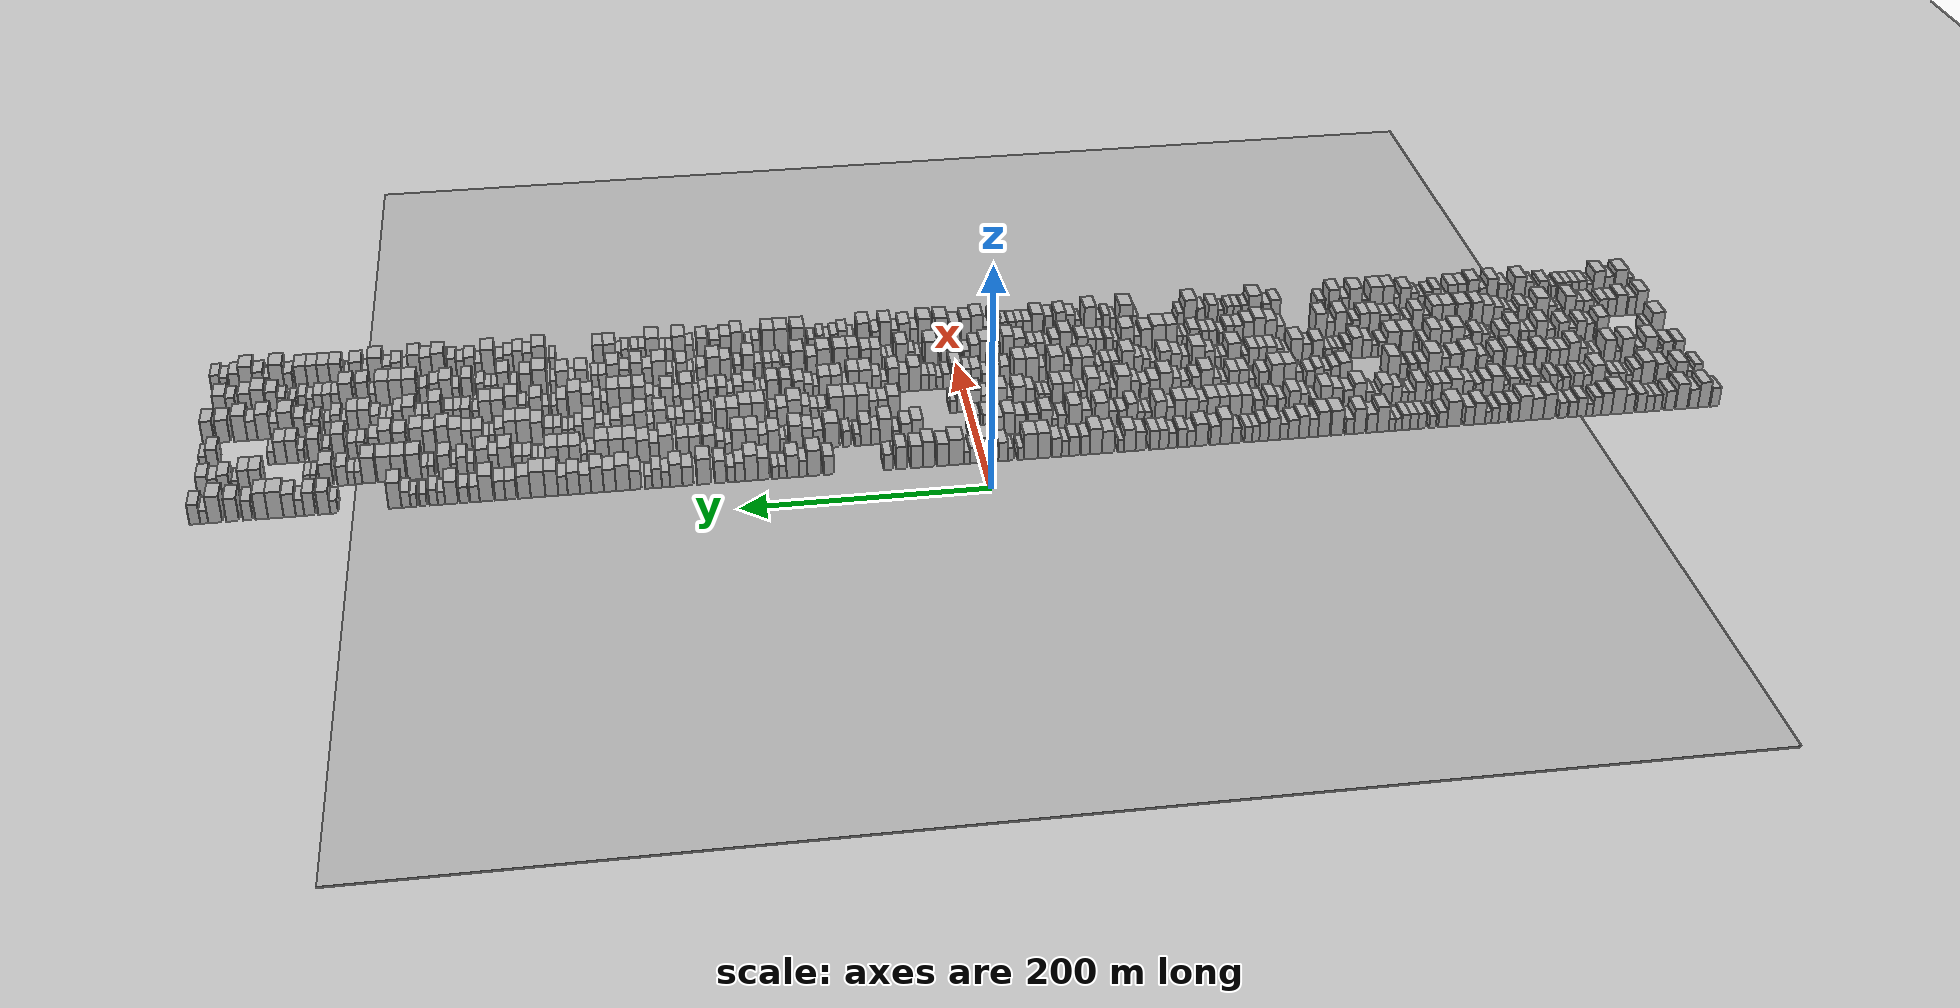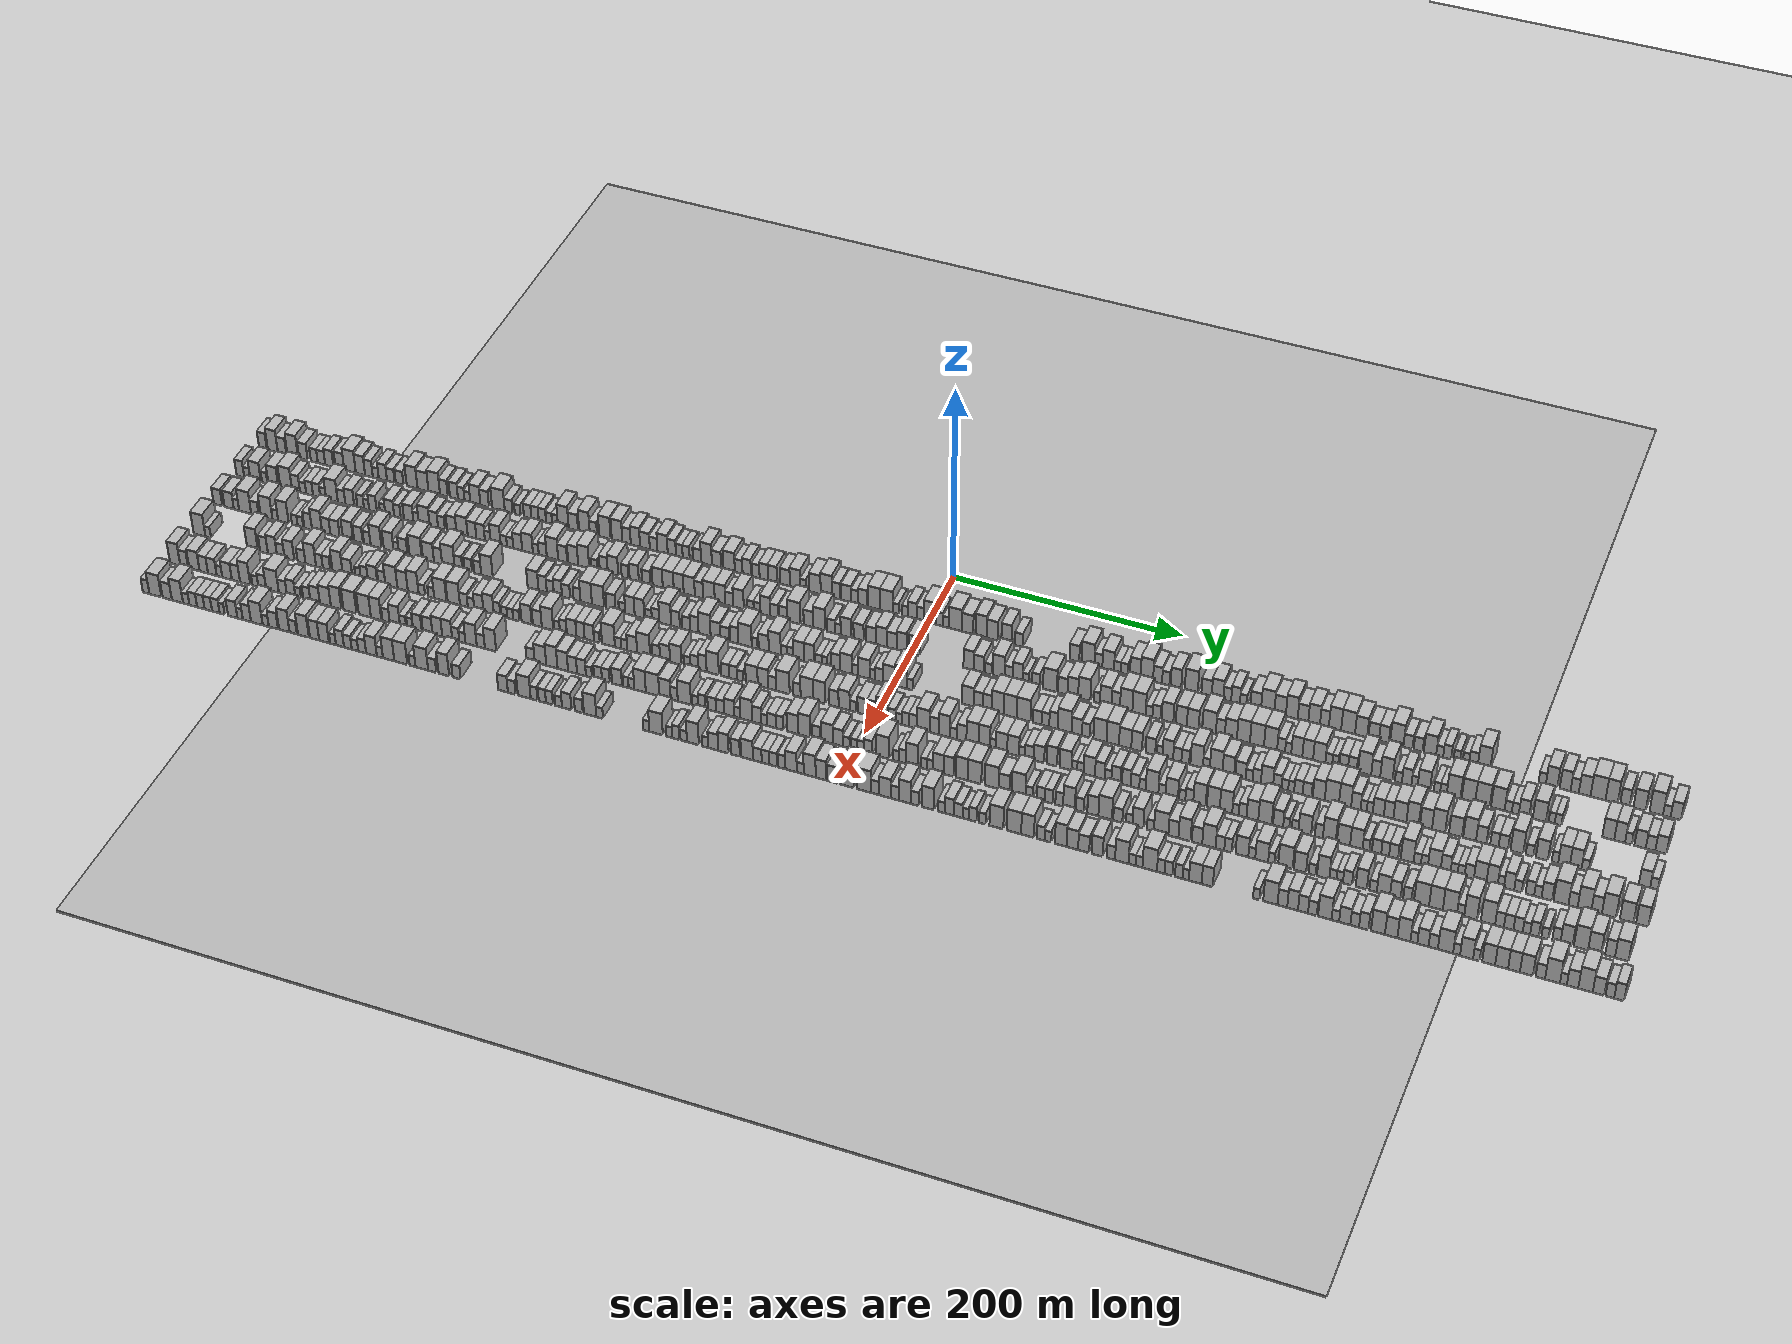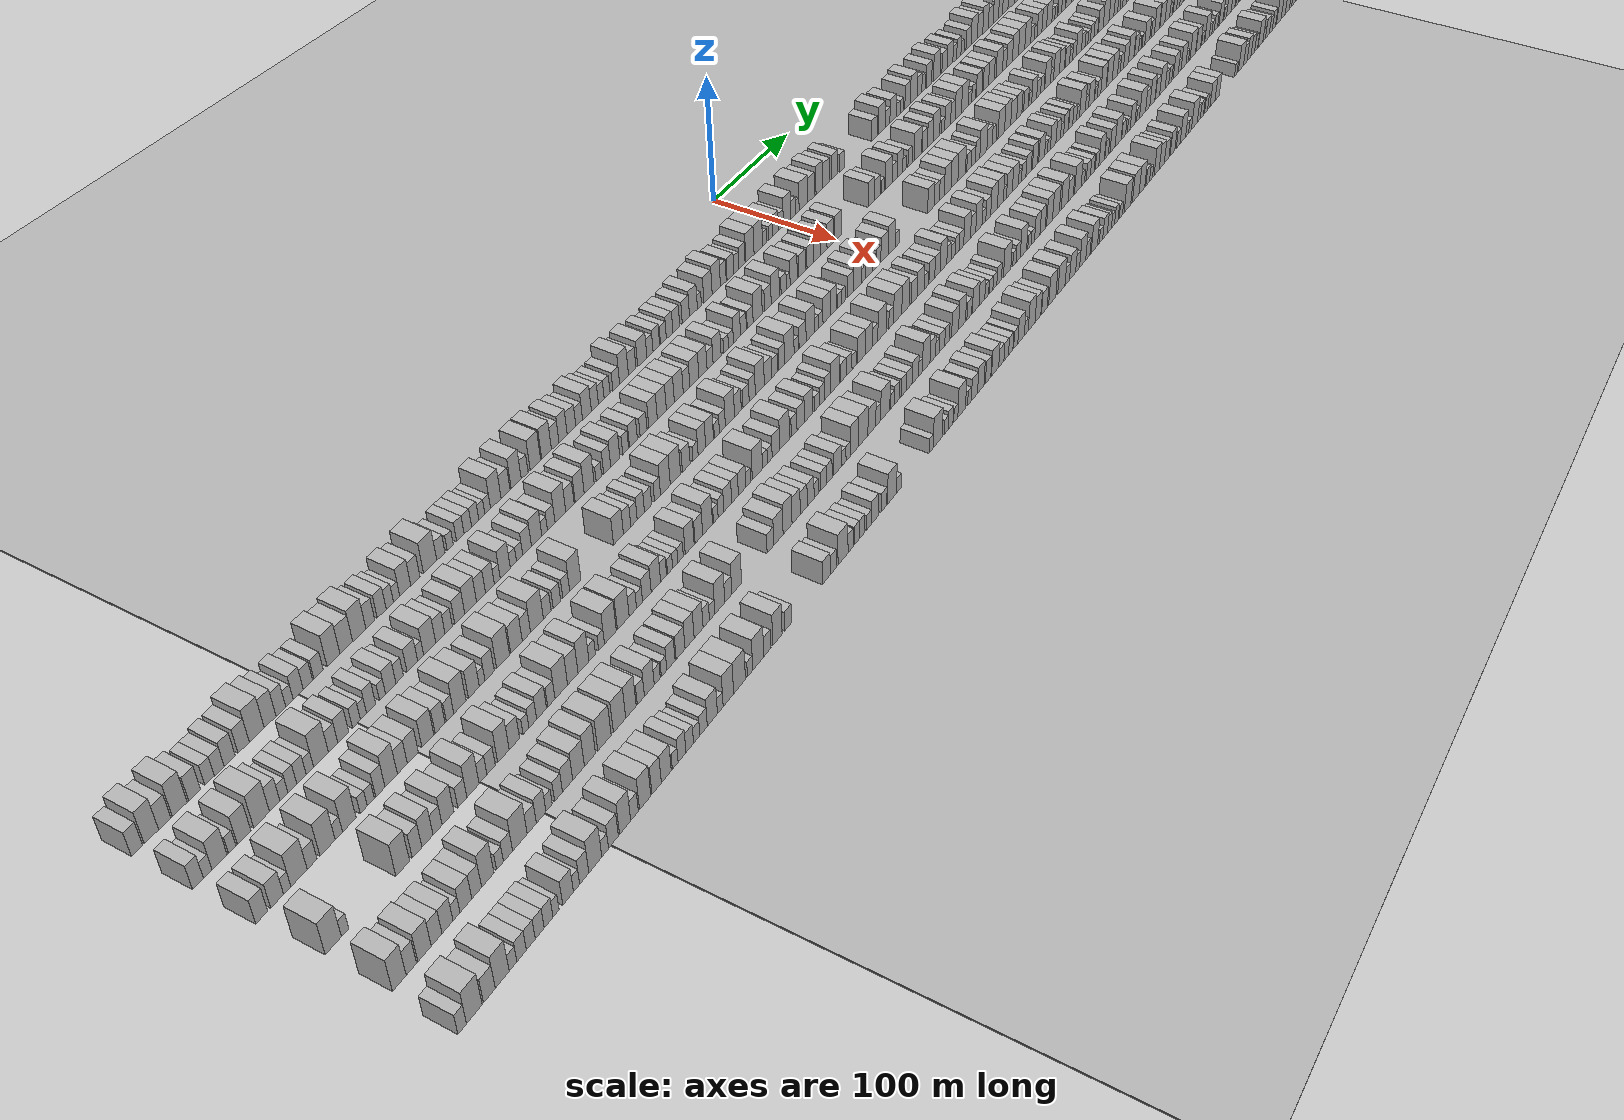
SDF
<?xml version="1.0" encoding="utf-8"?>

<sdf version="1.6">

   <world name="default">

      <gui fullscreen="0">

         <camera name="user_camera">

            <pose>-15 0 4.57585 0 0 0</pose>

            <view_controller>orbit</view_controller>

         </camera>

      </gui>

      <scene>

         <sky>

           <clouds>

             <speed>12</speed>

           </clouds>

         </sky>

         <ambient>0.4 0.4 0.4 1</ambient>

         <background>0.7 0.7 0.7 1</background>

         <shadows>1</shadows>

      </scene>

      <gravity>0 0 -9.8066</gravity>

      <magnetic_field>6e-06 2.3e-05 -4.2e-05</magnetic_field>

      <physics default="0" name="default_physics" type="ode">

         <ode>

            <solver>

               <type>quick</type>

               <iters>10</iters>

               <sor>1.0</sor>

               <use_dynamic_moi_rescaling>0</use_dynamic_moi_rescaling>

            </solver>

            <constraints>

               <cfm>0</cfm>

               <erp>0.2</erp>

               <contact_max_correcting_vel>100</contact_max_correcting_vel>

               <contact_surface_layer>0.001</contact_surface_layer>

            </constraints>

         </ode>

         <max_step_size>0.004</max_step_size>

         <real_time_factor>1</real_time_factor>

         <real_time_update_rate>250</real_time_update_rate>

      </physics>

      <light name="sun" type="directional">

         <cast_shadows>1</cast_shadows>

         <pose>0 0 10 0 0 0</pose>

         <diffuse>0.8 0.8 0.8 1</diffuse>

         <specular>0.2 0.2 0.2 1</specular>

         <attenuation>

            <range>1000</range>

            <constant>0.9</constant>

            <linear>0.01</linear>

            <quadratic>0.001</quadratic>

         </attenuation>

         <direction>-0.5 0.1 -0.9</direction>

      </light>

      <include>

         <name>ground_plane_1</name>

         <uri>model://HANNAS_ground_plane</uri>

         <pose>0 0 0  0 0 0</pose>

      </include>

      <include>

         <name>ground_plane_2</name>

         <uri>model://HANNAS_ground_plane</uri>

         <pose>100 0 0  0 0 0</pose>

      </include>

      <model name="building_1">

         <static>1</static>

         <pose frame="">50.0000 -616.2294 0 0.000000 0.000000 0.000000</pose>

         <link name="link">

            <pose frame="">0 0 9.00 0 0 0</pose>

            <collision name="collision">

               <geometry>

                  <box>

                     <size>20.0000 7.5412 18.0000</size>

                  </box>

               </geometry>

               <max_contacts>10</max_contacts>

               <surface>

                  <contact>

                     <ode/>

                  </contact>

                  <bounce/>

                  <friction>

                     <torsional>

                        <ode/>

                     </torsional>

                     <ode/>

                  </friction>

               </surface>

            </collision>

            <visual name="visual">

               <cast_shadows>0</cast_shadows>

               <geometry>

                  <box>

                     <size>20.0000 7.5412 18.0000</size>

                  </box>

               </geometry>

               <material>

                  <script>

                     <uri>model://HANNAS_wall/materials/scripts</uri>

                     <uri>model://HANNAS_wall/materials/textures</uri>

                     <name>vrc/HANNAS_wall</name>

                  </script>

               </material>

            </visual>

            <self_collide>0</self_collide>

            <enable_wind>0</enable_wind>

            <kinematic>0</kinematic>

         </link>

      </model>

      <model name="building_2">

         <static>1</static>

         <pose frame="">50.0000 -606.5758 0 0.000000 0.000000 0.000000</pose>

         <link name="link">

            <pose frame="">0 0 12.00 0 0 0</pose>

            <collision name="collision">

               <geometry>

                  <box>

                     <size>20.0000 9.7662 24.0000</size>

                  </box>

               </geometry>

               <max_contacts>10</max_contacts>

               <surface>

                  <contact>

                     <ode/>

                  </contact>

                  <bounce/>

                  <friction>

                     <torsional>

                        <ode/>

                     </torsional>

                     <ode/>

                  </friction>

               </surface>

            </collision>

            <visual name="visual">

               <cast_shadows>0</cast_shadows>

               <geometry>

                  <box>

                     <size>20.0000 9.7662 24.0000</size>

                  </box>

               </geometry>

               <material>

                  <script>

                     <uri>model://HANNAS_wall/materials/scripts</uri>

                     <uri>model://HANNAS_wall/materials/textures</uri>

                     <name>vrc/HANNAS_wall</name>

                  </script>

               </material>

            </visual>

            <self_collide>0</self_collide>

            <enable_wind>0</enable_wind>

            <kinematic>0</kinematic>

         </link>

      </model>

      <model name="building_3">

         <static>1</static>

         <pose frame="">50.0000 -597.5221 0 0.000000 0.000000 0.000000</pose>

         <link name="link">

            <pose frame="">0 0 9.00 0 0 0</pose>

            <collision name="collision">

               <geometry>

                  <box>

                     <size>20.0000 8.3411 18.0000</size>

                  </box>

               </geometry>

               <max_contacts>10</max_contacts>

               <surface>

                  <contact>

                     <ode/>

                  </contact>

                  <bounce/>

                  <friction>

                     <torsional>

                        <ode/>

                     </torsional>

                     <ode/>

                  </friction>

               </surface>

            </collision>

            <visual name="visual">

               <cast_shadows>0</cast_shadows>

               <geometry>

                  <box>

                     <size>20.0000 8.3411 18.0000</size>

                  </box>

               </geometry>

               <material>

                  <script>

                     <uri>model://HANNAS_wall/materials/scripts</uri>

                     <uri>model://HANNAS_wall/materials/textures</uri>

                     <name>vrc/HANNAS_wall</name>

                  </script>

               </material>

            </visual>

            <self_collide>0</self_collide>

            <enable_wind>0</enable_wind>

            <kinematic>0</kinematic>

         </link>

      </model>

      <model name="building_4">

         <static>1</static>

         <pose frame="">50.0000 -587.2268 0 0.000000 0.000000 0.000000</pose>

         <link name="link">

            <pose frame="">0 0 12.00 0 0 0</pose>

            <collision name="collision">

               <geometry>

                  <box>

                     <size>20.0000 10.2496 24.0000</size>

                  </box>

               </geometry>

               <max_contacts>10</max_contacts>

               <surface>

                  <contact>

                     <ode/>

                  </contact>

                  <bounce/>

                  <friction>

                     <torsional>

                        <ode/>

                     </torsional>

                     <ode/>

                  </friction>

               </surface>

            </collision>

            <visual name="visual">

               <cast_shadows>0</cast_shadows>

               <geometry>

                  <box>

                     <size>20.0000 10.2496 24.0000</size>

                  </box>

               </geometry>

               <material>

                  <script>

                     <uri>model://HANNAS_wall/materials/scripts</uri>

                     <uri>model://HANNAS_wall/materials/textures</uri>

                     <name>vrc/HANNAS_wall</name>

                  </script>

               </material>

            </visual>

            <self_collide>0</self_collide>

            <enable_wind>0</enable_wind>

            <kinematic>0</kinematic>

         </link>

      </model>

      <model name="building_5">

         <static>1</static>

         <pose frame="">50.0000 -576.8918 0 0.000000 0.000000 0.000000</pose>

         <link name="link">

            <pose frame="">0 0 9.00 0 0 0</pose>

            <collision name="collision">

               <geometry>

                  <box>

                     <size>20.0000 8.4203 18.0000</size>

                  </box>

               </geometry>

               <max_contacts>10</max_contacts>

               <surface>

                  <contact>

                     <ode/>

                  </contact>

                  <bounce/>

                  <friction>

                     <torsional>

                        <ode/>

                     </torsional>

                     <ode/>

                  </friction>

               </surface>

            </collision>

            <visual name="visual">

               <cast_shadows>0</cast_shadows>

               <geometry>

                  <box>

                     <size>20.0000 8.4203 18.0000</size>

                  </box>

               </geometry>

               <material>

                  <script>

                     <uri>model://HANNAS_wall/materials/scripts</uri>

                     <uri>model://HANNAS_wall/materials/textures</uri>

                     <name>vrc/HANNAS_wall</name>

                  </script>

               </material>

            </visual>

            <self_collide>0</self_collide>

            <enable_wind>0</enable_wind>

            <kinematic>0</kinematic>

         </link>

      </model>

      <model name="building_6">

         <static>1</static>

         <pose frame="">50.0000 -566.3089 0 0.000000 0.000000 0.000000</pose>

         <link name="link">

            <pose frame="">0 0 7.50 0 0 0</pose>

            <collision name="collision">

               <geometry>

                  <box>

                     <size>20.0000 6.7456 15.0000</size>

                  </box>

               </geometry>

               <max_contacts>10</max_contacts>

               <surface>

                  <contact>

                     <ode/>

                  </contact>

                  <bounce/>

                  <friction>

                     <torsional>

                        <ode/>

                     </torsional>

                     <ode/>

                  </friction>

               </surface>

            </collision>

            <visual name="visual">

               <cast_shadows>0</cast_shadows>

               <geometry>

                  <box>

                     <size>20.0000 6.7456 15.0000</size>

                  </box>

               </geometry>

               <material>

                  <script>

                     <uri>model://HANNAS_wall/materials/scripts</uri>

                     <uri>model://HANNAS_wall/materials/textures</uri>

                     <name>vrc/HANNAS_wall</name>

                  </script>

               </material>

            </visual>

            <self_collide>0</self_collide>

            <enable_wind>0</enable_wind>

            <kinematic>0</kinematic>

         </link>

      </model>

      <model name="building_7">

         <static>1</static>

         <pose frame="">50.0000 -559.3976 0 0.000000 0.000000 0.000000</pose>

         <link name="link">

            <pose frame="">0 0 7.50 0 0 0</pose>

            <collision name="collision">

               <geometry>

                  <box>

                     <size>20.0000 7.0770 15.0000</size>

                  </box>

               </geometry>

               <max_contacts>10</max_contacts>

               <surface>

                  <contact>

                     <ode/>

                  </contact>

                  <bounce/>

                  <friction>

                     <torsional>

                        <ode/>

                     </torsional>

                     <ode/>

                  </friction>

               </surface>

            </collision>

            <visual name="visual">

               <cast_shadows>0</cast_shadows>

               <geometry>

                  <box>

                     <size>20.0000 7.0770 15.0000</size>

                  </box>

               </geometry>

               <material>

                  <script>

                     <uri>model://HANNAS_wall/materials/scripts</uri>

                     <uri>model://HANNAS_wall/materials/textures</uri>

                     <name>vrc/HANNAS_wall</name>

                  </script>

               </material>

            </visual>

            <self_collide>0</self_collide>

            <enable_wind>0</enable_wind>

            <kinematic>0</kinematic>

         </link>

      </model>

      <model name="building_8">

         <static>1</static>

         <pose frame="">50.0000 -551.8449 0 0.000000 0.000000 0.000000</pose>

         <link name="link">

            <pose frame="">0 0 9.00 0 0 0</pose>

            <collision name="collision">

               <geometry>

                  <box>

                     <size>20.0000 8.0285 18.0000</size>

                  </box>

               </geometry>

               <max_contacts>10</max_contacts>

               <surface>

                  <contact>

                     <ode/>

                  </contact>

                  <bounce/>

                  <friction>

                     <torsional>

                        <ode/>

                     </torsional>

                     <ode/>

                  </friction>

               </surface>

            </collision>

            <visual name="visual">

               <cast_shadows>0</cast_shadows>

               <geometry>

                  <box>

                     <size>20.0000 8.0285 18.0000</size>

                  </box>

               </geometry>

               <material>

                  <script>

                     <uri>model://HANNAS_wall/materials/scripts</uri>

                     <uri>model://HANNAS_wall/materials/textures</uri>

                     <name>vrc/HANNAS_wall</name>

                  </script>

               </material>

            </visual>

            <self_collide>0</self_collide>

            <enable_wind>0</enable_wind>

            <kinematic>0</kinematic>

         </link>

      </model>

      <model name="building_9">

         <static>1</static>

         <pose frame="">50.0000 -541.6741 0 0.000000 0.000000 0.000000</pose>

         <link name="link">

            <pose frame="">0 0 9.00 0 0 0</pose>

            <collision name="collision">

               <geometry>

                  <box>

                     <size>20.0000 8.3131 18.0000</size>

                  </box>

               </geometry>

               <max_contacts>10</max_contacts>

               <surface>

                  <contact>

                     <ode/>

                  </contact>

                  <bounce/>

                  <friction>

                     <torsional>

                        <ode/>

                     </torsional>

                     <ode/>

                  </friction>

               </surface>

            </collision>

            <visual name="visual">

               <cast_shadows>0</cast_shadows>

               <geometry>

                  <box>

                     <size>20.0000 8.3131 18.0000</size>

                  </box>

               </geometry>

               <material>

                  <script>

                     <uri>model://HANNAS_wall/materials/scripts</uri>

                     <uri>model://HANNAS_wall/materials/textures</uri>

                     <name>vrc/HANNAS_wall</name>

                  </script>

               </material>

            </visual>

            <self_collide>0</self_collide>

            <enable_wind>0</enable_wind>

            <kinematic>0</kinematic>

         </link>

      </model>

      <model name="building_10">

         <static>1</static>

         <pose frame="">50.0000 -531.9448 0 0.000000 0.000000 0.000000</pose>

         <link name="link">

            <pose frame="">0 0 12.00 0 0 0</pose>

            <collision name="collision">

               <geometry>

                  <box>

                     <size>20.0000 11.1454 24.0000</size>

                  </box>

               </geometry>

               <max_contacts>10</max_contacts>

               <surface>

                  <contact>

                     <ode/>

                  </contact>

                  <bounce/>

                  <friction>

                     <torsional>

                        <ode/>

                     </torsional>

                     <ode/>

                  </friction>

               </surface>

            </collision>

            <visual name="visual">

               <cast_shadows>0</cast_shadows>

               <geometry>

                  <box>

                     <size>20.0000 11.1454 24.0000</size>

                  </box>

               </geometry>

               <material>

                  <script>

                     <uri>model://HANNAS_wall/materials/scripts</uri>

                     <uri>model://HANNAS_wall/materials/textures</uri>

                     <name>vrc/HANNAS_wall</name>

                  </script>

               </material>

            </visual>

            <self_collide>0</self_collide>

            <enable_wind>0</enable_wind>

            <kinematic>0</kinematic>

         </link>

      </model>

      <model name="building_11">

         <static>1</static>

         <pose frame="">50.0000 -521.9122 0 0.000000 0.000000 0.000000</pose>

         <link name="link">

            <pose frame="">0 0 10.50 0 0 0</pose>

            <collision name="collision">

               <geometry>

                  <box>

                     <size>20.0000 8.9199 21.0000</size>

                  </box>

               </geometry>

               <max_contacts>10</max_contacts>

               <surface>

                  <contact>

                     <ode/>

                  </contact>

                  <bounce/>

                  <friction>

                     <torsional>

                        <ode/>

                     </torsional>

                     <ode/>

                  </friction>

               </surface>

            </collision>

            <visual name="visual">

               <cast_shadows>0</cast_shadows>

               <geometry>

                  <box>

                     <size>20.0000 8.9199 21.0000</size>

                  </box>

               </geometry>

               <material>

                  <script>

                     <uri>model://HANNAS_wall/materials/scripts</uri>

                     <uri>model://HANNAS_wall/materials/textures</uri>

                     <name>vrc/HANNAS_wall</name>

                  </script>

               </material>

            </visual>

            <self_collide>0</self_collide>

            <enable_wind>0</enable_wind>

            <kinematic>0</kinematic>

         </link>

      </model>

      <model name="building_12">

         <static>1</static>

         <pose frame="">50.0000 -513.7622 0 0.000000 0.000000 0.000000</pose>

         <link name="link">

            <pose frame="">0 0 9.00 0 0 0</pose>

            <collision name="collision">

               <geometry>

                  <box>

                     <size>20.0000 7.3800 18.0000</size>

                  </box>

               </geometry>

               <max_contacts>10</max_contacts>

               <surface>

                  <contact>

                     <ode/>

                  </contact>

                  <bounce/>

                  <friction>

                     <torsional>

                        <ode/>

                     </torsional>

                     <ode/>

                  </friction>

               </surface>

            </collision>

            <visual name="visual">

               <cast_shadows>0</cast_shadows>

               <geometry>

                  <box>

                     <size>20.0000 7.3800 18.0000</size>

                  </box>

               </geometry>

               <material>

                  <script>

                     <uri>model://HANNAS_wall/materials/scripts</uri>

                     <uri>model://HANNAS_wall/materials/textures</uri>

                     <name>vrc/HANNAS_wall</name>

                  </script>

               </material>

            </visual>

            <self_collide>0</self_collide>

            <enable_wind>0</enable_wind>

            <kinematic>0</kinematic>

         </link>

      </model>

      <model name="building_13">

         <static>1</static>

         <pose frame="">50.0000 -507.2023 0 0.000000 0.000000 0.000000</pose>

         <link name="link">

            <pose frame="">0 0 6.00 0 0 0</pose>

            <collision name="collision">

               <geometry>

                  <box>

                     <size>20.0000 5.7397 12.0000</size>

                  </box>

               </geometry>

               <max_contacts>10</max_contacts>

               <surface>

                  <contact>

                     <ode/>

                  </contact>

                  <bounce/>

                  <friction>

                     <torsional>

                        <ode/>

                     </torsional>

                     <ode/>

                  </friction>

               </surface>

            </collision>

            <visual name="visual">

               <cast_shadows>0</cast_shadows>

               <geometry>

                  <box>

                     <size>20.0000 5.7397 12.0000</size>

                  </box>

               </geometry>

               <material>

                  <script>

                     <uri>model://HANNAS_wall/materials/scripts</uri>

                     <uri>model://HANNAS_wall/materials/textures</uri>

                     <name>vrc/HANNAS_wall</name>

                  </script>

               </material>

            </visual>

            <self_collide>0</self_collide>

            <enable_wind>0</enable_wind>

            <kinematic>0</kinematic>

         </link>

      </model>

      <model name="building_14">

         <static>1</static>

         <pose frame="">50.0000 -500.3879 0 0.000000 0.000000 0.000000</pose>

         <link name="link">

            <pose frame="">0 0 9.00 0 0 0</pose>

            <collision name="collision">

               <geometry>

                  <box>

                     <size>20.0000 7.8891 18.0000</size>

                  </box>

               </geometry>

               <max_contacts>10</max_contacts>

               <surface>

                  <contact>

                     <ode/>

                  </contact>

                  <bounce/>

                  <friction>

                     <torsional>

                        <ode/>

                     </torsional>

                     <ode/>

                  </friction>

               </surface>

            </collision>

            <visual name="visual">

               <cast_shadows>0</cast_shadows>

               <geometry>

                  <box>

                     <size>20.0000 7.8891 18.0000</size>

                  </box>

               </geometry>

               <material>

                  <script>

                     <uri>model://HANNAS_wall/materials/scripts</uri>

                     <uri>model://HANNAS_wall/materials/textures</uri>

                     <name>vrc/HANNAS_wall</name>

                  </script>

               </material>

            </visual>

            <self_collide>0</self_collide>

            <enable_wind>0</enable_wind>

            <kinematic>0</kinematic>

         </link>

      </model>

      <model name="building_15">

         <static>1</static>

         <pose frame="">50.0000 -492.7710 0 0.000000 0.000000 0.000000</pose>

         <link name="link">

            <pose frame="">0 0 7.50 0 0 0</pose>

            <collision name="collision">

               <geometry>

                  <box>

                     <size>20.0000 7.3448 15.0000</size>

                  </box>

               </geometry>

               <max_contacts>10</max_contacts>

               <surface>

                  <contact>

                     <ode/>

                  </contact>

                  <bounce/>

                  <friction>

                     <torsional>

                        <ode/>

                     </torsional>

                     <ode/>

                  </friction>

               </surface>

            </collision>

            <visual name="visual">

               <cast_shadows>0</cast_shadows>

               <geometry>

                  <box>

                     <size>20.0000 7.3448 15.0000</size>

                  </box>

               </geometry>

               <material>

                  <script>

                     <uri>model://HANNAS_wall/materials/scripts</uri>

                     <uri>model://HANNAS_wall/materials/textures</uri>

                     <name>vrc/HANNAS_wall</name>

                  </script>

               </material>

            </visual>

            <self_collide>0</self_collide>

            <enable_wind>0</enable_wind>

            <kinematic>0</kinematic>

         </link>

      </model>

      <model name="building_16">

         <static>1</static>

         <pose frame="">50.0000 -484.3957 0 0.000000 0.000000 0.000000</pose>

         <link name="link">

            <pose frame="">0 0 7.50 0 0 0</pose>

            <collision name="collision">

               <geometry>

                  <box>

                     <size>20.0000 7.4057 15.0000</size>

                  </box>

               </geometry>

               <max_contacts>10</max_contacts>

               <surface>

                  <contact>

                     <ode/>

                  </contact>

                  <bounce/>

                  <friction>

                     <torsional>

                        <ode/>

                     </torsional>

                     <ode/>

                  </friction>

               </surface>

            </collision>

            <visual name="visual">

               <cast_shadows>0</cast_shadows>

               <geometry>

                  <box>

                     <size>20.0000 7.4057 15.0000</size>

                  </box>

               </geometry>

               <material>

                  <script>

                     <uri>model://HANNAS_wall/materials/scripts</uri>

                     <uri>model://HANNAS_wall/materials/textures</uri>

                     <name>vrc/HANNAS_wall</name>

                  </script>

               </material>

            </visual>

            <self_collide>0</self_collide>

            <enable_wind>0</enable_wind>

            <kinematic>0</kinematic>

         </link>

      </model>

      <model name="building_17">

         <static>1</static>

         <pose frame="">50.0000 -472.5264 0 0.000000 0.000000 0.000000</pose>

         <link name="link">

            <pose frame="">0 0 12.00 0 0 0</pose>

            <collision name="collision">

               <geometry>

                  <box>

                     <size>20.0000 10.3329 24.0000</size>

                  </box>

               </geometry>

               <max_contacts>10</max_contacts>

               <surface>

                  <contact>

                     <ode/>

                  </contact>

                  <bounce/>

                  <friction>

                     <torsional>

                        <ode/>

                     </torsional>

                     <ode/>

                  </friction>

               </surface>

            </collision>

            <visual name="visual">

               <cast_shadows>0</cast_shadows>

               <geometry>

                  <box>

                     <size>20.0000 10.3329 24.0000</size>

                  </box>

               </geometry>

               <material>

                  <script>

                     <uri>model://HANNAS_wall/materials/scripts</uri>

                     <uri>model://HANNAS_wall/materials/textures</uri>

                     <name>vrc/HANNAS_wall</name>

                  </script>

               </material>

            </visual>

            <self_collide>0</self_collide>

            <enable_wind>0</enable_wind>

            <kinematic>0</kinematic>

         </link>

      </model>

      <model name="building_18">

         <static>1</static>

         <pose frame="">50.0000 -462.1523 0 0.000000 0.000000 0.000000</pose>

         <link name="link">

            <pose frame="">0 0 10.50 0 0 0</pose>

            <collision name="collision">

               <geometry>

                  <box>

                     <size>20.0000 10.4155 21.0000</size>

                  </box>

               </geometry>

               <max_contacts>10</max_contacts>

               <surface>

                  <contact>

                     <ode/>

                  </contact>

                  <bounce/>

                  <friction>

                     <torsional>

                        <ode/>

                     </torsional>

                     <ode/>

                  </friction>

               </surface>

            </collision>

            <visual name="visual">

               <cast_shadows>0</cast_shadows>

               <geometry>

                  <box>

                     <size>20.0000 10.4155 21.0000</size>

                  </box>

               </geometry>

               <material>

                  <script>

                     <uri>model://HANNAS_wall/materials/scripts</uri>

                     <uri>model://HANNAS_wall/materials/textures</uri>

                     <name>vrc/HANNAS_wall</name>

                  </script>

               </material>

            </visual>

            <self_collide>0</self_collide>

            <enable_wind>0</enable_wind>

            <kinematic>0</kinematic>

         </link>

      </model>

      <model name="building_19">

         <static>1</static>

         <pose frame="">50.0000 -451.4991 0 0.000000 0.000000 0.000000</pose>

         <link name="link">

            <pose frame="">0 0 12.00 0 0 0</pose>

            <collision name="collision">

               <geometry>

                  <box>

                     <size>20.0000 10.8909 24.0000</size>

                  </box>

               </geometry>

               <max_contacts>10</max_contacts>

               <surface>

                  <contact>

                     <ode/>

                  </contact>

                  <bounce/>

                  <friction>

                     <torsional>

                        <ode/>

                     </torsional>

                     <ode/>

                  </friction>

               </surface>

            </collision>

            <visual name="visual">

               <cast_shadows>0</cast_shadows>

               <geometry>

                  <box>

                     <size>20.0000 10.8909 24.0000</size>

                  </box>

               </geometry>

               <material>

                  <script>

                     <uri>model://HANNAS_wall/materials/scripts</uri>

                     <uri>model://HANNAS_wall/materials/textures</uri>

                     <name>vrc/HANNAS_wall</name>

                  </script>

               </material>

            </visual>

            <self_collide>0</self_collide>

            <enable_wind>0</enable_wind>

            <kinematic>0</kinematic>

         </link>

      </model>

      <model name="building_20">

         <static>1</static>

         <pose frame="">50.0000 -442.3367 0 0.000000 0.000000 0.000000</pose>

         <link name="link">

            <pose frame="">0 0 9.00 0 0 0</pose>

            <collision name="collision">

               <geometry>

                  <box>

                     <size>20.0000 7.4337 18.0000</size>

                  </box>

               </geometry>

               <max_contacts>10</max_contacts>

               <surface>

                  <contact>

                     <ode/>

                  </contact>

                  <bounce/>

                  <friction>

                     <torsional>

                        <ode/>

                     </torsional>

                     <ode/>

                  </friction>

               </surface>

            </collision>

            <visual name="visual">

               <cast_shadows>0</cast_shadows>

               <geometry>

                  <box>

                     <size>20.0000 7.4337 18.0000</size>

                  </box>

               </geometry>

               <material>

                  <script>

                     <uri>model://HANNAS_wall/materials/scripts</uri>

                     <uri>model://HANNAS_wall/materials/textures</uri>

                     <name>vrc/HANNAS_wall</name>

                  </script>

               </material>

            </visual>

            <self_collide>0</self_collide>

            <enable_wind>0</enable_wind>

            <kinematic>0</kinematic>

         </link>

      </model>

      <model name="building_21">

         <static>1</static>

         <pose frame="">50.0000 -432.8112 0 0.000000 0.000000 0.000000</pose>

         <link name="link">

            <pose frame="">0 0 9.00 0 0 0</pose>

            <collision name="collision">

               <geometry>

                  <box>

                     <size>20.0000 7.6175 18.0000</size>

                  </box>

               </geometry>

               <max_contacts>10</max_contacts>

               <surface>

                  <contact>

                     <ode/>

                  </contact>

                  <bounce/>

                  <friction>

                     <torsional>

                        <ode/>

                     </torsional>

                     <ode/>

                  </friction>

               </surface>

            </collision>

            <visual name="visual">

               <cast_shadows>0</cast_shadows>

               <geometry>

                  <box>

                     <size>20.0000 7.6175 18.0000</size>

                  </box>

               </geometry>

               <material>

                  <script>

                     <uri>model://HANNAS_wall/materials/scripts</uri>

                     <uri>model://HANNAS_wall/materials/textures</uri>

                     <name>vrc/HANNAS_wall</name>

                  </script>

               </material>

            </visual>

            <self_collide>0</self_collide>

            <enable_wind>0</enable_wind>

            <kinematic>0</kinematic>

         </link>

      </model>

      <model name="building_22">

         <static>1</static>

         <pose frame="">50.0000 -425.9050 0 0.000000 0.000000 0.000000</pose>

         <link name="link">

            <pose frame="">0 0 7.50 0 0 0</pose>

            <collision name="collision">

               <geometry>

                  <box>

                     <size>20.0000 6.1948 15.0000</size>

                  </box>

               </geometry>

               <max_contacts>10</max_contacts>

               <surface>

                  <contact>

                     <ode/>

                  </contact>

                  <bounce/>

                  <friction>

                     <torsional>

                        <ode/>

                     </torsional>

                     <ode/>

                  </friction>

               </surface>

            </collision>

            <visual name="visual">

               <cast_shadows>0</cast_shadows>

               <geometry>

                  <box>

                     <size>20.0000 6.1948 15.0000</size>

                  </box>

               </geometry>

               <material>

                  <script>

                     <uri>model://HANNAS_wall/materials/scripts</uri>

                     <uri>model://HANNAS_wall/materials/textures</uri>

                     <name>vrc/HANNAS_wall</name>

                  </script>

               </material>

            </visual>

            <self_collide>0</self_collide>

            <enable_wind>0</enable_wind>

            <kinematic>0</kinematic>

         </link>

      </model>

      <model name="building_23">

         <static>1</static>

         <pose frame="">50.0000 -420.1066 0 0.000000 0.000000 0.000000</pose>

         <link name="link">

            <pose frame="">0 0 6.00 0 0 0</pose>

            <collision name="collision">

               <geometry>

                  <box>

                     <size>20.0000 5.4019 12.0000</size>

                  </box>

               </geometry>

               <max_contacts>10</max_contacts>

               <surface>

                  <contact>

                     <ode/>

                  </contact>

                  <bounce/>

                  <friction>

                     <torsional>

                        <ode/>

                     </torsional>

                     <ode/>

                  </friction>

               </surface>

            </collision>

            <visual name="visual">

               <cast_shadows>0</cast_shadows>

               <geometry>

                  <box>

                     <size>20.0000 5.4019 12.0000</size>

                  </box>

               </geometry>

               <material>

                  <script>

                     <uri>model://HANNAS_wall/materials/scripts</uri>

                     <uri>model://HANNAS_wall/materials/textures</uri>

                     <name>vrc/HANNAS_wall</name>

                  </script>

               </material>

            </visual>

            <self_collide>0</self_collide>

            <enable_wind>0</enable_wind>

            <kinematic>0</kinematic>

         </link>

      </model>

      <model name="building_24">

         <static>1</static>

         <pose frame="">50.0000 -412.6392 0 0.000000 0.000000 0.000000</pose>

         <link name="link">

            <pose frame="">0 0 10.50 0 0 0</pose>

            <collision name="collision">

               <geometry>

                  <box>

                     <size>20.0000 9.5329 21.0000</size>

                  </box>

               </geometry>

               <max_contacts>10</max_contacts>

               <surface>

                  <contact>

                     <ode/>

                  </contact>

                  <bounce/>

                  <friction>

                     <torsional>

                        <ode/>

                     </torsional>

                     <ode/>

                  </friction>

               </surface>

            </collision>

            <visual name="visual">

               <cast_shadows>0</cast_shadows>

               <geometry>

                  <box>

                     <size>20.0000 9.5329 21.0000</size>

                  </box>

               </geometry>

               <material>

                  <script>

                     <uri>model://HANNAS_wall/materials/scripts</uri>

                     <uri>model://HANNAS_wall/materials/textures</uri>

                     <name>vrc/HANNAS_wall</name>

                  </script>

               </material>

            </visual>

            <self_collide>0</self_collide>

            <enable_wind>0</enable_wind>

            <kinematic>0</kinematic>

         </link>

      </model>

      <model name="building_25">

         <static>1</static>

         <pose frame="">50.0000 -403.8558 0 0.000000 0.000000 0.000000</pose>

         <link name="link">

            <pose frame="">0 0 9.00 0 0 0</pose>

            <collision name="collision">

               <geometry>

                  <box>

                     <size>20.0000 8.0339 18.0000</size>

                  </box>

               </geometry>

               <max_contacts>10</max_contacts>

               <surface>

                  <contact>

                     <ode/>

                  </contact>

                  <bounce/>

                  <friction>

                     <torsional>

                        <ode/>

                     </torsional>

                     <ode/>

                  </friction>

               </surface>

            </collision>

            <visual name="visual">

               <cast_shadows>0</cast_shadows>

               <geometry>

                  <box>

                     <size>20.0000 8.0339 18.0000</size>

                  </box>

               </geometry>

               <material>

                  <script>

                     <uri>model://HANNAS_wall/materials/scripts</uri>

                     <uri>model://HANNAS_wall/materials/textures</uri>

                     <name>vrc/HANNAS_wall</name>

                  </script>

               </material>

            </visual>

            <self_collide>0</self_collide>

            <enable_wind>0</enable_wind>

            <kinematic>0</kinematic>

         </link>

      </model>

      <model name="building_26">

         <static>1</static>

         <pose frame="">50.0000 -390.8958 0 0.000000 0.000000 0.000000</pose>

         <link name="link">

            <pose frame="">0 0 12.00 0 0 0</pose>

            <collision name="collision">

               <geometry>

                  <box>

                     <size>20.0000 11.8861 24.0000</size>

                  </box>

               </geometry>

               <max_contacts>10</max_contacts>

               <surface>

                  <contact>

                     <ode/>

                  </contact>

                  <bounce/>

                  <friction>

                     <torsional>

                        <ode/>

                     </torsional>

                     <ode/>

                  </friction>

               </surface>

            </collision>

            <visual name="visual">

               <cast_shadows>0</cast_shadows>

               <geometry>

                  <box>

                     <size>20.0000 11.8861 24.0000</size>

                  </box>

               </geometry>

               <material>

                  <script>

                     <uri>model://HANNAS_wall/materials/scripts</uri>

                     <uri>model://HANNAS_wall/materials/textures</uri>

                     <name>vrc/HANNAS_wall</name>

                  </script>

               </material>

            </visual>

            <self_collide>0</self_collide>

            <enable_wind>0</enable_wind>

            <kinematic>0</kinematic>

         </link>

      </model>

      <model name="building_27">

         <static>1</static>

         <pose frame="">50.0000 -381.2892 0 0.000000 0.000000 0.000000</pose>

         <link name="link">

            <pose frame="">0 0 7.50 0 0 0</pose>

            <collision name="collision">

               <geometry>

                  <box>

                     <size>20.0000 7.3271 15.0000</size>

                  </box>

               </geometry>

               <max_contacts>10</max_contacts>

               <surface>

                  <contact>

                     <ode/>

                  </contact>

                  <bounce/>

                  <friction>

                     <torsional>

                        <ode/>

                     </torsional>

                     <ode/>

                  </friction>

               </surface>

            </collision>

            <visual name="visual">

               <cast_shadows>0</cast_shadows>

               <geometry>

                  <box>

                     <size>20.0000 7.3271 15.0000</size>

                  </box>

               </geometry>

               <material>

                  <script>

                     <uri>model://HANNAS_wall/materials/scripts</uri>

                     <uri>model://HANNAS_wall/materials/textures</uri>

                     <name>vrc/HANNAS_wall</name>

                  </script>

               </material>

            </visual>

            <self_collide>0</self_collide>

            <enable_wind>0</enable_wind>

            <kinematic>0</kinematic>

         </link>

      </model>

      <model name="building_28">

         <static>1</static>

         <pose frame="">50.0000 -372.8500 0 0.000000 0.000000 0.000000</pose>

         <link name="link">

            <pose frame="">0 0 6.00 0 0 0</pose>

            <collision name="collision">

               <geometry>

                  <box>

                     <size>20.0000 5.5512 12.0000</size>

                  </box>

               </geometry>

               <max_contacts>10</max_contacts>

               <surface>

                  <contact>

                     <ode/>

                  </contact>

                  <bounce/>

                  <friction>

                     <torsional>

                        <ode/>

                     </torsional>

                     <ode/>

                  </friction>

               </surface>

            </collision>

            <visual name="visual">

               <cast_shadows>0</cast_shadows>

               <geometry>

                  <box>

                     <size>20.0000 5.5512 12.0000</size>

                  </box>

               </geometry>

               <material>

                  <script>

                     <uri>model://HANNAS_wall/materials/scripts</uri>

                     <uri>model://HANNAS_wall/materials/textures</uri>

                     <name>vrc/HANNAS_wall</name>

                  </script>

               </material>

            </visual>

            <self_collide>0</self_collide>

            <enable_wind>0</enable_wind>

            <kinematic>0</kinematic>

         </link>

      </model>

      <model name="building_29">

         <static>1</static>

         <pose frame="">50.0000 -363.5970 0 0.000000 0.000000 0.000000</pose>

         <link name="link">

            <pose frame="">0 0 7.50 0 0 0</pose>

            <collision name="collision">

               <geometry>

                  <box>

                     <size>20.0000 6.9548 15.0000</size>

                  </box>

               </geometry>

               <max_contacts>10</max_contacts>

               <surface>

                  <contact>

                     <ode/>

                  </contact>

                  <bounce/>

                  <friction>

                     <torsional>

                        <ode/>

                     </torsional>

                     <ode/>

                  </friction>

               </surface>

            </collision>

            <visual name="visual">

               <cast_shadows>0</cast_shadows>

               <geometry>

                  <box>

                     <size>20.0000 6.9548 15.0000</size>

                  </box>

               </geometry>

               <material>

                  <script>

                     <uri>model://HANNAS_wall/materials/scripts</uri>

                     <uri>model://HANNAS_wall/materials/textures</uri>

                     <name>vrc/HANNAS_wall</name>

                  </script>

               </material>

            </visual>

            <self_collide>0</self_collide>

            <enable_wind>0</enable_wind>

            <kinematic>0</kinematic>

         </link>

      </model>

      <model name="building_30">

         <static>1</static>

         <pose frame="">50.0000 -356.6637 0 0.000000 0.000000 0.000000</pose>

         <link name="link">

            <pose frame="">0 0 7.50 0 0 0</pose>

            <collision name="collision">

               <geometry>

                  <box>

                     <size>20.0000 6.9119 15.0000</size>

                  </box>

               </geometry>

               <max_contacts>10</max_contacts>

               <surface>

                  <contact>

                     <ode/>

                  </contact>

                  <bounce/>

                  <friction>

                     <torsional>

                        <ode/>

                     </torsional>

                     <ode/>

                  </friction>

               </surface>

            </collision>

            <visual name="visual">

               <cast_shadows>0</cast_shadows>

               <geometry>

                  <box>

                     <size>20.0000 6.9119 15.0000</size>

                  </box>

               </geometry>

               <material>

                  <script>

                     <uri>model://HANNAS_wall/materials/scripts</uri>

                     <uri>model://HANNAS_wall/materials/textures</uri>

                     <name>vrc/HANNAS_wall</name>

                  </script>

               </material>

            </visual>

            <self_collide>0</self_collide>

            <enable_wind>0</enable_wind>

            <kinematic>0</kinematic>

         </link>

      </model>

      <model name="building_31">

         <static>1</static>

         <pose frame="">50.0000 -349.8199 0 0.000000 0.000000 0.000000</pose>

         <link name="link">

            <pose frame="">0 0 7.50 0 0 0</pose>

            <collision name="collision">

               <geometry>

                  <box>

                     <size>20.0000 6.7757 15.0000</size>

                  </box>

               </geometry>

               <max_contacts>10</max_contacts>

               <surface>

                  <contact>

                     <ode/>

                  </contact>

                  <bounce/>

                  <friction>

                     <torsional>

                        <ode/>

                     </torsional>

                     <ode/>

                  </friction>

               </surface>

            </collision>

            <visual name="visual">

               <cast_shadows>0</cast_shadows>

               <geometry>

                  <box>

                     <size>20.0000 6.7757 15.0000</size>

                  </box>

               </geometry>

               <material>

                  <script>

                     <uri>model://HANNAS_wall/materials/scripts</uri>

                     <uri>model://HANNAS_wall/materials/textures</uri>

                     <name>vrc/HANNAS_wall</name>

                  </script>

               </material>

            </visual>

            <self_collide>0</self_collide>

            <enable_wind>0</enable_wind>

            <kinematic>0</kinematic>

         </link>

      </model>

      <model name="building_32">

         <static>1</static>

         <pose frame="">50.0000 -343.5941 0 0.000000 0.000000 0.000000</pose>

         <link name="link">

            <pose frame="">0 0 6.00 0 0 0</pose>

            <collision name="collision">

               <geometry>

                  <box>

                     <size>20.0000 5.6757 12.0000</size>

                  </box>

               </geometry>

               <max_contacts>10</max_contacts>

               <surface>

                  <contact>

                     <ode/>

                  </contact>

                  <bounce/>

                  <friction>

                     <torsional>

                        <ode/>

                     </torsional>

                     <ode/>

                  </friction>

               </surface>

            </collision>

            <visual name="visual">

               <cast_shadows>0</cast_shadows>

               <geometry>

                  <box>

                     <size>20.0000 5.6757 12.0000</size>

                  </box>

               </geometry>

               <material>

                  <script>

                     <uri>model://HANNAS_wall/materials/scripts</uri>

                     <uri>model://HANNAS_wall/materials/textures</uri>

                     <name>vrc/HANNAS_wall</name>

                  </script>

               </material>

            </visual>

            <self_collide>0</self_collide>

            <enable_wind>0</enable_wind>

            <kinematic>0</kinematic>

         </link>

      </model>

      <model name="building_33">

         <static>1</static>

         <pose frame="">50.0000 -338.0735 0 0.000000 0.000000 0.000000</pose>

         <link name="link">

            <pose frame="">0 0 6.00 0 0 0</pose>

            <collision name="collision">

               <geometry>

                  <box>

                     <size>20.0000 5.3656 12.0000</size>

                  </box>

               </geometry>

               <max_contacts>10</max_contacts>

               <surface>

                  <contact>

                     <ode/>

                  </contact>

                  <bounce/>

                  <friction>

                     <torsional>

                        <ode/>

                     </torsional>

                     <ode/>

                  </friction>

               </surface>

            </collision>

            <visual name="visual">

               <cast_shadows>0</cast_shadows>

               <geometry>

                  <box>

                     <size>20.0000 5.3656 12.0000</size>

                  </box>

               </geometry>

               <material>

                  <script>

                     <uri>model://HANNAS_wall/materials/scripts</uri>

                     <uri>model://HANNAS_wall/materials/textures</uri>

                     <name>vrc/HANNAS_wall</name>

                  </script>

               </material>

            </visual>

            <self_collide>0</self_collide>

            <enable_wind>0</enable_wind>

            <kinematic>0</kinematic>

         </link>

      </model>

      <model name="building_34">

         <static>1</static>

         <pose frame="">50.0000 -330.3880 0 0.000000 0.000000 0.000000</pose>

         <link name="link">

            <pose frame="">0 0 12.00 0 0 0</pose>

            <collision name="collision">

               <geometry>

                  <box>

                     <size>20.0000 10.0054 24.0000</size>

                  </box>

               </geometry>

               <max_contacts>10</max_contacts>

               <surface>

                  <contact>

                     <ode/>

                  </contact>

                  <bounce/>

                  <friction>

                     <torsional>

                        <ode/>

                     </torsional>

                     <ode/>

                  </friction>

               </surface>

            </collision>

            <visual name="visual">

               <cast_shadows>0</cast_shadows>

               <geometry>

                  <box>

                     <size>20.0000 10.0054 24.0000</size>

                  </box>

               </geometry>

               <material>

                  <script>

                     <uri>model://HANNAS_wall/materials/scripts</uri>

                     <uri>model://HANNAS_wall/materials/textures</uri>

                     <name>vrc/HANNAS_wall</name>

                  </script>

               </material>

            </visual>

            <self_collide>0</self_collide>

            <enable_wind>0</enable_wind>

            <kinematic>0</kinematic>

         </link>

      </model>

      <model name="building_35">

         <static>1</static>

         <pose frame="">50.0000 -321.0289 0 0.000000 0.000000 0.000000</pose>

         <link name="link">

            <pose frame="">0 0 9.00 0 0 0</pose>

            <collision name="collision">

               <geometry>

                  <box>

                     <size>20.0000 8.7128 18.0000</size>

                  </box>

               </geometry>

               <max_contacts>10</max_contacts>

               <surface>

                  <contact>

                     <ode/>

                  </contact>

                  <bounce/>

                  <friction>

                     <torsional>

                        <ode/>

                     </torsional>

                     <ode/>

                  </friction>

               </surface>

            </collision>

            <visual name="visual">

               <cast_shadows>0</cast_shadows>

               <geometry>

                  <box>

                     <size>20.0000 8.7128 18.0000</size>

                  </box>

               </geometry>

               <material>

                  <script>

                     <uri>model://HANNAS_wall/materials/scripts</uri>

                     <uri>model://HANNAS_wall/materials/textures</uri>

                     <name>vrc/HANNAS_wall</name>

                  </script>

               </material>

            </visual>

            <self_collide>0</self_collide>

            <enable_wind>0</enable_wind>

            <kinematic>0</kinematic>

         </link>

      </model>

      <model name="building_36">

         <static>1</static>

         <pose frame="">50.0000 -310.7401 0 0.000000 0.000000 0.000000</pose>

         <link name="link">

            <pose frame="">0 0 12.00 0 0 0</pose>

            <collision name="collision">

               <geometry>

                  <box>

                     <size>20.0000 9.8648 24.0000</size>

                  </box>

               </geometry>

               <max_contacts>10</max_contacts>

               <surface>

                  <contact>

                     <ode/>

                  </contact>

                  <bounce/>

                  <friction>

                     <torsional>

                        <ode/>

                     </torsional>

                     <ode/>

                  </friction>

               </surface>

            </collision>

            <visual name="visual">

               <cast_shadows>0</cast_shadows>

               <geometry>

                  <box>

                     <size>20.0000 9.8648 24.0000</size>

                  </box>

               </geometry>

               <material>

                  <script>

                     <uri>model://HANNAS_wall/materials/scripts</uri>

                     <uri>model://HANNAS_wall/materials/textures</uri>

                     <name>vrc/HANNAS_wall</name>

                  </script>

               </material>

            </visual>

            <self_collide>0</self_collide>

            <enable_wind>0</enable_wind>

            <kinematic>0</kinematic>

         </link>

      </model>

      <model name="building_37">

         <static>1</static>

         <pose frame="">50.0000 -302.4191 0 0.000000 0.000000 0.000000</pose>

         <link name="link">

            <pose frame="">0 0 7.50 0 0 0</pose>

            <collision name="collision">

               <geometry>

                  <box>

                     <size>20.0000 6.7772 15.0000</size>

                  </box>

               </geometry>

               <max_contacts>10</max_contacts>

               <surface>

                  <contact>

                     <ode/>

                  </contact>

                  <bounce/>

                  <friction>

                     <torsional>

                        <ode/>

                     </torsional>

                     <ode/>

                  </friction>

               </surface>

            </collision>

            <visual name="visual">

               <cast_shadows>0</cast_shadows>

               <geometry>

                  <box>

                     <size>20.0000 6.7772 15.0000</size>

                  </box>

               </geometry>

               <material>

                  <script>

                     <uri>model://HANNAS_wall/materials/scripts</uri>

                     <uri>model://HANNAS_wall/materials/textures</uri>

                     <name>vrc/HANNAS_wall</name>

                  </script>

               </material>

            </visual>

            <self_collide>0</self_collide>

            <enable_wind>0</enable_wind>

            <kinematic>0</kinematic>

         </link>

      </model>

      <model name="building_38">

         <static>1</static>

         <pose frame="">50.0000 -291.7597 0 0.000000 0.000000 0.000000</pose>

         <link name="link">

            <pose frame="">0 0 12.00 0 0 0</pose>

            <collision name="collision">

               <geometry>

                  <box>

                     <size>20.0000 10.5417 24.0000</size>

                  </box>

               </geometry>

               <max_contacts>10</max_contacts>

               <surface>

                  <contact>

                     <ode/>

                  </contact>

                  <bounce/>

                  <friction>

                     <torsional>

                        <ode/>

                     </torsional>

                     <ode/>

                  </friction>

               </surface>

            </collision>

            <visual name="visual">

               <cast_shadows>0</cast_shadows>

               <geometry>

                  <box>

                     <size>20.0000 10.5417 24.0000</size>

                  </box>

               </geometry>

               <material>

                  <script>

                     <uri>model://HANNAS_wall/materials/scripts</uri>

                     <uri>model://HANNAS_wall/materials/textures</uri>

                     <name>vrc/HANNAS_wall</name>

                  </script>

               </material>

            </visual>

            <self_collide>0</self_collide>

            <enable_wind>0</enable_wind>

            <kinematic>0</kinematic>

         </link>

      </model>

      <model name="building_39">

         <static>1</static>

         <pose frame="">50.0000 -280.5649 0 0.000000 0.000000 0.000000</pose>

         <link name="link">

            <pose frame="">0 0 12.00 0 0 0</pose>

            <collision name="collision">

               <geometry>

                  <box>

                     <size>20.0000 9.8478 24.0000</size>

                  </box>

               </geometry>

               <max_contacts>10</max_contacts>

               <surface>

                  <contact>

                     <ode/>

                  </contact>

                  <bounce/>

                  <friction>

                     <torsional>

                        <ode/>

                     </torsional>

                     <ode/>

                  </friction>

               </surface>

            </collision>

            <visual name="visual">

               <cast_shadows>0</cast_shadows>

               <geometry>

                  <box>

                     <size>20.0000 9.8478 24.0000</size>

                  </box>

               </geometry>

               <material>

                  <script>

                     <uri>model://HANNAS_wall/materials/scripts</uri>

                     <uri>model://HANNAS_wall/materials/textures</uri>

                     <name>vrc/HANNAS_wall</name>

                  </script>

               </material>

            </visual>

            <self_collide>0</self_collide>

            <enable_wind>0</enable_wind>

            <kinematic>0</kinematic>

         </link>

      </model>

      <model name="building_40">

         <static>1</static>

         <pose frame="">50.0000 -271.7968 0 0.000000 0.000000 0.000000</pose>

         <link name="link">

            <pose frame="">0 0 9.00 0 0 0</pose>

            <collision name="collision">

               <geometry>

                  <box>

                     <size>20.0000 7.6885 18.0000</size>

                  </box>

               </geometry>

               <max_contacts>10</max_contacts>

               <surface>

                  <contact>

                     <ode/>

                  </contact>

                  <bounce/>

                  <friction>

                     <torsional>

                        <ode/>

                     </torsional>

                     <ode/>

                  </friction>

               </surface>

            </collision>

            <visual name="visual">

               <cast_shadows>0</cast_shadows>

               <geometry>

                  <box>

                     <size>20.0000 7.6885 18.0000</size>

                  </box>

               </geometry>

               <material>

                  <script>

                     <uri>model://HANNAS_wall/materials/scripts</uri>

                     <uri>model://HANNAS_wall/materials/textures</uri>

                     <name>vrc/HANNAS_wall</name>

                  </script>

               </material>

            </visual>

            <self_collide>0</self_collide>

            <enable_wind>0</enable_wind>

            <kinematic>0</kinematic>

         </link>

      </model>

      <model name="building_41">

         <static>1</static>

         <pose frame="">50.0000 -263.7058 0 0.000000 0.000000 0.000000</pose>

         <link name="link">

            <pose frame="">0 0 10.50 0 0 0</pose>

            <collision name="collision">

               <geometry>

                  <box>

                     <size>20.0000 8.4936 21.0000</size>

                  </box>

               </geometry>

               <max_contacts>10</max_contacts>

               <surface>

                  <contact>

                     <ode/>

                  </contact>

                  <bounce/>

                  <friction>

                     <torsional>

                        <ode/>

                     </torsional>

                     <ode/>

                  </friction>

               </surface>

            </collision>

            <visual name="visual">

               <cast_shadows>0</cast_shadows>

               <geometry>

                  <box>

                     <size>20.0000 8.4936 21.0000</size>

                  </box>

               </geometry>

               <material>

                  <script>

                     <uri>model://HANNAS_wall/materials/scripts</uri>

                     <uri>model://HANNAS_wall/materials/textures</uri>

                     <name>vrc/HANNAS_wall</name>

                  </script>

               </material>

            </visual>

            <self_collide>0</self_collide>

            <enable_wind>0</enable_wind>

            <kinematic>0</kinematic>

         </link>

      </model>

      <model name="building_42">

         <static>1</static>

         <pose frame="">50.0000 -254.9715 0 0.000000 0.000000 0.000000</pose>

         <link name="link">

            <pose frame="">0 0 9.00 0 0 0</pose>

            <collision name="collision">

               <geometry>

                  <box>

                     <size>20.0000 8.9749 18.0000</size>

                  </box>

               </geometry>

               <max_contacts>10</max_contacts>

               <surface>

                  <contact>

                     <ode/>

                  </contact>

                  <bounce/>

                  <friction>

                     <torsional>

                        <ode/>

                     </torsional>

                     <ode/>

                  </friction>

               </surface>

            </collision>

            <visual name="visual">

               <cast_shadows>0</cast_shadows>

               <geometry>

                  <box>

                     <size>20.0000 8.9749 18.0000</size>

                  </box>

               </geometry>

               <material>

                  <script>

                     <uri>model://HANNAS_wall/materials/scripts</uri>

                     <uri>model://HANNAS_wall/materials/textures</uri>

                     <name>vrc/HANNAS_wall</name>

                  </script>

               </material>

            </visual>

            <self_collide>0</self_collide>

            <enable_wind>0</enable_wind>

            <kinematic>0</kinematic>

         </link>

      </model>

      <model name="building_43">

         <static>1</static>

         <pose frame="">50.0000 -246.9806 0 0.000000 0.000000 0.000000</pose>

         <link name="link">

            <pose frame="">0 0 7.50 0 0 0</pose>

            <collision name="collision">

               <geometry>

                  <box>

                     <size>20.0000 7.0068 15.0000</size>

                  </box>

               </geometry>

               <max_contacts>10</max_contacts>

               <surface>

                  <contact>

                     <ode/>

                  </contact>

                  <bounce/>

                  <friction>

                     <torsional>

                        <ode/>

                     </torsional>

                     <ode/>

                  </friction>

               </surface>

            </collision>

            <visual name="visual">

               <cast_shadows>0</cast_shadows>

               <geometry>

                  <box>

                     <size>20.0000 7.0068 15.0000</size>

                  </box>

               </geometry>

               <material>

                  <script>

                     <uri>model://HANNAS_wall/materials/scripts</uri>

                     <uri>model://HANNAS_wall/materials/textures</uri>

                     <name>vrc/HANNAS_wall</name>

                  </script>

               </material>

            </visual>

            <self_collide>0</self_collide>

            <enable_wind>0</enable_wind>

            <kinematic>0</kinematic>

         </link>

      </model>

      <model name="building_44">

         <static>1</static>

         <pose frame="">50.0000 -238.7881 0 0.000000 0.000000 0.000000</pose>

         <link name="link">

            <pose frame="">0 0 10.50 0 0 0</pose>

            <collision name="collision">

               <geometry>

                  <box>

                     <size>20.0000 9.3783 21.0000</size>

                  </box>

               </geometry>

               <max_contacts>10</max_contacts>

               <surface>

                  <contact>

                     <ode/>

                  </contact>

                  <bounce/>

                  <friction>

                     <torsional>

                        <ode/>

                     </torsional>

                     <ode/>

                  </friction>

               </surface>

            </collision>

            <visual name="visual">

               <cast_shadows>0</cast_shadows>

               <geometry>

                  <box>

                     <size>20.0000 9.3783 21.0000</size>

                  </box>

               </geometry>

               <material>

                  <script>

                     <uri>model://HANNAS_wall/materials/scripts</uri>

                     <uri>model://HANNAS_wall/materials/textures</uri>

                     <name>vrc/HANNAS_wall</name>

                  </script>

               </material>

            </visual>

            <self_collide>0</self_collide>

            <enable_wind>0</enable_wind>

            <kinematic>0</kinematic>

         </link>

      </model>

      <model name="building_45">

         <static>1</static>

         <pose frame="">50.0000 -230.3135 0 0.000000 0.000000 0.000000</pose>

         <link name="link">

            <pose frame="">0 0 9.00 0 0 0</pose>

            <collision name="collision">

               <geometry>

                  <box>

                     <size>20.0000 7.5708 18.0000</size>

                  </box>

               </geometry>

               <max_contacts>10</max_contacts>

               <surface>

                  <contact>

                     <ode/>

                  </contact>

                  <bounce/>

                  <friction>

                     <torsional>

                        <ode/>

                     </torsional>

                     <ode/>

                  </friction>

               </surface>

            </collision>

            <visual name="visual">

               <cast_shadows>0</cast_shadows>

               <geometry>

                  <box>

                     <size>20.0000 7.5708 18.0000</size>

                  </box>

               </geometry>

               <material>

                  <script>

                     <uri>model://HANNAS_wall/materials/scripts</uri>

                     <uri>model://HANNAS_wall/materials/textures</uri>

                     <name>vrc/HANNAS_wall</name>

                  </script>

               </material>

            </visual>

            <self_collide>0</self_collide>

            <enable_wind>0</enable_wind>

            <kinematic>0</kinematic>

         </link>

      </model>

      <model name="building_46">

         <static>1</static>

         <pose frame="">50.0000 -223.4742 0 0.000000 0.000000 0.000000</pose>

         <link name="link">

            <pose frame="">0 0 7.50 0 0 0</pose>

            <collision name="collision">

               <geometry>

                  <box>

                     <size>20.0000 6.1078 15.0000</size>

                  </box>

               </geometry>

               <max_contacts>10</max_contacts>

               <surface>

                  <contact>

                     <ode/>

                  </contact>

                  <bounce/>

                  <friction>

                     <torsional>

                        <ode/>

                     </torsional>

                     <ode/>

                  </friction>

               </surface>

            </collision>

            <visual name="visual">

               <cast_shadows>0</cast_shadows>

               <geometry>

                  <box>

                     <size>20.0000 6.1078 15.0000</size>

                  </box>

               </geometry>

               <material>

                  <script>

                     <uri>model://HANNAS_wall/materials/scripts</uri>

                     <uri>model://HANNAS_wall/materials/textures</uri>

                     <name>vrc/HANNAS_wall</name>

                  </script>

               </material>

            </visual>

            <self_collide>0</self_collide>

            <enable_wind>0</enable_wind>

            <kinematic>0</kinematic>

         </link>

      </model>

      <model name="building_47">

         <static>1</static>

         <pose frame="">50.0000 -217.2351 0 0.000000 0.000000 0.000000</pose>

         <link name="link">

            <pose frame="">0 0 7.50 0 0 0</pose>

            <collision name="collision">

               <geometry>

                  <box>

                     <size>20.0000 6.3704 15.0000</size>

                  </box>

               </geometry>

               <max_contacts>10</max_contacts>

               <surface>

                  <contact>

                     <ode/>

                  </contact>

                  <bounce/>

                  <friction>

                     <torsional>

                        <ode/>

                     </torsional>

                     <ode/>

                  </friction>

               </surface>

            </collision>

            <visual name="visual">

               <cast_shadows>0</cast_shadows>

               <geometry>

                  <box>

                     <size>20.0000 6.3704 15.0000</size>

                  </box>

               </geometry>

               <material>

                  <script>

                     <uri>model://HANNAS_wall/materials/scripts</uri>

                     <uri>model://HANNAS_wall/materials/textures</uri>

                     <name>vrc/HANNAS_wall</name>

                  </script>

               </material>

            </visual>

            <self_collide>0</self_collide>

            <enable_wind>0</enable_wind>

            <kinematic>0</kinematic>

         </link>

      </model>

      <model name="building_48">

         <static>1</static>

         <pose frame="">50.0000 -207.3468 0 0.000000 0.000000 0.000000</pose>

         <link name="link">

            <pose frame="">0 0 7.50 0 0 0</pose>

            <collision name="collision">

               <geometry>

                  <box>

                     <size>20.0000 7.4062 15.0000</size>

                  </box>

               </geometry>

               <max_contacts>10</max_contacts>

               <surface>

                  <contact>

                     <ode/>

                  </contact>

                  <bounce/>

                  <friction>

                     <torsional>

                        <ode/>

                     </torsional>

                     <ode/>

                  </friction>

               </surface>

            </collision>

            <visual name="visual">

               <cast_shadows>0</cast_shadows>

               <geometry>

                  <box>

                     <size>20.0000 7.4062 15.0000</size>

                  </box>

               </geometry>

               <material>

                  <script>

                     <uri>model://HANNAS_wall/materials/scripts</uri>

                     <uri>model://HANNAS_wall/materials/textures</uri>

                     <name>vrc/HANNAS_wall</name>

                  </script>

               </material>

            </visual>

            <self_collide>0</self_collide>

            <enable_wind>0</enable_wind>

            <kinematic>0</kinematic>

         </link>

      </model>

      <model name="building_49">

         <static>1</static>

         <pose frame="">50.0000 -198.7329 0 0.000000 0.000000 0.000000</pose>

         <link name="link">

            <pose frame="">0 0 12.00 0 0 0</pose>

            <collision name="collision">

               <geometry>

                  <box>

                     <size>20.0000 9.8217 24.0000</size>

                  </box>

               </geometry>

               <max_contacts>10</max_contacts>

               <surface>

                  <contact>

                     <ode/>

                  </contact>

                  <bounce/>

                  <friction>

                     <torsional>

                        <ode/>

                     </torsional>

                     <ode/>

                  </friction>

               </surface>

            </collision>

            <visual name="visual">

               <cast_shadows>0</cast_shadows>

               <geometry>

                  <box>

                     <size>20.0000 9.8217 24.0000</size>

                  </box>

               </geometry>

               <material>

                  <script>

                     <uri>model://HANNAS_wall/materials/scripts</uri>

                     <uri>model://HANNAS_wall/materials/textures</uri>

                     <name>vrc/HANNAS_wall</name>

                  </script>

               </material>

            </visual>

            <self_collide>0</self_collide>

            <enable_wind>0</enable_wind>

            <kinematic>0</kinematic>

         </link>

      </model>

      <model name="building_50">

         <static>1</static>

         <pose frame="">50.0000 -189.6635 0 0.000000 0.000000 0.000000</pose>

         <link name="link">

            <pose frame="">0 0 9.00 0 0 0</pose>

            <collision name="collision">

               <geometry>

                  <box>

                     <size>20.0000 8.3170 18.0000</size>

                  </box>

               </geometry>

               <max_contacts>10</max_contacts>

               <surface>

                  <contact>

                     <ode/>

                  </contact>

                  <bounce/>

                  <friction>

                     <torsional>

                        <ode/>

                     </torsional>

                     <ode/>

                  </friction>

               </surface>

            </collision>

            <visual name="visual">

               <cast_shadows>0</cast_shadows>

               <geometry>

                  <box>

                     <size>20.0000 8.3170 18.0000</size>

                  </box>

               </geometry>

               <material>

                  <script>

                     <uri>model://HANNAS_wall/materials/scripts</uri>

                     <uri>model://HANNAS_wall/materials/textures</uri>

                     <name>vrc/HANNAS_wall</name>

                  </script>

               </material>

            </visual>

            <self_collide>0</self_collide>

            <enable_wind>0</enable_wind>

            <kinematic>0</kinematic>

         </link>

      </model>

      <model name="building_51">

         <static>1</static>

         <pose frame="">50.0000 -178.3071 0 0.000000 0.000000 0.000000</pose>

         <link name="link">

            <pose frame="">0 0 10.50 0 0 0</pose>

            <collision name="collision">

               <geometry>

                  <box>

                     <size>20.0000 10.3958 21.0000</size>

                  </box>

               </geometry>

               <max_contacts>10</max_contacts>

               <surface>

                  <contact>

                     <ode/>

                  </contact>

                  <bounce/>

                  <friction>

                     <torsional>

                        <ode/>

                     </torsional>

                     <ode/>

                  </friction>

               </surface>

            </collision>

            <visual name="visual">

               <cast_shadows>0</cast_shadows>

               <geometry>

                  <box>

                     <size>20.0000 10.3958 21.0000</size>

                  </box>

               </geometry>

               <material>

                  <script>

                     <uri>model://HANNAS_wall/materials/scripts</uri>

                     <uri>model://HANNAS_wall/materials/textures</uri>

                     <name>vrc/HANNAS_wall</name>

                  </script>

               </material>

            </visual>

            <self_collide>0</self_collide>

            <enable_wind>0</enable_wind>

            <kinematic>0</kinematic>

         </link>

      </model>

      <model name="building_52">

         <static>1</static>

         <pose frame="">50.0000 -169.6060 0 0.000000 0.000000 0.000000</pose>

         <link name="link">

            <pose frame="">0 0 7.50 0 0 0</pose>

            <collision name="collision">

               <geometry>

                  <box>

                     <size>20.0000 7.0065 15.0000</size>

                  </box>

               </geometry>

               <max_contacts>10</max_contacts>

               <surface>

                  <contact>

                     <ode/>

                  </contact>

                  <bounce/>

                  <friction>

                     <torsional>

                        <ode/>

                     </torsional>

                     <ode/>

                  </friction>

               </surface>

            </collision>

            <visual name="visual">

               <cast_shadows>0</cast_shadows>

               <geometry>

                  <box>

                     <size>20.0000 7.0065 15.0000</size>

                  </box>

               </geometry>

               <material>

                  <script>

                     <uri>model://HANNAS_wall/materials/scripts</uri>

                     <uri>model://HANNAS_wall/materials/textures</uri>

                     <name>vrc/HANNAS_wall</name>

                  </script>

               </material>

            </visual>

            <self_collide>0</self_collide>

            <enable_wind>0</enable_wind>

            <kinematic>0</kinematic>

         </link>

      </model>

      <model name="building_53">

         <static>1</static>

         <pose frame="">50.0000 -162.2995 0 0.000000 0.000000 0.000000</pose>

         <link name="link">

            <pose frame="">0 0 9.00 0 0 0</pose>

            <collision name="collision">

               <geometry>

                  <box>

                     <size>20.0000 7.6064 18.0000</size>

                  </box>

               </geometry>

               <max_contacts>10</max_contacts>

               <surface>

                  <contact>

                     <ode/>

                  </contact>

                  <bounce/>

                  <friction>

                     <torsional>

                        <ode/>

                     </torsional>

                     <ode/>

                  </friction>

               </surface>

            </collision>

            <visual name="visual">

               <cast_shadows>0</cast_shadows>

               <geometry>

                  <box>

                     <size>20.0000 7.6064 18.0000</size>

                  </box>

               </geometry>

               <material>

                  <script>

                     <uri>model://HANNAS_wall/materials/scripts</uri>

                     <uri>model://HANNAS_wall/materials/textures</uri>

                     <name>vrc/HANNAS_wall</name>

                  </script>

               </material>

            </visual>

            <self_collide>0</self_collide>

            <enable_wind>0</enable_wind>

            <kinematic>0</kinematic>

         </link>

      </model>

      <model name="building_54">

         <static>1</static>

         <pose frame="">50.0000 -154.1089 0 0.000000 0.000000 0.000000</pose>

         <link name="link">

            <pose frame="">0 0 7.50 0 0 0</pose>

            <collision name="collision">

               <geometry>

                  <box>

                     <size>20.0000 6.7750 15.0000</size>

                  </box>

               </geometry>

               <max_contacts>10</max_contacts>

               <surface>

                  <contact>

                     <ode/>

                  </contact>

                  <bounce/>

                  <friction>

                     <torsional>

                        <ode/>

                     </torsional>

                     <ode/>

                  </friction>

               </surface>

            </collision>

            <visual name="visual">

               <cast_shadows>0</cast_shadows>

               <geometry>

                  <box>

                     <size>20.0000 6.7750 15.0000</size>

                  </box>

               </geometry>

               <material>

                  <script>

                     <uri>model://HANNAS_wall/materials/scripts</uri>

                     <uri>model://HANNAS_wall/materials/textures</uri>

                     <name>vrc/HANNAS_wall</name>

                  </script>

               </material>

            </visual>

            <self_collide>0</self_collide>

            <enable_wind>0</enable_wind>

            <kinematic>0</kinematic>

         </link>

      </model>

      <model name="building_55">

         <static>1</static>

         <pose frame="">50.0000 -146.9112 0 0.000000 0.000000 0.000000</pose>

         <link name="link">

            <pose frame="">0 0 9.00 0 0 0</pose>

            <collision name="collision">

               <geometry>

                  <box>

                     <size>20.0000 7.6203 18.0000</size>

                  </box>

               </geometry>

               <max_contacts>10</max_contacts>

               <surface>

                  <contact>

                     <ode/>

                  </contact>

                  <bounce/>

                  <friction>

                     <torsional>

                        <ode/>

                     </torsional>

                     <ode/>

                  </friction>

               </surface>

            </collision>

            <visual name="visual">

               <cast_shadows>0</cast_shadows>

               <geometry>

                  <box>

                     <size>20.0000 7.6203 18.0000</size>

                  </box>

               </geometry>

               <material>

                  <script>

                     <uri>model://HANNAS_wall/materials/scripts</uri>

                     <uri>model://HANNAS_wall/materials/textures</uri>

                     <name>vrc/HANNAS_wall</name>

                  </script>

               </material>

            </visual>

            <self_collide>0</self_collide>

            <enable_wind>0</enable_wind>

            <kinematic>0</kinematic>

         </link>

      </model>

      <model name="building_56">

         <static>1</static>

         <pose frame="">50.0000 -139.1085 0 0.000000 0.000000 0.000000</pose>

         <link name="link">

            <pose frame="">0 0 9.00 0 0 0</pose>

            <collision name="collision">

               <geometry>

                  <box>

                     <size>20.0000 7.9851 18.0000</size>

                  </box>

               </geometry>

               <max_contacts>10</max_contacts>

               <surface>

                  <contact>

                     <ode/>

                  </contact>

                  <bounce/>

                  <friction>

                     <torsional>

                        <ode/>

                     </torsional>

                     <ode/>

                  </friction>

               </surface>

            </collision>

            <visual name="visual">

               <cast_shadows>0</cast_shadows>

               <geometry>

                  <box>

                     <size>20.0000 7.9851 18.0000</size>

                  </box>

               </geometry>

               <material>

                  <script>

                     <uri>model://HANNAS_wall/materials/scripts</uri>

                     <uri>model://HANNAS_wall/materials/textures</uri>

                     <name>vrc/HANNAS_wall</name>

                  </script>

               </material>

            </visual>

            <self_collide>0</self_collide>

            <enable_wind>0</enable_wind>

            <kinematic>0</kinematic>

         </link>

      </model>

      <model name="building_57">

         <static>1</static>

         <pose frame="">50.0000 -127.8054 0 0.000000 0.000000 0.000000</pose>

         <link name="link">

            <pose frame="">0 0 9.00 0 0 0</pose>

            <collision name="collision">

               <geometry>

                  <box>

                     <size>20.0000 8.6211 18.0000</size>

                  </box>

               </geometry>

               <max_contacts>10</max_contacts>

               <surface>

                  <contact>

                     <ode/>

                  </contact>

                  <bounce/>

                  <friction>

                     <torsional>

                        <ode/>

                     </torsional>

                     <ode/>

                  </friction>

               </surface>

            </collision>

            <visual name="visual">

               <cast_shadows>0</cast_shadows>

               <geometry>

                  <box>

                     <size>20.0000 8.6211 18.0000</size>

                  </box>

               </geometry>

               <material>

                  <script>

                     <uri>model://HANNAS_wall/materials/scripts</uri>

                     <uri>model://HANNAS_wall/materials/textures</uri>

                     <name>vrc/HANNAS_wall</name>

                  </script>

               </material>

            </visual>

            <self_collide>0</self_collide>

            <enable_wind>0</enable_wind>

            <kinematic>0</kinematic>

         </link>

      </model>

      <model name="building_58">

         <static>1</static>

         <pose frame="">50.0000 -118.7232 0 0.000000 0.000000 0.000000</pose>

         <link name="link">

            <pose frame="">0 0 10.50 0 0 0</pose>

            <collision name="collision">

               <geometry>

                  <box>

                     <size>20.0000 9.5432 21.0000</size>

                  </box>

               </geometry>

               <max_contacts>10</max_contacts>

               <surface>

                  <contact>

                     <ode/>

                  </contact>

                  <bounce/>

                  <friction>

                     <torsional>

                        <ode/>

                     </torsional>

                     <ode/>

                  </friction>

               </surface>

            </collision>

            <visual name="visual">

               <cast_shadows>0</cast_shadows>

               <geometry>

                  <box>

                     <size>20.0000 9.5432 21.0000</size>

                  </box>

               </geometry>

               <material>

                  <script>

                     <uri>model://HANNAS_wall/materials/scripts</uri>

                     <uri>model://HANNAS_wall/materials/textures</uri>

                     <name>vrc/HANNAS_wall</name>

                  </script>

               </material>

            </visual>

            <self_collide>0</self_collide>

            <enable_wind>0</enable_wind>

            <kinematic>0</kinematic>

         </link>

      </model>

      <model name="building_59">

         <static>1</static>

         <pose frame="">50.0000 -111.5262 0 0.000000 0.000000 0.000000</pose>

         <link name="link">

            <pose frame="">0 0 6.00 0 0 0</pose>

            <collision name="collision">

               <geometry>

                  <box>

                     <size>20.0000 4.8508 12.0000</size>

                  </box>

               </geometry>

               <max_contacts>10</max_contacts>

               <surface>

                  <contact>

                     <ode/>

                  </contact>

                  <bounce/>

                  <friction>

                     <torsional>

                        <ode/>

                     </torsional>

                     <ode/>

                  </friction>

               </surface>

            </collision>

            <visual name="visual">

               <cast_shadows>0</cast_shadows>

               <geometry>

                  <box>

                     <size>20.0000 4.8508 12.0000</size>

                  </box>

               </geometry>

               <material>

                  <script>

                     <uri>model://HANNAS_wall/materials/scripts</uri>

                     <uri>model://HANNAS_wall/materials/textures</uri>

                     <name>vrc/HANNAS_wall</name>

                  </script>

               </material>

            </visual>

            <self_collide>0</self_collide>

            <enable_wind>0</enable_wind>

            <kinematic>0</kinematic>

         </link>

      </model>

      <model name="building_60">

         <static>1</static>

         <pose frame="">50.0000 -100.9982 0 0.000000 0.000000 0.000000</pose>

         <link name="link">

            <pose frame="">0 0 10.50 0 0 0</pose>

            <collision name="collision">

               <geometry>

                  <box>

                     <size>20.0000 10.2052 21.0000</size>

                  </box>

               </geometry>

               <max_contacts>10</max_contacts>

               <surface>

                  <contact>

                     <ode/>

                  </contact>

                  <bounce/>

                  <friction>

                     <torsional>

                        <ode/>

                     </torsional>

                     <ode/>

                  </friction>

               </surface>

            </collision>

            <visual name="visual">

               <cast_shadows>0</cast_shadows>

               <geometry>

                  <box>

                     <size>20.0000 10.2052 21.0000</size>

                  </box>

               </geometry>

               <material>

                  <script>

                     <uri>model://HANNAS_wall/materials/scripts</uri>

                     <uri>model://HANNAS_wall/materials/textures</uri>

                     <name>vrc/HANNAS_wall</name>

                  </script>

               </material>

            </visual>

            <self_collide>0</self_collide>

            <enable_wind>0</enable_wind>

            <kinematic>0</kinematic>

         </link>

      </model>

      <model name="building_61">

         <static>1</static>

         <pose frame="">50.0000 -90.7880 0 0.000000 0.000000 0.000000</pose>

         <link name="link">

            <pose frame="">0 0 12.00 0 0 0</pose>

            <collision name="collision">

               <geometry>

                  <box>

                     <size>20.0000 10.2151 24.0000</size>

                  </box>

               </geometry>

               <max_contacts>10</max_contacts>

               <surface>

                  <contact>

                     <ode/>

                  </contact>

                  <bounce/>

                  <friction>

                     <torsional>

                        <ode/>

                     </torsional>

                     <ode/>

                  </friction>

               </surface>

            </collision>

            <visual name="visual">

               <cast_shadows>0</cast_shadows>

               <geometry>

                  <box>

                     <size>20.0000 10.2151 24.0000</size>

                  </box>

               </geometry>

               <material>

                  <script>

                     <uri>model://HANNAS_wall/materials/scripts</uri>

                     <uri>model://HANNAS_wall/materials/textures</uri>

                     <name>vrc/HANNAS_wall</name>

                  </script>

               </material>

            </visual>

            <self_collide>0</self_collide>

            <enable_wind>0</enable_wind>

            <kinematic>0</kinematic>

         </link>

      </model>

      <model name="building_62">

         <static>1</static>

         <pose frame="">50.0000 -82.0753 0 0.000000 0.000000 0.000000</pose>

         <link name="link">

            <pose frame="">0 0 9.00 0 0 0</pose>

            <collision name="collision">

               <geometry>

                  <box>

                     <size>20.0000 7.2103 18.0000</size>

                  </box>

               </geometry>

               <max_contacts>10</max_contacts>

               <surface>

                  <contact>

                     <ode/>

                  </contact>

                  <bounce/>

                  <friction>

                     <torsional>

                        <ode/>

                     </torsional>

                     <ode/>

                  </friction>

               </surface>

            </collision>

            <visual name="visual">

               <cast_shadows>0</cast_shadows>

               <geometry>

                  <box>

                     <size>20.0000 7.2103 18.0000</size>

                  </box>

               </geometry>

               <material>

                  <script>

                     <uri>model://HANNAS_wall/materials/scripts</uri>

                     <uri>model://HANNAS_wall/materials/textures</uri>

                     <name>vrc/HANNAS_wall</name>

                  </script>

               </material>

            </visual>

            <self_collide>0</self_collide>

            <enable_wind>0</enable_wind>

            <kinematic>0</kinematic>

         </link>

      </model>

      <model name="building_63">

         <static>1</static>

         <pose frame="">50.0000 -73.1489 0 0.000000 0.000000 0.000000</pose>

         <link name="link">

            <pose frame="">0 0 9.00 0 0 0</pose>

            <collision name="collision">

               <geometry>

                  <box>

                     <size>20.0000 8.6426 18.0000</size>

                  </box>

               </geometry>

               <max_contacts>10</max_contacts>

               <surface>

                  <contact>

                     <ode/>

                  </contact>

                  <bounce/>

                  <friction>

                     <torsional>

                        <ode/>

                     </torsional>

                     <ode/>

                  </friction>

               </surface>

            </collision>

            <visual name="visual">

               <cast_shadows>0</cast_shadows>

               <geometry>

                  <box>

                     <size>20.0000 8.6426 18.0000</size>

                  </box>

               </geometry>

               <material>

                  <script>

                     <uri>model://HANNAS_wall/materials/scripts</uri>

                     <uri>model://HANNAS_wall/materials/textures</uri>

                     <name>vrc/HANNAS_wall</name>

                  </script>

               </material>

            </visual>

            <self_collide>0</self_collide>

            <enable_wind>0</enable_wind>

            <kinematic>0</kinematic>

         </link>

      </model>

      <model name="building_64">

         <static>1</static>

         <pose frame="">50.0000 -65.6511 0 0.000000 0.000000 0.000000</pose>

         <link name="link">

            <pose frame="">0 0 7.50 0 0 0</pose>

            <collision name="collision">

               <geometry>

                  <box>

                     <size>20.0000 6.3529 15.0000</size>

                  </box>

               </geometry>

               <max_contacts>10</max_contacts>

               <surface>

                  <contact>

                     <ode/>

                  </contact>

                  <bounce/>

                  <friction>

                     <torsional>

                        <ode/>

                     </torsional>

                     <ode/>

                  </friction>

               </surface>

            </collision>

            <visual name="visual">

               <cast_shadows>0</cast_shadows>

               <geometry>

                  <box>

                     <size>20.0000 6.3529 15.0000</size>

                  </box>

               </geometry>

               <material>

                  <script>

                     <uri>model://HANNAS_wall/materials/scripts</uri>

                     <uri>model://HANNAS_wall/materials/textures</uri>

                     <name>vrc/HANNAS_wall</name>

                  </script>

               </material>

            </visual>

            <self_collide>0</self_collide>

            <enable_wind>0</enable_wind>

            <kinematic>0</kinematic>

         </link>

      </model>

      <model name="building_65">

         <static>1</static>

         <pose frame="">50.0000 -58.5426 0 0.000000 0.000000 0.000000</pose>

         <link name="link">

            <pose frame="">0 0 9.00 0 0 0</pose>

            <collision name="collision">

               <geometry>

                  <box>

                     <size>20.0000 7.8641 18.0000</size>

                  </box>

               </geometry>

               <max_contacts>10</max_contacts>

               <surface>

                  <contact>

                     <ode/>

                  </contact>

                  <bounce/>

                  <friction>

                     <torsional>

                        <ode/>

                     </torsional>

                     <ode/>

                  </friction>

               </surface>

            </collision>

            <visual name="visual">

               <cast_shadows>0</cast_shadows>

               <geometry>

                  <box>

                     <size>20.0000 7.8641 18.0000</size>

                  </box>

               </geometry>

               <material>

                  <script>

                     <uri>model://HANNAS_wall/materials/scripts</uri>

                     <uri>model://HANNAS_wall/materials/textures</uri>

                     <name>vrc/HANNAS_wall</name>

                  </script>

               </material>

            </visual>

            <self_collide>0</self_collide>

            <enable_wind>0</enable_wind>

            <kinematic>0</kinematic>

         </link>

      </model>

      <model name="building_66">

         <static>1</static>

         <pose frame="">50.0000 -48.3040 0 0.000000 0.000000 0.000000</pose>

         <link name="link">

            <pose frame="">0 0 12.00 0 0 0</pose>

            <collision name="collision">

               <geometry>

                  <box>

                     <size>20.0000 10.6131 24.0000</size>

                  </box>

               </geometry>

               <max_contacts>10</max_contacts>

               <surface>

                  <contact>

                     <ode/>

                  </contact>

                  <bounce/>

                  <friction>

                     <torsional>

                        <ode/>

                     </torsional>

                     <ode/>

                  </friction>

               </surface>

            </collision>

            <visual name="visual">

               <cast_shadows>0</cast_shadows>

               <geometry>

                  <box>

                     <size>20.0000 10.6131 24.0000</size>

                  </box>

               </geometry>

               <material>

                  <script>

                     <uri>model://HANNAS_wall/materials/scripts</uri>

                     <uri>model://HANNAS_wall/materials/textures</uri>

                     <name>vrc/HANNAS_wall</name>

                  </script>

               </material>

            </visual>

            <self_collide>0</self_collide>

            <enable_wind>0</enable_wind>

            <kinematic>0</kinematic>

         </link>

      </model>

      <model name="building_67">

         <static>1</static>

         <pose frame="">50.0000 -37.4213 0 0.000000 0.000000 0.000000</pose>

         <link name="link">

            <pose frame="">0 0 12.00 0 0 0</pose>

            <collision name="collision">

               <geometry>

                  <box>

                     <size>20.0000 11.1522 24.0000</size>

                  </box>

               </geometry>

               <max_contacts>10</max_contacts>

               <surface>

                  <contact>

                     <ode/>

                  </contact>

                  <bounce/>

                  <friction>

                     <torsional>

                        <ode/>

                     </torsional>

                     <ode/>

                  </friction>

               </surface>

            </collision>

            <visual name="visual">

               <cast_shadows>0</cast_shadows>

               <geometry>

                  <box>

                     <size>20.0000 11.1522 24.0000</size>

                  </box>

               </geometry>

               <material>

                  <script>

                     <uri>model://HANNAS_wall/materials/scripts</uri>

                     <uri>model://HANNAS_wall/materials/textures</uri>

                     <name>vrc/HANNAS_wall</name>

                  </script>

               </material>

            </visual>

            <self_collide>0</self_collide>

            <enable_wind>0</enable_wind>

            <kinematic>0</kinematic>

         </link>

      </model>

      <model name="building_68">

         <static>1</static>

         <pose frame="">50.0000 -29.2512 0 0.000000 0.000000 0.000000</pose>

         <link name="link">

            <pose frame="">0 0 6.00 0 0 0</pose>

            <collision name="collision">

               <geometry>

                  <box>

                     <size>20.0000 5.1881 12.0000</size>

                  </box>

               </geometry>

               <max_contacts>10</max_contacts>

               <surface>

                  <contact>

                     <ode/>

                  </contact>

                  <bounce/>

                  <friction>

                     <torsional>

                        <ode/>

                     </torsional>

                     <ode/>

                  </friction>

               </surface>

            </collision>

            <visual name="visual">

               <cast_shadows>0</cast_shadows>

               <geometry>

                  <box>

                     <size>20.0000 5.1881 12.0000</size>

                  </box>

               </geometry>

               <material>

                  <script>

                     <uri>model://HANNAS_wall/materials/scripts</uri>

                     <uri>model://HANNAS_wall/materials/textures</uri>

                     <name>vrc/HANNAS_wall</name>

                  </script>

               </material>

            </visual>

            <self_collide>0</self_collide>

            <enable_wind>0</enable_wind>

            <kinematic>0</kinematic>

         </link>

      </model>

      <model name="building_69">

         <static>1</static>

         <pose frame="">50.0000 -21.2386 0 0.000000 0.000000 0.000000</pose>

         <link name="link">

            <pose frame="">0 0 6.00 0 0 0</pose>

            <collision name="collision">

               <geometry>

                  <box>

                     <size>20.0000 4.8372 12.0000</size>

                  </box>

               </geometry>

               <max_contacts>10</max_contacts>

               <surface>

                  <contact>

                     <ode/>

                  </contact>

                  <bounce/>

                  <friction>

                     <torsional>

                        <ode/>

                     </torsional>

                     <ode/>

                  </friction>

               </surface>

            </collision>

            <visual name="visual">

               <cast_shadows>0</cast_shadows>

               <geometry>

                  <box>

                     <size>20.0000 4.8372 12.0000</size>

                  </box>

               </geometry>

               <material>

                  <script>

                     <uri>model://HANNAS_wall/materials/scripts</uri>

                     <uri>model://HANNAS_wall/materials/textures</uri>

                     <name>vrc/HANNAS_wall</name>

                  </script>

               </material>

            </visual>

            <self_collide>0</self_collide>

            <enable_wind>0</enable_wind>

            <kinematic>0</kinematic>

         </link>

      </model>

      <model name="building_70">

         <static>1</static>

         <pose frame="">50.0000 -14.8631 0 0.000000 0.000000 0.000000</pose>

         <link name="link">

            <pose frame="">0 0 9.00 0 0 0</pose>

            <collision name="collision">

               <geometry>

                  <box>

                     <size>20.0000 7.9138 18.0000</size>

                  </box>

               </geometry>

               <max_contacts>10</max_contacts>

               <surface>

                  <contact>

                     <ode/>

                  </contact>

                  <bounce/>

                  <friction>

                     <torsional>

                        <ode/>

                     </torsional>

                     <ode/>

                  </friction>

               </surface>

            </collision>

            <visual name="visual">

               <cast_shadows>0</cast_shadows>

               <geometry>

                  <box>

                     <size>20.0000 7.9138 18.0000</size>

                  </box>

               </geometry>

               <material>

                  <script>

                     <uri>model://HANNAS_wall/materials/scripts</uri>

                     <uri>model://HANNAS_wall/materials/textures</uri>

                     <name>vrc/HANNAS_wall</name>

                  </script>

               </material>

            </visual>

            <self_collide>0</self_collide>

            <enable_wind>0</enable_wind>

            <kinematic>0</kinematic>

         </link>

      </model>

      <model name="building_71">

         <static>1</static>

         <pose frame="">50.0000 -7.5444 0 0.000000 0.000000 0.000000</pose>

         <link name="link">

            <pose frame="">0 0 7.50 0 0 0</pose>

            <collision name="collision">

               <geometry>

                  <box>

                     <size>20.0000 6.7236 15.0000</size>

                  </box>

               </geometry>

               <max_contacts>10</max_contacts>

               <surface>

                  <contact>

                     <ode/>

                  </contact>

                  <bounce/>

                  <friction>

                     <torsional>

                        <ode/>

                     </torsional>

                     <ode/>

                  </friction>

               </surface>

            </collision>

            <visual name="visual">

               <cast_shadows>0</cast_shadows>

               <geometry>

                  <box>

                     <size>20.0000 6.7236 15.0000</size>

                  </box>

               </geometry>

               <material>

                  <script>

                     <uri>model://HANNAS_wall/materials/scripts</uri>

                     <uri>model://HANNAS_wall/materials/textures</uri>

                     <name>vrc/HANNAS_wall</name>

                  </script>

               </material>

            </visual>

            <self_collide>0</self_collide>

            <enable_wind>0</enable_wind>

            <kinematic>0</kinematic>

         </link>

      </model>

      <model name="building_72">

         <static>1</static>

         <pose frame="">50.0000 0.9206 0 0.000000 0.000000 0.000000</pose>

         <link name="link">

            <pose frame="">0 0 12.00 0 0 0</pose>

            <collision name="collision">

               <geometry>

                  <box>

                     <size>20.0000 10.2063 24.0000</size>

                  </box>

               </geometry>

               <max_contacts>10</max_contacts>

               <surface>

                  <contact>

                     <ode/>

                  </contact>

                  <bounce/>

                  <friction>

                     <torsional>

                        <ode/>

                     </torsional>

                     <ode/>

                  </friction>

               </surface>

            </collision>

            <visual name="visual">

               <cast_shadows>0</cast_shadows>

               <geometry>

                  <box>

                     <size>20.0000 10.2063 24.0000</size>

                  </box>

               </geometry>

               <material>

                  <script>

                     <uri>model://HANNAS_wall/materials/scripts</uri>

                     <uri>model://HANNAS_wall/materials/textures</uri>

                     <name>vrc/HANNAS_wall</name>

                  </script>

               </material>

            </visual>

            <self_collide>0</self_collide>

            <enable_wind>0</enable_wind>

            <kinematic>0</kinematic>

         </link>

      </model>

      <model name="building_73">

         <static>1</static>

         <pose frame="">50.0000 9.1460 0 0.000000 0.000000 0.000000</pose>

         <link name="link">

            <pose frame="">0 0 7.50 0 0 0</pose>

            <collision name="collision">

               <geometry>

                  <box>

                     <size>20.0000 6.2447 15.0000</size>

                  </box>

               </geometry>

               <max_contacts>10</max_contacts>

               <surface>

                  <contact>

                     <ode/>

                  </contact>

                  <bounce/>

                  <friction>

                     <torsional>

                        <ode/>

                     </torsional>

                     <ode/>

                  </friction>

               </surface>

            </collision>

            <visual name="visual">

               <cast_shadows>0</cast_shadows>

               <geometry>

                  <box>

                     <size>20.0000 6.2447 15.0000</size>

                  </box>

               </geometry>

               <material>

                  <script>

                     <uri>model://HANNAS_wall/materials/scripts</uri>

                     <uri>model://HANNAS_wall/materials/textures</uri>

                     <name>vrc/HANNAS_wall</name>

                  </script>

               </material>

            </visual>

            <self_collide>0</self_collide>

            <enable_wind>0</enable_wind>

            <kinematic>0</kinematic>

         </link>

      </model>

      <model name="building_74">

         <static>1</static>

         <pose frame="">50.0000 14.7598 0 0.000000 0.000000 0.000000</pose>

         <link name="link">

            <pose frame="">0 0 6.00 0 0 0</pose>

            <collision name="collision">

               <geometry>

                  <box>

                     <size>20.0000 4.9830 12.0000</size>

                  </box>

               </geometry>

               <max_contacts>10</max_contacts>

               <surface>

                  <contact>

                     <ode/>

                  </contact>

                  <bounce/>

                  <friction>

                     <torsional>

                        <ode/>

                     </torsional>

                     <ode/>

                  </friction>

               </surface>

            </collision>

            <visual name="visual">

               <cast_shadows>0</cast_shadows>

               <geometry>

                  <box>

                     <size>20.0000 4.9830 12.0000</size>

                  </box>

               </geometry>

               <material>

                  <script>

                     <uri>model://HANNAS_wall/materials/scripts</uri>

                     <uri>model://HANNAS_wall/materials/textures</uri>

                     <name>vrc/HANNAS_wall</name>

                  </script>

               </material>

            </visual>

            <self_collide>0</self_collide>

            <enable_wind>0</enable_wind>

            <kinematic>0</kinematic>

         </link>

      </model>

      <model name="building_75">

         <static>1</static>

         <pose frame="">50.0000 23.1428 0 0.000000 0.000000 0.000000</pose>

         <link name="link">

            <pose frame="">0 0 12.00 0 0 0</pose>

            <collision name="collision">

               <geometry>

                  <box>

                     <size>20.0000 11.7831 24.0000</size>

                  </box>

               </geometry>

               <max_contacts>10</max_contacts>

               <surface>

                  <contact>

                     <ode/>

                  </contact>

                  <bounce/>

                  <friction>

                     <torsional>

                        <ode/>

                     </torsional>

                     <ode/>

                  </friction>

               </surface>

            </collision>

            <visual name="visual">

               <cast_shadows>0</cast_shadows>

               <geometry>

                  <box>

                     <size>20.0000 11.7831 24.0000</size>

                  </box>

               </geometry>

               <material>

                  <script>

                     <uri>model://HANNAS_wall/materials/scripts</uri>

                     <uri>model://HANNAS_wall/materials/textures</uri>

                     <name>vrc/HANNAS_wall</name>

                  </script>

               </material>

            </visual>

            <self_collide>0</self_collide>

            <enable_wind>0</enable_wind>

            <kinematic>0</kinematic>

         </link>

      </model>

      <model name="building_76">

         <static>1</static>

         <pose frame="">50.0000 33.9012 0 0.000000 0.000000 0.000000</pose>

         <link name="link">

            <pose frame="">0 0 10.50 0 0 0</pose>

            <collision name="collision">

               <geometry>

                  <box>

                     <size>20.0000 9.7337 21.0000</size>

                  </box>

               </geometry>

               <max_contacts>10</max_contacts>

               <surface>

                  <contact>

                     <ode/>

                  </contact>

                  <bounce/>

                  <friction>

                     <torsional>

                        <ode/>

                     </torsional>

                     <ode/>

                  </friction>

               </surface>

            </collision>

            <visual name="visual">

               <cast_shadows>0</cast_shadows>

               <geometry>

                  <box>

                     <size>20.0000 9.7337 21.0000</size>

                  </box>

               </geometry>

               <material>

                  <script>

                     <uri>model://HANNAS_wall/materials/scripts</uri>

                     <uri>model://HANNAS_wall/materials/textures</uri>

                     <name>vrc/HANNAS_wall</name>

                  </script>

               </material>

            </visual>

            <self_collide>0</self_collide>

            <enable_wind>0</enable_wind>

            <kinematic>0</kinematic>

         </link>

      </model>

      <model name="building_77">

         <static>1</static>

         <pose frame="">50.0000 45.6295 0 0.000000 0.000000 0.000000</pose>

         <link name="link">

            <pose frame="">0 0 12.00 0 0 0</pose>

            <collision name="collision">

               <geometry>

                  <box>

                     <size>20.0000 9.7229 24.0000</size>

                  </box>

               </geometry>

               <max_contacts>10</max_contacts>

               <surface>

                  <contact>

                     <ode/>

                  </contact>

                  <bounce/>

                  <friction>

                     <torsional>

                        <ode/>

                     </torsional>

                     <ode/>

                  </friction>

               </surface>

            </collision>

            <visual name="visual">

               <cast_shadows>0</cast_shadows>

               <geometry>

                  <box>

                     <size>20.0000 9.7229 24.0000</size>

                  </box>

               </geometry>

               <material>

                  <script>

                     <uri>model://HANNAS_wall/materials/scripts</uri>

                     <uri>model://HANNAS_wall/materials/textures</uri>

                     <name>vrc/HANNAS_wall</name>

                  </script>

               </material>

            </visual>

            <self_collide>0</self_collide>

            <enable_wind>0</enable_wind>

            <kinematic>0</kinematic>

         </link>

      </model>

      <model name="building_78">

         <static>1</static>

         <pose frame="">50.0000 55.3659 0 0.000000 0.000000 0.000000</pose>

         <link name="link">

            <pose frame="">0 0 10.50 0 0 0</pose>

            <collision name="collision">

               <geometry>

                  <box>

                     <size>20.0000 9.7498 21.0000</size>

                  </box>

               </geometry>

               <max_contacts>10</max_contacts>

               <surface>

                  <contact>

                     <ode/>

                  </contact>

                  <bounce/>

                  <friction>

                     <torsional>

                        <ode/>

                     </torsional>

                     <ode/>

                  </friction>

               </surface>

            </collision>

            <visual name="visual">

               <cast_shadows>0</cast_shadows>

               <geometry>

                  <box>

                     <size>20.0000 9.7498 21.0000</size>

                  </box>

               </geometry>

               <material>

                  <script>

                     <uri>model://HANNAS_wall/materials/scripts</uri>

                     <uri>model://HANNAS_wall/materials/textures</uri>

                     <name>vrc/HANNAS_wall</name>

                  </script>

               </material>

            </visual>

            <self_collide>0</self_collide>

            <enable_wind>0</enable_wind>

            <kinematic>0</kinematic>

         </link>

      </model>

      <model name="building_79">

         <static>1</static>

         <pose frame="">50.0000 67.6013 0 0.000000 0.000000 0.000000</pose>

         <link name="link">

            <pose frame="">0 0 10.50 0 0 0</pose>

            <collision name="collision">

               <geometry>

                  <box>

                     <size>20.0000 8.7211 21.0000</size>

                  </box>

               </geometry>

               <max_contacts>10</max_contacts>

               <surface>

                  <contact>

                     <ode/>

                  </contact>

                  <bounce/>

                  <friction>

                     <torsional>

                        <ode/>

                     </torsional>

                     <ode/>

                  </friction>

               </surface>

            </collision>

            <visual name="visual">

               <cast_shadows>0</cast_shadows>

               <geometry>

                  <box>

                     <size>20.0000 8.7211 21.0000</size>

                  </box>

               </geometry>

               <material>

                  <script>

                     <uri>model://HANNAS_wall/materials/scripts</uri>

                     <uri>model://HANNAS_wall/materials/textures</uri>

                     <name>vrc/HANNAS_wall</name>

                  </script>

               </material>

            </visual>

            <self_collide>0</self_collide>

            <enable_wind>0</enable_wind>

            <kinematic>0</kinematic>

         </link>

      </model>

      <model name="building_80">

         <static>1</static>

         <pose frame="">50.0000 78.4694 0 0.000000 0.000000 0.000000</pose>

         <link name="link">

            <pose frame="">0 0 7.50 0 0 0</pose>

            <collision name="collision">

               <geometry>

                  <box>

                     <size>20.0000 7.0151 15.0000</size>

                  </box>

               </geometry>

               <max_contacts>10</max_contacts>

               <surface>

                  <contact>

                     <ode/>

                  </contact>

                  <bounce/>

                  <friction>

                     <torsional>

                        <ode/>

                     </torsional>

                     <ode/>

                  </friction>

               </surface>

            </collision>

            <visual name="visual">

               <cast_shadows>0</cast_shadows>

               <geometry>

                  <box>

                     <size>20.0000 7.0151 15.0000</size>

                  </box>

               </geometry>

               <material>

                  <script>

                     <uri>model://HANNAS_wall/materials/scripts</uri>

                     <uri>model://HANNAS_wall/materials/textures</uri>

                     <name>vrc/HANNAS_wall</name>

                  </script>

               </material>

            </visual>

            <self_collide>0</self_collide>

            <enable_wind>0</enable_wind>

            <kinematic>0</kinematic>

         </link>

      </model>

      <model name="building_81">

         <static>1</static>

         <pose frame="">50.0000 126.3363 0 0.000000 0.000000 0.000000</pose>

         <link name="link">

            <pose frame="">0 0 9.00 0 0 0</pose>

            <collision name="collision">

               <geometry>

                  <box>

                     <size>20.0000 8.2395 18.0000</size>

                  </box>

               </geometry>

               <max_contacts>10</max_contacts>

               <surface>

                  <contact>

                     <ode/>

                  </contact>

                  <bounce/>

                  <friction>

                     <torsional>

                        <ode/>

                     </torsional>

                     <ode/>

                  </friction>

               </surface>

            </collision>

            <visual name="visual">

               <cast_shadows>0</cast_shadows>

               <geometry>

                  <box>

                     <size>20.0000 8.2395 18.0000</size>

                  </box>

               </geometry>

               <material>

                  <script>

                     <uri>model://HANNAS_wall/materials/scripts</uri>

                     <uri>model://HANNAS_wall/materials/textures</uri>

                     <name>vrc/HANNAS_wall</name>

                  </script>

               </material>

            </visual>

            <self_collide>0</self_collide>

            <enable_wind>0</enable_wind>

            <kinematic>0</kinematic>

         </link>

      </model>

      <model name="building_82">

         <static>1</static>

         <pose frame="">50.0000 138.0064 0 0.000000 0.000000 0.000000</pose>

         <link name="link">

            <pose frame="">0 0 12.00 0 0 0</pose>

            <collision name="collision">

               <geometry>

                  <box>

                     <size>20.0000 11.1007 24.0000</size>

                  </box>

               </geometry>

               <max_contacts>10</max_contacts>

               <surface>

                  <contact>

                     <ode/>

                  </contact>

                  <bounce/>

                  <friction>

                     <torsional>

                        <ode/>

                     </torsional>

                     <ode/>

                  </friction>

               </surface>

            </collision>

            <visual name="visual">

               <cast_shadows>0</cast_shadows>

               <geometry>

                  <box>

                     <size>20.0000 11.1007 24.0000</size>

                  </box>

               </geometry>

               <material>

                  <script>

                     <uri>model://HANNAS_wall/materials/scripts</uri>

                     <uri>model://HANNAS_wall/materials/textures</uri>

                     <name>vrc/HANNAS_wall</name>

                  </script>

               </material>

            </visual>

            <self_collide>0</self_collide>

            <enable_wind>0</enable_wind>

            <kinematic>0</kinematic>

         </link>

      </model>

      <model name="building_83">

         <static>1</static>

         <pose frame="">50.0000 146.9080 0 0.000000 0.000000 0.000000</pose>

         <link name="link">

            <pose frame="">0 0 7.50 0 0 0</pose>

            <collision name="collision">

               <geometry>

                  <box>

                     <size>20.0000 6.7026 15.0000</size>

                  </box>

               </geometry>

               <max_contacts>10</max_contacts>

               <surface>

                  <contact>

                     <ode/>

                  </contact>

                  <bounce/>

                  <friction>

                     <torsional>

                        <ode/>

                     </torsional>

                     <ode/>

                  </friction>

               </surface>

            </collision>

            <visual name="visual">

               <cast_shadows>0</cast_shadows>

               <geometry>

                  <box>

                     <size>20.0000 6.7026 15.0000</size>

                  </box>

               </geometry>

               <material>

                  <script>

                     <uri>model://HANNAS_wall/materials/scripts</uri>

                     <uri>model://HANNAS_wall/materials/textures</uri>

                     <name>vrc/HANNAS_wall</name>

                  </script>

               </material>

            </visual>

            <self_collide>0</self_collide>

            <enable_wind>0</enable_wind>

            <kinematic>0</kinematic>

         </link>

      </model>

      <model name="building_84">

         <static>1</static>

         <pose frame="">50.0000 155.2489 0 0.000000 0.000000 0.000000</pose>

         <link name="link">

            <pose frame="">0 0 10.50 0 0 0</pose>

            <collision name="collision">

               <geometry>

                  <box>

                     <size>20.0000 9.9791 21.0000</size>

                  </box>

               </geometry>

               <max_contacts>10</max_contacts>

               <surface>

                  <contact>

                     <ode/>

                  </contact>

                  <bounce/>

                  <friction>

                     <torsional>

                        <ode/>

                     </torsional>

                     <ode/>

                  </friction>

               </surface>

            </collision>

            <visual name="visual">

               <cast_shadows>0</cast_shadows>

               <geometry>

                  <box>

                     <size>20.0000 9.9791 21.0000</size>

                  </box>

               </geometry>

               <material>

                  <script>

                     <uri>model://HANNAS_wall/materials/scripts</uri>

                     <uri>model://HANNAS_wall/materials/textures</uri>

                     <name>vrc/HANNAS_wall</name>

                  </script>

               </material>

            </visual>

            <self_collide>0</self_collide>

            <enable_wind>0</enable_wind>

            <kinematic>0</kinematic>

         </link>

      </model>

      <model name="building_85">

         <static>1</static>

         <pose frame="">50.0000 163.1844 0 0.000000 0.000000 0.000000</pose>

         <link name="link">

            <pose frame="">0 0 6.00 0 0 0</pose>

            <collision name="collision">

               <geometry>

                  <box>

                     <size>20.0000 5.8918 12.0000</size>

                  </box>

               </geometry>

               <max_contacts>10</max_contacts>

               <surface>

                  <contact>

                     <ode/>

                  </contact>

                  <bounce/>

                  <friction>

                     <torsional>

                        <ode/>

                     </torsional>

                     <ode/>

                  </friction>

               </surface>

            </collision>

            <visual name="visual">

               <cast_shadows>0</cast_shadows>

               <geometry>

                  <box>

                     <size>20.0000 5.8918 12.0000</size>

                  </box>

               </geometry>

               <material>

                  <script>

                     <uri>model://HANNAS_wall/materials/scripts</uri>

                     <uri>model://HANNAS_wall/materials/textures</uri>

                     <name>vrc/HANNAS_wall</name>

                  </script>

               </material>

            </visual>

            <self_collide>0</self_collide>

            <enable_wind>0</enable_wind>

            <kinematic>0</kinematic>

         </link>

      </model>

      <model name="building_86">

         <static>1</static>

         <pose frame="">50.0000 168.9830 0 0.000000 0.000000 0.000000</pose>

         <link name="link">

            <pose frame="">0 0 6.00 0 0 0</pose>

            <collision name="collision">

               <geometry>

                  <box>

                     <size>20.0000 5.7054 12.0000</size>

                  </box>

               </geometry>

               <max_contacts>10</max_contacts>

               <surface>

                  <contact>

                     <ode/>

                  </contact>

                  <bounce/>

                  <friction>

                     <torsional>

                        <ode/>

                     </torsional>

                     <ode/>

                  </friction>

               </surface>

            </collision>

            <visual name="visual">

               <cast_shadows>0</cast_shadows>

               <geometry>

                  <box>

                     <size>20.0000 5.7054 12.0000</size>

                  </box>

               </geometry>

               <material>

                  <script>

                     <uri>model://HANNAS_wall/materials/scripts</uri>

                     <uri>model://HANNAS_wall/materials/textures</uri>

                     <name>vrc/HANNAS_wall</name>

                  </script>

               </material>

            </visual>

            <self_collide>0</self_collide>

            <enable_wind>0</enable_wind>

            <kinematic>0</kinematic>

         </link>

      </model>

      <model name="building_87">

         <static>1</static>

         <pose frame="">50.0000 178.3747 0 0.000000 0.000000 0.000000</pose>

         <link name="link">

            <pose frame="">0 0 10.50 0 0 0</pose>

            <collision name="collision">

               <geometry>

                  <box>

                     <size>20.0000 9.0780 21.0000</size>

                  </box>

               </geometry>

               <max_contacts>10</max_contacts>

               <surface>

                  <contact>

                     <ode/>

                  </contact>

                  <bounce/>

                  <friction>

                     <torsional>

                        <ode/>

                     </torsional>

                     <ode/>

                  </friction>

               </surface>

            </collision>

            <visual name="visual">

               <cast_shadows>0</cast_shadows>

               <geometry>

                  <box>

                     <size>20.0000 9.0780 21.0000</size>

                  </box>

               </geometry>

               <material>

                  <script>

                     <uri>model://HANNAS_wall/materials/scripts</uri>

                     <uri>model://HANNAS_wall/materials/textures</uri>

                     <name>vrc/HANNAS_wall</name>

                  </script>

               </material>

            </visual>

            <self_collide>0</self_collide>

            <enable_wind>0</enable_wind>

            <kinematic>0</kinematic>

         </link>

      </model>

      <model name="building_88">

         <static>1</static>

         <pose frame="">50.0000 188.1990 0 0.000000 0.000000 0.000000</pose>

         <link name="link">

            <pose frame="">0 0 12.00 0 0 0</pose>

            <collision name="collision">

               <geometry>

                  <box>

                     <size>20.0000 10.5706 24.0000</size>

                  </box>

               </geometry>

               <max_contacts>10</max_contacts>

               <surface>

                  <contact>

                     <ode/>

                  </contact>

                  <bounce/>

                  <friction>

                     <torsional>

                        <ode/>

                     </torsional>

                     <ode/>

                  </friction>

               </surface>

            </collision>

            <visual name="visual">

               <cast_shadows>0</cast_shadows>

               <geometry>

                  <box>

                     <size>20.0000 10.5706 24.0000</size>

                  </box>

               </geometry>

               <material>

                  <script>

                     <uri>model://HANNAS_wall/materials/scripts</uri>

                     <uri>model://HANNAS_wall/materials/textures</uri>

                     <name>vrc/HANNAS_wall</name>

                  </script>

               </material>

            </visual>

            <self_collide>0</self_collide>

            <enable_wind>0</enable_wind>

            <kinematic>0</kinematic>

         </link>

      </model>

      <model name="building_89">

         <static>1</static>

         <pose frame="">50.0000 197.3126 0 0.000000 0.000000 0.000000</pose>

         <link name="link">

            <pose frame="">0 0 9.00 0 0 0</pose>

            <collision name="collision">

               <geometry>

                  <box>

                     <size>20.0000 7.6567 18.0000</size>

                  </box>

               </geometry>

               <max_contacts>10</max_contacts>

               <surface>

                  <contact>

                     <ode/>

                  </contact>

                  <bounce/>

                  <friction>

                     <torsional>

                        <ode/>

                     </torsional>

                     <ode/>

                  </friction>

               </surface>

            </collision>

            <visual name="visual">

               <cast_shadows>0</cast_shadows>

               <geometry>

                  <box>

                     <size>20.0000 7.6567 18.0000</size>

                  </box>

               </geometry>

               <material>

                  <script>

                     <uri>model://HANNAS_wall/materials/scripts</uri>

                     <uri>model://HANNAS_wall/materials/textures</uri>

                     <name>vrc/HANNAS_wall</name>

                  </script>

               </material>

            </visual>

            <self_collide>0</self_collide>

            <enable_wind>0</enable_wind>

            <kinematic>0</kinematic>

         </link>

      </model>

      <model name="building_90">

         <static>1</static>

         <pose frame="">50.0000 204.2741 0 0.000000 0.000000 0.000000</pose>

         <link name="link">

            <pose frame="">0 0 7.50 0 0 0</pose>

            <collision name="collision">

               <geometry>

                  <box>

                     <size>20.0000 6.2663 15.0000</size>

                  </box>

               </geometry>

               <max_contacts>10</max_contacts>

               <surface>

                  <contact>

                     <ode/>

                  </contact>

                  <bounce/>

                  <friction>

                     <torsional>

                        <ode/>

                     </torsional>

                     <ode/>

                  </friction>

               </surface>

            </collision>

            <visual name="visual">

               <cast_shadows>0</cast_shadows>

               <geometry>

                  <box>

                     <size>20.0000 6.2663 15.0000</size>

                  </box>

               </geometry>

               <material>

                  <script>

                     <uri>model://HANNAS_wall/materials/scripts</uri>

                     <uri>model://HANNAS_wall/materials/textures</uri>

                     <name>vrc/HANNAS_wall</name>

                  </script>

               </material>

            </visual>

            <self_collide>0</self_collide>

            <enable_wind>0</enable_wind>

            <kinematic>0</kinematic>

         </link>

      </model>

      <model name="building_91">

         <static>1</static>

         <pose frame="">50.0000 212.8773 0 0.000000 0.000000 0.000000</pose>

         <link name="link">

            <pose frame="">0 0 10.50 0 0 0</pose>

            <collision name="collision">

               <geometry>

                  <box>

                     <size>20.0000 8.9400 21.0000</size>

                  </box>

               </geometry>

               <max_contacts>10</max_contacts>

               <surface>

                  <contact>

                     <ode/>

                  </contact>

                  <bounce/>

                  <friction>

                     <torsional>

                        <ode/>

                     </torsional>

                     <ode/>

                  </friction>

               </surface>

            </collision>

            <visual name="visual">

               <cast_shadows>0</cast_shadows>

               <geometry>

                  <box>

                     <size>20.0000 8.9400 21.0000</size>

                  </box>

               </geometry>

               <material>

                  <script>

                     <uri>model://HANNAS_wall/materials/scripts</uri>

                     <uri>model://HANNAS_wall/materials/textures</uri>

                     <name>vrc/HANNAS_wall</name>

                  </script>

               </material>

            </visual>

            <self_collide>0</self_collide>

            <enable_wind>0</enable_wind>

            <kinematic>0</kinematic>

         </link>

      </model>

      <model name="building_92">

         <static>1</static>

         <pose frame="">50.0000 225.8697 0 0.000000 0.000000 0.000000</pose>

         <link name="link">

            <pose frame="">0 0 12.00 0 0 0</pose>

            <collision name="collision">

               <geometry>

                  <box>

                     <size>20.0000 11.0448 24.0000</size>

                  </box>

               </geometry>

               <max_contacts>10</max_contacts>

               <surface>

                  <contact>

                     <ode/>

                  </contact>

                  <bounce/>

                  <friction>

                     <torsional>

                        <ode/>

                     </torsional>

                     <ode/>

                  </friction>

               </surface>

            </collision>

            <visual name="visual">

               <cast_shadows>0</cast_shadows>

               <geometry>

                  <box>

                     <size>20.0000 11.0448 24.0000</size>

                  </box>

               </geometry>

               <material>

                  <script>

                     <uri>model://HANNAS_wall/materials/scripts</uri>

                     <uri>model://HANNAS_wall/materials/textures</uri>

                     <name>vrc/HANNAS_wall</name>

                  </script>

               </material>

            </visual>

            <self_collide>0</self_collide>

            <enable_wind>0</enable_wind>

            <kinematic>0</kinematic>

         </link>

      </model>

      <model name="building_93">

         <static>1</static>

         <pose frame="">50.0000 238.7472 0 0.000000 0.000000 0.000000</pose>

         <link name="link">

            <pose frame="">0 0 9.00 0 0 0</pose>

            <collision name="collision">

               <geometry>

                  <box>

                     <size>20.0000 8.7102 18.0000</size>

                  </box>

               </geometry>

               <max_contacts>10</max_contacts>

               <surface>

                  <contact>

                     <ode/>

                  </contact>

                  <bounce/>

                  <friction>

                     <torsional>

                        <ode/>

                     </torsional>

                     <ode/>

                  </friction>

               </surface>

            </collision>

            <visual name="visual">

               <cast_shadows>0</cast_shadows>

               <geometry>

                  <box>

                     <size>20.0000 8.7102 18.0000</size>

                  </box>

               </geometry>

               <material>

                  <script>

                     <uri>model://HANNAS_wall/materials/scripts</uri>

                     <uri>model://HANNAS_wall/materials/textures</uri>

                     <name>vrc/HANNAS_wall</name>

                  </script>

               </material>

            </visual>

            <self_collide>0</self_collide>

            <enable_wind>0</enable_wind>

            <kinematic>0</kinematic>

         </link>

      </model>

      <model name="building_94">

         <static>1</static>

         <pose frame="">50.0000 248.0117 0 0.000000 0.000000 0.000000</pose>

         <link name="link">

            <pose frame="">0 0 10.50 0 0 0</pose>

            <collision name="collision">

               <geometry>

                  <box>

                     <size>20.0000 9.8189 21.0000</size>

                  </box>

               </geometry>

               <max_contacts>10</max_contacts>

               <surface>

                  <contact>

                     <ode/>

                  </contact>

                  <bounce/>

                  <friction>

                     <torsional>

                        <ode/>

                     </torsional>

                     <ode/>

                  </friction>

               </surface>

            </collision>

            <visual name="visual">

               <cast_shadows>0</cast_shadows>

               <geometry>

                  <box>

                     <size>20.0000 9.8189 21.0000</size>

                  </box>

               </geometry>

               <material>

                  <script>

                     <uri>model://HANNAS_wall/materials/scripts</uri>

                     <uri>model://HANNAS_wall/materials/textures</uri>

                     <name>vrc/HANNAS_wall</name>

                  </script>

               </material>

            </visual>

            <self_collide>0</self_collide>

            <enable_wind>0</enable_wind>

            <kinematic>0</kinematic>

         </link>

      </model>

      <model name="building_95">

         <static>1</static>

         <pose frame="">50.0000 256.1709 0 0.000000 0.000000 0.000000</pose>

         <link name="link">

            <pose frame="">0 0 7.50 0 0 0</pose>

            <collision name="collision">

               <geometry>

                  <box>

                     <size>20.0000 6.4995 15.0000</size>

                  </box>

               </geometry>

               <max_contacts>10</max_contacts>

               <surface>

                  <contact>

                     <ode/>

                  </contact>

                  <bounce/>

                  <friction>

                     <torsional>

                        <ode/>

                     </torsional>

                     <ode/>

                  </friction>

               </surface>

            </collision>

            <visual name="visual">

               <cast_shadows>0</cast_shadows>

               <geometry>

                  <box>

                     <size>20.0000 6.4995 15.0000</size>

                  </box>

               </geometry>

               <material>

                  <script>

                     <uri>model://HANNAS_wall/materials/scripts</uri>

                     <uri>model://HANNAS_wall/materials/textures</uri>

                     <name>vrc/HANNAS_wall</name>

                  </script>

               </material>

            </visual>

            <self_collide>0</self_collide>

            <enable_wind>0</enable_wind>

            <kinematic>0</kinematic>

         </link>

      </model>

      <model name="building_96">

         <static>1</static>

         <pose frame="">50.0000 263.1262 0 0.000000 0.000000 0.000000</pose>

         <link name="link">

            <pose frame="">0 0 9.00 0 0 0</pose>

            <collision name="collision">

               <geometry>

                  <box>

                     <size>20.0000 7.4109 18.0000</size>

                  </box>

               </geometry>

               <max_contacts>10</max_contacts>

               <surface>

                  <contact>

                     <ode/>

                  </contact>

                  <bounce/>

                  <friction>

                     <torsional>

                        <ode/>

                     </torsional>

                     <ode/>

                  </friction>

               </surface>

            </collision>

            <visual name="visual">

               <cast_shadows>0</cast_shadows>

               <geometry>

                  <box>

                     <size>20.0000 7.4109 18.0000</size>

                  </box>

               </geometry>

               <material>

                  <script>

                     <uri>model://HANNAS_wall/materials/scripts</uri>

                     <uri>model://HANNAS_wall/materials/textures</uri>

                     <name>vrc/HANNAS_wall</name>

                  </script>

               </material>

            </visual>

            <self_collide>0</self_collide>

            <enable_wind>0</enable_wind>

            <kinematic>0</kinematic>

         </link>

      </model>

      <model name="building_97">

         <static>1</static>

         <pose frame="">50.0000 269.6995 0 0.000000 0.000000 0.000000</pose>

         <link name="link">

            <pose frame="">0 0 6.00 0 0 0</pose>

            <collision name="collision">

               <geometry>

                  <box>

                     <size>20.0000 5.7357 12.0000</size>

                  </box>

               </geometry>

               <max_contacts>10</max_contacts>

               <surface>

                  <contact>

                     <ode/>

                  </contact>

                  <bounce/>

                  <friction>

                     <torsional>

                        <ode/>

                     </torsional>

                     <ode/>

                  </friction>

               </surface>

            </collision>

            <visual name="visual">

               <cast_shadows>0</cast_shadows>

               <geometry>

                  <box>

                     <size>20.0000 5.7357 12.0000</size>

                  </box>

               </geometry>

               <material>

                  <script>

                     <uri>model://HANNAS_wall/materials/scripts</uri>

                     <uri>model://HANNAS_wall/materials/textures</uri>

                     <name>vrc/HANNAS_wall</name>

                  </script>

               </material>

            </visual>

            <self_collide>0</self_collide>

            <enable_wind>0</enable_wind>

            <kinematic>0</kinematic>

         </link>

      </model>

      <model name="building_98">

         <static>1</static>

         <pose frame="">50.0000 280.0280 0 0.000000 0.000000 0.000000</pose>

         <link name="link">

            <pose frame="">0 0 9.00 0 0 0</pose>

            <collision name="collision">

               <geometry>

                  <box>

                     <size>20.0000 8.9214 18.0000</size>

                  </box>

               </geometry>

               <max_contacts>10</max_contacts>

               <surface>

                  <contact>

                     <ode/>

                  </contact>

                  <bounce/>

                  <friction>

                     <torsional>

                        <ode/>

                     </torsional>

                     <ode/>

                  </friction>

               </surface>

            </collision>

            <visual name="visual">

               <cast_shadows>0</cast_shadows>

               <geometry>

                  <box>

                     <size>20.0000 8.9214 18.0000</size>

                  </box>

               </geometry>

               <material>

                  <script>

                     <uri>model://HANNAS_wall/materials/scripts</uri>

                     <uri>model://HANNAS_wall/materials/textures</uri>

                     <name>vrc/HANNAS_wall</name>

                  </script>

               </material>

            </visual>

            <self_collide>0</self_collide>

            <enable_wind>0</enable_wind>

            <kinematic>0</kinematic>

         </link>

      </model>

      <model name="building_99">

         <static>1</static>

         <pose frame="">50.0000 290.0214 0 0.000000 0.000000 0.000000</pose>

         <link name="link">

            <pose frame="">0 0 12.00 0 0 0</pose>

            <collision name="collision">

               <geometry>

                  <box>

                     <size>20.0000 11.0654 24.0000</size>

                  </box>

               </geometry>

               <max_contacts>10</max_contacts>

               <surface>

                  <contact>

                     <ode/>

                  </contact>

                  <bounce/>

                  <friction>

                     <torsional>

                        <ode/>

                     </torsional>

                     <ode/>

                  </friction>

               </surface>

            </collision>

            <visual name="visual">

               <cast_shadows>0</cast_shadows>

               <geometry>

                  <box>

                     <size>20.0000 11.0654 24.0000</size>

                  </box>

               </geometry>

               <material>

                  <script>

                     <uri>model://HANNAS_wall/materials/scripts</uri>

                     <uri>model://HANNAS_wall/materials/textures</uri>

                     <name>vrc/HANNAS_wall</name>

                  </script>

               </material>

            </visual>

            <self_collide>0</self_collide>

            <enable_wind>0</enable_wind>

            <kinematic>0</kinematic>

         </link>

      </model>

      <model name="building_100">

         <static>1</static>

         <pose frame="">50.0000 300.3702 0 0.000000 0.000000 0.000000</pose>

         <link name="link">

            <pose frame="">0 0 10.50 0 0 0</pose>

            <collision name="collision">

               <geometry>

                  <box>

                     <size>20.0000 9.6322 21.0000</size>

                  </box>

               </geometry>

               <max_contacts>10</max_contacts>

               <surface>

                  <contact>

                     <ode/>

                  </contact>

                  <bounce/>

                  <friction>

                     <torsional>

                        <ode/>

                     </torsional>

                     <ode/>

                  </friction>

               </surface>

            </collision>

            <visual name="visual">

               <cast_shadows>0</cast_shadows>

               <geometry>

                  <box>

                     <size>20.0000 9.6322 21.0000</size>

                  </box>

               </geometry>

               <material>

                  <script>

                     <uri>model://HANNAS_wall/materials/scripts</uri>

                     <uri>model://HANNAS_wall/materials/textures</uri>

                     <name>vrc/HANNAS_wall</name>

                  </script>

               </material>

            </visual>

            <self_collide>0</self_collide>

            <enable_wind>0</enable_wind>

            <kinematic>0</kinematic>

         </link>

      </model>

      <model name="building_101">

         <static>1</static>

         <pose frame="">50.0000 310.1109 0 0.000000 0.000000 0.000000</pose>

         <link name="link">

            <pose frame="">0 0 12.00 0 0 0</pose>

            <collision name="collision">

               <geometry>

                  <box>

                     <size>20.0000 9.8493 24.0000</size>

                  </box>

               </geometry>

               <max_contacts>10</max_contacts>

               <surface>

                  <contact>

                     <ode/>

                  </contact>

                  <bounce/>

                  <friction>

                     <torsional>

                        <ode/>

                     </torsional>

                     <ode/>

                  </friction>

               </surface>

            </collision>

            <visual name="visual">

               <cast_shadows>0</cast_shadows>

               <geometry>

                  <box>

                     <size>20.0000 9.8493 24.0000</size>

                  </box>

               </geometry>

               <material>

                  <script>

                     <uri>model://HANNAS_wall/materials/scripts</uri>

                     <uri>model://HANNAS_wall/materials/textures</uri>

                     <name>vrc/HANNAS_wall</name>

                  </script>

               </material>

            </visual>

            <self_collide>0</self_collide>

            <enable_wind>0</enable_wind>

            <kinematic>0</kinematic>

         </link>

      </model>

      <model name="building_102">

         <static>1</static>

         <pose frame="">50.0000 319.4503 0 0.000000 0.000000 0.000000</pose>

         <link name="link">

            <pose frame="">0 0 9.00 0 0 0</pose>

            <collision name="collision">

               <geometry>

                  <box>

                     <size>20.0000 8.8294 18.0000</size>

                  </box>

               </geometry>

               <max_contacts>10</max_contacts>

               <surface>

                  <contact>

                     <ode/>

                  </contact>

                  <bounce/>

                  <friction>

                     <torsional>

                        <ode/>

                     </torsional>

                     <ode/>

                  </friction>

               </surface>

            </collision>

            <visual name="visual">

               <cast_shadows>0</cast_shadows>

               <geometry>

                  <box>

                     <size>20.0000 8.8294 18.0000</size>

                  </box>

               </geometry>

               <material>

                  <script>

                     <uri>model://HANNAS_wall/materials/scripts</uri>

                     <uri>model://HANNAS_wall/materials/textures</uri>

                     <name>vrc/HANNAS_wall</name>

                  </script>

               </material>

            </visual>

            <self_collide>0</self_collide>

            <enable_wind>0</enable_wind>

            <kinematic>0</kinematic>

         </link>

      </model>

      <model name="building_103">

         <static>1</static>

         <pose frame="">50.0000 328.6968 0 0.000000 0.000000 0.000000</pose>

         <link name="link">

            <pose frame="">0 0 10.50 0 0 0</pose>

            <collision name="collision">

               <geometry>

                  <box>

                     <size>20.0000 9.6636 21.0000</size>

                  </box>

               </geometry>

               <max_contacts>10</max_contacts>

               <surface>

                  <contact>

                     <ode/>

                  </contact>

                  <bounce/>

                  <friction>

                     <torsional>

                        <ode/>

                     </torsional>

                     <ode/>

                  </friction>

               </surface>

            </collision>

            <visual name="visual">

               <cast_shadows>0</cast_shadows>

               <geometry>

                  <box>

                     <size>20.0000 9.6636 21.0000</size>

                  </box>

               </geometry>

               <material>

                  <script>

                     <uri>model://HANNAS_wall/materials/scripts</uri>

                     <uri>model://HANNAS_wall/materials/textures</uri>

                     <name>vrc/HANNAS_wall</name>

                  </script>

               </material>

            </visual>

            <self_collide>0</self_collide>

            <enable_wind>0</enable_wind>

            <kinematic>0</kinematic>

         </link>

      </model>

      <model name="building_104">

         <static>1</static>

         <pose frame="">50.0000 337.2202 0 0.000000 0.000000 0.000000</pose>

         <link name="link">

            <pose frame="">0 0 9.00 0 0 0</pose>

            <collision name="collision">

               <geometry>

                  <box>

                     <size>20.0000 7.3831 18.0000</size>

                  </box>

               </geometry>

               <max_contacts>10</max_contacts>

               <surface>

                  <contact>

                     <ode/>

                  </contact>

                  <bounce/>

                  <friction>

                     <torsional>

                        <ode/>

                     </torsional>

                     <ode/>

                  </friction>

               </surface>

            </collision>

            <visual name="visual">

               <cast_shadows>0</cast_shadows>

               <geometry>

                  <box>

                     <size>20.0000 7.3831 18.0000</size>

                  </box>

               </geometry>

               <material>

                  <script>

                     <uri>model://HANNAS_wall/materials/scripts</uri>

                     <uri>model://HANNAS_wall/materials/textures</uri>

                     <name>vrc/HANNAS_wall</name>

                  </script>

               </material>

            </visual>

            <self_collide>0</self_collide>

            <enable_wind>0</enable_wind>

            <kinematic>0</kinematic>

         </link>

      </model>

      <model name="building_105">

         <static>1</static>

         <pose frame="">50.0000 345.9678 0 0.000000 0.000000 0.000000</pose>

         <link name="link">

            <pose frame="">0 0 12.00 0 0 0</pose>

            <collision name="collision">

               <geometry>

                  <box>

                     <size>20.0000 10.1121 24.0000</size>

                  </box>

               </geometry>

               <max_contacts>10</max_contacts>

               <surface>

                  <contact>

                     <ode/>

                  </contact>

                  <bounce/>

                  <friction>

                     <torsional>

                        <ode/>

                     </torsional>

                     <ode/>

                  </friction>

               </surface>

            </collision>

            <visual name="visual">

               <cast_shadows>0</cast_shadows>

               <geometry>

                  <box>

                     <size>20.0000 10.1121 24.0000</size>

                  </box>

               </geometry>

               <material>

                  <script>

                     <uri>model://HANNAS_wall/materials/scripts</uri>

                     <uri>model://HANNAS_wall/materials/textures</uri>

                     <name>vrc/HANNAS_wall</name>

                  </script>

               </material>

            </visual>

            <self_collide>0</self_collide>

            <enable_wind>0</enable_wind>

            <kinematic>0</kinematic>

         </link>

      </model>

      <model name="building_106">

         <static>1</static>

         <pose frame="">50.0000 356.7707 0 0.000000 0.000000 0.000000</pose>

         <link name="link">

            <pose frame="">0 0 12.00 0 0 0</pose>

            <collision name="collision">

               <geometry>

                  <box>

                     <size>20.0000 11.4938 24.0000</size>

                  </box>

               </geometry>

               <max_contacts>10</max_contacts>

               <surface>

                  <contact>

                     <ode/>

                  </contact>

                  <bounce/>

                  <friction>

                     <torsional>

                        <ode/>

                     </torsional>

                     <ode/>

                  </friction>

               </surface>

            </collision>

            <visual name="visual">

               <cast_shadows>0</cast_shadows>

               <geometry>

                  <box>

                     <size>20.0000 11.4938 24.0000</size>

                  </box>

               </geometry>

               <material>

                  <script>

                     <uri>model://HANNAS_wall/materials/scripts</uri>

                     <uri>model://HANNAS_wall/materials/textures</uri>

                     <name>vrc/HANNAS_wall</name>

                  </script>

               </material>

            </visual>

            <self_collide>0</self_collide>

            <enable_wind>0</enable_wind>

            <kinematic>0</kinematic>

         </link>

      </model>

      <model name="building_107">

         <static>1</static>

         <pose frame="">50.0000 367.5145 0 0.000000 0.000000 0.000000</pose>

         <link name="link">

            <pose frame="">0 0 10.50 0 0 0</pose>

            <collision name="collision">

               <geometry>

                  <box>

                     <size>20.0000 9.9939 21.0000</size>

                  </box>

               </geometry>

               <max_contacts>10</max_contacts>

               <surface>

                  <contact>

                     <ode/>

                  </contact>

                  <bounce/>

                  <friction>

                     <torsional>

                        <ode/>

                     </torsional>

                     <ode/>

                  </friction>

               </surface>

            </collision>

            <visual name="visual">

               <cast_shadows>0</cast_shadows>

               <geometry>

                  <box>

                     <size>20.0000 9.9939 21.0000</size>

                  </box>

               </geometry>

               <material>

                  <script>

                     <uri>model://HANNAS_wall/materials/scripts</uri>

                     <uri>model://HANNAS_wall/materials/textures</uri>

                     <name>vrc/HANNAS_wall</name>

                  </script>

               </material>

            </visual>

            <self_collide>0</self_collide>

            <enable_wind>0</enable_wind>

            <kinematic>0</kinematic>

         </link>

      </model>

      <model name="building_108">

         <static>1</static>

         <pose frame="">50.0000 377.8642 0 0.000000 0.000000 0.000000</pose>

         <link name="link">

            <pose frame="">0 0 9.00 0 0 0</pose>

            <collision name="collision">

               <geometry>

                  <box>

                     <size>20.0000 8.7056 18.0000</size>

                  </box>

               </geometry>

               <max_contacts>10</max_contacts>

               <surface>

                  <contact>

                     <ode/>

                  </contact>

                  <bounce/>

                  <friction>

                     <torsional>

                        <ode/>

                     </torsional>

                     <ode/>

                  </friction>

               </surface>

            </collision>

            <visual name="visual">

               <cast_shadows>0</cast_shadows>

               <geometry>

                  <box>

                     <size>20.0000 8.7056 18.0000</size>

                  </box>

               </geometry>

               <material>

                  <script>

                     <uri>model://HANNAS_wall/materials/scripts</uri>

                     <uri>model://HANNAS_wall/materials/textures</uri>

                     <name>vrc/HANNAS_wall</name>

                  </script>

               </material>

            </visual>

            <self_collide>0</self_collide>

            <enable_wind>0</enable_wind>

            <kinematic>0</kinematic>

         </link>

      </model>

      <model name="building_109">

         <static>1</static>

         <pose frame="">50.0000 386.2492 0 0.000000 0.000000 0.000000</pose>

         <link name="link">

            <pose frame="">0 0 9.00 0 0 0</pose>

            <collision name="collision">

               <geometry>

                  <box>

                     <size>20.0000 8.0644 18.0000</size>

                  </box>

               </geometry>

               <max_contacts>10</max_contacts>

               <surface>

                  <contact>

                     <ode/>

                  </contact>

                  <bounce/>

                  <friction>

                     <torsional>

                        <ode/>

                     </torsional>

                     <ode/>

                  </friction>

               </surface>

            </collision>

            <visual name="visual">

               <cast_shadows>0</cast_shadows>

               <geometry>

                  <box>

                     <size>20.0000 8.0644 18.0000</size>

                  </box>

               </geometry>

               <material>

                  <script>

                     <uri>model://HANNAS_wall/materials/scripts</uri>

                     <uri>model://HANNAS_wall/materials/textures</uri>

                     <name>vrc/HANNAS_wall</name>

                  </script>

               </material>

            </visual>

            <self_collide>0</self_collide>

            <enable_wind>0</enable_wind>

            <kinematic>0</kinematic>

         </link>

      </model>

      <model name="building_110">

         <static>1</static>

         <pose frame="">50.0000 396.7869 0 0.000000 0.000000 0.000000</pose>

         <link name="link">

            <pose frame="">0 0 12.00 0 0 0</pose>

            <collision name="collision">

               <geometry>

                  <box>

                     <size>20.0000 11.0108 24.0000</size>

                  </box>

               </geometry>

               <max_contacts>10</max_contacts>

               <surface>

                  <contact>

                     <ode/>

                  </contact>

                  <bounce/>

                  <friction>

                     <torsional>

                        <ode/>

                     </torsional>

                     <ode/>

                  </friction>

               </surface>

            </collision>

            <visual name="visual">

               <cast_shadows>0</cast_shadows>

               <geometry>

                  <box>

                     <size>20.0000 11.0108 24.0000</size>

                  </box>

               </geometry>

               <material>

                  <script>

                     <uri>model://HANNAS_wall/materials/scripts</uri>

                     <uri>model://HANNAS_wall/materials/textures</uri>

                     <name>vrc/HANNAS_wall</name>

                  </script>

               </material>

            </visual>

            <self_collide>0</self_collide>

            <enable_wind>0</enable_wind>

            <kinematic>0</kinematic>

         </link>

      </model>

      <model name="building_111">

         <static>1</static>

         <pose frame="">50.0000 405.9550 0 0.000000 0.000000 0.000000</pose>

         <link name="link">

            <pose frame="">0 0 7.50 0 0 0</pose>

            <collision name="collision">

               <geometry>

                  <box>

                     <size>20.0000 7.3254 15.0000</size>

                  </box>

               </geometry>

               <max_contacts>10</max_contacts>

               <surface>

                  <contact>

                     <ode/>

                  </contact>

                  <bounce/>

                  <friction>

                     <torsional>

                        <ode/>

                     </torsional>

                     <ode/>

                  </friction>

               </surface>

            </collision>

            <visual name="visual">

               <cast_shadows>0</cast_shadows>

               <geometry>

                  <box>

                     <size>20.0000 7.3254 15.0000</size>

                  </box>

               </geometry>

               <material>

                  <script>

                     <uri>model://HANNAS_wall/materials/scripts</uri>

                     <uri>model://HANNAS_wall/materials/textures</uri>

                     <name>vrc/HANNAS_wall</name>

                  </script>

               </material>

            </visual>

            <self_collide>0</self_collide>

            <enable_wind>0</enable_wind>

            <kinematic>0</kinematic>

         </link>

      </model>

      <model name="building_112">

         <static>1</static>

         <pose frame="">50.0000 414.2902 0 0.000000 0.000000 0.000000</pose>

         <link name="link">

            <pose frame="">0 0 7.50 0 0 0</pose>

            <collision name="collision">

               <geometry>

                  <box>

                     <size>20.0000 7.3451 15.0000</size>

                  </box>

               </geometry>

               <max_contacts>10</max_contacts>

               <surface>

                  <contact>

                     <ode/>

                  </contact>

                  <bounce/>

                  <friction>

                     <torsional>

                        <ode/>

                     </torsional>

                     <ode/>

                  </friction>

               </surface>

            </collision>

            <visual name="visual">

               <cast_shadows>0</cast_shadows>

               <geometry>

                  <box>

                     <size>20.0000 7.3451 15.0000</size>

                  </box>

               </geometry>

               <material>

                  <script>

                     <uri>model://HANNAS_wall/materials/scripts</uri>

                     <uri>model://HANNAS_wall/materials/textures</uri>

                     <name>vrc/HANNAS_wall</name>

                  </script>

               </material>

            </visual>

            <self_collide>0</self_collide>

            <enable_wind>0</enable_wind>

            <kinematic>0</kinematic>

         </link>

      </model>

      <model name="building_113">

         <static>1</static>

         <pose frame="">50.0000 423.9971 0 0.000000 0.000000 0.000000</pose>

         <link name="link">

            <pose frame="">0 0 10.50 0 0 0</pose>

            <collision name="collision">

               <geometry>

                  <box>

                     <size>20.0000 10.0688 21.0000</size>

                  </box>

               </geometry>

               <max_contacts>10</max_contacts>

               <surface>

                  <contact>

                     <ode/>

                  </contact>

                  <bounce/>

                  <friction>

                     <torsional>

                        <ode/>

                     </torsional>

                     <ode/>

                  </friction>

               </surface>

            </collision>

            <visual name="visual">

               <cast_shadows>0</cast_shadows>

               <geometry>

                  <box>

                     <size>20.0000 10.0688 21.0000</size>

                  </box>

               </geometry>

               <material>

                  <script>

                     <uri>model://HANNAS_wall/materials/scripts</uri>

                     <uri>model://HANNAS_wall/materials/textures</uri>

                     <name>vrc/HANNAS_wall</name>

                  </script>

               </material>

            </visual>

            <self_collide>0</self_collide>

            <enable_wind>0</enable_wind>

            <kinematic>0</kinematic>

         </link>

      </model>

      <model name="building_114">

         <static>1</static>

         <pose frame="">50.0000 431.8633 0 0.000000 0.000000 0.000000</pose>

         <link name="link">

            <pose frame="">0 0 6.00 0 0 0</pose>

            <collision name="collision">

               <geometry>

                  <box>

                     <size>20.0000 5.6636 12.0000</size>

                  </box>

               </geometry>

               <max_contacts>10</max_contacts>

               <surface>

                  <contact>

                     <ode/>

                  </contact>

                  <bounce/>

                  <friction>

                     <torsional>

                        <ode/>

                     </torsional>

                     <ode/>

                  </friction>

               </surface>

            </collision>

            <visual name="visual">

               <cast_shadows>0</cast_shadows>

               <geometry>

                  <box>

                     <size>20.0000 5.6636 12.0000</size>

                  </box>

               </geometry>

               <material>

                  <script>

                     <uri>model://HANNAS_wall/materials/scripts</uri>

                     <uri>model://HANNAS_wall/materials/textures</uri>

                     <name>vrc/HANNAS_wall</name>

                  </script>

               </material>

            </visual>

            <self_collide>0</self_collide>

            <enable_wind>0</enable_wind>

            <kinematic>0</kinematic>

         </link>

      </model>

      <model name="building_115">

         <static>1</static>

         <pose frame="">50.0000 437.9634 0 0.000000 0.000000 0.000000</pose>

         <link name="link">

            <pose frame="">0 0 7.50 0 0 0</pose>

            <collision name="collision">

               <geometry>

                  <box>

                     <size>20.0000 6.5366 15.0000</size>

                  </box>

               </geometry>

               <max_contacts>10</max_contacts>

               <surface>

                  <contact>

                     <ode/>

                  </contact>

                  <bounce/>

                  <friction>

                     <torsional>

                        <ode/>

                     </torsional>

                     <ode/>

                  </friction>

               </surface>

            </collision>

            <visual name="visual">

               <cast_shadows>0</cast_shadows>

               <geometry>

                  <box>

                     <size>20.0000 6.5366 15.0000</size>

                  </box>

               </geometry>

               <material>

                  <script>

                     <uri>model://HANNAS_wall/materials/scripts</uri>

                     <uri>model://HANNAS_wall/materials/textures</uri>

                     <name>vrc/HANNAS_wall</name>

                  </script>

               </material>

            </visual>

            <self_collide>0</self_collide>

            <enable_wind>0</enable_wind>

            <kinematic>0</kinematic>

         </link>

      </model>

      <model name="building_116">

         <static>1</static>

         <pose frame="">50.0000 445.9279 0 0.000000 0.000000 0.000000</pose>

         <link name="link">

            <pose frame="">0 0 6.00 0 0 0</pose>

            <collision name="collision">

               <geometry>

                  <box>

                     <size>20.0000 5.3922 12.0000</size>

                  </box>

               </geometry>

               <max_contacts>10</max_contacts>

               <surface>

                  <contact>

                     <ode/>

                  </contact>

                  <bounce/>

                  <friction>

                     <torsional>

                        <ode/>

                     </torsional>

                     <ode/>

                  </friction>

               </surface>

            </collision>

            <visual name="visual">

               <cast_shadows>0</cast_shadows>

               <geometry>

                  <box>

                     <size>20.0000 5.3922 12.0000</size>

                  </box>

               </geometry>

               <material>

                  <script>

                     <uri>model://HANNAS_wall/materials/scripts</uri>

                     <uri>model://HANNAS_wall/materials/textures</uri>

                     <name>vrc/HANNAS_wall</name>

                  </script>

               </material>

            </visual>

            <self_collide>0</self_collide>

            <enable_wind>0</enable_wind>

            <kinematic>0</kinematic>

         </link>

      </model>

      <model name="building_117">

         <static>1</static>

         <pose frame="">50.0000 453.1984 0 0.000000 0.000000 0.000000</pose>

         <link name="link">

            <pose frame="">0 0 6.00 0 0 0</pose>

            <collision name="collision">

               <geometry>

                  <box>

                     <size>20.0000 5.1488 12.0000</size>

                  </box>

               </geometry>

               <max_contacts>10</max_contacts>

               <surface>

                  <contact>

                     <ode/>

                  </contact>

                  <bounce/>

                  <friction>

                     <torsional>

                        <ode/>

                     </torsional>

                     <ode/>

                  </friction>

               </surface>

            </collision>

            <visual name="visual">

               <cast_shadows>0</cast_shadows>

               <geometry>

                  <box>

                     <size>20.0000 5.1488 12.0000</size>

                  </box>

               </geometry>

               <material>

                  <script>

                     <uri>model://HANNAS_wall/materials/scripts</uri>

                     <uri>model://HANNAS_wall/materials/textures</uri>

                     <name>vrc/HANNAS_wall</name>

                  </script>

               </material>

            </visual>

            <self_collide>0</self_collide>

            <enable_wind>0</enable_wind>

            <kinematic>0</kinematic>

         </link>

      </model>

      <model name="building_118">

         <static>1</static>

         <pose frame="">50.0000 459.2826 0 0.000000 0.000000 0.000000</pose>

         <link name="link">

            <pose frame="">0 0 7.50 0 0 0</pose>

            <collision name="collision">

               <geometry>

                  <box>

                     <size>20.0000 7.0195 15.0000</size>

                  </box>

               </geometry>

               <max_contacts>10</max_contacts>

               <surface>

                  <contact>

                     <ode/>

                  </contact>

                  <bounce/>

                  <friction>

                     <torsional>

                        <ode/>

                     </torsional>

                     <ode/>

                  </friction>

               </surface>

            </collision>

            <visual name="visual">

               <cast_shadows>0</cast_shadows>

               <geometry>

                  <box>

                     <size>20.0000 7.0195 15.0000</size>

                  </box>

               </geometry>

               <material>

                  <script>

                     <uri>model://HANNAS_wall/materials/scripts</uri>

                     <uri>model://HANNAS_wall/materials/textures</uri>

                     <name>vrc/HANNAS_wall</name>

                  </script>

               </material>

            </visual>

            <self_collide>0</self_collide>

            <enable_wind>0</enable_wind>

            <kinematic>0</kinematic>

         </link>

      </model>

      <model name="building_119">

         <static>1</static>

         <pose frame="">50.0000 467.8525 0 0.000000 0.000000 0.000000</pose>

         <link name="link">

            <pose frame="">0 0 12.00 0 0 0</pose>

            <collision name="collision">

               <geometry>

                  <box>

                     <size>20.0000 10.1203 24.0000</size>

                  </box>

               </geometry>

               <max_contacts>10</max_contacts>

               <surface>

                  <contact>

                     <ode/>

                  </contact>

                  <bounce/>

                  <friction>

                     <torsional>

                        <ode/>

                     </torsional>

                     <ode/>

                  </friction>

               </surface>

            </collision>

            <visual name="visual">

               <cast_shadows>0</cast_shadows>

               <geometry>

                  <box>

                     <size>20.0000 10.1203 24.0000</size>

                  </box>

               </geometry>

               <material>

                  <script>

                     <uri>model://HANNAS_wall/materials/scripts</uri>

                     <uri>model://HANNAS_wall/materials/textures</uri>

                     <name>vrc/HANNAS_wall</name>

                  </script>

               </material>

            </visual>

            <self_collide>0</self_collide>

            <enable_wind>0</enable_wind>

            <kinematic>0</kinematic>

         </link>

      </model>

      <model name="building_120">

         <static>1</static>

         <pose frame="">50.0000 514.7602 0 0.000000 0.000000 0.000000</pose>

         <link name="link">

            <pose frame="">0 0 6.00 0 0 0</pose>

            <collision name="collision">

               <geometry>

                  <box>

                     <size>20.0000 5.8984 12.0000</size>

                  </box>

               </geometry>

               <max_contacts>10</max_contacts>

               <surface>

                  <contact>

                     <ode/>

                  </contact>

                  <bounce/>

                  <friction>

                     <torsional>

                        <ode/>

                     </torsional>

                     <ode/>

                  </friction>

               </surface>

            </collision>

            <visual name="visual">

               <cast_shadows>0</cast_shadows>

               <geometry>

                  <box>

                     <size>20.0000 5.8984 12.0000</size>

                  </box>

               </geometry>

               <material>

                  <script>

                     <uri>model://HANNAS_wall/materials/scripts</uri>

                     <uri>model://HANNAS_wall/materials/textures</uri>

                     <name>vrc/HANNAS_wall</name>

                  </script>

               </material>

            </visual>

            <self_collide>0</self_collide>

            <enable_wind>0</enable_wind>

            <kinematic>0</kinematic>

         </link>

      </model>

      <model name="building_121">

         <static>1</static>

         <pose frame="">50.0000 522.3160 0 0.000000 0.000000 0.000000</pose>

         <link name="link">

            <pose frame="">0 0 10.50 0 0 0</pose>

            <collision name="collision">

               <geometry>

                  <box>

                     <size>20.0000 9.2133 21.0000</size>

                  </box>

               </geometry>

               <max_contacts>10</max_contacts>

               <surface>

                  <contact>

                     <ode/>

                  </contact>

                  <bounce/>

                  <friction>

                     <torsional>

                        <ode/>

                     </torsional>

                     <ode/>

                  </friction>

               </surface>

            </collision>

            <visual name="visual">

               <cast_shadows>0</cast_shadows>

               <geometry>

                  <box>

                     <size>20.0000 9.2133 21.0000</size>

                  </box>

               </geometry>

               <material>

                  <script>

                     <uri>model://HANNAS_wall/materials/scripts</uri>

                     <uri>model://HANNAS_wall/materials/textures</uri>

                     <name>vrc/HANNAS_wall</name>

                  </script>

               </material>

            </visual>

            <self_collide>0</self_collide>

            <enable_wind>0</enable_wind>

            <kinematic>0</kinematic>

         </link>

      </model>

      <model name="building_122">

         <static>1</static>

         <pose frame="">50.0000 533.2358 0 0.000000 0.000000 0.000000</pose>

         <link name="link">

            <pose frame="">0 0 10.50 0 0 0</pose>

            <collision name="collision">

               <geometry>

                  <box>

                     <size>20.0000 8.6262 21.0000</size>

                  </box>

               </geometry>

               <max_contacts>10</max_contacts>

               <surface>

                  <contact>

                     <ode/>

                  </contact>

                  <bounce/>

                  <friction>

                     <torsional>

                        <ode/>

                     </torsional>

                     <ode/>

                  </friction>

               </surface>

            </collision>

            <visual name="visual">

               <cast_shadows>0</cast_shadows>

               <geometry>

                  <box>

                     <size>20.0000 8.6262 21.0000</size>

                  </box>

               </geometry>

               <material>

                  <script>

                     <uri>model://HANNAS_wall/materials/scripts</uri>

                     <uri>model://HANNAS_wall/materials/textures</uri>

                     <name>vrc/HANNAS_wall</name>

                  </script>

               </material>

            </visual>

            <self_collide>0</self_collide>

            <enable_wind>0</enable_wind>

            <kinematic>0</kinematic>

         </link>

      </model>

      <model name="building_123">

         <static>1</static>

         <pose frame="">50.0000 540.8161 0 0.000000 0.000000 0.000000</pose>

         <link name="link">

            <pose frame="">0 0 7.50 0 0 0</pose>

            <collision name="collision">

               <geometry>

                  <box>

                     <size>20.0000 6.5344 15.0000</size>

                  </box>

               </geometry>

               <max_contacts>10</max_contacts>

               <surface>

                  <contact>

                     <ode/>

                  </contact>

                  <bounce/>

                  <friction>

                     <torsional>

                        <ode/>

                     </torsional>

                     <ode/>

                  </friction>

               </surface>

            </collision>

            <visual name="visual">

               <cast_shadows>0</cast_shadows>

               <geometry>

                  <box>

                     <size>20.0000 6.5344 15.0000</size>

                  </box>

               </geometry>

               <material>

                  <script>

                     <uri>model://HANNAS_wall/materials/scripts</uri>

                     <uri>model://HANNAS_wall/materials/textures</uri>

                     <name>vrc/HANNAS_wall</name>

                  </script>

               </material>

            </visual>

            <self_collide>0</self_collide>

            <enable_wind>0</enable_wind>

            <kinematic>0</kinematic>

         </link>

      </model>

      <model name="building_124">

         <static>1</static>

         <pose frame="">50.0000 548.7721 0 0.000000 0.000000 0.000000</pose>

         <link name="link">

            <pose frame="">0 0 10.50 0 0 0</pose>

            <collision name="collision">

               <geometry>

                  <box>

                     <size>20.0000 9.3776 21.0000</size>

                  </box>

               </geometry>

               <max_contacts>10</max_contacts>

               <surface>

                  <contact>

                     <ode/>

                  </contact>

                  <bounce/>

                  <friction>

                     <torsional>

                        <ode/>

                     </torsional>

                     <ode/>

                  </friction>

               </surface>

            </collision>

            <visual name="visual">

               <cast_shadows>0</cast_shadows>

               <geometry>

                  <box>

                     <size>20.0000 9.3776 21.0000</size>

                  </box>

               </geometry>

               <material>

                  <script>

                     <uri>model://HANNAS_wall/materials/scripts</uri>

                     <uri>model://HANNAS_wall/materials/textures</uri>

                     <name>vrc/HANNAS_wall</name>

                  </script>

               </material>

            </visual>

            <self_collide>0</self_collide>

            <enable_wind>0</enable_wind>

            <kinematic>0</kinematic>

         </link>

      </model>

      <model name="building_125">

         <static>1</static>

         <pose frame="">50.0000 559.3922 0 0.000000 0.000000 0.000000</pose>

         <link name="link">

            <pose frame="">0 0 12.00 0 0 0</pose>

            <collision name="collision">

               <geometry>

                  <box>

                     <size>20.0000 11.8626 24.0000</size>

                  </box>

               </geometry>

               <max_contacts>10</max_contacts>

               <surface>

                  <contact>

                     <ode/>

                  </contact>

                  <bounce/>

                  <friction>

                     <torsional>

                        <ode/>

                     </torsional>

                     <ode/>

                  </friction>

               </surface>

            </collision>

            <visual name="visual">

               <cast_shadows>0</cast_shadows>

               <geometry>

                  <box>

                     <size>20.0000 11.8626 24.0000</size>

                  </box>

               </geometry>

               <material>

                  <script>

                     <uri>model://HANNAS_wall/materials/scripts</uri>

                     <uri>model://HANNAS_wall/materials/textures</uri>

                     <name>vrc/HANNAS_wall</name>

                  </script>

               </material>

            </visual>

            <self_collide>0</self_collide>

            <enable_wind>0</enable_wind>

            <kinematic>0</kinematic>

         </link>

      </model>

      <model name="building_126">

         <static>1</static>

         <pose frame="">50.0000 570.1721 0 0.000000 0.000000 0.000000</pose>

         <link name="link">

            <pose frame="">0 0 12.00 0 0 0</pose>

            <collision name="collision">

               <geometry>

                  <box>

                     <size>20.0000 9.6972 24.0000</size>

                  </box>

               </geometry>

               <max_contacts>10</max_contacts>

               <surface>

                  <contact>

                     <ode/>

                  </contact>

                  <bounce/>

                  <friction>

                     <torsional>

                        <ode/>

                     </torsional>

                     <ode/>

                  </friction>

               </surface>

            </collision>

            <visual name="visual">

               <cast_shadows>0</cast_shadows>

               <geometry>

                  <box>

                     <size>20.0000 9.6972 24.0000</size>

                  </box>

               </geometry>

               <material>

                  <script>

                     <uri>model://HANNAS_wall/materials/scripts</uri>

                     <uri>model://HANNAS_wall/materials/textures</uri>

                     <name>vrc/HANNAS_wall</name>

                  </script>

               </material>

            </visual>

            <self_collide>0</self_collide>

            <enable_wind>0</enable_wind>

            <kinematic>0</kinematic>

         </link>

      </model>

      <model name="building_127">

         <static>1</static>

         <pose frame="">50.0000 580.7354 0 0.000000 0.000000 0.000000</pose>

         <link name="link">

            <pose frame="">0 0 9.00 0 0 0</pose>

            <collision name="collision">

               <geometry>

                  <box>

                     <size>20.0000 7.4294 18.0000</size>

                  </box>

               </geometry>

               <max_contacts>10</max_contacts>

               <surface>

                  <contact>

                     <ode/>

                  </contact>

                  <bounce/>

                  <friction>

                     <torsional>

                        <ode/>

                     </torsional>

                     <ode/>

                  </friction>

               </surface>

            </collision>

            <visual name="visual">

               <cast_shadows>0</cast_shadows>

               <geometry>

                  <box>

                     <size>20.0000 7.4294 18.0000</size>

                  </box>

               </geometry>

               <material>

                  <script>

                     <uri>model://HANNAS_wall/materials/scripts</uri>

                     <uri>model://HANNAS_wall/materials/textures</uri>

                     <name>vrc/HANNAS_wall</name>

                  </script>

               </material>

            </visual>

            <self_collide>0</self_collide>

            <enable_wind>0</enable_wind>

            <kinematic>0</kinematic>

         </link>

      </model>

      <model name="building_128">

         <static>1</static>

         <pose frame="">50.0000 592.3159 0 0.000000 0.000000 0.000000</pose>

         <link name="link">

            <pose frame="">0 0 10.50 0 0 0</pose>

            <collision name="collision">

               <geometry>

                  <box>

                     <size>20.0000 9.7315 21.0000</size>

                  </box>

               </geometry>

               <max_contacts>10</max_contacts>

               <surface>

                  <contact>

                     <ode/>

                  </contact>

                  <bounce/>

                  <friction>

                     <torsional>

                        <ode/>

                     </torsional>

                     <ode/>

                  </friction>

               </surface>

            </collision>

            <visual name="visual">

               <cast_shadows>0</cast_shadows>

               <geometry>

                  <box>

                     <size>20.0000 9.7315 21.0000</size>

                  </box>

               </geometry>

               <material>

                  <script>

                     <uri>model://HANNAS_wall/materials/scripts</uri>

                     <uri>model://HANNAS_wall/materials/textures</uri>

                     <name>vrc/HANNAS_wall</name>

                  </script>

               </material>

            </visual>

            <self_collide>0</self_collide>

            <enable_wind>0</enable_wind>

            <kinematic>0</kinematic>

         </link>

      </model>

      <model name="building_129">

         <static>1</static>

         <pose frame="">50.0000 605.5286 0 0.000000 0.000000 0.000000</pose>

         <link name="link">

            <pose frame="">0 0 12.00 0 0 0</pose>

            <collision name="collision">

               <geometry>

                  <box>

                     <size>20.0000 10.6940 24.0000</size>

                  </box>

               </geometry>

               <max_contacts>10</max_contacts>

               <surface>

                  <contact>

                     <ode/>

                  </contact>

                  <bounce/>

                  <friction>

                     <torsional>

                        <ode/>

                     </torsional>

                     <ode/>

                  </friction>

               </surface>

            </collision>

            <visual name="visual">

               <cast_shadows>0</cast_shadows>

               <geometry>

                  <box>

                     <size>20.0000 10.6940 24.0000</size>

                  </box>

               </geometry>

               <material>

                  <script>

                     <uri>model://HANNAS_wall/materials/scripts</uri>

                     <uri>model://HANNAS_wall/materials/textures</uri>

                     <name>vrc/HANNAS_wall</name>

                  </script>

               </material>

            </visual>

            <self_collide>0</self_collide>

            <enable_wind>0</enable_wind>

            <kinematic>0</kinematic>

         </link>

      </model>

      <model name="building_130">

         <static>1</static>

         <pose frame="">50.0000 613.8594 0 0.000000 0.000000 0.000000</pose>

         <link name="link">

            <pose frame="">0 0 6.00 0 0 0</pose>

            <collision name="collision">

               <geometry>

                  <box>

                     <size>20.0000 5.9675 12.0000</size>

                  </box>

               </geometry>

               <max_contacts>10</max_contacts>

               <surface>

                  <contact>

                     <ode/>

                  </contact>

                  <bounce/>

                  <friction>

                     <torsional>

                        <ode/>

                     </torsional>

                     <ode/>

                  </friction>

               </surface>

            </collision>

            <visual name="visual">

               <cast_shadows>0</cast_shadows>

               <geometry>

                  <box>

                     <size>20.0000 5.9675 12.0000</size>

                  </box>

               </geometry>

               <material>

                  <script>

                     <uri>model://HANNAS_wall/materials/scripts</uri>

                     <uri>model://HANNAS_wall/materials/textures</uri>

                     <name>vrc/HANNAS_wall</name>

                  </script>

               </material>

            </visual>

            <self_collide>0</self_collide>

            <enable_wind>0</enable_wind>

            <kinematic>0</kinematic>

         </link>

      </model>

      <model name="building_131">

         <static>1</static>

         <pose frame="">50.0000 620.9827 0 0.000000 0.000000 0.000000</pose>

         <link name="link">

            <pose frame="">0 0 9.00 0 0 0</pose>

            <collision name="collision">

               <geometry>

                  <box>

                     <size>20.0000 8.2790 18.0000</size>

                  </box>

               </geometry>

               <max_contacts>10</max_contacts>

               <surface>

                  <contact>

                     <ode/>

                  </contact>

                  <bounce/>

                  <friction>

                     <torsional>

                        <ode/>

                     </torsional>

                     <ode/>

                  </friction>

               </surface>

            </collision>

            <visual name="visual">

               <cast_shadows>0</cast_shadows>

               <geometry>

                  <box>

                     <size>20.0000 8.2790 18.0000</size>

                  </box>

               </geometry>

               <material>

                  <script>

                     <uri>model://HANNAS_wall/materials/scripts</uri>

                     <uri>model://HANNAS_wall/materials/textures</uri>

                     <name>vrc/HANNAS_wall</name>

                  </script>

               </material>

            </visual>

            <self_collide>0</self_collide>

            <enable_wind>0</enable_wind>

            <kinematic>0</kinematic>

         </link>

      </model>

      <model name="building_132">

         <static>1</static>

         <pose frame="">90.0000 -616.2915 0 0.000000 0.000000 0.000000</pose>

         <link name="link">

            <pose frame="">0 0 9.00 0 0 0</pose>

            <collision name="collision">

               <geometry>

                  <box>

                     <size>20.0000 7.4170 18.0000</size>

                  </box>

               </geometry>

               <max_contacts>10</max_contacts>

               <surface>

                  <contact>

                     <ode/>

                  </contact>

                  <bounce/>

                  <friction>

                     <torsional>

                        <ode/>

                     </torsional>

                     <ode/>

                  </friction>

               </surface>

            </collision>

            <visual name="visual">

               <cast_shadows>0</cast_shadows>

               <geometry>

                  <box>

                     <size>20.0000 7.4170 18.0000</size>

                  </box>

               </geometry>

               <material>

                  <script>

                     <uri>model://HANNAS_wall/materials/scripts</uri>

                     <uri>model://HANNAS_wall/materials/textures</uri>

                     <name>vrc/HANNAS_wall</name>

                  </script>

               </material>

            </visual>

            <self_collide>0</self_collide>

            <enable_wind>0</enable_wind>

            <kinematic>0</kinematic>

         </link>

      </model>

      <model name="building_133">

         <static>1</static>

         <pose frame="">90.0000 -609.6742 0 0.000000 0.000000 0.000000</pose>

         <link name="link">

            <pose frame="">0 0 6.00 0 0 0</pose>

            <collision name="collision">

               <geometry>

                  <box>

                     <size>20.0000 5.8177 12.0000</size>

                  </box>

               </geometry>

               <max_contacts>10</max_contacts>

               <surface>

                  <contact>

                     <ode/>

                  </contact>

                  <bounce/>

                  <friction>

                     <torsional>

                        <ode/>

                     </torsional>

                     <ode/>

                  </friction>

               </surface>

            </collision>

            <visual name="visual">

               <cast_shadows>0</cast_shadows>

               <geometry>

                  <box>

                     <size>20.0000 5.8177 12.0000</size>

                  </box>

               </geometry>

               <material>

                  <script>

                     <uri>model://HANNAS_wall/materials/scripts</uri>

                     <uri>model://HANNAS_wall/materials/textures</uri>

                     <name>vrc/HANNAS_wall</name>

                  </script>

               </material>

            </visual>

            <self_collide>0</self_collide>

            <enable_wind>0</enable_wind>

            <kinematic>0</kinematic>

         </link>

      </model>

      <model name="building_134">

         <static>1</static>

         <pose frame="">90.0000 -601.6048 0 0.000000 0.000000 0.000000</pose>

         <link name="link">

            <pose frame="">0 0 10.50 0 0 0</pose>

            <collision name="collision">

               <geometry>

                  <box>

                     <size>20.0000 10.3211 21.0000</size>

                  </box>

               </geometry>

               <max_contacts>10</max_contacts>

               <surface>

                  <contact>

                     <ode/>

                  </contact>

                  <bounce/>

                  <friction>

                     <torsional>

                        <ode/>

                     </torsional>

                     <ode/>

                  </friction>

               </surface>

            </collision>

            <visual name="visual">

               <cast_shadows>0</cast_shadows>

               <geometry>

                  <box>

                     <size>20.0000 10.3211 21.0000</size>

                  </box>

               </geometry>

               <material>

                  <script>

                     <uri>model://HANNAS_wall/materials/scripts</uri>

                     <uri>model://HANNAS_wall/materials/textures</uri>

                     <name>vrc/HANNAS_wall</name>

                  </script>

               </material>

            </visual>

            <self_collide>0</self_collide>

            <enable_wind>0</enable_wind>

            <kinematic>0</kinematic>

         </link>

      </model>

      <model name="building_135">

         <static>1</static>

         <pose frame="">90.0000 -592.8657 0 0.000000 0.000000 0.000000</pose>

         <link name="link">

            <pose frame="">0 0 6.00 0 0 0</pose>

            <collision name="collision">

               <geometry>

                  <box>

                     <size>20.0000 5.1571 12.0000</size>

                  </box>

               </geometry>

               <max_contacts>10</max_contacts>

               <surface>

                  <contact>

                     <ode/>

                  </contact>

                  <bounce/>

                  <friction>

                     <torsional>

                        <ode/>

                     </torsional>

                     <ode/>

                  </friction>

               </surface>

            </collision>

            <visual name="visual">

               <cast_shadows>0</cast_shadows>

               <geometry>

                  <box>

                     <size>20.0000 5.1571 12.0000</size>

                  </box>

               </geometry>

               <material>

                  <script>

                     <uri>model://HANNAS_wall/materials/scripts</uri>

                     <uri>model://HANNAS_wall/materials/textures</uri>

                     <name>vrc/HANNAS_wall</name>

                  </script>

               </material>

            </visual>

            <self_collide>0</self_collide>

            <enable_wind>0</enable_wind>

            <kinematic>0</kinematic>

         </link>

      </model>

      <model name="building_136">

         <static>1</static>

         <pose frame="">90.0000 -584.5402 0 0.000000 0.000000 0.000000</pose>

         <link name="link">

            <pose frame="">0 0 10.50 0 0 0</pose>

            <collision name="collision">

               <geometry>

                  <box>

                     <size>20.0000 9.4940 21.0000</size>

                  </box>

               </geometry>

               <max_contacts>10</max_contacts>

               <surface>

                  <contact>

                     <ode/>

                  </contact>

                  <bounce/>

                  <friction>

                     <torsional>

                        <ode/>

                     </torsional>

                     <ode/>

                  </friction>

               </surface>

            </collision>

            <visual name="visual">

               <cast_shadows>0</cast_shadows>

               <geometry>

                  <box>

                     <size>20.0000 9.4940 21.0000</size>

                  </box>

               </geometry>

               <material>

                  <script>

                     <uri>model://HANNAS_wall/materials/scripts</uri>

                     <uri>model://HANNAS_wall/materials/textures</uri>

                     <name>vrc/HANNAS_wall</name>

                  </script>

               </material>

            </visual>

            <self_collide>0</self_collide>

            <enable_wind>0</enable_wind>

            <kinematic>0</kinematic>

         </link>

      </model>

      <model name="building_137">

         <static>1</static>

         <pose frame="">90.0000 -572.1343 0 0.000000 0.000000 0.000000</pose>

         <link name="link">

            <pose frame="">0 0 12.00 0 0 0</pose>

            <collision name="collision">

               <geometry>

                  <box>

                     <size>20.0000 11.3178 24.0000</size>

                  </box>

               </geometry>

               <max_contacts>10</max_contacts>

               <surface>

                  <contact>

                     <ode/>

                  </contact>

                  <bounce/>

                  <friction>

                     <torsional>

                        <ode/>

                     </torsional>

                     <ode/>

                  </friction>

               </surface>

            </collision>

            <visual name="visual">

               <cast_shadows>0</cast_shadows>

               <geometry>

                  <box>

                     <size>20.0000 11.3178 24.0000</size>

                  </box>

               </geometry>

               <material>

                  <script>

                     <uri>model://HANNAS_wall/materials/scripts</uri>

                     <uri>model://HANNAS_wall/materials/textures</uri>

                     <name>vrc/HANNAS_wall</name>

                  </script>

               </material>

            </visual>

            <self_collide>0</self_collide>

            <enable_wind>0</enable_wind>

            <kinematic>0</kinematic>

         </link>

      </model>

      <model name="building_138">

         <static>1</static>

         <pose frame="">90.0000 -562.6728 0 0.000000 0.000000 0.000000</pose>

         <link name="link">

            <pose frame="">0 0 9.00 0 0 0</pose>

            <collision name="collision">

               <geometry>

                  <box>

                     <size>20.0000 7.6053 18.0000</size>

                  </box>

               </geometry>

               <max_contacts>10</max_contacts>

               <surface>

                  <contact>

                     <ode/>

                  </contact>

                  <bounce/>

                  <friction>

                     <torsional>

                        <ode/>

                     </torsional>

                     <ode/>

                  </friction>

               </surface>

            </collision>

            <visual name="visual">

               <cast_shadows>0</cast_shadows>

               <geometry>

                  <box>

                     <size>20.0000 7.6053 18.0000</size>

                  </box>

               </geometry>

               <material>

                  <script>

                     <uri>model://HANNAS_wall/materials/scripts</uri>

                     <uri>model://HANNAS_wall/materials/textures</uri>

                     <name>vrc/HANNAS_wall</name>

                  </script>

               </material>

            </visual>

            <self_collide>0</self_collide>

            <enable_wind>0</enable_wind>

            <kinematic>0</kinematic>

         </link>

      </model>

      <model name="building_139">

         <static>1</static>

         <pose frame="">90.0000 -555.9169 0 0.000000 0.000000 0.000000</pose>

         <link name="link">

            <pose frame="">0 0 6.00 0 0 0</pose>

            <collision name="collision">

               <geometry>

                  <box>

                     <size>20.0000 5.9066 12.0000</size>

                  </box>

               </geometry>

               <max_contacts>10</max_contacts>

               <surface>

                  <contact>

                     <ode/>

                  </contact>

                  <bounce/>

                  <friction>

                     <torsional>

                        <ode/>

                     </torsional>

                     <ode/>

                  </friction>

               </surface>

            </collision>

            <visual name="visual">

               <cast_shadows>0</cast_shadows>

               <geometry>

                  <box>

                     <size>20.0000 5.9066 12.0000</size>

                  </box>

               </geometry>

               <material>

                  <script>

                     <uri>model://HANNAS_wall/materials/scripts</uri>

                     <uri>model://HANNAS_wall/materials/textures</uri>

                     <name>vrc/HANNAS_wall</name>

                  </script>

               </material>

            </visual>

            <self_collide>0</self_collide>

            <enable_wind>0</enable_wind>

            <kinematic>0</kinematic>

         </link>

      </model>

      <model name="building_140">

         <static>1</static>

         <pose frame="">90.0000 -549.7040 0 0.000000 0.000000 0.000000</pose>

         <link name="link">

            <pose frame="">0 0 7.50 0 0 0</pose>

            <collision name="collision">

               <geometry>

                  <box>

                     <size>20.0000 6.5191 15.0000</size>

                  </box>

               </geometry>

               <max_contacts>10</max_contacts>

               <surface>

                  <contact>

                     <ode/>

                  </contact>

                  <bounce/>

                  <friction>

                     <torsional>

                        <ode/>

                     </torsional>

                     <ode/>

                  </friction>

               </surface>

            </collision>

            <visual name="visual">

               <cast_shadows>0</cast_shadows>

               <geometry>

                  <box>

                     <size>20.0000 6.5191 15.0000</size>

                  </box>

               </geometry>

               <material>

                  <script>

                     <uri>model://HANNAS_wall/materials/scripts</uri>

                     <uri>model://HANNAS_wall/materials/textures</uri>

                     <name>vrc/HANNAS_wall</name>

                  </script>

               </material>

            </visual>

            <self_collide>0</self_collide>

            <enable_wind>0</enable_wind>

            <kinematic>0</kinematic>

         </link>

      </model>

      <model name="building_141">

         <static>1</static>

         <pose frame="">90.0000 -542.9523 0 0.000000 0.000000 0.000000</pose>

         <link name="link">

            <pose frame="">0 0 7.50 0 0 0</pose>

            <collision name="collision">

               <geometry>

                  <box>

                     <size>20.0000 6.9843 15.0000</size>

                  </box>

               </geometry>

               <max_contacts>10</max_contacts>

               <surface>

                  <contact>

                     <ode/>

                  </contact>

                  <bounce/>

                  <friction>

                     <torsional>

                        <ode/>

                     </torsional>

                     <ode/>

                  </friction>

               </surface>

            </collision>

            <visual name="visual">

               <cast_shadows>0</cast_shadows>

               <geometry>

                  <box>

                     <size>20.0000 6.9843 15.0000</size>

                  </box>

               </geometry>

               <material>

                  <script>

                     <uri>model://HANNAS_wall/materials/scripts</uri>

                     <uri>model://HANNAS_wall/materials/textures</uri>

                     <name>vrc/HANNAS_wall</name>

                  </script>

               </material>

            </visual>

            <self_collide>0</self_collide>

            <enable_wind>0</enable_wind>

            <kinematic>0</kinematic>

         </link>

      </model>

      <model name="building_142">

         <static>1</static>

         <pose frame="">90.0000 -536.6848 0 0.000000 0.000000 0.000000</pose>

         <link name="link">

            <pose frame="">0 0 6.00 0 0 0</pose>

            <collision name="collision">

               <geometry>

                  <box>

                     <size>20.0000 5.5508 12.0000</size>

                  </box>

               </geometry>

               <max_contacts>10</max_contacts>

               <surface>

                  <contact>

                     <ode/>

                  </contact>

                  <bounce/>

                  <friction>

                     <torsional>

                        <ode/>

                     </torsional>

                     <ode/>

                  </friction>

               </surface>

            </collision>

            <visual name="visual">

               <cast_shadows>0</cast_shadows>

               <geometry>

                  <box>

                     <size>20.0000 5.5508 12.0000</size>

                  </box>

               </geometry>

               <material>

                  <script>

                     <uri>model://HANNAS_wall/materials/scripts</uri>

                     <uri>model://HANNAS_wall/materials/textures</uri>

                     <name>vrc/HANNAS_wall</name>

                  </script>

               </material>

            </visual>

            <self_collide>0</self_collide>

            <enable_wind>0</enable_wind>

            <kinematic>0</kinematic>

         </link>

      </model>

      <model name="building_143">

         <static>1</static>

         <pose frame="">90.0000 -528.3121 0 0.000000 0.000000 0.000000</pose>

         <link name="link">

            <pose frame="">0 0 12.00 0 0 0</pose>

            <collision name="collision">

               <geometry>

                  <box>

                     <size>20.0000 11.1945 24.0000</size>

                  </box>

               </geometry>

               <max_contacts>10</max_contacts>

               <surface>

                  <contact>

                     <ode/>

                  </contact>

                  <bounce/>

                  <friction>

                     <torsional>

                        <ode/>

                     </torsional>

                     <ode/>

                  </friction>

               </surface>

            </collision>

            <visual name="visual">

               <cast_shadows>0</cast_shadows>

               <geometry>

                  <box>

                     <size>20.0000 11.1945 24.0000</size>

                  </box>

               </geometry>

               <material>

                  <script>

                     <uri>model://HANNAS_wall/materials/scripts</uri>

                     <uri>model://HANNAS_wall/materials/textures</uri>

                     <name>vrc/HANNAS_wall</name>

                  </script>

               </material>

            </visual>

            <self_collide>0</self_collide>

            <enable_wind>0</enable_wind>

            <kinematic>0</kinematic>

         </link>

      </model>

      <model name="building_144">

         <static>1</static>

         <pose frame="">90.0000 -519.1169 0 0.000000 0.000000 0.000000</pose>

         <link name="link">

            <pose frame="">0 0 7.50 0 0 0</pose>

            <collision name="collision">

               <geometry>

                  <box>

                     <size>20.0000 7.1959 15.0000</size>

                  </box>

               </geometry>

               <max_contacts>10</max_contacts>

               <surface>

                  <contact>

                     <ode/>

                  </contact>

                  <bounce/>

                  <friction>

                     <torsional>

                        <ode/>

                     </torsional>

                     <ode/>

                  </friction>

               </surface>

            </collision>

            <visual name="visual">

               <cast_shadows>0</cast_shadows>

               <geometry>

                  <box>

                     <size>20.0000 7.1959 15.0000</size>

                  </box>

               </geometry>

               <material>

                  <script>

                     <uri>model://HANNAS_wall/materials/scripts</uri>

                     <uri>model://HANNAS_wall/materials/textures</uri>

                     <name>vrc/HANNAS_wall</name>

                  </script>

               </material>

            </visual>

            <self_collide>0</self_collide>

            <enable_wind>0</enable_wind>

            <kinematic>0</kinematic>

         </link>

      </model>

      <model name="building_145">

         <static>1</static>

         <pose frame="">90.0000 -511.2906 0 0.000000 0.000000 0.000000</pose>

         <link name="link">

            <pose frame="">0 0 9.00 0 0 0</pose>

            <collision name="collision">

               <geometry>

                  <box>

                     <size>20.0000 8.4568 18.0000</size>

                  </box>

               </geometry>

               <max_contacts>10</max_contacts>

               <surface>

                  <contact>

                     <ode/>

                  </contact>

                  <bounce/>

                  <friction>

                     <torsional>

                        <ode/>

                     </torsional>

                     <ode/>

                  </friction>

               </surface>

            </collision>

            <visual name="visual">

               <cast_shadows>0</cast_shadows>

               <geometry>

                  <box>

                     <size>20.0000 8.4568 18.0000</size>

                  </box>

               </geometry>

               <material>

                  <script>

                     <uri>model://HANNAS_wall/materials/scripts</uri>

                     <uri>model://HANNAS_wall/materials/textures</uri>

                     <name>vrc/HANNAS_wall</name>

                  </script>

               </material>

            </visual>

            <self_collide>0</self_collide>

            <enable_wind>0</enable_wind>

            <kinematic>0</kinematic>

         </link>

      </model>

      <model name="building_146">

         <static>1</static>

         <pose frame="">90.0000 -500.9166 0 0.000000 0.000000 0.000000</pose>

         <link name="link">

            <pose frame="">0 0 7.50 0 0 0</pose>

            <collision name="collision">

               <geometry>

                  <box>

                     <size>20.0000 6.2912 15.0000</size>

                  </box>

               </geometry>

               <max_contacts>10</max_contacts>

               <surface>

                  <contact>

                     <ode/>

                  </contact>

                  <bounce/>

                  <friction>

                     <torsional>

                        <ode/>

                     </torsional>

                     <ode/>

                  </friction>

               </surface>

            </collision>

            <visual name="visual">

               <cast_shadows>0</cast_shadows>

               <geometry>

                  <box>

                     <size>20.0000 6.2912 15.0000</size>

                  </box>

               </geometry>

               <material>

                  <script>

                     <uri>model://HANNAS_wall/materials/scripts</uri>

                     <uri>model://HANNAS_wall/materials/textures</uri>

                     <name>vrc/HANNAS_wall</name>

                  </script>

               </material>

            </visual>

            <self_collide>0</self_collide>

            <enable_wind>0</enable_wind>

            <kinematic>0</kinematic>

         </link>

      </model>

      <model name="building_147">

         <static>1</static>

         <pose frame="">90.0000 -495.3293 0 0.000000 0.000000 0.000000</pose>

         <link name="link">

            <pose frame="">0 0 6.00 0 0 0</pose>

            <collision name="collision">

               <geometry>

                  <box>

                     <size>20.0000 4.8832 12.0000</size>

                  </box>

               </geometry>

               <max_contacts>10</max_contacts>

               <surface>

                  <contact>

                     <ode/>

                  </contact>

                  <bounce/>

                  <friction>

                     <torsional>

                        <ode/>

                     </torsional>

                     <ode/>

                  </friction>

               </surface>

            </collision>

            <visual name="visual">

               <cast_shadows>0</cast_shadows>

               <geometry>

                  <box>

                     <size>20.0000 4.8832 12.0000</size>

                  </box>

               </geometry>

               <material>

                  <script>

                     <uri>model://HANNAS_wall/materials/scripts</uri>

                     <uri>model://HANNAS_wall/materials/textures</uri>

                     <name>vrc/HANNAS_wall</name>

                  </script>

               </material>

            </visual>

            <self_collide>0</self_collide>

            <enable_wind>0</enable_wind>

            <kinematic>0</kinematic>

         </link>

      </model>

      <model name="building_148">

         <static>1</static>

         <pose frame="">90.0000 -489.2327 0 0.000000 0.000000 0.000000</pose>

         <link name="link">

            <pose frame="">0 0 9.00 0 0 0</pose>

            <collision name="collision">

               <geometry>

                  <box>

                     <size>20.0000 7.3100 18.0000</size>

                  </box>

               </geometry>

               <max_contacts>10</max_contacts>

               <surface>

                  <contact>

                     <ode/>

                  </contact>

                  <bounce/>

                  <friction>

                     <torsional>

                        <ode/>

                     </torsional>

                     <ode/>

                  </friction>

               </surface>

            </collision>

            <visual name="visual">

               <cast_shadows>0</cast_shadows>

               <geometry>

                  <box>

                     <size>20.0000 7.3100 18.0000</size>

                  </box>

               </geometry>

               <material>

                  <script>

                     <uri>model://HANNAS_wall/materials/scripts</uri>

                     <uri>model://HANNAS_wall/materials/textures</uri>

                     <name>vrc/HANNAS_wall</name>

                  </script>

               </material>

            </visual>

            <self_collide>0</self_collide>

            <enable_wind>0</enable_wind>

            <kinematic>0</kinematic>

         </link>

      </model>

      <model name="building_149">

         <static>1</static>

         <pose frame="">90.0000 -480.1128 0 0.000000 0.000000 0.000000</pose>

         <link name="link">

            <pose frame="">0 0 6.00 0 0 0</pose>

            <collision name="collision">

               <geometry>

                  <box>

                     <size>20.0000 4.9297 12.0000</size>

                  </box>

               </geometry>

               <max_contacts>10</max_contacts>

               <surface>

                  <contact>

                     <ode/>

                  </contact>

                  <bounce/>

                  <friction>

                     <torsional>

                        <ode/>

                     </torsional>

                     <ode/>

                  </friction>

               </surface>

            </collision>

            <visual name="visual">

               <cast_shadows>0</cast_shadows>

               <geometry>

                  <box>

                     <size>20.0000 4.9297 12.0000</size>

                  </box>

               </geometry>

               <material>

                  <script>

                     <uri>model://HANNAS_wall/materials/scripts</uri>

                     <uri>model://HANNAS_wall/materials/textures</uri>

                     <name>vrc/HANNAS_wall</name>

                  </script>

               </material>

            </visual>

            <self_collide>0</self_collide>

            <enable_wind>0</enable_wind>

            <kinematic>0</kinematic>

         </link>

      </model>

      <model name="building_150">

         <static>1</static>

         <pose frame="">90.0000 -473.3917 0 0.000000 0.000000 0.000000</pose>

         <link name="link">

            <pose frame="">0 0 9.00 0 0 0</pose>

            <collision name="collision">

               <geometry>

                  <box>

                     <size>20.0000 8.5124 18.0000</size>

                  </box>

               </geometry>

               <max_contacts>10</max_contacts>

               <surface>

                  <contact>

                     <ode/>

                  </contact>

                  <bounce/>

                  <friction>

                     <torsional>

                        <ode/>

                     </torsional>

                     <ode/>

                  </friction>

               </surface>

            </collision>

            <visual name="visual">

               <cast_shadows>0</cast_shadows>

               <geometry>

                  <box>

                     <size>20.0000 8.5124 18.0000</size>

                  </box>

               </geometry>

               <material>

                  <script>

                     <uri>model://HANNAS_wall/materials/scripts</uri>

                     <uri>model://HANNAS_wall/materials/textures</uri>

                     <name>vrc/HANNAS_wall</name>

                  </script>

               </material>

            </visual>

            <self_collide>0</self_collide>

            <enable_wind>0</enable_wind>

            <kinematic>0</kinematic>

         </link>

      </model>

      <model name="building_151">

         <static>1</static>

         <pose frame="">90.0000 -466.0597 0 0.000000 0.000000 0.000000</pose>

         <link name="link">

            <pose frame="">0 0 7.50 0 0 0</pose>

            <collision name="collision">

               <geometry>

                  <box>

                     <size>20.0000 6.1516 15.0000</size>

                  </box>

               </geometry>

               <max_contacts>10</max_contacts>

               <surface>

                  <contact>

                     <ode/>

                  </contact>

                  <bounce/>

                  <friction>

                     <torsional>

                        <ode/>

                     </torsional>

                     <ode/>

                  </friction>

               </surface>

            </collision>

            <visual name="visual">

               <cast_shadows>0</cast_shadows>

               <geometry>

                  <box>

                     <size>20.0000 6.1516 15.0000</size>

                  </box>

               </geometry>

               <material>

                  <script>

                     <uri>model://HANNAS_wall/materials/scripts</uri>

                     <uri>model://HANNAS_wall/materials/textures</uri>

                     <name>vrc/HANNAS_wall</name>

                  </script>

               </material>

            </visual>

            <self_collide>0</self_collide>

            <enable_wind>0</enable_wind>

            <kinematic>0</kinematic>

         </link>

      </model>

      <model name="building_152">

         <static>1</static>

         <pose frame="">90.0000 -455.5206 0 0.000000 0.000000 0.000000</pose>

         <link name="link">

            <pose frame="">0 0 9.00 0 0 0</pose>

            <collision name="collision">

               <geometry>

                  <box>

                     <size>20.0000 8.9267 18.0000</size>

                  </box>

               </geometry>

               <max_contacts>10</max_contacts>

               <surface>

                  <contact>

                     <ode/>

                  </contact>

                  <bounce/>

                  <friction>

                     <torsional>

                        <ode/>

                     </torsional>

                     <ode/>

                  </friction>

               </surface>

            </collision>

            <visual name="visual">

               <cast_shadows>0</cast_shadows>

               <geometry>

                  <box>

                     <size>20.0000 8.9267 18.0000</size>

                  </box>

               </geometry>

               <material>

                  <script>

                     <uri>model://HANNAS_wall/materials/scripts</uri>

                     <uri>model://HANNAS_wall/materials/textures</uri>

                     <name>vrc/HANNAS_wall</name>

                  </script>

               </material>

            </visual>

            <self_collide>0</self_collide>

            <enable_wind>0</enable_wind>

            <kinematic>0</kinematic>

         </link>

      </model>

      <model name="building_153">

         <static>1</static>

         <pose frame="">90.0000 -448.5395 0 0.000000 0.000000 0.000000</pose>

         <link name="link">

            <pose frame="">0 0 6.00 0 0 0</pose>

            <collision name="collision">

               <geometry>

                  <box>

                     <size>20.0000 5.0355 12.0000</size>

                  </box>

               </geometry>

               <max_contacts>10</max_contacts>

               <surface>

                  <contact>

                     <ode/>

                  </contact>

                  <bounce/>

                  <friction>

                     <torsional>

                        <ode/>

                     </torsional>

                     <ode/>

                  </friction>

               </surface>

            </collision>

            <visual name="visual">

               <cast_shadows>0</cast_shadows>

               <geometry>

                  <box>

                     <size>20.0000 5.0355 12.0000</size>

                  </box>

               </geometry>

               <material>

                  <script>

                     <uri>model://HANNAS_wall/materials/scripts</uri>

                     <uri>model://HANNAS_wall/materials/textures</uri>

                     <name>vrc/HANNAS_wall</name>

                  </script>

               </material>

            </visual>

            <self_collide>0</self_collide>

            <enable_wind>0</enable_wind>

            <kinematic>0</kinematic>

         </link>

      </model>

      <model name="building_154">

         <static>1</static>

         <pose frame="">90.0000 -440.8781 0 0.000000 0.000000 0.000000</pose>

         <link name="link">

            <pose frame="">0 0 10.50 0 0 0</pose>

            <collision name="collision">

               <geometry>

                  <box>

                     <size>20.0000 10.2872 21.0000</size>

                  </box>

               </geometry>

               <max_contacts>10</max_contacts>

               <surface>

                  <contact>

                     <ode/>

                  </contact>

                  <bounce/>

                  <friction>

                     <torsional>

                        <ode/>

                     </torsional>

                     <ode/>

                  </friction>

               </surface>

            </collision>

            <visual name="visual">

               <cast_shadows>0</cast_shadows>

               <geometry>

                  <box>

                     <size>20.0000 10.2872 21.0000</size>

                  </box>

               </geometry>

               <material>

                  <script>

                     <uri>model://HANNAS_wall/materials/scripts</uri>

                     <uri>model://HANNAS_wall/materials/textures</uri>

                     <name>vrc/HANNAS_wall</name>

                  </script>

               </material>

            </visual>

            <self_collide>0</self_collide>

            <enable_wind>0</enable_wind>

            <kinematic>0</kinematic>

         </link>

      </model>

      <model name="building_155">

         <static>1</static>

         <pose frame="">90.0000 -431.7804 0 0.000000 0.000000 0.000000</pose>

         <link name="link">

            <pose frame="">0 0 9.00 0 0 0</pose>

            <collision name="collision">

               <geometry>

                  <box>

                     <size>20.0000 7.9082 18.0000</size>

                  </box>

               </geometry>

               <max_contacts>10</max_contacts>

               <surface>

                  <contact>

                     <ode/>

                  </contact>

                  <bounce/>

                  <friction>

                     <torsional>

                        <ode/>

                     </torsional>

                     <ode/>

                  </friction>

               </surface>

            </collision>

            <visual name="visual">

               <cast_shadows>0</cast_shadows>

               <geometry>

                  <box>

                     <size>20.0000 7.9082 18.0000</size>

                  </box>

               </geometry>

               <material>

                  <script>

                     <uri>model://HANNAS_wall/materials/scripts</uri>

                     <uri>model://HANNAS_wall/materials/textures</uri>

                     <name>vrc/HANNAS_wall</name>

                  </script>

               </material>

            </visual>

            <self_collide>0</self_collide>

            <enable_wind>0</enable_wind>

            <kinematic>0</kinematic>

         </link>

      </model>

      <model name="building_156">

         <static>1</static>

         <pose frame="">90.0000 -424.6056 0 0.000000 0.000000 0.000000</pose>

         <link name="link">

            <pose frame="">0 0 7.50 0 0 0</pose>

            <collision name="collision">

               <geometry>

                  <box>

                     <size>20.0000 6.4415 15.0000</size>

                  </box>

               </geometry>

               <max_contacts>10</max_contacts>

               <surface>

                  <contact>

                     <ode/>

                  </contact>

                  <bounce/>

                  <friction>

                     <torsional>

                        <ode/>

                     </torsional>

                     <ode/>

                  </friction>

               </surface>

            </collision>

            <visual name="visual">

               <cast_shadows>0</cast_shadows>

               <geometry>

                  <box>

                     <size>20.0000 6.4415 15.0000</size>

                  </box>

               </geometry>

               <material>

                  <script>

                     <uri>model://HANNAS_wall/materials/scripts</uri>

                     <uri>model://HANNAS_wall/materials/textures</uri>

                     <name>vrc/HANNAS_wall</name>

                  </script>

               </material>

            </visual>

            <self_collide>0</self_collide>

            <enable_wind>0</enable_wind>

            <kinematic>0</kinematic>

         </link>

      </model>

      <model name="building_157">

         <static>1</static>

         <pose frame="">90.0000 -414.9894 0 0.000000 0.000000 0.000000</pose>

         <link name="link">

            <pose frame="">0 0 9.00 0 0 0</pose>

            <collision name="collision">

               <geometry>

                  <box>

                     <size>20.0000 8.7909 18.0000</size>

                  </box>

               </geometry>

               <max_contacts>10</max_contacts>

               <surface>

                  <contact>

                     <ode/>

                  </contact>

                  <bounce/>

                  <friction>

                     <torsional>

                        <ode/>

                     </torsional>

                     <ode/>

                  </friction>

               </surface>

            </collision>

            <visual name="visual">

               <cast_shadows>0</cast_shadows>

               <geometry>

                  <box>

                     <size>20.0000 8.7909 18.0000</size>

                  </box>

               </geometry>

               <material>

                  <script>

                     <uri>model://HANNAS_wall/materials/scripts</uri>

                     <uri>model://HANNAS_wall/materials/textures</uri>

                     <name>vrc/HANNAS_wall</name>

                  </script>

               </material>

            </visual>

            <self_collide>0</self_collide>

            <enable_wind>0</enable_wind>

            <kinematic>0</kinematic>

         </link>

      </model>

      <model name="building_158">

         <static>1</static>

         <pose frame="">90.0000 -405.3803 0 0.000000 0.000000 0.000000</pose>

         <link name="link">

            <pose frame="">0 0 10.50 0 0 0</pose>

            <collision name="collision">

               <geometry>

                  <box>

                     <size>20.0000 10.4272 21.0000</size>

                  </box>

               </geometry>

               <max_contacts>10</max_contacts>

               <surface>

                  <contact>

                     <ode/>

                  </contact>

                  <bounce/>

                  <friction>

                     <torsional>

                        <ode/>

                     </torsional>

                     <ode/>

                  </friction>

               </surface>

            </collision>

            <visual name="visual">

               <cast_shadows>0</cast_shadows>

               <geometry>

                  <box>

                     <size>20.0000 10.4272 21.0000</size>

                  </box>

               </geometry>

               <material>

                  <script>

                     <uri>model://HANNAS_wall/materials/scripts</uri>

                     <uri>model://HANNAS_wall/materials/textures</uri>

                     <name>vrc/HANNAS_wall</name>

                  </script>

               </material>

            </visual>

            <self_collide>0</self_collide>

            <enable_wind>0</enable_wind>

            <kinematic>0</kinematic>

         </link>

      </model>

      <model name="building_159">

         <static>1</static>

         <pose frame="">90.0000 -396.1347 0 0.000000 0.000000 0.000000</pose>

         <link name="link">

            <pose frame="">0 0 9.00 0 0 0</pose>

            <collision name="collision">

               <geometry>

                  <box>

                     <size>20.0000 8.0640 18.0000</size>

                  </box>

               </geometry>

               <max_contacts>10</max_contacts>

               <surface>

                  <contact>

                     <ode/>

                  </contact>

                  <bounce/>

                  <friction>

                     <torsional>

                        <ode/>

                     </torsional>

                     <ode/>

                  </friction>

               </surface>

            </collision>

            <visual name="visual">

               <cast_shadows>0</cast_shadows>

               <geometry>

                  <box>

                     <size>20.0000 8.0640 18.0000</size>

                  </box>

               </geometry>

               <material>

                  <script>

                     <uri>model://HANNAS_wall/materials/scripts</uri>

                     <uri>model://HANNAS_wall/materials/textures</uri>

                     <name>vrc/HANNAS_wall</name>

                  </script>

               </material>

            </visual>

            <self_collide>0</self_collide>

            <enable_wind>0</enable_wind>

            <kinematic>0</kinematic>

         </link>

      </model>

      <model name="building_160">

         <static>1</static>

         <pose frame="">90.0000 -388.1130 0 0.000000 0.000000 0.000000</pose>

         <link name="link">

            <pose frame="">0 0 9.00 0 0 0</pose>

            <collision name="collision">

               <geometry>

                  <box>

                     <size>20.0000 7.9795 18.0000</size>

                  </box>

               </geometry>

               <max_contacts>10</max_contacts>

               <surface>

                  <contact>

                     <ode/>

                  </contact>

                  <bounce/>

                  <friction>

                     <torsional>

                        <ode/>

                     </torsional>

                     <ode/>

                  </friction>

               </surface>

            </collision>

            <visual name="visual">

               <cast_shadows>0</cast_shadows>

               <geometry>

                  <box>

                     <size>20.0000 7.9795 18.0000</size>

                  </box>

               </geometry>

               <material>

                  <script>

                     <uri>model://HANNAS_wall/materials/scripts</uri>

                     <uri>model://HANNAS_wall/materials/textures</uri>

                     <name>vrc/HANNAS_wall</name>

                  </script>

               </material>

            </visual>

            <self_collide>0</self_collide>

            <enable_wind>0</enable_wind>

            <kinematic>0</kinematic>

         </link>

      </model>

      <model name="building_161">

         <static>1</static>

         <pose frame="">90.0000 -381.4385 0 0.000000 0.000000 0.000000</pose>

         <link name="link">

            <pose frame="">0 0 6.00 0 0 0</pose>

            <collision name="collision">

               <geometry>

                  <box>

                     <size>20.0000 5.3695 12.0000</size>

                  </box>

               </geometry>

               <max_contacts>10</max_contacts>

               <surface>

                  <contact>

                     <ode/>

                  </contact>

                  <bounce/>

                  <friction>

                     <torsional>

                        <ode/>

                     </torsional>

                     <ode/>

                  </friction>

               </surface>

            </collision>

            <visual name="visual">

               <cast_shadows>0</cast_shadows>

               <geometry>

                  <box>

                     <size>20.0000 5.3695 12.0000</size>

                  </box>

               </geometry>

               <material>

                  <script>

                     <uri>model://HANNAS_wall/materials/scripts</uri>

                     <uri>model://HANNAS_wall/materials/textures</uri>

                     <name>vrc/HANNAS_wall</name>

                  </script>

               </material>

            </visual>

            <self_collide>0</self_collide>

            <enable_wind>0</enable_wind>

            <kinematic>0</kinematic>

         </link>

      </model>

      <model name="building_162">

         <static>1</static>

         <pose frame="">90.0000 -374.0866 0 0.000000 0.000000 0.000000</pose>

         <link name="link">

            <pose frame="">0 0 10.50 0 0 0</pose>

            <collision name="collision">

               <geometry>

                  <box>

                     <size>20.0000 9.3342 21.0000</size>

                  </box>

               </geometry>

               <max_contacts>10</max_contacts>

               <surface>

                  <contact>

                     <ode/>

                  </contact>

                  <bounce/>

                  <friction>

                     <torsional>

                        <ode/>

                     </torsional>

                     <ode/>

                  </friction>

               </surface>

            </collision>

            <visual name="visual">

               <cast_shadows>0</cast_shadows>

               <geometry>

                  <box>

                     <size>20.0000 9.3342 21.0000</size>

                  </box>

               </geometry>

               <material>

                  <script>

                     <uri>model://HANNAS_wall/materials/scripts</uri>

                     <uri>model://HANNAS_wall/materials/textures</uri>

                     <name>vrc/HANNAS_wall</name>

                  </script>

               </material>

            </visual>

            <self_collide>0</self_collide>

            <enable_wind>0</enable_wind>

            <kinematic>0</kinematic>

         </link>

      </model>

      <model name="building_163">

         <static>1</static>

         <pose frame="">90.0000 -366.5296 0 0.000000 0.000000 0.000000</pose>

         <link name="link">

            <pose frame="">0 0 6.00 0 0 0</pose>

            <collision name="collision">

               <geometry>

                  <box>

                     <size>20.0000 5.7799 12.0000</size>

                  </box>

               </geometry>

               <max_contacts>10</max_contacts>

               <surface>

                  <contact>

                     <ode/>

                  </contact>

                  <bounce/>

                  <friction>

                     <torsional>

                        <ode/>

                     </torsional>

                     <ode/>

                  </friction>

               </surface>

            </collision>

            <visual name="visual">

               <cast_shadows>0</cast_shadows>

               <geometry>

                  <box>

                     <size>20.0000 5.7799 12.0000</size>

                  </box>

               </geometry>

               <material>

                  <script>

                     <uri>model://HANNAS_wall/materials/scripts</uri>

                     <uri>model://HANNAS_wall/materials/textures</uri>

                     <name>vrc/HANNAS_wall</name>

                  </script>

               </material>

            </visual>

            <self_collide>0</self_collide>

            <enable_wind>0</enable_wind>

            <kinematic>0</kinematic>

         </link>

      </model>

      <model name="building_164">

         <static>1</static>

         <pose frame="">90.0000 -360.6935 0 0.000000 0.000000 0.000000</pose>

         <link name="link">

            <pose frame="">0 0 6.00 0 0 0</pose>

            <collision name="collision">

               <geometry>

                  <box>

                     <size>20.0000 5.8923 12.0000</size>

                  </box>

               </geometry>

               <max_contacts>10</max_contacts>

               <surface>

                  <contact>

                     <ode/>

                  </contact>

                  <bounce/>

                  <friction>

                     <torsional>

                        <ode/>

                     </torsional>

                     <ode/>

                  </friction>

               </surface>

            </collision>

            <visual name="visual">

               <cast_shadows>0</cast_shadows>

               <geometry>

                  <box>

                     <size>20.0000 5.8923 12.0000</size>

                  </box>

               </geometry>

               <material>

                  <script>

                     <uri>model://HANNAS_wall/materials/scripts</uri>

                     <uri>model://HANNAS_wall/materials/textures</uri>

                     <name>vrc/HANNAS_wall</name>

                  </script>

               </material>

            </visual>

            <self_collide>0</self_collide>

            <enable_wind>0</enable_wind>

            <kinematic>0</kinematic>

         </link>

      </model>

      <model name="building_165">

         <static>1</static>

         <pose frame="">90.0000 -353.6318 0 0.000000 0.000000 0.000000</pose>

         <link name="link">

            <pose frame="">0 0 9.00 0 0 0</pose>

            <collision name="collision">

               <geometry>

                  <box>

                     <size>20.0000 8.2311 18.0000</size>

                  </box>

               </geometry>

               <max_contacts>10</max_contacts>

               <surface>

                  <contact>

                     <ode/>

                  </contact>

                  <bounce/>

                  <friction>

                     <torsional>

                        <ode/>

                     </torsional>

                     <ode/>

                  </friction>

               </surface>

            </collision>

            <visual name="visual">

               <cast_shadows>0</cast_shadows>

               <geometry>

                  <box>

                     <size>20.0000 8.2311 18.0000</size>

                  </box>

               </geometry>

               <material>

                  <script>

                     <uri>model://HANNAS_wall/materials/scripts</uri>

                     <uri>model://HANNAS_wall/materials/textures</uri>

                     <name>vrc/HANNAS_wall</name>

                  </script>

               </material>

            </visual>

            <self_collide>0</self_collide>

            <enable_wind>0</enable_wind>

            <kinematic>0</kinematic>

         </link>

      </model>

      <model name="building_166">

         <static>1</static>

         <pose frame="">90.0000 -344.5657 0 0.000000 0.000000 0.000000</pose>

         <link name="link">

            <pose frame="">0 0 10.50 0 0 0</pose>

            <collision name="collision">

               <geometry>

                  <box>

                     <size>20.0000 9.9011 21.0000</size>

                  </box>

               </geometry>

               <max_contacts>10</max_contacts>

               <surface>

                  <contact>

                     <ode/>

                  </contact>

                  <bounce/>

                  <friction>

                     <torsional>

                        <ode/>

                     </torsional>

                     <ode/>

                  </friction>

               </surface>

            </collision>

            <visual name="visual">

               <cast_shadows>0</cast_shadows>

               <geometry>

                  <box>

                     <size>20.0000 9.9011 21.0000</size>

                  </box>

               </geometry>

               <material>

                  <script>

                     <uri>model://HANNAS_wall/materials/scripts</uri>

                     <uri>model://HANNAS_wall/materials/textures</uri>

                     <name>vrc/HANNAS_wall</name>

                  </script>

               </material>

            </visual>

            <self_collide>0</self_collide>

            <enable_wind>0</enable_wind>

            <kinematic>0</kinematic>

         </link>

      </model>

      <model name="building_167">

         <static>1</static>

         <pose frame="">90.0000 -336.9242 0 0.000000 0.000000 0.000000</pose>

         <link name="link">

            <pose frame="">0 0 6.00 0 0 0</pose>

            <collision name="collision">

               <geometry>

                  <box>

                     <size>20.0000 5.3817 12.0000</size>

                  </box>

               </geometry>

               <max_contacts>10</max_contacts>

               <surface>

                  <contact>

                     <ode/>

                  </contact>

                  <bounce/>

                  <friction>

                     <torsional>

                        <ode/>

                     </torsional>

                     <ode/>

                  </friction>

               </surface>

            </collision>

            <visual name="visual">

               <cast_shadows>0</cast_shadows>

               <geometry>

                  <box>

                     <size>20.0000 5.3817 12.0000</size>

                  </box>

               </geometry>

               <material>

                  <script>

                     <uri>model://HANNAS_wall/materials/scripts</uri>

                     <uri>model://HANNAS_wall/materials/textures</uri>

                     <name>vrc/HANNAS_wall</name>

                  </script>

               </material>

            </visual>

            <self_collide>0</self_collide>

            <enable_wind>0</enable_wind>

            <kinematic>0</kinematic>

         </link>

      </model>

      <model name="building_168">

         <static>1</static>

         <pose frame="">90.0000 -330.5362 0 0.000000 0.000000 0.000000</pose>

         <link name="link">

            <pose frame="">0 0 7.50 0 0 0</pose>

            <collision name="collision">

               <geometry>

                  <box>

                     <size>20.0000 7.3944 15.0000</size>

                  </box>

               </geometry>

               <max_contacts>10</max_contacts>

               <surface>

                  <contact>

                     <ode/>

                  </contact>

                  <bounce/>

                  <friction>

                     <torsional>

                        <ode/>

                     </torsional>

                     <ode/>

                  </friction>

               </surface>

            </collision>

            <visual name="visual">

               <cast_shadows>0</cast_shadows>

               <geometry>

                  <box>

                     <size>20.0000 7.3944 15.0000</size>

                  </box>

               </geometry>

               <material>

                  <script>

                     <uri>model://HANNAS_wall/materials/scripts</uri>

                     <uri>model://HANNAS_wall/materials/textures</uri>

                     <name>vrc/HANNAS_wall</name>

                  </script>

               </material>

            </visual>

            <self_collide>0</self_collide>

            <enable_wind>0</enable_wind>

            <kinematic>0</kinematic>

         </link>

      </model>

      <model name="building_169">

         <static>1</static>

         <pose frame="">90.0000 -321.5700 0 0.000000 0.000000 0.000000</pose>

         <link name="link">

            <pose frame="">0 0 12.00 0 0 0</pose>

            <collision name="collision">

               <geometry>

                  <box>

                     <size>20.0000 10.5380 24.0000</size>

                  </box>

               </geometry>

               <max_contacts>10</max_contacts>

               <surface>

                  <contact>

                     <ode/>

                  </contact>

                  <bounce/>

                  <friction>

                     <torsional>

                        <ode/>

                     </torsional>

                     <ode/>

                  </friction>

               </surface>

            </collision>

            <visual name="visual">

               <cast_shadows>0</cast_shadows>

               <geometry>

                  <box>

                     <size>20.0000 10.5380 24.0000</size>

                  </box>

               </geometry>

               <material>

                  <script>

                     <uri>model://HANNAS_wall/materials/scripts</uri>

                     <uri>model://HANNAS_wall/materials/textures</uri>

                     <name>vrc/HANNAS_wall</name>

                  </script>

               </material>

            </visual>

            <self_collide>0</self_collide>

            <enable_wind>0</enable_wind>

            <kinematic>0</kinematic>

         </link>

      </model>

      <model name="building_170">

         <static>1</static>

         <pose frame="">90.0000 -312.1652 0 0.000000 0.000000 0.000000</pose>

         <link name="link">

            <pose frame="">0 0 9.00 0 0 0</pose>

            <collision name="collision">

               <geometry>

                  <box>

                     <size>20.0000 8.2715 18.0000</size>

                  </box>

               </geometry>

               <max_contacts>10</max_contacts>

               <surface>

                  <contact>

                     <ode/>

                  </contact>

                  <bounce/>

                  <friction>

                     <torsional>

                        <ode/>

                     </torsional>

                     <ode/>

                  </friction>

               </surface>

            </collision>

            <visual name="visual">

               <cast_shadows>0</cast_shadows>

               <geometry>

                  <box>

                     <size>20.0000 8.2715 18.0000</size>

                  </box>

               </geometry>

               <material>

                  <script>

                     <uri>model://HANNAS_wall/materials/scripts</uri>

                     <uri>model://HANNAS_wall/materials/textures</uri>

                     <name>vrc/HANNAS_wall</name>

                  </script>

               </material>

            </visual>

            <self_collide>0</self_collide>

            <enable_wind>0</enable_wind>

            <kinematic>0</kinematic>

         </link>

      </model>

      <model name="building_171">

         <static>1</static>

         <pose frame="">90.0000 -302.4751 0 0.000000 0.000000 0.000000</pose>

         <link name="link">

            <pose frame="">0 0 10.50 0 0 0</pose>

            <collision name="collision">

               <geometry>

                  <box>

                     <size>20.0000 9.1089 21.0000</size>

                  </box>

               </geometry>

               <max_contacts>10</max_contacts>

               <surface>

                  <contact>

                     <ode/>

                  </contact>

                  <bounce/>

                  <friction>

                     <torsional>

                        <ode/>

                     </torsional>

                     <ode/>

                  </friction>

               </surface>

            </collision>

            <visual name="visual">

               <cast_shadows>0</cast_shadows>

               <geometry>

                  <box>

                     <size>20.0000 9.1089 21.0000</size>

                  </box>

               </geometry>

               <material>

                  <script>

                     <uri>model://HANNAS_wall/materials/scripts</uri>

                     <uri>model://HANNAS_wall/materials/textures</uri>

                     <name>vrc/HANNAS_wall</name>

                  </script>

               </material>

            </visual>

            <self_collide>0</self_collide>

            <enable_wind>0</enable_wind>

            <kinematic>0</kinematic>

         </link>

      </model>

      <model name="building_172">

         <static>1</static>

         <pose frame="">90.0000 -292.8738 0 0.000000 0.000000 0.000000</pose>

         <link name="link">

            <pose frame="">0 0 12.00 0 0 0</pose>

            <collision name="collision">

               <geometry>

                  <box>

                     <size>20.0000 10.0936 24.0000</size>

                  </box>

               </geometry>

               <max_contacts>10</max_contacts>

               <surface>

                  <contact>

                     <ode/>

                  </contact>

                  <bounce/>

                  <friction>

                     <torsional>

                        <ode/>

                     </torsional>

                     <ode/>

                  </friction>

               </surface>

            </collision>

            <visual name="visual">

               <cast_shadows>0</cast_shadows>

               <geometry>

                  <box>

                     <size>20.0000 10.0936 24.0000</size>

                  </box>

               </geometry>

               <material>

                  <script>

                     <uri>model://HANNAS_wall/materials/scripts</uri>

                     <uri>model://HANNAS_wall/materials/textures</uri>

                     <name>vrc/HANNAS_wall</name>

                  </script>

               </material>

            </visual>

            <self_collide>0</self_collide>

            <enable_wind>0</enable_wind>

            <kinematic>0</kinematic>

         </link>

      </model>

      <model name="building_173">

         <static>1</static>

         <pose frame="">90.0000 -282.9860 0 0.000000 0.000000 0.000000</pose>

         <link name="link">

            <pose frame="">0 0 6.00 0 0 0</pose>

            <collision name="collision">

               <geometry>

                  <box>

                     <size>20.0000 5.6821 12.0000</size>

                  </box>

               </geometry>

               <max_contacts>10</max_contacts>

               <surface>

                  <contact>

                     <ode/>

                  </contact>

                  <bounce/>

                  <friction>

                     <torsional>

                        <ode/>

                     </torsional>

                     <ode/>

                  </friction>

               </surface>

            </collision>

            <visual name="visual">

               <cast_shadows>0</cast_shadows>

               <geometry>

                  <box>

                     <size>20.0000 5.6821 12.0000</size>

                  </box>

               </geometry>

               <material>

                  <script>

                     <uri>model://HANNAS_wall/materials/scripts</uri>

                     <uri>model://HANNAS_wall/materials/textures</uri>

                     <name>vrc/HANNAS_wall</name>

                  </script>

               </material>

            </visual>

            <self_collide>0</self_collide>

            <enable_wind>0</enable_wind>

            <kinematic>0</kinematic>

         </link>

      </model>

      <model name="building_174">

         <static>1</static>

         <pose frame="">90.0000 -274.4866 0 0.000000 0.000000 0.000000</pose>

         <link name="link">

            <pose frame="">0 0 9.00 0 0 0</pose>

            <collision name="collision">

               <geometry>

                  <box>

                     <size>20.0000 7.3167 18.0000</size>

                  </box>

               </geometry>

               <max_contacts>10</max_contacts>

               <surface>

                  <contact>

                     <ode/>

                  </contact>

                  <bounce/>

                  <friction>

                     <torsional>

                        <ode/>

                     </torsional>

                     <ode/>

                  </friction>

               </surface>

            </collision>

            <visual name="visual">

               <cast_shadows>0</cast_shadows>

               <geometry>

                  <box>

                     <size>20.0000 7.3167 18.0000</size>

                  </box>

               </geometry>

               <material>

                  <script>

                     <uri>model://HANNAS_wall/materials/scripts</uri>

                     <uri>model://HANNAS_wall/materials/textures</uri>

                     <name>vrc/HANNAS_wall</name>

                  </script>

               </material>

            </visual>

            <self_collide>0</self_collide>

            <enable_wind>0</enable_wind>

            <kinematic>0</kinematic>

         </link>

      </model>

      <model name="building_175">

         <static>1</static>

         <pose frame="">90.0000 -266.0101 0 0.000000 0.000000 0.000000</pose>

         <link name="link">

            <pose frame="">0 0 10.50 0 0 0</pose>

            <collision name="collision">

               <geometry>

                  <box>

                     <size>20.0000 9.6361 21.0000</size>

                  </box>

               </geometry>

               <max_contacts>10</max_contacts>

               <surface>

                  <contact>

                     <ode/>

                  </contact>

                  <bounce/>

                  <friction>

                     <torsional>

                        <ode/>

                     </torsional>

                     <ode/>

                  </friction>

               </surface>

            </collision>

            <visual name="visual">

               <cast_shadows>0</cast_shadows>

               <geometry>

                  <box>

                     <size>20.0000 9.6361 21.0000</size>

                  </box>

               </geometry>

               <material>

                  <script>

                     <uri>model://HANNAS_wall/materials/scripts</uri>

                     <uri>model://HANNAS_wall/materials/textures</uri>

                     <name>vrc/HANNAS_wall</name>

                  </script>

               </material>

            </visual>

            <self_collide>0</self_collide>

            <enable_wind>0</enable_wind>

            <kinematic>0</kinematic>

         </link>

      </model>

      <model name="building_176">

         <static>1</static>

         <pose frame="">90.0000 -255.0600 0 0.000000 0.000000 0.000000</pose>

         <link name="link">

            <pose frame="">0 0 7.50 0 0 0</pose>

            <collision name="collision">

               <geometry>

                  <box>

                     <size>20.0000 6.2642 15.0000</size>

                  </box>

               </geometry>

               <max_contacts>10</max_contacts>

               <surface>

                  <contact>

                     <ode/>

                  </contact>

                  <bounce/>

                  <friction>

                     <torsional>

                        <ode/>

                     </torsional>

                     <ode/>

                  </friction>

               </surface>

            </collision>

            <visual name="visual">

               <cast_shadows>0</cast_shadows>

               <geometry>

                  <box>

                     <size>20.0000 6.2642 15.0000</size>

                  </box>

               </geometry>

               <material>

                  <script>

                     <uri>model://HANNAS_wall/materials/scripts</uri>

                     <uri>model://HANNAS_wall/materials/textures</uri>

                     <name>vrc/HANNAS_wall</name>

                  </script>

               </material>

            </visual>

            <self_collide>0</self_collide>

            <enable_wind>0</enable_wind>

            <kinematic>0</kinematic>

         </link>

      </model>

      <model name="building_177">

         <static>1</static>

         <pose frame="">90.0000 -246.7396 0 0.000000 0.000000 0.000000</pose>

         <link name="link">

            <pose frame="">0 0 9.00 0 0 0</pose>

            <collision name="collision">

               <geometry>

                  <box>

                     <size>20.0000 8.3766 18.0000</size>

                  </box>

               </geometry>

               <max_contacts>10</max_contacts>

               <surface>

                  <contact>

                     <ode/>

                  </contact>

                  <bounce/>

                  <friction>

                     <torsional>

                        <ode/>

                     </torsional>

                     <ode/>

                  </friction>

               </surface>

            </collision>

            <visual name="visual">

               <cast_shadows>0</cast_shadows>

               <geometry>

                  <box>

                     <size>20.0000 8.3766 18.0000</size>

                  </box>

               </geometry>

               <material>

                  <script>

                     <uri>model://HANNAS_wall/materials/scripts</uri>

                     <uri>model://HANNAS_wall/materials/textures</uri>

                     <name>vrc/HANNAS_wall</name>

                  </script>

               </material>

            </visual>

            <self_collide>0</self_collide>

            <enable_wind>0</enable_wind>

            <kinematic>0</kinematic>

         </link>

      </model>

      <model name="building_178">

         <static>1</static>

         <pose frame="">90.0000 -235.8291 0 0.000000 0.000000 0.000000</pose>

         <link name="link">

            <pose frame="">0 0 7.50 0 0 0</pose>

            <collision name="collision">

               <geometry>

                  <box>

                     <size>20.0000 7.4444 15.0000</size>

                  </box>

               </geometry>

               <max_contacts>10</max_contacts>

               <surface>

                  <contact>

                     <ode/>

                  </contact>

                  <bounce/>

                  <friction>

                     <torsional>

                        <ode/>

                     </torsional>

                     <ode/>

                  </friction>

               </surface>

            </collision>

            <visual name="visual">

               <cast_shadows>0</cast_shadows>

               <geometry>

                  <box>

                     <size>20.0000 7.4444 15.0000</size>

                  </box>

               </geometry>

               <material>

                  <script>

                     <uri>model://HANNAS_wall/materials/scripts</uri>

                     <uri>model://HANNAS_wall/materials/textures</uri>

                     <name>vrc/HANNAS_wall</name>

                  </script>

               </material>

            </visual>

            <self_collide>0</self_collide>

            <enable_wind>0</enable_wind>

            <kinematic>0</kinematic>

         </link>

      </model>

      <model name="building_179">

         <static>1</static>

         <pose frame="">90.0000 -225.4730 0 0.000000 0.000000 0.000000</pose>

         <link name="link">

            <pose frame="">0 0 10.50 0 0 0</pose>

            <collision name="collision">

               <geometry>

                  <box>

                     <size>20.0000 9.2677 21.0000</size>

                  </box>

               </geometry>

               <max_contacts>10</max_contacts>

               <surface>

                  <contact>

                     <ode/>

                  </contact>

                  <bounce/>

                  <friction>

                     <torsional>

                        <ode/>

                     </torsional>

                     <ode/>

                  </friction>

               </surface>

            </collision>

            <visual name="visual">

               <cast_shadows>0</cast_shadows>

               <geometry>

                  <box>

                     <size>20.0000 9.2677 21.0000</size>

                  </box>

               </geometry>

               <material>

                  <script>

                     <uri>model://HANNAS_wall/materials/scripts</uri>

                     <uri>model://HANNAS_wall/materials/textures</uri>

                     <name>vrc/HANNAS_wall</name>

                  </script>

               </material>

            </visual>

            <self_collide>0</self_collide>

            <enable_wind>0</enable_wind>

            <kinematic>0</kinematic>

         </link>

      </model>

      <model name="building_180">

         <static>1</static>

         <pose frame="">90.0000 -215.8219 0 0.000000 0.000000 0.000000</pose>

         <link name="link">

            <pose frame="">0 0 10.50 0 0 0</pose>

            <collision name="collision">

               <geometry>

                  <box>

                     <size>20.0000 10.0346 21.0000</size>

                  </box>

               </geometry>

               <max_contacts>10</max_contacts>

               <surface>

                  <contact>

                     <ode/>

                  </contact>

                  <bounce/>

                  <friction>

                     <torsional>

                        <ode/>

                     </torsional>

                     <ode/>

                  </friction>

               </surface>

            </collision>

            <visual name="visual">

               <cast_shadows>0</cast_shadows>

               <geometry>

                  <box>

                     <size>20.0000 10.0346 21.0000</size>

                  </box>

               </geometry>

               <material>

                  <script>

                     <uri>model://HANNAS_wall/materials/scripts</uri>

                     <uri>model://HANNAS_wall/materials/textures</uri>

                     <name>vrc/HANNAS_wall</name>

                  </script>

               </material>

            </visual>

            <self_collide>0</self_collide>

            <enable_wind>0</enable_wind>

            <kinematic>0</kinematic>

         </link>

      </model>

      <model name="building_181">

         <static>1</static>

         <pose frame="">90.0000 -206.3637 0 0.000000 0.000000 0.000000</pose>

         <link name="link">

            <pose frame="">0 0 10.50 0 0 0</pose>

            <collision name="collision">

               <geometry>

                  <box>

                     <size>20.0000 8.8818 21.0000</size>

                  </box>

               </geometry>

               <max_contacts>10</max_contacts>

               <surface>

                  <contact>

                     <ode/>

                  </contact>

                  <bounce/>

                  <friction>

                     <torsional>

                        <ode/>

                     </torsional>

                     <ode/>

                  </friction>

               </surface>

            </collision>

            <visual name="visual">

               <cast_shadows>0</cast_shadows>

               <geometry>

                  <box>

                     <size>20.0000 8.8818 21.0000</size>

                  </box>

               </geometry>

               <material>

                  <script>

                     <uri>model://HANNAS_wall/materials/scripts</uri>

                     <uri>model://HANNAS_wall/materials/textures</uri>

                     <name>vrc/HANNAS_wall</name>

                  </script>

               </material>

            </visual>

            <self_collide>0</self_collide>

            <enable_wind>0</enable_wind>

            <kinematic>0</kinematic>

         </link>

      </model>

      <model name="building_182">

         <static>1</static>

         <pose frame="">90.0000 -196.8676 0 0.000000 0.000000 0.000000</pose>

         <link name="link">

            <pose frame="">0 0 10.50 0 0 0</pose>

            <collision name="collision">

               <geometry>

                  <box>

                     <size>20.0000 10.1104 21.0000</size>

                  </box>

               </geometry>

               <max_contacts>10</max_contacts>

               <surface>

                  <contact>

                     <ode/>

                  </contact>

                  <bounce/>

                  <friction>

                     <torsional>

                        <ode/>

                     </torsional>

                     <ode/>

                  </friction>

               </surface>

            </collision>

            <visual name="visual">

               <cast_shadows>0</cast_shadows>

               <geometry>

                  <box>

                     <size>20.0000 10.1104 21.0000</size>

                  </box>

               </geometry>

               <material>

                  <script>

                     <uri>model://HANNAS_wall/materials/scripts</uri>

                     <uri>model://HANNAS_wall/materials/textures</uri>

                     <name>vrc/HANNAS_wall</name>

                  </script>

               </material>

            </visual>

            <self_collide>0</self_collide>

            <enable_wind>0</enable_wind>

            <kinematic>0</kinematic>

         </link>

      </model>

      <model name="building_183">

         <static>1</static>

         <pose frame="">90.0000 -188.0851 0 0.000000 0.000000 0.000000</pose>

         <link name="link">

            <pose frame="">0 0 9.00 0 0 0</pose>

            <collision name="collision">

               <geometry>

                  <box>

                     <size>20.0000 7.4547 18.0000</size>

                  </box>

               </geometry>

               <max_contacts>10</max_contacts>

               <surface>

                  <contact>

                     <ode/>

                  </contact>

                  <bounce/>

                  <friction>

                     <torsional>

                        <ode/>

                     </torsional>

                     <ode/>

                  </friction>

               </surface>

            </collision>

            <visual name="visual">

               <cast_shadows>0</cast_shadows>

               <geometry>

                  <box>

                     <size>20.0000 7.4547 18.0000</size>

                  </box>

               </geometry>

               <material>

                  <script>

                     <uri>model://HANNAS_wall/materials/scripts</uri>

                     <uri>model://HANNAS_wall/materials/textures</uri>

                     <name>vrc/HANNAS_wall</name>

                  </script>

               </material>

            </visual>

            <self_collide>0</self_collide>

            <enable_wind>0</enable_wind>

            <kinematic>0</kinematic>

         </link>

      </model>

      <model name="building_184">

         <static>1</static>

         <pose frame="">90.0000 -179.1207 0 0.000000 0.000000 0.000000</pose>

         <link name="link">

            <pose frame="">0 0 10.50 0 0 0</pose>

            <collision name="collision">

               <geometry>

                  <box>

                     <size>20.0000 10.4742 21.0000</size>

                  </box>

               </geometry>

               <max_contacts>10</max_contacts>

               <surface>

                  <contact>

                     <ode/>

                  </contact>

                  <bounce/>

                  <friction>

                     <torsional>

                        <ode/>

                     </torsional>

                     <ode/>

                  </friction>

               </surface>

            </collision>

            <visual name="visual">

               <cast_shadows>0</cast_shadows>

               <geometry>

                  <box>

                     <size>20.0000 10.4742 21.0000</size>

                  </box>

               </geometry>

               <material>

                  <script>

                     <uri>model://HANNAS_wall/materials/scripts</uri>

                     <uri>model://HANNAS_wall/materials/textures</uri>

                     <name>vrc/HANNAS_wall</name>

                  </script>

               </material>

            </visual>

            <self_collide>0</self_collide>

            <enable_wind>0</enable_wind>

            <kinematic>0</kinematic>

         </link>

      </model>

      <model name="building_185">

         <static>1</static>

         <pose frame="">90.0000 -169.1626 0 0.000000 0.000000 0.000000</pose>

         <link name="link">

            <pose frame="">0 0 10.50 0 0 0</pose>

            <collision name="collision">

               <geometry>

                  <box>

                     <size>20.0000 9.4421 21.0000</size>

                  </box>

               </geometry>

               <max_contacts>10</max_contacts>

               <surface>

                  <contact>

                     <ode/>

                  </contact>

                  <bounce/>

                  <friction>

                     <torsional>

                        <ode/>

                     </torsional>

                     <ode/>

                  </friction>

               </surface>

            </collision>

            <visual name="visual">

               <cast_shadows>0</cast_shadows>

               <geometry>

                  <box>

                     <size>20.0000 9.4421 21.0000</size>

                  </box>

               </geometry>

               <material>

                  <script>

                     <uri>model://HANNAS_wall/materials/scripts</uri>

                     <uri>model://HANNAS_wall/materials/textures</uri>

                     <name>vrc/HANNAS_wall</name>

                  </script>

               </material>

            </visual>

            <self_collide>0</self_collide>

            <enable_wind>0</enable_wind>

            <kinematic>0</kinematic>

         </link>

      </model>

      <model name="building_186">

         <static>1</static>

         <pose frame="">90.0000 -160.9308 0 0.000000 0.000000 0.000000</pose>

         <link name="link">

            <pose frame="">0 0 7.50 0 0 0</pose>

            <collision name="collision">

               <geometry>

                  <box>

                     <size>20.0000 7.0214 15.0000</size>

                  </box>

               </geometry>

               <max_contacts>10</max_contacts>

               <surface>

                  <contact>

                     <ode/>

                  </contact>

                  <bounce/>

                  <friction>

                     <torsional>

                        <ode/>

                     </torsional>

                     <ode/>

                  </friction>

               </surface>

            </collision>

            <visual name="visual">

               <cast_shadows>0</cast_shadows>

               <geometry>

                  <box>

                     <size>20.0000 7.0214 15.0000</size>

                  </box>

               </geometry>

               <material>

                  <script>

                     <uri>model://HANNAS_wall/materials/scripts</uri>

                     <uri>model://HANNAS_wall/materials/textures</uri>

                     <name>vrc/HANNAS_wall</name>

                  </script>

               </material>

            </visual>

            <self_collide>0</self_collide>

            <enable_wind>0</enable_wind>

            <kinematic>0</kinematic>

         </link>

      </model>

      <model name="building_187">

         <static>1</static>

         <pose frame="">90.0000 -152.6517 0 0.000000 0.000000 0.000000</pose>

         <link name="link">

            <pose frame="">0 0 10.50 0 0 0</pose>

            <collision name="collision">

               <geometry>

                  <box>

                     <size>20.0000 9.5369 21.0000</size>

                  </box>

               </geometry>

               <max_contacts>10</max_contacts>

               <surface>

                  <contact>

                     <ode/>

                  </contact>

                  <bounce/>

                  <friction>

                     <torsional>

                        <ode/>

                     </torsional>

                     <ode/>

                  </friction>

               </surface>

            </collision>

            <visual name="visual">

               <cast_shadows>0</cast_shadows>

               <geometry>

                  <box>

                     <size>20.0000 9.5369 21.0000</size>

                  </box>

               </geometry>

               <material>

                  <script>

                     <uri>model://HANNAS_wall/materials/scripts</uri>

                     <uri>model://HANNAS_wall/materials/textures</uri>

                     <name>vrc/HANNAS_wall</name>

                  </script>

               </material>

            </visual>

            <self_collide>0</self_collide>

            <enable_wind>0</enable_wind>

            <kinematic>0</kinematic>

         </link>

      </model>

      <model name="building_188">

         <static>1</static>

         <pose frame="">90.0000 -141.9457 0 0.000000 0.000000 0.000000</pose>

         <link name="link">

            <pose frame="">0 0 6.00 0 0 0</pose>

            <collision name="collision">

               <geometry>

                  <box>

                     <size>20.0000 5.8750 12.0000</size>

                  </box>

               </geometry>

               <max_contacts>10</max_contacts>

               <surface>

                  <contact>

                     <ode/>

                  </contact>

                  <bounce/>

                  <friction>

                     <torsional>

                        <ode/>

                     </torsional>

                     <ode/>

                  </friction>

               </surface>

            </collision>

            <visual name="visual">

               <cast_shadows>0</cast_shadows>

               <geometry>

                  <box>

                     <size>20.0000 5.8750 12.0000</size>

                  </box>

               </geometry>

               <material>

                  <script>

                     <uri>model://HANNAS_wall/materials/scripts</uri>

                     <uri>model://HANNAS_wall/materials/textures</uri>

                     <name>vrc/HANNAS_wall</name>

                  </script>

               </material>

            </visual>

            <self_collide>0</self_collide>

            <enable_wind>0</enable_wind>

            <kinematic>0</kinematic>

         </link>

      </model>

      <model name="building_189">

         <static>1</static>

         <pose frame="">90.0000 -136.0229 0 0.000000 0.000000 0.000000</pose>

         <link name="link">

            <pose frame="">0 0 6.00 0 0 0</pose>

            <collision name="collision">

               <geometry>

                  <box>

                     <size>20.0000 5.9707 12.0000</size>

                  </box>

               </geometry>

               <max_contacts>10</max_contacts>

               <surface>

                  <contact>

                     <ode/>

                  </contact>

                  <bounce/>

                  <friction>

                     <torsional>

                        <ode/>

                     </torsional>

                     <ode/>

                  </friction>

               </surface>

            </collision>

            <visual name="visual">

               <cast_shadows>0</cast_shadows>

               <geometry>

                  <box>

                     <size>20.0000 5.9707 12.0000</size>

                  </box>

               </geometry>

               <material>

                  <script>

                     <uri>model://HANNAS_wall/materials/scripts</uri>

                     <uri>model://HANNAS_wall/materials/textures</uri>

                     <name>vrc/HANNAS_wall</name>

                  </script>

               </material>

            </visual>

            <self_collide>0</self_collide>

            <enable_wind>0</enable_wind>

            <kinematic>0</kinematic>

         </link>

      </model>

      <model name="building_190">

         <static>1</static>

         <pose frame="">90.0000 -128.7499 0 0.000000 0.000000 0.000000</pose>

         <link name="link">

            <pose frame="">0 0 10.50 0 0 0</pose>

            <collision name="collision">

               <geometry>

                  <box>

                     <size>20.0000 8.5753 21.0000</size>

                  </box>

               </geometry>

               <max_contacts>10</max_contacts>

               <surface>

                  <contact>

                     <ode/>

                  </contact>

                  <bounce/>

                  <friction>

                     <torsional>

                        <ode/>

                     </torsional>

                     <ode/>

                  </friction>

               </surface>

            </collision>

            <visual name="visual">

               <cast_shadows>0</cast_shadows>

               <geometry>

                  <box>

                     <size>20.0000 8.5753 21.0000</size>

                  </box>

               </geometry>

               <material>

                  <script>

                     <uri>model://HANNAS_wall/materials/scripts</uri>

                     <uri>model://HANNAS_wall/materials/textures</uri>

                     <name>vrc/HANNAS_wall</name>

                  </script>

               </material>

            </visual>

            <self_collide>0</self_collide>

            <enable_wind>0</enable_wind>

            <kinematic>0</kinematic>

         </link>

      </model>

      <model name="building_191">

         <static>1</static>

         <pose frame="">90.0000 -120.8444 0 0.000000 0.000000 0.000000</pose>

         <link name="link">

            <pose frame="">0 0 7.50 0 0 0</pose>

            <collision name="collision">

               <geometry>

                  <box>

                     <size>20.0000 7.2357 15.0000</size>

                  </box>

               </geometry>

               <max_contacts>10</max_contacts>

               <surface>

                  <contact>

                     <ode/>

                  </contact>

                  <bounce/>

                  <friction>

                     <torsional>

                        <ode/>

                     </torsional>

                     <ode/>

                  </friction>

               </surface>

            </collision>

            <visual name="visual">

               <cast_shadows>0</cast_shadows>

               <geometry>

                  <box>

                     <size>20.0000 7.2357 15.0000</size>

                  </box>

               </geometry>

               <material>

                  <script>

                     <uri>model://HANNAS_wall/materials/scripts</uri>

                     <uri>model://HANNAS_wall/materials/textures</uri>

                     <name>vrc/HANNAS_wall</name>

                  </script>

               </material>

            </visual>

            <self_collide>0</self_collide>

            <enable_wind>0</enable_wind>

            <kinematic>0</kinematic>

         </link>

      </model>

      <model name="building_192">

         <static>1</static>

         <pose frame="">90.0000 -112.5585 0 0.000000 0.000000 0.000000</pose>

         <link name="link">

            <pose frame="">0 0 7.50 0 0 0</pose>

            <collision name="collision">

               <geometry>

                  <box>

                     <size>20.0000 7.3362 15.0000</size>

                  </box>

               </geometry>

               <max_contacts>10</max_contacts>

               <surface>

                  <contact>

                     <ode/>

                  </contact>

                  <bounce/>

                  <friction>

                     <torsional>

                        <ode/>

                     </torsional>

                     <ode/>

                  </friction>

               </surface>

            </collision>

            <visual name="visual">

               <cast_shadows>0</cast_shadows>

               <geometry>

                  <box>

                     <size>20.0000 7.3362 15.0000</size>

                  </box>

               </geometry>

               <material>

                  <script>

                     <uri>model://HANNAS_wall/materials/scripts</uri>

                     <uri>model://HANNAS_wall/materials/textures</uri>

                     <name>vrc/HANNAS_wall</name>

                  </script>

               </material>

            </visual>

            <self_collide>0</self_collide>

            <enable_wind>0</enable_wind>

            <kinematic>0</kinematic>

         </link>

      </model>

      <model name="building_193">

         <static>1</static>

         <pose frame="">90.0000 -103.2338 0 0.000000 0.000000 0.000000</pose>

         <link name="link">

            <pose frame="">0 0 12.00 0 0 0</pose>

            <collision name="collision">

               <geometry>

                  <box>

                     <size>20.0000 11.3133 24.0000</size>

                  </box>

               </geometry>

               <max_contacts>10</max_contacts>

               <surface>

                  <contact>

                     <ode/>

                  </contact>

                  <bounce/>

                  <friction>

                     <torsional>

                        <ode/>

                     </torsional>

                     <ode/>

                  </friction>

               </surface>

            </collision>

            <visual name="visual">

               <cast_shadows>0</cast_shadows>

               <geometry>

                  <box>

                     <size>20.0000 11.3133 24.0000</size>

                  </box>

               </geometry>

               <material>

                  <script>

                     <uri>model://HANNAS_wall/materials/scripts</uri>

                     <uri>model://HANNAS_wall/materials/textures</uri>

                     <name>vrc/HANNAS_wall</name>

                  </script>

               </material>

            </visual>

            <self_collide>0</self_collide>

            <enable_wind>0</enable_wind>

            <kinematic>0</kinematic>

         </link>

      </model>

      <model name="building_194">

         <static>1</static>

         <pose frame="">90.0000 -90.3968 0 0.000000 0.000000 0.000000</pose>

         <link name="link">

            <pose frame="">0 0 9.00 0 0 0</pose>

            <collision name="collision">

               <geometry>

                  <box>

                     <size>20.0000 8.3606 18.0000</size>

                  </box>

               </geometry>

               <max_contacts>10</max_contacts>

               <surface>

                  <contact>

                     <ode/>

                  </contact>

                  <bounce/>

                  <friction>

                     <torsional>

                        <ode/>

                     </torsional>

                     <ode/>

                  </friction>

               </surface>

            </collision>

            <visual name="visual">

               <cast_shadows>0</cast_shadows>

               <geometry>

                  <box>

                     <size>20.0000 8.3606 18.0000</size>

                  </box>

               </geometry>

               <material>

                  <script>

                     <uri>model://HANNAS_wall/materials/scripts</uri>

                     <uri>model://HANNAS_wall/materials/textures</uri>

                     <name>vrc/HANNAS_wall</name>

                  </script>

               </material>

            </visual>

            <self_collide>0</self_collide>

            <enable_wind>0</enable_wind>

            <kinematic>0</kinematic>

         </link>

      </model>

      <model name="building_195">

         <static>1</static>

         <pose frame="">90.0000 -80.9156 0 0.000000 0.000000 0.000000</pose>

         <link name="link">

            <pose frame="">0 0 12.00 0 0 0</pose>

            <collision name="collision">

               <geometry>

                  <box>

                     <size>20.0000 10.6018 24.0000</size>

                  </box>

               </geometry>

               <max_contacts>10</max_contacts>

               <surface>

                  <contact>

                     <ode/>

                  </contact>

                  <bounce/>

                  <friction>

                     <torsional>

                        <ode/>

                     </torsional>

                     <ode/>

                  </friction>

               </surface>

            </collision>

            <visual name="visual">

               <cast_shadows>0</cast_shadows>

               <geometry>

                  <box>

                     <size>20.0000 10.6018 24.0000</size>

                  </box>

               </geometry>

               <material>

                  <script>

                     <uri>model://HANNAS_wall/materials/scripts</uri>

                     <uri>model://HANNAS_wall/materials/textures</uri>

                     <name>vrc/HANNAS_wall</name>

                  </script>

               </material>

            </visual>

            <self_collide>0</self_collide>

            <enable_wind>0</enable_wind>

            <kinematic>0</kinematic>

         </link>

      </model>

      <model name="building_196">

         <static>1</static>

         <pose frame="">90.0000 -70.2063 0 0.000000 0.000000 0.000000</pose>

         <link name="link">

            <pose frame="">0 0 7.50 0 0 0</pose>

            <collision name="collision">

               <geometry>

                  <box>

                     <size>20.0000 6.8167 15.0000</size>

                  </box>

               </geometry>

               <max_contacts>10</max_contacts>

               <surface>

                  <contact>

                     <ode/>

                  </contact>

                  <bounce/>

                  <friction>

                     <torsional>

                        <ode/>

                     </torsional>

                     <ode/>

                  </friction>

               </surface>

            </collision>

            <visual name="visual">

               <cast_shadows>0</cast_shadows>

               <geometry>

                  <box>

                     <size>20.0000 6.8167 15.0000</size>

                  </box>

               </geometry>

               <material>

                  <script>

                     <uri>model://HANNAS_wall/materials/scripts</uri>

                     <uri>model://HANNAS_wall/materials/textures</uri>

                     <name>vrc/HANNAS_wall</name>

                  </script>

               </material>

            </visual>

            <self_collide>0</self_collide>

            <enable_wind>0</enable_wind>

            <kinematic>0</kinematic>

         </link>

      </model>

      <model name="building_197">

         <static>1</static>

         <pose frame="">90.0000 -64.3534 0 0.000000 0.000000 0.000000</pose>

         <link name="link">

            <pose frame="">0 0 6.00 0 0 0</pose>

            <collision name="collision">

               <geometry>

                  <box>

                     <size>20.0000 4.8891 12.0000</size>

                  </box>

               </geometry>

               <max_contacts>10</max_contacts>

               <surface>

                  <contact>

                     <ode/>

                  </contact>

                  <bounce/>

                  <friction>

                     <torsional>

                        <ode/>

                     </torsional>

                     <ode/>

                  </friction>

               </surface>

            </collision>

            <visual name="visual">

               <cast_shadows>0</cast_shadows>

               <geometry>

                  <box>

                     <size>20.0000 4.8891 12.0000</size>

                  </box>

               </geometry>

               <material>

                  <script>

                     <uri>model://HANNAS_wall/materials/scripts</uri>

                     <uri>model://HANNAS_wall/materials/textures</uri>

                     <name>vrc/HANNAS_wall</name>

                  </script>

               </material>

            </visual>

            <self_collide>0</self_collide>

            <enable_wind>0</enable_wind>

            <kinematic>0</kinematic>

         </link>

      </model>

      <model name="building_198">

         <static>1</static>

         <pose frame="">90.0000 -57.2285 0 0.000000 0.000000 0.000000</pose>

         <link name="link">

            <pose frame="">0 0 10.50 0 0 0</pose>

            <collision name="collision">

               <geometry>

                  <box>

                     <size>20.0000 9.3607 21.0000</size>

                  </box>

               </geometry>

               <max_contacts>10</max_contacts>

               <surface>

                  <contact>

                     <ode/>

                  </contact>

                  <bounce/>

                  <friction>

                     <torsional>

                        <ode/>

                     </torsional>

                     <ode/>

                  </friction>

               </surface>

            </collision>

            <visual name="visual">

               <cast_shadows>0</cast_shadows>

               <geometry>

                  <box>

                     <size>20.0000 9.3607 21.0000</size>

                  </box>

               </geometry>

               <material>

                  <script>

                     <uri>model://HANNAS_wall/materials/scripts</uri>

                     <uri>model://HANNAS_wall/materials/textures</uri>

                     <name>vrc/HANNAS_wall</name>

                  </script>

               </material>

            </visual>

            <self_collide>0</self_collide>

            <enable_wind>0</enable_wind>

            <kinematic>0</kinematic>

         </link>

      </model>

      <model name="building_199">

         <static>1</static>

         <pose frame="">90.0000 -46.1485 0 0.000000 0.000000 0.000000</pose>

         <link name="link">

            <pose frame="">0 0 9.00 0 0 0</pose>

            <collision name="collision">

               <geometry>

                  <box>

                     <size>20.0000 8.7994 18.0000</size>

                  </box>

               </geometry>

               <max_contacts>10</max_contacts>

               <surface>

                  <contact>

                     <ode/>

                  </contact>

                  <bounce/>

                  <friction>

                     <torsional>

                        <ode/>

                     </torsional>

                     <ode/>

                  </friction>

               </surface>

            </collision>

            <visual name="visual">

               <cast_shadows>0</cast_shadows>

               <geometry>

                  <box>

                     <size>20.0000 8.7994 18.0000</size>

                  </box>

               </geometry>

               <material>

                  <script>

                     <uri>model://HANNAS_wall/materials/scripts</uri>

                     <uri>model://HANNAS_wall/materials/textures</uri>

                     <name>vrc/HANNAS_wall</name>

                  </script>

               </material>

            </visual>

            <self_collide>0</self_collide>

            <enable_wind>0</enable_wind>

            <kinematic>0</kinematic>

         </link>

      </model>

      <model name="building_200">

         <static>1</static>

         <pose frame="">90.0000 -35.3935 0 0.000000 0.000000 0.000000</pose>

         <link name="link">

            <pose frame="">0 0 9.00 0 0 0</pose>

            <collision name="collision">

               <geometry>

                  <box>

                     <size>20.0000 8.7107 18.0000</size>

                  </box>

               </geometry>

               <max_contacts>10</max_contacts>

               <surface>

                  <contact>

                     <ode/>

                  </contact>

                  <bounce/>

                  <friction>

                     <torsional>

                        <ode/>

                     </torsional>

                     <ode/>

                  </friction>

               </surface>

            </collision>

            <visual name="visual">

               <cast_shadows>0</cast_shadows>

               <geometry>

                  <box>

                     <size>20.0000 8.7107 18.0000</size>

                  </box>

               </geometry>

               <material>

                  <script>

                     <uri>model://HANNAS_wall/materials/scripts</uri>

                     <uri>model://HANNAS_wall/materials/textures</uri>

                     <name>vrc/HANNAS_wall</name>

                  </script>

               </material>

            </visual>

            <self_collide>0</self_collide>

            <enable_wind>0</enable_wind>

            <kinematic>0</kinematic>

         </link>

      </model>

      <model name="building_201">

         <static>1</static>

         <pose frame="">90.0000 -26.2478 0 0.000000 0.000000 0.000000</pose>

         <link name="link">

            <pose frame="">0 0 10.50 0 0 0</pose>

            <collision name="collision">

               <geometry>

                  <box>

                     <size>20.0000 9.5806 21.0000</size>

                  </box>

               </geometry>

               <max_contacts>10</max_contacts>

               <surface>

                  <contact>

                     <ode/>

                  </contact>

                  <bounce/>

                  <friction>

                     <torsional>

                        <ode/>

                     </torsional>

                     <ode/>

                  </friction>

               </surface>

            </collision>

            <visual name="visual">

               <cast_shadows>0</cast_shadows>

               <geometry>

                  <box>

                     <size>20.0000 9.5806 21.0000</size>

                  </box>

               </geometry>

               <material>

                  <script>

                     <uri>model://HANNAS_wall/materials/scripts</uri>

                     <uri>model://HANNAS_wall/materials/textures</uri>

                     <name>vrc/HANNAS_wall</name>

                  </script>

               </material>

            </visual>

            <self_collide>0</self_collide>

            <enable_wind>0</enable_wind>

            <kinematic>0</kinematic>

         </link>

      </model>

      <model name="building_202">

         <static>1</static>

         <pose frame="">90.0000 -17.1225 0 0.000000 0.000000 0.000000</pose>

         <link name="link">

            <pose frame="">0 0 9.00 0 0 0</pose>

            <collision name="collision">

               <geometry>

                  <box>

                     <size>20.0000 8.6701 18.0000</size>

                  </box>

               </geometry>

               <max_contacts>10</max_contacts>

               <surface>

                  <contact>

                     <ode/>

                  </contact>

                  <bounce/>

                  <friction>

                     <torsional>

                        <ode/>

                     </torsional>

                     <ode/>

                  </friction>

               </surface>

            </collision>

            <visual name="visual">

               <cast_shadows>0</cast_shadows>

               <geometry>

                  <box>

                     <size>20.0000 8.6701 18.0000</size>

                  </box>

               </geometry>

               <material>

                  <script>

                     <uri>model://HANNAS_wall/materials/scripts</uri>

                     <uri>model://HANNAS_wall/materials/textures</uri>

                     <name>vrc/HANNAS_wall</name>

                  </script>

               </material>

            </visual>

            <self_collide>0</self_collide>

            <enable_wind>0</enable_wind>

            <kinematic>0</kinematic>

         </link>

      </model>

      <model name="building_203">

         <static>1</static>

         <pose frame="">90.0000 -8.4777 0 0.000000 0.000000 0.000000</pose>

         <link name="link">

            <pose frame="">0 0 10.50 0 0 0</pose>

            <collision name="collision">

               <geometry>

                  <box>

                     <size>20.0000 8.6196 21.0000</size>

                  </box>

               </geometry>

               <max_contacts>10</max_contacts>

               <surface>

                  <contact>

                     <ode/>

                  </contact>

                  <bounce/>

                  <friction>

                     <torsional>

                        <ode/>

                     </torsional>

                     <ode/>

                  </friction>

               </surface>

            </collision>

            <visual name="visual">

               <cast_shadows>0</cast_shadows>

               <geometry>

                  <box>

                     <size>20.0000 8.6196 21.0000</size>

                  </box>

               </geometry>

               <material>

                  <script>

                     <uri>model://HANNAS_wall/materials/scripts</uri>

                     <uri>model://HANNAS_wall/materials/textures</uri>

                     <name>vrc/HANNAS_wall</name>

                  </script>

               </material>

            </visual>

            <self_collide>0</self_collide>

            <enable_wind>0</enable_wind>

            <kinematic>0</kinematic>

         </link>

      </model>

      <model name="building_204">

         <static>1</static>

         <pose frame="">90.0000 2.4869 0 0.000000 0.000000 0.000000</pose>

         <link name="link">

            <pose frame="">0 0 10.50 0 0 0</pose>

            <collision name="collision">

               <geometry>

                  <box>

                     <size>20.0000 9.3095 21.0000</size>

                  </box>

               </geometry>

               <max_contacts>10</max_contacts>

               <surface>

                  <contact>

                     <ode/>

                  </contact>

                  <bounce/>

                  <friction>

                     <torsional>

                        <ode/>

                     </torsional>

                     <ode/>

                  </friction>

               </surface>

            </collision>

            <visual name="visual">

               <cast_shadows>0</cast_shadows>

               <geometry>

                  <box>

                     <size>20.0000 9.3095 21.0000</size>

                  </box>

               </geometry>

               <material>

                  <script>

                     <uri>model://HANNAS_wall/materials/scripts</uri>

                     <uri>model://HANNAS_wall/materials/textures</uri>

                     <name>vrc/HANNAS_wall</name>

                  </script>

               </material>

            </visual>

            <self_collide>0</self_collide>

            <enable_wind>0</enable_wind>

            <kinematic>0</kinematic>

         </link>

      </model>

      <model name="building_205">

         <static>1</static>

         <pose frame="">90.0000 49.7873 0 0.000000 0.000000 0.000000</pose>

         <link name="link">

            <pose frame="">0 0 10.50 0 0 0</pose>

            <collision name="collision">

               <geometry>

                  <box>

                     <size>20.0000 9.0971 21.0000</size>

                  </box>

               </geometry>

               <max_contacts>10</max_contacts>

               <surface>

                  <contact>

                     <ode/>

                  </contact>

                  <bounce/>

                  <friction>

                     <torsional>

                        <ode/>

                     </torsional>

                     <ode/>

                  </friction>

               </surface>

            </collision>

            <visual name="visual">

               <cast_shadows>0</cast_shadows>

               <geometry>

                  <box>

                     <size>20.0000 9.0971 21.0000</size>

                  </box>

               </geometry>

               <material>

                  <script>

                     <uri>model://HANNAS_wall/materials/scripts</uri>

                     <uri>model://HANNAS_wall/materials/textures</uri>

                     <name>vrc/HANNAS_wall</name>

                  </script>

               </material>

            </visual>

            <self_collide>0</self_collide>

            <enable_wind>0</enable_wind>

            <kinematic>0</kinematic>

         </link>

      </model>

      <model name="building_206">

         <static>1</static>

         <pose frame="">90.0000 58.6942 0 0.000000 0.000000 0.000000</pose>

         <link name="link">

            <pose frame="">0 0 9.00 0 0 0</pose>

            <collision name="collision">

               <geometry>

                  <box>

                     <size>20.0000 8.7167 18.0000</size>

                  </box>

               </geometry>

               <max_contacts>10</max_contacts>

               <surface>

                  <contact>

                     <ode/>

                  </contact>

                  <bounce/>

                  <friction>

                     <torsional>

                        <ode/>

                     </torsional>

                     <ode/>

                  </friction>

               </surface>

            </collision>

            <visual name="visual">

               <cast_shadows>0</cast_shadows>

               <geometry>

                  <box>

                     <size>20.0000 8.7167 18.0000</size>

                  </box>

               </geometry>

               <material>

                  <script>

                     <uri>model://HANNAS_wall/materials/scripts</uri>

                     <uri>model://HANNAS_wall/materials/textures</uri>

                     <name>vrc/HANNAS_wall</name>

                  </script>

               </material>

            </visual>

            <self_collide>0</self_collide>

            <enable_wind>0</enable_wind>

            <kinematic>0</kinematic>

         </link>

      </model>

      <model name="building_207">

         <static>1</static>

         <pose frame="">90.0000 66.7447 0 0.000000 0.000000 0.000000</pose>

         <link name="link">

            <pose frame="">0 0 6.00 0 0 0</pose>

            <collision name="collision">

               <geometry>

                  <box>

                     <size>20.0000 5.3843 12.0000</size>

                  </box>

               </geometry>

               <max_contacts>10</max_contacts>

               <surface>

                  <contact>

                     <ode/>

                  </contact>

                  <bounce/>

                  <friction>

                     <torsional>

                        <ode/>

                     </torsional>

                     <ode/>

                  </friction>

               </surface>

            </collision>

            <visual name="visual">

               <cast_shadows>0</cast_shadows>

               <geometry>

                  <box>

                     <size>20.0000 5.3843 12.0000</size>

                  </box>

               </geometry>

               <material>

                  <script>

                     <uri>model://HANNAS_wall/materials/scripts</uri>

                     <uri>model://HANNAS_wall/materials/textures</uri>

                     <name>vrc/HANNAS_wall</name>

                  </script>

               </material>

            </visual>

            <self_collide>0</self_collide>

            <enable_wind>0</enable_wind>

            <kinematic>0</kinematic>

         </link>

      </model>

      <model name="building_208">

         <static>1</static>

         <pose frame="">90.0000 75.6059 0 0.000000 0.000000 0.000000</pose>

         <link name="link">

            <pose frame="">0 0 12.00 0 0 0</pose>

            <collision name="collision">

               <geometry>

                  <box>

                     <size>20.0000 10.3382 24.0000</size>

                  </box>

               </geometry>

               <max_contacts>10</max_contacts>

               <surface>

                  <contact>

                     <ode/>

                  </contact>

                  <bounce/>

                  <friction>

                     <torsional>

                        <ode/>

                     </torsional>

                     <ode/>

                  </friction>

               </surface>

            </collision>

            <visual name="visual">

               <cast_shadows>0</cast_shadows>

               <geometry>

                  <box>

                     <size>20.0000 10.3382 24.0000</size>

                  </box>

               </geometry>

               <material>

                  <script>

                     <uri>model://HANNAS_wall/materials/scripts</uri>

                     <uri>model://HANNAS_wall/materials/textures</uri>

                     <name>vrc/HANNAS_wall</name>

                  </script>

               </material>

            </visual>

            <self_collide>0</self_collide>

            <enable_wind>0</enable_wind>

            <kinematic>0</kinematic>

         </link>

      </model>

      <model name="building_209">

         <static>1</static>

         <pose frame="">90.0000 84.2939 0 0.000000 0.000000 0.000000</pose>

         <link name="link">

            <pose frame="">0 0 7.50 0 0 0</pose>

            <collision name="collision">

               <geometry>

                  <box>

                     <size>20.0000 7.0378 15.0000</size>

                  </box>

               </geometry>

               <max_contacts>10</max_contacts>

               <surface>

                  <contact>

                     <ode/>

                  </contact>

                  <bounce/>

                  <friction>

                     <torsional>

                        <ode/>

                     </torsional>

                     <ode/>

                  </friction>

               </surface>

            </collision>

            <visual name="visual">

               <cast_shadows>0</cast_shadows>

               <geometry>

                  <box>

                     <size>20.0000 7.0378 15.0000</size>

                  </box>

               </geometry>

               <material>

                  <script>

                     <uri>model://HANNAS_wall/materials/scripts</uri>

                     <uri>model://HANNAS_wall/materials/textures</uri>

                     <name>vrc/HANNAS_wall</name>

                  </script>

               </material>

            </visual>

            <self_collide>0</self_collide>

            <enable_wind>0</enable_wind>

            <kinematic>0</kinematic>

         </link>

      </model>

      <model name="building_210">

         <static>1</static>

         <pose frame="">90.0000 92.0998 0 0.000000 0.000000 0.000000</pose>

         <link name="link">

            <pose frame="">0 0 10.50 0 0 0</pose>

            <collision name="collision">

               <geometry>

                  <box>

                     <size>20.0000 8.5739 21.0000</size>

                  </box>

               </geometry>

               <max_contacts>10</max_contacts>

               <surface>

                  <contact>

                     <ode/>

                  </contact>

                  <bounce/>

                  <friction>

                     <torsional>

                        <ode/>

                     </torsional>

                     <ode/>

                  </friction>

               </surface>

            </collision>

            <visual name="visual">

               <cast_shadows>0</cast_shadows>

               <geometry>

                  <box>

                     <size>20.0000 8.5739 21.0000</size>

                  </box>

               </geometry>

               <material>

                  <script>

                     <uri>model://HANNAS_wall/materials/scripts</uri>

                     <uri>model://HANNAS_wall/materials/textures</uri>

                     <name>vrc/HANNAS_wall</name>

                  </script>

               </material>

            </visual>

            <self_collide>0</self_collide>

            <enable_wind>0</enable_wind>

            <kinematic>0</kinematic>

         </link>

      </model>

      <model name="building_211">

         <static>1</static>

         <pose frame="">90.0000 98.8575 0 0.000000 0.000000 0.000000</pose>

         <link name="link">

            <pose frame="">0 0 6.00 0 0 0</pose>

            <collision name="collision">

               <geometry>

                  <box>

                     <size>20.0000 4.9415 12.0000</size>

                  </box>

               </geometry>

               <max_contacts>10</max_contacts>

               <surface>

                  <contact>

                     <ode/>

                  </contact>

                  <bounce/>

                  <friction>

                     <torsional>

                        <ode/>

                     </torsional>

                     <ode/>

                  </friction>

               </surface>

            </collision>

            <visual name="visual">

               <cast_shadows>0</cast_shadows>

               <geometry>

                  <box>

                     <size>20.0000 4.9415 12.0000</size>

                  </box>

               </geometry>

               <material>

                  <script>

                     <uri>model://HANNAS_wall/materials/scripts</uri>

                     <uri>model://HANNAS_wall/materials/textures</uri>

                     <name>vrc/HANNAS_wall</name>

                  </script>

               </material>

            </visual>

            <self_collide>0</self_collide>

            <enable_wind>0</enable_wind>

            <kinematic>0</kinematic>

         </link>

      </model>

      <model name="building_212">

         <static>1</static>

         <pose frame="">90.0000 107.4986 0 0.000000 0.000000 0.000000</pose>

         <link name="link">

            <pose frame="">0 0 7.50 0 0 0</pose>

            <collision name="collision">

               <geometry>

                  <box>

                     <size>20.0000 6.3408 15.0000</size>

                  </box>

               </geometry>

               <max_contacts>10</max_contacts>

               <surface>

                  <contact>

                     <ode/>

                  </contact>

                  <bounce/>

                  <friction>

                     <torsional>

                        <ode/>

                     </torsional>

                     <ode/>

                  </friction>

               </surface>

            </collision>

            <visual name="visual">

               <cast_shadows>0</cast_shadows>

               <geometry>

                  <box>

                     <size>20.0000 6.3408 15.0000</size>

                  </box>

               </geometry>

               <material>

                  <script>

                     <uri>model://HANNAS_wall/materials/scripts</uri>

                     <uri>model://HANNAS_wall/materials/textures</uri>

                     <name>vrc/HANNAS_wall</name>

                  </script>

               </material>

            </visual>

            <self_collide>0</self_collide>

            <enable_wind>0</enable_wind>

            <kinematic>0</kinematic>

         </link>

      </model>

      <model name="building_213">

         <static>1</static>

         <pose frame="">90.0000 119.5942 0 0.000000 0.000000 0.000000</pose>

         <link name="link">

            <pose frame="">0 0 12.00 0 0 0</pose>

            <collision name="collision">

               <geometry>

                  <box>

                     <size>20.0000 11.8504 24.0000</size>

                  </box>

               </geometry>

               <max_contacts>10</max_contacts>

               <surface>

                  <contact>

                     <ode/>

                  </contact>

                  <bounce/>

                  <friction>

                     <torsional>

                        <ode/>

                     </torsional>

                     <ode/>

                  </friction>

               </surface>

            </collision>

            <visual name="visual">

               <cast_shadows>0</cast_shadows>

               <geometry>

                  <box>

                     <size>20.0000 11.8504 24.0000</size>

                  </box>

               </geometry>

               <material>

                  <script>

                     <uri>model://HANNAS_wall/materials/scripts</uri>

                     <uri>model://HANNAS_wall/materials/textures</uri>

                     <name>vrc/HANNAS_wall</name>

                  </script>

               </material>

            </visual>

            <self_collide>0</self_collide>

            <enable_wind>0</enable_wind>

            <kinematic>0</kinematic>

         </link>

      </model>

      <model name="building_214">

         <static>1</static>

         <pose frame="">90.0000 130.5857 0 0.000000 0.000000 0.000000</pose>

         <link name="link">

            <pose frame="">0 0 9.00 0 0 0</pose>

            <collision name="collision">

               <geometry>

                  <box>

                     <size>20.0000 8.1325 18.0000</size>

                  </box>

               </geometry>

               <max_contacts>10</max_contacts>

               <surface>

                  <contact>

                     <ode/>

                  </contact>

                  <bounce/>

                  <friction>

                     <torsional>

                        <ode/>

                     </torsional>

                     <ode/>

                  </friction>

               </surface>

            </collision>

            <visual name="visual">

               <cast_shadows>0</cast_shadows>

               <geometry>

                  <box>

                     <size>20.0000 8.1325 18.0000</size>

                  </box>

               </geometry>

               <material>

                  <script>

                     <uri>model://HANNAS_wall/materials/scripts</uri>

                     <uri>model://HANNAS_wall/materials/textures</uri>

                     <name>vrc/HANNAS_wall</name>

                  </script>

               </material>

            </visual>

            <self_collide>0</self_collide>

            <enable_wind>0</enable_wind>

            <kinematic>0</kinematic>

         </link>

      </model>

      <model name="building_215">

         <static>1</static>

         <pose frame="">90.0000 139.0919 0 0.000000 0.000000 0.000000</pose>

         <link name="link">

            <pose frame="">0 0 10.50 0 0 0</pose>

            <collision name="collision">

               <geometry>

                  <box>

                     <size>20.0000 8.8800 21.0000</size>

                  </box>

               </geometry>

               <max_contacts>10</max_contacts>

               <surface>

                  <contact>

                     <ode/>

                  </contact>

                  <bounce/>

                  <friction>

                     <torsional>

                        <ode/>

                     </torsional>

                     <ode/>

                  </friction>

               </surface>

            </collision>

            <visual name="visual">

               <cast_shadows>0</cast_shadows>

               <geometry>

                  <box>

                     <size>20.0000 8.8800 21.0000</size>

                  </box>

               </geometry>

               <material>

                  <script>

                     <uri>model://HANNAS_wall/materials/scripts</uri>

                     <uri>model://HANNAS_wall/materials/textures</uri>

                     <name>vrc/HANNAS_wall</name>

                  </script>

               </material>

            </visual>

            <self_collide>0</self_collide>

            <enable_wind>0</enable_wind>

            <kinematic>0</kinematic>

         </link>

      </model>

      <model name="building_216">

         <static>1</static>

         <pose frame="">90.0000 148.7442 0 0.000000 0.000000 0.000000</pose>

         <link name="link">

            <pose frame="">0 0 12.00 0 0 0</pose>

            <collision name="collision">

               <geometry>

                  <box>

                     <size>20.0000 10.4246 24.0000</size>

                  </box>

               </geometry>

               <max_contacts>10</max_contacts>

               <surface>

                  <contact>

                     <ode/>

                  </contact>

                  <bounce/>

                  <friction>

                     <torsional>

                        <ode/>

                     </torsional>

                     <ode/>

                  </friction>

               </surface>

            </collision>

            <visual name="visual">

               <cast_shadows>0</cast_shadows>

               <geometry>

                  <box>

                     <size>20.0000 10.4246 24.0000</size>

                  </box>

               </geometry>

               <material>

                  <script>

                     <uri>model://HANNAS_wall/materials/scripts</uri>

                     <uri>model://HANNAS_wall/materials/textures</uri>

                     <name>vrc/HANNAS_wall</name>

                  </script>

               </material>

            </visual>

            <self_collide>0</self_collide>

            <enable_wind>0</enable_wind>

            <kinematic>0</kinematic>

         </link>

      </model>

      <model name="building_217">

         <static>1</static>

         <pose frame="">90.0000 159.5281 0 0.000000 0.000000 0.000000</pose>

         <link name="link">

            <pose frame="">0 0 6.00 0 0 0</pose>

            <collision name="collision">

               <geometry>

                  <box>

                     <size>20.0000 5.1431 12.0000</size>

                  </box>

               </geometry>

               <max_contacts>10</max_contacts>

               <surface>

                  <contact>

                     <ode/>

                  </contact>

                  <bounce/>

                  <friction>

                     <torsional>

                        <ode/>

                     </torsional>

                     <ode/>

                  </friction>

               </surface>

            </collision>

            <visual name="visual">

               <cast_shadows>0</cast_shadows>

               <geometry>

                  <box>

                     <size>20.0000 5.1431 12.0000</size>

                  </box>

               </geometry>

               <material>

                  <script>

                     <uri>model://HANNAS_wall/materials/scripts</uri>

                     <uri>model://HANNAS_wall/materials/textures</uri>

                     <name>vrc/HANNAS_wall</name>

                  </script>

               </material>

            </visual>

            <self_collide>0</self_collide>

            <enable_wind>0</enable_wind>

            <kinematic>0</kinematic>

         </link>

      </model>

      <model name="building_218">

         <static>1</static>

         <pose frame="">90.0000 166.9078 0 0.000000 0.000000 0.000000</pose>

         <link name="link">

            <pose frame="">0 0 10.50 0 0 0</pose>

            <collision name="collision">

               <geometry>

                  <box>

                     <size>20.0000 9.6163 21.0000</size>

                  </box>

               </geometry>

               <max_contacts>10</max_contacts>

               <surface>

                  <contact>

                     <ode/>

                  </contact>

                  <bounce/>

                  <friction>

                     <torsional>

                        <ode/>

                     </torsional>

                     <ode/>

                  </friction>

               </surface>

            </collision>

            <visual name="visual">

               <cast_shadows>0</cast_shadows>

               <geometry>

                  <box>

                     <size>20.0000 9.6163 21.0000</size>

                  </box>

               </geometry>

               <material>

                  <script>

                     <uri>model://HANNAS_wall/materials/scripts</uri>

                     <uri>model://HANNAS_wall/materials/textures</uri>

                     <name>vrc/HANNAS_wall</name>

                  </script>

               </material>

            </visual>

            <self_collide>0</self_collide>

            <enable_wind>0</enable_wind>

            <kinematic>0</kinematic>

         </link>

      </model>

      <model name="building_219">

         <static>1</static>

         <pose frame="">90.0000 175.3694 0 0.000000 0.000000 0.000000</pose>

         <link name="link">

            <pose frame="">0 0 9.00 0 0 0</pose>

            <collision name="collision">

               <geometry>

                  <box>

                     <size>20.0000 7.3068 18.0000</size>

                  </box>

               </geometry>

               <max_contacts>10</max_contacts>

               <surface>

                  <contact>

                     <ode/>

                  </contact>

                  <bounce/>

                  <friction>

                     <torsional>

                        <ode/>

                     </torsional>

                     <ode/>

                  </friction>

               </surface>

            </collision>

            <visual name="visual">

               <cast_shadows>0</cast_shadows>

               <geometry>

                  <box>

                     <size>20.0000 7.3068 18.0000</size>

                  </box>

               </geometry>

               <material>

                  <script>

                     <uri>model://HANNAS_wall/materials/scripts</uri>

                     <uri>model://HANNAS_wall/materials/textures</uri>

                     <name>vrc/HANNAS_wall</name>

                  </script>

               </material>

            </visual>

            <self_collide>0</self_collide>

            <enable_wind>0</enable_wind>

            <kinematic>0</kinematic>

         </link>

      </model>

      <model name="building_220">

         <static>1</static>

         <pose frame="">90.0000 184.2581 0 0.000000 0.000000 0.000000</pose>

         <link name="link">

            <pose frame="">0 0 12.00 0 0 0</pose>

            <collision name="collision">

               <geometry>

                  <box>

                     <size>20.0000 10.4707 24.0000</size>

                  </box>

               </geometry>

               <max_contacts>10</max_contacts>

               <surface>

                  <contact>

                     <ode/>

                  </contact>

                  <bounce/>

                  <friction>

                     <torsional>

                        <ode/>

                     </torsional>

                     <ode/>

                  </friction>

               </surface>

            </collision>

            <visual name="visual">

               <cast_shadows>0</cast_shadows>

               <geometry>

                  <box>

                     <size>20.0000 10.4707 24.0000</size>

                  </box>

               </geometry>

               <material>

                  <script>

                     <uri>model://HANNAS_wall/materials/scripts</uri>

                     <uri>model://HANNAS_wall/materials/textures</uri>

                     <name>vrc/HANNAS_wall</name>

                  </script>

               </material>

            </visual>

            <self_collide>0</self_collide>

            <enable_wind>0</enable_wind>

            <kinematic>0</kinematic>

         </link>

      </model>

      <model name="building_221">

         <static>1</static>

         <pose frame="">90.0000 195.0638 0 0.000000 0.000000 0.000000</pose>

         <link name="link">

            <pose frame="">0 0 12.00 0 0 0</pose>

            <collision name="collision">

               <geometry>

                  <box>

                     <size>20.0000 11.1407 24.0000</size>

                  </box>

               </geometry>

               <max_contacts>10</max_contacts>

               <surface>

                  <contact>

                     <ode/>

                  </contact>

                  <bounce/>

                  <friction>

                     <torsional>

                        <ode/>

                     </torsional>

                     <ode/>

                  </friction>

               </surface>

            </collision>

            <visual name="visual">

               <cast_shadows>0</cast_shadows>

               <geometry>

                  <box>

                     <size>20.0000 11.1407 24.0000</size>

                  </box>

               </geometry>

               <material>

                  <script>

                     <uri>model://HANNAS_wall/materials/scripts</uri>

                     <uri>model://HANNAS_wall/materials/textures</uri>

                     <name>vrc/HANNAS_wall</name>

                  </script>

               </material>

            </visual>

            <self_collide>0</self_collide>

            <enable_wind>0</enable_wind>

            <kinematic>0</kinematic>

         </link>

      </model>

      <model name="building_222">

         <static>1</static>

         <pose frame="">90.0000 203.5149 0 0.000000 0.000000 0.000000</pose>

         <link name="link">

            <pose frame="">0 0 6.00 0 0 0</pose>

            <collision name="collision">

               <geometry>

                  <box>

                     <size>20.0000 5.7615 12.0000</size>

                  </box>

               </geometry>

               <max_contacts>10</max_contacts>

               <surface>

                  <contact>

                     <ode/>

                  </contact>

                  <bounce/>

                  <friction>

                     <torsional>

                        <ode/>

                     </torsional>

                     <ode/>

                  </friction>

               </surface>

            </collision>

            <visual name="visual">

               <cast_shadows>0</cast_shadows>

               <geometry>

                  <box>

                     <size>20.0000 5.7615 12.0000</size>

                  </box>

               </geometry>

               <material>

                  <script>

                     <uri>model://HANNAS_wall/materials/scripts</uri>

                     <uri>model://HANNAS_wall/materials/textures</uri>

                     <name>vrc/HANNAS_wall</name>

                  </script>

               </material>

            </visual>

            <self_collide>0</self_collide>

            <enable_wind>0</enable_wind>

            <kinematic>0</kinematic>

         </link>

      </model>

      <model name="building_223">

         <static>1</static>

         <pose frame="">90.0000 209.7560 0 0.000000 0.000000 0.000000</pose>

         <link name="link">

            <pose frame="">0 0 7.50 0 0 0</pose>

            <collision name="collision">

               <geometry>

                  <box>

                     <size>20.0000 6.7207 15.0000</size>

                  </box>

               </geometry>

               <max_contacts>10</max_contacts>

               <surface>

                  <contact>

                     <ode/>

                  </contact>

                  <bounce/>

                  <friction>

                     <torsional>

                        <ode/>

                     </torsional>

                     <ode/>

                  </friction>

               </surface>

            </collision>

            <visual name="visual">

               <cast_shadows>0</cast_shadows>

               <geometry>

                  <box>

                     <size>20.0000 6.7207 15.0000</size>

                  </box>

               </geometry>

               <material>

                  <script>

                     <uri>model://HANNAS_wall/materials/scripts</uri>

                     <uri>model://HANNAS_wall/materials/textures</uri>

                     <name>vrc/HANNAS_wall</name>

                  </script>

               </material>

            </visual>

            <self_collide>0</self_collide>

            <enable_wind>0</enable_wind>

            <kinematic>0</kinematic>

         </link>

      </model>

      <model name="building_224">

         <static>1</static>

         <pose frame="">90.0000 219.0186 0 0.000000 0.000000 0.000000</pose>

         <link name="link">

            <pose frame="">0 0 10.50 0 0 0</pose>

            <collision name="collision">

               <geometry>

                  <box>

                     <size>20.0000 9.8047 21.0000</size>

                  </box>

               </geometry>

               <max_contacts>10</max_contacts>

               <surface>

                  <contact>

                     <ode/>

                  </contact>

                  <bounce/>

                  <friction>

                     <torsional>

                        <ode/>

                     </torsional>

                     <ode/>

                  </friction>

               </surface>

            </collision>

            <visual name="visual">

               <cast_shadows>0</cast_shadows>

               <geometry>

                  <box>

                     <size>20.0000 9.8047 21.0000</size>

                  </box>

               </geometry>

               <material>

                  <script>

                     <uri>model://HANNAS_wall/materials/scripts</uri>

                     <uri>model://HANNAS_wall/materials/textures</uri>

                     <name>vrc/HANNAS_wall</name>

                  </script>

               </material>

            </visual>

            <self_collide>0</self_collide>

            <enable_wind>0</enable_wind>

            <kinematic>0</kinematic>

         </link>

      </model>

      <model name="building_225">

         <static>1</static>

         <pose frame="">90.0000 230.5585 0 0.000000 0.000000 0.000000</pose>

         <link name="link">

            <pose frame="">0 0 10.50 0 0 0</pose>

            <collision name="collision">

               <geometry>

                  <box>

                     <size>20.0000 9.2750 21.0000</size>

                  </box>

               </geometry>

               <max_contacts>10</max_contacts>

               <surface>

                  <contact>

                     <ode/>

                  </contact>

                  <bounce/>

                  <friction>

                     <torsional>

                        <ode/>

                     </torsional>

                     <ode/>

                  </friction>

               </surface>

            </collision>

            <visual name="visual">

               <cast_shadows>0</cast_shadows>

               <geometry>

                  <box>

                     <size>20.0000 9.2750 21.0000</size>

                  </box>

               </geometry>

               <material>

                  <script>

                     <uri>model://HANNAS_wall/materials/scripts</uri>

                     <uri>model://HANNAS_wall/materials/textures</uri>

                     <name>vrc/HANNAS_wall</name>

                  </script>

               </material>

            </visual>

            <self_collide>0</self_collide>

            <enable_wind>0</enable_wind>

            <kinematic>0</kinematic>

         </link>

      </model>

      <model name="building_226">

         <static>1</static>

         <pose frame="">90.0000 240.1364 0 0.000000 0.000000 0.000000</pose>

         <link name="link">

            <pose frame="">0 0 10.50 0 0 0</pose>

            <collision name="collision">

               <geometry>

                  <box>

                     <size>20.0000 9.8808 21.0000</size>

                  </box>

               </geometry>

               <max_contacts>10</max_contacts>

               <surface>

                  <contact>

                     <ode/>

                  </contact>

                  <bounce/>

                  <friction>

                     <torsional>

                        <ode/>

                     </torsional>

                     <ode/>

                  </friction>

               </surface>

            </collision>

            <visual name="visual">

               <cast_shadows>0</cast_shadows>

               <geometry>

                  <box>

                     <size>20.0000 9.8808 21.0000</size>

                  </box>

               </geometry>

               <material>

                  <script>

                     <uri>model://HANNAS_wall/materials/scripts</uri>

                     <uri>model://HANNAS_wall/materials/textures</uri>

                     <name>vrc/HANNAS_wall</name>

                  </script>

               </material>

            </visual>

            <self_collide>0</self_collide>

            <enable_wind>0</enable_wind>

            <kinematic>0</kinematic>

         </link>

      </model>

      <model name="building_227">

         <static>1</static>

         <pose frame="">90.0000 253.7581 0 0.000000 0.000000 0.000000</pose>

         <link name="link">

            <pose frame="">0 0 12.00 0 0 0</pose>

            <collision name="collision">

               <geometry>

                  <box>

                     <size>20.0000 11.3627 24.0000</size>

                  </box>

               </geometry>

               <max_contacts>10</max_contacts>

               <surface>

                  <contact>

                     <ode/>

                  </contact>

                  <bounce/>

                  <friction>

                     <torsional>

                        <ode/>

                     </torsional>

                     <ode/>

                  </friction>

               </surface>

            </collision>

            <visual name="visual">

               <cast_shadows>0</cast_shadows>

               <geometry>

                  <box>

                     <size>20.0000 11.3627 24.0000</size>

                  </box>

               </geometry>

               <material>

                  <script>

                     <uri>model://HANNAS_wall/materials/scripts</uri>

                     <uri>model://HANNAS_wall/materials/textures</uri>

                     <name>vrc/HANNAS_wall</name>

                  </script>

               </material>

            </visual>

            <self_collide>0</self_collide>

            <enable_wind>0</enable_wind>

            <kinematic>0</kinematic>

         </link>

      </model>

      <model name="building_228">

         <static>1</static>

         <pose frame="">90.0000 263.1406 0 0.000000 0.000000 0.000000</pose>

         <link name="link">

            <pose frame="">0 0 9.00 0 0 0</pose>

            <collision name="collision">

               <geometry>

                  <box>

                     <size>20.0000 7.4023 18.0000</size>

                  </box>

               </geometry>

               <max_contacts>10</max_contacts>

               <surface>

                  <contact>

                     <ode/>

                  </contact>

                  <bounce/>

                  <friction>

                     <torsional>

                        <ode/>

                     </torsional>

                     <ode/>

                  </friction>

               </surface>

            </collision>

            <visual name="visual">

               <cast_shadows>0</cast_shadows>

               <geometry>

                  <box>

                     <size>20.0000 7.4023 18.0000</size>

                  </box>

               </geometry>

               <material>

                  <script>

                     <uri>model://HANNAS_wall/materials/scripts</uri>

                     <uri>model://HANNAS_wall/materials/textures</uri>

                     <name>vrc/HANNAS_wall</name>

                  </script>

               </material>

            </visual>

            <self_collide>0</self_collide>

            <enable_wind>0</enable_wind>

            <kinematic>0</kinematic>

         </link>

      </model>

      <model name="building_229">

         <static>1</static>

         <pose frame="">90.0000 271.8933 0 0.000000 0.000000 0.000000</pose>

         <link name="link">

            <pose frame="">0 0 10.50 0 0 0</pose>

            <collision name="collision">

               <geometry>

                  <box>

                     <size>20.0000 10.1031 21.0000</size>

                  </box>

               </geometry>

               <max_contacts>10</max_contacts>

               <surface>

                  <contact>

                     <ode/>

                  </contact>

                  <bounce/>

                  <friction>

                     <torsional>

                        <ode/>

                     </torsional>

                     <ode/>

                  </friction>

               </surface>

            </collision>

            <visual name="visual">

               <cast_shadows>0</cast_shadows>

               <geometry>

                  <box>

                     <size>20.0000 10.1031 21.0000</size>

                  </box>

               </geometry>

               <material>

                  <script>

                     <uri>model://HANNAS_wall/materials/scripts</uri>

                     <uri>model://HANNAS_wall/materials/textures</uri>

                     <name>vrc/HANNAS_wall</name>

                  </script>

               </material>

            </visual>

            <self_collide>0</self_collide>

            <enable_wind>0</enable_wind>

            <kinematic>0</kinematic>

         </link>

      </model>

      <model name="building_230">

         <static>1</static>

         <pose frame="">90.0000 282.3566 0 0.000000 0.000000 0.000000</pose>

         <link name="link">

            <pose frame="">0 0 12.00 0 0 0</pose>

            <collision name="collision">

               <geometry>

                  <box>

                     <size>20.0000 10.8236 24.0000</size>

                  </box>

               </geometry>

               <max_contacts>10</max_contacts>

               <surface>

                  <contact>

                     <ode/>

                  </contact>

                  <bounce/>

                  <friction>

                     <torsional>

                        <ode/>

                     </torsional>

                     <ode/>

                  </friction>

               </surface>

            </collision>

            <visual name="visual">

               <cast_shadows>0</cast_shadows>

               <geometry>

                  <box>

                     <size>20.0000 10.8236 24.0000</size>

                  </box>

               </geometry>

               <material>

                  <script>

                     <uri>model://HANNAS_wall/materials/scripts</uri>

                     <uri>model://HANNAS_wall/materials/textures</uri>

                     <name>vrc/HANNAS_wall</name>

                  </script>

               </material>

            </visual>

            <self_collide>0</self_collide>

            <enable_wind>0</enable_wind>

            <kinematic>0</kinematic>

         </link>

      </model>

      <model name="building_231">

         <static>1</static>

         <pose frame="">90.0000 293.5925 0 0.000000 0.000000 0.000000</pose>

         <link name="link">

            <pose frame="">0 0 12.00 0 0 0</pose>

            <collision name="collision">

               <geometry>

                  <box>

                     <size>20.0000 11.6481 24.0000</size>

                  </box>

               </geometry>

               <max_contacts>10</max_contacts>

               <surface>

                  <contact>

                     <ode/>

                  </contact>

                  <bounce/>

                  <friction>

                     <torsional>

                        <ode/>

                     </torsional>

                     <ode/>

                  </friction>

               </surface>

            </collision>

            <visual name="visual">

               <cast_shadows>0</cast_shadows>

               <geometry>

                  <box>

                     <size>20.0000 11.6481 24.0000</size>

                  </box>

               </geometry>

               <material>

                  <script>

                     <uri>model://HANNAS_wall/materials/scripts</uri>

                     <uri>model://HANNAS_wall/materials/textures</uri>

                     <name>vrc/HANNAS_wall</name>

                  </script>

               </material>

            </visual>

            <self_collide>0</self_collide>

            <enable_wind>0</enable_wind>

            <kinematic>0</kinematic>

         </link>

      </model>

      <model name="building_232">

         <static>1</static>

         <pose frame="">90.0000 304.8099 0 0.000000 0.000000 0.000000</pose>

         <link name="link">

            <pose frame="">0 0 12.00 0 0 0</pose>

            <collision name="collision">

               <geometry>

                  <box>

                     <size>20.0000 10.7867 24.0000</size>

                  </box>

               </geometry>

               <max_contacts>10</max_contacts>

               <surface>

                  <contact>

                     <ode/>

                  </contact>

                  <bounce/>

                  <friction>

                     <torsional>

                        <ode/>

                     </torsional>

                     <ode/>

                  </friction>

               </surface>

            </collision>

            <visual name="visual">

               <cast_shadows>0</cast_shadows>

               <geometry>

                  <box>

                     <size>20.0000 10.7867 24.0000</size>

                  </box>

               </geometry>

               <material>

                  <script>

                     <uri>model://HANNAS_wall/materials/scripts</uri>

                     <uri>model://HANNAS_wall/materials/textures</uri>

                     <name>vrc/HANNAS_wall</name>

                  </script>

               </material>

            </visual>

            <self_collide>0</self_collide>

            <enable_wind>0</enable_wind>

            <kinematic>0</kinematic>

         </link>

      </model>

      <model name="building_233">

         <static>1</static>

         <pose frame="">90.0000 313.5280 0 0.000000 0.000000 0.000000</pose>

         <link name="link">

            <pose frame="">0 0 7.50 0 0 0</pose>

            <collision name="collision">

               <geometry>

                  <box>

                     <size>20.0000 6.6495 15.0000</size>

                  </box>

               </geometry>

               <max_contacts>10</max_contacts>

               <surface>

                  <contact>

                     <ode/>

                  </contact>

                  <bounce/>

                  <friction>

                     <torsional>

                        <ode/>

                     </torsional>

                     <ode/>

                  </friction>

               </surface>

            </collision>

            <visual name="visual">

               <cast_shadows>0</cast_shadows>

               <geometry>

                  <box>

                     <size>20.0000 6.6495 15.0000</size>

                  </box>

               </geometry>

               <material>

                  <script>

                     <uri>model://HANNAS_wall/materials/scripts</uri>

                     <uri>model://HANNAS_wall/materials/textures</uri>

                     <name>vrc/HANNAS_wall</name>

                  </script>

               </material>

            </visual>

            <self_collide>0</self_collide>

            <enable_wind>0</enable_wind>

            <kinematic>0</kinematic>

         </link>

      </model>

      <model name="building_234">

         <static>1</static>

         <pose frame="">90.0000 319.3764 0 0.000000 0.000000 0.000000</pose>

         <link name="link">

            <pose frame="">0 0 6.00 0 0 0</pose>

            <collision name="collision">

               <geometry>

                  <box>

                     <size>20.0000 5.0474 12.0000</size>

                  </box>

               </geometry>

               <max_contacts>10</max_contacts>

               <surface>

                  <contact>

                     <ode/>

                  </contact>

                  <bounce/>

                  <friction>

                     <torsional>

                        <ode/>

                     </torsional>

                     <ode/>

                  </friction>

               </surface>

            </collision>

            <visual name="visual">

               <cast_shadows>0</cast_shadows>

               <geometry>

                  <box>

                     <size>20.0000 5.0474 12.0000</size>

                  </box>

               </geometry>

               <material>

                  <script>

                     <uri>model://HANNAS_wall/materials/scripts</uri>

                     <uri>model://HANNAS_wall/materials/textures</uri>

                     <name>vrc/HANNAS_wall</name>

                  </script>

               </material>

            </visual>

            <self_collide>0</self_collide>

            <enable_wind>0</enable_wind>

            <kinematic>0</kinematic>

         </link>

      </model>

      <model name="building_235">

         <static>1</static>

         <pose frame="">90.0000 326.4579 0 0.000000 0.000000 0.000000</pose>

         <link name="link">

            <pose frame="">0 0 10.50 0 0 0</pose>

            <collision name="collision">

               <geometry>

                  <box>

                     <size>20.0000 9.1156 21.0000</size>

                  </box>

               </geometry>

               <max_contacts>10</max_contacts>

               <surface>

                  <contact>

                     <ode/>

                  </contact>

                  <bounce/>

                  <friction>

                     <torsional>

                        <ode/>

                     </torsional>

                     <ode/>

                  </friction>

               </surface>

            </collision>

            <visual name="visual">

               <cast_shadows>0</cast_shadows>

               <geometry>

                  <box>

                     <size>20.0000 9.1156 21.0000</size>

                  </box>

               </geometry>

               <material>

                  <script>

                     <uri>model://HANNAS_wall/materials/scripts</uri>

                     <uri>model://HANNAS_wall/materials/textures</uri>

                     <name>vrc/HANNAS_wall</name>

                  </script>

               </material>

            </visual>

            <self_collide>0</self_collide>

            <enable_wind>0</enable_wind>

            <kinematic>0</kinematic>

         </link>

      </model>

      <model name="building_236">

         <static>1</static>

         <pose frame="">90.0000 335.4379 0 0.000000 0.000000 0.000000</pose>

         <link name="link">

            <pose frame="">0 0 10.50 0 0 0</pose>

            <collision name="collision">

               <geometry>

                  <box>

                     <size>20.0000 8.8444 21.0000</size>

                  </box>

               </geometry>

               <max_contacts>10</max_contacts>

               <surface>

                  <contact>

                     <ode/>

                  </contact>

                  <bounce/>

                  <friction>

                     <torsional>

                        <ode/>

                     </torsional>

                     <ode/>

                  </friction>

               </surface>

            </collision>

            <visual name="visual">

               <cast_shadows>0</cast_shadows>

               <geometry>

                  <box>

                     <size>20.0000 8.8444 21.0000</size>

                  </box>

               </geometry>

               <material>

                  <script>

                     <uri>model://HANNAS_wall/materials/scripts</uri>

                     <uri>model://HANNAS_wall/materials/textures</uri>

                     <name>vrc/HANNAS_wall</name>

                  </script>

               </material>

            </visual>

            <self_collide>0</self_collide>

            <enable_wind>0</enable_wind>

            <kinematic>0</kinematic>

         </link>

      </model>

      <model name="building_237">

         <static>1</static>

         <pose frame="">90.0000 344.8857 0 0.000000 0.000000 0.000000</pose>

         <link name="link">

            <pose frame="">0 0 10.50 0 0 0</pose>

            <collision name="collision">

               <geometry>

                  <box>

                     <size>20.0000 10.0512 21.0000</size>

                  </box>

               </geometry>

               <max_contacts>10</max_contacts>

               <surface>

                  <contact>

                     <ode/>

                  </contact>

                  <bounce/>

                  <friction>

                     <torsional>

                        <ode/>

                     </torsional>

                     <ode/>

                  </friction>

               </surface>

            </collision>

            <visual name="visual">

               <cast_shadows>0</cast_shadows>

               <geometry>

                  <box>

                     <size>20.0000 10.0512 21.0000</size>

                  </box>

               </geometry>

               <material>

                  <script>

                     <uri>model://HANNAS_wall/materials/scripts</uri>

                     <uri>model://HANNAS_wall/materials/textures</uri>

                     <name>vrc/HANNAS_wall</name>

                  </script>

               </material>

            </visual>

            <self_collide>0</self_collide>

            <enable_wind>0</enable_wind>

            <kinematic>0</kinematic>

         </link>

      </model>

      <model name="building_238">

         <static>1</static>

         <pose frame="">90.0000 352.6964 0 0.000000 0.000000 0.000000</pose>

         <link name="link">

            <pose frame="">0 0 6.00 0 0 0</pose>

            <collision name="collision">

               <geometry>

                  <box>

                     <size>20.0000 5.5702 12.0000</size>

                  </box>

               </geometry>

               <max_contacts>10</max_contacts>

               <surface>

                  <contact>

                     <ode/>

                  </contact>

                  <bounce/>

                  <friction>

                     <torsional>

                        <ode/>

                     </torsional>

                     <ode/>

                  </friction>

               </surface>

            </collision>

            <visual name="visual">

               <cast_shadows>0</cast_shadows>

               <geometry>

                  <box>

                     <size>20.0000 5.5702 12.0000</size>

                  </box>

               </geometry>

               <material>

                  <script>

                     <uri>model://HANNAS_wall/materials/scripts</uri>

                     <uri>model://HANNAS_wall/materials/textures</uri>

                     <name>vrc/HANNAS_wall</name>

                  </script>

               </material>

            </visual>

            <self_collide>0</self_collide>

            <enable_wind>0</enable_wind>

            <kinematic>0</kinematic>

         </link>

      </model>

      <model name="building_239">

         <static>1</static>

         <pose frame="">90.0000 357.8881 0 0.000000 0.000000 0.000000</pose>

         <link name="link">

            <pose frame="">0 0 6.00 0 0 0</pose>

            <collision name="collision">

               <geometry>

                  <box>

                     <size>20.0000 4.8131 12.0000</size>

                  </box>

               </geometry>

               <max_contacts>10</max_contacts>

               <surface>

                  <contact>

                     <ode/>

                  </contact>

                  <bounce/>

                  <friction>

                     <torsional>

                        <ode/>

                     </torsional>

                     <ode/>

                  </friction>

               </surface>

            </collision>

            <visual name="visual">

               <cast_shadows>0</cast_shadows>

               <geometry>

                  <box>

                     <size>20.0000 4.8131 12.0000</size>

                  </box>

               </geometry>

               <material>

                  <script>

                     <uri>model://HANNAS_wall/materials/scripts</uri>

                     <uri>model://HANNAS_wall/materials/textures</uri>

                     <name>vrc/HANNAS_wall</name>

                  </script>

               </material>

            </visual>

            <self_collide>0</self_collide>

            <enable_wind>0</enable_wind>

            <kinematic>0</kinematic>

         </link>

      </model>

      <model name="building_240">

         <static>1</static>

         <pose frame="">90.0000 364.8389 0 0.000000 0.000000 0.000000</pose>

         <link name="link">

            <pose frame="">0 0 7.50 0 0 0</pose>

            <collision name="collision">

               <geometry>

                  <box>

                     <size>20.0000 7.0885 15.0000</size>

                  </box>

               </geometry>

               <max_contacts>10</max_contacts>

               <surface>

                  <contact>

                     <ode/>

                  </contact>

                  <bounce/>

                  <friction>

                     <torsional>

                        <ode/>

                     </torsional>

                     <ode/>

                  </friction>

               </surface>

            </collision>

            <visual name="visual">

               <cast_shadows>0</cast_shadows>

               <geometry>

                  <box>

                     <size>20.0000 7.0885 15.0000</size>

                  </box>

               </geometry>

               <material>

                  <script>

                     <uri>model://HANNAS_wall/materials/scripts</uri>

                     <uri>model://HANNAS_wall/materials/textures</uri>

                     <name>vrc/HANNAS_wall</name>

                  </script>

               </material>

            </visual>

            <self_collide>0</self_collide>

            <enable_wind>0</enable_wind>

            <kinematic>0</kinematic>

         </link>

      </model>

      <model name="building_241">

         <static>1</static>

         <pose frame="">90.0000 371.9680 0 0.000000 0.000000 0.000000</pose>

         <link name="link">

            <pose frame="">0 0 7.50 0 0 0</pose>

            <collision name="collision">

               <geometry>

                  <box>

                     <size>20.0000 7.1696 15.0000</size>

                  </box>

               </geometry>

               <max_contacts>10</max_contacts>

               <surface>

                  <contact>

                     <ode/>

                  </contact>

                  <bounce/>

                  <friction>

                     <torsional>

                        <ode/>

                     </torsional>

                     <ode/>

                  </friction>

               </surface>

            </collision>

            <visual name="visual">

               <cast_shadows>0</cast_shadows>

               <geometry>

                  <box>

                     <size>20.0000 7.1696 15.0000</size>

                  </box>

               </geometry>

               <material>

                  <script>

                     <uri>model://HANNAS_wall/materials/scripts</uri>

                     <uri>model://HANNAS_wall/materials/textures</uri>

                     <name>vrc/HANNAS_wall</name>

                  </script>

               </material>

            </visual>

            <self_collide>0</self_collide>

            <enable_wind>0</enable_wind>

            <kinematic>0</kinematic>

         </link>

      </model>

      <model name="building_242">

         <static>1</static>

         <pose frame="">90.0000 381.9496 0 0.000000 0.000000 0.000000</pose>

         <link name="link">

            <pose frame="">0 0 12.00 0 0 0</pose>

            <collision name="collision">

               <geometry>

                  <box>

                     <size>20.0000 10.7937 24.0000</size>

                  </box>

               </geometry>

               <max_contacts>10</max_contacts>

               <surface>

                  <contact>

                     <ode/>

                  </contact>

                  <bounce/>

                  <friction>

                     <torsional>

                        <ode/>

                     </torsional>

                     <ode/>

                  </friction>

               </surface>

            </collision>

            <visual name="visual">

               <cast_shadows>0</cast_shadows>

               <geometry>

                  <box>

                     <size>20.0000 10.7937 24.0000</size>

                  </box>

               </geometry>

               <material>

                  <script>

                     <uri>model://HANNAS_wall/materials/scripts</uri>

                     <uri>model://HANNAS_wall/materials/textures</uri>

                     <name>vrc/HANNAS_wall</name>

                  </script>

               </material>

            </visual>

            <self_collide>0</self_collide>

            <enable_wind>0</enable_wind>

            <kinematic>0</kinematic>

         </link>

      </model>

      <model name="building_243">

         <static>1</static>

         <pose frame="">90.0000 391.0042 0 0.000000 0.000000 0.000000</pose>

         <link name="link">

            <pose frame="">0 0 9.00 0 0 0</pose>

            <collision name="collision">

               <geometry>

                  <box>

                     <size>20.0000 7.3155 18.0000</size>

                  </box>

               </geometry>

               <max_contacts>10</max_contacts>

               <surface>

                  <contact>

                     <ode/>

                  </contact>

                  <bounce/>

                  <friction>

                     <torsional>

                        <ode/>

                     </torsional>

                     <ode/>

                  </friction>

               </surface>

            </collision>

            <visual name="visual">

               <cast_shadows>0</cast_shadows>

               <geometry>

                  <box>

                     <size>20.0000 7.3155 18.0000</size>

                  </box>

               </geometry>

               <material>

                  <script>

                     <uri>model://HANNAS_wall/materials/scripts</uri>

                     <uri>model://HANNAS_wall/materials/textures</uri>

                     <name>vrc/HANNAS_wall</name>

                  </script>

               </material>

            </visual>

            <self_collide>0</self_collide>

            <enable_wind>0</enable_wind>

            <kinematic>0</kinematic>

         </link>

      </model>

      <model name="building_244">

         <static>1</static>

         <pose frame="">90.0000 399.6573 0 0.000000 0.000000 0.000000</pose>

         <link name="link">

            <pose frame="">0 0 12.00 0 0 0</pose>

            <collision name="collision">

               <geometry>

                  <box>

                     <size>20.0000 9.9907 24.0000</size>

                  </box>

               </geometry>

               <max_contacts>10</max_contacts>

               <surface>

                  <contact>

                     <ode/>

                  </contact>

                  <bounce/>

                  <friction>

                     <torsional>

                        <ode/>

                     </torsional>

                     <ode/>

                  </friction>

               </surface>

            </collision>

            <visual name="visual">

               <cast_shadows>0</cast_shadows>

               <geometry>

                  <box>

                     <size>20.0000 9.9907 24.0000</size>

                  </box>

               </geometry>

               <material>

                  <script>

                     <uri>model://HANNAS_wall/materials/scripts</uri>

                     <uri>model://HANNAS_wall/materials/textures</uri>

                     <name>vrc/HANNAS_wall</name>

                  </script>

               </material>

            </visual>

            <self_collide>0</self_collide>

            <enable_wind>0</enable_wind>

            <kinematic>0</kinematic>

         </link>

      </model>

      <model name="building_245">

         <static>1</static>

         <pose frame="">90.0000 409.4291 0 0.000000 0.000000 0.000000</pose>

         <link name="link">

            <pose frame="">0 0 6.00 0 0 0</pose>

            <collision name="collision">

               <geometry>

                  <box>

                     <size>20.0000 5.5528 12.0000</size>

                  </box>

               </geometry>

               <max_contacts>10</max_contacts>

               <surface>

                  <contact>

                     <ode/>

                  </contact>

                  <bounce/>

                  <friction>

                     <torsional>

                        <ode/>

                     </torsional>

                     <ode/>

                  </friction>

               </surface>

            </collision>

            <visual name="visual">

               <cast_shadows>0</cast_shadows>

               <geometry>

                  <box>

                     <size>20.0000 5.5528 12.0000</size>

                  </box>

               </geometry>

               <material>

                  <script>

                     <uri>model://HANNAS_wall/materials/scripts</uri>

                     <uri>model://HANNAS_wall/materials/textures</uri>

                     <name>vrc/HANNAS_wall</name>

                  </script>

               </material>

            </visual>

            <self_collide>0</self_collide>

            <enable_wind>0</enable_wind>

            <kinematic>0</kinematic>

         </link>

      </model>

      <model name="building_246">

         <static>1</static>

         <pose frame="">90.0000 416.1023 0 0.000000 0.000000 0.000000</pose>

         <link name="link">

            <pose frame="">0 0 9.00 0 0 0</pose>

            <collision name="collision">

               <geometry>

                  <box>

                     <size>20.0000 7.7935 18.0000</size>

                  </box>

               </geometry>

               <max_contacts>10</max_contacts>

               <surface>

                  <contact>

                     <ode/>

                  </contact>

                  <bounce/>

                  <friction>

                     <torsional>

                        <ode/>

                     </torsional>

                     <ode/>

                  </friction>

               </surface>

            </collision>

            <visual name="visual">

               <cast_shadows>0</cast_shadows>

               <geometry>

                  <box>

                     <size>20.0000 7.7935 18.0000</size>

                  </box>

               </geometry>

               <material>

                  <script>

                     <uri>model://HANNAS_wall/materials/scripts</uri>

                     <uri>model://HANNAS_wall/materials/textures</uri>

                     <name>vrc/HANNAS_wall</name>

                  </script>

               </material>

            </visual>

            <self_collide>0</self_collide>

            <enable_wind>0</enable_wind>

            <kinematic>0</kinematic>

         </link>

      </model>

      <model name="building_247">

         <static>1</static>

         <pose frame="">90.0000 422.4550 0 0.000000 0.000000 0.000000</pose>

         <link name="link">

            <pose frame="">0 0 6.00 0 0 0</pose>

            <collision name="collision">

               <geometry>

                  <box>

                     <size>20.0000 4.9119 12.0000</size>

                  </box>

               </geometry>

               <max_contacts>10</max_contacts>

               <surface>

                  <contact>

                     <ode/>

                  </contact>

                  <bounce/>

                  <friction>

                     <torsional>

                        <ode/>

                     </torsional>

                     <ode/>

                  </friction>

               </surface>

            </collision>

            <visual name="visual">

               <cast_shadows>0</cast_shadows>

               <geometry>

                  <box>

                     <size>20.0000 4.9119 12.0000</size>

                  </box>

               </geometry>

               <material>

                  <script>

                     <uri>model://HANNAS_wall/materials/scripts</uri>

                     <uri>model://HANNAS_wall/materials/textures</uri>

                     <name>vrc/HANNAS_wall</name>

                  </script>

               </material>

            </visual>

            <self_collide>0</self_collide>

            <enable_wind>0</enable_wind>

            <kinematic>0</kinematic>

         </link>

      </model>

      <model name="building_248">

         <static>1</static>

         <pose frame="">90.0000 429.9454 0 0.000000 0.000000 0.000000</pose>

         <link name="link">

            <pose frame="">0 0 10.50 0 0 0</pose>

            <collision name="collision">

               <geometry>

                  <box>

                     <size>20.0000 10.0687 21.0000</size>

                  </box>

               </geometry>

               <max_contacts>10</max_contacts>

               <surface>

                  <contact>

                     <ode/>

                  </contact>

                  <bounce/>

                  <friction>

                     <torsional>

                        <ode/>

                     </torsional>

                     <ode/>

                  </friction>

               </surface>

            </collision>

            <visual name="visual">

               <cast_shadows>0</cast_shadows>

               <geometry>

                  <box>

                     <size>20.0000 10.0687 21.0000</size>

                  </box>

               </geometry>

               <material>

                  <script>

                     <uri>model://HANNAS_wall/materials/scripts</uri>

                     <uri>model://HANNAS_wall/materials/textures</uri>

                     <name>vrc/HANNAS_wall</name>

                  </script>

               </material>

            </visual>

            <self_collide>0</self_collide>

            <enable_wind>0</enable_wind>

            <kinematic>0</kinematic>

         </link>

      </model>

      <model name="building_249">

         <static>1</static>

         <pose frame="">90.0000 440.5292 0 0.000000 0.000000 0.000000</pose>

         <link name="link">

            <pose frame="">0 0 6.00 0 0 0</pose>

            <collision name="collision">

               <geometry>

                  <box>

                     <size>20.0000 5.0989 12.0000</size>

                  </box>

               </geometry>

               <max_contacts>10</max_contacts>

               <surface>

                  <contact>

                     <ode/>

                  </contact>

                  <bounce/>

                  <friction>

                     <torsional>

                        <ode/>

                     </torsional>

                     <ode/>

                  </friction>

               </surface>

            </collision>

            <visual name="visual">

               <cast_shadows>0</cast_shadows>

               <geometry>

                  <box>

                     <size>20.0000 5.0989 12.0000</size>

                  </box>

               </geometry>

               <material>

                  <script>

                     <uri>model://HANNAS_wall/materials/scripts</uri>

                     <uri>model://HANNAS_wall/materials/textures</uri>

                     <name>vrc/HANNAS_wall</name>

                  </script>

               </material>

            </visual>

            <self_collide>0</self_collide>

            <enable_wind>0</enable_wind>

            <kinematic>0</kinematic>

         </link>

      </model>

      <model name="building_250">

         <static>1</static>

         <pose frame="">90.0000 445.7285 0 0.000000 0.000000 0.000000</pose>

         <link name="link">

            <pose frame="">0 0 6.00 0 0 0</pose>

            <collision name="collision">

               <geometry>

                  <box>

                     <size>20.0000 5.2997 12.0000</size>

                  </box>

               </geometry>

               <max_contacts>10</max_contacts>

               <surface>

                  <contact>

                     <ode/>

                  </contact>

                  <bounce/>

                  <friction>

                     <torsional>

                        <ode/>

                     </torsional>

                     <ode/>

                  </friction>

               </surface>

            </collision>

            <visual name="visual">

               <cast_shadows>0</cast_shadows>

               <geometry>

                  <box>

                     <size>20.0000 5.2997 12.0000</size>

                  </box>

               </geometry>

               <material>

                  <script>

                     <uri>model://HANNAS_wall/materials/scripts</uri>

                     <uri>model://HANNAS_wall/materials/textures</uri>

                     <name>vrc/HANNAS_wall</name>

                  </script>

               </material>

            </visual>

            <self_collide>0</self_collide>

            <enable_wind>0</enable_wind>

            <kinematic>0</kinematic>

         </link>

      </model>

      <model name="building_251">

         <static>1</static>

         <pose frame="">90.0000 453.9120 0 0.000000 0.000000 0.000000</pose>

         <link name="link">

            <pose frame="">0 0 12.00 0 0 0</pose>

            <collision name="collision">

               <geometry>

                  <box>

                     <size>20.0000 11.0674 24.0000</size>

                  </box>

               </geometry>

               <max_contacts>10</max_contacts>

               <surface>

                  <contact>

                     <ode/>

                  </contact>

                  <bounce/>

                  <friction>

                     <torsional>

                        <ode/>

                     </torsional>

                     <ode/>

                  </friction>

               </surface>

            </collision>

            <visual name="visual">

               <cast_shadows>0</cast_shadows>

               <geometry>

                  <box>

                     <size>20.0000 11.0674 24.0000</size>

                  </box>

               </geometry>

               <material>

                  <script>

                     <uri>model://HANNAS_wall/materials/scripts</uri>

                     <uri>model://HANNAS_wall/materials/textures</uri>

                     <name>vrc/HANNAS_wall</name>

                  </script>

               </material>

            </visual>

            <self_collide>0</self_collide>

            <enable_wind>0</enable_wind>

            <kinematic>0</kinematic>

         </link>

      </model>

      <model name="building_252">

         <static>1</static>

         <pose frame="">90.0000 465.8849 0 0.000000 0.000000 0.000000</pose>

         <link name="link">

            <pose frame="">0 0 12.00 0 0 0</pose>

            <collision name="collision">

               <geometry>

                  <box>

                     <size>20.0000 10.8783 24.0000</size>

                  </box>

               </geometry>

               <max_contacts>10</max_contacts>

               <surface>

                  <contact>

                     <ode/>

                  </contact>

                  <bounce/>

                  <friction>

                     <torsional>

                        <ode/>

                     </torsional>

                     <ode/>

                  </friction>

               </surface>

            </collision>

            <visual name="visual">

               <cast_shadows>0</cast_shadows>

               <geometry>

                  <box>

                     <size>20.0000 10.8783 24.0000</size>

                  </box>

               </geometry>

               <material>

                  <script>

                     <uri>model://HANNAS_wall/materials/scripts</uri>

                     <uri>model://HANNAS_wall/materials/textures</uri>

                     <name>vrc/HANNAS_wall</name>

                  </script>

               </material>

            </visual>

            <self_collide>0</self_collide>

            <enable_wind>0</enable_wind>

            <kinematic>0</kinematic>

         </link>

      </model>

      <model name="building_253">

         <static>1</static>

         <pose frame="">90.0000 477.1930 0 0.000000 0.000000 0.000000</pose>

         <link name="link">

            <pose frame="">0 0 12.00 0 0 0</pose>

            <collision name="collision">

               <geometry>

                  <box>

                     <size>20.0000 11.7379 24.0000</size>

                  </box>

               </geometry>

               <max_contacts>10</max_contacts>

               <surface>

                  <contact>

                     <ode/>

                  </contact>

                  <bounce/>

                  <friction>

                     <torsional>

                        <ode/>

                     </torsional>

                     <ode/>

                  </friction>

               </surface>

            </collision>

            <visual name="visual">

               <cast_shadows>0</cast_shadows>

               <geometry>

                  <box>

                     <size>20.0000 11.7379 24.0000</size>

                  </box>

               </geometry>

               <material>

                  <script>

                     <uri>model://HANNAS_wall/materials/scripts</uri>

                     <uri>model://HANNAS_wall/materials/textures</uri>

                     <name>vrc/HANNAS_wall</name>

                  </script>

               </material>

            </visual>

            <self_collide>0</self_collide>

            <enable_wind>0</enable_wind>

            <kinematic>0</kinematic>

         </link>

      </model>

      <model name="building_254">

         <static>1</static>

         <pose frame="">90.0000 489.4844 0 0.000000 0.000000 0.000000</pose>

         <link name="link">

            <pose frame="">0 0 12.00 0 0 0</pose>

            <collision name="collision">

               <geometry>

                  <box>

                     <size>20.0000 10.8449 24.0000</size>

                  </box>

               </geometry>

               <max_contacts>10</max_contacts>

               <surface>

                  <contact>

                     <ode/>

                  </contact>

                  <bounce/>

                  <friction>

                     <torsional>

                        <ode/>

                     </torsional>

                     <ode/>

                  </friction>

               </surface>

            </collision>

            <visual name="visual">

               <cast_shadows>0</cast_shadows>

               <geometry>

                  <box>

                     <size>20.0000 10.8449 24.0000</size>

                  </box>

               </geometry>

               <material>

                  <script>

                     <uri>model://HANNAS_wall/materials/scripts</uri>

                     <uri>model://HANNAS_wall/materials/textures</uri>

                     <name>vrc/HANNAS_wall</name>

                  </script>

               </material>

            </visual>

            <self_collide>0</self_collide>

            <enable_wind>0</enable_wind>

            <kinematic>0</kinematic>

         </link>

      </model>

      <model name="building_255">

         <static>1</static>

         <pose frame="">90.0000 497.8028 0 0.000000 0.000000 0.000000</pose>

         <link name="link">

            <pose frame="">0 0 6.00 0 0 0</pose>

            <collision name="collision">

               <geometry>

                  <box>

                     <size>20.0000 5.7920 12.0000</size>

                  </box>

               </geometry>

               <max_contacts>10</max_contacts>

               <surface>

                  <contact>

                     <ode/>

                  </contact>

                  <bounce/>

                  <friction>

                     <torsional>

                        <ode/>

                     </torsional>

                     <ode/>

                  </friction>

               </surface>

            </collision>

            <visual name="visual">

               <cast_shadows>0</cast_shadows>

               <geometry>

                  <box>

                     <size>20.0000 5.7920 12.0000</size>

                  </box>

               </geometry>

               <material>

                  <script>

                     <uri>model://HANNAS_wall/materials/scripts</uri>

                     <uri>model://HANNAS_wall/materials/textures</uri>

                     <name>vrc/HANNAS_wall</name>

                  </script>

               </material>

            </visual>

            <self_collide>0</self_collide>

            <enable_wind>0</enable_wind>

            <kinematic>0</kinematic>

         </link>

      </model>

      <model name="building_256">

         <static>1</static>

         <pose frame="">90.0000 503.4639 0 0.000000 0.000000 0.000000</pose>

         <link name="link">

            <pose frame="">0 0 6.00 0 0 0</pose>

            <collision name="collision">

               <geometry>

                  <box>

                     <size>20.0000 5.5301 12.0000</size>

                  </box>

               </geometry>

               <max_contacts>10</max_contacts>

               <surface>

                  <contact>

                     <ode/>

                  </contact>

                  <bounce/>

                  <friction>

                     <torsional>

                        <ode/>

                     </torsional>

                     <ode/>

                  </friction>

               </surface>

            </collision>

            <visual name="visual">

               <cast_shadows>0</cast_shadows>

               <geometry>

                  <box>

                     <size>20.0000 5.5301 12.0000</size>

                  </box>

               </geometry>

               <material>

                  <script>

                     <uri>model://HANNAS_wall/materials/scripts</uri>

                     <uri>model://HANNAS_wall/materials/textures</uri>

                     <name>vrc/HANNAS_wall</name>

                  </script>

               </material>

            </visual>

            <self_collide>0</self_collide>

            <enable_wind>0</enable_wind>

            <kinematic>0</kinematic>

         </link>

      </model>

      <model name="building_257">

         <static>1</static>

         <pose frame="">90.0000 510.3367 0 0.000000 0.000000 0.000000</pose>

         <link name="link">

            <pose frame="">0 0 9.00 0 0 0</pose>

            <collision name="collision">

               <geometry>

                  <box>

                     <size>20.0000 8.2156 18.0000</size>

                  </box>

               </geometry>

               <max_contacts>10</max_contacts>

               <surface>

                  <contact>

                     <ode/>

                  </contact>

                  <bounce/>

                  <friction>

                     <torsional>

                        <ode/>

                     </torsional>

                     <ode/>

                  </friction>

               </surface>

            </collision>

            <visual name="visual">

               <cast_shadows>0</cast_shadows>

               <geometry>

                  <box>

                     <size>20.0000 8.2156 18.0000</size>

                  </box>

               </geometry>

               <material>

                  <script>

                     <uri>model://HANNAS_wall/materials/scripts</uri>

                     <uri>model://HANNAS_wall/materials/textures</uri>

                     <name>vrc/HANNAS_wall</name>

                  </script>

               </material>

            </visual>

            <self_collide>0</self_collide>

            <enable_wind>0</enable_wind>

            <kinematic>0</kinematic>

         </link>

      </model>

      <model name="building_258">

         <static>1</static>

         <pose frame="">90.0000 522.6820 0 0.000000 0.000000 0.000000</pose>

         <link name="link">

            <pose frame="">0 0 10.50 0 0 0</pose>

            <collision name="collision">

               <geometry>

                  <box>

                     <size>20.0000 10.4751 21.0000</size>

                  </box>

               </geometry>

               <max_contacts>10</max_contacts>

               <surface>

                  <contact>

                     <ode/>

                  </contact>

                  <bounce/>

                  <friction>

                     <torsional>

                        <ode/>

                     </torsional>

                     <ode/>

                  </friction>

               </surface>

            </collision>

            <visual name="visual">

               <cast_shadows>0</cast_shadows>

               <geometry>

                  <box>

                     <size>20.0000 10.4751 21.0000</size>

                  </box>

               </geometry>

               <material>

                  <script>

                     <uri>model://HANNAS_wall/materials/scripts</uri>

                     <uri>model://HANNAS_wall/materials/textures</uri>

                     <name>vrc/HANNAS_wall</name>

                  </script>

               </material>

            </visual>

            <self_collide>0</self_collide>

            <enable_wind>0</enable_wind>

            <kinematic>0</kinematic>

         </link>

      </model>

      <model name="building_259">

         <static>1</static>

         <pose frame="">90.0000 532.3511 0 0.000000 0.000000 0.000000</pose>

         <link name="link">

            <pose frame="">0 0 6.00 0 0 0</pose>

            <collision name="collision">

               <geometry>

                  <box>

                     <size>20.0000 4.8631 12.0000</size>

                  </box>

               </geometry>

               <max_contacts>10</max_contacts>

               <surface>

                  <contact>

                     <ode/>

                  </contact>

                  <bounce/>

                  <friction>

                     <torsional>

                        <ode/>

                     </torsional>

                     <ode/>

                  </friction>

               </surface>

            </collision>

            <visual name="visual">

               <cast_shadows>0</cast_shadows>

               <geometry>

                  <box>

                     <size>20.0000 4.8631 12.0000</size>

                  </box>

               </geometry>

               <material>

                  <script>

                     <uri>model://HANNAS_wall/materials/scripts</uri>

                     <uri>model://HANNAS_wall/materials/textures</uri>

                     <name>vrc/HANNAS_wall</name>

                  </script>

               </material>

            </visual>

            <self_collide>0</self_collide>

            <enable_wind>0</enable_wind>

            <kinematic>0</kinematic>

         </link>

      </model>

      <model name="building_260">

         <static>1</static>

         <pose frame="">90.0000 537.4042 0 0.000000 0.000000 0.000000</pose>

         <link name="link">

            <pose frame="">0 0 6.00 0 0 0</pose>

            <collision name="collision">

               <geometry>

                  <box>

                     <size>20.0000 5.2430 12.0000</size>

                  </box>

               </geometry>

               <max_contacts>10</max_contacts>

               <surface>

                  <contact>

                     <ode/>

                  </contact>

                  <bounce/>

                  <friction>

                     <torsional>

                        <ode/>

                     </torsional>

                     <ode/>

                  </friction>

               </surface>

            </collision>

            <visual name="visual">

               <cast_shadows>0</cast_shadows>

               <geometry>

                  <box>

                     <size>20.0000 5.2430 12.0000</size>

                  </box>

               </geometry>

               <material>

                  <script>

                     <uri>model://HANNAS_wall/materials/scripts</uri>

                     <uri>model://HANNAS_wall/materials/textures</uri>

                     <name>vrc/HANNAS_wall</name>

                  </script>

               </material>

            </visual>

            <self_collide>0</self_collide>

            <enable_wind>0</enable_wind>

            <kinematic>0</kinematic>

         </link>

      </model>

      <model name="building_261">

         <static>1</static>

         <pose frame="">90.0000 577.1079 0 0.000000 0.000000 0.000000</pose>

         <link name="link">

            <pose frame="">0 0 10.50 0 0 0</pose>

            <collision name="collision">

               <geometry>

                  <box>

                     <size>20.0000 9.3881 21.0000</size>

                  </box>

               </geometry>

               <max_contacts>10</max_contacts>

               <surface>

                  <contact>

                     <ode/>

                  </contact>

                  <bounce/>

                  <friction>

                     <torsional>

                        <ode/>

                     </torsional>

                     <ode/>

                  </friction>

               </surface>

            </collision>

            <visual name="visual">

               <cast_shadows>0</cast_shadows>

               <geometry>

                  <box>

                     <size>20.0000 9.3881 21.0000</size>

                  </box>

               </geometry>

               <material>

                  <script>

                     <uri>model://HANNAS_wall/materials/scripts</uri>

                     <uri>model://HANNAS_wall/materials/textures</uri>

                     <name>vrc/HANNAS_wall</name>

                  </script>

               </material>

            </visual>

            <self_collide>0</self_collide>

            <enable_wind>0</enable_wind>

            <kinematic>0</kinematic>

         </link>

      </model>

      <model name="building_262">

         <static>1</static>

         <pose frame="">90.0000 586.0596 0 0.000000 0.000000 0.000000</pose>

         <link name="link">

            <pose frame="">0 0 10.50 0 0 0</pose>

            <collision name="collision">

               <geometry>

                  <box>

                     <size>20.0000 8.5152 21.0000</size>

                  </box>

               </geometry>

               <max_contacts>10</max_contacts>

               <surface>

                  <contact>

                     <ode/>

                  </contact>

                  <bounce/>

                  <friction>

                     <torsional>

                        <ode/>

                     </torsional>

                     <ode/>

                  </friction>

               </surface>

            </collision>

            <visual name="visual">

               <cast_shadows>0</cast_shadows>

               <geometry>

                  <box>

                     <size>20.0000 8.5152 21.0000</size>

                  </box>

               </geometry>

               <material>

                  <script>

                     <uri>model://HANNAS_wall/materials/scripts</uri>

                     <uri>model://HANNAS_wall/materials/textures</uri>

                     <name>vrc/HANNAS_wall</name>

                  </script>

               </material>

            </visual>

            <self_collide>0</self_collide>

            <enable_wind>0</enable_wind>

            <kinematic>0</kinematic>

         </link>

      </model>

      <model name="building_263">

         <static>1</static>

         <pose frame="">90.0000 592.9857 0 0.000000 0.000000 0.000000</pose>

         <link name="link">

            <pose frame="">0 0 6.00 0 0 0</pose>

            <collision name="collision">

               <geometry>

                  <box>

                     <size>20.0000 5.3370 12.0000</size>

                  </box>

               </geometry>

               <max_contacts>10</max_contacts>

               <surface>

                  <contact>

                     <ode/>

                  </contact>

                  <bounce/>

                  <friction>

                     <torsional>

                        <ode/>

                     </torsional>

                     <ode/>

                  </friction>

               </surface>

            </collision>

            <visual name="visual">

               <cast_shadows>0</cast_shadows>

               <geometry>

                  <box>

                     <size>20.0000 5.3370 12.0000</size>

                  </box>

               </geometry>

               <material>

                  <script>

                     <uri>model://HANNAS_wall/materials/scripts</uri>

                     <uri>model://HANNAS_wall/materials/textures</uri>

                     <name>vrc/HANNAS_wall</name>

                  </script>

               </material>

            </visual>

            <self_collide>0</self_collide>

            <enable_wind>0</enable_wind>

            <kinematic>0</kinematic>

         </link>

      </model>

      <model name="building_264">

         <static>1</static>

         <pose frame="">90.0000 602.0982 0 0.000000 0.000000 0.000000</pose>

         <link name="link">

            <pose frame="">0 0 9.00 0 0 0</pose>

            <collision name="collision">

               <geometry>

                  <box>

                     <size>20.0000 8.8879 18.0000</size>

                  </box>

               </geometry>

               <max_contacts>10</max_contacts>

               <surface>

                  <contact>

                     <ode/>

                  </contact>

                  <bounce/>

                  <friction>

                     <torsional>

                        <ode/>

                     </torsional>

                     <ode/>

                  </friction>

               </surface>

            </collision>

            <visual name="visual">

               <cast_shadows>0</cast_shadows>

               <geometry>

                  <box>

                     <size>20.0000 8.8879 18.0000</size>

                  </box>

               </geometry>

               <material>

                  <script>

                     <uri>model://HANNAS_wall/materials/scripts</uri>

                     <uri>model://HANNAS_wall/materials/textures</uri>

                     <name>vrc/HANNAS_wall</name>

                  </script>

               </material>

            </visual>

            <self_collide>0</self_collide>

            <enable_wind>0</enable_wind>

            <kinematic>0</kinematic>

         </link>

      </model>

      <model name="building_265">

         <static>1</static>

         <pose frame="">90.0000 610.2384 0 0.000000 0.000000 0.000000</pose>

         <link name="link">

            <pose frame="">0 0 7.50 0 0 0</pose>

            <collision name="collision">

               <geometry>

                  <box>

                     <size>20.0000 7.3925 15.0000</size>

                  </box>

               </geometry>

               <max_contacts>10</max_contacts>

               <surface>

                  <contact>

                     <ode/>

                  </contact>

                  <bounce/>

                  <friction>

                     <torsional>

                        <ode/>

                     </torsional>

                     <ode/>

                  </friction>

               </surface>

            </collision>

            <visual name="visual">

               <cast_shadows>0</cast_shadows>

               <geometry>

                  <box>

                     <size>20.0000 7.3925 15.0000</size>

                  </box>

               </geometry>

               <material>

                  <script>

                     <uri>model://HANNAS_wall/materials/scripts</uri>

                     <uri>model://HANNAS_wall/materials/textures</uri>

                     <name>vrc/HANNAS_wall</name>

                  </script>

               </material>

            </visual>

            <self_collide>0</self_collide>

            <enable_wind>0</enable_wind>

            <kinematic>0</kinematic>

         </link>

      </model>

      <model name="building_266">

         <static>1</static>

         <pose frame="">90.0000 618.3263 0 0.000000 0.000000 0.000000</pose>

         <link name="link">

            <pose frame="">0 0 9.00 0 0 0</pose>

            <collision name="collision">

               <geometry>

                  <box>

                     <size>20.0000 8.7832 18.0000</size>

                  </box>

               </geometry>

               <max_contacts>10</max_contacts>

               <surface>

                  <contact>

                     <ode/>

                  </contact>

                  <bounce/>

                  <friction>

                     <torsional>

                        <ode/>

                     </torsional>

                     <ode/>

                  </friction>

               </surface>

            </collision>

            <visual name="visual">

               <cast_shadows>0</cast_shadows>

               <geometry>

                  <box>

                     <size>20.0000 8.7832 18.0000</size>

                  </box>

               </geometry>

               <material>

                  <script>

                     <uri>model://HANNAS_wall/materials/scripts</uri>

                     <uri>model://HANNAS_wall/materials/textures</uri>

                     <name>vrc/HANNAS_wall</name>

                  </script>

               </material>

            </visual>

            <self_collide>0</self_collide>

            <enable_wind>0</enable_wind>

            <kinematic>0</kinematic>

         </link>

      </model>

      <model name="building_267">

         <static>1</static>

         <pose frame="">130.0000 -615.8554 0 0.000000 0.000000 0.000000</pose>

         <link name="link">

            <pose frame="">0 0 9.00 0 0 0</pose>

            <collision name="collision">

               <geometry>

                  <box>

                     <size>20.0000 8.2891 18.0000</size>

                  </box>

               </geometry>

               <max_contacts>10</max_contacts>

               <surface>

                  <contact>

                     <ode/>

                  </contact>

                  <bounce/>

                  <friction>

                     <torsional>

                        <ode/>

                     </torsional>

                     <ode/>

                  </friction>

               </surface>

            </collision>

            <visual name="visual">

               <cast_shadows>0</cast_shadows>

               <geometry>

                  <box>

                     <size>20.0000 8.2891 18.0000</size>

                  </box>

               </geometry>

               <material>

                  <script>

                     <uri>model://HANNAS_wall/materials/scripts</uri>

                     <uri>model://HANNAS_wall/materials/textures</uri>

                     <name>vrc/HANNAS_wall</name>

                  </script>

               </material>

            </visual>

            <self_collide>0</self_collide>

            <enable_wind>0</enable_wind>

            <kinematic>0</kinematic>

         </link>

      </model>

      <model name="building_268">

         <static>1</static>

         <pose frame="">130.0000 -605.2284 0 0.000000 0.000000 0.000000</pose>

         <link name="link">

            <pose frame="">0 0 9.00 0 0 0</pose>

            <collision name="collision">

               <geometry>

                  <box>

                     <size>20.0000 8.9651 18.0000</size>

                  </box>

               </geometry>

               <max_contacts>10</max_contacts>

               <surface>

                  <contact>

                     <ode/>

                  </contact>

                  <bounce/>

                  <friction>

                     <torsional>

                        <ode/>

                     </torsional>

                     <ode/>

                  </friction>

               </surface>

            </collision>

            <visual name="visual">

               <cast_shadows>0</cast_shadows>

               <geometry>

                  <box>

                     <size>20.0000 8.9651 18.0000</size>

                  </box>

               </geometry>

               <material>

                  <script>

                     <uri>model://HANNAS_wall/materials/scripts</uri>

                     <uri>model://HANNAS_wall/materials/textures</uri>

                     <name>vrc/HANNAS_wall</name>

                  </script>

               </material>

            </visual>

            <self_collide>0</self_collide>

            <enable_wind>0</enable_wind>

            <kinematic>0</kinematic>

         </link>

      </model>

      <model name="building_269">

         <static>1</static>

         <pose frame="">130.0000 -598.1851 0 0.000000 0.000000 0.000000</pose>

         <link name="link">

            <pose frame="">0 0 6.00 0 0 0</pose>

            <collision name="collision">

               <geometry>

                  <box>

                     <size>20.0000 5.1214 12.0000</size>

                  </box>

               </geometry>

               <max_contacts>10</max_contacts>

               <surface>

                  <contact>

                     <ode/>

                  </contact>

                  <bounce/>

                  <friction>

                     <torsional>

                        <ode/>

                     </torsional>

                     <ode/>

                  </friction>

               </surface>

            </collision>

            <visual name="visual">

               <cast_shadows>0</cast_shadows>

               <geometry>

                  <box>

                     <size>20.0000 5.1214 12.0000</size>

                  </box>

               </geometry>

               <material>

                  <script>

                     <uri>model://HANNAS_wall/materials/scripts</uri>

                     <uri>model://HANNAS_wall/materials/textures</uri>

                     <name>vrc/HANNAS_wall</name>

                  </script>

               </material>

            </visual>

            <self_collide>0</self_collide>

            <enable_wind>0</enable_wind>

            <kinematic>0</kinematic>

         </link>

      </model>

      <model name="building_270">

         <static>1</static>

         <pose frame="">130.0000 -589.8404 0 0.000000 0.000000 0.000000</pose>

         <link name="link">

            <pose frame="">0 0 12.00 0 0 0</pose>

            <collision name="collision">

               <geometry>

                  <box>

                     <size>20.0000 11.5681 24.0000</size>

                  </box>

               </geometry>

               <max_contacts>10</max_contacts>

               <surface>

                  <contact>

                     <ode/>

                  </contact>

                  <bounce/>

                  <friction>

                     <torsional>

                        <ode/>

                     </torsional>

                     <ode/>

                  </friction>

               </surface>

            </collision>

            <visual name="visual">

               <cast_shadows>0</cast_shadows>

               <geometry>

                  <box>

                     <size>20.0000 11.5681 24.0000</size>

                  </box>

               </geometry>

               <material>

                  <script>

                     <uri>model://HANNAS_wall/materials/scripts</uri>

                     <uri>model://HANNAS_wall/materials/textures</uri>

                     <name>vrc/HANNAS_wall</name>

                  </script>

               </material>

            </visual>

            <self_collide>0</self_collide>

            <enable_wind>0</enable_wind>

            <kinematic>0</kinematic>

         </link>

      </model>

      <model name="building_271">

         <static>1</static>

         <pose frame="">130.0000 -580.4876 0 0.000000 0.000000 0.000000</pose>

         <link name="link">

            <pose frame="">0 0 7.50 0 0 0</pose>

            <collision name="collision">

               <geometry>

                  <box>

                     <size>20.0000 7.1375 15.0000</size>

                  </box>

               </geometry>

               <max_contacts>10</max_contacts>

               <surface>

                  <contact>

                     <ode/>

                  </contact>

                  <bounce/>

                  <friction>

                     <torsional>

                        <ode/>

                     </torsional>

                     <ode/>

                  </friction>

               </surface>

            </collision>

            <visual name="visual">

               <cast_shadows>0</cast_shadows>

               <geometry>

                  <box>

                     <size>20.0000 7.1375 15.0000</size>

                  </box>

               </geometry>

               <material>

                  <script>

                     <uri>model://HANNAS_wall/materials/scripts</uri>

                     <uri>model://HANNAS_wall/materials/textures</uri>

                     <name>vrc/HANNAS_wall</name>

                  </script>

               </material>

            </visual>

            <self_collide>0</self_collide>

            <enable_wind>0</enable_wind>

            <kinematic>0</kinematic>

         </link>

      </model>

      <model name="building_272">

         <static>1</static>

         <pose frame="">130.0000 -569.3463 0 0.000000 0.000000 0.000000</pose>

         <link name="link">

            <pose frame="">0 0 12.00 0 0 0</pose>

            <collision name="collision">

               <geometry>

                  <box>

                     <size>20.0000 11.1453 24.0000</size>

                  </box>

               </geometry>

               <max_contacts>10</max_contacts>

               <surface>

                  <contact>

                     <ode/>

                  </contact>

                  <bounce/>

                  <friction>

                     <torsional>

                        <ode/>

                     </torsional>

                     <ode/>

                  </friction>

               </surface>

            </collision>

            <visual name="visual">

               <cast_shadows>0</cast_shadows>

               <geometry>

                  <box>

                     <size>20.0000 11.1453 24.0000</size>

                  </box>

               </geometry>

               <material>

                  <script>

                     <uri>model://HANNAS_wall/materials/scripts</uri>

                     <uri>model://HANNAS_wall/materials/textures</uri>

                     <name>vrc/HANNAS_wall</name>

                  </script>

               </material>

            </visual>

            <self_collide>0</self_collide>

            <enable_wind>0</enable_wind>

            <kinematic>0</kinematic>

         </link>

      </model>

      <model name="building_273">

         <static>1</static>

         <pose frame="">130.0000 -561.0457 0 0.000000 0.000000 0.000000</pose>

         <link name="link">

            <pose frame="">0 0 6.00 0 0 0</pose>

            <collision name="collision">

               <geometry>

                  <box>

                     <size>20.0000 5.4559 12.0000</size>

                  </box>

               </geometry>

               <max_contacts>10</max_contacts>

               <surface>

                  <contact>

                     <ode/>

                  </contact>

                  <bounce/>

                  <friction>

                     <torsional>

                        <ode/>

                     </torsional>

                     <ode/>

                  </friction>

               </surface>

            </collision>

            <visual name="visual">

               <cast_shadows>0</cast_shadows>

               <geometry>

                  <box>

                     <size>20.0000 5.4559 12.0000</size>

                  </box>

               </geometry>

               <material>

                  <script>

                     <uri>model://HANNAS_wall/materials/scripts</uri>

                     <uri>model://HANNAS_wall/materials/textures</uri>

                     <name>vrc/HANNAS_wall</name>

                  </script>

               </material>

            </visual>

            <self_collide>0</self_collide>

            <enable_wind>0</enable_wind>

            <kinematic>0</kinematic>

         </link>

      </model>

      <model name="building_274">

         <static>1</static>

         <pose frame="">130.0000 -553.2570 0 0.000000 0.000000 0.000000</pose>

         <link name="link">

            <pose frame="">0 0 12.00 0 0 0</pose>

            <collision name="collision">

               <geometry>

                  <box>

                     <size>20.0000 10.1215 24.0000</size>

                  </box>

               </geometry>

               <max_contacts>10</max_contacts>

               <surface>

                  <contact>

                     <ode/>

                  </contact>

                  <bounce/>

                  <friction>

                     <torsional>

                        <ode/>

                     </torsional>

                     <ode/>

                  </friction>

               </surface>

            </collision>

            <visual name="visual">

               <cast_shadows>0</cast_shadows>

               <geometry>

                  <box>

                     <size>20.0000 10.1215 24.0000</size>

                  </box>

               </geometry>

               <material>

                  <script>

                     <uri>model://HANNAS_wall/materials/scripts</uri>

                     <uri>model://HANNAS_wall/materials/textures</uri>

                     <name>vrc/HANNAS_wall</name>

                  </script>

               </material>

            </visual>

            <self_collide>0</self_collide>

            <enable_wind>0</enable_wind>

            <kinematic>0</kinematic>

         </link>

      </model>

      <model name="building_275">

         <static>1</static>

         <pose frame="">130.0000 -542.4611 0 0.000000 0.000000 0.000000</pose>

         <link name="link">

            <pose frame="">0 0 6.00 0 0 0</pose>

            <collision name="collision">

               <geometry>

                  <box>

                     <size>20.0000 5.4704 12.0000</size>

                  </box>

               </geometry>

               <max_contacts>10</max_contacts>

               <surface>

                  <contact>

                     <ode/>

                  </contact>

                  <bounce/>

                  <friction>

                     <torsional>

                        <ode/>

                     </torsional>

                     <ode/>

                  </friction>

               </surface>

            </collision>

            <visual name="visual">

               <cast_shadows>0</cast_shadows>

               <geometry>

                  <box>

                     <size>20.0000 5.4704 12.0000</size>

                  </box>

               </geometry>

               <material>

                  <script>

                     <uri>model://HANNAS_wall/materials/scripts</uri>

                     <uri>model://HANNAS_wall/materials/textures</uri>

                     <name>vrc/HANNAS_wall</name>

                  </script>

               </material>

            </visual>

            <self_collide>0</self_collide>

            <enable_wind>0</enable_wind>

            <kinematic>0</kinematic>

         </link>

      </model>

      <model name="building_276">

         <static>1</static>

         <pose frame="">130.0000 -537.0556 0 0.000000 0.000000 0.000000</pose>

         <link name="link">

            <pose frame="">0 0 6.00 0 0 0</pose>

            <collision name="collision">

               <geometry>

                  <box>

                     <size>20.0000 5.3407 12.0000</size>

                  </box>

               </geometry>

               <max_contacts>10</max_contacts>

               <surface>

                  <contact>

                     <ode/>

                  </contact>

                  <bounce/>

                  <friction>

                     <torsional>

                        <ode/>

                     </torsional>

                     <ode/>

                  </friction>

               </surface>

            </collision>

            <visual name="visual">

               <cast_shadows>0</cast_shadows>

               <geometry>

                  <box>

                     <size>20.0000 5.3407 12.0000</size>

                  </box>

               </geometry>

               <material>

                  <script>

                     <uri>model://HANNAS_wall/materials/scripts</uri>

                     <uri>model://HANNAS_wall/materials/textures</uri>

                     <name>vrc/HANNAS_wall</name>

                  </script>

               </material>

            </visual>

            <self_collide>0</self_collide>

            <enable_wind>0</enable_wind>

            <kinematic>0</kinematic>

         </link>

      </model>

      <model name="building_277">

         <static>1</static>

         <pose frame="">130.0000 -529.7718 0 0.000000 0.000000 0.000000</pose>

         <link name="link">

            <pose frame="">0 0 9.00 0 0 0</pose>

            <collision name="collision">

               <geometry>

                  <box>

                     <size>20.0000 7.2268 18.0000</size>

                  </box>

               </geometry>

               <max_contacts>10</max_contacts>

               <surface>

                  <contact>

                     <ode/>

                  </contact>

                  <bounce/>

                  <friction>

                     <torsional>

                        <ode/>

                     </torsional>

                     <ode/>

                  </friction>

               </surface>

            </collision>

            <visual name="visual">

               <cast_shadows>0</cast_shadows>

               <geometry>

                  <box>

                     <size>20.0000 7.2268 18.0000</size>

                  </box>

               </geometry>

               <material>

                  <script>

                     <uri>model://HANNAS_wall/materials/scripts</uri>

                     <uri>model://HANNAS_wall/materials/textures</uri>

                     <name>vrc/HANNAS_wall</name>

                  </script>

               </material>

            </visual>

            <self_collide>0</self_collide>

            <enable_wind>0</enable_wind>

            <kinematic>0</kinematic>

         </link>

      </model>

      <model name="building_278">

         <static>1</static>

         <pose frame="">130.0000 -521.3515 0 0.000000 0.000000 0.000000</pose>

         <link name="link">

            <pose frame="">0 0 12.00 0 0 0</pose>

            <collision name="collision">

               <geometry>

                  <box>

                     <size>20.0000 9.6138 24.0000</size>

                  </box>

               </geometry>

               <max_contacts>10</max_contacts>

               <surface>

                  <contact>

                     <ode/>

                  </contact>

                  <bounce/>

                  <friction>

                     <torsional>

                        <ode/>

                     </torsional>

                     <ode/>

                  </friction>

               </surface>

            </collision>

            <visual name="visual">

               <cast_shadows>0</cast_shadows>

               <geometry>

                  <box>

                     <size>20.0000 9.6138 24.0000</size>

                  </box>

               </geometry>

               <material>

                  <script>

                     <uri>model://HANNAS_wall/materials/scripts</uri>

                     <uri>model://HANNAS_wall/materials/textures</uri>

                     <name>vrc/HANNAS_wall</name>

                  </script>

               </material>

            </visual>

            <self_collide>0</self_collide>

            <enable_wind>0</enable_wind>

            <kinematic>0</kinematic>

         </link>

      </model>

      <model name="building_279">

         <static>1</static>

         <pose frame="">130.0000 -512.6227 0 0.000000 0.000000 0.000000</pose>

         <link name="link">

            <pose frame="">0 0 9.00 0 0 0</pose>

            <collision name="collision">

               <geometry>

                  <box>

                     <size>20.0000 7.8438 18.0000</size>

                  </box>

               </geometry>

               <max_contacts>10</max_contacts>

               <surface>

                  <contact>

                     <ode/>

                  </contact>

                  <bounce/>

                  <friction>

                     <torsional>

                        <ode/>

                     </torsional>

                     <ode/>

                  </friction>

               </surface>

            </collision>

            <visual name="visual">

               <cast_shadows>0</cast_shadows>

               <geometry>

                  <box>

                     <size>20.0000 7.8438 18.0000</size>

                  </box>

               </geometry>

               <material>

                  <script>

                     <uri>model://HANNAS_wall/materials/scripts</uri>

                     <uri>model://HANNAS_wall/materials/textures</uri>

                     <name>vrc/HANNAS_wall</name>

                  </script>

               </material>

            </visual>

            <self_collide>0</self_collide>

            <enable_wind>0</enable_wind>

            <kinematic>0</kinematic>

         </link>

      </model>

      <model name="building_280">

         <static>1</static>

         <pose frame="">130.0000 -504.3291 0 0.000000 0.000000 0.000000</pose>

         <link name="link">

            <pose frame="">0 0 9.00 0 0 0</pose>

            <collision name="collision">

               <geometry>

                  <box>

                     <size>20.0000 8.7435 18.0000</size>

                  </box>

               </geometry>

               <max_contacts>10</max_contacts>

               <surface>

                  <contact>

                     <ode/>

                  </contact>

                  <bounce/>

                  <friction>

                     <torsional>

                        <ode/>

                     </torsional>

                     <ode/>

                  </friction>

               </surface>

            </collision>

            <visual name="visual">

               <cast_shadows>0</cast_shadows>

               <geometry>

                  <box>

                     <size>20.0000 8.7435 18.0000</size>

                  </box>

               </geometry>

               <material>

                  <script>

                     <uri>model://HANNAS_wall/materials/scripts</uri>

                     <uri>model://HANNAS_wall/materials/textures</uri>

                     <name>vrc/HANNAS_wall</name>

                  </script>

               </material>

            </visual>

            <self_collide>0</self_collide>

            <enable_wind>0</enable_wind>

            <kinematic>0</kinematic>

         </link>

      </model>

      <model name="building_281">

         <static>1</static>

         <pose frame="">130.0000 -492.1148 0 0.000000 0.000000 0.000000</pose>

         <link name="link">

            <pose frame="">0 0 10.50 0 0 0</pose>

            <collision name="collision">

               <geometry>

                  <box>

                     <size>20.0000 9.6852 21.0000</size>

                  </box>

               </geometry>

               <max_contacts>10</max_contacts>

               <surface>

                  <contact>

                     <ode/>

                  </contact>

                  <bounce/>

                  <friction>

                     <torsional>

                        <ode/>

                     </torsional>

                     <ode/>

                  </friction>

               </surface>

            </collision>

            <visual name="visual">

               <cast_shadows>0</cast_shadows>

               <geometry>

                  <box>

                     <size>20.0000 9.6852 21.0000</size>

                  </box>

               </geometry>

               <material>

                  <script>

                     <uri>model://HANNAS_wall/materials/scripts</uri>

                     <uri>model://HANNAS_wall/materials/textures</uri>

                     <name>vrc/HANNAS_wall</name>

                  </script>

               </material>

            </visual>

            <self_collide>0</self_collide>

            <enable_wind>0</enable_wind>

            <kinematic>0</kinematic>

         </link>

      </model>

      <model name="building_282">

         <static>1</static>

         <pose frame="">130.0000 -482.1944 0 0.000000 0.000000 0.000000</pose>

         <link name="link">

            <pose frame="">0 0 9.00 0 0 0</pose>

            <collision name="collision">

               <geometry>

                  <box>

                     <size>20.0000 8.1557 18.0000</size>

                  </box>

               </geometry>

               <max_contacts>10</max_contacts>

               <surface>

                  <contact>

                     <ode/>

                  </contact>

                  <bounce/>

                  <friction>

                     <torsional>

                        <ode/>

                     </torsional>

                     <ode/>

                  </friction>

               </surface>

            </collision>

            <visual name="visual">

               <cast_shadows>0</cast_shadows>

               <geometry>

                  <box>

                     <size>20.0000 8.1557 18.0000</size>

                  </box>

               </geometry>

               <material>

                  <script>

                     <uri>model://HANNAS_wall/materials/scripts</uri>

                     <uri>model://HANNAS_wall/materials/textures</uri>

                     <name>vrc/HANNAS_wall</name>

                  </script>

               </material>

            </visual>

            <self_collide>0</self_collide>

            <enable_wind>0</enable_wind>

            <kinematic>0</kinematic>

         </link>

      </model>

      <model name="building_283">

         <static>1</static>

         <pose frame="">130.0000 -473.9887 0 0.000000 0.000000 0.000000</pose>

         <link name="link">

            <pose frame="">0 0 7.50 0 0 0</pose>

            <collision name="collision">

               <geometry>

                  <box>

                     <size>20.0000 6.2557 15.0000</size>

                  </box>

               </geometry>

               <max_contacts>10</max_contacts>

               <surface>

                  <contact>

                     <ode/>

                  </contact>

                  <bounce/>

                  <friction>

                     <torsional>

                        <ode/>

                     </torsional>

                     <ode/>

                  </friction>

               </surface>

            </collision>

            <visual name="visual">

               <cast_shadows>0</cast_shadows>

               <geometry>

                  <box>

                     <size>20.0000 6.2557 15.0000</size>

                  </box>

               </geometry>

               <material>

                  <script>

                     <uri>model://HANNAS_wall/materials/scripts</uri>

                     <uri>model://HANNAS_wall/materials/textures</uri>

                     <name>vrc/HANNAS_wall</name>

                  </script>

               </material>

            </visual>

            <self_collide>0</self_collide>

            <enable_wind>0</enable_wind>

            <kinematic>0</kinematic>

         </link>

      </model>

      <model name="building_284">

         <static>1</static>

         <pose frame="">130.0000 -465.7226 0 0.000000 0.000000 0.000000</pose>

         <link name="link">

            <pose frame="">0 0 12.00 0 0 0</pose>

            <collision name="collision">

               <geometry>

                  <box>

                     <size>20.0000 10.2764 24.0000</size>

                  </box>

               </geometry>

               <max_contacts>10</max_contacts>

               <surface>

                  <contact>

                     <ode/>

                  </contact>

                  <bounce/>

                  <friction>

                     <torsional>

                        <ode/>

                     </torsional>

                     <ode/>

                  </friction>

               </surface>

            </collision>

            <visual name="visual">

               <cast_shadows>0</cast_shadows>

               <geometry>

                  <box>

                     <size>20.0000 10.2764 24.0000</size>

                  </box>

               </geometry>

               <material>

                  <script>

                     <uri>model://HANNAS_wall/materials/scripts</uri>

                     <uri>model://HANNAS_wall/materials/textures</uri>

                     <name>vrc/HANNAS_wall</name>

                  </script>

               </material>

            </visual>

            <self_collide>0</self_collide>

            <enable_wind>0</enable_wind>

            <kinematic>0</kinematic>

         </link>

      </model>

      <model name="building_285">

         <static>1</static>

         <pose frame="">130.0000 -453.9522 0 0.000000 0.000000 0.000000</pose>

         <link name="link">

            <pose frame="">0 0 10.50 0 0 0</pose>

            <collision name="collision">

               <geometry>

                  <box>

                     <size>20.0000 9.2643 21.0000</size>

                  </box>

               </geometry>

               <max_contacts>10</max_contacts>

               <surface>

                  <contact>

                     <ode/>

                  </contact>

                  <bounce/>

                  <friction>

                     <torsional>

                        <ode/>

                     </torsional>

                     <ode/>

                  </friction>

               </surface>

            </collision>

            <visual name="visual">

               <cast_shadows>0</cast_shadows>

               <geometry>

                  <box>

                     <size>20.0000 9.2643 21.0000</size>

                  </box>

               </geometry>

               <material>

                  <script>

                     <uri>model://HANNAS_wall/materials/scripts</uri>

                     <uri>model://HANNAS_wall/materials/textures</uri>

                     <name>vrc/HANNAS_wall</name>

                  </script>

               </material>

            </visual>

            <self_collide>0</self_collide>

            <enable_wind>0</enable_wind>

            <kinematic>0</kinematic>

         </link>

      </model>

      <model name="building_286">

         <static>1</static>

         <pose frame="">130.0000 -446.8900 0 0.000000 0.000000 0.000000</pose>

         <link name="link">

            <pose frame="">0 0 6.00 0 0 0</pose>

            <collision name="collision">

               <geometry>

                  <box>

                     <size>20.0000 4.8601 12.0000</size>

                  </box>

               </geometry>

               <max_contacts>10</max_contacts>

               <surface>

                  <contact>

                     <ode/>

                  </contact>

                  <bounce/>

                  <friction>

                     <torsional>

                        <ode/>

                     </torsional>

                     <ode/>

                  </friction>

               </surface>

            </collision>

            <visual name="visual">

               <cast_shadows>0</cast_shadows>

               <geometry>

                  <box>

                     <size>20.0000 4.8601 12.0000</size>

                  </box>

               </geometry>

               <material>

                  <script>

                     <uri>model://HANNAS_wall/materials/scripts</uri>

                     <uri>model://HANNAS_wall/materials/textures</uri>

                     <name>vrc/HANNAS_wall</name>

                  </script>

               </material>

            </visual>

            <self_collide>0</self_collide>

            <enable_wind>0</enable_wind>

            <kinematic>0</kinematic>

         </link>

      </model>

      <model name="building_287">

         <static>1</static>

         <pose frame="">130.0000 -440.4445 0 0.000000 0.000000 0.000000</pose>

         <link name="link">

            <pose frame="">0 0 9.00 0 0 0</pose>

            <collision name="collision">

               <geometry>

                  <box>

                     <size>20.0000 8.0310 18.0000</size>

                  </box>

               </geometry>

               <max_contacts>10</max_contacts>

               <surface>

                  <contact>

                     <ode/>

                  </contact>

                  <bounce/>

                  <friction>

                     <torsional>

                        <ode/>

                     </torsional>

                     <ode/>

                  </friction>

               </surface>

            </collision>

            <visual name="visual">

               <cast_shadows>0</cast_shadows>

               <geometry>

                  <box>

                     <size>20.0000 8.0310 18.0000</size>

                  </box>

               </geometry>

               <material>

                  <script>

                     <uri>model://HANNAS_wall/materials/scripts</uri>

                     <uri>model://HANNAS_wall/materials/textures</uri>

                     <name>vrc/HANNAS_wall</name>

                  </script>

               </material>

            </visual>

            <self_collide>0</self_collide>

            <enable_wind>0</enable_wind>

            <kinematic>0</kinematic>

         </link>

      </model>

      <model name="building_288">

         <static>1</static>

         <pose frame="">130.0000 -428.6830 0 0.000000 0.000000 0.000000</pose>

         <link name="link">

            <pose frame="">0 0 12.00 0 0 0</pose>

            <collision name="collision">

               <geometry>

                  <box>

                     <size>20.0000 11.4920 24.0000</size>

                  </box>

               </geometry>

               <max_contacts>10</max_contacts>

               <surface>

                  <contact>

                     <ode/>

                  </contact>

                  <bounce/>

                  <friction>

                     <torsional>

                        <ode/>

                     </torsional>

                     <ode/>

                  </friction>

               </surface>

            </collision>

            <visual name="visual">

               <cast_shadows>0</cast_shadows>

               <geometry>

                  <box>

                     <size>20.0000 11.4920 24.0000</size>

                  </box>

               </geometry>

               <material>

                  <script>

                     <uri>model://HANNAS_wall/materials/scripts</uri>

                     <uri>model://HANNAS_wall/materials/textures</uri>

                     <name>vrc/HANNAS_wall</name>

                  </script>

               </material>

            </visual>

            <self_collide>0</self_collide>

            <enable_wind>0</enable_wind>

            <kinematic>0</kinematic>

         </link>

      </model>

      <model name="building_289">

         <static>1</static>

         <pose frame="">130.0000 -416.8053 0 0.000000 0.000000 0.000000</pose>

         <link name="link">

            <pose frame="">0 0 10.50 0 0 0</pose>

            <collision name="collision">

               <geometry>

                  <box>

                     <size>20.0000 10.2636 21.0000</size>

                  </box>

               </geometry>

               <max_contacts>10</max_contacts>

               <surface>

                  <contact>

                     <ode/>

                  </contact>

                  <bounce/>

                  <friction>

                     <torsional>

                        <ode/>

                     </torsional>

                     <ode/>

                  </friction>

               </surface>

            </collision>

            <visual name="visual">

               <cast_shadows>0</cast_shadows>

               <geometry>

                  <box>

                     <size>20.0000 10.2636 21.0000</size>

                  </box>

               </geometry>

               <material>

                  <script>

                     <uri>model://HANNAS_wall/materials/scripts</uri>

                     <uri>model://HANNAS_wall/materials/textures</uri>

                     <name>vrc/HANNAS_wall</name>

                  </script>

               </material>

            </visual>

            <self_collide>0</self_collide>

            <enable_wind>0</enable_wind>

            <kinematic>0</kinematic>

         </link>

      </model>

      <model name="building_290">

         <static>1</static>

         <pose frame="">130.0000 -407.9499 0 0.000000 0.000000 0.000000</pose>

         <link name="link">

            <pose frame="">0 0 9.00 0 0 0</pose>

            <collision name="collision">

               <geometry>

                  <box>

                     <size>20.0000 7.4472 18.0000</size>

                  </box>

               </geometry>

               <max_contacts>10</max_contacts>

               <surface>

                  <contact>

                     <ode/>

                  </contact>

                  <bounce/>

                  <friction>

                     <torsional>

                        <ode/>

                     </torsional>

                     <ode/>

                  </friction>

               </surface>

            </collision>

            <visual name="visual">

               <cast_shadows>0</cast_shadows>

               <geometry>

                  <box>

                     <size>20.0000 7.4472 18.0000</size>

                  </box>

               </geometry>

               <material>

                  <script>

                     <uri>model://HANNAS_wall/materials/scripts</uri>

                     <uri>model://HANNAS_wall/materials/textures</uri>

                     <name>vrc/HANNAS_wall</name>

                  </script>

               </material>

            </visual>

            <self_collide>0</self_collide>

            <enable_wind>0</enable_wind>

            <kinematic>0</kinematic>

         </link>

      </model>

      <model name="building_291">

         <static>1</static>

         <pose frame="">130.0000 -398.3612 0 0.000000 0.000000 0.000000</pose>

         <link name="link">

            <pose frame="">0 0 12.00 0 0 0</pose>

            <collision name="collision">

               <geometry>

                  <box>

                     <size>20.0000 11.7303 24.0000</size>

                  </box>

               </geometry>

               <max_contacts>10</max_contacts>

               <surface>

                  <contact>

                     <ode/>

                  </contact>

                  <bounce/>

                  <friction>

                     <torsional>

                        <ode/>

                     </torsional>

                     <ode/>

                  </friction>

               </surface>

            </collision>

            <visual name="visual">

               <cast_shadows>0</cast_shadows>

               <geometry>

                  <box>

                     <size>20.0000 11.7303 24.0000</size>

                  </box>

               </geometry>

               <material>

                  <script>

                     <uri>model://HANNAS_wall/materials/scripts</uri>

                     <uri>model://HANNAS_wall/materials/textures</uri>

                     <name>vrc/HANNAS_wall</name>

                  </script>

               </material>

            </visual>

            <self_collide>0</self_collide>

            <enable_wind>0</enable_wind>

            <kinematic>0</kinematic>

         </link>

      </model>

      <model name="building_292">

         <static>1</static>

         <pose frame="">130.0000 -388.9594 0 0.000000 0.000000 0.000000</pose>

         <link name="link">

            <pose frame="">0 0 7.50 0 0 0</pose>

            <collision name="collision">

               <geometry>

                  <box>

                     <size>20.0000 7.0733 15.0000</size>

                  </box>

               </geometry>

               <max_contacts>10</max_contacts>

               <surface>

                  <contact>

                     <ode/>

                  </contact>

                  <bounce/>

                  <friction>

                     <torsional>

                        <ode/>

                     </torsional>

                     <ode/>

                  </friction>

               </surface>

            </collision>

            <visual name="visual">

               <cast_shadows>0</cast_shadows>

               <geometry>

                  <box>

                     <size>20.0000 7.0733 15.0000</size>

                  </box>

               </geometry>

               <material>

                  <script>

                     <uri>model://HANNAS_wall/materials/scripts</uri>

                     <uri>model://HANNAS_wall/materials/textures</uri>

                     <name>vrc/HANNAS_wall</name>

                  </script>

               </material>

            </visual>

            <self_collide>0</self_collide>

            <enable_wind>0</enable_wind>

            <kinematic>0</kinematic>

         </link>

      </model>

      <model name="building_293">

         <static>1</static>

         <pose frame="">130.0000 -379.9406 0 0.000000 0.000000 0.000000</pose>

         <link name="link">

            <pose frame="">0 0 7.50 0 0 0</pose>

            <collision name="collision">

               <geometry>

                  <box>

                     <size>20.0000 6.9643 15.0000</size>

                  </box>

               </geometry>

               <max_contacts>10</max_contacts>

               <surface>

                  <contact>

                     <ode/>

                  </contact>

                  <bounce/>

                  <friction>

                     <torsional>

                        <ode/>

                     </torsional>

                     <ode/>

                  </friction>

               </surface>

            </collision>

            <visual name="visual">

               <cast_shadows>0</cast_shadows>

               <geometry>

                  <box>

                     <size>20.0000 6.9643 15.0000</size>

                  </box>

               </geometry>

               <material>

                  <script>

                     <uri>model://HANNAS_wall/materials/scripts</uri>

                     <uri>model://HANNAS_wall/materials/textures</uri>

                     <name>vrc/HANNAS_wall</name>

                  </script>

               </material>

            </visual>

            <self_collide>0</self_collide>

            <enable_wind>0</enable_wind>

            <kinematic>0</kinematic>

         </link>

      </model>

      <model name="building_294">

         <static>1</static>

         <pose frame="">130.0000 -371.2298 0 0.000000 0.000000 0.000000</pose>

         <link name="link">

            <pose frame="">0 0 7.50 0 0 0</pose>

            <collision name="collision">

               <geometry>

                  <box>

                     <size>20.0000 6.4573 15.0000</size>

                  </box>

               </geometry>

               <max_contacts>10</max_contacts>

               <surface>

                  <contact>

                     <ode/>

                  </contact>

                  <bounce/>

                  <friction>

                     <torsional>

                        <ode/>

                     </torsional>

                     <ode/>

                  </friction>

               </surface>

            </collision>

            <visual name="visual">

               <cast_shadows>0</cast_shadows>

               <geometry>

                  <box>

                     <size>20.0000 6.4573 15.0000</size>

                  </box>

               </geometry>

               <material>

                  <script>

                     <uri>model://HANNAS_wall/materials/scripts</uri>

                     <uri>model://HANNAS_wall/materials/textures</uri>

                     <name>vrc/HANNAS_wall</name>

                  </script>

               </material>

            </visual>

            <self_collide>0</self_collide>

            <enable_wind>0</enable_wind>

            <kinematic>0</kinematic>

         </link>

      </model>

      <model name="building_295">

         <static>1</static>

         <pose frame="">130.0000 -362.6679 0 0.000000 0.000000 0.000000</pose>

         <link name="link">

            <pose frame="">0 0 12.00 0 0 0</pose>

            <collision name="collision">

               <geometry>

                  <box>

                     <size>20.0000 10.6665 24.0000</size>

                  </box>

               </geometry>

               <max_contacts>10</max_contacts>

               <surface>

                  <contact>

                     <ode/>

                  </contact>

                  <bounce/>

                  <friction>

                     <torsional>

                        <ode/>

                     </torsional>

                     <ode/>

                  </friction>

               </surface>

            </collision>

            <visual name="visual">

               <cast_shadows>0</cast_shadows>

               <geometry>

                  <box>

                     <size>20.0000 10.6665 24.0000</size>

                  </box>

               </geometry>

               <material>

                  <script>

                     <uri>model://HANNAS_wall/materials/scripts</uri>

                     <uri>model://HANNAS_wall/materials/textures</uri>

                     <name>vrc/HANNAS_wall</name>

                  </script>

               </material>

            </visual>

            <self_collide>0</self_collide>

            <enable_wind>0</enable_wind>

            <kinematic>0</kinematic>

         </link>

      </model>

      <model name="building_296">

         <static>1</static>

         <pose frame="">130.0000 -320.4191 0 0.000000 0.000000 0.000000</pose>

         <link name="link">

            <pose frame="">0 0 10.50 0 0 0</pose>

            <collision name="collision">

               <geometry>

                  <box>

                     <size>20.0000 9.9437 21.0000</size>

                  </box>

               </geometry>

               <max_contacts>10</max_contacts>

               <surface>

                  <contact>

                     <ode/>

                  </contact>

                  <bounce/>

                  <friction>

                     <torsional>

                        <ode/>

                     </torsional>

                     <ode/>

                  </friction>

               </surface>

            </collision>

            <visual name="visual">

               <cast_shadows>0</cast_shadows>

               <geometry>

                  <box>

                     <size>20.0000 9.9437 21.0000</size>

                  </box>

               </geometry>

               <material>

                  <script>

                     <uri>model://HANNAS_wall/materials/scripts</uri>

                     <uri>model://HANNAS_wall/materials/textures</uri>

                     <name>vrc/HANNAS_wall</name>

                  </script>

               </material>

            </visual>

            <self_collide>0</self_collide>

            <enable_wind>0</enable_wind>

            <kinematic>0</kinematic>

         </link>

      </model>

      <model name="building_297">

         <static>1</static>

         <pose frame="">130.0000 -311.6768 0 0.000000 0.000000 0.000000</pose>

         <link name="link">

            <pose frame="">0 0 9.00 0 0 0</pose>

            <collision name="collision">

               <geometry>

                  <box>

                     <size>20.0000 7.5407 18.0000</size>

                  </box>

               </geometry>

               <max_contacts>10</max_contacts>

               <surface>

                  <contact>

                     <ode/>

                  </contact>

                  <bounce/>

                  <friction>

                     <torsional>

                        <ode/>

                     </torsional>

                     <ode/>

                  </friction>

               </surface>

            </collision>

            <visual name="visual">

               <cast_shadows>0</cast_shadows>

               <geometry>

                  <box>

                     <size>20.0000 7.5407 18.0000</size>

                  </box>

               </geometry>

               <material>

                  <script>

                     <uri>model://HANNAS_wall/materials/scripts</uri>

                     <uri>model://HANNAS_wall/materials/textures</uri>

                     <name>vrc/HANNAS_wall</name>

                  </script>

               </material>

            </visual>

            <self_collide>0</self_collide>

            <enable_wind>0</enable_wind>

            <kinematic>0</kinematic>

         </link>

      </model>

      <model name="building_298">

         <static>1</static>

         <pose frame="">130.0000 -304.6813 0 0.000000 0.000000 0.000000</pose>

         <link name="link">

            <pose frame="">0 0 7.50 0 0 0</pose>

            <collision name="collision">

               <geometry>

                  <box>

                     <size>20.0000 6.4504 15.0000</size>

                  </box>

               </geometry>

               <max_contacts>10</max_contacts>

               <surface>

                  <contact>

                     <ode/>

                  </contact>

                  <bounce/>

                  <friction>

                     <torsional>

                        <ode/>

                     </torsional>

                     <ode/>

                  </friction>

               </surface>

            </collision>

            <visual name="visual">

               <cast_shadows>0</cast_shadows>

               <geometry>

                  <box>

                     <size>20.0000 6.4504 15.0000</size>

                  </box>

               </geometry>

               <material>

                  <script>

                     <uri>model://HANNAS_wall/materials/scripts</uri>

                     <uri>model://HANNAS_wall/materials/textures</uri>

                     <name>vrc/HANNAS_wall</name>

                  </script>

               </material>

            </visual>

            <self_collide>0</self_collide>

            <enable_wind>0</enable_wind>

            <kinematic>0</kinematic>

         </link>

      </model>

      <model name="building_299">

         <static>1</static>

         <pose frame="">130.0000 -297.6992 0 0.000000 0.000000 0.000000</pose>

         <link name="link">

            <pose frame="">0 0 9.00 0 0 0</pose>

            <collision name="collision">

               <geometry>

                  <box>

                     <size>20.0000 7.5137 18.0000</size>

                  </box>

               </geometry>

               <max_contacts>10</max_contacts>

               <surface>

                  <contact>

                     <ode/>

                  </contact>

                  <bounce/>

                  <friction>

                     <torsional>

                        <ode/>

                     </torsional>

                     <ode/>

                  </friction>

               </surface>

            </collision>

            <visual name="visual">

               <cast_shadows>0</cast_shadows>

               <geometry>

                  <box>

                     <size>20.0000 7.5137 18.0000</size>

                  </box>

               </geometry>

               <material>

                  <script>

                     <uri>model://HANNAS_wall/materials/scripts</uri>

                     <uri>model://HANNAS_wall/materials/textures</uri>

                     <name>vrc/HANNAS_wall</name>

                  </script>

               </material>

            </visual>

            <self_collide>0</self_collide>

            <enable_wind>0</enable_wind>

            <kinematic>0</kinematic>

         </link>

      </model>

      <model name="building_300">

         <static>1</static>

         <pose frame="">130.0000 -290.2318 0 0.000000 0.000000 0.000000</pose>

         <link name="link">

            <pose frame="">0 0 7.50 0 0 0</pose>

            <collision name="collision">

               <geometry>

                  <box>

                     <size>20.0000 7.4212 15.0000</size>

                  </box>

               </geometry>

               <max_contacts>10</max_contacts>

               <surface>

                  <contact>

                     <ode/>

                  </contact>

                  <bounce/>

                  <friction>

                     <torsional>

                        <ode/>

                     </torsional>

                     <ode/>

                  </friction>

               </surface>

            </collision>

            <visual name="visual">

               <cast_shadows>0</cast_shadows>

               <geometry>

                  <box>

                     <size>20.0000 7.4212 15.0000</size>

                  </box>

               </geometry>

               <material>

                  <script>

                     <uri>model://HANNAS_wall/materials/scripts</uri>

                     <uri>model://HANNAS_wall/materials/textures</uri>

                     <name>vrc/HANNAS_wall</name>

                  </script>

               </material>

            </visual>

            <self_collide>0</self_collide>

            <enable_wind>0</enable_wind>

            <kinematic>0</kinematic>

         </link>

      </model>

      <model name="building_301">

         <static>1</static>

         <pose frame="">130.0000 -280.3626 0 0.000000 0.000000 0.000000</pose>

         <link name="link">

            <pose frame="">0 0 7.50 0 0 0</pose>

            <collision name="collision">

               <geometry>

                  <box>

                     <size>20.0000 6.3171 15.0000</size>

                  </box>

               </geometry>

               <max_contacts>10</max_contacts>

               <surface>

                  <contact>

                     <ode/>

                  </contact>

                  <bounce/>

                  <friction>

                     <torsional>

                        <ode/>

                     </torsional>

                     <ode/>

                  </friction>

               </surface>

            </collision>

            <visual name="visual">

               <cast_shadows>0</cast_shadows>

               <geometry>

                  <box>

                     <size>20.0000 6.3171 15.0000</size>

                  </box>

               </geometry>

               <material>

                  <script>

                     <uri>model://HANNAS_wall/materials/scripts</uri>

                     <uri>model://HANNAS_wall/materials/textures</uri>

                     <name>vrc/HANNAS_wall</name>

                  </script>

               </material>

            </visual>

            <self_collide>0</self_collide>

            <enable_wind>0</enable_wind>

            <kinematic>0</kinematic>

         </link>

      </model>

      <model name="building_302">

         <static>1</static>

         <pose frame="">130.0000 -272.0111 0 0.000000 0.000000 0.000000</pose>

         <link name="link">

            <pose frame="">0 0 12.00 0 0 0</pose>

            <collision name="collision">

               <geometry>

                  <box>

                     <size>20.0000 10.3860 24.0000</size>

                  </box>

               </geometry>

               <max_contacts>10</max_contacts>

               <surface>

                  <contact>

                     <ode/>

                  </contact>

                  <bounce/>

                  <friction>

                     <torsional>

                        <ode/>

                     </torsional>

                     <ode/>

                  </friction>

               </surface>

            </collision>

            <visual name="visual">

               <cast_shadows>0</cast_shadows>

               <geometry>

                  <box>

                     <size>20.0000 10.3860 24.0000</size>

                  </box>

               </geometry>

               <material>

                  <script>

                     <uri>model://HANNAS_wall/materials/scripts</uri>

                     <uri>model://HANNAS_wall/materials/textures</uri>

                     <name>vrc/HANNAS_wall</name>

                  </script>

               </material>

            </visual>

            <self_collide>0</self_collide>

            <enable_wind>0</enable_wind>

            <kinematic>0</kinematic>

         </link>

      </model>

      <model name="building_303">

         <static>1</static>

         <pose frame="">130.0000 -261.2895 0 0.000000 0.000000 0.000000</pose>

         <link name="link">

            <pose frame="">0 0 12.00 0 0 0</pose>

            <collision name="collision">

               <geometry>

                  <box>

                     <size>20.0000 11.0572 24.0000</size>

                  </box>

               </geometry>

               <max_contacts>10</max_contacts>

               <surface>

                  <contact>

                     <ode/>

                  </contact>

                  <bounce/>

                  <friction>

                     <torsional>

                        <ode/>

                     </torsional>

                     <ode/>

                  </friction>

               </surface>

            </collision>

            <visual name="visual">

               <cast_shadows>0</cast_shadows>

               <geometry>

                  <box>

                     <size>20.0000 11.0572 24.0000</size>

                  </box>

               </geometry>

               <material>

                  <script>

                     <uri>model://HANNAS_wall/materials/scripts</uri>

                     <uri>model://HANNAS_wall/materials/textures</uri>

                     <name>vrc/HANNAS_wall</name>

                  </script>

               </material>

            </visual>

            <self_collide>0</self_collide>

            <enable_wind>0</enable_wind>

            <kinematic>0</kinematic>

         </link>

      </model>

      <model name="building_304">

         <static>1</static>

         <pose frame="">130.0000 -249.5803 0 0.000000 0.000000 0.000000</pose>

         <link name="link">

            <pose frame="">0 0 9.00 0 0 0</pose>

            <collision name="collision">

               <geometry>

                  <box>

                     <size>20.0000 8.3613 18.0000</size>

                  </box>

               </geometry>

               <max_contacts>10</max_contacts>

               <surface>

                  <contact>

                     <ode/>

                  </contact>

                  <bounce/>

                  <friction>

                     <torsional>

                        <ode/>

                     </torsional>

                     <ode/>

                  </friction>

               </surface>

            </collision>

            <visual name="visual">

               <cast_shadows>0</cast_shadows>

               <geometry>

                  <box>

                     <size>20.0000 8.3613 18.0000</size>

                  </box>

               </geometry>

               <material>

                  <script>

                     <uri>model://HANNAS_wall/materials/scripts</uri>

                     <uri>model://HANNAS_wall/materials/textures</uri>

                     <name>vrc/HANNAS_wall</name>

                  </script>

               </material>

            </visual>

            <self_collide>0</self_collide>

            <enable_wind>0</enable_wind>

            <kinematic>0</kinematic>

         </link>

      </model>

      <model name="building_305">

         <static>1</static>

         <pose frame="">130.0000 -239.5220 0 0.000000 0.000000 0.000000</pose>

         <link name="link">

            <pose frame="">0 0 6.00 0 0 0</pose>

            <collision name="collision">

               <geometry>

                  <box>

                     <size>20.0000 5.7553 12.0000</size>

                  </box>

               </geometry>

               <max_contacts>10</max_contacts>

               <surface>

                  <contact>

                     <ode/>

                  </contact>

                  <bounce/>

                  <friction>

                     <torsional>

                        <ode/>

                     </torsional>

                     <ode/>

                  </friction>

               </surface>

            </collision>

            <visual name="visual">

               <cast_shadows>0</cast_shadows>

               <geometry>

                  <box>

                     <size>20.0000 5.7553 12.0000</size>

                  </box>

               </geometry>

               <material>

                  <script>

                     <uri>model://HANNAS_wall/materials/scripts</uri>

                     <uri>model://HANNAS_wall/materials/textures</uri>

                     <name>vrc/HANNAS_wall</name>

                  </script>

               </material>

            </visual>

            <self_collide>0</self_collide>

            <enable_wind>0</enable_wind>

            <kinematic>0</kinematic>

         </link>

      </model>

      <model name="building_306">

         <static>1</static>

         <pose frame="">130.0000 -232.4373 0 0.000000 0.000000 0.000000</pose>

         <link name="link">

            <pose frame="">0 0 10.50 0 0 0</pose>

            <collision name="collision">

               <geometry>

                  <box>

                     <size>20.0000 8.4140 21.0000</size>

                  </box>

               </geometry>

               <max_contacts>10</max_contacts>

               <surface>

                  <contact>

                     <ode/>

                  </contact>

                  <bounce/>

                  <friction>

                     <torsional>

                        <ode/>

                     </torsional>

                     <ode/>

                  </friction>

               </surface>

            </collision>

            <visual name="visual">

               <cast_shadows>0</cast_shadows>

               <geometry>

                  <box>

                     <size>20.0000 8.4140 21.0000</size>

                  </box>

               </geometry>

               <material>

                  <script>

                     <uri>model://HANNAS_wall/materials/scripts</uri>

                     <uri>model://HANNAS_wall/materials/textures</uri>

                     <name>vrc/HANNAS_wall</name>

                  </script>

               </material>

            </visual>

            <self_collide>0</self_collide>

            <enable_wind>0</enable_wind>

            <kinematic>0</kinematic>

         </link>

      </model>

      <model name="building_307">

         <static>1</static>

         <pose frame="">130.0000 -223.8336 0 0.000000 0.000000 0.000000</pose>

         <link name="link">

            <pose frame="">0 0 10.50 0 0 0</pose>

            <collision name="collision">

               <geometry>

                  <box>

                     <size>20.0000 8.7934 21.0000</size>

                  </box>

               </geometry>

               <max_contacts>10</max_contacts>

               <surface>

                  <contact>

                     <ode/>

                  </contact>

                  <bounce/>

                  <friction>

                     <torsional>

                        <ode/>

                     </torsional>

                     <ode/>

                  </friction>

               </surface>

            </collision>

            <visual name="visual">

               <cast_shadows>0</cast_shadows>

               <geometry>

                  <box>

                     <size>20.0000 8.7934 21.0000</size>

                  </box>

               </geometry>

               <material>

                  <script>

                     <uri>model://HANNAS_wall/materials/scripts</uri>

                     <uri>model://HANNAS_wall/materials/textures</uri>

                     <name>vrc/HANNAS_wall</name>

                  </script>

               </material>

            </visual>

            <self_collide>0</self_collide>

            <enable_wind>0</enable_wind>

            <kinematic>0</kinematic>

         </link>

      </model>

      <model name="building_308">

         <static>1</static>

         <pose frame="">130.0000 -215.6050 0 0.000000 0.000000 0.000000</pose>

         <link name="link">

            <pose frame="">0 0 6.00 0 0 0</pose>

            <collision name="collision">

               <geometry>

                  <box>

                     <size>20.0000 5.6639 12.0000</size>

                  </box>

               </geometry>

               <max_contacts>10</max_contacts>

               <surface>

                  <contact>

                     <ode/>

                  </contact>

                  <bounce/>

                  <friction>

                     <torsional>

                        <ode/>

                     </torsional>

                     <ode/>

                  </friction>

               </surface>

            </collision>

            <visual name="visual">

               <cast_shadows>0</cast_shadows>

               <geometry>

                  <box>

                     <size>20.0000 5.6639 12.0000</size>

                  </box>

               </geometry>

               <material>

                  <script>

                     <uri>model://HANNAS_wall/materials/scripts</uri>

                     <uri>model://HANNAS_wall/materials/textures</uri>

                     <name>vrc/HANNAS_wall</name>

                  </script>

               </material>

            </visual>

            <self_collide>0</self_collide>

            <enable_wind>0</enable_wind>

            <kinematic>0</kinematic>

         </link>

      </model>

      <model name="building_309">

         <static>1</static>

         <pose frame="">130.0000 -209.3810 0 0.000000 0.000000 0.000000</pose>

         <link name="link">

            <pose frame="">0 0 7.50 0 0 0</pose>

            <collision name="collision">

               <geometry>

                  <box>

                     <size>20.0000 6.7841 15.0000</size>

                  </box>

               </geometry>

               <max_contacts>10</max_contacts>

               <surface>

                  <contact>

                     <ode/>

                  </contact>

                  <bounce/>

                  <friction>

                     <torsional>

                        <ode/>

                     </torsional>

                     <ode/>

                  </friction>

               </surface>

            </collision>

            <visual name="visual">

               <cast_shadows>0</cast_shadows>

               <geometry>

                  <box>

                     <size>20.0000 6.7841 15.0000</size>

                  </box>

               </geometry>

               <material>

                  <script>

                     <uri>model://HANNAS_wall/materials/scripts</uri>

                     <uri>model://HANNAS_wall/materials/textures</uri>

                     <name>vrc/HANNAS_wall</name>

                  </script>

               </material>

            </visual>

            <self_collide>0</self_collide>

            <enable_wind>0</enable_wind>

            <kinematic>0</kinematic>

         </link>

      </model>

      <model name="building_310">

         <static>1</static>

         <pose frame="">130.0000 -200.7105 0 0.000000 0.000000 0.000000</pose>

         <link name="link">

            <pose frame="">0 0 12.00 0 0 0</pose>

            <collision name="collision">

               <geometry>

                  <box>

                     <size>20.0000 10.5569 24.0000</size>

                  </box>

               </geometry>

               <max_contacts>10</max_contacts>

               <surface>

                  <contact>

                     <ode/>

                  </contact>

                  <bounce/>

                  <friction>

                     <torsional>

                        <ode/>

                     </torsional>

                     <ode/>

                  </friction>

               </surface>

            </collision>

            <visual name="visual">

               <cast_shadows>0</cast_shadows>

               <geometry>

                  <box>

                     <size>20.0000 10.5569 24.0000</size>

                  </box>

               </geometry>

               <material>

                  <script>

                     <uri>model://HANNAS_wall/materials/scripts</uri>

                     <uri>model://HANNAS_wall/materials/textures</uri>

                     <name>vrc/HANNAS_wall</name>

                  </script>

               </material>

            </visual>

            <self_collide>0</self_collide>

            <enable_wind>0</enable_wind>

            <kinematic>0</kinematic>

         </link>

      </model>

      <model name="building_311">

         <static>1</static>

         <pose frame="">130.0000 -191.5314 0 0.000000 0.000000 0.000000</pose>

         <link name="link">

            <pose frame="">0 0 9.00 0 0 0</pose>

            <collision name="collision">

               <geometry>

                  <box>

                     <size>20.0000 7.8012 18.0000</size>

                  </box>

               </geometry>

               <max_contacts>10</max_contacts>

               <surface>

                  <contact>

                     <ode/>

                  </contact>

                  <bounce/>

                  <friction>

                     <torsional>

                        <ode/>

                     </torsional>

                     <ode/>

                  </friction>

               </surface>

            </collision>

            <visual name="visual">

               <cast_shadows>0</cast_shadows>

               <geometry>

                  <box>

                     <size>20.0000 7.8012 18.0000</size>

                  </box>

               </geometry>

               <material>

                  <script>

                     <uri>model://HANNAS_wall/materials/scripts</uri>

                     <uri>model://HANNAS_wall/materials/textures</uri>

                     <name>vrc/HANNAS_wall</name>

                  </script>

               </material>

            </visual>

            <self_collide>0</self_collide>

            <enable_wind>0</enable_wind>

            <kinematic>0</kinematic>

         </link>

      </model>

      <model name="building_312">

         <static>1</static>

         <pose frame="">130.0000 -182.0263 0 0.000000 0.000000 0.000000</pose>

         <link name="link">

            <pose frame="">0 0 7.50 0 0 0</pose>

            <collision name="collision">

               <geometry>

                  <box>

                     <size>20.0000 7.2091 15.0000</size>

                  </box>

               </geometry>

               <max_contacts>10</max_contacts>

               <surface>

                  <contact>

                     <ode/>

                  </contact>

                  <bounce/>

                  <friction>

                     <torsional>

                        <ode/>

                     </torsional>

                     <ode/>

                  </friction>

               </surface>

            </collision>

            <visual name="visual">

               <cast_shadows>0</cast_shadows>

               <geometry>

                  <box>

                     <size>20.0000 7.2091 15.0000</size>

                  </box>

               </geometry>

               <material>

                  <script>

                     <uri>model://HANNAS_wall/materials/scripts</uri>

                     <uri>model://HANNAS_wall/materials/textures</uri>

                     <name>vrc/HANNAS_wall</name>

                  </script>

               </material>

            </visual>

            <self_collide>0</self_collide>

            <enable_wind>0</enable_wind>

            <kinematic>0</kinematic>

         </link>

      </model>

      <model name="building_313">

         <static>1</static>

         <pose frame="">130.0000 -174.7241 0 0.000000 0.000000 0.000000</pose>

         <link name="link">

            <pose frame="">0 0 9.00 0 0 0</pose>

            <collision name="collision">

               <geometry>

                  <box>

                     <size>20.0000 7.3952 18.0000</size>

                  </box>

               </geometry>

               <max_contacts>10</max_contacts>

               <surface>

                  <contact>

                     <ode/>

                  </contact>

                  <bounce/>

                  <friction>

                     <torsional>

                        <ode/>

                     </torsional>

                     <ode/>

                  </friction>

               </surface>

            </collision>

            <visual name="visual">

               <cast_shadows>0</cast_shadows>

               <geometry>

                  <box>

                     <size>20.0000 7.3952 18.0000</size>

                  </box>

               </geometry>

               <material>

                  <script>

                     <uri>model://HANNAS_wall/materials/scripts</uri>

                     <uri>model://HANNAS_wall/materials/textures</uri>

                     <name>vrc/HANNAS_wall</name>

                  </script>

               </material>

            </visual>

            <self_collide>0</self_collide>

            <enable_wind>0</enable_wind>

            <kinematic>0</kinematic>

         </link>

      </model>

      <model name="building_314">

         <static>1</static>

         <pose frame="">130.0000 -165.6641 0 0.000000 0.000000 0.000000</pose>

         <link name="link">

            <pose frame="">0 0 12.00 0 0 0</pose>

            <collision name="collision">

               <geometry>

                  <box>

                     <size>20.0000 10.7247 24.0000</size>

                  </box>

               </geometry>

               <max_contacts>10</max_contacts>

               <surface>

                  <contact>

                     <ode/>

                  </contact>

                  <bounce/>

                  <friction>

                     <torsional>

                        <ode/>

                     </torsional>

                     <ode/>

                  </friction>

               </surface>

            </collision>

            <visual name="visual">

               <cast_shadows>0</cast_shadows>

               <geometry>

                  <box>

                     <size>20.0000 10.7247 24.0000</size>

                  </box>

               </geometry>

               <material>

                  <script>

                     <uri>model://HANNAS_wall/materials/scripts</uri>

                     <uri>model://HANNAS_wall/materials/textures</uri>

                     <name>vrc/HANNAS_wall</name>

                  </script>

               </material>

            </visual>

            <self_collide>0</self_collide>

            <enable_wind>0</enable_wind>

            <kinematic>0</kinematic>

         </link>

      </model>

      <model name="building_315">

         <static>1</static>

         <pose frame="">130.0000 -155.8658 0 0.000000 0.000000 0.000000</pose>

         <link name="link">

            <pose frame="">0 0 9.00 0 0 0</pose>

            <collision name="collision">

               <geometry>

                  <box>

                     <size>20.0000 8.8719 18.0000</size>

                  </box>

               </geometry>

               <max_contacts>10</max_contacts>

               <surface>

                  <contact>

                     <ode/>

                  </contact>

                  <bounce/>

                  <friction>

                     <torsional>

                        <ode/>

                     </torsional>

                     <ode/>

                  </friction>

               </surface>

            </collision>

            <visual name="visual">

               <cast_shadows>0</cast_shadows>

               <geometry>

                  <box>

                     <size>20.0000 8.8719 18.0000</size>

                  </box>

               </geometry>

               <material>

                  <script>

                     <uri>model://HANNAS_wall/materials/scripts</uri>

                     <uri>model://HANNAS_wall/materials/textures</uri>

                     <name>vrc/HANNAS_wall</name>

                  </script>

               </material>

            </visual>

            <self_collide>0</self_collide>

            <enable_wind>0</enable_wind>

            <kinematic>0</kinematic>

         </link>

      </model>

      <model name="building_316">

         <static>1</static>

         <pose frame="">130.0000 -147.6825 0 0.000000 0.000000 0.000000</pose>

         <link name="link">

            <pose frame="">0 0 7.50 0 0 0</pose>

            <collision name="collision">

               <geometry>

                  <box>

                     <size>20.0000 7.4947 15.0000</size>

                  </box>

               </geometry>

               <max_contacts>10</max_contacts>

               <surface>

                  <contact>

                     <ode/>

                  </contact>

                  <bounce/>

                  <friction>

                     <torsional>

                        <ode/>

                     </torsional>

                     <ode/>

                  </friction>

               </surface>

            </collision>

            <visual name="visual">

               <cast_shadows>0</cast_shadows>

               <geometry>

                  <box>

                     <size>20.0000 7.4947 15.0000</size>

                  </box>

               </geometry>

               <material>

                  <script>

                     <uri>model://HANNAS_wall/materials/scripts</uri>

                     <uri>model://HANNAS_wall/materials/textures</uri>

                     <name>vrc/HANNAS_wall</name>

                  </script>

               </material>

            </visual>

            <self_collide>0</self_collide>

            <enable_wind>0</enable_wind>

            <kinematic>0</kinematic>

         </link>

      </model>

      <model name="building_317">

         <static>1</static>

         <pose frame="">130.0000 -139.3098 0 0.000000 0.000000 0.000000</pose>

         <link name="link">

            <pose frame="">0 0 9.00 0 0 0</pose>

            <collision name="collision">

               <geometry>

                  <box>

                     <size>20.0000 7.2507 18.0000</size>

                  </box>

               </geometry>

               <max_contacts>10</max_contacts>

               <surface>

                  <contact>

                     <ode/>

                  </contact>

                  <bounce/>

                  <friction>

                     <torsional>

                        <ode/>

                     </torsional>

                     <ode/>

                  </friction>

               </surface>

            </collision>

            <visual name="visual">

               <cast_shadows>0</cast_shadows>

               <geometry>

                  <box>

                     <size>20.0000 7.2507 18.0000</size>

                  </box>

               </geometry>

               <material>

                  <script>

                     <uri>model://HANNAS_wall/materials/scripts</uri>

                     <uri>model://HANNAS_wall/materials/textures</uri>

                     <name>vrc/HANNAS_wall</name>

                  </script>

               </material>

            </visual>

            <self_collide>0</self_collide>

            <enable_wind>0</enable_wind>

            <kinematic>0</kinematic>

         </link>

      </model>

      <model name="building_318">

         <static>1</static>

         <pose frame="">130.0000 -129.7644 0 0.000000 0.000000 0.000000</pose>

         <link name="link">

            <pose frame="">0 0 12.00 0 0 0</pose>

            <collision name="collision">

               <geometry>

                  <box>

                     <size>20.0000 11.8401 24.0000</size>

                  </box>

               </geometry>

               <max_contacts>10</max_contacts>

               <surface>

                  <contact>

                     <ode/>

                  </contact>

                  <bounce/>

                  <friction>

                     <torsional>

                        <ode/>

                     </torsional>

                     <ode/>

                  </friction>

               </surface>

            </collision>

            <visual name="visual">

               <cast_shadows>0</cast_shadows>

               <geometry>

                  <box>

                     <size>20.0000 11.8401 24.0000</size>

                  </box>

               </geometry>

               <material>

                  <script>

                     <uri>model://HANNAS_wall/materials/scripts</uri>

                     <uri>model://HANNAS_wall/materials/textures</uri>

                     <name>vrc/HANNAS_wall</name>

                  </script>

               </material>

            </visual>

            <self_collide>0</self_collide>

            <enable_wind>0</enable_wind>

            <kinematic>0</kinematic>

         </link>

      </model>

      <model name="building_319">

         <static>1</static>

         <pose frame="">130.0000 -121.2523 0 0.000000 0.000000 0.000000</pose>

         <link name="link">

            <pose frame="">0 0 6.00 0 0 0</pose>

            <collision name="collision">

               <geometry>

                  <box>

                     <size>20.0000 5.1843 12.0000</size>

                  </box>

               </geometry>

               <max_contacts>10</max_contacts>

               <surface>

                  <contact>

                     <ode/>

                  </contact>

                  <bounce/>

                  <friction>

                     <torsional>

                        <ode/>

                     </torsional>

                     <ode/>

                  </friction>

               </surface>

            </collision>

            <visual name="visual">

               <cast_shadows>0</cast_shadows>

               <geometry>

                  <box>

                     <size>20.0000 5.1843 12.0000</size>

                  </box>

               </geometry>

               <material>

                  <script>

                     <uri>model://HANNAS_wall/materials/scripts</uri>

                     <uri>model://HANNAS_wall/materials/textures</uri>

                     <name>vrc/HANNAS_wall</name>

                  </script>

               </material>

            </visual>

            <self_collide>0</self_collide>

            <enable_wind>0</enable_wind>

            <kinematic>0</kinematic>

         </link>

      </model>

      <model name="building_320">

         <static>1</static>

         <pose frame="">130.0000 -113.1853 0 0.000000 0.000000 0.000000</pose>

         <link name="link">

            <pose frame="">0 0 9.00 0 0 0</pose>

            <collision name="collision">

               <geometry>

                  <box>

                     <size>20.0000 8.9496 18.0000</size>

                  </box>

               </geometry>

               <max_contacts>10</max_contacts>

               <surface>

                  <contact>

                     <ode/>

                  </contact>

                  <bounce/>

                  <friction>

                     <torsional>

                        <ode/>

                     </torsional>

                     <ode/>

                  </friction>

               </surface>

            </collision>

            <visual name="visual">

               <cast_shadows>0</cast_shadows>

               <geometry>

                  <box>

                     <size>20.0000 8.9496 18.0000</size>

                  </box>

               </geometry>

               <material>

                  <script>

                     <uri>model://HANNAS_wall/materials/scripts</uri>

                     <uri>model://HANNAS_wall/materials/textures</uri>

                     <name>vrc/HANNAS_wall</name>

                  </script>

               </material>

            </visual>

            <self_collide>0</self_collide>

            <enable_wind>0</enable_wind>

            <kinematic>0</kinematic>

         </link>

      </model>

      <model name="building_321">

         <static>1</static>

         <pose frame="">130.0000 -103.4290 0 0.000000 0.000000 0.000000</pose>

         <link name="link">

            <pose frame="">0 0 12.00 0 0 0</pose>

            <collision name="collision">

               <geometry>

                  <box>

                     <size>20.0000 10.5631 24.0000</size>

                  </box>

               </geometry>

               <max_contacts>10</max_contacts>

               <surface>

                  <contact>

                     <ode/>

                  </contact>

                  <bounce/>

                  <friction>

                     <torsional>

                        <ode/>

                     </torsional>

                     <ode/>

                  </friction>

               </surface>

            </collision>

            <visual name="visual">

               <cast_shadows>0</cast_shadows>

               <geometry>

                  <box>

                     <size>20.0000 10.5631 24.0000</size>

                  </box>

               </geometry>

               <material>

                  <script>

                     <uri>model://HANNAS_wall/materials/scripts</uri>

                     <uri>model://HANNAS_wall/materials/textures</uri>

                     <name>vrc/HANNAS_wall</name>

                  </script>

               </material>

            </visual>

            <self_collide>0</self_collide>

            <enable_wind>0</enable_wind>

            <kinematic>0</kinematic>

         </link>

      </model>

      <model name="building_322">

         <static>1</static>

         <pose frame="">130.0000 -95.5486 0 0.000000 0.000000 0.000000</pose>

         <link name="link">

            <pose frame="">0 0 6.00 0 0 0</pose>

            <collision name="collision">

               <geometry>

                  <box>

                     <size>20.0000 5.1976 12.0000</size>

                  </box>

               </geometry>

               <max_contacts>10</max_contacts>

               <surface>

                  <contact>

                     <ode/>

                  </contact>

                  <bounce/>

                  <friction>

                     <torsional>

                        <ode/>

                     </torsional>

                     <ode/>

                  </friction>

               </surface>

            </collision>

            <visual name="visual">

               <cast_shadows>0</cast_shadows>

               <geometry>

                  <box>

                     <size>20.0000 5.1976 12.0000</size>

                  </box>

               </geometry>

               <material>

                  <script>

                     <uri>model://HANNAS_wall/materials/scripts</uri>

                     <uri>model://HANNAS_wall/materials/textures</uri>

                     <name>vrc/HANNAS_wall</name>

                  </script>

               </material>

            </visual>

            <self_collide>0</self_collide>

            <enable_wind>0</enable_wind>

            <kinematic>0</kinematic>

         </link>

      </model>

      <model name="building_323">

         <static>1</static>

         <pose frame="">130.0000 -90.0333 0 0.000000 0.000000 0.000000</pose>

         <link name="link">

            <pose frame="">0 0 6.00 0 0 0</pose>

            <collision name="collision">

               <geometry>

                  <box>

                     <size>20.0000 5.8330 12.0000</size>

                  </box>

               </geometry>

               <max_contacts>10</max_contacts>

               <surface>

                  <contact>

                     <ode/>

                  </contact>

                  <bounce/>

                  <friction>

                     <torsional>

                        <ode/>

                     </torsional>

                     <ode/>

                  </friction>

               </surface>

            </collision>

            <visual name="visual">

               <cast_shadows>0</cast_shadows>

               <geometry>

                  <box>

                     <size>20.0000 5.8330 12.0000</size>

                  </box>

               </geometry>

               <material>

                  <script>

                     <uri>model://HANNAS_wall/materials/scripts</uri>

                     <uri>model://HANNAS_wall/materials/textures</uri>

                     <name>vrc/HANNAS_wall</name>

                  </script>

               </material>

            </visual>

            <self_collide>0</self_collide>

            <enable_wind>0</enable_wind>

            <kinematic>0</kinematic>

         </link>

      </model>

      <model name="building_324">

         <static>1</static>

         <pose frame="">130.0000 -82.3842 0 0.000000 0.000000 0.000000</pose>

         <link name="link">

            <pose frame="">0 0 10.50 0 0 0</pose>

            <collision name="collision">

               <geometry>

                  <box>

                     <size>20.0000 9.4652 21.0000</size>

                  </box>

               </geometry>

               <max_contacts>10</max_contacts>

               <surface>

                  <contact>

                     <ode/>

                  </contact>

                  <bounce/>

                  <friction>

                     <torsional>

                        <ode/>

                     </torsional>

                     <ode/>

                  </friction>

               </surface>

            </collision>

            <visual name="visual">

               <cast_shadows>0</cast_shadows>

               <geometry>

                  <box>

                     <size>20.0000 9.4652 21.0000</size>

                  </box>

               </geometry>

               <material>

                  <script>

                     <uri>model://HANNAS_wall/materials/scripts</uri>

                     <uri>model://HANNAS_wall/materials/textures</uri>

                     <name>vrc/HANNAS_wall</name>

                  </script>

               </material>

            </visual>

            <self_collide>0</self_collide>

            <enable_wind>0</enable_wind>

            <kinematic>0</kinematic>

         </link>

      </model>

      <model name="building_325">

         <static>1</static>

         <pose frame="">130.0000 -73.2861 0 0.000000 0.000000 0.000000</pose>

         <link name="link">

            <pose frame="">0 0 10.50 0 0 0</pose>

            <collision name="collision">

               <geometry>

                  <box>

                     <size>20.0000 8.7311 21.0000</size>

                  </box>

               </geometry>

               <max_contacts>10</max_contacts>

               <surface>

                  <contact>

                     <ode/>

                  </contact>

                  <bounce/>

                  <friction>

                     <torsional>

                        <ode/>

                     </torsional>

                     <ode/>

                  </friction>

               </surface>

            </collision>

            <visual name="visual">

               <cast_shadows>0</cast_shadows>

               <geometry>

                  <box>

                     <size>20.0000 8.7311 21.0000</size>

                  </box>

               </geometry>

               <material>

                  <script>

                     <uri>model://HANNAS_wall/materials/scripts</uri>

                     <uri>model://HANNAS_wall/materials/textures</uri>

                     <name>vrc/HANNAS_wall</name>

                  </script>

               </material>

            </visual>

            <self_collide>0</self_collide>

            <enable_wind>0</enable_wind>

            <kinematic>0</kinematic>

         </link>

      </model>

      <model name="building_326">

         <static>1</static>

         <pose frame="">130.0000 -65.0928 0 0.000000 0.000000 0.000000</pose>

         <link name="link">

            <pose frame="">0 0 6.00 0 0 0</pose>

            <collision name="collision">

               <geometry>

                  <box>

                     <size>20.0000 5.6555 12.0000</size>

                  </box>

               </geometry>

               <max_contacts>10</max_contacts>

               <surface>

                  <contact>

                     <ode/>

                  </contact>

                  <bounce/>

                  <friction>

                     <torsional>

                        <ode/>

                     </torsional>

                     <ode/>

                  </friction>

               </surface>

            </collision>

            <visual name="visual">

               <cast_shadows>0</cast_shadows>

               <geometry>

                  <box>

                     <size>20.0000 5.6555 12.0000</size>

                  </box>

               </geometry>

               <material>

                  <script>

                     <uri>model://HANNAS_wall/materials/scripts</uri>

                     <uri>model://HANNAS_wall/materials/textures</uri>

                     <name>vrc/HANNAS_wall</name>

                  </script>

               </material>

            </visual>

            <self_collide>0</self_collide>

            <enable_wind>0</enable_wind>

            <kinematic>0</kinematic>

         </link>

      </model>

      <model name="building_327">

         <static>1</static>

         <pose frame="">130.0000 -59.7516 0 0.000000 0.000000 0.000000</pose>

         <link name="link">

            <pose frame="">0 0 6.00 0 0 0</pose>

            <collision name="collision">

               <geometry>

                  <box>

                     <size>20.0000 5.0269 12.0000</size>

                  </box>

               </geometry>

               <max_contacts>10</max_contacts>

               <surface>

                  <contact>

                     <ode/>

                  </contact>

                  <bounce/>

                  <friction>

                     <torsional>

                        <ode/>

                     </torsional>

                     <ode/>

                  </friction>

               </surface>

            </collision>

            <visual name="visual">

               <cast_shadows>0</cast_shadows>

               <geometry>

                  <box>

                     <size>20.0000 5.0269 12.0000</size>

                  </box>

               </geometry>

               <material>

                  <script>

                     <uri>model://HANNAS_wall/materials/scripts</uri>

                     <uri>model://HANNAS_wall/materials/textures</uri>

                     <name>vrc/HANNAS_wall</name>

                  </script>

               </material>

            </visual>

            <self_collide>0</self_collide>

            <enable_wind>0</enable_wind>

            <kinematic>0</kinematic>

         </link>

      </model>

      <model name="building_328">

         <static>1</static>

         <pose frame="">130.0000 -50.3245 0 0.000000 0.000000 0.000000</pose>

         <link name="link">

            <pose frame="">0 0 9.00 0 0 0</pose>

            <collision name="collision">

               <geometry>

                  <box>

                     <size>20.0000 7.8274 18.0000</size>

                  </box>

               </geometry>

               <max_contacts>10</max_contacts>

               <surface>

                  <contact>

                     <ode/>

                  </contact>

                  <bounce/>

                  <friction>

                     <torsional>

                        <ode/>

                     </torsional>

                     <ode/>

                  </friction>

               </surface>

            </collision>

            <visual name="visual">

               <cast_shadows>0</cast_shadows>

               <geometry>

                  <box>

                     <size>20.0000 7.8274 18.0000</size>

                  </box>

               </geometry>

               <material>

                  <script>

                     <uri>model://HANNAS_wall/materials/scripts</uri>

                     <uri>model://HANNAS_wall/materials/textures</uri>

                     <name>vrc/HANNAS_wall</name>

                  </script>

               </material>

            </visual>

            <self_collide>0</self_collide>

            <enable_wind>0</enable_wind>

            <kinematic>0</kinematic>

         </link>

      </model>

      <model name="building_329">

         <static>1</static>

         <pose frame="">130.0000 -41.2057 0 0.000000 0.000000 0.000000</pose>

         <link name="link">

            <pose frame="">0 0 10.50 0 0 0</pose>

            <collision name="collision">

               <geometry>

                  <box>

                     <size>20.0000 10.4100 21.0000</size>

                  </box>

               </geometry>

               <max_contacts>10</max_contacts>

               <surface>

                  <contact>

                     <ode/>

                  </contact>

                  <bounce/>

                  <friction>

                     <torsional>

                        <ode/>

                     </torsional>

                     <ode/>

                  </friction>

               </surface>

            </collision>

            <visual name="visual">

               <cast_shadows>0</cast_shadows>

               <geometry>

                  <box>

                     <size>20.0000 10.4100 21.0000</size>

                  </box>

               </geometry>

               <material>

                  <script>

                     <uri>model://HANNAS_wall/materials/scripts</uri>

                     <uri>model://HANNAS_wall/materials/textures</uri>

                     <name>vrc/HANNAS_wall</name>

                  </script>

               </material>

            </visual>

            <self_collide>0</self_collide>

            <enable_wind>0</enable_wind>

            <kinematic>0</kinematic>

         </link>

      </model>

      <model name="building_330">

         <static>1</static>

         <pose frame="">130.0000 -33.3803 0 0.000000 0.000000 0.000000</pose>

         <link name="link">

            <pose frame="">0 0 6.00 0 0 0</pose>

            <collision name="collision">

               <geometry>

                  <box>

                     <size>20.0000 5.2408 12.0000</size>

                  </box>

               </geometry>

               <max_contacts>10</max_contacts>

               <surface>

                  <contact>

                     <ode/>

                  </contact>

                  <bounce/>

                  <friction>

                     <torsional>

                        <ode/>

                     </torsional>

                     <ode/>

                  </friction>

               </surface>

            </collision>

            <visual name="visual">

               <cast_shadows>0</cast_shadows>

               <geometry>

                  <box>

                     <size>20.0000 5.2408 12.0000</size>

                  </box>

               </geometry>

               <material>

                  <script>

                     <uri>model://HANNAS_wall/materials/scripts</uri>

                     <uri>model://HANNAS_wall/materials/textures</uri>

                     <name>vrc/HANNAS_wall</name>

                  </script>

               </material>

            </visual>

            <self_collide>0</self_collide>

            <enable_wind>0</enable_wind>

            <kinematic>0</kinematic>

         </link>

      </model>

      <model name="building_331">

         <static>1</static>

         <pose frame="">130.0000 -25.6265 0 0.000000 0.000000 0.000000</pose>

         <link name="link">

            <pose frame="">0 0 10.50 0 0 0</pose>

            <collision name="collision">

               <geometry>

                  <box>

                     <size>20.0000 10.2670 21.0000</size>

                  </box>

               </geometry>

               <max_contacts>10</max_contacts>

               <surface>

                  <contact>

                     <ode/>

                  </contact>

                  <bounce/>

                  <friction>

                     <torsional>

                        <ode/>

                     </torsional>

                     <ode/>

                  </friction>

               </surface>

            </collision>

            <visual name="visual">

               <cast_shadows>0</cast_shadows>

               <geometry>

                  <box>

                     <size>20.0000 10.2670 21.0000</size>

                  </box>

               </geometry>

               <material>

                  <script>

                     <uri>model://HANNAS_wall/materials/scripts</uri>

                     <uri>model://HANNAS_wall/materials/textures</uri>

                     <name>vrc/HANNAS_wall</name>

                  </script>

               </material>

            </visual>

            <self_collide>0</self_collide>

            <enable_wind>0</enable_wind>

            <kinematic>0</kinematic>

         </link>

      </model>

      <model name="building_332">

         <static>1</static>

         <pose frame="">130.0000 -18.0540 0 0.000000 0.000000 0.000000</pose>

         <link name="link">

            <pose frame="">0 0 6.00 0 0 0</pose>

            <collision name="collision">

               <geometry>

                  <box>

                     <size>20.0000 4.8780 12.0000</size>

                  </box>

               </geometry>

               <max_contacts>10</max_contacts>

               <surface>

                  <contact>

                     <ode/>

                  </contact>

                  <bounce/>

                  <friction>

                     <torsional>

                        <ode/>

                     </torsional>

                     <ode/>

                  </friction>

               </surface>

            </collision>

            <visual name="visual">

               <cast_shadows>0</cast_shadows>

               <geometry>

                  <box>

                     <size>20.0000 4.8780 12.0000</size>

                  </box>

               </geometry>

               <material>

                  <script>

                     <uri>model://HANNAS_wall/materials/scripts</uri>

                     <uri>model://HANNAS_wall/materials/textures</uri>

                     <name>vrc/HANNAS_wall</name>

                  </script>

               </material>

            </visual>

            <self_collide>0</self_collide>

            <enable_wind>0</enable_wind>

            <kinematic>0</kinematic>

         </link>

      </model>

      <model name="building_333">

         <static>1</static>

         <pose frame="">130.0000 -12.2588 0 0.000000 0.000000 0.000000</pose>

         <link name="link">

            <pose frame="">0 0 7.50 0 0 0</pose>

            <collision name="collision">

               <geometry>

                  <box>

                     <size>20.0000 6.7123 15.0000</size>

                  </box>

               </geometry>

               <max_contacts>10</max_contacts>

               <surface>

                  <contact>

                     <ode/>

                  </contact>

                  <bounce/>

                  <friction>

                     <torsional>

                        <ode/>

                     </torsional>

                     <ode/>

                  </friction>

               </surface>

            </collision>

            <visual name="visual">

               <cast_shadows>0</cast_shadows>

               <geometry>

                  <box>

                     <size>20.0000 6.7123 15.0000</size>

                  </box>

               </geometry>

               <material>

                  <script>

                     <uri>model://HANNAS_wall/materials/scripts</uri>

                     <uri>model://HANNAS_wall/materials/textures</uri>

                     <name>vrc/HANNAS_wall</name>

                  </script>

               </material>

            </visual>

            <self_collide>0</self_collide>

            <enable_wind>0</enable_wind>

            <kinematic>0</kinematic>

         </link>

      </model>

      <model name="building_334">

         <static>1</static>

         <pose frame="">130.0000 -3.7329 0 0.000000 0.000000 0.000000</pose>

         <link name="link">

            <pose frame="">0 0 10.50 0 0 0</pose>

            <collision name="collision">

               <geometry>

                  <box>

                     <size>20.0000 10.3394 21.0000</size>

                  </box>

               </geometry>

               <max_contacts>10</max_contacts>

               <surface>

                  <contact>

                     <ode/>

                  </contact>

                  <bounce/>

                  <friction>

                     <torsional>

                        <ode/>

                     </torsional>

                     <ode/>

                  </friction>

               </surface>

            </collision>

            <visual name="visual">

               <cast_shadows>0</cast_shadows>

               <geometry>

                  <box>

                     <size>20.0000 10.3394 21.0000</size>

                  </box>

               </geometry>

               <material>

                  <script>

                     <uri>model://HANNAS_wall/materials/scripts</uri>

                     <uri>model://HANNAS_wall/materials/textures</uri>

                     <name>vrc/HANNAS_wall</name>

                  </script>

               </material>

            </visual>

            <self_collide>0</self_collide>

            <enable_wind>0</enable_wind>

            <kinematic>0</kinematic>

         </link>

      </model>

      <model name="building_335">

         <static>1</static>

         <pose frame="">130.0000 6.5908 0 0.000000 0.000000 0.000000</pose>

         <link name="link">

            <pose frame="">0 0 12.00 0 0 0</pose>

            <collision name="collision">

               <geometry>

                  <box>

                     <size>20.0000 10.3081 24.0000</size>

                  </box>

               </geometry>

               <max_contacts>10</max_contacts>

               <surface>

                  <contact>

                     <ode/>

                  </contact>

                  <bounce/>

                  <friction>

                     <torsional>

                        <ode/>

                     </torsional>

                     <ode/>

                  </friction>

               </surface>

            </collision>

            <visual name="visual">

               <cast_shadows>0</cast_shadows>

               <geometry>

                  <box>

                     <size>20.0000 10.3081 24.0000</size>

                  </box>

               </geometry>

               <material>

                  <script>

                     <uri>model://HANNAS_wall/materials/scripts</uri>

                     <uri>model://HANNAS_wall/materials/textures</uri>

                     <name>vrc/HANNAS_wall</name>

                  </script>

               </material>

            </visual>

            <self_collide>0</self_collide>

            <enable_wind>0</enable_wind>

            <kinematic>0</kinematic>

         </link>

      </model>

      <model name="building_336">

         <static>1</static>

         <pose frame="">130.0000 14.3501 0 0.000000 0.000000 0.000000</pose>

         <link name="link">

            <pose frame="">0 0 6.00 0 0 0</pose>

            <collision name="collision">

               <geometry>

                  <box>

                     <size>20.0000 5.2105 12.0000</size>

                  </box>

               </geometry>

               <max_contacts>10</max_contacts>

               <surface>

                  <contact>

                     <ode/>

                  </contact>

                  <bounce/>

                  <friction>

                     <torsional>

                        <ode/>

                     </torsional>

                     <ode/>

                  </friction>

               </surface>

            </collision>

            <visual name="visual">

               <cast_shadows>0</cast_shadows>

               <geometry>

                  <box>

                     <size>20.0000 5.2105 12.0000</size>

                  </box>

               </geometry>

               <material>

                  <script>

                     <uri>model://HANNAS_wall/materials/scripts</uri>

                     <uri>model://HANNAS_wall/materials/textures</uri>

                     <name>vrc/HANNAS_wall</name>

                  </script>

               </material>

            </visual>

            <self_collide>0</self_collide>

            <enable_wind>0</enable_wind>

            <kinematic>0</kinematic>

         </link>

      </model>

      <model name="building_337">

         <static>1</static>

         <pose frame="">130.0000 64.1226 0 0.000000 0.000000 0.000000</pose>

         <link name="link">

            <pose frame="">0 0 10.50 0 0 0</pose>

            <collision name="collision">

               <geometry>

                  <box>

                     <size>20.0000 10.1114 21.0000</size>

                  </box>

               </geometry>

               <max_contacts>10</max_contacts>

               <surface>

                  <contact>

                     <ode/>

                  </contact>

                  <bounce/>

                  <friction>

                     <torsional>

                        <ode/>

                     </torsional>

                     <ode/>

                  </friction>

               </surface>

            </collision>

            <visual name="visual">

               <cast_shadows>0</cast_shadows>

               <geometry>

                  <box>

                     <size>20.0000 10.1114 21.0000</size>

                  </box>

               </geometry>

               <material>

                  <script>

                     <uri>model://HANNAS_wall/materials/scripts</uri>

                     <uri>model://HANNAS_wall/materials/textures</uri>

                     <name>vrc/HANNAS_wall</name>

                  </script>

               </material>

            </visual>

            <self_collide>0</self_collide>

            <enable_wind>0</enable_wind>

            <kinematic>0</kinematic>

         </link>

      </model>

      <model name="building_338">

         <static>1</static>

         <pose frame="">130.0000 73.0999 0 0.000000 0.000000 0.000000</pose>

         <link name="link">

            <pose frame="">0 0 9.00 0 0 0</pose>

            <collision name="collision">

               <geometry>

                  <box>

                     <size>20.0000 7.8432 18.0000</size>

                  </box>

               </geometry>

               <max_contacts>10</max_contacts>

               <surface>

                  <contact>

                     <ode/>

                  </contact>

                  <bounce/>

                  <friction>

                     <torsional>

                        <ode/>

                     </torsional>

                     <ode/>

                  </friction>

               </surface>

            </collision>

            <visual name="visual">

               <cast_shadows>0</cast_shadows>

               <geometry>

                  <box>

                     <size>20.0000 7.8432 18.0000</size>

                  </box>

               </geometry>

               <material>

                  <script>

                     <uri>model://HANNAS_wall/materials/scripts</uri>

                     <uri>model://HANNAS_wall/materials/textures</uri>

                     <name>vrc/HANNAS_wall</name>

                  </script>

               </material>

            </visual>

            <self_collide>0</self_collide>

            <enable_wind>0</enable_wind>

            <kinematic>0</kinematic>

         </link>

      </model>

      <model name="building_339">

         <static>1</static>

         <pose frame="">130.0000 80.7239 0 0.000000 0.000000 0.000000</pose>

         <link name="link">

            <pose frame="">0 0 9.00 0 0 0</pose>

            <collision name="collision">

               <geometry>

                  <box>

                     <size>20.0000 7.4048 18.0000</size>

                  </box>

               </geometry>

               <max_contacts>10</max_contacts>

               <surface>

                  <contact>

                     <ode/>

                  </contact>

                  <bounce/>

                  <friction>

                     <torsional>

                        <ode/>

                     </torsional>

                     <ode/>

                  </friction>

               </surface>

            </collision>

            <visual name="visual">

               <cast_shadows>0</cast_shadows>

               <geometry>

                  <box>

                     <size>20.0000 7.4048 18.0000</size>

                  </box>

               </geometry>

               <material>

                  <script>

                     <uri>model://HANNAS_wall/materials/scripts</uri>

                     <uri>model://HANNAS_wall/materials/textures</uri>

                     <name>vrc/HANNAS_wall</name>

                  </script>

               </material>

            </visual>

            <self_collide>0</self_collide>

            <enable_wind>0</enable_wind>

            <kinematic>0</kinematic>

         </link>

      </model>

      <model name="building_340">

         <static>1</static>

         <pose frame="">130.0000 89.6452 0 0.000000 0.000000 0.000000</pose>

         <link name="link">

            <pose frame="">0 0 12.00 0 0 0</pose>

            <collision name="collision">

               <geometry>

                  <box>

                     <size>20.0000 10.4376 24.0000</size>

                  </box>

               </geometry>

               <max_contacts>10</max_contacts>

               <surface>

                  <contact>

                     <ode/>

                  </contact>

                  <bounce/>

                  <friction>

                     <torsional>

                        <ode/>

                     </torsional>

                     <ode/>

                  </friction>

               </surface>

            </collision>

            <visual name="visual">

               <cast_shadows>0</cast_shadows>

               <geometry>

                  <box>

                     <size>20.0000 10.4376 24.0000</size>

                  </box>

               </geometry>

               <material>

                  <script>

                     <uri>model://HANNAS_wall/materials/scripts</uri>

                     <uri>model://HANNAS_wall/materials/textures</uri>

                     <name>vrc/HANNAS_wall</name>

                  </script>

               </material>

            </visual>

            <self_collide>0</self_collide>

            <enable_wind>0</enable_wind>

            <kinematic>0</kinematic>

         </link>

      </model>

      <model name="building_341">

         <static>1</static>

         <pose frame="">130.0000 100.2079 0 0.000000 0.000000 0.000000</pose>

         <link name="link">

            <pose frame="">0 0 12.00 0 0 0</pose>

            <collision name="collision">

               <geometry>

                  <box>

                     <size>20.0000 10.6879 24.0000</size>

                  </box>

               </geometry>

               <max_contacts>10</max_contacts>

               <surface>

                  <contact>

                     <ode/>

                  </contact>

                  <bounce/>

                  <friction>

                     <torsional>

                        <ode/>

                     </torsional>

                     <ode/>

                  </friction>

               </surface>

            </collision>

            <visual name="visual">

               <cast_shadows>0</cast_shadows>

               <geometry>

                  <box>

                     <size>20.0000 10.6879 24.0000</size>

                  </box>

               </geometry>

               <material>

                  <script>

                     <uri>model://HANNAS_wall/materials/scripts</uri>

                     <uri>model://HANNAS_wall/materials/textures</uri>

                     <name>vrc/HANNAS_wall</name>

                  </script>

               </material>

            </visual>

            <self_collide>0</self_collide>

            <enable_wind>0</enable_wind>

            <kinematic>0</kinematic>

         </link>

      </model>

      <model name="building_342">

         <static>1</static>

         <pose frame="">130.0000 111.5084 0 0.000000 0.000000 0.000000</pose>

         <link name="link">

            <pose frame="">0 0 12.00 0 0 0</pose>

            <collision name="collision">

               <geometry>

                  <box>

                     <size>20.0000 11.9130 24.0000</size>

                  </box>

               </geometry>

               <max_contacts>10</max_contacts>

               <surface>

                  <contact>

                     <ode/>

                  </contact>

                  <bounce/>

                  <friction>

                     <torsional>

                        <ode/>

                     </torsional>

                     <ode/>

                  </friction>

               </surface>

            </collision>

            <visual name="visual">

               <cast_shadows>0</cast_shadows>

               <geometry>

                  <box>

                     <size>20.0000 11.9130 24.0000</size>

                  </box>

               </geometry>

               <material>

                  <script>

                     <uri>model://HANNAS_wall/materials/scripts</uri>

                     <uri>model://HANNAS_wall/materials/textures</uri>

                     <name>vrc/HANNAS_wall</name>

                  </script>

               </material>

            </visual>

            <self_collide>0</self_collide>

            <enable_wind>0</enable_wind>

            <kinematic>0</kinematic>

         </link>

      </model>

      <model name="building_343">

         <static>1</static>

         <pose frame="">130.0000 123.0805 0 0.000000 0.000000 0.000000</pose>

         <link name="link">

            <pose frame="">0 0 7.50 0 0 0</pose>

            <collision name="collision">

               <geometry>

                  <box>

                     <size>20.0000 7.2312 15.0000</size>

                  </box>

               </geometry>

               <max_contacts>10</max_contacts>

               <surface>

                  <contact>

                     <ode/>

                  </contact>

                  <bounce/>

                  <friction>

                     <torsional>

                        <ode/>

                     </torsional>

                     <ode/>

                  </friction>

               </surface>

            </collision>

            <visual name="visual">

               <cast_shadows>0</cast_shadows>

               <geometry>

                  <box>

                     <size>20.0000 7.2312 15.0000</size>

                  </box>

               </geometry>

               <material>

                  <script>

                     <uri>model://HANNAS_wall/materials/scripts</uri>

                     <uri>model://HANNAS_wall/materials/textures</uri>

                     <name>vrc/HANNAS_wall</name>

                  </script>

               </material>

            </visual>

            <self_collide>0</self_collide>

            <enable_wind>0</enable_wind>

            <kinematic>0</kinematic>

         </link>

      </model>

      <model name="building_344">

         <static>1</static>

         <pose frame="">130.0000 129.9918 0 0.000000 0.000000 0.000000</pose>

         <link name="link">

            <pose frame="">0 0 7.50 0 0 0</pose>

            <collision name="collision">

               <geometry>

                  <box>

                     <size>20.0000 6.5915 15.0000</size>

                  </box>

               </geometry>

               <max_contacts>10</max_contacts>

               <surface>

                  <contact>

                     <ode/>

                  </contact>

                  <bounce/>

                  <friction>

                     <torsional>

                        <ode/>

                     </torsional>

                     <ode/>

                  </friction>

               </surface>

            </collision>

            <visual name="visual">

               <cast_shadows>0</cast_shadows>

               <geometry>

                  <box>

                     <size>20.0000 6.5915 15.0000</size>

                  </box>

               </geometry>

               <material>

                  <script>

                     <uri>model://HANNAS_wall/materials/scripts</uri>

                     <uri>model://HANNAS_wall/materials/textures</uri>

                     <name>vrc/HANNAS_wall</name>

                  </script>

               </material>

            </visual>

            <self_collide>0</self_collide>

            <enable_wind>0</enable_wind>

            <kinematic>0</kinematic>

         </link>

      </model>

      <model name="building_345">

         <static>1</static>

         <pose frame="">130.0000 136.9057 0 0.000000 0.000000 0.000000</pose>

         <link name="link">

            <pose frame="">0 0 9.00 0 0 0</pose>

            <collision name="collision">

               <geometry>

                  <box>

                     <size>20.0000 7.2363 18.0000</size>

                  </box>

               </geometry>

               <max_contacts>10</max_contacts>

               <surface>

                  <contact>

                     <ode/>

                  </contact>

                  <bounce/>

                  <friction>

                     <torsional>

                        <ode/>

                     </torsional>

                     <ode/>

                  </friction>

               </surface>

            </collision>

            <visual name="visual">

               <cast_shadows>0</cast_shadows>

               <geometry>

                  <box>

                     <size>20.0000 7.2363 18.0000</size>

                  </box>

               </geometry>

               <material>

                  <script>

                     <uri>model://HANNAS_wall/materials/scripts</uri>

                     <uri>model://HANNAS_wall/materials/textures</uri>

                     <name>vrc/HANNAS_wall</name>

                  </script>

               </material>

            </visual>

            <self_collide>0</self_collide>

            <enable_wind>0</enable_wind>

            <kinematic>0</kinematic>

         </link>

      </model>

      <model name="building_346">

         <static>1</static>

         <pose frame="">130.0000 146.2920 0 0.000000 0.000000 0.000000</pose>

         <link name="link">

            <pose frame="">0 0 12.00 0 0 0</pose>

            <collision name="collision">

               <geometry>

                  <box>

                     <size>20.0000 11.5364 24.0000</size>

                  </box>

               </geometry>

               <max_contacts>10</max_contacts>

               <surface>

                  <contact>

                     <ode/>

                  </contact>

                  <bounce/>

                  <friction>

                     <torsional>

                        <ode/>

                     </torsional>

                     <ode/>

                  </friction>

               </surface>

            </collision>

            <visual name="visual">

               <cast_shadows>0</cast_shadows>

               <geometry>

                  <box>

                     <size>20.0000 11.5364 24.0000</size>

                  </box>

               </geometry>

               <material>

                  <script>

                     <uri>model://HANNAS_wall/materials/scripts</uri>

                     <uri>model://HANNAS_wall/materials/textures</uri>

                     <name>vrc/HANNAS_wall</name>

                  </script>

               </material>

            </visual>

            <self_collide>0</self_collide>

            <enable_wind>0</enable_wind>

            <kinematic>0</kinematic>

         </link>

      </model>

      <model name="building_347">

         <static>1</static>

         <pose frame="">130.0000 156.4821 0 0.000000 0.000000 0.000000</pose>

         <link name="link">

            <pose frame="">0 0 9.00 0 0 0</pose>

            <collision name="collision">

               <geometry>

                  <box>

                     <size>20.0000 8.8437 18.0000</size>

                  </box>

               </geometry>

               <max_contacts>10</max_contacts>

               <surface>

                  <contact>

                     <ode/>

                  </contact>

                  <bounce/>

                  <friction>

                     <torsional>

                        <ode/>

                     </torsional>

                     <ode/>

                  </friction>

               </surface>

            </collision>

            <visual name="visual">

               <cast_shadows>0</cast_shadows>

               <geometry>

                  <box>

                     <size>20.0000 8.8437 18.0000</size>

                  </box>

               </geometry>

               <material>

                  <script>

                     <uri>model://HANNAS_wall/materials/scripts</uri>

                     <uri>model://HANNAS_wall/materials/textures</uri>

                     <name>vrc/HANNAS_wall</name>

                  </script>

               </material>

            </visual>

            <self_collide>0</self_collide>

            <enable_wind>0</enable_wind>

            <kinematic>0</kinematic>

         </link>

      </model>

      <model name="building_348">

         <static>1</static>

         <pose frame="">130.0000 164.1831 0 0.000000 0.000000 0.000000</pose>

         <link name="link">

            <pose frame="">0 0 7.50 0 0 0</pose>

            <collision name="collision">

               <geometry>

                  <box>

                     <size>20.0000 6.5584 15.0000</size>

                  </box>

               </geometry>

               <max_contacts>10</max_contacts>

               <surface>

                  <contact>

                     <ode/>

                  </contact>

                  <bounce/>

                  <friction>

                     <torsional>

                        <ode/>

                     </torsional>

                     <ode/>

                  </friction>

               </surface>

            </collision>

            <visual name="visual">

               <cast_shadows>0</cast_shadows>

               <geometry>

                  <box>

                     <size>20.0000 6.5584 15.0000</size>

                  </box>

               </geometry>

               <material>

                  <script>

                     <uri>model://HANNAS_wall/materials/scripts</uri>

                     <uri>model://HANNAS_wall/materials/textures</uri>

                     <name>vrc/HANNAS_wall</name>

                  </script>

               </material>

            </visual>

            <self_collide>0</self_collide>

            <enable_wind>0</enable_wind>

            <kinematic>0</kinematic>

         </link>

      </model>

      <model name="building_349">

         <static>1</static>

         <pose frame="">130.0000 175.9488 0 0.000000 0.000000 0.000000</pose>

         <link name="link">

            <pose frame="">0 0 12.00 0 0 0</pose>

            <collision name="collision">

               <geometry>

                  <box>

                     <size>20.0000 10.9730 24.0000</size>

                  </box>

               </geometry>

               <max_contacts>10</max_contacts>

               <surface>

                  <contact>

                     <ode/>

                  </contact>

                  <bounce/>

                  <friction>

                     <torsional>

                        <ode/>

                     </torsional>

                     <ode/>

                  </friction>

               </surface>

            </collision>

            <visual name="visual">

               <cast_shadows>0</cast_shadows>

               <geometry>

                  <box>

                     <size>20.0000 10.9730 24.0000</size>

                  </box>

               </geometry>

               <material>

                  <script>

                     <uri>model://HANNAS_wall/materials/scripts</uri>

                     <uri>model://HANNAS_wall/materials/textures</uri>

                     <name>vrc/HANNAS_wall</name>

                  </script>

               </material>

            </visual>

            <self_collide>0</self_collide>

            <enable_wind>0</enable_wind>

            <kinematic>0</kinematic>

         </link>

      </model>

      <model name="building_350">

         <static>1</static>

         <pose frame="">130.0000 186.6604 0 0.000000 0.000000 0.000000</pose>

         <link name="link">

            <pose frame="">0 0 12.00 0 0 0</pose>

            <collision name="collision">

               <geometry>

                  <box>

                     <size>20.0000 10.4503 24.0000</size>

                  </box>

               </geometry>

               <max_contacts>10</max_contacts>

               <surface>

                  <contact>

                     <ode/>

                  </contact>

                  <bounce/>

                  <friction>

                     <torsional>

                        <ode/>

                     </torsional>

                     <ode/>

                  </friction>

               </surface>

            </collision>

            <visual name="visual">

               <cast_shadows>0</cast_shadows>

               <geometry>

                  <box>

                     <size>20.0000 10.4503 24.0000</size>

                  </box>

               </geometry>

               <material>

                  <script>

                     <uri>model://HANNAS_wall/materials/scripts</uri>

                     <uri>model://HANNAS_wall/materials/textures</uri>

                     <name>vrc/HANNAS_wall</name>

                  </script>

               </material>

            </visual>

            <self_collide>0</self_collide>

            <enable_wind>0</enable_wind>

            <kinematic>0</kinematic>

         </link>

      </model>

      <model name="building_351">

         <static>1</static>

         <pose frame="">130.0000 197.0051 0 0.000000 0.000000 0.000000</pose>

         <link name="link">

            <pose frame="">0 0 10.50 0 0 0</pose>

            <collision name="collision">

               <geometry>

                  <box>

                     <size>20.0000 10.2392 21.0000</size>

                  </box>

               </geometry>

               <max_contacts>10</max_contacts>

               <surface>

                  <contact>

                     <ode/>

                  </contact>

                  <bounce/>

                  <friction>

                     <torsional>

                        <ode/>

                     </torsional>

                     <ode/>

                  </friction>

               </surface>

            </collision>

            <visual name="visual">

               <cast_shadows>0</cast_shadows>

               <geometry>

                  <box>

                     <size>20.0000 10.2392 21.0000</size>

                  </box>

               </geometry>

               <material>

                  <script>

                     <uri>model://HANNAS_wall/materials/scripts</uri>

                     <uri>model://HANNAS_wall/materials/textures</uri>

                     <name>vrc/HANNAS_wall</name>

                  </script>

               </material>

            </visual>

            <self_collide>0</self_collide>

            <enable_wind>0</enable_wind>

            <kinematic>0</kinematic>

         </link>

      </model>

      <model name="building_352">

         <static>1</static>

         <pose frame="">130.0000 206.5875 0 0.000000 0.000000 0.000000</pose>

         <link name="link">

            <pose frame="">0 0 10.50 0 0 0</pose>

            <collision name="collision">

               <geometry>

                  <box>

                     <size>20.0000 8.9256 21.0000</size>

                  </box>

               </geometry>

               <max_contacts>10</max_contacts>

               <surface>

                  <contact>

                     <ode/>

                  </contact>

                  <bounce/>

                  <friction>

                     <torsional>

                        <ode/>

                     </torsional>

                     <ode/>

                  </friction>

               </surface>

            </collision>

            <visual name="visual">

               <cast_shadows>0</cast_shadows>

               <geometry>

                  <box>

                     <size>20.0000 8.9256 21.0000</size>

                  </box>

               </geometry>

               <material>

                  <script>

                     <uri>model://HANNAS_wall/materials/scripts</uri>

                     <uri>model://HANNAS_wall/materials/textures</uri>

                     <name>vrc/HANNAS_wall</name>

                  </script>

               </material>

            </visual>

            <self_collide>0</self_collide>

            <enable_wind>0</enable_wind>

            <kinematic>0</kinematic>

         </link>

      </model>

      <model name="building_353">

         <static>1</static>

         <pose frame="">130.0000 218.0431 0 0.000000 0.000000 0.000000</pose>

         <link name="link">

            <pose frame="">0 0 9.00 0 0 0</pose>

            <collision name="collision">

               <geometry>

                  <box>

                     <size>20.0000 7.9856 18.0000</size>

                  </box>

               </geometry>

               <max_contacts>10</max_contacts>

               <surface>

                  <contact>

                     <ode/>

                  </contact>

                  <bounce/>

                  <friction>

                     <torsional>

                        <ode/>

                     </torsional>

                     <ode/>

                  </friction>

               </surface>

            </collision>

            <visual name="visual">

               <cast_shadows>0</cast_shadows>

               <geometry>

                  <box>

                     <size>20.0000 7.9856 18.0000</size>

                  </box>

               </geometry>

               <material>

                  <script>

                     <uri>model://HANNAS_wall/materials/scripts</uri>

                     <uri>model://HANNAS_wall/materials/textures</uri>

                     <name>vrc/HANNAS_wall</name>

                  </script>

               </material>

            </visual>

            <self_collide>0</self_collide>

            <enable_wind>0</enable_wind>

            <kinematic>0</kinematic>

         </link>

      </model>

      <model name="building_354">

         <static>1</static>

         <pose frame="">130.0000 225.5867 0 0.000000 0.000000 0.000000</pose>

         <link name="link">

            <pose frame="">0 0 6.00 0 0 0</pose>

            <collision name="collision">

               <geometry>

                  <box>

                     <size>20.0000 5.1015 12.0000</size>

                  </box>

               </geometry>

               <max_contacts>10</max_contacts>

               <surface>

                  <contact>

                     <ode/>

                  </contact>

                  <bounce/>

                  <friction>

                     <torsional>

                        <ode/>

                     </torsional>

                     <ode/>

                  </friction>

               </surface>

            </collision>

            <visual name="visual">

               <cast_shadows>0</cast_shadows>

               <geometry>

                  <box>

                     <size>20.0000 5.1015 12.0000</size>

                  </box>

               </geometry>

               <material>

                  <script>

                     <uri>model://HANNAS_wall/materials/scripts</uri>

                     <uri>model://HANNAS_wall/materials/textures</uri>

                     <name>vrc/HANNAS_wall</name>

                  </script>

               </material>

            </visual>

            <self_collide>0</self_collide>

            <enable_wind>0</enable_wind>

            <kinematic>0</kinematic>

         </link>

      </model>

      <model name="building_355">

         <static>1</static>

         <pose frame="">130.0000 232.5642 0 0.000000 0.000000 0.000000</pose>

         <link name="link">

            <pose frame="">0 0 10.50 0 0 0</pose>

            <collision name="collision">

               <geometry>

                  <box>

                     <size>20.0000 8.8535 21.0000</size>

                  </box>

               </geometry>

               <max_contacts>10</max_contacts>

               <surface>

                  <contact>

                     <ode/>

                  </contact>

                  <bounce/>

                  <friction>

                     <torsional>

                        <ode/>

                     </torsional>

                     <ode/>

                  </friction>

               </surface>

            </collision>

            <visual name="visual">

               <cast_shadows>0</cast_shadows>

               <geometry>

                  <box>

                     <size>20.0000 8.8535 21.0000</size>

                  </box>

               </geometry>

               <material>

                  <script>

                     <uri>model://HANNAS_wall/materials/scripts</uri>

                     <uri>model://HANNAS_wall/materials/textures</uri>

                     <name>vrc/HANNAS_wall</name>

                  </script>

               </material>

            </visual>

            <self_collide>0</self_collide>

            <enable_wind>0</enable_wind>

            <kinematic>0</kinematic>

         </link>

      </model>

      <model name="building_356">

         <static>1</static>

         <pose frame="">130.0000 240.4110 0 0.000000 0.000000 0.000000</pose>

         <link name="link">

            <pose frame="">0 0 7.50 0 0 0</pose>

            <collision name="collision">

               <geometry>

                  <box>

                     <size>20.0000 6.8402 15.0000</size>

                  </box>

               </geometry>

               <max_contacts>10</max_contacts>

               <surface>

                  <contact>

                     <ode/>

                  </contact>

                  <bounce/>

                  <friction>

                     <torsional>

                        <ode/>

                     </torsional>

                     <ode/>

                  </friction>

               </surface>

            </collision>

            <visual name="visual">

               <cast_shadows>0</cast_shadows>

               <geometry>

                  <box>

                     <size>20.0000 6.8402 15.0000</size>

                  </box>

               </geometry>

               <material>

                  <script>

                     <uri>model://HANNAS_wall/materials/scripts</uri>

                     <uri>model://HANNAS_wall/materials/textures</uri>

                     <name>vrc/HANNAS_wall</name>

                  </script>

               </material>

            </visual>

            <self_collide>0</self_collide>

            <enable_wind>0</enable_wind>

            <kinematic>0</kinematic>

         </link>

      </model>

      <model name="building_357">

         <static>1</static>

         <pose frame="">130.0000 247.0475 0 0.000000 0.000000 0.000000</pose>

         <link name="link">

            <pose frame="">0 0 7.50 0 0 0</pose>

            <collision name="collision">

               <geometry>

                  <box>

                     <size>20.0000 6.4327 15.0000</size>

                  </box>

               </geometry>

               <max_contacts>10</max_contacts>

               <surface>

                  <contact>

                     <ode/>

                  </contact>

                  <bounce/>

                  <friction>

                     <torsional>

                        <ode/>

                     </torsional>

                     <ode/>

                  </friction>

               </surface>

            </collision>

            <visual name="visual">

               <cast_shadows>0</cast_shadows>

               <geometry>

                  <box>

                     <size>20.0000 6.4327 15.0000</size>

                  </box>

               </geometry>

               <material>

                  <script>

                     <uri>model://HANNAS_wall/materials/scripts</uri>

                     <uri>model://HANNAS_wall/materials/textures</uri>

                     <name>vrc/HANNAS_wall</name>

                  </script>

               </material>

            </visual>

            <self_collide>0</self_collide>

            <enable_wind>0</enable_wind>

            <kinematic>0</kinematic>

         </link>

      </model>

      <model name="building_358">

         <static>1</static>

         <pose frame="">130.0000 256.4493 0 0.000000 0.000000 0.000000</pose>

         <link name="link">

            <pose frame="">0 0 12.00 0 0 0</pose>

            <collision name="collision">

               <geometry>

                  <box>

                     <size>20.0000 10.3709 24.0000</size>

                  </box>

               </geometry>

               <max_contacts>10</max_contacts>

               <surface>

                  <contact>

                     <ode/>

                  </contact>

                  <bounce/>

                  <friction>

                     <torsional>

                        <ode/>

                     </torsional>

                     <ode/>

                  </friction>

               </surface>

            </collision>

            <visual name="visual">

               <cast_shadows>0</cast_shadows>

               <geometry>

                  <box>

                     <size>20.0000 10.3709 24.0000</size>

                  </box>

               </geometry>

               <material>

                  <script>

                     <uri>model://HANNAS_wall/materials/scripts</uri>

                     <uri>model://HANNAS_wall/materials/textures</uri>

                     <name>vrc/HANNAS_wall</name>

                  </script>

               </material>

            </visual>

            <self_collide>0</self_collide>

            <enable_wind>0</enable_wind>

            <kinematic>0</kinematic>

         </link>

      </model>

      <model name="building_359">

         <static>1</static>

         <pose frame="">130.0000 264.4469 0 0.000000 0.000000 0.000000</pose>

         <link name="link">

            <pose frame="">0 0 6.00 0 0 0</pose>

            <collision name="collision">

               <geometry>

                  <box>

                     <size>20.0000 5.6244 12.0000</size>

                  </box>

               </geometry>

               <max_contacts>10</max_contacts>

               <surface>

                  <contact>

                     <ode/>

                  </contact>

                  <bounce/>

                  <friction>

                     <torsional>

                        <ode/>

                     </torsional>

                     <ode/>

                  </friction>

               </surface>

            </collision>

            <visual name="visual">

               <cast_shadows>0</cast_shadows>

               <geometry>

                  <box>

                     <size>20.0000 5.6244 12.0000</size>

                  </box>

               </geometry>

               <material>

                  <script>

                     <uri>model://HANNAS_wall/materials/scripts</uri>

                     <uri>model://HANNAS_wall/materials/textures</uri>

                     <name>vrc/HANNAS_wall</name>

                  </script>

               </material>

            </visual>

            <self_collide>0</self_collide>

            <enable_wind>0</enable_wind>

            <kinematic>0</kinematic>

         </link>

      </model>

      <model name="building_360">

         <static>1</static>

         <pose frame="">130.0000 272.4987 0 0.000000 0.000000 0.000000</pose>

         <link name="link">

            <pose frame="">0 0 12.00 0 0 0</pose>

            <collision name="collision">

               <geometry>

                  <box>

                     <size>20.0000 10.4792 24.0000</size>

                  </box>

               </geometry>

               <max_contacts>10</max_contacts>

               <surface>

                  <contact>

                     <ode/>

                  </contact>

                  <bounce/>

                  <friction>

                     <torsional>

                        <ode/>

                     </torsional>

                     <ode/>

                  </friction>

               </surface>

            </collision>

            <visual name="visual">

               <cast_shadows>0</cast_shadows>

               <geometry>

                  <box>

                     <size>20.0000 10.4792 24.0000</size>

                  </box>

               </geometry>

               <material>

                  <script>

                     <uri>model://HANNAS_wall/materials/scripts</uri>

                     <uri>model://HANNAS_wall/materials/textures</uri>

                     <name>vrc/HANNAS_wall</name>

                  </script>

               </material>

            </visual>

            <self_collide>0</self_collide>

            <enable_wind>0</enable_wind>

            <kinematic>0</kinematic>

         </link>

      </model>

      <model name="building_361">

         <static>1</static>

         <pose frame="">130.0000 282.5466 0 0.000000 0.000000 0.000000</pose>

         <link name="link">

            <pose frame="">0 0 10.50 0 0 0</pose>

            <collision name="collision">

               <geometry>

                  <box>

                     <size>20.0000 9.6166 21.0000</size>

                  </box>

               </geometry>

               <max_contacts>10</max_contacts>

               <surface>

                  <contact>

                     <ode/>

                  </contact>

                  <bounce/>

                  <friction>

                     <torsional>

                        <ode/>

                     </torsional>

                     <ode/>

                  </friction>

               </surface>

            </collision>

            <visual name="visual">

               <cast_shadows>0</cast_shadows>

               <geometry>

                  <box>

                     <size>20.0000 9.6166 21.0000</size>

                  </box>

               </geometry>

               <material>

                  <script>

                     <uri>model://HANNAS_wall/materials/scripts</uri>

                     <uri>model://HANNAS_wall/materials/textures</uri>

                     <name>vrc/HANNAS_wall</name>

                  </script>

               </material>

            </visual>

            <self_collide>0</self_collide>

            <enable_wind>0</enable_wind>

            <kinematic>0</kinematic>

         </link>

      </model>

      <model name="building_362">

         <static>1</static>

         <pose frame="">130.0000 292.5879 0 0.000000 0.000000 0.000000</pose>

         <link name="link">

            <pose frame="">0 0 9.00 0 0 0</pose>

            <collision name="collision">

               <geometry>

                  <box>

                     <size>20.0000 8.4659 18.0000</size>

                  </box>

               </geometry>

               <max_contacts>10</max_contacts>

               <surface>

                  <contact>

                     <ode/>

                  </contact>

                  <bounce/>

                  <friction>

                     <torsional>

                        <ode/>

                     </torsional>

                     <ode/>

                  </friction>

               </surface>

            </collision>

            <visual name="visual">

               <cast_shadows>0</cast_shadows>

               <geometry>

                  <box>

                     <size>20.0000 8.4659 18.0000</size>

                  </box>

               </geometry>

               <material>

                  <script>

                     <uri>model://HANNAS_wall/materials/scripts</uri>

                     <uri>model://HANNAS_wall/materials/textures</uri>

                     <name>vrc/HANNAS_wall</name>

                  </script>

               </material>

            </visual>

            <self_collide>0</self_collide>

            <enable_wind>0</enable_wind>

            <kinematic>0</kinematic>

         </link>

      </model>

      <model name="building_363">

         <static>1</static>

         <pose frame="">130.0000 299.6618 0 0.000000 0.000000 0.000000</pose>

         <link name="link">

            <pose frame="">0 0 6.00 0 0 0</pose>

            <collision name="collision">

               <geometry>

                  <box>

                     <size>20.0000 5.6820 12.0000</size>

                  </box>

               </geometry>

               <max_contacts>10</max_contacts>

               <surface>

                  <contact>

                     <ode/>

                  </contact>

                  <bounce/>

                  <friction>

                     <torsional>

                        <ode/>

                     </torsional>

                     <ode/>

                  </friction>

               </surface>

            </collision>

            <visual name="visual">

               <cast_shadows>0</cast_shadows>

               <geometry>

                  <box>

                     <size>20.0000 5.6820 12.0000</size>

                  </box>

               </geometry>

               <material>

                  <script>

                     <uri>model://HANNAS_wall/materials/scripts</uri>

                     <uri>model://HANNAS_wall/materials/textures</uri>

                     <name>vrc/HANNAS_wall</name>

                  </script>

               </material>

            </visual>

            <self_collide>0</self_collide>

            <enable_wind>0</enable_wind>

            <kinematic>0</kinematic>

         </link>

      </model>

      <model name="building_364">

         <static>1</static>

         <pose frame="">130.0000 305.8872 0 0.000000 0.000000 0.000000</pose>

         <link name="link">

            <pose frame="">0 0 7.50 0 0 0</pose>

            <collision name="collision">

               <geometry>

                  <box>

                     <size>20.0000 6.7688 15.0000</size>

                  </box>

               </geometry>

               <max_contacts>10</max_contacts>

               <surface>

                  <contact>

                     <ode/>

                  </contact>

                  <bounce/>

                  <friction>

                     <torsional>

                        <ode/>

                     </torsional>

                     <ode/>

                  </friction>

               </surface>

            </collision>

            <visual name="visual">

               <cast_shadows>0</cast_shadows>

               <geometry>

                  <box>

                     <size>20.0000 6.7688 15.0000</size>

                  </box>

               </geometry>

               <material>

                  <script>

                     <uri>model://HANNAS_wall/materials/scripts</uri>

                     <uri>model://HANNAS_wall/materials/textures</uri>

                     <name>vrc/HANNAS_wall</name>

                  </script>

               </material>

            </visual>

            <self_collide>0</self_collide>

            <enable_wind>0</enable_wind>

            <kinematic>0</kinematic>

         </link>

      </model>

      <model name="building_365">

         <static>1</static>

         <pose frame="">130.0000 314.2593 0 0.000000 0.000000 0.000000</pose>

         <link name="link">

            <pose frame="">0 0 10.50 0 0 0</pose>

            <collision name="collision">

               <geometry>

                  <box>

                     <size>20.0000 9.9754 21.0000</size>

                  </box>

               </geometry>

               <max_contacts>10</max_contacts>

               <surface>

                  <contact>

                     <ode/>

                  </contact>

                  <bounce/>

                  <friction>

                     <torsional>

                        <ode/>

                     </torsional>

                     <ode/>

                  </friction>

               </surface>

            </collision>

            <visual name="visual">

               <cast_shadows>0</cast_shadows>

               <geometry>

                  <box>

                     <size>20.0000 9.9754 21.0000</size>

                  </box>

               </geometry>

               <material>

                  <script>

                     <uri>model://HANNAS_wall/materials/scripts</uri>

                     <uri>model://HANNAS_wall/materials/textures</uri>

                     <name>vrc/HANNAS_wall</name>

                  </script>

               </material>

            </visual>

            <self_collide>0</self_collide>

            <enable_wind>0</enable_wind>

            <kinematic>0</kinematic>

         </link>

      </model>

      <model name="building_366">

         <static>1</static>

         <pose frame="">130.0000 322.7121 0 0.000000 0.000000 0.000000</pose>

         <link name="link">

            <pose frame="">0 0 7.50 0 0 0</pose>

            <collision name="collision">

               <geometry>

                  <box>

                     <size>20.0000 6.9302 15.0000</size>

                  </box>

               </geometry>

               <max_contacts>10</max_contacts>

               <surface>

                  <contact>

                     <ode/>

                  </contact>

                  <bounce/>

                  <friction>

                     <torsional>

                        <ode/>

                     </torsional>

                     <ode/>

                  </friction>

               </surface>

            </collision>

            <visual name="visual">

               <cast_shadows>0</cast_shadows>

               <geometry>

                  <box>

                     <size>20.0000 6.9302 15.0000</size>

                  </box>

               </geometry>

               <material>

                  <script>

                     <uri>model://HANNAS_wall/materials/scripts</uri>

                     <uri>model://HANNAS_wall/materials/textures</uri>

                     <name>vrc/HANNAS_wall</name>

                  </script>

               </material>

            </visual>

            <self_collide>0</self_collide>

            <enable_wind>0</enable_wind>

            <kinematic>0</kinematic>

         </link>

      </model>

      <model name="building_367">

         <static>1</static>

         <pose frame="">130.0000 328.8604 0 0.000000 0.000000 0.000000</pose>

         <link name="link">

            <pose frame="">0 0 6.00 0 0 0</pose>

            <collision name="collision">

               <geometry>

                  <box>

                     <size>20.0000 5.3665 12.0000</size>

                  </box>

               </geometry>

               <max_contacts>10</max_contacts>

               <surface>

                  <contact>

                     <ode/>

                  </contact>

                  <bounce/>

                  <friction>

                     <torsional>

                        <ode/>

                     </torsional>

                     <ode/>

                  </friction>

               </surface>

            </collision>

            <visual name="visual">

               <cast_shadows>0</cast_shadows>

               <geometry>

                  <box>

                     <size>20.0000 5.3665 12.0000</size>

                  </box>

               </geometry>

               <material>

                  <script>

                     <uri>model://HANNAS_wall/materials/scripts</uri>

                     <uri>model://HANNAS_wall/materials/textures</uri>

                     <name>vrc/HANNAS_wall</name>

                  </script>

               </material>

            </visual>

            <self_collide>0</self_collide>

            <enable_wind>0</enable_wind>

            <kinematic>0</kinematic>

         </link>

      </model>

      <model name="building_368">

         <static>1</static>

         <pose frame="">130.0000 333.9699 0 0.000000 0.000000 0.000000</pose>

         <link name="link">

            <pose frame="">0 0 6.00 0 0 0</pose>

            <collision name="collision">

               <geometry>

                  <box>

                     <size>20.0000 4.8523 12.0000</size>

                  </box>

               </geometry>

               <max_contacts>10</max_contacts>

               <surface>

                  <contact>

                     <ode/>

                  </contact>

                  <bounce/>

                  <friction>

                     <torsional>

                        <ode/>

                     </torsional>

                     <ode/>

                  </friction>

               </surface>

            </collision>

            <visual name="visual">

               <cast_shadows>0</cast_shadows>

               <geometry>

                  <box>

                     <size>20.0000 4.8523 12.0000</size>

                  </box>

               </geometry>

               <material>

                  <script>

                     <uri>model://HANNAS_wall/materials/scripts</uri>

                     <uri>model://HANNAS_wall/materials/textures</uri>

                     <name>vrc/HANNAS_wall</name>

                  </script>

               </material>

            </visual>

            <self_collide>0</self_collide>

            <enable_wind>0</enable_wind>

            <kinematic>0</kinematic>

         </link>

      </model>

      <model name="building_369">

         <static>1</static>

         <pose frame="">130.0000 339.8920 0 0.000000 0.000000 0.000000</pose>

         <link name="link">

            <pose frame="">0 0 7.50 0 0 0</pose>

            <collision name="collision">

               <geometry>

                  <box>

                     <size>20.0000 6.9919 15.0000</size>

                  </box>

               </geometry>

               <max_contacts>10</max_contacts>

               <surface>

                  <contact>

                     <ode/>

                  </contact>

                  <bounce/>

                  <friction>

                     <torsional>

                        <ode/>

                     </torsional>

                     <ode/>

                  </friction>

               </surface>

            </collision>

            <visual name="visual">

               <cast_shadows>0</cast_shadows>

               <geometry>

                  <box>

                     <size>20.0000 6.9919 15.0000</size>

                  </box>

               </geometry>

               <material>

                  <script>

                     <uri>model://HANNAS_wall/materials/scripts</uri>

                     <uri>model://HANNAS_wall/materials/textures</uri>

                     <name>vrc/HANNAS_wall</name>

                  </script>

               </material>

            </visual>

            <self_collide>0</self_collide>

            <enable_wind>0</enable_wind>

            <kinematic>0</kinematic>

         </link>

      </model>

      <model name="building_370">

         <static>1</static>

         <pose frame="">130.0000 347.0036 0 0.000000 0.000000 0.000000</pose>

         <link name="link">

            <pose frame="">0 0 7.50 0 0 0</pose>

            <collision name="collision">

               <geometry>

                  <box>

                     <size>20.0000 7.2315 15.0000</size>

                  </box>

               </geometry>

               <max_contacts>10</max_contacts>

               <surface>

                  <contact>

                     <ode/>

                  </contact>

                  <bounce/>

                  <friction>

                     <torsional>

                        <ode/>

                     </torsional>

                     <ode/>

                  </friction>

               </surface>

            </collision>

            <visual name="visual">

               <cast_shadows>0</cast_shadows>

               <geometry>

                  <box>

                     <size>20.0000 7.2315 15.0000</size>

                  </box>

               </geometry>

               <material>

                  <script>

                     <uri>model://HANNAS_wall/materials/scripts</uri>

                     <uri>model://HANNAS_wall/materials/textures</uri>

                     <name>vrc/HANNAS_wall</name>

                  </script>

               </material>

            </visual>

            <self_collide>0</self_collide>

            <enable_wind>0</enable_wind>

            <kinematic>0</kinematic>

         </link>

      </model>

      <model name="building_371">

         <static>1</static>

         <pose frame="">130.0000 356.4457 0 0.000000 0.000000 0.000000</pose>

         <link name="link">

            <pose frame="">0 0 10.50 0 0 0</pose>

            <collision name="collision">

               <geometry>

                  <box>

                     <size>20.0000 9.6526 21.0000</size>

                  </box>

               </geometry>

               <max_contacts>10</max_contacts>

               <surface>

                  <contact>

                     <ode/>

                  </contact>

                  <bounce/>

                  <friction>

                     <torsional>

                        <ode/>

                     </torsional>

                     <ode/>

                  </friction>

               </surface>

            </collision>

            <visual name="visual">

               <cast_shadows>0</cast_shadows>

               <geometry>

                  <box>

                     <size>20.0000 9.6526 21.0000</size>

                  </box>

               </geometry>

               <material>

                  <script>

                     <uri>model://HANNAS_wall/materials/scripts</uri>

                     <uri>model://HANNAS_wall/materials/textures</uri>

                     <name>vrc/HANNAS_wall</name>

                  </script>

               </material>

            </visual>

            <self_collide>0</self_collide>

            <enable_wind>0</enable_wind>

            <kinematic>0</kinematic>

         </link>

      </model>

      <model name="building_372">

         <static>1</static>

         <pose frame="">130.0000 367.0536 0 0.000000 0.000000 0.000000</pose>

         <link name="link">

            <pose frame="">0 0 12.00 0 0 0</pose>

            <collision name="collision">

               <geometry>

                  <box>

                     <size>20.0000 11.5632 24.0000</size>

                  </box>

               </geometry>

               <max_contacts>10</max_contacts>

               <surface>

                  <contact>

                     <ode/>

                  </contact>

                  <bounce/>

                  <friction>

                     <torsional>

                        <ode/>

                     </torsional>

                     <ode/>

                  </friction>

               </surface>

            </collision>

            <visual name="visual">

               <cast_shadows>0</cast_shadows>

               <geometry>

                  <box>

                     <size>20.0000 11.5632 24.0000</size>

                  </box>

               </geometry>

               <material>

                  <script>

                     <uri>model://HANNAS_wall/materials/scripts</uri>

                     <uri>model://HANNAS_wall/materials/textures</uri>

                     <name>vrc/HANNAS_wall</name>

                  </script>

               </material>

            </visual>

            <self_collide>0</self_collide>

            <enable_wind>0</enable_wind>

            <kinematic>0</kinematic>

         </link>

      </model>

      <model name="building_373">

         <static>1</static>

         <pose frame="">130.0000 377.7440 0 0.000000 0.000000 0.000000</pose>

         <link name="link">

            <pose frame="">0 0 12.00 0 0 0</pose>

            <collision name="collision">

               <geometry>

                  <box>

                     <size>20.0000 9.8177 24.0000</size>

                  </box>

               </geometry>

               <max_contacts>10</max_contacts>

               <surface>

                  <contact>

                     <ode/>

                  </contact>

                  <bounce/>

                  <friction>

                     <torsional>

                        <ode/>

                     </torsional>

                     <ode/>

                  </friction>

               </surface>

            </collision>

            <visual name="visual">

               <cast_shadows>0</cast_shadows>

               <geometry>

                  <box>

                     <size>20.0000 9.8177 24.0000</size>

                  </box>

               </geometry>

               <material>

                  <script>

                     <uri>model://HANNAS_wall/materials/scripts</uri>

                     <uri>model://HANNAS_wall/materials/textures</uri>

                     <name>vrc/HANNAS_wall</name>

                  </script>

               </material>

            </visual>

            <self_collide>0</self_collide>

            <enable_wind>0</enable_wind>

            <kinematic>0</kinematic>

         </link>

      </model>

      <model name="building_374">

         <static>1</static>

         <pose frame="">130.0000 386.4704 0 0.000000 0.000000 0.000000</pose>

         <link name="link">

            <pose frame="">0 0 9.00 0 0 0</pose>

            <collision name="collision">

               <geometry>

                  <box>

                     <size>20.0000 7.6351 18.0000</size>

                  </box>

               </geometry>

               <max_contacts>10</max_contacts>

               <surface>

                  <contact>

                     <ode/>

                  </contact>

                  <bounce/>

                  <friction>

                     <torsional>

                        <ode/>

                     </torsional>

                     <ode/>

                  </friction>

               </surface>

            </collision>

            <visual name="visual">

               <cast_shadows>0</cast_shadows>

               <geometry>

                  <box>

                     <size>20.0000 7.6351 18.0000</size>

                  </box>

               </geometry>

               <material>

                  <script>

                     <uri>model://HANNAS_wall/materials/scripts</uri>

                     <uri>model://HANNAS_wall/materials/textures</uri>

                     <name>vrc/HANNAS_wall</name>

                  </script>

               </material>

            </visual>

            <self_collide>0</self_collide>

            <enable_wind>0</enable_wind>

            <kinematic>0</kinematic>

         </link>

      </model>

      <model name="building_375">

         <static>1</static>

         <pose frame="">130.0000 392.8056 0 0.000000 0.000000 0.000000</pose>

         <link name="link">

            <pose frame="">0 0 6.00 0 0 0</pose>

            <collision name="collision">

               <geometry>

                  <box>

                     <size>20.0000 5.0353 12.0000</size>

                  </box>

               </geometry>

               <max_contacts>10</max_contacts>

               <surface>

                  <contact>

                     <ode/>

                  </contact>

                  <bounce/>

                  <friction>

                     <torsional>

                        <ode/>

                     </torsional>

                     <ode/>

                  </friction>

               </surface>

            </collision>

            <visual name="visual">

               <cast_shadows>0</cast_shadows>

               <geometry>

                  <box>

                     <size>20.0000 5.0353 12.0000</size>

                  </box>

               </geometry>

               <material>

                  <script>

                     <uri>model://HANNAS_wall/materials/scripts</uri>

                     <uri>model://HANNAS_wall/materials/textures</uri>

                     <name>vrc/HANNAS_wall</name>

                  </script>

               </material>

            </visual>

            <self_collide>0</self_collide>

            <enable_wind>0</enable_wind>

            <kinematic>0</kinematic>

         </link>

      </model>

      <model name="building_376">

         <static>1</static>

         <pose frame="">130.0000 397.7266 0 0.000000 0.000000 0.000000</pose>

         <link name="link">

            <pose frame="">0 0 6.00 0 0 0</pose>

            <collision name="collision">

               <geometry>

                  <box>

                     <size>20.0000 4.8066 12.0000</size>

                  </box>

               </geometry>

               <max_contacts>10</max_contacts>

               <surface>

                  <contact>

                     <ode/>

                  </contact>

                  <bounce/>

                  <friction>

                     <torsional>

                        <ode/>

                     </torsional>

                     <ode/>

                  </friction>

               </surface>

            </collision>

            <visual name="visual">

               <cast_shadows>0</cast_shadows>

               <geometry>

                  <box>

                     <size>20.0000 4.8066 12.0000</size>

                  </box>

               </geometry>

               <material>

                  <script>

                     <uri>model://HANNAS_wall/materials/scripts</uri>

                     <uri>model://HANNAS_wall/materials/textures</uri>

                     <name>vrc/HANNAS_wall</name>

                  </script>

               </material>

            </visual>

            <self_collide>0</self_collide>

            <enable_wind>0</enable_wind>

            <kinematic>0</kinematic>

         </link>

      </model>

      <model name="building_377">

         <static>1</static>

         <pose frame="">130.0000 404.5929 0 0.000000 0.000000 0.000000</pose>

         <link name="link">

            <pose frame="">0 0 9.00 0 0 0</pose>

            <collision name="collision">

               <geometry>

                  <box>

                     <size>20.0000 8.9261 18.0000</size>

                  </box>

               </geometry>

               <max_contacts>10</max_contacts>

               <surface>

                  <contact>

                     <ode/>

                  </contact>

                  <bounce/>

                  <friction>

                     <torsional>

                        <ode/>

                     </torsional>

                     <ode/>

                  </friction>

               </surface>

            </collision>

            <visual name="visual">

               <cast_shadows>0</cast_shadows>

               <geometry>

                  <box>

                     <size>20.0000 8.9261 18.0000</size>

                  </box>

               </geometry>

               <material>

                  <script>

                     <uri>model://HANNAS_wall/materials/scripts</uri>

                     <uri>model://HANNAS_wall/materials/textures</uri>

                     <name>vrc/HANNAS_wall</name>

                  </script>

               </material>

            </visual>

            <self_collide>0</self_collide>

            <enable_wind>0</enable_wind>

            <kinematic>0</kinematic>

         </link>

      </model>

      <model name="building_378">

         <static>1</static>

         <pose frame="">130.0000 412.9131 0 0.000000 0.000000 0.000000</pose>

         <link name="link">

            <pose frame="">0 0 9.00 0 0 0</pose>

            <collision name="collision">

               <geometry>

                  <box>

                     <size>20.0000 7.7143 18.0000</size>

                  </box>

               </geometry>

               <max_contacts>10</max_contacts>

               <surface>

                  <contact>

                     <ode/>

                  </contact>

                  <bounce/>

                  <friction>

                     <torsional>

                        <ode/>

                     </torsional>

                     <ode/>

                  </friction>

               </surface>

            </collision>

            <visual name="visual">

               <cast_shadows>0</cast_shadows>

               <geometry>

                  <box>

                     <size>20.0000 7.7143 18.0000</size>

                  </box>

               </geometry>

               <material>

                  <script>

                     <uri>model://HANNAS_wall/materials/scripts</uri>

                     <uri>model://HANNAS_wall/materials/textures</uri>

                     <name>vrc/HANNAS_wall</name>

                  </script>

               </material>

            </visual>

            <self_collide>0</self_collide>

            <enable_wind>0</enable_wind>

            <kinematic>0</kinematic>

         </link>

      </model>

      <model name="building_379">

         <static>1</static>

         <pose frame="">130.0000 421.9972 0 0.000000 0.000000 0.000000</pose>

         <link name="link">

            <pose frame="">0 0 10.50 0 0 0</pose>

            <collision name="collision">

               <geometry>

                  <box>

                     <size>20.0000 10.4540 21.0000</size>

                  </box>

               </geometry>

               <max_contacts>10</max_contacts>

               <surface>

                  <contact>

                     <ode/>

                  </contact>

                  <bounce/>

                  <friction>

                     <torsional>

                        <ode/>

                     </torsional>

                     <ode/>

                  </friction>

               </surface>

            </collision>

            <visual name="visual">

               <cast_shadows>0</cast_shadows>

               <geometry>

                  <box>

                     <size>20.0000 10.4540 21.0000</size>

                  </box>

               </geometry>

               <material>

                  <script>

                     <uri>model://HANNAS_wall/materials/scripts</uri>

                     <uri>model://HANNAS_wall/materials/textures</uri>

                     <name>vrc/HANNAS_wall</name>

                  </script>

               </material>

            </visual>

            <self_collide>0</self_collide>

            <enable_wind>0</enable_wind>

            <kinematic>0</kinematic>

         </link>

      </model>

      <model name="building_380">

         <static>1</static>

         <pose frame="">130.0000 432.1207 0 0.000000 0.000000 0.000000</pose>

         <link name="link">

            <pose frame="">0 0 12.00 0 0 0</pose>

            <collision name="collision">

               <geometry>

                  <box>

                     <size>20.0000 9.7931 24.0000</size>

                  </box>

               </geometry>

               <max_contacts>10</max_contacts>

               <surface>

                  <contact>

                     <ode/>

                  </contact>

                  <bounce/>

                  <friction>

                     <torsional>

                        <ode/>

                     </torsional>

                     <ode/>

                  </friction>

               </surface>

            </collision>

            <visual name="visual">

               <cast_shadows>0</cast_shadows>

               <geometry>

                  <box>

                     <size>20.0000 9.7931 24.0000</size>

                  </box>

               </geometry>

               <material>

                  <script>

                     <uri>model://HANNAS_wall/materials/scripts</uri>

                     <uri>model://HANNAS_wall/materials/textures</uri>

                     <name>vrc/HANNAS_wall</name>

                  </script>

               </material>

            </visual>

            <self_collide>0</self_collide>

            <enable_wind>0</enable_wind>

            <kinematic>0</kinematic>

         </link>

      </model>

      <model name="building_381">

         <static>1</static>

         <pose frame="">130.0000 442.8508 0 0.000000 0.000000 0.000000</pose>

         <link name="link">

            <pose frame="">0 0 10.50 0 0 0</pose>

            <collision name="collision">

               <geometry>

                  <box>

                     <size>20.0000 9.6670 21.0000</size>

                  </box>

               </geometry>

               <max_contacts>10</max_contacts>

               <surface>

                  <contact>

                     <ode/>

                  </contact>

                  <bounce/>

                  <friction>

                     <torsional>

                        <ode/>

                     </torsional>

                     <ode/>

                  </friction>

               </surface>

            </collision>

            <visual name="visual">

               <cast_shadows>0</cast_shadows>

               <geometry>

                  <box>

                     <size>20.0000 9.6670 21.0000</size>

                  </box>

               </geometry>

               <material>

                  <script>

                     <uri>model://HANNAS_wall/materials/scripts</uri>

                     <uri>model://HANNAS_wall/materials/textures</uri>

                     <name>vrc/HANNAS_wall</name>

                  </script>

               </material>

            </visual>

            <self_collide>0</self_collide>

            <enable_wind>0</enable_wind>

            <kinematic>0</kinematic>

         </link>

      </model>

      <model name="building_382">

         <static>1</static>

         <pose frame="">130.0000 452.9382 0 0.000000 0.000000 0.000000</pose>

         <link name="link">

            <pose frame="">0 0 12.00 0 0 0</pose>

            <collision name="collision">

               <geometry>

                  <box>

                     <size>20.0000 10.5079 24.0000</size>

                  </box>

               </geometry>

               <max_contacts>10</max_contacts>

               <surface>

                  <contact>

                     <ode/>

                  </contact>

                  <bounce/>

                  <friction>

                     <torsional>

                        <ode/>

                     </torsional>

                     <ode/>

                  </friction>

               </surface>

            </collision>

            <visual name="visual">

               <cast_shadows>0</cast_shadows>

               <geometry>

                  <box>

                     <size>20.0000 10.5079 24.0000</size>

                  </box>

               </geometry>

               <material>

                  <script>

                     <uri>model://HANNAS_wall/materials/scripts</uri>

                     <uri>model://HANNAS_wall/materials/textures</uri>

                     <name>vrc/HANNAS_wall</name>

                  </script>

               </material>

            </visual>

            <self_collide>0</self_collide>

            <enable_wind>0</enable_wind>

            <kinematic>0</kinematic>

         </link>

      </model>

      <model name="building_383">

         <static>1</static>

         <pose frame="">130.0000 466.3712 0 0.000000 0.000000 0.000000</pose>

         <link name="link">

            <pose frame="">0 0 10.50 0 0 0</pose>

            <collision name="collision">

               <geometry>

                  <box>

                     <size>20.0000 10.3580 21.0000</size>

                  </box>

               </geometry>

               <max_contacts>10</max_contacts>

               <surface>

                  <contact>

                     <ode/>

                  </contact>

                  <bounce/>

                  <friction>

                     <torsional>

                        <ode/>

                     </torsional>

                     <ode/>

                  </friction>

               </surface>

            </collision>

            <visual name="visual">

               <cast_shadows>0</cast_shadows>

               <geometry>

                  <box>

                     <size>20.0000 10.3580 21.0000</size>

                  </box>

               </geometry>

               <material>

                  <script>

                     <uri>model://HANNAS_wall/materials/scripts</uri>

                     <uri>model://HANNAS_wall/materials/textures</uri>

                     <name>vrc/HANNAS_wall</name>

                  </script>

               </material>

            </visual>

            <self_collide>0</self_collide>

            <enable_wind>0</enable_wind>

            <kinematic>0</kinematic>

         </link>

      </model>

      <model name="building_384">

         <static>1</static>

         <pose frame="">130.0000 477.6420 0 0.000000 0.000000 0.000000</pose>

         <link name="link">

            <pose frame="">0 0 12.00 0 0 0</pose>

            <collision name="collision">

               <geometry>

                  <box>

                     <size>20.0000 10.1837 24.0000</size>

                  </box>

               </geometry>

               <max_contacts>10</max_contacts>

               <surface>

                  <contact>

                     <ode/>

                  </contact>

                  <bounce/>

                  <friction>

                     <torsional>

                        <ode/>

                     </torsional>

                     <ode/>

                  </friction>

               </surface>

            </collision>

            <visual name="visual">

               <cast_shadows>0</cast_shadows>

               <geometry>

                  <box>

                     <size>20.0000 10.1837 24.0000</size>

                  </box>

               </geometry>

               <material>

                  <script>

                     <uri>model://HANNAS_wall/materials/scripts</uri>

                     <uri>model://HANNAS_wall/materials/textures</uri>

                     <name>vrc/HANNAS_wall</name>

                  </script>

               </material>

            </visual>

            <self_collide>0</self_collide>

            <enable_wind>0</enable_wind>

            <kinematic>0</kinematic>

         </link>

      </model>

      <model name="building_385">

         <static>1</static>

         <pose frame="">130.0000 486.8721 0 0.000000 0.000000 0.000000</pose>

         <link name="link">

            <pose frame="">0 0 9.00 0 0 0</pose>

            <collision name="collision">

               <geometry>

                  <box>

                     <size>20.0000 8.2764 18.0000</size>

                  </box>

               </geometry>

               <max_contacts>10</max_contacts>

               <surface>

                  <contact>

                     <ode/>

                  </contact>

                  <bounce/>

                  <friction>

                     <torsional>

                        <ode/>

                     </torsional>

                     <ode/>

                  </friction>

               </surface>

            </collision>

            <visual name="visual">

               <cast_shadows>0</cast_shadows>

               <geometry>

                  <box>

                     <size>20.0000 8.2764 18.0000</size>

                  </box>

               </geometry>

               <material>

                  <script>

                     <uri>model://HANNAS_wall/materials/scripts</uri>

                     <uri>model://HANNAS_wall/materials/textures</uri>

                     <name>vrc/HANNAS_wall</name>

                  </script>

               </material>

            </visual>

            <self_collide>0</self_collide>

            <enable_wind>0</enable_wind>

            <kinematic>0</kinematic>

         </link>

      </model>

      <model name="building_386">

         <static>1</static>

         <pose frame="">130.0000 497.3016 0 0.000000 0.000000 0.000000</pose>

         <link name="link">

            <pose frame="">0 0 7.50 0 0 0</pose>

            <collision name="collision">

               <geometry>

                  <box>

                     <size>20.0000 6.5827 15.0000</size>

                  </box>

               </geometry>

               <max_contacts>10</max_contacts>

               <surface>

                  <contact>

                     <ode/>

                  </contact>

                  <bounce/>

                  <friction>

                     <torsional>

                        <ode/>

                     </torsional>

                     <ode/>

                  </friction>

               </surface>

            </collision>

            <visual name="visual">

               <cast_shadows>0</cast_shadows>

               <geometry>

                  <box>

                     <size>20.0000 6.5827 15.0000</size>

                  </box>

               </geometry>

               <material>

                  <script>

                     <uri>model://HANNAS_wall/materials/scripts</uri>

                     <uri>model://HANNAS_wall/materials/textures</uri>

                     <name>vrc/HANNAS_wall</name>

                  </script>

               </material>

            </visual>

            <self_collide>0</self_collide>

            <enable_wind>0</enable_wind>

            <kinematic>0</kinematic>

         </link>

      </model>

      <model name="building_387">

         <static>1</static>

         <pose frame="">130.0000 504.3162 0 0.000000 0.000000 0.000000</pose>

         <link name="link">

            <pose frame="">0 0 7.50 0 0 0</pose>

            <collision name="collision">

               <geometry>

                  <box>

                     <size>20.0000 7.4465 15.0000</size>

                  </box>

               </geometry>

               <max_contacts>10</max_contacts>

               <surface>

                  <contact>

                     <ode/>

                  </contact>

                  <bounce/>

                  <friction>

                     <torsional>

                        <ode/>

                     </torsional>

                     <ode/>

                  </friction>

               </surface>

            </collision>

            <visual name="visual">

               <cast_shadows>0</cast_shadows>

               <geometry>

                  <box>

                     <size>20.0000 7.4465 15.0000</size>

                  </box>

               </geometry>

               <material>

                  <script>

                     <uri>model://HANNAS_wall/materials/scripts</uri>

                     <uri>model://HANNAS_wall/materials/textures</uri>

                     <name>vrc/HANNAS_wall</name>

                  </script>

               </material>

            </visual>

            <self_collide>0</self_collide>

            <enable_wind>0</enable_wind>

            <kinematic>0</kinematic>

         </link>

      </model>

      <model name="building_388">

         <static>1</static>

         <pose frame="">130.0000 515.0368 0 0.000000 0.000000 0.000000</pose>

         <link name="link">

            <pose frame="">0 0 12.00 0 0 0</pose>

            <collision name="collision">

               <geometry>

                  <box>

                     <size>20.0000 9.9949 24.0000</size>

                  </box>

               </geometry>

               <max_contacts>10</max_contacts>

               <surface>

                  <contact>

                     <ode/>

                  </contact>

                  <bounce/>

                  <friction>

                     <torsional>

                        <ode/>

                     </torsional>

                     <ode/>

                  </friction>

               </surface>

            </collision>

            <visual name="visual">

               <cast_shadows>0</cast_shadows>

               <geometry>

                  <box>

                     <size>20.0000 9.9949 24.0000</size>

                  </box>

               </geometry>

               <material>

                  <script>

                     <uri>model://HANNAS_wall/materials/scripts</uri>

                     <uri>model://HANNAS_wall/materials/textures</uri>

                     <name>vrc/HANNAS_wall</name>

                  </script>

               </material>

            </visual>

            <self_collide>0</self_collide>

            <enable_wind>0</enable_wind>

            <kinematic>0</kinematic>

         </link>

      </model>

      <model name="building_389">

         <static>1</static>

         <pose frame="">130.0000 525.0308 0 0.000000 0.000000 0.000000</pose>

         <link name="link">

            <pose frame="">0 0 6.00 0 0 0</pose>

            <collision name="collision">

               <geometry>

                  <box>

                     <size>20.0000 5.9930 12.0000</size>

                  </box>

               </geometry>

               <max_contacts>10</max_contacts>

               <surface>

                  <contact>

                     <ode/>

                  </contact>

                  <bounce/>

                  <friction>

                     <torsional>

                        <ode/>

                     </torsional>

                     <ode/>

                  </friction>

               </surface>

            </collision>

            <visual name="visual">

               <cast_shadows>0</cast_shadows>

               <geometry>

                  <box>

                     <size>20.0000 5.9930 12.0000</size>

                  </box>

               </geometry>

               <material>

                  <script>

                     <uri>model://HANNAS_wall/materials/scripts</uri>

                     <uri>model://HANNAS_wall/materials/textures</uri>

                     <name>vrc/HANNAS_wall</name>

                  </script>

               </material>

            </visual>

            <self_collide>0</self_collide>

            <enable_wind>0</enable_wind>

            <kinematic>0</kinematic>

         </link>

      </model>

      <model name="building_390">

         <static>1</static>

         <pose frame="">130.0000 534.7766 0 0.000000 0.000000 0.000000</pose>

         <link name="link">

            <pose frame="">0 0 10.50 0 0 0</pose>

            <collision name="collision">

               <geometry>

                  <box>

                     <size>20.0000 9.4985 21.0000</size>

                  </box>

               </geometry>

               <max_contacts>10</max_contacts>

               <surface>

                  <contact>

                     <ode/>

                  </contact>

                  <bounce/>

                  <friction>

                     <torsional>

                        <ode/>

                     </torsional>

                     <ode/>

                  </friction>

               </surface>

            </collision>

            <visual name="visual">

               <cast_shadows>0</cast_shadows>

               <geometry>

                  <box>

                     <size>20.0000 9.4985 21.0000</size>

                  </box>

               </geometry>

               <material>

                  <script>

                     <uri>model://HANNAS_wall/materials/scripts</uri>

                     <uri>model://HANNAS_wall/materials/textures</uri>

                     <name>vrc/HANNAS_wall</name>

                  </script>

               </material>

            </visual>

            <self_collide>0</self_collide>

            <enable_wind>0</enable_wind>

            <kinematic>0</kinematic>

         </link>

      </model>

      <model name="building_391">

         <static>1</static>

         <pose frame="">130.0000 545.0600 0 0.000000 0.000000 0.000000</pose>

         <link name="link">

            <pose frame="">0 0 6.00 0 0 0</pose>

            <collision name="collision">

               <geometry>

                  <box>

                     <size>20.0000 5.0683 12.0000</size>

                  </box>

               </geometry>

               <max_contacts>10</max_contacts>

               <surface>

                  <contact>

                     <ode/>

                  </contact>

                  <bounce/>

                  <friction>

                     <torsional>

                        <ode/>

                     </torsional>

                     <ode/>

                  </friction>

               </surface>

            </collision>

            <visual name="visual">

               <cast_shadows>0</cast_shadows>

               <geometry>

                  <box>

                     <size>20.0000 5.0683 12.0000</size>

                  </box>

               </geometry>

               <material>

                  <script>

                     <uri>model://HANNAS_wall/materials/scripts</uri>

                     <uri>model://HANNAS_wall/materials/textures</uri>

                     <name>vrc/HANNAS_wall</name>

                  </script>

               </material>

            </visual>

            <self_collide>0</self_collide>

            <enable_wind>0</enable_wind>

            <kinematic>0</kinematic>

         </link>

      </model>

      <model name="building_392">

         <static>1</static>

         <pose frame="">130.0000 552.0949 0 0.000000 0.000000 0.000000</pose>

         <link name="link">

            <pose frame="">0 0 10.50 0 0 0</pose>

            <collision name="collision">

               <geometry>

                  <box>

                     <size>20.0000 9.0016 21.0000</size>

                  </box>

               </geometry>

               <max_contacts>10</max_contacts>

               <surface>

                  <contact>

                     <ode/>

                  </contact>

                  <bounce/>

                  <friction>

                     <torsional>

                        <ode/>

                     </torsional>

                     <ode/>

                  </friction>

               </surface>

            </collision>

            <visual name="visual">

               <cast_shadows>0</cast_shadows>

               <geometry>

                  <box>

                     <size>20.0000 9.0016 21.0000</size>

                  </box>

               </geometry>

               <material>

                  <script>

                     <uri>model://HANNAS_wall/materials/scripts</uri>

                     <uri>model://HANNAS_wall/materials/textures</uri>

                     <name>vrc/HANNAS_wall</name>

                  </script>

               </material>

            </visual>

            <self_collide>0</self_collide>

            <enable_wind>0</enable_wind>

            <kinematic>0</kinematic>

         </link>

      </model>

      <model name="building_393">

         <static>1</static>

         <pose frame="">130.0000 561.1725 0 0.000000 0.000000 0.000000</pose>

         <link name="link">

            <pose frame="">0 0 10.50 0 0 0</pose>

            <collision name="collision">

               <geometry>

                  <box>

                     <size>20.0000 9.1536 21.0000</size>

                  </box>

               </geometry>

               <max_contacts>10</max_contacts>

               <surface>

                  <contact>

                     <ode/>

                  </contact>

                  <bounce/>

                  <friction>

                     <torsional>

                        <ode/>

                     </torsional>

                     <ode/>

                  </friction>

               </surface>

            </collision>

            <visual name="visual">

               <cast_shadows>0</cast_shadows>

               <geometry>

                  <box>

                     <size>20.0000 9.1536 21.0000</size>

                  </box>

               </geometry>

               <material>

                  <script>

                     <uri>model://HANNAS_wall/materials/scripts</uri>

                     <uri>model://HANNAS_wall/materials/textures</uri>

                     <name>vrc/HANNAS_wall</name>

                  </script>

               </material>

            </visual>

            <self_collide>0</self_collide>

            <enable_wind>0</enable_wind>

            <kinematic>0</kinematic>

         </link>

      </model>

      <model name="building_394">

         <static>1</static>

         <pose frame="">130.0000 568.5915 0 0.000000 0.000000 0.000000</pose>

         <link name="link">

            <pose frame="">0 0 6.00 0 0 0</pose>

            <collision name="collision">

               <geometry>

                  <box>

                     <size>20.0000 5.6844 12.0000</size>

                  </box>

               </geometry>

               <max_contacts>10</max_contacts>

               <surface>

                  <contact>

                     <ode/>

                  </contact>

                  <bounce/>

                  <friction>

                     <torsional>

                        <ode/>

                     </torsional>

                     <ode/>

                  </friction>

               </surface>

            </collision>

            <visual name="visual">

               <cast_shadows>0</cast_shadows>

               <geometry>

                  <box>

                     <size>20.0000 5.6844 12.0000</size>

                  </box>

               </geometry>

               <material>

                  <script>

                     <uri>model://HANNAS_wall/materials/scripts</uri>

                     <uri>model://HANNAS_wall/materials/textures</uri>

                     <name>vrc/HANNAS_wall</name>

                  </script>

               </material>

            </visual>

            <self_collide>0</self_collide>

            <enable_wind>0</enable_wind>

            <kinematic>0</kinematic>

         </link>

      </model>

      <model name="building_395">

         <static>1</static>

         <pose frame="">130.0000 614.7691 0 0.000000 0.000000 0.000000</pose>

         <link name="link">

            <pose frame="">0 0 9.00 0 0 0</pose>

            <collision name="collision">

               <geometry>

                  <box>

                     <size>20.0000 8.8903 18.0000</size>

                  </box>

               </geometry>

               <max_contacts>10</max_contacts>

               <surface>

                  <contact>

                     <ode/>

                  </contact>

                  <bounce/>

                  <friction>

                     <torsional>

                        <ode/>

                     </torsional>

                     <ode/>

                  </friction>

               </surface>

            </collision>

            <visual name="visual">

               <cast_shadows>0</cast_shadows>

               <geometry>

                  <box>

                     <size>20.0000 8.8903 18.0000</size>

                  </box>

               </geometry>

               <material>

                  <script>

                     <uri>model://HANNAS_wall/materials/scripts</uri>

                     <uri>model://HANNAS_wall/materials/textures</uri>

                     <name>vrc/HANNAS_wall</name>

                  </script>

               </material>

            </visual>

            <self_collide>0</self_collide>

            <enable_wind>0</enable_wind>

            <kinematic>0</kinematic>

         </link>

      </model>

      <model name="building_396">

         <static>1</static>

         <pose frame="">130.0000 622.2013 0 0.000000 0.000000 0.000000</pose>

         <link name="link">

            <pose frame="">0 0 6.00 0 0 0</pose>

            <collision name="collision">

               <geometry>

                  <box>

                     <size>20.0000 5.9740 12.0000</size>

                  </box>

               </geometry>

               <max_contacts>10</max_contacts>

               <surface>

                  <contact>

                     <ode/>

                  </contact>

                  <bounce/>

                  <friction>

                     <torsional>

                        <ode/>

                     </torsional>

                     <ode/>

                  </friction>

               </surface>

            </collision>

            <visual name="visual">

               <cast_shadows>0</cast_shadows>

               <geometry>

                  <box>

                     <size>20.0000 5.9740 12.0000</size>

                  </box>

               </geometry>

               <material>

                  <script>

                     <uri>model://HANNAS_wall/materials/scripts</uri>

                     <uri>model://HANNAS_wall/materials/textures</uri>

                     <name>vrc/HANNAS_wall</name>

                  </script>

               </material>

            </visual>

            <self_collide>0</self_collide>

            <enable_wind>0</enable_wind>

            <kinematic>0</kinematic>

         </link>

      </model>

      <model name="building_397">

         <static>1</static>

         <pose frame="">170.0000 -611.3133 0 0.000000 0.000000 0.000000</pose>

         <link name="link">

            <pose frame="">0 0 12.00 0 0 0</pose>

            <collision name="collision">

               <geometry>

                  <box>

                     <size>20.0000 11.3733 24.0000</size>

                  </box>

               </geometry>

               <max_contacts>10</max_contacts>

               <surface>

                  <contact>

                     <ode/>

                  </contact>

                  <bounce/>

                  <friction>

                     <torsional>

                        <ode/>

                     </torsional>

                     <ode/>

                  </friction>

               </surface>

            </collision>

            <visual name="visual">

               <cast_shadows>0</cast_shadows>

               <geometry>

                  <box>

                     <size>20.0000 11.3733 24.0000</size>

                  </box>

               </geometry>

               <material>

                  <script>

                     <uri>model://HANNAS_wall/materials/scripts</uri>

                     <uri>model://HANNAS_wall/materials/textures</uri>

                     <name>vrc/HANNAS_wall</name>

                  </script>

               </material>

            </visual>

            <self_collide>0</self_collide>

            <enable_wind>0</enable_wind>

            <kinematic>0</kinematic>

         </link>

      </model>

      <model name="building_398">

         <static>1</static>

         <pose frame="">170.0000 -603.0338 0 0.000000 0.000000 0.000000</pose>

         <link name="link">

            <pose frame="">0 0 6.00 0 0 0</pose>

            <collision name="collision">

               <geometry>

                  <box>

                     <size>20.0000 5.1858 12.0000</size>

                  </box>

               </geometry>

               <max_contacts>10</max_contacts>

               <surface>

                  <contact>

                     <ode/>

                  </contact>

                  <bounce/>

                  <friction>

                     <torsional>

                        <ode/>

                     </torsional>

                     <ode/>

                  </friction>

               </surface>

            </collision>

            <visual name="visual">

               <cast_shadows>0</cast_shadows>

               <geometry>

                  <box>

                     <size>20.0000 5.1858 12.0000</size>

                  </box>

               </geometry>

               <material>

                  <script>

                     <uri>model://HANNAS_wall/materials/scripts</uri>

                     <uri>model://HANNAS_wall/materials/textures</uri>

                     <name>vrc/HANNAS_wall</name>

                  </script>

               </material>

            </visual>

            <self_collide>0</self_collide>

            <enable_wind>0</enable_wind>

            <kinematic>0</kinematic>

         </link>

      </model>

      <model name="building_399">

         <static>1</static>

         <pose frame="">170.0000 -560.9851 0 0.000000 0.000000 0.000000</pose>

         <link name="link">

            <pose frame="">0 0 12.00 0 0 0</pose>

            <collision name="collision">

               <geometry>

                  <box>

                     <size>20.0000 10.3039 24.0000</size>

                  </box>

               </geometry>

               <max_contacts>10</max_contacts>

               <surface>

                  <contact>

                     <ode/>

                  </contact>

                  <bounce/>

                  <friction>

                     <torsional>

                        <ode/>

                     </torsional>

                     <ode/>

                  </friction>

               </surface>

            </collision>

            <visual name="visual">

               <cast_shadows>0</cast_shadows>

               <geometry>

                  <box>

                     <size>20.0000 10.3039 24.0000</size>

                  </box>

               </geometry>

               <material>

                  <script>

                     <uri>model://HANNAS_wall/materials/scripts</uri>

                     <uri>model://HANNAS_wall/materials/textures</uri>

                     <name>vrc/HANNAS_wall</name>

                  </script>

               </material>

            </visual>

            <self_collide>0</self_collide>

            <enable_wind>0</enable_wind>

            <kinematic>0</kinematic>

         </link>

      </model>

      <model name="building_400">

         <static>1</static>

         <pose frame="">170.0000 -550.1557 0 0.000000 0.000000 0.000000</pose>

         <link name="link">

            <pose frame="">0 0 9.00 0 0 0</pose>

            <collision name="collision">

               <geometry>

                  <box>

                     <size>20.0000 7.3548 18.0000</size>

                  </box>

               </geometry>

               <max_contacts>10</max_contacts>

               <surface>

                  <contact>

                     <ode/>

                  </contact>

                  <bounce/>

                  <friction>

                     <torsional>

                        <ode/>

                     </torsional>

                     <ode/>

                  </friction>

               </surface>

            </collision>

            <visual name="visual">

               <cast_shadows>0</cast_shadows>

               <geometry>

                  <box>

                     <size>20.0000 7.3548 18.0000</size>

                  </box>

               </geometry>

               <material>

                  <script>

                     <uri>model://HANNAS_wall/materials/scripts</uri>

                     <uri>model://HANNAS_wall/materials/textures</uri>

                     <name>vrc/HANNAS_wall</name>

                  </script>

               </material>

            </visual>

            <self_collide>0</self_collide>

            <enable_wind>0</enable_wind>

            <kinematic>0</kinematic>

         </link>

      </model>

      <model name="building_401">

         <static>1</static>

         <pose frame="">170.0000 -542.1897 0 0.000000 0.000000 0.000000</pose>

         <link name="link">

            <pose frame="">0 0 10.50 0 0 0</pose>

            <collision name="collision">

               <geometry>

                  <box>

                     <size>20.0000 8.5772 21.0000</size>

                  </box>

               </geometry>

               <max_contacts>10</max_contacts>

               <surface>

                  <contact>

                     <ode/>

                  </contact>

                  <bounce/>

                  <friction>

                     <torsional>

                        <ode/>

                     </torsional>

                     <ode/>

                  </friction>

               </surface>

            </collision>

            <visual name="visual">

               <cast_shadows>0</cast_shadows>

               <geometry>

                  <box>

                     <size>20.0000 8.5772 21.0000</size>

                  </box>

               </geometry>

               <material>

                  <script>

                     <uri>model://HANNAS_wall/materials/scripts</uri>

                     <uri>model://HANNAS_wall/materials/textures</uri>

                     <name>vrc/HANNAS_wall</name>

                  </script>

               </material>

            </visual>

            <self_collide>0</self_collide>

            <enable_wind>0</enable_wind>

            <kinematic>0</kinematic>

         </link>

      </model>

      <model name="building_402">

         <static>1</static>

         <pose frame="">170.0000 -534.3512 0 0.000000 0.000000 0.000000</pose>

         <link name="link">

            <pose frame="">0 0 7.50 0 0 0</pose>

            <collision name="collision">

               <geometry>

                  <box>

                     <size>20.0000 7.0997 15.0000</size>

                  </box>

               </geometry>

               <max_contacts>10</max_contacts>

               <surface>

                  <contact>

                     <ode/>

                  </contact>

                  <bounce/>

                  <friction>

                     <torsional>

                        <ode/>

                     </torsional>

                     <ode/>

                  </friction>

               </surface>

            </collision>

            <visual name="visual">

               <cast_shadows>0</cast_shadows>

               <geometry>

                  <box>

                     <size>20.0000 7.0997 15.0000</size>

                  </box>

               </geometry>

               <material>

                  <script>

                     <uri>model://HANNAS_wall/materials/scripts</uri>

                     <uri>model://HANNAS_wall/materials/textures</uri>

                     <name>vrc/HANNAS_wall</name>

                  </script>

               </material>

            </visual>

            <self_collide>0</self_collide>

            <enable_wind>0</enable_wind>

            <kinematic>0</kinematic>

         </link>

      </model>

      <model name="building_403">

         <static>1</static>

         <pose frame="">170.0000 -526.1590 0 0.000000 0.000000 0.000000</pose>

         <link name="link">

            <pose frame="">0 0 10.50 0 0 0</pose>

            <collision name="collision">

               <geometry>

                  <box>

                     <size>20.0000 9.2848 21.0000</size>

                  </box>

               </geometry>

               <max_contacts>10</max_contacts>

               <surface>

                  <contact>

                     <ode/>

                  </contact>

                  <bounce/>

                  <friction>

                     <torsional>

                        <ode/>

                     </torsional>

                     <ode/>

                  </friction>

               </surface>

            </collision>

            <visual name="visual">

               <cast_shadows>0</cast_shadows>

               <geometry>

                  <box>

                     <size>20.0000 9.2848 21.0000</size>

                  </box>

               </geometry>

               <material>

                  <script>

                     <uri>model://HANNAS_wall/materials/scripts</uri>

                     <uri>model://HANNAS_wall/materials/textures</uri>

                     <name>vrc/HANNAS_wall</name>

                  </script>

               </material>

            </visual>

            <self_collide>0</self_collide>

            <enable_wind>0</enable_wind>

            <kinematic>0</kinematic>

         </link>

      </model>

      <model name="building_404">

         <static>1</static>

         <pose frame="">170.0000 -514.8309 0 0.000000 0.000000 0.000000</pose>

         <link name="link">

            <pose frame="">0 0 7.50 0 0 0</pose>

            <collision name="collision">

               <geometry>

                  <box>

                     <size>20.0000 7.3713 15.0000</size>

                  </box>

               </geometry>

               <max_contacts>10</max_contacts>

               <surface>

                  <contact>

                     <ode/>

                  </contact>

                  <bounce/>

                  <friction>

                     <torsional>

                        <ode/>

                     </torsional>

                     <ode/>

                  </friction>

               </surface>

            </collision>

            <visual name="visual">

               <cast_shadows>0</cast_shadows>

               <geometry>

                  <box>

                     <size>20.0000 7.3713 15.0000</size>

                  </box>

               </geometry>

               <material>

                  <script>

                     <uri>model://HANNAS_wall/materials/scripts</uri>

                     <uri>model://HANNAS_wall/materials/textures</uri>

                     <name>vrc/HANNAS_wall</name>

                  </script>

               </material>

            </visual>

            <self_collide>0</self_collide>

            <enable_wind>0</enable_wind>

            <kinematic>0</kinematic>

         </link>

      </model>

      <model name="building_405">

         <static>1</static>

         <pose frame="">170.0000 -506.1889 0 0.000000 0.000000 0.000000</pose>

         <link name="link">

            <pose frame="">0 0 12.00 0 0 0</pose>

            <collision name="collision">

               <geometry>

                  <box>

                     <size>20.0000 9.9127 24.0000</size>

                  </box>

               </geometry>

               <max_contacts>10</max_contacts>

               <surface>

                  <contact>

                     <ode/>

                  </contact>

                  <bounce/>

                  <friction>

                     <torsional>

                        <ode/>

                     </torsional>

                     <ode/>

                  </friction>

               </surface>

            </collision>

            <visual name="visual">

               <cast_shadows>0</cast_shadows>

               <geometry>

                  <box>

                     <size>20.0000 9.9127 24.0000</size>

                  </box>

               </geometry>

               <material>

                  <script>

                     <uri>model://HANNAS_wall/materials/scripts</uri>

                     <uri>model://HANNAS_wall/materials/textures</uri>

                     <name>vrc/HANNAS_wall</name>

                  </script>

               </material>

            </visual>

            <self_collide>0</self_collide>

            <enable_wind>0</enable_wind>

            <kinematic>0</kinematic>

         </link>

      </model>

      <model name="building_406">

         <static>1</static>

         <pose frame="">170.0000 -498.0154 0 0.000000 0.000000 0.000000</pose>

         <link name="link">

            <pose frame="">0 0 7.50 0 0 0</pose>

            <collision name="collision">

               <geometry>

                  <box>

                     <size>20.0000 6.4344 15.0000</size>

                  </box>

               </geometry>

               <max_contacts>10</max_contacts>

               <surface>

                  <contact>

                     <ode/>

                  </contact>

                  <bounce/>

                  <friction>

                     <torsional>

                        <ode/>

                     </torsional>

                     <ode/>

                  </friction>

               </surface>

            </collision>

            <visual name="visual">

               <cast_shadows>0</cast_shadows>

               <geometry>

                  <box>

                     <size>20.0000 6.4344 15.0000</size>

                  </box>

               </geometry>

               <material>

                  <script>

                     <uri>model://HANNAS_wall/materials/scripts</uri>

                     <uri>model://HANNAS_wall/materials/textures</uri>

                     <name>vrc/HANNAS_wall</name>

                  </script>

               </material>

            </visual>

            <self_collide>0</self_collide>

            <enable_wind>0</enable_wind>

            <kinematic>0</kinematic>

         </link>

      </model>

      <model name="building_407">

         <static>1</static>

         <pose frame="">170.0000 -491.3374 0 0.000000 0.000000 0.000000</pose>

         <link name="link">

            <pose frame="">0 0 7.50 0 0 0</pose>

            <collision name="collision">

               <geometry>

                  <box>

                     <size>20.0000 6.9215 15.0000</size>

                  </box>

               </geometry>

               <max_contacts>10</max_contacts>

               <surface>

                  <contact>

                     <ode/>

                  </contact>

                  <bounce/>

                  <friction>

                     <torsional>

                        <ode/>

                     </torsional>

                     <ode/>

                  </friction>

               </surface>

            </collision>

            <visual name="visual">

               <cast_shadows>0</cast_shadows>

               <geometry>

                  <box>

                     <size>20.0000 6.9215 15.0000</size>

                  </box>

               </geometry>

               <material>

                  <script>

                     <uri>model://HANNAS_wall/materials/scripts</uri>

                     <uri>model://HANNAS_wall/materials/textures</uri>

                     <name>vrc/HANNAS_wall</name>

                  </script>

               </material>

            </visual>

            <self_collide>0</self_collide>

            <enable_wind>0</enable_wind>

            <kinematic>0</kinematic>

         </link>

      </model>

      <model name="building_408">

         <static>1</static>

         <pose frame="">170.0000 -481.0758 0 0.000000 0.000000 0.000000</pose>

         <link name="link">

            <pose frame="">0 0 12.00 0 0 0</pose>

            <collision name="collision">

               <geometry>

                  <box>

                     <size>20.0000 9.6016 24.0000</size>

                  </box>

               </geometry>

               <max_contacts>10</max_contacts>

               <surface>

                  <contact>

                     <ode/>

                  </contact>

                  <bounce/>

                  <friction>

                     <torsional>

                        <ode/>

                     </torsional>

                     <ode/>

                  </friction>

               </surface>

            </collision>

            <visual name="visual">

               <cast_shadows>0</cast_shadows>

               <geometry>

                  <box>

                     <size>20.0000 9.6016 24.0000</size>

                  </box>

               </geometry>

               <material>

                  <script>

                     <uri>model://HANNAS_wall/materials/scripts</uri>

                     <uri>model://HANNAS_wall/materials/textures</uri>

                     <name>vrc/HANNAS_wall</name>

                  </script>

               </material>

            </visual>

            <self_collide>0</self_collide>

            <enable_wind>0</enable_wind>

            <kinematic>0</kinematic>

         </link>

      </model>

      <model name="building_409">

         <static>1</static>

         <pose frame="">170.0000 -471.8596 0 0.000000 0.000000 0.000000</pose>

         <link name="link">

            <pose frame="">0 0 9.00 0 0 0</pose>

            <collision name="collision">

               <geometry>

                  <box>

                     <size>20.0000 8.8309 18.0000</size>

                  </box>

               </geometry>

               <max_contacts>10</max_contacts>

               <surface>

                  <contact>

                     <ode/>

                  </contact>

                  <bounce/>

                  <friction>

                     <torsional>

                        <ode/>

                     </torsional>

                     <ode/>

                  </friction>

               </surface>

            </collision>

            <visual name="visual">

               <cast_shadows>0</cast_shadows>

               <geometry>

                  <box>

                     <size>20.0000 8.8309 18.0000</size>

                  </box>

               </geometry>

               <material>

                  <script>

                     <uri>model://HANNAS_wall/materials/scripts</uri>

                     <uri>model://HANNAS_wall/materials/textures</uri>

                     <name>vrc/HANNAS_wall</name>

                  </script>

               </material>

            </visual>

            <self_collide>0</self_collide>

            <enable_wind>0</enable_wind>

            <kinematic>0</kinematic>

         </link>

      </model>

      <model name="building_410">

         <static>1</static>

         <pose frame="">170.0000 -461.9708 0 0.000000 0.000000 0.000000</pose>

         <link name="link">

            <pose frame="">0 0 6.00 0 0 0</pose>

            <collision name="collision">

               <geometry>

                  <box>

                     <size>20.0000 4.9467 12.0000</size>

                  </box>

               </geometry>

               <max_contacts>10</max_contacts>

               <surface>

                  <contact>

                     <ode/>

                  </contact>

                  <bounce/>

                  <friction>

                     <torsional>

                        <ode/>

                     </torsional>

                     <ode/>

                  </friction>

               </surface>

            </collision>

            <visual name="visual">

               <cast_shadows>0</cast_shadows>

               <geometry>

                  <box>

                     <size>20.0000 4.9467 12.0000</size>

                  </box>

               </geometry>

               <material>

                  <script>

                     <uri>model://HANNAS_wall/materials/scripts</uri>

                     <uri>model://HANNAS_wall/materials/textures</uri>

                     <name>vrc/HANNAS_wall</name>

                  </script>

               </material>

            </visual>

            <self_collide>0</self_collide>

            <enable_wind>0</enable_wind>

            <kinematic>0</kinematic>

         </link>

      </model>

      <model name="building_411">

         <static>1</static>

         <pose frame="">170.0000 -456.1544 0 0.000000 0.000000 0.000000</pose>

         <link name="link">

            <pose frame="">0 0 7.50 0 0 0</pose>

            <collision name="collision">

               <geometry>

                  <box>

                     <size>20.0000 6.6863 15.0000</size>

                  </box>

               </geometry>

               <max_contacts>10</max_contacts>

               <surface>

                  <contact>

                     <ode/>

                  </contact>

                  <bounce/>

                  <friction>

                     <torsional>

                        <ode/>

                     </torsional>

                     <ode/>

                  </friction>

               </surface>

            </collision>

            <visual name="visual">

               <cast_shadows>0</cast_shadows>

               <geometry>

                  <box>

                     <size>20.0000 6.6863 15.0000</size>

                  </box>

               </geometry>

               <material>

                  <script>

                     <uri>model://HANNAS_wall/materials/scripts</uri>

                     <uri>model://HANNAS_wall/materials/textures</uri>

                     <name>vrc/HANNAS_wall</name>

                  </script>

               </material>

            </visual>

            <self_collide>0</self_collide>

            <enable_wind>0</enable_wind>

            <kinematic>0</kinematic>

         </link>

      </model>

      <model name="building_412">

         <static>1</static>

         <pose frame="">170.0000 -448.4672 0 0.000000 0.000000 0.000000</pose>

         <link name="link">

            <pose frame="">0 0 9.00 0 0 0</pose>

            <collision name="collision">

               <geometry>

                  <box>

                     <size>20.0000 8.6880 18.0000</size>

                  </box>

               </geometry>

               <max_contacts>10</max_contacts>

               <surface>

                  <contact>

                     <ode/>

                  </contact>

                  <bounce/>

                  <friction>

                     <torsional>

                        <ode/>

                     </torsional>

                     <ode/>

                  </friction>

               </surface>

            </collision>

            <visual name="visual">

               <cast_shadows>0</cast_shadows>

               <geometry>

                  <box>

                     <size>20.0000 8.6880 18.0000</size>

                  </box>

               </geometry>

               <material>

                  <script>

                     <uri>model://HANNAS_wall/materials/scripts</uri>

                     <uri>model://HANNAS_wall/materials/textures</uri>

                     <name>vrc/HANNAS_wall</name>

                  </script>

               </material>

            </visual>

            <self_collide>0</self_collide>

            <enable_wind>0</enable_wind>

            <kinematic>0</kinematic>

         </link>

      </model>

      <model name="building_413">

         <static>1</static>

         <pose frame="">170.0000 -439.8720 0 0.000000 0.000000 0.000000</pose>

         <link name="link">

            <pose frame="">0 0 7.50 0 0 0</pose>

            <collision name="collision">

               <geometry>

                  <box>

                     <size>20.0000 6.5026 15.0000</size>

                  </box>

               </geometry>

               <max_contacts>10</max_contacts>

               <surface>

                  <contact>

                     <ode/>

                  </contact>

                  <bounce/>

                  <friction>

                     <torsional>

                        <ode/>

                     </torsional>

                     <ode/>

                  </friction>

               </surface>

            </collision>

            <visual name="visual">

               <cast_shadows>0</cast_shadows>

               <geometry>

                  <box>

                     <size>20.0000 6.5026 15.0000</size>

                  </box>

               </geometry>

               <material>

                  <script>

                     <uri>model://HANNAS_wall/materials/scripts</uri>

                     <uri>model://HANNAS_wall/materials/textures</uri>

                     <name>vrc/HANNAS_wall</name>

                  </script>

               </material>

            </visual>

            <self_collide>0</self_collide>

            <enable_wind>0</enable_wind>

            <kinematic>0</kinematic>

         </link>

      </model>

      <model name="building_414">

         <static>1</static>

         <pose frame="">170.0000 -431.0122 0 0.000000 0.000000 0.000000</pose>

         <link name="link">

            <pose frame="">0 0 12.00 0 0 0</pose>

            <collision name="collision">

               <geometry>

                  <box>

                     <size>20.0000 11.2169 24.0000</size>

                  </box>

               </geometry>

               <max_contacts>10</max_contacts>

               <surface>

                  <contact>

                     <ode/>

                  </contact>

                  <bounce/>

                  <friction>

                     <torsional>

                        <ode/>

                     </torsional>

                     <ode/>

                  </friction>

               </surface>

            </collision>

            <visual name="visual">

               <cast_shadows>0</cast_shadows>

               <geometry>

                  <box>

                     <size>20.0000 11.2169 24.0000</size>

                  </box>

               </geometry>

               <material>

                  <script>

                     <uri>model://HANNAS_wall/materials/scripts</uri>

                     <uri>model://HANNAS_wall/materials/textures</uri>

                     <name>vrc/HANNAS_wall</name>

                  </script>

               </material>

            </visual>

            <self_collide>0</self_collide>

            <enable_wind>0</enable_wind>

            <kinematic>0</kinematic>

         </link>

      </model>

      <model name="building_415">

         <static>1</static>

         <pose frame="">170.0000 -420.6659 0 0.000000 0.000000 0.000000</pose>

         <link name="link">

            <pose frame="">0 0 10.50 0 0 0</pose>

            <collision name="collision">

               <geometry>

                  <box>

                     <size>20.0000 9.4757 21.0000</size>

                  </box>

               </geometry>

               <max_contacts>10</max_contacts>

               <surface>

                  <contact>

                     <ode/>

                  </contact>

                  <bounce/>

                  <friction>

                     <torsional>

                        <ode/>

                     </torsional>

                     <ode/>

                  </friction>

               </surface>

            </collision>

            <visual name="visual">

               <cast_shadows>0</cast_shadows>

               <geometry>

                  <box>

                     <size>20.0000 9.4757 21.0000</size>

                  </box>

               </geometry>

               <material>

                  <script>

                     <uri>model://HANNAS_wall/materials/scripts</uri>

                     <uri>model://HANNAS_wall/materials/textures</uri>

                     <name>vrc/HANNAS_wall</name>

                  </script>

               </material>

            </visual>

            <self_collide>0</self_collide>

            <enable_wind>0</enable_wind>

            <kinematic>0</kinematic>

         </link>

      </model>

      <model name="building_416">

         <static>1</static>

         <pose frame="">170.0000 -410.9136 0 0.000000 0.000000 0.000000</pose>

         <link name="link">

            <pose frame="">0 0 12.00 0 0 0</pose>

            <collision name="collision">

               <geometry>

                  <box>

                     <size>20.0000 10.0290 24.0000</size>

                  </box>

               </geometry>

               <max_contacts>10</max_contacts>

               <surface>

                  <contact>

                     <ode/>

                  </contact>

                  <bounce/>

                  <friction>

                     <torsional>

                        <ode/>

                     </torsional>

                     <ode/>

                  </friction>

               </surface>

            </collision>

            <visual name="visual">

               <cast_shadows>0</cast_shadows>

               <geometry>

                  <box>

                     <size>20.0000 10.0290 24.0000</size>

                  </box>

               </geometry>

               <material>

                  <script>

                     <uri>model://HANNAS_wall/materials/scripts</uri>

                     <uri>model://HANNAS_wall/materials/textures</uri>

                     <name>vrc/HANNAS_wall</name>

                  </script>

               </material>

            </visual>

            <self_collide>0</self_collide>

            <enable_wind>0</enable_wind>

            <kinematic>0</kinematic>

         </link>

      </model>

      <model name="building_417">

         <static>1</static>

         <pose frame="">170.0000 -402.9180 0 0.000000 0.000000 0.000000</pose>

         <link name="link">

            <pose frame="">0 0 6.00 0 0 0</pose>

            <collision name="collision">

               <geometry>

                  <box>

                     <size>20.0000 5.9623 12.0000</size>

                  </box>

               </geometry>

               <max_contacts>10</max_contacts>

               <surface>

                  <contact>

                     <ode/>

                  </contact>

                  <bounce/>

                  <friction>

                     <torsional>

                        <ode/>

                     </torsional>

                     <ode/>

                  </friction>

               </surface>

            </collision>

            <visual name="visual">

               <cast_shadows>0</cast_shadows>

               <geometry>

                  <box>

                     <size>20.0000 5.9623 12.0000</size>

                  </box>

               </geometry>

               <material>

                  <script>

                     <uri>model://HANNAS_wall/materials/scripts</uri>

                     <uri>model://HANNAS_wall/materials/textures</uri>

                     <name>vrc/HANNAS_wall</name>

                  </script>

               </material>

            </visual>

            <self_collide>0</self_collide>

            <enable_wind>0</enable_wind>

            <kinematic>0</kinematic>

         </link>

      </model>

      <model name="building_418">

         <static>1</static>

         <pose frame="">170.0000 -394.2501 0 0.000000 0.000000 0.000000</pose>

         <link name="link">

            <pose frame="">0 0 6.00 0 0 0</pose>

            <collision name="collision">

               <geometry>

                  <box>

                     <size>20.0000 5.3735 12.0000</size>

                  </box>

               </geometry>

               <max_contacts>10</max_contacts>

               <surface>

                  <contact>

                     <ode/>

                  </contact>

                  <bounce/>

                  <friction>

                     <torsional>

                        <ode/>

                     </torsional>

                     <ode/>

                  </friction>

               </surface>

            </collision>

            <visual name="visual">

               <cast_shadows>0</cast_shadows>

               <geometry>

                  <box>

                     <size>20.0000 5.3735 12.0000</size>

                  </box>

               </geometry>

               <material>

                  <script>

                     <uri>model://HANNAS_wall/materials/scripts</uri>

                     <uri>model://HANNAS_wall/materials/textures</uri>

                     <name>vrc/HANNAS_wall</name>

                  </script>

               </material>

            </visual>

            <self_collide>0</self_collide>

            <enable_wind>0</enable_wind>

            <kinematic>0</kinematic>

         </link>

      </model>

      <model name="building_419">

         <static>1</static>

         <pose frame="">170.0000 -385.9324 0 0.000000 0.000000 0.000000</pose>

         <link name="link">

            <pose frame="">0 0 12.00 0 0 0</pose>

            <collision name="collision">

               <geometry>

                  <box>

                     <size>20.0000 11.2619 24.0000</size>

                  </box>

               </geometry>

               <max_contacts>10</max_contacts>

               <surface>

                  <contact>

                     <ode/>

                  </contact>

                  <bounce/>

                  <friction>

                     <torsional>

                        <ode/>

                     </torsional>

                     <ode/>

                  </friction>

               </surface>

            </collision>

            <visual name="visual">

               <cast_shadows>0</cast_shadows>

               <geometry>

                  <box>

                     <size>20.0000 11.2619 24.0000</size>

                  </box>

               </geometry>

               <material>

                  <script>

                     <uri>model://HANNAS_wall/materials/scripts</uri>

                     <uri>model://HANNAS_wall/materials/textures</uri>

                     <name>vrc/HANNAS_wall</name>

                  </script>

               </material>

            </visual>

            <self_collide>0</self_collide>

            <enable_wind>0</enable_wind>

            <kinematic>0</kinematic>

         </link>

      </model>

      <model name="building_420">

         <static>1</static>

         <pose frame="">170.0000 -373.6340 0 0.000000 0.000000 0.000000</pose>

         <link name="link">

            <pose frame="">0 0 12.00 0 0 0</pose>

            <collision name="collision">

               <geometry>

                  <box>

                     <size>20.0000 11.3350 24.0000</size>

                  </box>

               </geometry>

               <max_contacts>10</max_contacts>

               <surface>

                  <contact>

                     <ode/>

                  </contact>

                  <bounce/>

                  <friction>

                     <torsional>

                        <ode/>

                     </torsional>

                     <ode/>

                  </friction>

               </surface>

            </collision>

            <visual name="visual">

               <cast_shadows>0</cast_shadows>

               <geometry>

                  <box>

                     <size>20.0000 11.3350 24.0000</size>

                  </box>

               </geometry>

               <material>

                  <script>

                     <uri>model://HANNAS_wall/materials/scripts</uri>

                     <uri>model://HANNAS_wall/materials/textures</uri>

                     <name>vrc/HANNAS_wall</name>

                  </script>

               </material>

            </visual>

            <self_collide>0</self_collide>

            <enable_wind>0</enable_wind>

            <kinematic>0</kinematic>

         </link>

      </model>

      <model name="building_421">

         <static>1</static>

         <pose frame="">170.0000 -364.3651 0 0.000000 0.000000 0.000000</pose>

         <link name="link">

            <pose frame="">0 0 7.50 0 0 0</pose>

            <collision name="collision">

               <geometry>

                  <box>

                     <size>20.0000 7.2028 15.0000</size>

                  </box>

               </geometry>

               <max_contacts>10</max_contacts>

               <surface>

                  <contact>

                     <ode/>

                  </contact>

                  <bounce/>

                  <friction>

                     <torsional>

                        <ode/>

                     </torsional>

                     <ode/>

                  </friction>

               </surface>

            </collision>

            <visual name="visual">

               <cast_shadows>0</cast_shadows>

               <geometry>

                  <box>

                     <size>20.0000 7.2028 15.0000</size>

                  </box>

               </geometry>

               <material>

                  <script>

                     <uri>model://HANNAS_wall/materials/scripts</uri>

                     <uri>model://HANNAS_wall/materials/textures</uri>

                     <name>vrc/HANNAS_wall</name>

                  </script>

               </material>

            </visual>

            <self_collide>0</self_collide>

            <enable_wind>0</enable_wind>

            <kinematic>0</kinematic>

         </link>

      </model>

      <model name="building_422">

         <static>1</static>

         <pose frame="">170.0000 -357.8250 0 0.000000 0.000000 0.000000</pose>

         <link name="link">

            <pose frame="">0 0 6.00 0 0 0</pose>

            <collision name="collision">

               <geometry>

                  <box>

                     <size>20.0000 5.8774 12.0000</size>

                  </box>

               </geometry>

               <max_contacts>10</max_contacts>

               <surface>

                  <contact>

                     <ode/>

                  </contact>

                  <bounce/>

                  <friction>

                     <torsional>

                        <ode/>

                     </torsional>

                     <ode/>

                  </friction>

               </surface>

            </collision>

            <visual name="visual">

               <cast_shadows>0</cast_shadows>

               <geometry>

                  <box>

                     <size>20.0000 5.8774 12.0000</size>

                  </box>

               </geometry>

               <material>

                  <script>

                     <uri>model://HANNAS_wall/materials/scripts</uri>

                     <uri>model://HANNAS_wall/materials/textures</uri>

                     <name>vrc/HANNAS_wall</name>

                  </script>

               </material>

            </visual>

            <self_collide>0</self_collide>

            <enable_wind>0</enable_wind>

            <kinematic>0</kinematic>

         </link>

      </model>

      <model name="building_423">

         <static>1</static>

         <pose frame="">170.0000 -350.6356 0 0.000000 0.000000 0.000000</pose>

         <link name="link">

            <pose frame="">0 0 9.00 0 0 0</pose>

            <collision name="collision">

               <geometry>

                  <box>

                     <size>20.0000 8.5014 18.0000</size>

                  </box>

               </geometry>

               <max_contacts>10</max_contacts>

               <surface>

                  <contact>

                     <ode/>

                  </contact>

                  <bounce/>

                  <friction>

                     <torsional>

                        <ode/>

                     </torsional>

                     <ode/>

                  </friction>

               </surface>

            </collision>

            <visual name="visual">

               <cast_shadows>0</cast_shadows>

               <geometry>

                  <box>

                     <size>20.0000 8.5014 18.0000</size>

                  </box>

               </geometry>

               <material>

                  <script>

                     <uri>model://HANNAS_wall/materials/scripts</uri>

                     <uri>model://HANNAS_wall/materials/textures</uri>

                     <name>vrc/HANNAS_wall</name>

                  </script>

               </material>

            </visual>

            <self_collide>0</self_collide>

            <enable_wind>0</enable_wind>

            <kinematic>0</kinematic>

         </link>

      </model>

      <model name="building_424">

         <static>1</static>

         <pose frame="">170.0000 -341.6783 0 0.000000 0.000000 0.000000</pose>

         <link name="link">

            <pose frame="">0 0 10.50 0 0 0</pose>

            <collision name="collision">

               <geometry>

                  <box>

                     <size>20.0000 9.4131 21.0000</size>

                  </box>

               </geometry>

               <max_contacts>10</max_contacts>

               <surface>

                  <contact>

                     <ode/>

                  </contact>

                  <bounce/>

                  <friction>

                     <torsional>

                        <ode/>

                     </torsional>

                     <ode/>

                  </friction>

               </surface>

            </collision>

            <visual name="visual">

               <cast_shadows>0</cast_shadows>

               <geometry>

                  <box>

                     <size>20.0000 9.4131 21.0000</size>

                  </box>

               </geometry>

               <material>

                  <script>

                     <uri>model://HANNAS_wall/materials/scripts</uri>

                     <uri>model://HANNAS_wall/materials/textures</uri>

                     <name>vrc/HANNAS_wall</name>

                  </script>

               </material>

            </visual>

            <self_collide>0</self_collide>

            <enable_wind>0</enable_wind>

            <kinematic>0</kinematic>

         </link>

      </model>

      <model name="building_425">

         <static>1</static>

         <pose frame="">170.0000 -333.9697 0 0.000000 0.000000 0.000000</pose>

         <link name="link">

            <pose frame="">0 0 7.50 0 0 0</pose>

            <collision name="collision">

               <geometry>

                  <box>

                     <size>20.0000 6.0041 15.0000</size>

                  </box>

               </geometry>

               <max_contacts>10</max_contacts>

               <surface>

                  <contact>

                     <ode/>

                  </contact>

                  <bounce/>

                  <friction>

                     <torsional>

                        <ode/>

                     </torsional>

                     <ode/>

                  </friction>

               </surface>

            </collision>

            <visual name="visual">

               <cast_shadows>0</cast_shadows>

               <geometry>

                  <box>

                     <size>20.0000 6.0041 15.0000</size>

                  </box>

               </geometry>

               <material>

                  <script>

                     <uri>model://HANNAS_wall/materials/scripts</uri>

                     <uri>model://HANNAS_wall/materials/textures</uri>

                     <name>vrc/HANNAS_wall</name>

                  </script>

               </material>

            </visual>

            <self_collide>0</self_collide>

            <enable_wind>0</enable_wind>

            <kinematic>0</kinematic>

         </link>

      </model>

      <model name="building_426">

         <static>1</static>

         <pose frame="">170.0000 -327.3712 0 0.000000 0.000000 0.000000</pose>

         <link name="link">

            <pose frame="">0 0 6.00 0 0 0</pose>

            <collision name="collision">

               <geometry>

                  <box>

                     <size>20.0000 5.1931 12.0000</size>

                  </box>

               </geometry>

               <max_contacts>10</max_contacts>

               <surface>

                  <contact>

                     <ode/>

                  </contact>

                  <bounce/>

                  <friction>

                     <torsional>

                        <ode/>

                     </torsional>

                     <ode/>

                  </friction>

               </surface>

            </collision>

            <visual name="visual">

               <cast_shadows>0</cast_shadows>

               <geometry>

                  <box>

                     <size>20.0000 5.1931 12.0000</size>

                  </box>

               </geometry>

               <material>

                  <script>

                     <uri>model://HANNAS_wall/materials/scripts</uri>

                     <uri>model://HANNAS_wall/materials/textures</uri>

                     <name>vrc/HANNAS_wall</name>

                  </script>

               </material>

            </visual>

            <self_collide>0</self_collide>

            <enable_wind>0</enable_wind>

            <kinematic>0</kinematic>

         </link>

      </model>

      <model name="building_427">

         <static>1</static>

         <pose frame="">170.0000 -322.0927 0 0.000000 0.000000 0.000000</pose>

         <link name="link">

            <pose frame="">0 0 6.00 0 0 0</pose>

            <collision name="collision">

               <geometry>

                  <box>

                     <size>20.0000 5.3638 12.0000</size>

                  </box>

               </geometry>

               <max_contacts>10</max_contacts>

               <surface>

                  <contact>

                     <ode/>

                  </contact>

                  <bounce/>

                  <friction>

                     <torsional>

                        <ode/>

                     </torsional>

                     <ode/>

                  </friction>

               </surface>

            </collision>

            <visual name="visual">

               <cast_shadows>0</cast_shadows>

               <geometry>

                  <box>

                     <size>20.0000 5.3638 12.0000</size>

                  </box>

               </geometry>

               <material>

                  <script>

                     <uri>model://HANNAS_wall/materials/scripts</uri>

                     <uri>model://HANNAS_wall/materials/textures</uri>

                     <name>vrc/HANNAS_wall</name>

                  </script>

               </material>

            </visual>

            <self_collide>0</self_collide>

            <enable_wind>0</enable_wind>

            <kinematic>0</kinematic>

         </link>

      </model>

      <model name="building_428">

         <static>1</static>

         <pose frame="">170.0000 -316.6210 0 0.000000 0.000000 0.000000</pose>

         <link name="link">

            <pose frame="">0 0 6.00 0 0 0</pose>

            <collision name="collision">

               <geometry>

                  <box>

                     <size>20.0000 5.5796 12.0000</size>

                  </box>

               </geometry>

               <max_contacts>10</max_contacts>

               <surface>

                  <contact>

                     <ode/>

                  </contact>

                  <bounce/>

                  <friction>

                     <torsional>

                        <ode/>

                     </torsional>

                     <ode/>

                  </friction>

               </surface>

            </collision>

            <visual name="visual">

               <cast_shadows>0</cast_shadows>

               <geometry>

                  <box>

                     <size>20.0000 5.5796 12.0000</size>

                  </box>

               </geometry>

               <material>

                  <script>

                     <uri>model://HANNAS_wall/materials/scripts</uri>

                     <uri>model://HANNAS_wall/materials/textures</uri>

                     <name>vrc/HANNAS_wall</name>

                  </script>

               </material>

            </visual>

            <self_collide>0</self_collide>

            <enable_wind>0</enable_wind>

            <kinematic>0</kinematic>

         </link>

      </model>

      <model name="building_429">

         <static>1</static>

         <pose frame="">170.0000 -307.2016 0 0.000000 0.000000 0.000000</pose>

         <link name="link">

            <pose frame="">0 0 10.50 0 0 0</pose>

            <collision name="collision">

               <geometry>

                  <box>

                     <size>20.0000 9.2591 21.0000</size>

                  </box>

               </geometry>

               <max_contacts>10</max_contacts>

               <surface>

                  <contact>

                     <ode/>

                  </contact>

                  <bounce/>

                  <friction>

                     <torsional>

                        <ode/>

                     </torsional>

                     <ode/>

                  </friction>

               </surface>

            </collision>

            <visual name="visual">

               <cast_shadows>0</cast_shadows>

               <geometry>

                  <box>

                     <size>20.0000 9.2591 21.0000</size>

                  </box>

               </geometry>

               <material>

                  <script>

                     <uri>model://HANNAS_wall/materials/scripts</uri>

                     <uri>model://HANNAS_wall/materials/textures</uri>

                     <name>vrc/HANNAS_wall</name>

                  </script>

               </material>

            </visual>

            <self_collide>0</self_collide>

            <enable_wind>0</enable_wind>

            <kinematic>0</kinematic>

         </link>

      </model>

      <model name="building_430">

         <static>1</static>

         <pose frame="">170.0000 -297.5505 0 0.000000 0.000000 0.000000</pose>

         <link name="link">

            <pose frame="">0 0 9.00 0 0 0</pose>

            <collision name="collision">

               <geometry>

                  <box>

                     <size>20.0000 8.0432 18.0000</size>

                  </box>

               </geometry>

               <max_contacts>10</max_contacts>

               <surface>

                  <contact>

                     <ode/>

                  </contact>

                  <bounce/>

                  <friction>

                     <torsional>

                        <ode/>

                     </torsional>

                     <ode/>

                  </friction>

               </surface>

            </collision>

            <visual name="visual">

               <cast_shadows>0</cast_shadows>

               <geometry>

                  <box>

                     <size>20.0000 8.0432 18.0000</size>

                  </box>

               </geometry>

               <material>

                  <script>

                     <uri>model://HANNAS_wall/materials/scripts</uri>

                     <uri>model://HANNAS_wall/materials/textures</uri>

                     <name>vrc/HANNAS_wall</name>

                  </script>

               </material>

            </visual>

            <self_collide>0</self_collide>

            <enable_wind>0</enable_wind>

            <kinematic>0</kinematic>

         </link>

      </model>

      <model name="building_431">

         <static>1</static>

         <pose frame="">170.0000 -288.2983 0 0.000000 0.000000 0.000000</pose>

         <link name="link">

            <pose frame="">0 0 12.00 0 0 0</pose>

            <collision name="collision">

               <geometry>

                  <box>

                     <size>20.0000 10.4613 24.0000</size>

                  </box>

               </geometry>

               <max_contacts>10</max_contacts>

               <surface>

                  <contact>

                     <ode/>

                  </contact>

                  <bounce/>

                  <friction>

                     <torsional>

                        <ode/>

                     </torsional>

                     <ode/>

                  </friction>

               </surface>

            </collision>

            <visual name="visual">

               <cast_shadows>0</cast_shadows>

               <geometry>

                  <box>

                     <size>20.0000 10.4613 24.0000</size>

                  </box>

               </geometry>

               <material>

                  <script>

                     <uri>model://HANNAS_wall/materials/scripts</uri>

                     <uri>model://HANNAS_wall/materials/textures</uri>

                     <name>vrc/HANNAS_wall</name>

                  </script>

               </material>

            </visual>

            <self_collide>0</self_collide>

            <enable_wind>0</enable_wind>

            <kinematic>0</kinematic>

         </link>

      </model>

      <model name="building_432">

         <static>1</static>

         <pose frame="">170.0000 -279.5741 0 0.000000 0.000000 0.000000</pose>

         <link name="link">

            <pose frame="">0 0 6.00 0 0 0</pose>

            <collision name="collision">

               <geometry>

                  <box>

                     <size>20.0000 4.9871 12.0000</size>

                  </box>

               </geometry>

               <max_contacts>10</max_contacts>

               <surface>

                  <contact>

                     <ode/>

                  </contact>

                  <bounce/>

                  <friction>

                     <torsional>

                        <ode/>

                     </torsional>

                     <ode/>

                  </friction>

               </surface>

            </collision>

            <visual name="visual">

               <cast_shadows>0</cast_shadows>

               <geometry>

                  <box>

                     <size>20.0000 4.9871 12.0000</size>

                  </box>

               </geometry>

               <material>

                  <script>

                     <uri>model://HANNAS_wall/materials/scripts</uri>

                     <uri>model://HANNAS_wall/materials/textures</uri>

                     <name>vrc/HANNAS_wall</name>

                  </script>

               </material>

            </visual>

            <self_collide>0</self_collide>

            <enable_wind>0</enable_wind>

            <kinematic>0</kinematic>

         </link>

      </model>

      <model name="building_433">

         <static>1</static>

         <pose frame="">170.0000 -273.9767 0 0.000000 0.000000 0.000000</pose>

         <link name="link">

            <pose frame="">0 0 7.50 0 0 0</pose>

            <collision name="collision">

               <geometry>

                  <box>

                     <size>20.0000 6.2076 15.0000</size>

                  </box>

               </geometry>

               <max_contacts>10</max_contacts>

               <surface>

                  <contact>

                     <ode/>

                  </contact>

                  <bounce/>

                  <friction>

                     <torsional>

                        <ode/>

                     </torsional>

                     <ode/>

                  </friction>

               </surface>

            </collision>

            <visual name="visual">

               <cast_shadows>0</cast_shadows>

               <geometry>

                  <box>

                     <size>20.0000 6.2076 15.0000</size>

                  </box>

               </geometry>

               <material>

                  <script>

                     <uri>model://HANNAS_wall/materials/scripts</uri>

                     <uri>model://HANNAS_wall/materials/textures</uri>

                     <name>vrc/HANNAS_wall</name>

                  </script>

               </material>

            </visual>

            <self_collide>0</self_collide>

            <enable_wind>0</enable_wind>

            <kinematic>0</kinematic>

         </link>

      </model>

      <model name="building_434">

         <static>1</static>

         <pose frame="">170.0000 -266.5755 0 0.000000 0.000000 0.000000</pose>

         <link name="link">

            <pose frame="">0 0 9.00 0 0 0</pose>

            <collision name="collision">

               <geometry>

                  <box>

                     <size>20.0000 8.5947 18.0000</size>

                  </box>

               </geometry>

               <max_contacts>10</max_contacts>

               <surface>

                  <contact>

                     <ode/>

                  </contact>

                  <bounce/>

                  <friction>

                     <torsional>

                        <ode/>

                     </torsional>

                     <ode/>

                  </friction>

               </surface>

            </collision>

            <visual name="visual">

               <cast_shadows>0</cast_shadows>

               <geometry>

                  <box>

                     <size>20.0000 8.5947 18.0000</size>

                  </box>

               </geometry>

               <material>

                  <script>

                     <uri>model://HANNAS_wall/materials/scripts</uri>

                     <uri>model://HANNAS_wall/materials/textures</uri>

                     <name>vrc/HANNAS_wall</name>

                  </script>

               </material>

            </visual>

            <self_collide>0</self_collide>

            <enable_wind>0</enable_wind>

            <kinematic>0</kinematic>

         </link>

      </model>

      <model name="building_435">

         <static>1</static>

         <pose frame="">170.0000 -258.6172 0 0.000000 0.000000 0.000000</pose>

         <link name="link">

            <pose frame="">0 0 9.00 0 0 0</pose>

            <collision name="collision">

               <geometry>

                  <box>

                     <size>20.0000 7.3220 18.0000</size>

                  </box>

               </geometry>

               <max_contacts>10</max_contacts>

               <surface>

                  <contact>

                     <ode/>

                  </contact>

                  <bounce/>

                  <friction>

                     <torsional>

                        <ode/>

                     </torsional>

                     <ode/>

                  </friction>

               </surface>

            </collision>

            <visual name="visual">

               <cast_shadows>0</cast_shadows>

               <geometry>

                  <box>

                     <size>20.0000 7.3220 18.0000</size>

                  </box>

               </geometry>

               <material>

                  <script>

                     <uri>model://HANNAS_wall/materials/scripts</uri>

                     <uri>model://HANNAS_wall/materials/textures</uri>

                     <name>vrc/HANNAS_wall</name>

                  </script>

               </material>

            </visual>

            <self_collide>0</self_collide>

            <enable_wind>0</enable_wind>

            <kinematic>0</kinematic>

         </link>

      </model>

      <model name="building_436">

         <static>1</static>

         <pose frame="">170.0000 -250.7538 0 0.000000 0.000000 0.000000</pose>

         <link name="link">

            <pose frame="">0 0 9.00 0 0 0</pose>

            <collision name="collision">

               <geometry>

                  <box>

                     <size>20.0000 8.4049 18.0000</size>

                  </box>

               </geometry>

               <max_contacts>10</max_contacts>

               <surface>

                  <contact>

                     <ode/>

                  </contact>

                  <bounce/>

                  <friction>

                     <torsional>

                        <ode/>

                     </torsional>

                     <ode/>

                  </friction>

               </surface>

            </collision>

            <visual name="visual">

               <cast_shadows>0</cast_shadows>

               <geometry>

                  <box>

                     <size>20.0000 8.4049 18.0000</size>

                  </box>

               </geometry>

               <material>

                  <script>

                     <uri>model://HANNAS_wall/materials/scripts</uri>

                     <uri>model://HANNAS_wall/materials/textures</uri>

                     <name>vrc/HANNAS_wall</name>

                  </script>

               </material>

            </visual>

            <self_collide>0</self_collide>

            <enable_wind>0</enable_wind>

            <kinematic>0</kinematic>

         </link>

      </model>

      <model name="building_437">

         <static>1</static>

         <pose frame="">170.0000 -243.9615 0 0.000000 0.000000 0.000000</pose>

         <link name="link">

            <pose frame="">0 0 6.00 0 0 0</pose>

            <collision name="collision">

               <geometry>

                  <box>

                     <size>20.0000 5.1795 12.0000</size>

                  </box>

               </geometry>

               <max_contacts>10</max_contacts>

               <surface>

                  <contact>

                     <ode/>

                  </contact>

                  <bounce/>

                  <friction>

                     <torsional>

                        <ode/>

                     </torsional>

                     <ode/>

                  </friction>

               </surface>

            </collision>

            <visual name="visual">

               <cast_shadows>0</cast_shadows>

               <geometry>

                  <box>

                     <size>20.0000 5.1795 12.0000</size>

                  </box>

               </geometry>

               <material>

                  <script>

                     <uri>model://HANNAS_wall/materials/scripts</uri>

                     <uri>model://HANNAS_wall/materials/textures</uri>

                     <name>vrc/HANNAS_wall</name>

                  </script>

               </material>

            </visual>

            <self_collide>0</self_collide>

            <enable_wind>0</enable_wind>

            <kinematic>0</kinematic>

         </link>

      </model>

      <model name="building_438">

         <static>1</static>

         <pose frame="">170.0000 -233.5888 0 0.000000 0.000000 0.000000</pose>

         <link name="link">

            <pose frame="">0 0 12.00 0 0 0</pose>

            <collision name="collision">

               <geometry>

                  <box>

                     <size>20.0000 11.5660 24.0000</size>

                  </box>

               </geometry>

               <max_contacts>10</max_contacts>

               <surface>

                  <contact>

                     <ode/>

                  </contact>

                  <bounce/>

                  <friction>

                     <torsional>

                        <ode/>

                     </torsional>

                     <ode/>

                  </friction>

               </surface>

            </collision>

            <visual name="visual">

               <cast_shadows>0</cast_shadows>

               <geometry>

                  <box>

                     <size>20.0000 11.5660 24.0000</size>

                  </box>

               </geometry>

               <material>

                  <script>

                     <uri>model://HANNAS_wall/materials/scripts</uri>

                     <uri>model://HANNAS_wall/materials/textures</uri>

                     <name>vrc/HANNAS_wall</name>

                  </script>

               </material>

            </visual>

            <self_collide>0</self_collide>

            <enable_wind>0</enable_wind>

            <kinematic>0</kinematic>

         </link>

      </model>

      <model name="building_439">

         <static>1</static>

         <pose frame="">170.0000 -225.0015 0 0.000000 0.000000 0.000000</pose>

         <link name="link">

            <pose frame="">0 0 6.00 0 0 0</pose>

            <collision name="collision">

               <geometry>

                  <box>

                     <size>20.0000 5.6086 12.0000</size>

                  </box>

               </geometry>

               <max_contacts>10</max_contacts>

               <surface>

                  <contact>

                     <ode/>

                  </contact>

                  <bounce/>

                  <friction>

                     <torsional>

                        <ode/>

                     </torsional>

                     <ode/>

                  </friction>

               </surface>

            </collision>

            <visual name="visual">

               <cast_shadows>0</cast_shadows>

               <geometry>

                  <box>

                     <size>20.0000 5.6086 12.0000</size>

                  </box>

               </geometry>

               <material>

                  <script>

                     <uri>model://HANNAS_wall/materials/scripts</uri>

                     <uri>model://HANNAS_wall/materials/textures</uri>

                     <name>vrc/HANNAS_wall</name>

                  </script>

               </material>

            </visual>

            <self_collide>0</self_collide>

            <enable_wind>0</enable_wind>

            <kinematic>0</kinematic>

         </link>

      </model>

      <model name="building_440">

         <static>1</static>

         <pose frame="">170.0000 -219.4689 0 0.000000 0.000000 0.000000</pose>

         <link name="link">

            <pose frame="">0 0 6.00 0 0 0</pose>

            <collision name="collision">

               <geometry>

                  <box>

                     <size>20.0000 5.4568 12.0000</size>

                  </box>

               </geometry>

               <max_contacts>10</max_contacts>

               <surface>

                  <contact>

                     <ode/>

                  </contact>

                  <bounce/>

                  <friction>

                     <torsional>

                        <ode/>

                     </torsional>

                     <ode/>

                  </friction>

               </surface>

            </collision>

            <visual name="visual">

               <cast_shadows>0</cast_shadows>

               <geometry>

                  <box>

                     <size>20.0000 5.4568 12.0000</size>

                  </box>

               </geometry>

               <material>

                  <script>

                     <uri>model://HANNAS_wall/materials/scripts</uri>

                     <uri>model://HANNAS_wall/materials/textures</uri>

                     <name>vrc/HANNAS_wall</name>

                  </script>

               </material>

            </visual>

            <self_collide>0</self_collide>

            <enable_wind>0</enable_wind>

            <kinematic>0</kinematic>

         </link>

      </model>

      <model name="building_441">

         <static>1</static>

         <pose frame="">170.0000 -212.3283 0 0.000000 0.000000 0.000000</pose>

         <link name="link">

            <pose frame="">0 0 9.00 0 0 0</pose>

            <collision name="collision">

               <geometry>

                  <box>

                     <size>20.0000 8.8242 18.0000</size>

                  </box>

               </geometry>

               <max_contacts>10</max_contacts>

               <surface>

                  <contact>

                     <ode/>

                  </contact>

                  <bounce/>

                  <friction>

                     <torsional>

                        <ode/>

                     </torsional>

                     <ode/>

                  </friction>

               </surface>

            </collision>

            <visual name="visual">

               <cast_shadows>0</cast_shadows>

               <geometry>

                  <box>

                     <size>20.0000 8.8242 18.0000</size>

                  </box>

               </geometry>

               <material>

                  <script>

                     <uri>model://HANNAS_wall/materials/scripts</uri>

                     <uri>model://HANNAS_wall/materials/textures</uri>

                     <name>vrc/HANNAS_wall</name>

                  </script>

               </material>

            </visual>

            <self_collide>0</self_collide>

            <enable_wind>0</enable_wind>

            <kinematic>0</kinematic>

         </link>

      </model>

      <model name="building_442">

         <static>1</static>

         <pose frame="">170.0000 -202.1367 0 0.000000 0.000000 0.000000</pose>

         <link name="link">

            <pose frame="">0 0 12.00 0 0 0</pose>

            <collision name="collision">

               <geometry>

                  <box>

                     <size>20.0000 11.5591 24.0000</size>

                  </box>

               </geometry>

               <max_contacts>10</max_contacts>

               <surface>

                  <contact>

                     <ode/>

                  </contact>

                  <bounce/>

                  <friction>

                     <torsional>

                        <ode/>

                     </torsional>

                     <ode/>

                  </friction>

               </surface>

            </collision>

            <visual name="visual">

               <cast_shadows>0</cast_shadows>

               <geometry>

                  <box>

                     <size>20.0000 11.5591 24.0000</size>

                  </box>

               </geometry>

               <material>

                  <script>

                     <uri>model://HANNAS_wall/materials/scripts</uri>

                     <uri>model://HANNAS_wall/materials/textures</uri>

                     <name>vrc/HANNAS_wall</name>

                  </script>

               </material>

            </visual>

            <self_collide>0</self_collide>

            <enable_wind>0</enable_wind>

            <kinematic>0</kinematic>

         </link>

      </model>

      <model name="building_443">

         <static>1</static>

         <pose frame="">170.0000 -190.9616 0 0.000000 0.000000 0.000000</pose>

         <link name="link">

            <pose frame="">0 0 7.50 0 0 0</pose>

            <collision name="collision">

               <geometry>

                  <box>

                     <size>20.0000 6.7911 15.0000</size>

                  </box>

               </geometry>

               <max_contacts>10</max_contacts>

               <surface>

                  <contact>

                     <ode/>

                  </contact>

                  <bounce/>

                  <friction>

                     <torsional>

                        <ode/>

                     </torsional>

                     <ode/>

                  </friction>

               </surface>

            </collision>

            <visual name="visual">

               <cast_shadows>0</cast_shadows>

               <geometry>

                  <box>

                     <size>20.0000 6.7911 15.0000</size>

                  </box>

               </geometry>

               <material>

                  <script>

                     <uri>model://HANNAS_wall/materials/scripts</uri>

                     <uri>model://HANNAS_wall/materials/textures</uri>

                     <name>vrc/HANNAS_wall</name>

                  </script>

               </material>

            </visual>

            <self_collide>0</self_collide>

            <enable_wind>0</enable_wind>

            <kinematic>0</kinematic>

         </link>

      </model>

      <model name="building_444">

         <static>1</static>

         <pose frame="">170.0000 -183.1038 0 0.000000 0.000000 0.000000</pose>

         <link name="link">

            <pose frame="">0 0 9.00 0 0 0</pose>

            <collision name="collision">

               <geometry>

                  <box>

                     <size>20.0000 8.9245 18.0000</size>

                  </box>

               </geometry>

               <max_contacts>10</max_contacts>

               <surface>

                  <contact>

                     <ode/>

                  </contact>

                  <bounce/>

                  <friction>

                     <torsional>

                        <ode/>

                     </torsional>

                     <ode/>

                  </friction>

               </surface>

            </collision>

            <visual name="visual">

               <cast_shadows>0</cast_shadows>

               <geometry>

                  <box>

                     <size>20.0000 8.9245 18.0000</size>

                  </box>

               </geometry>

               <material>

                  <script>

                     <uri>model://HANNAS_wall/materials/scripts</uri>

                     <uri>model://HANNAS_wall/materials/textures</uri>

                     <name>vrc/HANNAS_wall</name>

                  </script>

               </material>

            </visual>

            <self_collide>0</self_collide>

            <enable_wind>0</enable_wind>

            <kinematic>0</kinematic>

         </link>

      </model>

      <model name="building_445">

         <static>1</static>

         <pose frame="">170.0000 -173.5860 0 0.000000 0.000000 0.000000</pose>

         <link name="link">

            <pose frame="">0 0 10.50 0 0 0</pose>

            <collision name="collision">

               <geometry>

                  <box>

                     <size>20.0000 10.1110 21.0000</size>

                  </box>

               </geometry>

               <max_contacts>10</max_contacts>

               <surface>

                  <contact>

                     <ode/>

                  </contact>

                  <bounce/>

                  <friction>

                     <torsional>

                        <ode/>

                     </torsional>

                     <ode/>

                  </friction>

               </surface>

            </collision>

            <visual name="visual">

               <cast_shadows>0</cast_shadows>

               <geometry>

                  <box>

                     <size>20.0000 10.1110 21.0000</size>

                  </box>

               </geometry>

               <material>

                  <script>

                     <uri>model://HANNAS_wall/materials/scripts</uri>

                     <uri>model://HANNAS_wall/materials/textures</uri>

                     <name>vrc/HANNAS_wall</name>

                  </script>

               </material>

            </visual>

            <self_collide>0</self_collide>

            <enable_wind>0</enable_wind>

            <kinematic>0</kinematic>

         </link>

      </model>

      <model name="building_446">

         <static>1</static>

         <pose frame="">170.0000 -163.5321 0 0.000000 0.000000 0.000000</pose>

         <link name="link">

            <pose frame="">0 0 6.00 0 0 0</pose>

            <collision name="collision">

               <geometry>

                  <box>

                     <size>20.0000 5.9969 12.0000</size>

                  </box>

               </geometry>

               <max_contacts>10</max_contacts>

               <surface>

                  <contact>

                     <ode/>

                  </contact>

                  <bounce/>

                  <friction>

                     <torsional>

                        <ode/>

                     </torsional>

                     <ode/>

                  </friction>

               </surface>

            </collision>

            <visual name="visual">

               <cast_shadows>0</cast_shadows>

               <geometry>

                  <box>

                     <size>20.0000 5.9969 12.0000</size>

                  </box>

               </geometry>

               <material>

                  <script>

                     <uri>model://HANNAS_wall/materials/scripts</uri>

                     <uri>model://HANNAS_wall/materials/textures</uri>

                     <name>vrc/HANNAS_wall</name>

                  </script>

               </material>

            </visual>

            <self_collide>0</self_collide>

            <enable_wind>0</enable_wind>

            <kinematic>0</kinematic>

         </link>

      </model>

      <model name="building_447">

         <static>1</static>

         <pose frame="">170.0000 -157.1532 0 0.000000 0.000000 0.000000</pose>

         <link name="link">

            <pose frame="">0 0 7.50 0 0 0</pose>

            <collision name="collision">

               <geometry>

                  <box>

                     <size>20.0000 6.7609 15.0000</size>

                  </box>

               </geometry>

               <max_contacts>10</max_contacts>

               <surface>

                  <contact>

                     <ode/>

                  </contact>

                  <bounce/>

                  <friction>

                     <torsional>

                        <ode/>

                     </torsional>

                     <ode/>

                  </friction>

               </surface>

            </collision>

            <visual name="visual">

               <cast_shadows>0</cast_shadows>

               <geometry>

                  <box>

                     <size>20.0000 6.7609 15.0000</size>

                  </box>

               </geometry>

               <material>

                  <script>

                     <uri>model://HANNAS_wall/materials/scripts</uri>

                     <uri>model://HANNAS_wall/materials/textures</uri>

                     <name>vrc/HANNAS_wall</name>

                  </script>

               </material>

            </visual>

            <self_collide>0</self_collide>

            <enable_wind>0</enable_wind>

            <kinematic>0</kinematic>

         </link>

      </model>

      <model name="building_448">

         <static>1</static>

         <pose frame="">170.0000 -150.1004 0 0.000000 0.000000 0.000000</pose>

         <link name="link">

            <pose frame="">0 0 9.00 0 0 0</pose>

            <collision name="collision">

               <geometry>

                  <box>

                     <size>20.0000 7.3446 18.0000</size>

                  </box>

               </geometry>

               <max_contacts>10</max_contacts>

               <surface>

                  <contact>

                     <ode/>

                  </contact>

                  <bounce/>

                  <friction>

                     <torsional>

                        <ode/>

                     </torsional>

                     <ode/>

                  </friction>

               </surface>

            </collision>

            <visual name="visual">

               <cast_shadows>0</cast_shadows>

               <geometry>

                  <box>

                     <size>20.0000 7.3446 18.0000</size>

                  </box>

               </geometry>

               <material>

                  <script>

                     <uri>model://HANNAS_wall/materials/scripts</uri>

                     <uri>model://HANNAS_wall/materials/textures</uri>

                     <name>vrc/HANNAS_wall</name>

                  </script>

               </material>

            </visual>

            <self_collide>0</self_collide>

            <enable_wind>0</enable_wind>

            <kinematic>0</kinematic>

         </link>

      </model>

      <model name="building_449">

         <static>1</static>

         <pose frame="">170.0000 -141.0510 0 0.000000 0.000000 0.000000</pose>

         <link name="link">

            <pose frame="">0 0 12.00 0 0 0</pose>

            <collision name="collision">

               <geometry>

                  <box>

                     <size>20.0000 10.7543 24.0000</size>

                  </box>

               </geometry>

               <max_contacts>10</max_contacts>

               <surface>

                  <contact>

                     <ode/>

                  </contact>

                  <bounce/>

                  <friction>

                     <torsional>

                        <ode/>

                     </torsional>

                     <ode/>

                  </friction>

               </surface>

            </collision>

            <visual name="visual">

               <cast_shadows>0</cast_shadows>

               <geometry>

                  <box>

                     <size>20.0000 10.7543 24.0000</size>

                  </box>

               </geometry>

               <material>

                  <script>

                     <uri>model://HANNAS_wall/materials/scripts</uri>

                     <uri>model://HANNAS_wall/materials/textures</uri>

                     <name>vrc/HANNAS_wall</name>

                  </script>

               </material>

            </visual>

            <self_collide>0</self_collide>

            <enable_wind>0</enable_wind>

            <kinematic>0</kinematic>

         </link>

      </model>

      <model name="building_450">

         <static>1</static>

         <pose frame="">170.0000 -130.0700 0 0.000000 0.000000 0.000000</pose>

         <link name="link">

            <pose frame="">0 0 7.50 0 0 0</pose>

            <collision name="collision">

               <geometry>

                  <box>

                     <size>20.0000 7.2076 15.0000</size>

                  </box>

               </geometry>

               <max_contacts>10</max_contacts>

               <surface>

                  <contact>

                     <ode/>

                  </contact>

                  <bounce/>

                  <friction>

                     <torsional>

                        <ode/>

                     </torsional>

                     <ode/>

                  </friction>

               </surface>

            </collision>

            <visual name="visual">

               <cast_shadows>0</cast_shadows>

               <geometry>

                  <box>

                     <size>20.0000 7.2076 15.0000</size>

                  </box>

               </geometry>

               <material>

                  <script>

                     <uri>model://HANNAS_wall/materials/scripts</uri>

                     <uri>model://HANNAS_wall/materials/textures</uri>

                     <name>vrc/HANNAS_wall</name>

                  </script>

               </material>

            </visual>

            <self_collide>0</self_collide>

            <enable_wind>0</enable_wind>

            <kinematic>0</kinematic>

         </link>

      </model>

      <model name="building_451">

         <static>1</static>

         <pose frame="">170.0000 -122.9522 0 0.000000 0.000000 0.000000</pose>

         <link name="link">

            <pose frame="">0 0 7.50 0 0 0</pose>

            <collision name="collision">

               <geometry>

                  <box>

                     <size>20.0000 7.0280 15.0000</size>

                  </box>

               </geometry>

               <max_contacts>10</max_contacts>

               <surface>

                  <contact>

                     <ode/>

                  </contact>

                  <bounce/>

                  <friction>

                     <torsional>

                        <ode/>

                     </torsional>

                     <ode/>

                  </friction>

               </surface>

            </collision>

            <visual name="visual">

               <cast_shadows>0</cast_shadows>

               <geometry>

                  <box>

                     <size>20.0000 7.0280 15.0000</size>

                  </box>

               </geometry>

               <material>

                  <script>

                     <uri>model://HANNAS_wall/materials/scripts</uri>

                     <uri>model://HANNAS_wall/materials/textures</uri>

                     <name>vrc/HANNAS_wall</name>

                  </script>

               </material>

            </visual>

            <self_collide>0</self_collide>

            <enable_wind>0</enable_wind>

            <kinematic>0</kinematic>

         </link>

      </model>

      <model name="building_452">

         <static>1</static>

         <pose frame="">170.0000 -116.7435 0 0.000000 0.000000 0.000000</pose>

         <link name="link">

            <pose frame="">0 0 6.00 0 0 0</pose>

            <collision name="collision">

               <geometry>

                  <box>

                     <size>20.0000 5.3895 12.0000</size>

                  </box>

               </geometry>

               <max_contacts>10</max_contacts>

               <surface>

                  <contact>

                     <ode/>

                  </contact>

                  <bounce/>

                  <friction>

                     <torsional>

                        <ode/>

                     </torsional>

                     <ode/>

                  </friction>

               </surface>

            </collision>

            <visual name="visual">

               <cast_shadows>0</cast_shadows>

               <geometry>

                  <box>

                     <size>20.0000 5.3895 12.0000</size>

                  </box>

               </geometry>

               <material>

                  <script>

                     <uri>model://HANNAS_wall/materials/scripts</uri>

                     <uri>model://HANNAS_wall/materials/textures</uri>

                     <name>vrc/HANNAS_wall</name>

                  </script>

               </material>

            </visual>

            <self_collide>0</self_collide>

            <enable_wind>0</enable_wind>

            <kinematic>0</kinematic>

         </link>

      </model>

      <model name="building_453">

         <static>1</static>

         <pose frame="">170.0000 -106.8077 0 0.000000 0.000000 0.000000</pose>

         <link name="link">

            <pose frame="">0 0 10.50 0 0 0</pose>

            <collision name="collision">

               <geometry>

                  <box>

                     <size>20.0000 10.4820 21.0000</size>

                  </box>

               </geometry>

               <max_contacts>10</max_contacts>

               <surface>

                  <contact>

                     <ode/>

                  </contact>

                  <bounce/>

                  <friction>

                     <torsional>

                        <ode/>

                     </torsional>

                     <ode/>

                  </friction>

               </surface>

            </collision>

            <visual name="visual">

               <cast_shadows>0</cast_shadows>

               <geometry>

                  <box>

                     <size>20.0000 10.4820 21.0000</size>

                  </box>

               </geometry>

               <material>

                  <script>

                     <uri>model://HANNAS_wall/materials/scripts</uri>

                     <uri>model://HANNAS_wall/materials/textures</uri>

                     <name>vrc/HANNAS_wall</name>

                  </script>

               </material>

            </visual>

            <self_collide>0</self_collide>

            <enable_wind>0</enable_wind>

            <kinematic>0</kinematic>

         </link>

      </model>

      <model name="building_454">

         <static>1</static>

         <pose frame="">170.0000 -96.9387 0 0.000000 0.000000 0.000000</pose>

         <link name="link">

            <pose frame="">0 0 10.50 0 0 0</pose>

            <collision name="collision">

               <geometry>

                  <box>

                     <size>20.0000 9.2559 21.0000</size>

                  </box>

               </geometry>

               <max_contacts>10</max_contacts>

               <surface>

                  <contact>

                     <ode/>

                  </contact>

                  <bounce/>

                  <friction>

                     <torsional>

                        <ode/>

                     </torsional>

                     <ode/>

                  </friction>

               </surface>

            </collision>

            <visual name="visual">

               <cast_shadows>0</cast_shadows>

               <geometry>

                  <box>

                     <size>20.0000 9.2559 21.0000</size>

                  </box>

               </geometry>

               <material>

                  <script>

                     <uri>model://HANNAS_wall/materials/scripts</uri>

                     <uri>model://HANNAS_wall/materials/textures</uri>

                     <name>vrc/HANNAS_wall</name>

                  </script>

               </material>

            </visual>

            <self_collide>0</self_collide>

            <enable_wind>0</enable_wind>

            <kinematic>0</kinematic>

         </link>

      </model>

      <model name="building_455">

         <static>1</static>

         <pose frame="">170.0000 -88.9159 0 0.000000 0.000000 0.000000</pose>

         <link name="link">

            <pose frame="">0 0 7.50 0 0 0</pose>

            <collision name="collision">

               <geometry>

                  <box>

                     <size>20.0000 6.7897 15.0000</size>

                  </box>

               </geometry>

               <max_contacts>10</max_contacts>

               <surface>

                  <contact>

                     <ode/>

                  </contact>

                  <bounce/>

                  <friction>

                     <torsional>

                        <ode/>

                     </torsional>

                     <ode/>

                  </friction>

               </surface>

            </collision>

            <visual name="visual">

               <cast_shadows>0</cast_shadows>

               <geometry>

                  <box>

                     <size>20.0000 6.7897 15.0000</size>

                  </box>

               </geometry>

               <material>

                  <script>

                     <uri>model://HANNAS_wall/materials/scripts</uri>

                     <uri>model://HANNAS_wall/materials/textures</uri>

                     <name>vrc/HANNAS_wall</name>

                  </script>

               </material>

            </visual>

            <self_collide>0</self_collide>

            <enable_wind>0</enable_wind>

            <kinematic>0</kinematic>

         </link>

      </model>

      <model name="building_456">

         <static>1</static>

         <pose frame="">170.0000 -79.6409 0 0.000000 0.000000 0.000000</pose>

         <link name="link">

            <pose frame="">0 0 12.00 0 0 0</pose>

            <collision name="collision">

               <geometry>

                  <box>

                     <size>20.0000 11.7604 24.0000</size>

                  </box>

               </geometry>

               <max_contacts>10</max_contacts>

               <surface>

                  <contact>

                     <ode/>

                  </contact>

                  <bounce/>

                  <friction>

                     <torsional>

                        <ode/>

                     </torsional>

                     <ode/>

                  </friction>

               </surface>

            </collision>

            <visual name="visual">

               <cast_shadows>0</cast_shadows>

               <geometry>

                  <box>

                     <size>20.0000 11.7604 24.0000</size>

                  </box>

               </geometry>

               <material>

                  <script>

                     <uri>model://HANNAS_wall/materials/scripts</uri>

                     <uri>model://HANNAS_wall/materials/textures</uri>

                     <name>vrc/HANNAS_wall</name>

                  </script>

               </material>

            </visual>

            <self_collide>0</self_collide>

            <enable_wind>0</enable_wind>

            <kinematic>0</kinematic>

         </link>

      </model>

      <model name="building_457">

         <static>1</static>

         <pose frame="">170.0000 -67.5002 0 0.000000 0.000000 0.000000</pose>

         <link name="link">

            <pose frame="">0 0 7.50 0 0 0</pose>

            <collision name="collision">

               <geometry>

                  <box>

                     <size>20.0000 6.5210 15.0000</size>

                  </box>

               </geometry>

               <max_contacts>10</max_contacts>

               <surface>

                  <contact>

                     <ode/>

                  </contact>

                  <bounce/>

                  <friction>

                     <torsional>

                        <ode/>

                     </torsional>

                     <ode/>

                  </friction>

               </surface>

            </collision>

            <visual name="visual">

               <cast_shadows>0</cast_shadows>

               <geometry>

                  <box>

                     <size>20.0000 6.5210 15.0000</size>

                  </box>

               </geometry>

               <material>

                  <script>

                     <uri>model://HANNAS_wall/materials/scripts</uri>

                     <uri>model://HANNAS_wall/materials/textures</uri>

                     <name>vrc/HANNAS_wall</name>

                  </script>

               </material>

            </visual>

            <self_collide>0</self_collide>

            <enable_wind>0</enable_wind>

            <kinematic>0</kinematic>

         </link>

      </model>

      <model name="building_458">

         <static>1</static>

         <pose frame="">170.0000 -58.6508 0 0.000000 0.000000 0.000000</pose>

         <link name="link">

            <pose frame="">0 0 12.00 0 0 0</pose>

            <collision name="collision">

               <geometry>

                  <box>

                     <size>20.0000 11.1778 24.0000</size>

                  </box>

               </geometry>

               <max_contacts>10</max_contacts>

               <surface>

                  <contact>

                     <ode/>

                  </contact>

                  <bounce/>

                  <friction>

                     <torsional>

                        <ode/>

                     </torsional>

                     <ode/>

                  </friction>

               </surface>

            </collision>

            <visual name="visual">

               <cast_shadows>0</cast_shadows>

               <geometry>

                  <box>

                     <size>20.0000 11.1778 24.0000</size>

                  </box>

               </geometry>

               <material>

                  <script>

                     <uri>model://HANNAS_wall/materials/scripts</uri>

                     <uri>model://HANNAS_wall/materials/textures</uri>

                     <name>vrc/HANNAS_wall</name>

                  </script>

               </material>

            </visual>

            <self_collide>0</self_collide>

            <enable_wind>0</enable_wind>

            <kinematic>0</kinematic>

         </link>

      </model>

      <model name="building_459">

         <static>1</static>

         <pose frame="">170.0000 -47.9018 0 0.000000 0.000000 0.000000</pose>

         <link name="link">

            <pose frame="">0 0 12.00 0 0 0</pose>

            <collision name="collision">

               <geometry>

                  <box>

                     <size>20.0000 10.3203 24.0000</size>

                  </box>

               </geometry>

               <max_contacts>10</max_contacts>

               <surface>

                  <contact>

                     <ode/>

                  </contact>

                  <bounce/>

                  <friction>

                     <torsional>

                        <ode/>

                     </torsional>

                     <ode/>

                  </friction>

               </surface>

            </collision>

            <visual name="visual">

               <cast_shadows>0</cast_shadows>

               <geometry>

                  <box>

                     <size>20.0000 10.3203 24.0000</size>

                  </box>

               </geometry>

               <material>

                  <script>

                     <uri>model://HANNAS_wall/materials/scripts</uri>

                     <uri>model://HANNAS_wall/materials/textures</uri>

                     <name>vrc/HANNAS_wall</name>

                  </script>

               </material>

            </visual>

            <self_collide>0</self_collide>

            <enable_wind>0</enable_wind>

            <kinematic>0</kinematic>

         </link>

      </model>

      <model name="building_460">

         <static>1</static>

         <pose frame="">170.0000 -35.5423 0 0.000000 0.000000 0.000000</pose>

         <link name="link">

            <pose frame="">0 0 9.00 0 0 0</pose>

            <collision name="collision">

               <geometry>

                  <box>

                     <size>20.0000 8.3987 18.0000</size>

                  </box>

               </geometry>

               <max_contacts>10</max_contacts>

               <surface>

                  <contact>

                     <ode/>

                  </contact>

                  <bounce/>

                  <friction>

                     <torsional>

                        <ode/>

                     </torsional>

                     <ode/>

                  </friction>

               </surface>

            </collision>

            <visual name="visual">

               <cast_shadows>0</cast_shadows>

               <geometry>

                  <box>

                     <size>20.0000 8.3987 18.0000</size>

                  </box>

               </geometry>

               <material>

                  <script>

                     <uri>model://HANNAS_wall/materials/scripts</uri>

                     <uri>model://HANNAS_wall/materials/textures</uri>

                     <name>vrc/HANNAS_wall</name>

                  </script>

               </material>

            </visual>

            <self_collide>0</self_collide>

            <enable_wind>0</enable_wind>

            <kinematic>0</kinematic>

         </link>

      </model>

      <model name="building_461">

         <static>1</static>

         <pose frame="">170.0000 -26.5677 0 0.000000 0.000000 0.000000</pose>

         <link name="link">

            <pose frame="">0 0 10.50 0 0 0</pose>

            <collision name="collision">

               <geometry>

                  <box>

                     <size>20.0000 9.5504 21.0000</size>

                  </box>

               </geometry>

               <max_contacts>10</max_contacts>

               <surface>

                  <contact>

                     <ode/>

                  </contact>

                  <bounce/>

                  <friction>

                     <torsional>

                        <ode/>

                     </torsional>

                     <ode/>

                  </friction>

               </surface>

            </collision>

            <visual name="visual">

               <cast_shadows>0</cast_shadows>

               <geometry>

                  <box>

                     <size>20.0000 9.5504 21.0000</size>

                  </box>

               </geometry>

               <material>

                  <script>

                     <uri>model://HANNAS_wall/materials/scripts</uri>

                     <uri>model://HANNAS_wall/materials/textures</uri>

                     <name>vrc/HANNAS_wall</name>

                  </script>

               </material>

            </visual>

            <self_collide>0</self_collide>

            <enable_wind>0</enable_wind>

            <kinematic>0</kinematic>

         </link>

      </model>

      <model name="building_462">

         <static>1</static>

         <pose frame="">170.0000 -18.8916 0 0.000000 0.000000 0.000000</pose>

         <link name="link">

            <pose frame="">0 0 6.00 0 0 0</pose>

            <collision name="collision">

               <geometry>

                  <box>

                     <size>20.0000 5.8019 12.0000</size>

                  </box>

               </geometry>

               <max_contacts>10</max_contacts>

               <surface>

                  <contact>

                     <ode/>

                  </contact>

                  <bounce/>

                  <friction>

                     <torsional>

                        <ode/>

                     </torsional>

                     <ode/>

                  </friction>

               </surface>

            </collision>

            <visual name="visual">

               <cast_shadows>0</cast_shadows>

               <geometry>

                  <box>

                     <size>20.0000 5.8019 12.0000</size>

                  </box>

               </geometry>

               <material>

                  <script>

                     <uri>model://HANNAS_wall/materials/scripts</uri>

                     <uri>model://HANNAS_wall/materials/textures</uri>

                     <name>vrc/HANNAS_wall</name>

                  </script>

               </material>

            </visual>

            <self_collide>0</self_collide>

            <enable_wind>0</enable_wind>

            <kinematic>0</kinematic>

         </link>

      </model>

      <model name="building_463">

         <static>1</static>

         <pose frame="">170.0000 -10.7473 0 0.000000 0.000000 0.000000</pose>

         <link name="link">

            <pose frame="">0 0 9.00 0 0 0</pose>

            <collision name="collision">

               <geometry>

                  <box>

                     <size>20.0000 8.4867 18.0000</size>

                  </box>

               </geometry>

               <max_contacts>10</max_contacts>

               <surface>

                  <contact>

                     <ode/>

                  </contact>

                  <bounce/>

                  <friction>

                     <torsional>

                        <ode/>

                     </torsional>

                     <ode/>

                  </friction>

               </surface>

            </collision>

            <visual name="visual">

               <cast_shadows>0</cast_shadows>

               <geometry>

                  <box>

                     <size>20.0000 8.4867 18.0000</size>

                  </box>

               </geometry>

               <material>

                  <script>

                     <uri>model://HANNAS_wall/materials/scripts</uri>

                     <uri>model://HANNAS_wall/materials/textures</uri>

                     <name>vrc/HANNAS_wall</name>

                  </script>

               </material>

            </visual>

            <self_collide>0</self_collide>

            <enable_wind>0</enable_wind>

            <kinematic>0</kinematic>

         </link>

      </model>

      <model name="building_464">

         <static>1</static>

         <pose frame="">170.0000 -2.5816 0 0.000000 0.000000 0.000000</pose>

         <link name="link">

            <pose frame="">0 0 9.00 0 0 0</pose>

            <collision name="collision">

               <geometry>

                  <box>

                     <size>20.0000 7.8446 18.0000</size>

                  </box>

               </geometry>

               <max_contacts>10</max_contacts>

               <surface>

                  <contact>

                     <ode/>

                  </contact>

                  <bounce/>

                  <friction>

                     <torsional>

                        <ode/>

                     </torsional>

                     <ode/>

                  </friction>

               </surface>

            </collision>

            <visual name="visual">

               <cast_shadows>0</cast_shadows>

               <geometry>

                  <box>

                     <size>20.0000 7.8446 18.0000</size>

                  </box>

               </geometry>

               <material>

                  <script>

                     <uri>model://HANNAS_wall/materials/scripts</uri>

                     <uri>model://HANNAS_wall/materials/textures</uri>

                     <name>vrc/HANNAS_wall</name>

                  </script>

               </material>

            </visual>

            <self_collide>0</self_collide>

            <enable_wind>0</enable_wind>

            <kinematic>0</kinematic>

         </link>

      </model>

      <model name="building_465">

         <static>1</static>

         <pose frame="">170.0000 6.1955 0 0.000000 0.000000 0.000000</pose>

         <link name="link">

            <pose frame="">0 0 12.00 0 0 0</pose>

            <collision name="collision">

               <geometry>

                  <box>

                     <size>20.0000 9.7097 24.0000</size>

                  </box>

               </geometry>

               <max_contacts>10</max_contacts>

               <surface>

                  <contact>

                     <ode/>

                  </contact>

                  <bounce/>

                  <friction>

                     <torsional>

                        <ode/>

                     </torsional>

                     <ode/>

                  </friction>

               </surface>

            </collision>

            <visual name="visual">

               <cast_shadows>0</cast_shadows>

               <geometry>

                  <box>

                     <size>20.0000 9.7097 24.0000</size>

                  </box>

               </geometry>

               <material>

                  <script>

                     <uri>model://HANNAS_wall/materials/scripts</uri>

                     <uri>model://HANNAS_wall/materials/textures</uri>

                     <name>vrc/HANNAS_wall</name>

                  </script>

               </material>

            </visual>

            <self_collide>0</self_collide>

            <enable_wind>0</enable_wind>

            <kinematic>0</kinematic>

         </link>

      </model>

      <model name="building_466">

         <static>1</static>

         <pose frame="">170.0000 14.3420 0 0.000000 0.000000 0.000000</pose>

         <link name="link">

            <pose frame="">0 0 7.50 0 0 0</pose>

            <collision name="collision">

               <geometry>

                  <box>

                     <size>20.0000 6.5833 15.0000</size>

                  </box>

               </geometry>

               <max_contacts>10</max_contacts>

               <surface>

                  <contact>

                     <ode/>

                  </contact>

                  <bounce/>

                  <friction>

                     <torsional>

                        <ode/>

                     </torsional>

                     <ode/>

                  </friction>

               </surface>

            </collision>

            <visual name="visual">

               <cast_shadows>0</cast_shadows>

               <geometry>

                  <box>

                     <size>20.0000 6.5833 15.0000</size>

                  </box>

               </geometry>

               <material>

                  <script>

                     <uri>model://HANNAS_wall/materials/scripts</uri>

                     <uri>model://HANNAS_wall/materials/textures</uri>

                     <name>vrc/HANNAS_wall</name>

                  </script>

               </material>

            </visual>

            <self_collide>0</self_collide>

            <enable_wind>0</enable_wind>

            <kinematic>0</kinematic>

         </link>

      </model>

      <model name="building_467">

         <static>1</static>

         <pose frame="">170.0000 20.3902 0 0.000000 0.000000 0.000000</pose>

         <link name="link">

            <pose frame="">0 0 6.00 0 0 0</pose>

            <collision name="collision">

               <geometry>

                  <box>

                     <size>20.0000 5.5132 12.0000</size>

                  </box>

               </geometry>

               <max_contacts>10</max_contacts>

               <surface>

                  <contact>

                     <ode/>

                  </contact>

                  <bounce/>

                  <friction>

                     <torsional>

                        <ode/>

                     </torsional>

                     <ode/>

                  </friction>

               </surface>

            </collision>

            <visual name="visual">

               <cast_shadows>0</cast_shadows>

               <geometry>

                  <box>

                     <size>20.0000 5.5132 12.0000</size>

                  </box>

               </geometry>

               <material>

                  <script>

                     <uri>model://HANNAS_wall/materials/scripts</uri>

                     <uri>model://HANNAS_wall/materials/textures</uri>

                     <name>vrc/HANNAS_wall</name>

                  </script>

               </material>

            </visual>

            <self_collide>0</self_collide>

            <enable_wind>0</enable_wind>

            <kinematic>0</kinematic>

         </link>

      </model>

      <model name="building_468">

         <static>1</static>

         <pose frame="">170.0000 26.1577 0 0.000000 0.000000 0.000000</pose>

         <link name="link">

            <pose frame="">0 0 7.50 0 0 0</pose>

            <collision name="collision">

               <geometry>

                  <box>

                     <size>20.0000 6.0218 15.0000</size>

                  </box>

               </geometry>

               <max_contacts>10</max_contacts>

               <surface>

                  <contact>

                     <ode/>

                  </contact>

                  <bounce/>

                  <friction>

                     <torsional>

                        <ode/>

                     </torsional>

                     <ode/>

                  </friction>

               </surface>

            </collision>

            <visual name="visual">

               <cast_shadows>0</cast_shadows>

               <geometry>

                  <box>

                     <size>20.0000 6.0218 15.0000</size>

                  </box>

               </geometry>

               <material>

                  <script>

                     <uri>model://HANNAS_wall/materials/scripts</uri>

                     <uri>model://HANNAS_wall/materials/textures</uri>

                     <name>vrc/HANNAS_wall</name>

                  </script>

               </material>

            </visual>

            <self_collide>0</self_collide>

            <enable_wind>0</enable_wind>

            <kinematic>0</kinematic>

         </link>

      </model>

      <model name="building_469">

         <static>1</static>

         <pose frame="">170.0000 32.6737 0 0.000000 0.000000 0.000000</pose>

         <link name="link">

            <pose frame="">0 0 7.50 0 0 0</pose>

            <collision name="collision">

               <geometry>

                  <box>

                     <size>20.0000 7.0102 15.0000</size>

                  </box>

               </geometry>

               <max_contacts>10</max_contacts>

               <surface>

                  <contact>

                     <ode/>

                  </contact>

                  <bounce/>

                  <friction>

                     <torsional>

                        <ode/>

                     </torsional>

                     <ode/>

                  </friction>

               </surface>

            </collision>

            <visual name="visual">

               <cast_shadows>0</cast_shadows>

               <geometry>

                  <box>

                     <size>20.0000 7.0102 15.0000</size>

                  </box>

               </geometry>

               <material>

                  <script>

                     <uri>model://HANNAS_wall/materials/scripts</uri>

                     <uri>model://HANNAS_wall/materials/textures</uri>

                     <name>vrc/HANNAS_wall</name>

                  </script>

               </material>

            </visual>

            <self_collide>0</self_collide>

            <enable_wind>0</enable_wind>

            <kinematic>0</kinematic>

         </link>

      </model>

      <model name="building_470">

         <static>1</static>

         <pose frame="">170.0000 41.3707 0 0.000000 0.000000 0.000000</pose>

         <link name="link">

            <pose frame="">0 0 12.00 0 0 0</pose>

            <collision name="collision">

               <geometry>

                  <box>

                     <size>20.0000 10.3839 24.0000</size>

                  </box>

               </geometry>

               <max_contacts>10</max_contacts>

               <surface>

                  <contact>

                     <ode/>

                  </contact>

                  <bounce/>

                  <friction>

                     <torsional>

                        <ode/>

                     </torsional>

                     <ode/>

                  </friction>

               </surface>

            </collision>

            <visual name="visual">

               <cast_shadows>0</cast_shadows>

               <geometry>

                  <box>

                     <size>20.0000 10.3839 24.0000</size>

                  </box>

               </geometry>

               <material>

                  <script>

                     <uri>model://HANNAS_wall/materials/scripts</uri>

                     <uri>model://HANNAS_wall/materials/textures</uri>

                     <name>vrc/HANNAS_wall</name>

                  </script>

               </material>

            </visual>

            <self_collide>0</self_collide>

            <enable_wind>0</enable_wind>

            <kinematic>0</kinematic>

         </link>

      </model>

      <model name="building_471">

         <static>1</static>

         <pose frame="">170.0000 50.5690 0 0.000000 0.000000 0.000000</pose>

         <link name="link">

            <pose frame="">0 0 9.00 0 0 0</pose>

            <collision name="collision">

               <geometry>

                  <box>

                     <size>20.0000 8.0127 18.0000</size>

                  </box>

               </geometry>

               <max_contacts>10</max_contacts>

               <surface>

                  <contact>

                     <ode/>

                  </contact>

                  <bounce/>

                  <friction>

                     <torsional>

                        <ode/>

                     </torsional>

                     <ode/>

                  </friction>

               </surface>

            </collision>

            <visual name="visual">

               <cast_shadows>0</cast_shadows>

               <geometry>

                  <box>

                     <size>20.0000 8.0127 18.0000</size>

                  </box>

               </geometry>

               <material>

                  <script>

                     <uri>model://HANNAS_wall/materials/scripts</uri>

                     <uri>model://HANNAS_wall/materials/textures</uri>

                     <name>vrc/HANNAS_wall</name>

                  </script>

               </material>

            </visual>

            <self_collide>0</self_collide>

            <enable_wind>0</enable_wind>

            <kinematic>0</kinematic>

         </link>

      </model>

      <model name="building_472">

         <static>1</static>

         <pose frame="">170.0000 59.3839 0 0.000000 0.000000 0.000000</pose>

         <link name="link">

            <pose frame="">0 0 12.00 0 0 0</pose>

            <collision name="collision">

               <geometry>

                  <box>

                     <size>20.0000 9.6172 24.0000</size>

                  </box>

               </geometry>

               <max_contacts>10</max_contacts>

               <surface>

                  <contact>

                     <ode/>

                  </contact>

                  <bounce/>

                  <friction>

                     <torsional>

                        <ode/>

                     </torsional>

                     <ode/>

                  </friction>

               </surface>

            </collision>

            <visual name="visual">

               <cast_shadows>0</cast_shadows>

               <geometry>

                  <box>

                     <size>20.0000 9.6172 24.0000</size>

                  </box>

               </geometry>

               <material>

                  <script>

                     <uri>model://HANNAS_wall/materials/scripts</uri>

                     <uri>model://HANNAS_wall/materials/textures</uri>

                     <name>vrc/HANNAS_wall</name>

                  </script>

               </material>

            </visual>

            <self_collide>0</self_collide>

            <enable_wind>0</enable_wind>

            <kinematic>0</kinematic>

         </link>

      </model>

      <model name="building_473">

         <static>1</static>

         <pose frame="">170.0000 67.1862 0 0.000000 0.000000 0.000000</pose>

         <link name="link">

            <pose frame="">0 0 6.00 0 0 0</pose>

            <collision name="collision">

               <geometry>

                  <box>

                     <size>20.0000 5.9874 12.0000</size>

                  </box>

               </geometry>

               <max_contacts>10</max_contacts>

               <surface>

                  <contact>

                     <ode/>

                  </contact>

                  <bounce/>

                  <friction>

                     <torsional>

                        <ode/>

                     </torsional>

                     <ode/>

                  </friction>

               </surface>

            </collision>

            <visual name="visual">

               <cast_shadows>0</cast_shadows>

               <geometry>

                  <box>

                     <size>20.0000 5.9874 12.0000</size>

                  </box>

               </geometry>

               <material>

                  <script>

                     <uri>model://HANNAS_wall/materials/scripts</uri>

                     <uri>model://HANNAS_wall/materials/textures</uri>

                     <name>vrc/HANNAS_wall</name>

                  </script>

               </material>

            </visual>

            <self_collide>0</self_collide>

            <enable_wind>0</enable_wind>

            <kinematic>0</kinematic>

         </link>

      </model>

      <model name="building_474">

         <static>1</static>

         <pose frame="">170.0000 74.0247 0 0.000000 0.000000 0.000000</pose>

         <link name="link">

            <pose frame="">0 0 9.00 0 0 0</pose>

            <collision name="collision">

               <geometry>

                  <box>

                     <size>20.0000 7.6896 18.0000</size>

                  </box>

               </geometry>

               <max_contacts>10</max_contacts>

               <surface>

                  <contact>

                     <ode/>

                  </contact>

                  <bounce/>

                  <friction>

                     <torsional>

                        <ode/>

                     </torsional>

                     <ode/>

                  </friction>

               </surface>

            </collision>

            <visual name="visual">

               <cast_shadows>0</cast_shadows>

               <geometry>

                  <box>

                     <size>20.0000 7.6896 18.0000</size>

                  </box>

               </geometry>

               <material>

                  <script>

                     <uri>model://HANNAS_wall/materials/scripts</uri>

                     <uri>model://HANNAS_wall/materials/textures</uri>

                     <name>vrc/HANNAS_wall</name>

                  </script>

               </material>

            </visual>

            <self_collide>0</self_collide>

            <enable_wind>0</enable_wind>

            <kinematic>0</kinematic>

         </link>

      </model>

      <model name="building_475">

         <static>1</static>

         <pose frame="">170.0000 83.0928 0 0.000000 0.000000 0.000000</pose>

         <link name="link">

            <pose frame="">0 0 12.00 0 0 0</pose>

            <collision name="collision">

               <geometry>

                  <box>

                     <size>20.0000 10.4467 24.0000</size>

                  </box>

               </geometry>

               <max_contacts>10</max_contacts>

               <surface>

                  <contact>

                     <ode/>

                  </contact>

                  <bounce/>

                  <friction>

                     <torsional>

                        <ode/>

                     </torsional>

                     <ode/>

                  </friction>

               </surface>

            </collision>

            <visual name="visual">

               <cast_shadows>0</cast_shadows>

               <geometry>

                  <box>

                     <size>20.0000 10.4467 24.0000</size>

                  </box>

               </geometry>

               <material>

                  <script>

                     <uri>model://HANNAS_wall/materials/scripts</uri>

                     <uri>model://HANNAS_wall/materials/textures</uri>

                     <name>vrc/HANNAS_wall</name>

                  </script>

               </material>

            </visual>

            <self_collide>0</self_collide>

            <enable_wind>0</enable_wind>

            <kinematic>0</kinematic>

         </link>

      </model>

      <model name="building_476">

         <static>1</static>

         <pose frame="">170.0000 93.1195 0 0.000000 0.000000 0.000000</pose>

         <link name="link">

            <pose frame="">0 0 12.00 0 0 0</pose>

            <collision name="collision">

               <geometry>

                  <box>

                     <size>20.0000 9.6065 24.0000</size>

                  </box>

               </geometry>

               <max_contacts>10</max_contacts>

               <surface>

                  <contact>

                     <ode/>

                  </contact>

                  <bounce/>

                  <friction>

                     <torsional>

                        <ode/>

                     </torsional>

                     <ode/>

                  </friction>

               </surface>

            </collision>

            <visual name="visual">

               <cast_shadows>0</cast_shadows>

               <geometry>

                  <box>

                     <size>20.0000 9.6065 24.0000</size>

                  </box>

               </geometry>

               <material>

                  <script>

                     <uri>model://HANNAS_wall/materials/scripts</uri>

                     <uri>model://HANNAS_wall/materials/textures</uri>

                     <name>vrc/HANNAS_wall</name>

                  </script>

               </material>

            </visual>

            <self_collide>0</self_collide>

            <enable_wind>0</enable_wind>

            <kinematic>0</kinematic>

         </link>

      </model>

      <model name="building_477">

         <static>1</static>

         <pose frame="">170.0000 100.3997 0 0.000000 0.000000 0.000000</pose>

         <link name="link">

            <pose frame="">0 0 6.00 0 0 0</pose>

            <collision name="collision">

               <geometry>

                  <box>

                     <size>20.0000 4.9540 12.0000</size>

                  </box>

               </geometry>

               <max_contacts>10</max_contacts>

               <surface>

                  <contact>

                     <ode/>

                  </contact>

                  <bounce/>

                  <friction>

                     <torsional>

                        <ode/>

                     </torsional>

                     <ode/>

                  </friction>

               </surface>

            </collision>

            <visual name="visual">

               <cast_shadows>0</cast_shadows>

               <geometry>

                  <box>

                     <size>20.0000 4.9540 12.0000</size>

                  </box>

               </geometry>

               <material>

                  <script>

                     <uri>model://HANNAS_wall/materials/scripts</uri>

                     <uri>model://HANNAS_wall/materials/textures</uri>

                     <name>vrc/HANNAS_wall</name>

                  </script>

               </material>

            </visual>

            <self_collide>0</self_collide>

            <enable_wind>0</enable_wind>

            <kinematic>0</kinematic>

         </link>

      </model>

      <model name="building_478">

         <static>1</static>

         <pose frame="">170.0000 107.6061 0 0.000000 0.000000 0.000000</pose>

         <link name="link">

            <pose frame="">0 0 10.50 0 0 0</pose>

            <collision name="collision">

               <geometry>

                  <box>

                     <size>20.0000 9.4587 21.0000</size>

                  </box>

               </geometry>

               <max_contacts>10</max_contacts>

               <surface>

                  <contact>

                     <ode/>

                  </contact>

                  <bounce/>

                  <friction>

                     <torsional>

                        <ode/>

                     </torsional>

                     <ode/>

                  </friction>

               </surface>

            </collision>

            <visual name="visual">

               <cast_shadows>0</cast_shadows>

               <geometry>

                  <box>

                     <size>20.0000 9.4587 21.0000</size>

                  </box>

               </geometry>

               <material>

                  <script>

                     <uri>model://HANNAS_wall/materials/scripts</uri>

                     <uri>model://HANNAS_wall/materials/textures</uri>

                     <name>vrc/HANNAS_wall</name>

                  </script>

               </material>

            </visual>

            <self_collide>0</self_collide>

            <enable_wind>0</enable_wind>

            <kinematic>0</kinematic>

         </link>

      </model>

      <model name="building_479">

         <static>1</static>

         <pose frame="">170.0000 117.3279 0 0.000000 0.000000 0.000000</pose>

         <link name="link">

            <pose frame="">0 0 10.50 0 0 0</pose>

            <collision name="collision">

               <geometry>

                  <box>

                     <size>20.0000 9.9848 21.0000</size>

                  </box>

               </geometry>

               <max_contacts>10</max_contacts>

               <surface>

                  <contact>

                     <ode/>

                  </contact>

                  <bounce/>

                  <friction>

                     <torsional>

                        <ode/>

                     </torsional>

                     <ode/>

                  </friction>

               </surface>

            </collision>

            <visual name="visual">

               <cast_shadows>0</cast_shadows>

               <geometry>

                  <box>

                     <size>20.0000 9.9848 21.0000</size>

                  </box>

               </geometry>

               <material>

                  <script>

                     <uri>model://HANNAS_wall/materials/scripts</uri>

                     <uri>model://HANNAS_wall/materials/textures</uri>

                     <name>vrc/HANNAS_wall</name>

                  </script>

               </material>

            </visual>

            <self_collide>0</self_collide>

            <enable_wind>0</enable_wind>

            <kinematic>0</kinematic>

         </link>

      </model>

      <model name="building_480">

         <static>1</static>

         <pose frame="">170.0000 124.7977 0 0.000000 0.000000 0.000000</pose>

         <link name="link">

            <pose frame="">0 0 6.00 0 0 0</pose>

            <collision name="collision">

               <geometry>

                  <box>

                     <size>20.0000 4.9548 12.0000</size>

                  </box>

               </geometry>

               <max_contacts>10</max_contacts>

               <surface>

                  <contact>

                     <ode/>

                  </contact>

                  <bounce/>

                  <friction>

                     <torsional>

                        <ode/>

                     </torsional>

                     <ode/>

                  </friction>

               </surface>

            </collision>

            <visual name="visual">

               <cast_shadows>0</cast_shadows>

               <geometry>

                  <box>

                     <size>20.0000 4.9548 12.0000</size>

                  </box>

               </geometry>

               <material>

                  <script>

                     <uri>model://HANNAS_wall/materials/scripts</uri>

                     <uri>model://HANNAS_wall/materials/textures</uri>

                     <name>vrc/HANNAS_wall</name>

                  </script>

               </material>

            </visual>

            <self_collide>0</self_collide>

            <enable_wind>0</enable_wind>

            <kinematic>0</kinematic>

         </link>

      </model>

      <model name="building_481">

         <static>1</static>

         <pose frame="">170.0000 130.9583 0 0.000000 0.000000 0.000000</pose>

         <link name="link">

            <pose frame="">0 0 7.50 0 0 0</pose>

            <collision name="collision">

               <geometry>

                  <box>

                     <size>20.0000 7.3665 15.0000</size>

                  </box>

               </geometry>

               <max_contacts>10</max_contacts>

               <surface>

                  <contact>

                     <ode/>

                  </contact>

                  <bounce/>

                  <friction>

                     <torsional>

                        <ode/>

                     </torsional>

                     <ode/>

                  </friction>

               </surface>

            </collision>

            <visual name="visual">

               <cast_shadows>0</cast_shadows>

               <geometry>

                  <box>

                     <size>20.0000 7.3665 15.0000</size>

                  </box>

               </geometry>

               <material>

                  <script>

                     <uri>model://HANNAS_wall/materials/scripts</uri>

                     <uri>model://HANNAS_wall/materials/textures</uri>

                     <name>vrc/HANNAS_wall</name>

                  </script>

               </material>

            </visual>

            <self_collide>0</self_collide>

            <enable_wind>0</enable_wind>

            <kinematic>0</kinematic>

         </link>

      </model>

      <model name="building_482">

         <static>1</static>

         <pose frame="">170.0000 139.0006 0 0.000000 0.000000 0.000000</pose>

         <link name="link">

            <pose frame="">0 0 9.00 0 0 0</pose>

            <collision name="collision">

               <geometry>

                  <box>

                     <size>20.0000 8.7182 18.0000</size>

                  </box>

               </geometry>

               <max_contacts>10</max_contacts>

               <surface>

                  <contact>

                     <ode/>

                  </contact>

                  <bounce/>

                  <friction>

                     <torsional>

                        <ode/>

                     </torsional>

                     <ode/>

                  </friction>

               </surface>

            </collision>

            <visual name="visual">

               <cast_shadows>0</cast_shadows>

               <geometry>

                  <box>

                     <size>20.0000 8.7182 18.0000</size>

                  </box>

               </geometry>

               <material>

                  <script>

                     <uri>model://HANNAS_wall/materials/scripts</uri>

                     <uri>model://HANNAS_wall/materials/textures</uri>

                     <name>vrc/HANNAS_wall</name>

                  </script>

               </material>

            </visual>

            <self_collide>0</self_collide>

            <enable_wind>0</enable_wind>

            <kinematic>0</kinematic>

         </link>

      </model>

      <model name="building_483">

         <static>1</static>

         <pose frame="">170.0000 149.7562 0 0.000000 0.000000 0.000000</pose>

         <link name="link">

            <pose frame="">0 0 10.50 0 0 0</pose>

            <collision name="collision">

               <geometry>

                  <box>

                     <size>20.0000 8.7931 21.0000</size>

                  </box>

               </geometry>

               <max_contacts>10</max_contacts>

               <surface>

                  <contact>

                     <ode/>

                  </contact>

                  <bounce/>

                  <friction>

                     <torsional>

                        <ode/>

                     </torsional>

                     <ode/>

                  </friction>

               </surface>

            </collision>

            <visual name="visual">

               <cast_shadows>0</cast_shadows>

               <geometry>

                  <box>

                     <size>20.0000 8.7931 21.0000</size>

                  </box>

               </geometry>

               <material>

                  <script>

                     <uri>model://HANNAS_wall/materials/scripts</uri>

                     <uri>model://HANNAS_wall/materials/textures</uri>

                     <name>vrc/HANNAS_wall</name>

                  </script>

               </material>

            </visual>

            <self_collide>0</self_collide>

            <enable_wind>0</enable_wind>

            <kinematic>0</kinematic>

         </link>

      </model>

      <model name="building_484">

         <static>1</static>

         <pose frame="">170.0000 161.1289 0 0.000000 0.000000 0.000000</pose>

         <link name="link">

            <pose frame="">0 0 10.50 0 0 0</pose>

            <collision name="collision">

               <geometry>

                  <box>

                     <size>20.0000 9.9522 21.0000</size>

                  </box>

               </geometry>

               <max_contacts>10</max_contacts>

               <surface>

                  <contact>

                     <ode/>

                  </contact>

                  <bounce/>

                  <friction>

                     <torsional>

                        <ode/>

                     </torsional>

                     <ode/>

                  </friction>

               </surface>

            </collision>

            <visual name="visual">

               <cast_shadows>0</cast_shadows>

               <geometry>

                  <box>

                     <size>20.0000 9.9522 21.0000</size>

                  </box>

               </geometry>

               <material>

                  <script>

                     <uri>model://HANNAS_wall/materials/scripts</uri>

                     <uri>model://HANNAS_wall/materials/textures</uri>

                     <name>vrc/HANNAS_wall</name>

                  </script>

               </material>

            </visual>

            <self_collide>0</self_collide>

            <enable_wind>0</enable_wind>

            <kinematic>0</kinematic>

         </link>

      </model>

      <model name="building_485">

         <static>1</static>

         <pose frame="">170.0000 168.5061 0 0.000000 0.000000 0.000000</pose>

         <link name="link">

            <pose frame="">0 0 6.00 0 0 0</pose>

            <collision name="collision">

               <geometry>

                  <box>

                     <size>20.0000 4.8022 12.0000</size>

                  </box>

               </geometry>

               <max_contacts>10</max_contacts>

               <surface>

                  <contact>

                     <ode/>

                  </contact>

                  <bounce/>

                  <friction>

                     <torsional>

                        <ode/>

                     </torsional>

                     <ode/>

                  </friction>

               </surface>

            </collision>

            <visual name="visual">

               <cast_shadows>0</cast_shadows>

               <geometry>

                  <box>

                     <size>20.0000 4.8022 12.0000</size>

                  </box>

               </geometry>

               <material>

                  <script>

                     <uri>model://HANNAS_wall/materials/scripts</uri>

                     <uri>model://HANNAS_wall/materials/textures</uri>

                     <name>vrc/HANNAS_wall</name>

                  </script>

               </material>

            </visual>

            <self_collide>0</self_collide>

            <enable_wind>0</enable_wind>

            <kinematic>0</kinematic>

         </link>

      </model>

      <model name="building_486">

         <static>1</static>

         <pose frame="">170.0000 173.5133 0 0.000000 0.000000 0.000000</pose>

         <link name="link">

            <pose frame="">0 0 6.00 0 0 0</pose>

            <collision name="collision">

               <geometry>

                  <box>

                     <size>20.0000 5.2123 12.0000</size>

                  </box>

               </geometry>

               <max_contacts>10</max_contacts>

               <surface>

                  <contact>

                     <ode/>

                  </contact>

                  <bounce/>

                  <friction>

                     <torsional>

                        <ode/>

                     </torsional>

                     <ode/>

                  </friction>

               </surface>

            </collision>

            <visual name="visual">

               <cast_shadows>0</cast_shadows>

               <geometry>

                  <box>

                     <size>20.0000 5.2123 12.0000</size>

                  </box>

               </geometry>

               <material>

                  <script>

                     <uri>model://HANNAS_wall/materials/scripts</uri>

                     <uri>model://HANNAS_wall/materials/textures</uri>

                     <name>vrc/HANNAS_wall</name>

                  </script>

               </material>

            </visual>

            <self_collide>0</self_collide>

            <enable_wind>0</enable_wind>

            <kinematic>0</kinematic>

         </link>

      </model>

      <model name="building_487">

         <static>1</static>

         <pose frame="">170.0000 180.9115 0 0.000000 0.000000 0.000000</pose>

         <link name="link">

            <pose frame="">0 0 10.50 0 0 0</pose>

            <collision name="collision">

               <geometry>

                  <box>

                     <size>20.0000 9.5840 21.0000</size>

                  </box>

               </geometry>

               <max_contacts>10</max_contacts>

               <surface>

                  <contact>

                     <ode/>

                  </contact>

                  <bounce/>

                  <friction>

                     <torsional>

                        <ode/>

                     </torsional>

                     <ode/>

                  </friction>

               </surface>

            </collision>

            <visual name="visual">

               <cast_shadows>0</cast_shadows>

               <geometry>

                  <box>

                     <size>20.0000 9.5840 21.0000</size>

                  </box>

               </geometry>

               <material>

                  <script>

                     <uri>model://HANNAS_wall/materials/scripts</uri>

                     <uri>model://HANNAS_wall/materials/textures</uri>

                     <name>vrc/HANNAS_wall</name>

                  </script>

               </material>

            </visual>

            <self_collide>0</self_collide>

            <enable_wind>0</enable_wind>

            <kinematic>0</kinematic>

         </link>

      </model>

      <model name="building_488">

         <static>1</static>

         <pose frame="">170.0000 189.6922 0 0.000000 0.000000 0.000000</pose>

         <link name="link">

            <pose frame="">0 0 9.00 0 0 0</pose>

            <collision name="collision">

               <geometry>

                  <box>

                     <size>20.0000 7.9773 18.0000</size>

                  </box>

               </geometry>

               <max_contacts>10</max_contacts>

               <surface>

                  <contact>

                     <ode/>

                  </contact>

                  <bounce/>

                  <friction>

                     <torsional>

                        <ode/>

                     </torsional>

                     <ode/>

                  </friction>

               </surface>

            </collision>

            <visual name="visual">

               <cast_shadows>0</cast_shadows>

               <geometry>

                  <box>

                     <size>20.0000 7.9773 18.0000</size>

                  </box>

               </geometry>

               <material>

                  <script>

                     <uri>model://HANNAS_wall/materials/scripts</uri>

                     <uri>model://HANNAS_wall/materials/textures</uri>

                     <name>vrc/HANNAS_wall</name>

                  </script>

               </material>

            </visual>

            <self_collide>0</self_collide>

            <enable_wind>0</enable_wind>

            <kinematic>0</kinematic>

         </link>

      </model>

      <model name="building_489">

         <static>1</static>

         <pose frame="">170.0000 196.4712 0 0.000000 0.000000 0.000000</pose>

         <link name="link">

            <pose frame="">0 0 6.00 0 0 0</pose>

            <collision name="collision">

               <geometry>

                  <box>

                     <size>20.0000 5.5807 12.0000</size>

                  </box>

               </geometry>

               <max_contacts>10</max_contacts>

               <surface>

                  <contact>

                     <ode/>

                  </contact>

                  <bounce/>

                  <friction>

                     <torsional>

                        <ode/>

                     </torsional>

                     <ode/>

                  </friction>

               </surface>

            </collision>

            <visual name="visual">

               <cast_shadows>0</cast_shadows>

               <geometry>

                  <box>

                     <size>20.0000 5.5807 12.0000</size>

                  </box>

               </geometry>

               <material>

                  <script>

                     <uri>model://HANNAS_wall/materials/scripts</uri>

                     <uri>model://HANNAS_wall/materials/textures</uri>

                     <name>vrc/HANNAS_wall</name>

                  </script>

               </material>

            </visual>

            <self_collide>0</self_collide>

            <enable_wind>0</enable_wind>

            <kinematic>0</kinematic>

         </link>

      </model>

      <model name="building_490">

         <static>1</static>

         <pose frame="">170.0000 203.1555 0 0.000000 0.000000 0.000000</pose>

         <link name="link">

            <pose frame="">0 0 9.00 0 0 0</pose>

            <collision name="collision">

               <geometry>

                  <box>

                     <size>20.0000 7.7880 18.0000</size>

                  </box>

               </geometry>

               <max_contacts>10</max_contacts>

               <surface>

                  <contact>

                     <ode/>

                  </contact>

                  <bounce/>

                  <friction>

                     <torsional>

                        <ode/>

                     </torsional>

                     <ode/>

                  </friction>

               </surface>

            </collision>

            <visual name="visual">

               <cast_shadows>0</cast_shadows>

               <geometry>

                  <box>

                     <size>20.0000 7.7880 18.0000</size>

                  </box>

               </geometry>

               <material>

                  <script>

                     <uri>model://HANNAS_wall/materials/scripts</uri>

                     <uri>model://HANNAS_wall/materials/textures</uri>

                     <name>vrc/HANNAS_wall</name>

                  </script>

               </material>

            </visual>

            <self_collide>0</self_collide>

            <enable_wind>0</enable_wind>

            <kinematic>0</kinematic>

         </link>

      </model>

      <model name="building_491">

         <static>1</static>

         <pose frame="">170.0000 211.6984 0 0.000000 0.000000 0.000000</pose>

         <link name="link">

            <pose frame="">0 0 9.00 0 0 0</pose>

            <collision name="collision">

               <geometry>

                  <box>

                     <size>20.0000 7.2979 18.0000</size>

                  </box>

               </geometry>

               <max_contacts>10</max_contacts>

               <surface>

                  <contact>

                     <ode/>

                  </contact>

                  <bounce/>

                  <friction>

                     <torsional>

                        <ode/>

                     </torsional>

                     <ode/>

                  </friction>

               </surface>

            </collision>

            <visual name="visual">

               <cast_shadows>0</cast_shadows>

               <geometry>

                  <box>

                     <size>20.0000 7.2979 18.0000</size>

                  </box>

               </geometry>

               <material>

                  <script>

                     <uri>model://HANNAS_wall/materials/scripts</uri>

                     <uri>model://HANNAS_wall/materials/textures</uri>

                     <name>vrc/HANNAS_wall</name>

                  </script>

               </material>

            </visual>

            <self_collide>0</self_collide>

            <enable_wind>0</enable_wind>

            <kinematic>0</kinematic>

         </link>

      </model>

      <model name="building_492">

         <static>1</static>

         <pose frame="">170.0000 218.8263 0 0.000000 0.000000 0.000000</pose>

         <link name="link">

            <pose frame="">0 0 7.50 0 0 0</pose>

            <collision name="collision">

               <geometry>

                  <box>

                     <size>20.0000 6.9579 15.0000</size>

                  </box>

               </geometry>

               <max_contacts>10</max_contacts>

               <surface>

                  <contact>

                     <ode/>

                  </contact>

                  <bounce/>

                  <friction>

                     <torsional>

                        <ode/>

                     </torsional>

                     <ode/>

                  </friction>

               </surface>

            </collision>

            <visual name="visual">

               <cast_shadows>0</cast_shadows>

               <geometry>

                  <box>

                     <size>20.0000 6.9579 15.0000</size>

                  </box>

               </geometry>

               <material>

                  <script>

                     <uri>model://HANNAS_wall/materials/scripts</uri>

                     <uri>model://HANNAS_wall/materials/textures</uri>

                     <name>vrc/HANNAS_wall</name>

                  </script>

               </material>

            </visual>

            <self_collide>0</self_collide>

            <enable_wind>0</enable_wind>

            <kinematic>0</kinematic>

         </link>

      </model>

      <model name="building_493">

         <static>1</static>

         <pose frame="">170.0000 224.9463 0 0.000000 0.000000 0.000000</pose>

         <link name="link">

            <pose frame="">0 0 6.00 0 0 0</pose>

            <collision name="collision">

               <geometry>

                  <box>

                     <size>20.0000 5.2821 12.0000</size>

                  </box>

               </geometry>

               <max_contacts>10</max_contacts>

               <surface>

                  <contact>

                     <ode/>

                  </contact>

                  <bounce/>

                  <friction>

                     <torsional>

                        <ode/>

                     </torsional>

                     <ode/>

                  </friction>

               </surface>

            </collision>

            <visual name="visual">

               <cast_shadows>0</cast_shadows>

               <geometry>

                  <box>

                     <size>20.0000 5.2821 12.0000</size>

                  </box>

               </geometry>

               <material>

                  <script>

                     <uri>model://HANNAS_wall/materials/scripts</uri>

                     <uri>model://HANNAS_wall/materials/textures</uri>

                     <name>vrc/HANNAS_wall</name>

                  </script>

               </material>

            </visual>

            <self_collide>0</self_collide>

            <enable_wind>0</enable_wind>

            <kinematic>0</kinematic>

         </link>

      </model>

      <model name="building_494">

         <static>1</static>

         <pose frame="">170.0000 232.8316 0 0.000000 0.000000 0.000000</pose>

         <link name="link">

            <pose frame="">0 0 12.00 0 0 0</pose>

            <collision name="collision">

               <geometry>

                  <box>

                     <size>20.0000 10.4885 24.0000</size>

                  </box>

               </geometry>

               <max_contacts>10</max_contacts>

               <surface>

                  <contact>

                     <ode/>

                  </contact>

                  <bounce/>

                  <friction>

                     <torsional>

                        <ode/>

                     </torsional>

                     <ode/>

                  </friction>

               </surface>

            </collision>

            <visual name="visual">

               <cast_shadows>0</cast_shadows>

               <geometry>

                  <box>

                     <size>20.0000 10.4885 24.0000</size>

                  </box>

               </geometry>

               <material>

                  <script>

                     <uri>model://HANNAS_wall/materials/scripts</uri>

                     <uri>model://HANNAS_wall/materials/textures</uri>

                     <name>vrc/HANNAS_wall</name>

                  </script>

               </material>

            </visual>

            <self_collide>0</self_collide>

            <enable_wind>0</enable_wind>

            <kinematic>0</kinematic>

         </link>

      </model>

      <model name="building_495">

         <static>1</static>

         <pose frame="">170.0000 241.0405 0 0.000000 0.000000 0.000000</pose>

         <link name="link">

            <pose frame="">0 0 6.00 0 0 0</pose>

            <collision name="collision">

               <geometry>

                  <box>

                     <size>20.0000 5.9293 12.0000</size>

                  </box>

               </geometry>

               <max_contacts>10</max_contacts>

               <surface>

                  <contact>

                     <ode/>

                  </contact>

                  <bounce/>

                  <friction>

                     <torsional>

                        <ode/>

                     </torsional>

                     <ode/>

                  </friction>

               </surface>

            </collision>

            <visual name="visual">

               <cast_shadows>0</cast_shadows>

               <geometry>

                  <box>

                     <size>20.0000 5.9293 12.0000</size>

                  </box>

               </geometry>

               <material>

                  <script>

                     <uri>model://HANNAS_wall/materials/scripts</uri>

                     <uri>model://HANNAS_wall/materials/textures</uri>

                     <name>vrc/HANNAS_wall</name>

                  </script>

               </material>

            </visual>

            <self_collide>0</self_collide>

            <enable_wind>0</enable_wind>

            <kinematic>0</kinematic>

         </link>

      </model>

      <model name="building_496">

         <static>1</static>

         <pose frame="">170.0000 249.0771 0 0.000000 0.000000 0.000000</pose>

         <link name="link">

            <pose frame="">0 0 10.50 0 0 0</pose>

            <collision name="collision">

               <geometry>

                  <box>

                     <size>20.0000 10.1438 21.0000</size>

                  </box>

               </geometry>

               <max_contacts>10</max_contacts>

               <surface>

                  <contact>

                     <ode/>

                  </contact>

                  <bounce/>

                  <friction>

                     <torsional>

                        <ode/>

                     </torsional>

                     <ode/>

                  </friction>

               </surface>

            </collision>

            <visual name="visual">

               <cast_shadows>0</cast_shadows>

               <geometry>

                  <box>

                     <size>20.0000 10.1438 21.0000</size>

                  </box>

               </geometry>

               <material>

                  <script>

                     <uri>model://HANNAS_wall/materials/scripts</uri>

                     <uri>model://HANNAS_wall/materials/textures</uri>

                     <name>vrc/HANNAS_wall</name>

                  </script>

               </material>

            </visual>

            <self_collide>0</self_collide>

            <enable_wind>0</enable_wind>

            <kinematic>0</kinematic>

         </link>

      </model>

      <model name="building_497">

         <static>1</static>

         <pose frame="">170.0000 257.6764 0 0.000000 0.000000 0.000000</pose>

         <link name="link">

            <pose frame="">0 0 6.00 0 0 0</pose>

            <collision name="collision">

               <geometry>

                  <box>

                     <size>20.0000 5.0547 12.0000</size>

                  </box>

               </geometry>

               <max_contacts>10</max_contacts>

               <surface>

                  <contact>

                     <ode/>

                  </contact>

                  <bounce/>

                  <friction>

                     <torsional>

                        <ode/>

                     </torsional>

                     <ode/>

                  </friction>

               </surface>

            </collision>

            <visual name="visual">

               <cast_shadows>0</cast_shadows>

               <geometry>

                  <box>

                     <size>20.0000 5.0547 12.0000</size>

                  </box>

               </geometry>

               <material>

                  <script>

                     <uri>model://HANNAS_wall/materials/scripts</uri>

                     <uri>model://HANNAS_wall/materials/textures</uri>

                     <name>vrc/HANNAS_wall</name>

                  </script>

               </material>

            </visual>

            <self_collide>0</self_collide>

            <enable_wind>0</enable_wind>

            <kinematic>0</kinematic>

         </link>

      </model>

      <model name="building_498">

         <static>1</static>

         <pose frame="">170.0000 263.4415 0 0.000000 0.000000 0.000000</pose>

         <link name="link">

            <pose frame="">0 0 7.50 0 0 0</pose>

            <collision name="collision">

               <geometry>

                  <box>

                     <size>20.0000 6.4756 15.0000</size>

                  </box>

               </geometry>

               <max_contacts>10</max_contacts>

               <surface>

                  <contact>

                     <ode/>

                  </contact>

                  <bounce/>

                  <friction>

                     <torsional>

                        <ode/>

                     </torsional>

                     <ode/>

                  </friction>

               </surface>

            </collision>

            <visual name="visual">

               <cast_shadows>0</cast_shadows>

               <geometry>

                  <box>

                     <size>20.0000 6.4756 15.0000</size>

                  </box>

               </geometry>

               <material>

                  <script>

                     <uri>model://HANNAS_wall/materials/scripts</uri>

                     <uri>model://HANNAS_wall/materials/textures</uri>

                     <name>vrc/HANNAS_wall</name>

                  </script>

               </material>

            </visual>

            <self_collide>0</self_collide>

            <enable_wind>0</enable_wind>

            <kinematic>0</kinematic>

         </link>

      </model>

      <model name="building_499">

         <static>1</static>

         <pose frame="">170.0000 271.7407 0 0.000000 0.000000 0.000000</pose>

         <link name="link">

            <pose frame="">0 0 12.00 0 0 0</pose>

            <collision name="collision">

               <geometry>

                  <box>

                     <size>20.0000 10.1228 24.0000</size>

                  </box>

               </geometry>

               <max_contacts>10</max_contacts>

               <surface>

                  <contact>

                     <ode/>

                  </contact>

                  <bounce/>

                  <friction>

                     <torsional>

                        <ode/>

                     </torsional>

                     <ode/>

                  </friction>

               </surface>

            </collision>

            <visual name="visual">

               <cast_shadows>0</cast_shadows>

               <geometry>

                  <box>

                     <size>20.0000 10.1228 24.0000</size>

                  </box>

               </geometry>

               <material>

                  <script>

                     <uri>model://HANNAS_wall/materials/scripts</uri>

                     <uri>model://HANNAS_wall/materials/textures</uri>

                     <name>vrc/HANNAS_wall</name>

                  </script>

               </material>

            </visual>

            <self_collide>0</self_collide>

            <enable_wind>0</enable_wind>

            <kinematic>0</kinematic>

         </link>

      </model>

      <model name="building_500">

         <static>1</static>

         <pose frame="">170.0000 283.0354 0 0.000000 0.000000 0.000000</pose>

         <link name="link">

            <pose frame="">0 0 12.00 0 0 0</pose>

            <collision name="collision">

               <geometry>

                  <box>

                     <size>20.0000 10.4666 24.0000</size>

                  </box>

               </geometry>

               <max_contacts>10</max_contacts>

               <surface>

                  <contact>

                     <ode/>

                  </contact>

                  <bounce/>

                  <friction>

                     <torsional>

                        <ode/>

                     </torsional>

                     <ode/>

                  </friction>

               </surface>

            </collision>

            <visual name="visual">

               <cast_shadows>0</cast_shadows>

               <geometry>

                  <box>

                     <size>20.0000 10.4666 24.0000</size>

                  </box>

               </geometry>

               <material>

                  <script>

                     <uri>model://HANNAS_wall/materials/scripts</uri>

                     <uri>model://HANNAS_wall/materials/textures</uri>

                     <name>vrc/HANNAS_wall</name>

                  </script>

               </material>

            </visual>

            <self_collide>0</self_collide>

            <enable_wind>0</enable_wind>

            <kinematic>0</kinematic>

         </link>

      </model>

      <model name="building_501">

         <static>1</static>

         <pose frame="">170.0000 293.3699 0 0.000000 0.000000 0.000000</pose>

         <link name="link">

            <pose frame="">0 0 12.00 0 0 0</pose>

            <collision name="collision">

               <geometry>

                  <box>

                     <size>20.0000 10.2024 24.0000</size>

                  </box>

               </geometry>

               <max_contacts>10</max_contacts>

               <surface>

                  <contact>

                     <ode/>

                  </contact>

                  <bounce/>

                  <friction>

                     <torsional>

                        <ode/>

                     </torsional>

                     <ode/>

                  </friction>

               </surface>

            </collision>

            <visual name="visual">

               <cast_shadows>0</cast_shadows>

               <geometry>

                  <box>

                     <size>20.0000 10.2024 24.0000</size>

                  </box>

               </geometry>

               <material>

                  <script>

                     <uri>model://HANNAS_wall/materials/scripts</uri>

                     <uri>model://HANNAS_wall/materials/textures</uri>

                     <name>vrc/HANNAS_wall</name>

                  </script>

               </material>

            </visual>

            <self_collide>0</self_collide>

            <enable_wind>0</enable_wind>

            <kinematic>0</kinematic>

         </link>

      </model>

      <model name="building_502">

         <static>1</static>

         <pose frame="">170.0000 301.1593 0 0.000000 0.000000 0.000000</pose>

         <link name="link">

            <pose frame="">0 0 6.00 0 0 0</pose>

            <collision name="collision">

               <geometry>

                  <box>

                     <size>20.0000 5.3764 12.0000</size>

                  </box>

               </geometry>

               <max_contacts>10</max_contacts>

               <surface>

                  <contact>

                     <ode/>

                  </contact>

                  <bounce/>

                  <friction>

                     <torsional>

                        <ode/>

                     </torsional>

                     <ode/>

                  </friction>

               </surface>

            </collision>

            <visual name="visual">

               <cast_shadows>0</cast_shadows>

               <geometry>

                  <box>

                     <size>20.0000 5.3764 12.0000</size>

                  </box>

               </geometry>

               <material>

                  <script>

                     <uri>model://HANNAS_wall/materials/scripts</uri>

                     <uri>model://HANNAS_wall/materials/textures</uri>

                     <name>vrc/HANNAS_wall</name>

                  </script>

               </material>

            </visual>

            <self_collide>0</self_collide>

            <enable_wind>0</enable_wind>

            <kinematic>0</kinematic>

         </link>

      </model>

      <model name="building_503">

         <static>1</static>

         <pose frame="">170.0000 306.9981 0 0.000000 0.000000 0.000000</pose>

         <link name="link">

            <pose frame="">0 0 7.50 0 0 0</pose>

            <collision name="collision">

               <geometry>

                  <box>

                     <size>20.0000 6.3012 15.0000</size>

                  </box>

               </geometry>

               <max_contacts>10</max_contacts>

               <surface>

                  <contact>

                     <ode/>

                  </contact>

                  <bounce/>

                  <friction>

                     <torsional>

                        <ode/>

                     </torsional>

                     <ode/>

                  </friction>

               </surface>

            </collision>

            <visual name="visual">

               <cast_shadows>0</cast_shadows>

               <geometry>

                  <box>

                     <size>20.0000 6.3012 15.0000</size>

                  </box>

               </geometry>

               <material>

                  <script>

                     <uri>model://HANNAS_wall/materials/scripts</uri>

                     <uri>model://HANNAS_wall/materials/textures</uri>

                     <name>vrc/HANNAS_wall</name>

                  </script>

               </material>

            </visual>

            <self_collide>0</self_collide>

            <enable_wind>0</enable_wind>

            <kinematic>0</kinematic>

         </link>

      </model>

      <model name="building_504">

         <static>1</static>

         <pose frame="">170.0000 314.9082 0 0.000000 0.000000 0.000000</pose>

         <link name="link">

            <pose frame="">0 0 10.50 0 0 0</pose>

            <collision name="collision">

               <geometry>

                  <box>

                     <size>20.0000 9.5188 21.0000</size>

                  </box>

               </geometry>

               <max_contacts>10</max_contacts>

               <surface>

                  <contact>

                     <ode/>

                  </contact>

                  <bounce/>

                  <friction>

                     <torsional>

                        <ode/>

                     </torsional>

                     <ode/>

                  </friction>

               </surface>

            </collision>

            <visual name="visual">

               <cast_shadows>0</cast_shadows>

               <geometry>

                  <box>

                     <size>20.0000 9.5188 21.0000</size>

                  </box>

               </geometry>

               <material>

                  <script>

                     <uri>model://HANNAS_wall/materials/scripts</uri>

                     <uri>model://HANNAS_wall/materials/textures</uri>

                     <name>vrc/HANNAS_wall</name>

                  </script>

               </material>

            </visual>

            <self_collide>0</self_collide>

            <enable_wind>0</enable_wind>

            <kinematic>0</kinematic>

         </link>

      </model>

      <model name="building_505">

         <static>1</static>

         <pose frame="">170.0000 325.1340 0 0.000000 0.000000 0.000000</pose>

         <link name="link">

            <pose frame="">0 0 12.00 0 0 0</pose>

            <collision name="collision">

               <geometry>

                  <box>

                     <size>20.0000 10.9329 24.0000</size>

                  </box>

               </geometry>

               <max_contacts>10</max_contacts>

               <surface>

                  <contact>

                     <ode/>

                  </contact>

                  <bounce/>

                  <friction>

                     <torsional>

                        <ode/>

                     </torsional>

                     <ode/>

                  </friction>

               </surface>

            </collision>

            <visual name="visual">

               <cast_shadows>0</cast_shadows>

               <geometry>

                  <box>

                     <size>20.0000 10.9329 24.0000</size>

                  </box>

               </geometry>

               <material>

                  <script>

                     <uri>model://HANNAS_wall/materials/scripts</uri>

                     <uri>model://HANNAS_wall/materials/textures</uri>

                     <name>vrc/HANNAS_wall</name>

                  </script>

               </material>

            </visual>

            <self_collide>0</self_collide>

            <enable_wind>0</enable_wind>

            <kinematic>0</kinematic>

         </link>

      </model>

      <model name="building_506">

         <static>1</static>

         <pose frame="">170.0000 335.6960 0 0.000000 0.000000 0.000000</pose>

         <link name="link">

            <pose frame="">0 0 9.00 0 0 0</pose>

            <collision name="collision">

               <geometry>

                  <box>

                     <size>20.0000 8.1911 18.0000</size>

                  </box>

               </geometry>

               <max_contacts>10</max_contacts>

               <surface>

                  <contact>

                     <ode/>

                  </contact>

                  <bounce/>

                  <friction>

                     <torsional>

                        <ode/>

                     </torsional>

                     <ode/>

                  </friction>

               </surface>

            </collision>

            <visual name="visual">

               <cast_shadows>0</cast_shadows>

               <geometry>

                  <box>

                     <size>20.0000 8.1911 18.0000</size>

                  </box>

               </geometry>

               <material>

                  <script>

                     <uri>model://HANNAS_wall/materials/scripts</uri>

                     <uri>model://HANNAS_wall/materials/textures</uri>

                     <name>vrc/HANNAS_wall</name>

                  </script>

               </material>

            </visual>

            <self_collide>0</self_collide>

            <enable_wind>0</enable_wind>

            <kinematic>0</kinematic>

         </link>

      </model>

      <model name="building_507">

         <static>1</static>

         <pose frame="">170.0000 342.2434 0 0.000000 0.000000 0.000000</pose>

         <link name="link">

            <pose frame="">0 0 6.00 0 0 0</pose>

            <collision name="collision">

               <geometry>

                  <box>

                     <size>20.0000 4.9037 12.0000</size>

                  </box>

               </geometry>

               <max_contacts>10</max_contacts>

               <surface>

                  <contact>

                     <ode/>

                  </contact>

                  <bounce/>

                  <friction>

                     <torsional>

                        <ode/>

                     </torsional>

                     <ode/>

                  </friction>

               </surface>

            </collision>

            <visual name="visual">

               <cast_shadows>0</cast_shadows>

               <geometry>

                  <box>

                     <size>20.0000 4.9037 12.0000</size>

                  </box>

               </geometry>

               <material>

                  <script>

                     <uri>model://HANNAS_wall/materials/scripts</uri>

                     <uri>model://HANNAS_wall/materials/textures</uri>

                     <name>vrc/HANNAS_wall</name>

                  </script>

               </material>

            </visual>

            <self_collide>0</self_collide>

            <enable_wind>0</enable_wind>

            <kinematic>0</kinematic>

         </link>

      </model>

      <model name="building_508">

         <static>1</static>

         <pose frame="">170.0000 349.3628 0 0.000000 0.000000 0.000000</pose>

         <link name="link">

            <pose frame="">0 0 6.00 0 0 0</pose>

            <collision name="collision">

               <geometry>

                  <box>

                     <size>20.0000 5.3351 12.0000</size>

                  </box>

               </geometry>

               <max_contacts>10</max_contacts>

               <surface>

                  <contact>

                     <ode/>

                  </contact>

                  <bounce/>

                  <friction>

                     <torsional>

                        <ode/>

                     </torsional>

                     <ode/>

                  </friction>

               </surface>

            </collision>

            <visual name="visual">

               <cast_shadows>0</cast_shadows>

               <geometry>

                  <box>

                     <size>20.0000 5.3351 12.0000</size>

                  </box>

               </geometry>

               <material>

                  <script>

                     <uri>model://HANNAS_wall/materials/scripts</uri>

                     <uri>model://HANNAS_wall/materials/textures</uri>

                     <name>vrc/HANNAS_wall</name>

                  </script>

               </material>

            </visual>

            <self_collide>0</self_collide>

            <enable_wind>0</enable_wind>

            <kinematic>0</kinematic>

         </link>

      </model>

      <model name="building_509">

         <static>1</static>

         <pose frame="">170.0000 357.1659 0 0.000000 0.000000 0.000000</pose>

         <link name="link">

            <pose frame="">0 0 10.50 0 0 0</pose>

            <collision name="collision">

               <geometry>

                  <box>

                     <size>20.0000 10.2711 21.0000</size>

                  </box>

               </geometry>

               <max_contacts>10</max_contacts>

               <surface>

                  <contact>

                     <ode/>

                  </contact>

                  <bounce/>

                  <friction>

                     <torsional>

                        <ode/>

                     </torsional>

                     <ode/>

                  </friction>

               </surface>

            </collision>

            <visual name="visual">

               <cast_shadows>0</cast_shadows>

               <geometry>

                  <box>

                     <size>20.0000 10.2711 21.0000</size>

                  </box>

               </geometry>

               <material>

                  <script>

                     <uri>model://HANNAS_wall/materials/scripts</uri>

                     <uri>model://HANNAS_wall/materials/textures</uri>

                     <name>vrc/HANNAS_wall</name>

                  </script>

               </material>

            </visual>

            <self_collide>0</self_collide>

            <enable_wind>0</enable_wind>

            <kinematic>0</kinematic>

         </link>

      </model>

      <model name="building_510">

         <static>1</static>

         <pose frame="">170.0000 368.5321 0 0.000000 0.000000 0.000000</pose>

         <link name="link">

            <pose frame="">0 0 7.50 0 0 0</pose>

            <collision name="collision">

               <geometry>

                  <box>

                     <size>20.0000 6.4614 15.0000</size>

                  </box>

               </geometry>

               <max_contacts>10</max_contacts>

               <surface>

                  <contact>

                     <ode/>

                  </contact>

                  <bounce/>

                  <friction>

                     <torsional>

                        <ode/>

                     </torsional>

                     <ode/>

                  </friction>

               </surface>

            </collision>

            <visual name="visual">

               <cast_shadows>0</cast_shadows>

               <geometry>

                  <box>

                     <size>20.0000 6.4614 15.0000</size>

                  </box>

               </geometry>

               <material>

                  <script>

                     <uri>model://HANNAS_wall/materials/scripts</uri>

                     <uri>model://HANNAS_wall/materials/textures</uri>

                     <name>vrc/HANNAS_wall</name>

                  </script>

               </material>

            </visual>

            <self_collide>0</self_collide>

            <enable_wind>0</enable_wind>

            <kinematic>0</kinematic>

         </link>

      </model>

      <model name="building_511">

         <static>1</static>

         <pose frame="">170.0000 376.9252 0 0.000000 0.000000 0.000000</pose>

         <link name="link">

            <pose frame="">0 0 12.00 0 0 0</pose>

            <collision name="collision">

               <geometry>

                  <box>

                     <size>20.0000 10.3247 24.0000</size>

                  </box>

               </geometry>

               <max_contacts>10</max_contacts>

               <surface>

                  <contact>

                     <ode/>

                  </contact>

                  <bounce/>

                  <friction>

                     <torsional>

                        <ode/>

                     </torsional>

                     <ode/>

                  </friction>

               </surface>

            </collision>

            <visual name="visual">

               <cast_shadows>0</cast_shadows>

               <geometry>

                  <box>

                     <size>20.0000 10.3247 24.0000</size>

                  </box>

               </geometry>

               <material>

                  <script>

                     <uri>model://HANNAS_wall/materials/scripts</uri>

                     <uri>model://HANNAS_wall/materials/textures</uri>

                     <name>vrc/HANNAS_wall</name>

                  </script>

               </material>

            </visual>

            <self_collide>0</self_collide>

            <enable_wind>0</enable_wind>

            <kinematic>0</kinematic>

         </link>

      </model>

      <model name="building_512">

         <static>1</static>

         <pose frame="">170.0000 388.3297 0 0.000000 0.000000 0.000000</pose>

         <link name="link">

            <pose frame="">0 0 10.50 0 0 0</pose>

            <collision name="collision">

               <geometry>

                  <box>

                     <size>20.0000 10.4843 21.0000</size>

                  </box>

               </geometry>

               <max_contacts>10</max_contacts>

               <surface>

                  <contact>

                     <ode/>

                  </contact>

                  <bounce/>

                  <friction>

                     <torsional>

                        <ode/>

                     </torsional>

                     <ode/>

                  </friction>

               </surface>

            </collision>

            <visual name="visual">

               <cast_shadows>0</cast_shadows>

               <geometry>

                  <box>

                     <size>20.0000 10.4843 21.0000</size>

                  </box>

               </geometry>

               <material>

                  <script>

                     <uri>model://HANNAS_wall/materials/scripts</uri>

                     <uri>model://HANNAS_wall/materials/textures</uri>

                     <name>vrc/HANNAS_wall</name>

                  </script>

               </material>

            </visual>

            <self_collide>0</self_collide>

            <enable_wind>0</enable_wind>

            <kinematic>0</kinematic>

         </link>

      </model>

      <model name="building_513">

         <static>1</static>

         <pose frame="">170.0000 398.5979 0 0.000000 0.000000 0.000000</pose>

         <link name="link">

            <pose frame="">0 0 10.50 0 0 0</pose>

            <collision name="collision">

               <geometry>

                  <box>

                     <size>20.0000 10.0521 21.0000</size>

                  </box>

               </geometry>

               <max_contacts>10</max_contacts>

               <surface>

                  <contact>

                     <ode/>

                  </contact>

                  <bounce/>

                  <friction>

                     <torsional>

                        <ode/>

                     </torsional>

                     <ode/>

                  </friction>

               </surface>

            </collision>

            <visual name="visual">

               <cast_shadows>0</cast_shadows>

               <geometry>

                  <box>

                     <size>20.0000 10.0521 21.0000</size>

                  </box>

               </geometry>

               <material>

                  <script>

                     <uri>model://HANNAS_wall/materials/scripts</uri>

                     <uri>model://HANNAS_wall/materials/textures</uri>

                     <name>vrc/HANNAS_wall</name>

                  </script>

               </material>

            </visual>

            <self_collide>0</self_collide>

            <enable_wind>0</enable_wind>

            <kinematic>0</kinematic>

         </link>

      </model>

      <model name="building_514">

         <static>1</static>

         <pose frame="">170.0000 406.3319 0 0.000000 0.000000 0.000000</pose>

         <link name="link">

            <pose frame="">0 0 6.00 0 0 0</pose>

            <collision name="collision">

               <geometry>

                  <box>

                     <size>20.0000 5.4159 12.0000</size>

                  </box>

               </geometry>

               <max_contacts>10</max_contacts>

               <surface>

                  <contact>

                     <ode/>

                  </contact>

                  <bounce/>

                  <friction>

                     <torsional>

                        <ode/>

                     </torsional>

                     <ode/>

                  </friction>

               </surface>

            </collision>

            <visual name="visual">

               <cast_shadows>0</cast_shadows>

               <geometry>

                  <box>

                     <size>20.0000 5.4159 12.0000</size>

                  </box>

               </geometry>

               <material>

                  <script>

                     <uri>model://HANNAS_wall/materials/scripts</uri>

                     <uri>model://HANNAS_wall/materials/textures</uri>

                     <name>vrc/HANNAS_wall</name>

                  </script>

               </material>

            </visual>

            <self_collide>0</self_collide>

            <enable_wind>0</enable_wind>

            <kinematic>0</kinematic>

         </link>

      </model>

      <model name="building_515">

         <static>1</static>

         <pose frame="">170.0000 414.7129 0 0.000000 0.000000 0.000000</pose>

         <link name="link">

            <pose frame="">0 0 7.50 0 0 0</pose>

            <collision name="collision">

               <geometry>

                  <box>

                     <size>20.0000 7.3463 15.0000</size>

                  </box>

               </geometry>

               <max_contacts>10</max_contacts>

               <surface>

                  <contact>

                     <ode/>

                  </contact>

                  <bounce/>

                  <friction>

                     <torsional>

                        <ode/>

                     </torsional>

                     <ode/>

                  </friction>

               </surface>

            </collision>

            <visual name="visual">

               <cast_shadows>0</cast_shadows>

               <geometry>

                  <box>

                     <size>20.0000 7.3463 15.0000</size>

                  </box>

               </geometry>

               <material>

                  <script>

                     <uri>model://HANNAS_wall/materials/scripts</uri>

                     <uri>model://HANNAS_wall/materials/textures</uri>

                     <name>vrc/HANNAS_wall</name>

                  </script>

               </material>

            </visual>

            <self_collide>0</self_collide>

            <enable_wind>0</enable_wind>

            <kinematic>0</kinematic>

         </link>

      </model>

      <model name="building_516">

         <static>1</static>

         <pose frame="">170.0000 421.5508 0 0.000000 0.000000 0.000000</pose>

         <link name="link">

            <pose frame="">0 0 7.50 0 0 0</pose>

            <collision name="collision">

               <geometry>

                  <box>

                     <size>20.0000 6.3295 15.0000</size>

                  </box>

               </geometry>

               <max_contacts>10</max_contacts>

               <surface>

                  <contact>

                     <ode/>

                  </contact>

                  <bounce/>

                  <friction>

                     <torsional>

                        <ode/>

                     </torsional>

                     <ode/>

                  </friction>

               </surface>

            </collision>

            <visual name="visual">

               <cast_shadows>0</cast_shadows>

               <geometry>

                  <box>

                     <size>20.0000 6.3295 15.0000</size>

                  </box>

               </geometry>

               <material>

                  <script>

                     <uri>model://HANNAS_wall/materials/scripts</uri>

                     <uri>model://HANNAS_wall/materials/textures</uri>

                     <name>vrc/HANNAS_wall</name>

                  </script>

               </material>

            </visual>

            <self_collide>0</self_collide>

            <enable_wind>0</enable_wind>

            <kinematic>0</kinematic>

         </link>

      </model>

      <model name="building_517">

         <static>1</static>

         <pose frame="">170.0000 428.2773 0 0.000000 0.000000 0.000000</pose>

         <link name="link">

            <pose frame="">0 0 7.50 0 0 0</pose>

            <collision name="collision">

               <geometry>

                  <box>

                     <size>20.0000 7.1235 15.0000</size>

                  </box>

               </geometry>

               <max_contacts>10</max_contacts>

               <surface>

                  <contact>

                     <ode/>

                  </contact>

                  <bounce/>

                  <friction>

                     <torsional>

                        <ode/>

                     </torsional>

                     <ode/>

                  </friction>

               </surface>

            </collision>

            <visual name="visual">

               <cast_shadows>0</cast_shadows>

               <geometry>

                  <box>

                     <size>20.0000 7.1235 15.0000</size>

                  </box>

               </geometry>

               <material>

                  <script>

                     <uri>model://HANNAS_wall/materials/scripts</uri>

                     <uri>model://HANNAS_wall/materials/textures</uri>

                     <name>vrc/HANNAS_wall</name>

                  </script>

               </material>

            </visual>

            <self_collide>0</self_collide>

            <enable_wind>0</enable_wind>

            <kinematic>0</kinematic>

         </link>

      </model>

      <model name="building_518">

         <static>1</static>

         <pose frame="">170.0000 438.9742 0 0.000000 0.000000 0.000000</pose>

         <link name="link">

            <pose frame="">0 0 12.00 0 0 0</pose>

            <collision name="collision">

               <geometry>

                  <box>

                     <size>20.0000 10.2703 24.0000</size>

                  </box>

               </geometry>

               <max_contacts>10</max_contacts>

               <surface>

                  <contact>

                     <ode/>

                  </contact>

                  <bounce/>

                  <friction>

                     <torsional>

                        <ode/>

                     </torsional>

                     <ode/>

                  </friction>

               </surface>

            </collision>

            <visual name="visual">

               <cast_shadows>0</cast_shadows>

               <geometry>

                  <box>

                     <size>20.0000 10.2703 24.0000</size>

                  </box>

               </geometry>

               <material>

                  <script>

                     <uri>model://HANNAS_wall/materials/scripts</uri>

                     <uri>model://HANNAS_wall/materials/textures</uri>

                     <name>vrc/HANNAS_wall</name>

                  </script>

               </material>

            </visual>

            <self_collide>0</self_collide>

            <enable_wind>0</enable_wind>

            <kinematic>0</kinematic>

         </link>

      </model>

      <model name="building_519">

         <static>1</static>

         <pose frame="">170.0000 447.0011 0 0.000000 0.000000 0.000000</pose>

         <link name="link">

            <pose frame="">0 0 6.00 0 0 0</pose>

            <collision name="collision">

               <geometry>

                  <box>

                     <size>20.0000 5.7835 12.0000</size>

                  </box>

               </geometry>

               <max_contacts>10</max_contacts>

               <surface>

                  <contact>

                     <ode/>

                  </contact>

                  <bounce/>

                  <friction>

                     <torsional>

                        <ode/>

                     </torsional>

                     <ode/>

                  </friction>

               </surface>

            </collision>

            <visual name="visual">

               <cast_shadows>0</cast_shadows>

               <geometry>

                  <box>

                     <size>20.0000 5.7835 12.0000</size>

                  </box>

               </geometry>

               <material>

                  <script>

                     <uri>model://HANNAS_wall/materials/scripts</uri>

                     <uri>model://HANNAS_wall/materials/textures</uri>

                     <name>vrc/HANNAS_wall</name>

                  </script>

               </material>

            </visual>

            <self_collide>0</self_collide>

            <enable_wind>0</enable_wind>

            <kinematic>0</kinematic>

         </link>

      </model>

      <model name="building_520">

         <static>1</static>

         <pose frame="">170.0000 452.6421 0 0.000000 0.000000 0.000000</pose>

         <link name="link">

            <pose frame="">0 0 6.00 0 0 0</pose>

            <collision name="collision">

               <geometry>

                  <box>

                     <size>20.0000 5.4986 12.0000</size>

                  </box>

               </geometry>

               <max_contacts>10</max_contacts>

               <surface>

                  <contact>

                     <ode/>

                  </contact>

                  <bounce/>

                  <friction>

                     <torsional>

                        <ode/>

                     </torsional>

                     <ode/>

                  </friction>

               </surface>

            </collision>

            <visual name="visual">

               <cast_shadows>0</cast_shadows>

               <geometry>

                  <box>

                     <size>20.0000 5.4986 12.0000</size>

                  </box>

               </geometry>

               <material>

                  <script>

                     <uri>model://HANNAS_wall/materials/scripts</uri>

                     <uri>model://HANNAS_wall/materials/textures</uri>

                     <name>vrc/HANNAS_wall</name>

                  </script>

               </material>

            </visual>

            <self_collide>0</self_collide>

            <enable_wind>0</enable_wind>

            <kinematic>0</kinematic>

         </link>

      </model>

      <model name="building_521">

         <static>1</static>

         <pose frame="">170.0000 460.4537 0 0.000000 0.000000 0.000000</pose>

         <link name="link">

            <pose frame="">0 0 10.50 0 0 0</pose>

            <collision name="collision">

               <geometry>

                  <box>

                     <size>20.0000 10.1245 21.0000</size>

                  </box>

               </geometry>

               <max_contacts>10</max_contacts>

               <surface>

                  <contact>

                     <ode/>

                  </contact>

                  <bounce/>

                  <friction>

                     <torsional>

                        <ode/>

                     </torsional>

                     <ode/>

                  </friction>

               </surface>

            </collision>

            <visual name="visual">

               <cast_shadows>0</cast_shadows>

               <geometry>

                  <box>

                     <size>20.0000 10.1245 21.0000</size>

                  </box>

               </geometry>

               <material>

                  <script>

                     <uri>model://HANNAS_wall/materials/scripts</uri>

                     <uri>model://HANNAS_wall/materials/textures</uri>

                     <name>vrc/HANNAS_wall</name>

                  </script>

               </material>

            </visual>

            <self_collide>0</self_collide>

            <enable_wind>0</enable_wind>

            <kinematic>0</kinematic>

         </link>

      </model>

      <model name="building_522">

         <static>1</static>

         <pose frame="">170.0000 469.4047 0 0.000000 0.000000 0.000000</pose>

         <link name="link">

            <pose frame="">0 0 9.00 0 0 0</pose>

            <collision name="collision">

               <geometry>

                  <box>

                     <size>20.0000 7.7776 18.0000</size>

                  </box>

               </geometry>

               <max_contacts>10</max_contacts>

               <surface>

                  <contact>

                     <ode/>

                  </contact>

                  <bounce/>

                  <friction>

                     <torsional>

                        <ode/>

                     </torsional>

                     <ode/>

                  </friction>

               </surface>

            </collision>

            <visual name="visual">

               <cast_shadows>0</cast_shadows>

               <geometry>

                  <box>

                     <size>20.0000 7.7776 18.0000</size>

                  </box>

               </geometry>

               <material>

                  <script>

                     <uri>model://HANNAS_wall/materials/scripts</uri>

                     <uri>model://HANNAS_wall/materials/textures</uri>

                     <name>vrc/HANNAS_wall</name>

                  </script>

               </material>

            </visual>

            <self_collide>0</self_collide>

            <enable_wind>0</enable_wind>

            <kinematic>0</kinematic>

         </link>

      </model>

      <model name="building_523">

         <static>1</static>

         <pose frame="">170.0000 476.0780 0 0.000000 0.000000 0.000000</pose>

         <link name="link">

            <pose frame="">0 0 6.00 0 0 0</pose>

            <collision name="collision">

               <geometry>

                  <box>

                     <size>20.0000 5.5689 12.0000</size>

                  </box>

               </geometry>

               <max_contacts>10</max_contacts>

               <surface>

                  <contact>

                     <ode/>

                  </contact>

                  <bounce/>

                  <friction>

                     <torsional>

                        <ode/>

                     </torsional>

                     <ode/>

                  </friction>

               </surface>

            </collision>

            <visual name="visual">

               <cast_shadows>0</cast_shadows>

               <geometry>

                  <box>

                     <size>20.0000 5.5689 12.0000</size>

                  </box>

               </geometry>

               <material>

                  <script>

                     <uri>model://HANNAS_wall/materials/scripts</uri>

                     <uri>model://HANNAS_wall/materials/textures</uri>

                     <name>vrc/HANNAS_wall</name>

                  </script>

               </material>

            </visual>

            <self_collide>0</self_collide>

            <enable_wind>0</enable_wind>

            <kinematic>0</kinematic>

         </link>

      </model>

      <model name="building_524">

         <static>1</static>

         <pose frame="">170.0000 481.5772 0 0.000000 0.000000 0.000000</pose>

         <link name="link">

            <pose frame="">0 0 6.00 0 0 0</pose>

            <collision name="collision">

               <geometry>

                  <box>

                     <size>20.0000 5.4295 12.0000</size>

                  </box>

               </geometry>

               <max_contacts>10</max_contacts>

               <surface>

                  <contact>

                     <ode/>

                  </contact>

                  <bounce/>

                  <friction>

                     <torsional>

                        <ode/>

                     </torsional>

                     <ode/>

                  </friction>

               </surface>

            </collision>

            <visual name="visual">

               <cast_shadows>0</cast_shadows>

               <geometry>

                  <box>

                     <size>20.0000 5.4295 12.0000</size>

                  </box>

               </geometry>

               <material>

                  <script>

                     <uri>model://HANNAS_wall/materials/scripts</uri>

                     <uri>model://HANNAS_wall/materials/textures</uri>

                     <name>vrc/HANNAS_wall</name>

                  </script>

               </material>

            </visual>

            <self_collide>0</self_collide>

            <enable_wind>0</enable_wind>

            <kinematic>0</kinematic>

         </link>

      </model>

      <model name="building_525">

         <static>1</static>

         <pose frame="">170.0000 487.9880 0 0.000000 0.000000 0.000000</pose>

         <link name="link">

            <pose frame="">0 0 7.50 0 0 0</pose>

            <collision name="collision">

               <geometry>

                  <box>

                     <size>20.0000 7.3920 15.0000</size>

                  </box>

               </geometry>

               <max_contacts>10</max_contacts>

               <surface>

                  <contact>

                     <ode/>

                  </contact>

                  <bounce/>

                  <friction>

                     <torsional>

                        <ode/>

                     </torsional>

                     <ode/>

                  </friction>

               </surface>

            </collision>

            <visual name="visual">

               <cast_shadows>0</cast_shadows>

               <geometry>

                  <box>

                     <size>20.0000 7.3920 15.0000</size>

                  </box>

               </geometry>

               <material>

                  <script>

                     <uri>model://HANNAS_wall/materials/scripts</uri>

                     <uri>model://HANNAS_wall/materials/textures</uri>

                     <name>vrc/HANNAS_wall</name>

                  </script>

               </material>

            </visual>

            <self_collide>0</self_collide>

            <enable_wind>0</enable_wind>

            <kinematic>0</kinematic>

         </link>

      </model>

      <model name="building_526">

         <static>1</static>

         <pose frame="">170.0000 496.6320 0 0.000000 0.000000 0.000000</pose>

         <link name="link">

            <pose frame="">0 0 10.50 0 0 0</pose>

            <collision name="collision">

               <geometry>

                  <box>

                     <size>20.0000 9.8961 21.0000</size>

                  </box>

               </geometry>

               <max_contacts>10</max_contacts>

               <surface>

                  <contact>

                     <ode/>

                  </contact>

                  <bounce/>

                  <friction>

                     <torsional>

                        <ode/>

                     </torsional>

                     <ode/>

                  </friction>

               </surface>

            </collision>

            <visual name="visual">

               <cast_shadows>0</cast_shadows>

               <geometry>

                  <box>

                     <size>20.0000 9.8961 21.0000</size>

                  </box>

               </geometry>

               <material>

                  <script>

                     <uri>model://HANNAS_wall/materials/scripts</uri>

                     <uri>model://HANNAS_wall/materials/textures</uri>

                     <name>vrc/HANNAS_wall</name>

                  </script>

               </material>

            </visual>

            <self_collide>0</self_collide>

            <enable_wind>0</enable_wind>

            <kinematic>0</kinematic>

         </link>

      </model>

      <model name="building_527">

         <static>1</static>

         <pose frame="">170.0000 505.9463 0 0.000000 0.000000 0.000000</pose>

         <link name="link">

            <pose frame="">0 0 10.50 0 0 0</pose>

            <collision name="collision">

               <geometry>

                  <box>

                     <size>20.0000 8.7324 21.0000</size>

                  </box>

               </geometry>

               <max_contacts>10</max_contacts>

               <surface>

                  <contact>

                     <ode/>

                  </contact>

                  <bounce/>

                  <friction>

                     <torsional>

                        <ode/>

                     </torsional>

                     <ode/>

                  </friction>

               </surface>

            </collision>

            <visual name="visual">

               <cast_shadows>0</cast_shadows>

               <geometry>

                  <box>

                     <size>20.0000 8.7324 21.0000</size>

                  </box>

               </geometry>

               <material>

                  <script>

                     <uri>model://HANNAS_wall/materials/scripts</uri>

                     <uri>model://HANNAS_wall/materials/textures</uri>

                     <name>vrc/HANNAS_wall</name>

                  </script>

               </material>

            </visual>

            <self_collide>0</self_collide>

            <enable_wind>0</enable_wind>

            <kinematic>0</kinematic>

         </link>

      </model>

      <model name="building_528">

         <static>1</static>

         <pose frame="">170.0000 512.8039 0 0.000000 0.000000 0.000000</pose>

         <link name="link">

            <pose frame="">0 0 6.00 0 0 0</pose>

            <collision name="collision">

               <geometry>

                  <box>

                     <size>20.0000 4.9829 12.0000</size>

                  </box>

               </geometry>

               <max_contacts>10</max_contacts>

               <surface>

                  <contact>

                     <ode/>

                  </contact>

                  <bounce/>

                  <friction>

                     <torsional>

                        <ode/>

                     </torsional>

                     <ode/>

                  </friction>

               </surface>

            </collision>

            <visual name="visual">

               <cast_shadows>0</cast_shadows>

               <geometry>

                  <box>

                     <size>20.0000 4.9829 12.0000</size>

                  </box>

               </geometry>

               <material>

                  <script>

                     <uri>model://HANNAS_wall/materials/scripts</uri>

                     <uri>model://HANNAS_wall/materials/textures</uri>

                     <name>vrc/HANNAS_wall</name>

                  </script>

               </material>

            </visual>

            <self_collide>0</self_collide>

            <enable_wind>0</enable_wind>

            <kinematic>0</kinematic>

         </link>

      </model>

      <model name="building_529">

         <static>1</static>

         <pose frame="">170.0000 519.2996 0 0.000000 0.000000 0.000000</pose>

         <link name="link">

            <pose frame="">0 0 9.00 0 0 0</pose>

            <collision name="collision">

               <geometry>

                  <box>

                     <size>20.0000 8.0085 18.0000</size>

                  </box>

               </geometry>

               <max_contacts>10</max_contacts>

               <surface>

                  <contact>

                     <ode/>

                  </contact>

                  <bounce/>

                  <friction>

                     <torsional>

                        <ode/>

                     </torsional>

                     <ode/>

                  </friction>

               </surface>

            </collision>

            <visual name="visual">

               <cast_shadows>0</cast_shadows>

               <geometry>

                  <box>

                     <size>20.0000 8.0085 18.0000</size>

                  </box>

               </geometry>

               <material>

                  <script>

                     <uri>model://HANNAS_wall/materials/scripts</uri>

                     <uri>model://HANNAS_wall/materials/textures</uri>

                     <name>vrc/HANNAS_wall</name>

                  </script>

               </material>

            </visual>

            <self_collide>0</self_collide>

            <enable_wind>0</enable_wind>

            <kinematic>0</kinematic>

         </link>

      </model>

      <model name="building_530">

         <static>1</static>

         <pose frame="">170.0000 526.2612 0 0.000000 0.000000 0.000000</pose>

         <link name="link">

            <pose frame="">0 0 6.00 0 0 0</pose>

            <collision name="collision">

               <geometry>

                  <box>

                     <size>20.0000 5.9145 12.0000</size>

                  </box>

               </geometry>

               <max_contacts>10</max_contacts>

               <surface>

                  <contact>

                     <ode/>

                  </contact>

                  <bounce/>

                  <friction>

                     <torsional>

                        <ode/>

                     </torsional>

                     <ode/>

                  </friction>

               </surface>

            </collision>

            <visual name="visual">

               <cast_shadows>0</cast_shadows>

               <geometry>

                  <box>

                     <size>20.0000 5.9145 12.0000</size>

                  </box>

               </geometry>

               <material>

                  <script>

                     <uri>model://HANNAS_wall/materials/scripts</uri>

                     <uri>model://HANNAS_wall/materials/textures</uri>

                     <name>vrc/HANNAS_wall</name>

                  </script>

               </material>

            </visual>

            <self_collide>0</self_collide>

            <enable_wind>0</enable_wind>

            <kinematic>0</kinematic>

         </link>

      </model>

      <model name="building_531">

         <static>1</static>

         <pose frame="">170.0000 535.5401 0 0.000000 0.000000 0.000000</pose>

         <link name="link">

            <pose frame="">0 0 7.50 0 0 0</pose>

            <collision name="collision">

               <geometry>

                  <box>

                     <size>20.0000 6.6434 15.0000</size>

                  </box>

               </geometry>

               <max_contacts>10</max_contacts>

               <surface>

                  <contact>

                     <ode/>

                  </contact>

                  <bounce/>

                  <friction>

                     <torsional>

                        <ode/>

                     </torsional>

                     <ode/>

                  </friction>

               </surface>

            </collision>

            <visual name="visual">

               <cast_shadows>0</cast_shadows>

               <geometry>

                  <box>

                     <size>20.0000 6.6434 15.0000</size>

                  </box>

               </geometry>

               <material>

                  <script>

                     <uri>model://HANNAS_wall/materials/scripts</uri>

                     <uri>model://HANNAS_wall/materials/textures</uri>

                     <name>vrc/HANNAS_wall</name>

                  </script>

               </material>

            </visual>

            <self_collide>0</self_collide>

            <enable_wind>0</enable_wind>

            <kinematic>0</kinematic>

         </link>

      </model>

      <model name="building_532">

         <static>1</static>

         <pose frame="">170.0000 541.6931 0 0.000000 0.000000 0.000000</pose>

         <link name="link">

            <pose frame="">0 0 6.00 0 0 0</pose>

            <collision name="collision">

               <geometry>

                  <box>

                     <size>20.0000 5.6625 12.0000</size>

                  </box>

               </geometry>

               <max_contacts>10</max_contacts>

               <surface>

                  <contact>

                     <ode/>

                  </contact>

                  <bounce/>

                  <friction>

                     <torsional>

                        <ode/>

                     </torsional>

                     <ode/>

                  </friction>

               </surface>

            </collision>

            <visual name="visual">

               <cast_shadows>0</cast_shadows>

               <geometry>

                  <box>

                     <size>20.0000 5.6625 12.0000</size>

                  </box>

               </geometry>

               <material>

                  <script>

                     <uri>model://HANNAS_wall/materials/scripts</uri>

                     <uri>model://HANNAS_wall/materials/textures</uri>

                     <name>vrc/HANNAS_wall</name>

                  </script>

               </material>

            </visual>

            <self_collide>0</self_collide>

            <enable_wind>0</enable_wind>

            <kinematic>0</kinematic>

         </link>

      </model>

      <model name="building_533">

         <static>1</static>

         <pose frame="">170.0000 548.7113 0 0.000000 0.000000 0.000000</pose>

         <link name="link">

            <pose frame="">0 0 9.00 0 0 0</pose>

            <collision name="collision">

               <geometry>

                  <box>

                     <size>20.0000 8.3740 18.0000</size>

                  </box>

               </geometry>

               <max_contacts>10</max_contacts>

               <surface>

                  <contact>

                     <ode/>

                  </contact>

                  <bounce/>

                  <friction>

                     <torsional>

                        <ode/>

                     </torsional>

                     <ode/>

                  </friction>

               </surface>

            </collision>

            <visual name="visual">

               <cast_shadows>0</cast_shadows>

               <geometry>

                  <box>

                     <size>20.0000 8.3740 18.0000</size>

                  </box>

               </geometry>

               <material>

                  <script>

                     <uri>model://HANNAS_wall/materials/scripts</uri>

                     <uri>model://HANNAS_wall/materials/textures</uri>

                     <name>vrc/HANNAS_wall</name>

                  </script>

               </material>

            </visual>

            <self_collide>0</self_collide>

            <enable_wind>0</enable_wind>

            <kinematic>0</kinematic>

         </link>

      </model>

      <model name="building_534">

         <static>1</static>

         <pose frame="">170.0000 559.7133 0 0.000000 0.000000 0.000000</pose>

         <link name="link">

            <pose frame="">0 0 12.00 0 0 0</pose>

            <collision name="collision">

               <geometry>

                  <box>

                     <size>20.0000 11.6300 24.0000</size>

                  </box>

               </geometry>

               <max_contacts>10</max_contacts>

               <surface>

                  <contact>

                     <ode/>

                  </contact>

                  <bounce/>

                  <friction>

                     <torsional>

                        <ode/>

                     </torsional>

                     <ode/>

                  </friction>

               </surface>

            </collision>

            <visual name="visual">

               <cast_shadows>0</cast_shadows>

               <geometry>

                  <box>

                     <size>20.0000 11.6300 24.0000</size>

                  </box>

               </geometry>

               <material>

                  <script>

                     <uri>model://HANNAS_wall/materials/scripts</uri>

                     <uri>model://HANNAS_wall/materials/textures</uri>

                     <name>vrc/HANNAS_wall</name>

                  </script>

               </material>

            </visual>

            <self_collide>0</self_collide>

            <enable_wind>0</enable_wind>

            <kinematic>0</kinematic>

         </link>

      </model>

      <model name="building_535">

         <static>1</static>

         <pose frame="">170.0000 569.0607 0 0.000000 0.000000 0.000000</pose>

         <link name="link">

            <pose frame="">0 0 7.50 0 0 0</pose>

            <collision name="collision">

               <geometry>

                  <box>

                     <size>20.0000 7.0647 15.0000</size>

                  </box>

               </geometry>

               <max_contacts>10</max_contacts>

               <surface>

                  <contact>

                     <ode/>

                  </contact>

                  <bounce/>

                  <friction>

                     <torsional>

                        <ode/>

                     </torsional>

                     <ode/>

                  </friction>

               </surface>

            </collision>

            <visual name="visual">

               <cast_shadows>0</cast_shadows>

               <geometry>

                  <box>

                     <size>20.0000 7.0647 15.0000</size>

                  </box>

               </geometry>

               <material>

                  <script>

                     <uri>model://HANNAS_wall/materials/scripts</uri>

                     <uri>model://HANNAS_wall/materials/textures</uri>

                     <name>vrc/HANNAS_wall</name>

                  </script>

               </material>

            </visual>

            <self_collide>0</self_collide>

            <enable_wind>0</enable_wind>

            <kinematic>0</kinematic>

         </link>

      </model>

      <model name="building_536">

         <static>1</static>

         <pose frame="">170.0000 577.8874 0 0.000000 0.000000 0.000000</pose>

         <link name="link">

            <pose frame="">0 0 12.00 0 0 0</pose>

            <collision name="collision">

               <geometry>

                  <box>

                     <size>20.0000 10.5888 24.0000</size>

                  </box>

               </geometry>

               <max_contacts>10</max_contacts>

               <surface>

                  <contact>

                     <ode/>

                  </contact>

                  <bounce/>

                  <friction>

                     <torsional>

                        <ode/>

                     </torsional>

                     <ode/>

                  </friction>

               </surface>

            </collision>

            <visual name="visual">

               <cast_shadows>0</cast_shadows>

               <geometry>

                  <box>

                     <size>20.0000 10.5888 24.0000</size>

                  </box>

               </geometry>

               <material>

                  <script>

                     <uri>model://HANNAS_wall/materials/scripts</uri>

                     <uri>model://HANNAS_wall/materials/textures</uri>

                     <name>vrc/HANNAS_wall</name>

                  </script>

               </material>

            </visual>

            <self_collide>0</self_collide>

            <enable_wind>0</enable_wind>

            <kinematic>0</kinematic>

         </link>

      </model>

      <model name="building_537">

         <static>1</static>

         <pose frame="">170.0000 587.2462 0 0.000000 0.000000 0.000000</pose>

         <link name="link">

            <pose frame="">0 0 9.00 0 0 0</pose>

            <collision name="collision">

               <geometry>

                  <box>

                     <size>20.0000 8.1287 18.0000</size>

                  </box>

               </geometry>

               <max_contacts>10</max_contacts>

               <surface>

                  <contact>

                     <ode/>

                  </contact>

                  <bounce/>

                  <friction>

                     <torsional>

                        <ode/>

                     </torsional>

                     <ode/>

                  </friction>

               </surface>

            </collision>

            <visual name="visual">

               <cast_shadows>0</cast_shadows>

               <geometry>

                  <box>

                     <size>20.0000 8.1287 18.0000</size>

                  </box>

               </geometry>

               <material>

                  <script>

                     <uri>model://HANNAS_wall/materials/scripts</uri>

                     <uri>model://HANNAS_wall/materials/textures</uri>

                     <name>vrc/HANNAS_wall</name>

                  </script>

               </material>

            </visual>

            <self_collide>0</self_collide>

            <enable_wind>0</enable_wind>

            <kinematic>0</kinematic>

         </link>

      </model>

      <model name="building_538">

         <static>1</static>

         <pose frame="">170.0000 596.7522 0 0.000000 0.000000 0.000000</pose>

         <link name="link">

            <pose frame="">0 0 12.00 0 0 0</pose>

            <collision name="collision">

               <geometry>

                  <box>

                     <size>20.0000 10.8834 24.0000</size>

                  </box>

               </geometry>

               <max_contacts>10</max_contacts>

               <surface>

                  <contact>

                     <ode/>

                  </contact>

                  <bounce/>

                  <friction>

                     <torsional>

                        <ode/>

                     </torsional>

                     <ode/>

                  </friction>

               </surface>

            </collision>

            <visual name="visual">

               <cast_shadows>0</cast_shadows>

               <geometry>

                  <box>

                     <size>20.0000 10.8834 24.0000</size>

                  </box>

               </geometry>

               <material>

                  <script>

                     <uri>model://HANNAS_wall/materials/scripts</uri>

                     <uri>model://HANNAS_wall/materials/textures</uri>

                     <name>vrc/HANNAS_wall</name>

                  </script>

               </material>

            </visual>

            <self_collide>0</self_collide>

            <enable_wind>0</enable_wind>

            <kinematic>0</kinematic>

         </link>

      </model>

      <model name="building_539">

         <static>1</static>

         <pose frame="">170.0000 610.4367 0 0.000000 0.000000 0.000000</pose>

         <link name="link">

            <pose frame="">0 0 10.50 0 0 0</pose>

            <collision name="collision">

               <geometry>

                  <box>

                     <size>20.0000 10.4855 21.0000</size>

                  </box>

               </geometry>

               <max_contacts>10</max_contacts>

               <surface>

                  <contact>

                     <ode/>

                  </contact>

                  <bounce/>

                  <friction>

                     <torsional>

                        <ode/>

                     </torsional>

                     <ode/>

                  </friction>

               </surface>

            </collision>

            <visual name="visual">

               <cast_shadows>0</cast_shadows>

               <geometry>

                  <box>

                     <size>20.0000 10.4855 21.0000</size>

                  </box>

               </geometry>

               <material>

                  <script>

                     <uri>model://HANNAS_wall/materials/scripts</uri>

                     <uri>model://HANNAS_wall/materials/textures</uri>

                     <name>vrc/HANNAS_wall</name>

                  </script>

               </material>

            </visual>

            <self_collide>0</self_collide>

            <enable_wind>0</enable_wind>

            <kinematic>0</kinematic>

         </link>

      </model>

      <model name="building_540">

         <static>1</static>

         <pose frame="">170.0000 622.3458 0 0.000000 0.000000 0.000000</pose>

         <link name="link">

            <pose frame="">0 0 10.50 0 0 0</pose>

            <collision name="collision">

               <geometry>

                  <box>

                     <size>20.0000 9.3327 21.0000</size>

                  </box>

               </geometry>

               <max_contacts>10</max_contacts>

               <surface>

                  <contact>

                     <ode/>

                  </contact>

                  <bounce/>

                  <friction>

                     <torsional>

                        <ode/>

                     </torsional>

                     <ode/>

                  </friction>

               </surface>

            </collision>

            <visual name="visual">

               <cast_shadows>0</cast_shadows>

               <geometry>

                  <box>

                     <size>20.0000 9.3327 21.0000</size>

                  </box>

               </geometry>

               <material>

                  <script>

                     <uri>model://HANNAS_wall/materials/scripts</uri>

                     <uri>model://HANNAS_wall/materials/textures</uri>

                     <name>vrc/HANNAS_wall</name>

                  </script>

               </material>

            </visual>

            <self_collide>0</self_collide>

            <enable_wind>0</enable_wind>

            <kinematic>0</kinematic>

         </link>

      </model>

      <model name="building_541">

         <static>1</static>

         <pose frame="">210.0000 -612.1053 0 0.000000 0.000000 0.000000</pose>

         <link name="link">

            <pose frame="">0 0 12.00 0 0 0</pose>

            <collision name="collision">

               <geometry>

                  <box>

                     <size>20.0000 9.7894 24.0000</size>

                  </box>

               </geometry>

               <max_contacts>10</max_contacts>

               <surface>

                  <contact>

                     <ode/>

                  </contact>

                  <bounce/>

                  <friction>

                     <torsional>

                        <ode/>

                     </torsional>

                     <ode/>

                  </friction>

               </surface>

            </collision>

            <visual name="visual">

               <cast_shadows>0</cast_shadows>

               <geometry>

                  <box>

                     <size>20.0000 9.7894 24.0000</size>

                  </box>

               </geometry>

               <material>

                  <script>

                     <uri>model://HANNAS_wall/materials/scripts</uri>

                     <uri>model://HANNAS_wall/materials/textures</uri>

                     <name>vrc/HANNAS_wall</name>

                  </script>

               </material>

            </visual>

            <self_collide>0</self_collide>

            <enable_wind>0</enable_wind>

            <kinematic>0</kinematic>

         </link>

      </model>

      <model name="building_542">

         <static>1</static>

         <pose frame="">210.0000 -603.5025 0 0.000000 0.000000 0.000000</pose>

         <link name="link">

            <pose frame="">0 0 9.00 0 0 0</pose>

            <collision name="collision">

               <geometry>

                  <box>

                     <size>20.0000 7.4163 18.0000</size>

                  </box>

               </geometry>

               <max_contacts>10</max_contacts>

               <surface>

                  <contact>

                     <ode/>

                  </contact>

                  <bounce/>

                  <friction>

                     <torsional>

                        <ode/>

                     </torsional>

                     <ode/>

                  </friction>

               </surface>

            </collision>

            <visual name="visual">

               <cast_shadows>0</cast_shadows>

               <geometry>

                  <box>

                     <size>20.0000 7.4163 18.0000</size>

                  </box>

               </geometry>

               <material>

                  <script>

                     <uri>model://HANNAS_wall/materials/scripts</uri>

                     <uri>model://HANNAS_wall/materials/textures</uri>

                     <name>vrc/HANNAS_wall</name>

                  </script>

               </material>

            </visual>

            <self_collide>0</self_collide>

            <enable_wind>0</enable_wind>

            <kinematic>0</kinematic>

         </link>

      </model>

      <model name="building_543">

         <static>1</static>

         <pose frame="">210.0000 -593.9201 0 0.000000 0.000000 0.000000</pose>

         <link name="link">

            <pose frame="">0 0 10.50 0 0 0</pose>

            <collision name="collision">

               <geometry>

                  <box>

                     <size>20.0000 9.7486 21.0000</size>

                  </box>

               </geometry>

               <max_contacts>10</max_contacts>

               <surface>

                  <contact>

                     <ode/>

                  </contact>

                  <bounce/>

                  <friction>

                     <torsional>

                        <ode/>

                     </torsional>

                     <ode/>

                  </friction>

               </surface>

            </collision>

            <visual name="visual">

               <cast_shadows>0</cast_shadows>

               <geometry>

                  <box>

                     <size>20.0000 9.7486 21.0000</size>

                  </box>

               </geometry>

               <material>

                  <script>

                     <uri>model://HANNAS_wall/materials/scripts</uri>

                     <uri>model://HANNAS_wall/materials/textures</uri>

                     <name>vrc/HANNAS_wall</name>

                  </script>

               </material>

            </visual>

            <self_collide>0</self_collide>

            <enable_wind>0</enable_wind>

            <kinematic>0</kinematic>

         </link>

      </model>

      <model name="building_544">

         <static>1</static>

         <pose frame="">210.0000 -585.0818 0 0.000000 0.000000 0.000000</pose>

         <link name="link">

            <pose frame="">0 0 9.00 0 0 0</pose>

            <collision name="collision">

               <geometry>

                  <box>

                     <size>20.0000 7.9280 18.0000</size>

                  </box>

               </geometry>

               <max_contacts>10</max_contacts>

               <surface>

                  <contact>

                     <ode/>

                  </contact>

                  <bounce/>

                  <friction>

                     <torsional>

                        <ode/>

                     </torsional>

                     <ode/>

                  </friction>

               </surface>

            </collision>

            <visual name="visual">

               <cast_shadows>0</cast_shadows>

               <geometry>

                  <box>

                     <size>20.0000 7.9280 18.0000</size>

                  </box>

               </geometry>

               <material>

                  <script>

                     <uri>model://HANNAS_wall/materials/scripts</uri>

                     <uri>model://HANNAS_wall/materials/textures</uri>

                     <name>vrc/HANNAS_wall</name>

                  </script>

               </material>

            </visual>

            <self_collide>0</self_collide>

            <enable_wind>0</enable_wind>

            <kinematic>0</kinematic>

         </link>

      </model>

      <model name="building_545">

         <static>1</static>

         <pose frame="">210.0000 -576.9983 0 0.000000 0.000000 0.000000</pose>

         <link name="link">

            <pose frame="">0 0 9.00 0 0 0</pose>

            <collision name="collision">

               <geometry>

                  <box>

                     <size>20.0000 8.2389 18.0000</size>

                  </box>

               </geometry>

               <max_contacts>10</max_contacts>

               <surface>

                  <contact>

                     <ode/>

                  </contact>

                  <bounce/>

                  <friction>

                     <torsional>

                        <ode/>

                     </torsional>

                     <ode/>

                  </friction>

               </surface>

            </collision>

            <visual name="visual">

               <cast_shadows>0</cast_shadows>

               <geometry>

                  <box>

                     <size>20.0000 8.2389 18.0000</size>

                  </box>

               </geometry>

               <material>

                  <script>

                     <uri>model://HANNAS_wall/materials/scripts</uri>

                     <uri>model://HANNAS_wall/materials/textures</uri>

                     <name>vrc/HANNAS_wall</name>

                  </script>

               </material>

            </visual>

            <self_collide>0</self_collide>

            <enable_wind>0</enable_wind>

            <kinematic>0</kinematic>

         </link>

      </model>

      <model name="building_546">

         <static>1</static>

         <pose frame="">210.0000 -570.2314 0 0.000000 0.000000 0.000000</pose>

         <link name="link">

            <pose frame="">0 0 6.00 0 0 0</pose>

            <collision name="collision">

               <geometry>

                  <box>

                     <size>20.0000 5.2949 12.0000</size>

                  </box>

               </geometry>

               <max_contacts>10</max_contacts>

               <surface>

                  <contact>

                     <ode/>

                  </contact>

                  <bounce/>

                  <friction>

                     <torsional>

                        <ode/>

                     </torsional>

                     <ode/>

                  </friction>

               </surface>

            </collision>

            <visual name="visual">

               <cast_shadows>0</cast_shadows>

               <geometry>

                  <box>

                     <size>20.0000 5.2949 12.0000</size>

                  </box>

               </geometry>

               <material>

                  <script>

                     <uri>model://HANNAS_wall/materials/scripts</uri>

                     <uri>model://HANNAS_wall/materials/textures</uri>

                     <name>vrc/HANNAS_wall</name>

                  </script>

               </material>

            </visual>

            <self_collide>0</self_collide>

            <enable_wind>0</enable_wind>

            <kinematic>0</kinematic>

         </link>

      </model>

      <model name="building_547">

         <static>1</static>

         <pose frame="">210.0000 -563.0905 0 0.000000 0.000000 0.000000</pose>

         <link name="link">

            <pose frame="">0 0 9.00 0 0 0</pose>

            <collision name="collision">

               <geometry>

                  <box>

                     <size>20.0000 8.9868 18.0000</size>

                  </box>

               </geometry>

               <max_contacts>10</max_contacts>

               <surface>

                  <contact>

                     <ode/>

                  </contact>

                  <bounce/>

                  <friction>

                     <torsional>

                        <ode/>

                     </torsional>

                     <ode/>

                  </friction>

               </surface>

            </collision>

            <visual name="visual">

               <cast_shadows>0</cast_shadows>

               <geometry>

                  <box>

                     <size>20.0000 8.9868 18.0000</size>

                  </box>

               </geometry>

               <material>

                  <script>

                     <uri>model://HANNAS_wall/materials/scripts</uri>

                     <uri>model://HANNAS_wall/materials/textures</uri>

                     <name>vrc/HANNAS_wall</name>

                  </script>

               </material>

            </visual>

            <self_collide>0</self_collide>

            <enable_wind>0</enable_wind>

            <kinematic>0</kinematic>

         </link>

      </model>

      <model name="building_548">

         <static>1</static>

         <pose frame="">210.0000 -554.8137 0 0.000000 0.000000 0.000000</pose>

         <link name="link">

            <pose frame="">0 0 9.00 0 0 0</pose>

            <collision name="collision">

               <geometry>

                  <box>

                     <size>20.0000 7.5670 18.0000</size>

                  </box>

               </geometry>

               <max_contacts>10</max_contacts>

               <surface>

                  <contact>

                     <ode/>

                  </contact>

                  <bounce/>

                  <friction>

                     <torsional>

                        <ode/>

                     </torsional>

                     <ode/>

                  </friction>

               </surface>

            </collision>

            <visual name="visual">

               <cast_shadows>0</cast_shadows>

               <geometry>

                  <box>

                     <size>20.0000 7.5670 18.0000</size>

                  </box>

               </geometry>

               <material>

                  <script>

                     <uri>model://HANNAS_wall/materials/scripts</uri>

                     <uri>model://HANNAS_wall/materials/textures</uri>

                     <name>vrc/HANNAS_wall</name>

                  </script>

               </material>

            </visual>

            <self_collide>0</self_collide>

            <enable_wind>0</enable_wind>

            <kinematic>0</kinematic>

         </link>

      </model>

      <model name="building_549">

         <static>1</static>

         <pose frame="">210.0000 -546.1893 0 0.000000 0.000000 0.000000</pose>

         <link name="link">

            <pose frame="">0 0 12.00 0 0 0</pose>

            <collision name="collision">

               <geometry>

                  <box>

                     <size>20.0000 9.6818 24.0000</size>

                  </box>

               </geometry>

               <max_contacts>10</max_contacts>

               <surface>

                  <contact>

                     <ode/>

                  </contact>

                  <bounce/>

                  <friction>

                     <torsional>

                        <ode/>

                     </torsional>

                     <ode/>

                  </friction>

               </surface>

            </collision>

            <visual name="visual">

               <cast_shadows>0</cast_shadows>

               <geometry>

                  <box>

                     <size>20.0000 9.6818 24.0000</size>

                  </box>

               </geometry>

               <material>

                  <script>

                     <uri>model://HANNAS_wall/materials/scripts</uri>

                     <uri>model://HANNAS_wall/materials/textures</uri>

                     <name>vrc/HANNAS_wall</name>

                  </script>

               </material>

            </visual>

            <self_collide>0</self_collide>

            <enable_wind>0</enable_wind>

            <kinematic>0</kinematic>

         </link>

      </model>

      <model name="building_550">

         <static>1</static>

         <pose frame="">210.0000 -536.5993 0 0.000000 0.000000 0.000000</pose>

         <link name="link">

            <pose frame="">0 0 6.00 0 0 0</pose>

            <collision name="collision">

               <geometry>

                  <box>

                     <size>20.0000 5.4981 12.0000</size>

                  </box>

               </geometry>

               <max_contacts>10</max_contacts>

               <surface>

                  <contact>

                     <ode/>

                  </contact>

                  <bounce/>

                  <friction>

                     <torsional>

                        <ode/>

                     </torsional>

                     <ode/>

                  </friction>

               </surface>

            </collision>

            <visual name="visual">

               <cast_shadows>0</cast_shadows>

               <geometry>

                  <box>

                     <size>20.0000 5.4981 12.0000</size>

                  </box>

               </geometry>

               <material>

                  <script>

                     <uri>model://HANNAS_wall/materials/scripts</uri>

                     <uri>model://HANNAS_wall/materials/textures</uri>

                     <name>vrc/HANNAS_wall</name>

                  </script>

               </material>

            </visual>

            <self_collide>0</self_collide>

            <enable_wind>0</enable_wind>

            <kinematic>0</kinematic>

         </link>

      </model>

      <model name="building_551">

         <static>1</static>

         <pose frame="">210.0000 -530.1789 0 0.000000 0.000000 0.000000</pose>

         <link name="link">

            <pose frame="">0 0 7.50 0 0 0</pose>

            <collision name="collision">

               <geometry>

                  <box>

                     <size>20.0000 7.3427 15.0000</size>

                  </box>

               </geometry>

               <max_contacts>10</max_contacts>

               <surface>

                  <contact>

                     <ode/>

                  </contact>

                  <bounce/>

                  <friction>

                     <torsional>

                        <ode/>

                     </torsional>

                     <ode/>

                  </friction>

               </surface>

            </collision>

            <visual name="visual">

               <cast_shadows>0</cast_shadows>

               <geometry>

                  <box>

                     <size>20.0000 7.3427 15.0000</size>

                  </box>

               </geometry>

               <material>

                  <script>

                     <uri>model://HANNAS_wall/materials/scripts</uri>

                     <uri>model://HANNAS_wall/materials/textures</uri>

                     <name>vrc/HANNAS_wall</name>

                  </script>

               </material>

            </visual>

            <self_collide>0</self_collide>

            <enable_wind>0</enable_wind>

            <kinematic>0</kinematic>

         </link>

      </model>

      <model name="building_552">

         <static>1</static>

         <pose frame="">210.0000 -520.5899 0 0.000000 0.000000 0.000000</pose>

         <link name="link">

            <pose frame="">0 0 12.00 0 0 0</pose>

            <collision name="collision">

               <geometry>

                  <box>

                     <size>20.0000 11.8353 24.0000</size>

                  </box>

               </geometry>

               <max_contacts>10</max_contacts>

               <surface>

                  <contact>

                     <ode/>

                  </contact>

                  <bounce/>

                  <friction>

                     <torsional>

                        <ode/>

                     </torsional>

                     <ode/>

                  </friction>

               </surface>

            </collision>

            <visual name="visual">

               <cast_shadows>0</cast_shadows>

               <geometry>

                  <box>

                     <size>20.0000 11.8353 24.0000</size>

                  </box>

               </geometry>

               <material>

                  <script>

                     <uri>model://HANNAS_wall/materials/scripts</uri>

                     <uri>model://HANNAS_wall/materials/textures</uri>

                     <name>vrc/HANNAS_wall</name>

                  </script>

               </material>

            </visual>

            <self_collide>0</self_collide>

            <enable_wind>0</enable_wind>

            <kinematic>0</kinematic>

         </link>

      </model>

      <model name="building_553">

         <static>1</static>

         <pose frame="">210.0000 -510.9445 0 0.000000 0.000000 0.000000</pose>

         <link name="link">

            <pose frame="">0 0 7.50 0 0 0</pose>

            <collision name="collision">

               <geometry>

                  <box>

                     <size>20.0000 7.4556 15.0000</size>

                  </box>

               </geometry>

               <max_contacts>10</max_contacts>

               <surface>

                  <contact>

                     <ode/>

                  </contact>

                  <bounce/>

                  <friction>

                     <torsional>

                        <ode/>

                     </torsional>

                     <ode/>

                  </friction>

               </surface>

            </collision>

            <visual name="visual">

               <cast_shadows>0</cast_shadows>

               <geometry>

                  <box>

                     <size>20.0000 7.4556 15.0000</size>

                  </box>

               </geometry>

               <material>

                  <script>

                     <uri>model://HANNAS_wall/materials/scripts</uri>

                     <uri>model://HANNAS_wall/materials/textures</uri>

                     <name>vrc/HANNAS_wall</name>

                  </script>

               </material>

            </visual>

            <self_collide>0</self_collide>

            <enable_wind>0</enable_wind>

            <kinematic>0</kinematic>

         </link>

      </model>

      <model name="building_554">

         <static>1</static>

         <pose frame="">210.0000 -503.1831 0 0.000000 0.000000 0.000000</pose>

         <link name="link">

            <pose frame="">0 0 9.00 0 0 0</pose>

            <collision name="collision">

               <geometry>

                  <box>

                     <size>20.0000 8.0672 18.0000</size>

                  </box>

               </geometry>

               <max_contacts>10</max_contacts>

               <surface>

                  <contact>

                     <ode/>

                  </contact>

                  <bounce/>

                  <friction>

                     <torsional>

                        <ode/>

                     </torsional>

                     <ode/>

                  </friction>

               </surface>

            </collision>

            <visual name="visual">

               <cast_shadows>0</cast_shadows>

               <geometry>

                  <box>

                     <size>20.0000 8.0672 18.0000</size>

                  </box>

               </geometry>

               <material>

                  <script>

                     <uri>model://HANNAS_wall/materials/scripts</uri>

                     <uri>model://HANNAS_wall/materials/textures</uri>

                     <name>vrc/HANNAS_wall</name>

                  </script>

               </material>

            </visual>

            <self_collide>0</self_collide>

            <enable_wind>0</enable_wind>

            <kinematic>0</kinematic>

         </link>

      </model>

      <model name="building_555">

         <static>1</static>

         <pose frame="">210.0000 -496.5232 0 0.000000 0.000000 0.000000</pose>

         <link name="link">

            <pose frame="">0 0 6.00 0 0 0</pose>

            <collision name="collision">

               <geometry>

                  <box>

                     <size>20.0000 5.2525 12.0000</size>

                  </box>

               </geometry>

               <max_contacts>10</max_contacts>

               <surface>

                  <contact>

                     <ode/>

                  </contact>

                  <bounce/>

                  <friction>

                     <torsional>

                        <ode/>

                     </torsional>

                     <ode/>

                  </friction>

               </surface>

            </collision>

            <visual name="visual">

               <cast_shadows>0</cast_shadows>

               <geometry>

                  <box>

                     <size>20.0000 5.2525 12.0000</size>

                  </box>

               </geometry>

               <material>

                  <script>

                     <uri>model://HANNAS_wall/materials/scripts</uri>

                     <uri>model://HANNAS_wall/materials/textures</uri>

                     <name>vrc/HANNAS_wall</name>

                  </script>

               </material>

            </visual>

            <self_collide>0</self_collide>

            <enable_wind>0</enable_wind>

            <kinematic>0</kinematic>

         </link>

      </model>

      <model name="building_556">

         <static>1</static>

         <pose frame="">210.0000 -488.5532 0 0.000000 0.000000 0.000000</pose>

         <link name="link">

            <pose frame="">0 0 7.50 0 0 0</pose>

            <collision name="collision">

               <geometry>

                  <box>

                     <size>20.0000 6.6876 15.0000</size>

                  </box>

               </geometry>

               <max_contacts>10</max_contacts>

               <surface>

                  <contact>

                     <ode/>

                  </contact>

                  <bounce/>

                  <friction>

                     <torsional>

                        <ode/>

                     </torsional>

                     <ode/>

                  </friction>

               </surface>

            </collision>

            <visual name="visual">

               <cast_shadows>0</cast_shadows>

               <geometry>

                  <box>

                     <size>20.0000 6.6876 15.0000</size>

                  </box>

               </geometry>

               <material>

                  <script>

                     <uri>model://HANNAS_wall/materials/scripts</uri>

                     <uri>model://HANNAS_wall/materials/textures</uri>

                     <name>vrc/HANNAS_wall</name>

                  </script>

               </material>

            </visual>

            <self_collide>0</self_collide>

            <enable_wind>0</enable_wind>

            <kinematic>0</kinematic>

         </link>

      </model>

      <model name="building_557">

         <static>1</static>

         <pose frame="">210.0000 -480.8419 0 0.000000 0.000000 0.000000</pose>

         <link name="link">

            <pose frame="">0 0 9.00 0 0 0</pose>

            <collision name="collision">

               <geometry>

                  <box>

                     <size>20.0000 8.7349 18.0000</size>

                  </box>

               </geometry>

               <max_contacts>10</max_contacts>

               <surface>

                  <contact>

                     <ode/>

                  </contact>

                  <bounce/>

                  <friction>

                     <torsional>

                        <ode/>

                     </torsional>

                     <ode/>

                  </friction>

               </surface>

            </collision>

            <visual name="visual">

               <cast_shadows>0</cast_shadows>

               <geometry>

                  <box>

                     <size>20.0000 8.7349 18.0000</size>

                  </box>

               </geometry>

               <material>

                  <script>

                     <uri>model://HANNAS_wall/materials/scripts</uri>

                     <uri>model://HANNAS_wall/materials/textures</uri>

                     <name>vrc/HANNAS_wall</name>

                  </script>

               </material>

            </visual>

            <self_collide>0</self_collide>

            <enable_wind>0</enable_wind>

            <kinematic>0</kinematic>

         </link>

      </model>

      <model name="building_558">

         <static>1</static>

         <pose frame="">210.0000 -471.3979 0 0.000000 0.000000 0.000000</pose>

         <link name="link">

            <pose frame="">0 0 10.50 0 0 0</pose>

            <collision name="collision">

               <geometry>

                  <box>

                     <size>20.0000 10.1531 21.0000</size>

                  </box>

               </geometry>

               <max_contacts>10</max_contacts>

               <surface>

                  <contact>

                     <ode/>

                  </contact>

                  <bounce/>

                  <friction>

                     <torsional>

                        <ode/>

                     </torsional>

                     <ode/>

                  </friction>

               </surface>

            </collision>

            <visual name="visual">

               <cast_shadows>0</cast_shadows>

               <geometry>

                  <box>

                     <size>20.0000 10.1531 21.0000</size>

                  </box>

               </geometry>

               <material>

                  <script>

                     <uri>model://HANNAS_wall/materials/scripts</uri>

                     <uri>model://HANNAS_wall/materials/textures</uri>

                     <name>vrc/HANNAS_wall</name>

                  </script>

               </material>

            </visual>

            <self_collide>0</self_collide>

            <enable_wind>0</enable_wind>

            <kinematic>0</kinematic>

         </link>

      </model>

      <model name="building_559">

         <static>1</static>

         <pose frame="">210.0000 -461.4633 0 0.000000 0.000000 0.000000</pose>

         <link name="link">

            <pose frame="">0 0 12.00 0 0 0</pose>

            <collision name="collision">

               <geometry>

                  <box>

                     <size>20.0000 9.7161 24.0000</size>

                  </box>

               </geometry>

               <max_contacts>10</max_contacts>

               <surface>

                  <contact>

                     <ode/>

                  </contact>

                  <bounce/>

                  <friction>

                     <torsional>

                        <ode/>

                     </torsional>

                     <ode/>

                  </friction>

               </surface>

            </collision>

            <visual name="visual">

               <cast_shadows>0</cast_shadows>

               <geometry>

                  <box>

                     <size>20.0000 9.7161 24.0000</size>

                  </box>

               </geometry>

               <material>

                  <script>

                     <uri>model://HANNAS_wall/materials/scripts</uri>

                     <uri>model://HANNAS_wall/materials/textures</uri>

                     <name>vrc/HANNAS_wall</name>

                  </script>

               </material>

            </visual>

            <self_collide>0</self_collide>

            <enable_wind>0</enable_wind>

            <kinematic>0</kinematic>

         </link>

      </model>

      <model name="building_560">

         <static>1</static>

         <pose frame="">210.0000 -448.6299 0 0.000000 0.000000 0.000000</pose>

         <link name="link">

            <pose frame="">0 0 12.00 0 0 0</pose>

            <collision name="collision">

               <geometry>

                  <box>

                     <size>20.0000 11.9507 24.0000</size>

                  </box>

               </geometry>

               <max_contacts>10</max_contacts>

               <surface>

                  <contact>

                     <ode/>

                  </contact>

                  <bounce/>

                  <friction>

                     <torsional>

                        <ode/>

                     </torsional>

                     <ode/>

                  </friction>

               </surface>

            </collision>

            <visual name="visual">

               <cast_shadows>0</cast_shadows>

               <geometry>

                  <box>

                     <size>20.0000 11.9507 24.0000</size>

                  </box>

               </geometry>

               <material>

                  <script>

                     <uri>model://HANNAS_wall/materials/scripts</uri>

                     <uri>model://HANNAS_wall/materials/textures</uri>

                     <name>vrc/HANNAS_wall</name>

                  </script>

               </material>

            </visual>

            <self_collide>0</self_collide>

            <enable_wind>0</enable_wind>

            <kinematic>0</kinematic>

         </link>

      </model>

      <model name="building_561">

         <static>1</static>

         <pose frame="">210.0000 -435.0607 0 0.000000 0.000000 0.000000</pose>

         <link name="link">

            <pose frame="">0 0 12.00 0 0 0</pose>

            <collision name="collision">

               <geometry>

                  <box>

                     <size>20.0000 11.1878 24.0000</size>

                  </box>

               </geometry>

               <max_contacts>10</max_contacts>

               <surface>

                  <contact>

                     <ode/>

                  </contact>

                  <bounce/>

                  <friction>

                     <torsional>

                        <ode/>

                     </torsional>

                     <ode/>

                  </friction>

               </surface>

            </collision>

            <visual name="visual">

               <cast_shadows>0</cast_shadows>

               <geometry>

                  <box>

                     <size>20.0000 11.1878 24.0000</size>

                  </box>

               </geometry>

               <material>

                  <script>

                     <uri>model://HANNAS_wall/materials/scripts</uri>

                     <uri>model://HANNAS_wall/materials/textures</uri>

                     <name>vrc/HANNAS_wall</name>

                  </script>

               </material>

            </visual>

            <self_collide>0</self_collide>

            <enable_wind>0</enable_wind>

            <kinematic>0</kinematic>

         </link>

      </model>

      <model name="building_562">

         <static>1</static>

         <pose frame="">210.0000 -424.6345 0 0.000000 0.000000 0.000000</pose>

         <link name="link">

            <pose frame="">0 0 12.00 0 0 0</pose>

            <collision name="collision">

               <geometry>

                  <box>

                     <size>20.0000 9.6646 24.0000</size>

                  </box>

               </geometry>

               <max_contacts>10</max_contacts>

               <surface>

                  <contact>

                     <ode/>

                  </contact>

                  <bounce/>

                  <friction>

                     <torsional>

                        <ode/>

                     </torsional>

                     <ode/>

                  </friction>

               </surface>

            </collision>

            <visual name="visual">

               <cast_shadows>0</cast_shadows>

               <geometry>

                  <box>

                     <size>20.0000 9.6646 24.0000</size>

                  </box>

               </geometry>

               <material>

                  <script>

                     <uri>model://HANNAS_wall/materials/scripts</uri>

                     <uri>model://HANNAS_wall/materials/textures</uri>

                     <name>vrc/HANNAS_wall</name>

                  </script>

               </material>

            </visual>

            <self_collide>0</self_collide>

            <enable_wind>0</enable_wind>

            <kinematic>0</kinematic>

         </link>

      </model>

      <model name="building_563">

         <static>1</static>

         <pose frame="">210.0000 -415.4821 0 0.000000 0.000000 0.000000</pose>

         <link name="link">

            <pose frame="">0 0 7.50 0 0 0</pose>

            <collision name="collision">

               <geometry>

                  <box>

                     <size>20.0000 6.6403 15.0000</size>

                  </box>

               </geometry>

               <max_contacts>10</max_contacts>

               <surface>

                  <contact>

                     <ode/>

                  </contact>

                  <bounce/>

                  <friction>

                     <torsional>

                        <ode/>

                     </torsional>

                     <ode/>

                  </friction>

               </surface>

            </collision>

            <visual name="visual">

               <cast_shadows>0</cast_shadows>

               <geometry>

                  <box>

                     <size>20.0000 6.6403 15.0000</size>

                  </box>

               </geometry>

               <material>

                  <script>

                     <uri>model://HANNAS_wall/materials/scripts</uri>

                     <uri>model://HANNAS_wall/materials/textures</uri>

                     <name>vrc/HANNAS_wall</name>

                  </script>

               </material>

            </visual>

            <self_collide>0</self_collide>

            <enable_wind>0</enable_wind>

            <kinematic>0</kinematic>

         </link>

      </model>

      <model name="building_564">

         <static>1</static>

         <pose frame="">210.0000 -407.5070 0 0.000000 0.000000 0.000000</pose>

         <link name="link">

            <pose frame="">0 0 10.50 0 0 0</pose>

            <collision name="collision">

               <geometry>

                  <box>

                     <size>20.0000 9.3097 21.0000</size>

                  </box>

               </geometry>

               <max_contacts>10</max_contacts>

               <surface>

                  <contact>

                     <ode/>

                  </contact>

                  <bounce/>

                  <friction>

                     <torsional>

                        <ode/>

                     </torsional>

                     <ode/>

                  </friction>

               </surface>

            </collision>

            <visual name="visual">

               <cast_shadows>0</cast_shadows>

               <geometry>

                  <box>

                     <size>20.0000 9.3097 21.0000</size>

                  </box>

               </geometry>

               <material>

                  <script>

                     <uri>model://HANNAS_wall/materials/scripts</uri>

                     <uri>model://HANNAS_wall/materials/textures</uri>

                     <name>vrc/HANNAS_wall</name>

                  </script>

               </material>

            </visual>

            <self_collide>0</self_collide>

            <enable_wind>0</enable_wind>

            <kinematic>0</kinematic>

         </link>

      </model>

      <model name="building_565">

         <static>1</static>

         <pose frame="">210.0000 -400.0088 0 0.000000 0.000000 0.000000</pose>

         <link name="link">

            <pose frame="">0 0 6.00 0 0 0</pose>

            <collision name="collision">

               <geometry>

                  <box>

                     <size>20.0000 5.6868 12.0000</size>

                  </box>

               </geometry>

               <max_contacts>10</max_contacts>

               <surface>

                  <contact>

                     <ode/>

                  </contact>

                  <bounce/>

                  <friction>

                     <torsional>

                        <ode/>

                     </torsional>

                     <ode/>

                  </friction>

               </surface>

            </collision>

            <visual name="visual">

               <cast_shadows>0</cast_shadows>

               <geometry>

                  <box>

                     <size>20.0000 5.6868 12.0000</size>

                  </box>

               </geometry>

               <material>

                  <script>

                     <uri>model://HANNAS_wall/materials/scripts</uri>

                     <uri>model://HANNAS_wall/materials/textures</uri>

                     <name>vrc/HANNAS_wall</name>

                  </script>

               </material>

            </visual>

            <self_collide>0</self_collide>

            <enable_wind>0</enable_wind>

            <kinematic>0</kinematic>

         </link>

      </model>

      <model name="building_566">

         <static>1</static>

         <pose frame="">210.0000 -393.5386 0 0.000000 0.000000 0.000000</pose>

         <link name="link">

            <pose frame="">0 0 6.00 0 0 0</pose>

            <collision name="collision">

               <geometry>

                  <box>

                     <size>20.0000 5.2536 12.0000</size>

                  </box>

               </geometry>

               <max_contacts>10</max_contacts>

               <surface>

                  <contact>

                     <ode/>

                  </contact>

                  <bounce/>

                  <friction>

                     <torsional>

                        <ode/>

                     </torsional>

                     <ode/>

                  </friction>

               </surface>

            </collision>

            <visual name="visual">

               <cast_shadows>0</cast_shadows>

               <geometry>

                  <box>

                     <size>20.0000 5.2536 12.0000</size>

                  </box>

               </geometry>

               <material>

                  <script>

                     <uri>model://HANNAS_wall/materials/scripts</uri>

                     <uri>model://HANNAS_wall/materials/textures</uri>

                     <name>vrc/HANNAS_wall</name>

                  </script>

               </material>

            </visual>

            <self_collide>0</self_collide>

            <enable_wind>0</enable_wind>

            <kinematic>0</kinematic>

         </link>

      </model>

      <model name="building_567">

         <static>1</static>

         <pose frame="">210.0000 -386.8990 0 0.000000 0.000000 0.000000</pose>

         <link name="link">

            <pose frame="">0 0 9.00 0 0 0</pose>

            <collision name="collision">

               <geometry>

                  <box>

                     <size>20.0000 8.0254 18.0000</size>

                  </box>

               </geometry>

               <max_contacts>10</max_contacts>

               <surface>

                  <contact>

                     <ode/>

                  </contact>

                  <bounce/>

                  <friction>

                     <torsional>

                        <ode/>

                     </torsional>

                     <ode/>

                  </friction>

               </surface>

            </collision>

            <visual name="visual">

               <cast_shadows>0</cast_shadows>

               <geometry>

                  <box>

                     <size>20.0000 8.0254 18.0000</size>

                  </box>

               </geometry>

               <material>

                  <script>

                     <uri>model://HANNAS_wall/materials/scripts</uri>

                     <uri>model://HANNAS_wall/materials/textures</uri>

                     <name>vrc/HANNAS_wall</name>

                  </script>

               </material>

            </visual>

            <self_collide>0</self_collide>

            <enable_wind>0</enable_wind>

            <kinematic>0</kinematic>

         </link>

      </model>

      <model name="building_568">

         <static>1</static>

         <pose frame="">210.0000 -377.5146 0 0.000000 0.000000 0.000000</pose>

         <link name="link">

            <pose frame="">0 0 9.00 0 0 0</pose>

            <collision name="collision">

               <geometry>

                  <box>

                     <size>20.0000 8.7435 18.0000</size>

                  </box>

               </geometry>

               <max_contacts>10</max_contacts>

               <surface>

                  <contact>

                     <ode/>

                  </contact>

                  <bounce/>

                  <friction>

                     <torsional>

                        <ode/>

                     </torsional>

                     <ode/>

                  </friction>

               </surface>

            </collision>

            <visual name="visual">

               <cast_shadows>0</cast_shadows>

               <geometry>

                  <box>

                     <size>20.0000 8.7435 18.0000</size>

                  </box>

               </geometry>

               <material>

                  <script>

                     <uri>model://HANNAS_wall/materials/scripts</uri>

                     <uri>model://HANNAS_wall/materials/textures</uri>

                     <name>vrc/HANNAS_wall</name>

                  </script>

               </material>

            </visual>

            <self_collide>0</self_collide>

            <enable_wind>0</enable_wind>

            <kinematic>0</kinematic>

         </link>

      </model>

      <model name="building_569">

         <static>1</static>

         <pose frame="">210.0000 -368.6440 0 0.000000 0.000000 0.000000</pose>

         <link name="link">

            <pose frame="">0 0 10.50 0 0 0</pose>

            <collision name="collision">

               <geometry>

                  <box>

                     <size>20.0000 8.9977 21.0000</size>

                  </box>

               </geometry>

               <max_contacts>10</max_contacts>

               <surface>

                  <contact>

                     <ode/>

                  </contact>

                  <bounce/>

                  <friction>

                     <torsional>

                        <ode/>

                     </torsional>

                     <ode/>

                  </friction>

               </surface>

            </collision>

            <visual name="visual">

               <cast_shadows>0</cast_shadows>

               <geometry>

                  <box>

                     <size>20.0000 8.9977 21.0000</size>

                  </box>

               </geometry>

               <material>

                  <script>

                     <uri>model://HANNAS_wall/materials/scripts</uri>

                     <uri>model://HANNAS_wall/materials/textures</uri>

                     <name>vrc/HANNAS_wall</name>

                  </script>

               </material>

            </visual>

            <self_collide>0</self_collide>

            <enable_wind>0</enable_wind>

            <kinematic>0</kinematic>

         </link>

      </model>

      <model name="building_570">

         <static>1</static>

         <pose frame="">210.0000 -359.6724 0 0.000000 0.000000 0.000000</pose>

         <link name="link">

            <pose frame="">0 0 10.50 0 0 0</pose>

            <collision name="collision">

               <geometry>

                  <box>

                     <size>20.0000 8.9456 21.0000</size>

                  </box>

               </geometry>

               <max_contacts>10</max_contacts>

               <surface>

                  <contact>

                     <ode/>

                  </contact>

                  <bounce/>

                  <friction>

                     <torsional>

                        <ode/>

                     </torsional>

                     <ode/>

                  </friction>

               </surface>

            </collision>

            <visual name="visual">

               <cast_shadows>0</cast_shadows>

               <geometry>

                  <box>

                     <size>20.0000 8.9456 21.0000</size>

                  </box>

               </geometry>

               <material>

                  <script>

                     <uri>model://HANNAS_wall/materials/scripts</uri>

                     <uri>model://HANNAS_wall/materials/textures</uri>

                     <name>vrc/HANNAS_wall</name>

                  </script>

               </material>

            </visual>

            <self_collide>0</self_collide>

            <enable_wind>0</enable_wind>

            <kinematic>0</kinematic>

         </link>

      </model>

      <model name="building_571">

         <static>1</static>

         <pose frame="">210.0000 -351.9734 0 0.000000 0.000000 0.000000</pose>

         <link name="link">

            <pose frame="">0 0 7.50 0 0 0</pose>

            <collision name="collision">

               <geometry>

                  <box>

                     <size>20.0000 6.4523 15.0000</size>

                  </box>

               </geometry>

               <max_contacts>10</max_contacts>

               <surface>

                  <contact>

                     <ode/>

                  </contact>

                  <bounce/>

                  <friction>

                     <torsional>

                        <ode/>

                     </torsional>

                     <ode/>

                  </friction>

               </surface>

            </collision>

            <visual name="visual">

               <cast_shadows>0</cast_shadows>

               <geometry>

                  <box>

                     <size>20.0000 6.4523 15.0000</size>

                  </box>

               </geometry>

               <material>

                  <script>

                     <uri>model://HANNAS_wall/materials/scripts</uri>

                     <uri>model://HANNAS_wall/materials/textures</uri>

                     <name>vrc/HANNAS_wall</name>

                  </script>

               </material>

            </visual>

            <self_collide>0</self_collide>

            <enable_wind>0</enable_wind>

            <kinematic>0</kinematic>

         </link>

      </model>

      <model name="building_572">

         <static>1</static>

         <pose frame="">210.0000 -345.9883 0 0.000000 0.000000 0.000000</pose>

         <link name="link">

            <pose frame="">0 0 6.00 0 0 0</pose>

            <collision name="collision">

               <geometry>

                  <box>

                     <size>20.0000 5.5180 12.0000</size>

                  </box>

               </geometry>

               <max_contacts>10</max_contacts>

               <surface>

                  <contact>

                     <ode/>

                  </contact>

                  <bounce/>

                  <friction>

                     <torsional>

                        <ode/>

                     </torsional>

                     <ode/>

                  </friction>

               </surface>

            </collision>

            <visual name="visual">

               <cast_shadows>0</cast_shadows>

               <geometry>

                  <box>

                     <size>20.0000 5.5180 12.0000</size>

                  </box>

               </geometry>

               <material>

                  <script>

                     <uri>model://HANNAS_wall/materials/scripts</uri>

                     <uri>model://HANNAS_wall/materials/textures</uri>

                     <name>vrc/HANNAS_wall</name>

                  </script>

               </material>

            </visual>

            <self_collide>0</self_collide>

            <enable_wind>0</enable_wind>

            <kinematic>0</kinematic>

         </link>

      </model>

      <model name="building_573">

         <static>1</static>

         <pose frame="">210.0000 -338.1366 0 0.000000 0.000000 0.000000</pose>

         <link name="link">

            <pose frame="">0 0 12.00 0 0 0</pose>

            <collision name="collision">

               <geometry>

                  <box>

                     <size>20.0000 10.1854 24.0000</size>

                  </box>

               </geometry>

               <max_contacts>10</max_contacts>

               <surface>

                  <contact>

                     <ode/>

                  </contact>

                  <bounce/>

                  <friction>

                     <torsional>

                        <ode/>

                     </torsional>

                     <ode/>

                  </friction>

               </surface>

            </collision>

            <visual name="visual">

               <cast_shadows>0</cast_shadows>

               <geometry>

                  <box>

                     <size>20.0000 10.1854 24.0000</size>

                  </box>

               </geometry>

               <material>

                  <script>

                     <uri>model://HANNAS_wall/materials/scripts</uri>

                     <uri>model://HANNAS_wall/materials/textures</uri>

                     <name>vrc/HANNAS_wall</name>

                  </script>

               </material>

            </visual>

            <self_collide>0</self_collide>

            <enable_wind>0</enable_wind>

            <kinematic>0</kinematic>

         </link>

      </model>

      <model name="building_574">

         <static>1</static>

         <pose frame="">210.0000 -329.3625 0 0.000000 0.000000 0.000000</pose>

         <link name="link">

            <pose frame="">0 0 7.50 0 0 0</pose>

            <collision name="collision">

               <geometry>

                  <box>

                     <size>20.0000 7.3628 15.0000</size>

                  </box>

               </geometry>

               <max_contacts>10</max_contacts>

               <surface>

                  <contact>

                     <ode/>

                  </contact>

                  <bounce/>

                  <friction>

                     <torsional>

                        <ode/>

                     </torsional>

                     <ode/>

                  </friction>

               </surface>

            </collision>

            <visual name="visual">

               <cast_shadows>0</cast_shadows>

               <geometry>

                  <box>

                     <size>20.0000 7.3628 15.0000</size>

                  </box>

               </geometry>

               <material>

                  <script>

                     <uri>model://HANNAS_wall/materials/scripts</uri>

                     <uri>model://HANNAS_wall/materials/textures</uri>

                     <name>vrc/HANNAS_wall</name>

                  </script>

               </material>

            </visual>

            <self_collide>0</self_collide>

            <enable_wind>0</enable_wind>

            <kinematic>0</kinematic>

         </link>

      </model>

      <model name="building_575">

         <static>1</static>

         <pose frame="">210.0000 -320.5662 0 0.000000 0.000000 0.000000</pose>

         <link name="link">

            <pose frame="">0 0 12.00 0 0 0</pose>

            <collision name="collision">

               <geometry>

                  <box>

                     <size>20.0000 10.2298 24.0000</size>

                  </box>

               </geometry>

               <max_contacts>10</max_contacts>

               <surface>

                  <contact>

                     <ode/>

                  </contact>

                  <bounce/>

                  <friction>

                     <torsional>

                        <ode/>

                     </torsional>

                     <ode/>

                  </friction>

               </surface>

            </collision>

            <visual name="visual">

               <cast_shadows>0</cast_shadows>

               <geometry>

                  <box>

                     <size>20.0000 10.2298 24.0000</size>

                  </box>

               </geometry>

               <material>

                  <script>

                     <uri>model://HANNAS_wall/materials/scripts</uri>

                     <uri>model://HANNAS_wall/materials/textures</uri>

                     <name>vrc/HANNAS_wall</name>

                  </script>

               </material>

            </visual>

            <self_collide>0</self_collide>

            <enable_wind>0</enable_wind>

            <kinematic>0</kinematic>

         </link>

      </model>

      <model name="building_576">

         <static>1</static>

         <pose frame="">210.0000 -284.5016 0 0.000000 0.000000 0.000000</pose>

         <link name="link">

            <pose frame="">0 0 7.50 0 0 0</pose>

            <collision name="collision">

               <geometry>

                  <box>

                     <size>20.0000 7.2998 15.0000</size>

                  </box>

               </geometry>

               <max_contacts>10</max_contacts>

               <surface>

                  <contact>

                     <ode/>

                  </contact>

                  <bounce/>

                  <friction>

                     <torsional>

                        <ode/>

                     </torsional>

                     <ode/>

                  </friction>

               </surface>

            </collision>

            <visual name="visual">

               <cast_shadows>0</cast_shadows>

               <geometry>

                  <box>

                     <size>20.0000 7.2998 15.0000</size>

                  </box>

               </geometry>

               <material>

                  <script>

                     <uri>model://HANNAS_wall/materials/scripts</uri>

                     <uri>model://HANNAS_wall/materials/textures</uri>

                     <name>vrc/HANNAS_wall</name>

                  </script>

               </material>

            </visual>

            <self_collide>0</self_collide>

            <enable_wind>0</enable_wind>

            <kinematic>0</kinematic>

         </link>

      </model>

      <model name="building_577">

         <static>1</static>

         <pose frame="">210.0000 -275.6855 0 0.000000 0.000000 0.000000</pose>

         <link name="link">

            <pose frame="">0 0 10.50 0 0 0</pose>

            <collision name="collision">

               <geometry>

                  <box>

                     <size>20.0000 10.3323 21.0000</size>

                  </box>

               </geometry>

               <max_contacts>10</max_contacts>

               <surface>

                  <contact>

                     <ode/>

                  </contact>

                  <bounce/>

                  <friction>

                     <torsional>

                        <ode/>

                     </torsional>

                     <ode/>

                  </friction>

               </surface>

            </collision>

            <visual name="visual">

               <cast_shadows>0</cast_shadows>

               <geometry>

                  <box>

                     <size>20.0000 10.3323 21.0000</size>

                  </box>

               </geometry>

               <material>

                  <script>

                     <uri>model://HANNAS_wall/materials/scripts</uri>

                     <uri>model://HANNAS_wall/materials/textures</uri>

                     <name>vrc/HANNAS_wall</name>

                  </script>

               </material>

            </visual>

            <self_collide>0</self_collide>

            <enable_wind>0</enable_wind>

            <kinematic>0</kinematic>

         </link>

      </model>

      <model name="building_578">

         <static>1</static>

         <pose frame="">210.0000 -265.5103 0 0.000000 0.000000 0.000000</pose>

         <link name="link">

            <pose frame="">0 0 12.00 0 0 0</pose>

            <collision name="collision">

               <geometry>

                  <box>

                     <size>20.0000 10.0180 24.0000</size>

                  </box>

               </geometry>

               <max_contacts>10</max_contacts>

               <surface>

                  <contact>

                     <ode/>

                  </contact>

                  <bounce/>

                  <friction>

                     <torsional>

                        <ode/>

                     </torsional>

                     <ode/>

                  </friction>

               </surface>

            </collision>

            <visual name="visual">

               <cast_shadows>0</cast_shadows>

               <geometry>

                  <box>

                     <size>20.0000 10.0180 24.0000</size>

                  </box>

               </geometry>

               <material>

                  <script>

                     <uri>model://HANNAS_wall/materials/scripts</uri>

                     <uri>model://HANNAS_wall/materials/textures</uri>

                     <name>vrc/HANNAS_wall</name>

                  </script>

               </material>

            </visual>

            <self_collide>0</self_collide>

            <enable_wind>0</enable_wind>

            <kinematic>0</kinematic>

         </link>

      </model>

      <model name="building_579">

         <static>1</static>

         <pose frame="">210.0000 -255.7957 0 0.000000 0.000000 0.000000</pose>

         <link name="link">

            <pose frame="">0 0 10.50 0 0 0</pose>

            <collision name="collision">

               <geometry>

                  <box>

                     <size>20.0000 9.4111 21.0000</size>

                  </box>

               </geometry>

               <max_contacts>10</max_contacts>

               <surface>

                  <contact>

                     <ode/>

                  </contact>

                  <bounce/>

                  <friction>

                     <torsional>

                        <ode/>

                     </torsional>

                     <ode/>

                  </friction>

               </surface>

            </collision>

            <visual name="visual">

               <cast_shadows>0</cast_shadows>

               <geometry>

                  <box>

                     <size>20.0000 9.4111 21.0000</size>

                  </box>

               </geometry>

               <material>

                  <script>

                     <uri>model://HANNAS_wall/materials/scripts</uri>

                     <uri>model://HANNAS_wall/materials/textures</uri>

                     <name>vrc/HANNAS_wall</name>

                  </script>

               </material>

            </visual>

            <self_collide>0</self_collide>

            <enable_wind>0</enable_wind>

            <kinematic>0</kinematic>

         </link>

      </model>

      <model name="building_580">

         <static>1</static>

         <pose frame="">210.0000 -247.0757 0 0.000000 0.000000 0.000000</pose>

         <link name="link">

            <pose frame="">0 0 9.00 0 0 0</pose>

            <collision name="collision">

               <geometry>

                  <box>

                     <size>20.0000 8.0290 18.0000</size>

                  </box>

               </geometry>

               <max_contacts>10</max_contacts>

               <surface>

                  <contact>

                     <ode/>

                  </contact>

                  <bounce/>

                  <friction>

                     <torsional>

                        <ode/>

                     </torsional>

                     <ode/>

                  </friction>

               </surface>

            </collision>

            <visual name="visual">

               <cast_shadows>0</cast_shadows>

               <geometry>

                  <box>

                     <size>20.0000 8.0290 18.0000</size>

                  </box>

               </geometry>

               <material>

                  <script>

                     <uri>model://HANNAS_wall/materials/scripts</uri>

                     <uri>model://HANNAS_wall/materials/textures</uri>

                     <name>vrc/HANNAS_wall</name>

                  </script>

               </material>

            </visual>

            <self_collide>0</self_collide>

            <enable_wind>0</enable_wind>

            <kinematic>0</kinematic>

         </link>

      </model>

      <model name="building_581">

         <static>1</static>

         <pose frame="">210.0000 -239.1334 0 0.000000 0.000000 0.000000</pose>

         <link name="link">

            <pose frame="">0 0 9.00 0 0 0</pose>

            <collision name="collision">

               <geometry>

                  <box>

                     <size>20.0000 7.8556 18.0000</size>

                  </box>

               </geometry>

               <max_contacts>10</max_contacts>

               <surface>

                  <contact>

                     <ode/>

                  </contact>

                  <bounce/>

                  <friction>

                     <torsional>

                        <ode/>

                     </torsional>

                     <ode/>

                  </friction>

               </surface>

            </collision>

            <visual name="visual">

               <cast_shadows>0</cast_shadows>

               <geometry>

                  <box>

                     <size>20.0000 7.8556 18.0000</size>

                  </box>

               </geometry>

               <material>

                  <script>

                     <uri>model://HANNAS_wall/materials/scripts</uri>

                     <uri>model://HANNAS_wall/materials/textures</uri>

                     <name>vrc/HANNAS_wall</name>

                  </script>

               </material>

            </visual>

            <self_collide>0</self_collide>

            <enable_wind>0</enable_wind>

            <kinematic>0</kinematic>

         </link>

      </model>

      <model name="building_582">

         <static>1</static>

         <pose frame="">210.0000 -232.5424 0 0.000000 0.000000 0.000000</pose>

         <link name="link">

            <pose frame="">0 0 6.00 0 0 0</pose>

            <collision name="collision">

               <geometry>

                  <box>

                     <size>20.0000 5.3264 12.0000</size>

                  </box>

               </geometry>

               <max_contacts>10</max_contacts>

               <surface>

                  <contact>

                     <ode/>

                  </contact>

                  <bounce/>

                  <friction>

                     <torsional>

                        <ode/>

                     </torsional>

                     <ode/>

                  </friction>

               </surface>

            </collision>

            <visual name="visual">

               <cast_shadows>0</cast_shadows>

               <geometry>

                  <box>

                     <size>20.0000 5.3264 12.0000</size>

                  </box>

               </geometry>

               <material>

                  <script>

                     <uri>model://HANNAS_wall/materials/scripts</uri>

                     <uri>model://HANNAS_wall/materials/textures</uri>

                     <name>vrc/HANNAS_wall</name>

                  </script>

               </material>

            </visual>

            <self_collide>0</self_collide>

            <enable_wind>0</enable_wind>

            <kinematic>0</kinematic>

         </link>

      </model>

      <model name="building_583">

         <static>1</static>

         <pose frame="">210.0000 -224.4202 0 0.000000 0.000000 0.000000</pose>

         <link name="link">

            <pose frame="">0 0 7.50 0 0 0</pose>

            <collision name="collision">

               <geometry>

                  <box>

                     <size>20.0000 6.9180 15.0000</size>

                  </box>

               </geometry>

               <max_contacts>10</max_contacts>

               <surface>

                  <contact>

                     <ode/>

                  </contact>

                  <bounce/>

                  <friction>

                     <torsional>

                        <ode/>

                     </torsional>

                     <ode/>

                  </friction>

               </surface>

            </collision>

            <visual name="visual">

               <cast_shadows>0</cast_shadows>

               <geometry>

                  <box>

                     <size>20.0000 6.9180 15.0000</size>

                  </box>

               </geometry>

               <material>

                  <script>

                     <uri>model://HANNAS_wall/materials/scripts</uri>

                     <uri>model://HANNAS_wall/materials/textures</uri>

                     <name>vrc/HANNAS_wall</name>

                  </script>

               </material>

            </visual>

            <self_collide>0</self_collide>

            <enable_wind>0</enable_wind>

            <kinematic>0</kinematic>

         </link>

      </model>

      <model name="building_584">

         <static>1</static>

         <pose frame="">210.0000 -217.5259 0 0.000000 0.000000 0.000000</pose>

         <link name="link">

            <pose frame="">0 0 7.50 0 0 0</pose>

            <collision name="collision">

               <geometry>

                  <box>

                     <size>20.0000 6.8706 15.0000</size>

                  </box>

               </geometry>

               <max_contacts>10</max_contacts>

               <surface>

                  <contact>

                     <ode/>

                  </contact>

                  <bounce/>

                  <friction>

                     <torsional>

                        <ode/>

                     </torsional>

                     <ode/>

                  </friction>

               </surface>

            </collision>

            <visual name="visual">

               <cast_shadows>0</cast_shadows>

               <geometry>

                  <box>

                     <size>20.0000 6.8706 15.0000</size>

                  </box>

               </geometry>

               <material>

                  <script>

                     <uri>model://HANNAS_wall/materials/scripts</uri>

                     <uri>model://HANNAS_wall/materials/textures</uri>

                     <name>vrc/HANNAS_wall</name>

                  </script>

               </material>

            </visual>

            <self_collide>0</self_collide>

            <enable_wind>0</enable_wind>

            <kinematic>0</kinematic>

         </link>

      </model>

      <model name="building_585">

         <static>1</static>

         <pose frame="">210.0000 -207.6883 0 0.000000 0.000000 0.000000</pose>

         <link name="link">

            <pose frame="">0 0 9.00 0 0 0</pose>

            <collision name="collision">

               <geometry>

                  <box>

                     <size>20.0000 8.8047 18.0000</size>

                  </box>

               </geometry>

               <max_contacts>10</max_contacts>

               <surface>

                  <contact>

                     <ode/>

                  </contact>

                  <bounce/>

                  <friction>

                     <torsional>

                        <ode/>

                     </torsional>

                     <ode/>

                  </friction>

               </surface>

            </collision>

            <visual name="visual">

               <cast_shadows>0</cast_shadows>

               <geometry>

                  <box>

                     <size>20.0000 8.8047 18.0000</size>

                  </box>

               </geometry>

               <material>

                  <script>

                     <uri>model://HANNAS_wall/materials/scripts</uri>

                     <uri>model://HANNAS_wall/materials/textures</uri>

                     <name>vrc/HANNAS_wall</name>

                  </script>

               </material>

            </visual>

            <self_collide>0</self_collide>

            <enable_wind>0</enable_wind>

            <kinematic>0</kinematic>

         </link>

      </model>

      <model name="building_586">

         <static>1</static>

         <pose frame="">210.0000 -199.8563 0 0.000000 0.000000 0.000000</pose>

         <link name="link">

            <pose frame="">0 0 6.00 0 0 0</pose>

            <collision name="collision">

               <geometry>

                  <box>

                     <size>20.0000 4.8593 12.0000</size>

                  </box>

               </geometry>

               <max_contacts>10</max_contacts>

               <surface>

                  <contact>

                     <ode/>

                  </contact>

                  <bounce/>

                  <friction>

                     <torsional>

                        <ode/>

                     </torsional>

                     <ode/>

                  </friction>

               </surface>

            </collision>

            <visual name="visual">

               <cast_shadows>0</cast_shadows>

               <geometry>

                  <box>

                     <size>20.0000 4.8593 12.0000</size>

                  </box>

               </geometry>

               <material>

                  <script>

                     <uri>model://HANNAS_wall/materials/scripts</uri>

                     <uri>model://HANNAS_wall/materials/textures</uri>

                     <name>vrc/HANNAS_wall</name>

                  </script>

               </material>

            </visual>

            <self_collide>0</self_collide>

            <enable_wind>0</enable_wind>

            <kinematic>0</kinematic>

         </link>

      </model>

      <model name="building_587">

         <static>1</static>

         <pose frame="">210.0000 -194.8977 0 0.000000 0.000000 0.000000</pose>

         <link name="link">

            <pose frame="">0 0 6.00 0 0 0</pose>

            <collision name="collision">

               <geometry>

                  <box>

                     <size>20.0000 5.0579 12.0000</size>

                  </box>

               </geometry>

               <max_contacts>10</max_contacts>

               <surface>

                  <contact>

                     <ode/>

                  </contact>

                  <bounce/>

                  <friction>

                     <torsional>

                        <ode/>

                     </torsional>

                     <ode/>

                  </friction>

               </surface>

            </collision>

            <visual name="visual">

               <cast_shadows>0</cast_shadows>

               <geometry>

                  <box>

                     <size>20.0000 5.0579 12.0000</size>

                  </box>

               </geometry>

               <material>

                  <script>

                     <uri>model://HANNAS_wall/materials/scripts</uri>

                     <uri>model://HANNAS_wall/materials/textures</uri>

                     <name>vrc/HANNAS_wall</name>

                  </script>

               </material>

            </visual>

            <self_collide>0</self_collide>

            <enable_wind>0</enable_wind>

            <kinematic>0</kinematic>

         </link>

      </model>

      <model name="building_588">

         <static>1</static>

         <pose frame="">210.0000 -187.3231 0 0.000000 0.000000 0.000000</pose>

         <link name="link">

            <pose frame="">0 0 12.00 0 0 0</pose>

            <collision name="collision">

               <geometry>

                  <box>

                     <size>20.0000 10.0911 24.0000</size>

                  </box>

               </geometry>

               <max_contacts>10</max_contacts>

               <surface>

                  <contact>

                     <ode/>

                  </contact>

                  <bounce/>

                  <friction>

                     <torsional>

                        <ode/>

                     </torsional>

                     <ode/>

                  </friction>

               </surface>

            </collision>

            <visual name="visual">

               <cast_shadows>0</cast_shadows>

               <geometry>

                  <box>

                     <size>20.0000 10.0911 24.0000</size>

                  </box>

               </geometry>

               <material>

                  <script>

                     <uri>model://HANNAS_wall/materials/scripts</uri>

                     <uri>model://HANNAS_wall/materials/textures</uri>

                     <name>vrc/HANNAS_wall</name>

                  </script>

               </material>

            </visual>

            <self_collide>0</self_collide>

            <enable_wind>0</enable_wind>

            <kinematic>0</kinematic>

         </link>

      </model>

      <model name="building_589">

         <static>1</static>

         <pose frame="">210.0000 -176.3465 0 0.000000 0.000000 0.000000</pose>

         <link name="link">

            <pose frame="">0 0 12.00 0 0 0</pose>

            <collision name="collision">

               <geometry>

                  <box>

                     <size>20.0000 11.8621 24.0000</size>

                  </box>

               </geometry>

               <max_contacts>10</max_contacts>

               <surface>

                  <contact>

                     <ode/>

                  </contact>

                  <bounce/>

                  <friction>

                     <torsional>

                        <ode/>

                     </torsional>

                     <ode/>

                  </friction>

               </surface>

            </collision>

            <visual name="visual">

               <cast_shadows>0</cast_shadows>

               <geometry>

                  <box>

                     <size>20.0000 11.8621 24.0000</size>

                  </box>

               </geometry>

               <material>

                  <script>

                     <uri>model://HANNAS_wall/materials/scripts</uri>

                     <uri>model://HANNAS_wall/materials/textures</uri>

                     <name>vrc/HANNAS_wall</name>

                  </script>

               </material>

            </visual>

            <self_collide>0</self_collide>

            <enable_wind>0</enable_wind>

            <kinematic>0</kinematic>

         </link>

      </model>

      <model name="building_590">

         <static>1</static>

         <pose frame="">210.0000 -165.4416 0 0.000000 0.000000 0.000000</pose>

         <link name="link">

            <pose frame="">0 0 10.50 0 0 0</pose>

            <collision name="collision">

               <geometry>

                  <box>

                     <size>20.0000 9.9477 21.0000</size>

                  </box>

               </geometry>

               <max_contacts>10</max_contacts>

               <surface>

                  <contact>

                     <ode/>

                  </contact>

                  <bounce/>

                  <friction>

                     <torsional>

                        <ode/>

                     </torsional>

                     <ode/>

                  </friction>

               </surface>

            </collision>

            <visual name="visual">

               <cast_shadows>0</cast_shadows>

               <geometry>

                  <box>

                     <size>20.0000 9.9477 21.0000</size>

                  </box>

               </geometry>

               <material>

                  <script>

                     <uri>model://HANNAS_wall/materials/scripts</uri>

                     <uri>model://HANNAS_wall/materials/textures</uri>

                     <name>vrc/HANNAS_wall</name>

                  </script>

               </material>

            </visual>

            <self_collide>0</self_collide>

            <enable_wind>0</enable_wind>

            <kinematic>0</kinematic>

         </link>

      </model>

      <model name="building_591">

         <static>1</static>

         <pose frame="">210.0000 -157.3615 0 0.000000 0.000000 0.000000</pose>

         <link name="link">

            <pose frame="">0 0 7.50 0 0 0</pose>

            <collision name="collision">

               <geometry>

                  <box>

                     <size>20.0000 6.2126 15.0000</size>

                  </box>

               </geometry>

               <max_contacts>10</max_contacts>

               <surface>

                  <contact>

                     <ode/>

                  </contact>

                  <bounce/>

                  <friction>

                     <torsional>

                        <ode/>

                     </torsional>

                     <ode/>

                  </friction>

               </surface>

            </collision>

            <visual name="visual">

               <cast_shadows>0</cast_shadows>

               <geometry>

                  <box>

                     <size>20.0000 6.2126 15.0000</size>

                  </box>

               </geometry>

               <material>

                  <script>

                     <uri>model://HANNAS_wall/materials/scripts</uri>

                     <uri>model://HANNAS_wall/materials/textures</uri>

                     <name>vrc/HANNAS_wall</name>

                  </script>

               </material>

            </visual>

            <self_collide>0</self_collide>

            <enable_wind>0</enable_wind>

            <kinematic>0</kinematic>

         </link>

      </model>

      <model name="building_592">

         <static>1</static>

         <pose frame="">210.0000 -148.4412 0 0.000000 0.000000 0.000000</pose>

         <link name="link">

            <pose frame="">0 0 12.00 0 0 0</pose>

            <collision name="collision">

               <geometry>

                  <box>

                     <size>20.0000 11.6279 24.0000</size>

                  </box>

               </geometry>

               <max_contacts>10</max_contacts>

               <surface>

                  <contact>

                     <ode/>

                  </contact>

                  <bounce/>

                  <friction>

                     <torsional>

                        <ode/>

                     </torsional>

                     <ode/>

                  </friction>

               </surface>

            </collision>

            <visual name="visual">

               <cast_shadows>0</cast_shadows>

               <geometry>

                  <box>

                     <size>20.0000 11.6279 24.0000</size>

                  </box>

               </geometry>

               <material>

                  <script>

                     <uri>model://HANNAS_wall/materials/scripts</uri>

                     <uri>model://HANNAS_wall/materials/textures</uri>

                     <name>vrc/HANNAS_wall</name>

                  </script>

               </material>

            </visual>

            <self_collide>0</self_collide>

            <enable_wind>0</enable_wind>

            <kinematic>0</kinematic>

         </link>

      </model>

      <model name="building_593">

         <static>1</static>

         <pose frame="">210.0000 -138.9936 0 0.000000 0.000000 0.000000</pose>

         <link name="link">

            <pose frame="">0 0 6.00 0 0 0</pose>

            <collision name="collision">

               <geometry>

                  <box>

                     <size>20.0000 5.2675 12.0000</size>

                  </box>

               </geometry>

               <max_contacts>10</max_contacts>

               <surface>

                  <contact>

                     <ode/>

                  </contact>

                  <bounce/>

                  <friction>

                     <torsional>

                        <ode/>

                     </torsional>

                     <ode/>

                  </friction>

               </surface>

            </collision>

            <visual name="visual">

               <cast_shadows>0</cast_shadows>

               <geometry>

                  <box>

                     <size>20.0000 5.2675 12.0000</size>

                  </box>

               </geometry>

               <material>

                  <script>

                     <uri>model://HANNAS_wall/materials/scripts</uri>

                     <uri>model://HANNAS_wall/materials/textures</uri>

                     <name>vrc/HANNAS_wall</name>

                  </script>

               </material>

            </visual>

            <self_collide>0</self_collide>

            <enable_wind>0</enable_wind>

            <kinematic>0</kinematic>

         </link>

      </model>

      <model name="building_594">

         <static>1</static>

         <pose frame="">210.0000 -133.1680 0 0.000000 0.000000 0.000000</pose>

         <link name="link">

            <pose frame="">0 0 7.50 0 0 0</pose>

            <collision name="collision">

               <geometry>

                  <box>

                     <size>20.0000 6.3835 15.0000</size>

                  </box>

               </geometry>

               <max_contacts>10</max_contacts>

               <surface>

                  <contact>

                     <ode/>

                  </contact>

                  <bounce/>

                  <friction>

                     <torsional>

                        <ode/>

                     </torsional>

                     <ode/>

                  </friction>

               </surface>

            </collision>

            <visual name="visual">

               <cast_shadows>0</cast_shadows>

               <geometry>

                  <box>

                     <size>20.0000 6.3835 15.0000</size>

                  </box>

               </geometry>

               <material>

                  <script>

                     <uri>model://HANNAS_wall/materials/scripts</uri>

                     <uri>model://HANNAS_wall/materials/textures</uri>

                     <name>vrc/HANNAS_wall</name>

                  </script>

               </material>

            </visual>

            <self_collide>0</self_collide>

            <enable_wind>0</enable_wind>

            <kinematic>0</kinematic>

         </link>

      </model>

      <model name="building_595">

         <static>1</static>

         <pose frame="">210.0000 -124.4260 0 0.000000 0.000000 0.000000</pose>

         <link name="link">

            <pose frame="">0 0 7.50 0 0 0</pose>

            <collision name="collision">

               <geometry>

                  <box>

                     <size>20.0000 7.1006 15.0000</size>

                  </box>

               </geometry>

               <max_contacts>10</max_contacts>

               <surface>

                  <contact>

                     <ode/>

                  </contact>

                  <bounce/>

                  <friction>

                     <torsional>

                        <ode/>

                     </torsional>

                     <ode/>

                  </friction>

               </surface>

            </collision>

            <visual name="visual">

               <cast_shadows>0</cast_shadows>

               <geometry>

                  <box>

                     <size>20.0000 7.1006 15.0000</size>

                  </box>

               </geometry>

               <material>

                  <script>

                     <uri>model://HANNAS_wall/materials/scripts</uri>

                     <uri>model://HANNAS_wall/materials/textures</uri>

                     <name>vrc/HANNAS_wall</name>

                  </script>

               </material>

            </visual>

            <self_collide>0</self_collide>

            <enable_wind>0</enable_wind>

            <kinematic>0</kinematic>

         </link>

      </model>

      <model name="building_596">

         <static>1</static>

         <pose frame="">210.0000 -117.2642 0 0.000000 0.000000 0.000000</pose>

         <link name="link">

            <pose frame="">0 0 7.50 0 0 0</pose>

            <collision name="collision">

               <geometry>

                  <box>

                     <size>20.0000 7.2230 15.0000</size>

                  </box>

               </geometry>

               <max_contacts>10</max_contacts>

               <surface>

                  <contact>

                     <ode/>

                  </contact>

                  <bounce/>

                  <friction>

                     <torsional>

                        <ode/>

                     </torsional>

                     <ode/>

                  </friction>

               </surface>

            </collision>

            <visual name="visual">

               <cast_shadows>0</cast_shadows>

               <geometry>

                  <box>

                     <size>20.0000 7.2230 15.0000</size>

                  </box>

               </geometry>

               <material>

                  <script>

                     <uri>model://HANNAS_wall/materials/scripts</uri>

                     <uri>model://HANNAS_wall/materials/textures</uri>

                     <name>vrc/HANNAS_wall</name>

                  </script>

               </material>

            </visual>

            <self_collide>0</self_collide>

            <enable_wind>0</enable_wind>

            <kinematic>0</kinematic>

         </link>

      </model>

      <model name="building_597">

         <static>1</static>

         <pose frame="">210.0000 -109.2281 0 0.000000 0.000000 0.000000</pose>

         <link name="link">

            <pose frame="">0 0 9.00 0 0 0</pose>

            <collision name="collision">

               <geometry>

                  <box>

                     <size>20.0000 8.8491 18.0000</size>

                  </box>

               </geometry>

               <max_contacts>10</max_contacts>

               <surface>

                  <contact>

                     <ode/>

                  </contact>

                  <bounce/>

                  <friction>

                     <torsional>

                        <ode/>

                     </torsional>

                     <ode/>

                  </friction>

               </surface>

            </collision>

            <visual name="visual">

               <cast_shadows>0</cast_shadows>

               <geometry>

                  <box>

                     <size>20.0000 8.8491 18.0000</size>

                  </box>

               </geometry>

               <material>

                  <script>

                     <uri>model://HANNAS_wall/materials/scripts</uri>

                     <uri>model://HANNAS_wall/materials/textures</uri>

                     <name>vrc/HANNAS_wall</name>

                  </script>

               </material>

            </visual>

            <self_collide>0</self_collide>

            <enable_wind>0</enable_wind>

            <kinematic>0</kinematic>

         </link>

      </model>

      <model name="building_598">

         <static>1</static>

         <pose frame="">210.0000 -102.2225 0 0.000000 0.000000 0.000000</pose>

         <link name="link">

            <pose frame="">0 0 6.00 0 0 0</pose>

            <collision name="collision">

               <geometry>

                  <box>

                     <size>20.0000 5.1620 12.0000</size>

                  </box>

               </geometry>

               <max_contacts>10</max_contacts>

               <surface>

                  <contact>

                     <ode/>

                  </contact>

                  <bounce/>

                  <friction>

                     <torsional>

                        <ode/>

                     </torsional>

                     <ode/>

                  </friction>

               </surface>

            </collision>

            <visual name="visual">

               <cast_shadows>0</cast_shadows>

               <geometry>

                  <box>

                     <size>20.0000 5.1620 12.0000</size>

                  </box>

               </geometry>

               <material>

                  <script>

                     <uri>model://HANNAS_wall/materials/scripts</uri>

                     <uri>model://HANNAS_wall/materials/textures</uri>

                     <name>vrc/HANNAS_wall</name>

                  </script>

               </material>

            </visual>

            <self_collide>0</self_collide>

            <enable_wind>0</enable_wind>

            <kinematic>0</kinematic>

         </link>

      </model>

      <model name="building_599">

         <static>1</static>

         <pose frame="">210.0000 -94.5389 0 0.000000 0.000000 0.000000</pose>

         <link name="link">

            <pose frame="">0 0 12.00 0 0 0</pose>

            <collision name="collision">

               <geometry>

                  <box>

                     <size>20.0000 10.2051 24.0000</size>

                  </box>

               </geometry>

               <max_contacts>10</max_contacts>

               <surface>

                  <contact>

                     <ode/>

                  </contact>

                  <bounce/>

                  <friction>

                     <torsional>

                        <ode/>

                     </torsional>

                     <ode/>

                  </friction>

               </surface>

            </collision>

            <visual name="visual">

               <cast_shadows>0</cast_shadows>

               <geometry>

                  <box>

                     <size>20.0000 10.2051 24.0000</size>

                  </box>

               </geometry>

               <material>

                  <script>

                     <uri>model://HANNAS_wall/materials/scripts</uri>

                     <uri>model://HANNAS_wall/materials/textures</uri>

                     <name>vrc/HANNAS_wall</name>

                  </script>

               </material>

            </visual>

            <self_collide>0</self_collide>

            <enable_wind>0</enable_wind>

            <kinematic>0</kinematic>

         </link>

      </model>

      <model name="building_600">

         <static>1</static>

         <pose frame="">210.0000 -85.5938 0 0.000000 0.000000 0.000000</pose>

         <link name="link">

            <pose frame="">0 0 9.00 0 0 0</pose>

            <collision name="collision">

               <geometry>

                  <box>

                     <size>20.0000 7.6852 18.0000</size>

                  </box>

               </geometry>

               <max_contacts>10</max_contacts>

               <surface>

                  <contact>

                     <ode/>

                  </contact>

                  <bounce/>

                  <friction>

                     <torsional>

                        <ode/>

                     </torsional>

                     <ode/>

                  </friction>

               </surface>

            </collision>

            <visual name="visual">

               <cast_shadows>0</cast_shadows>

               <geometry>

                  <box>

                     <size>20.0000 7.6852 18.0000</size>

                  </box>

               </geometry>

               <material>

                  <script>

                     <uri>model://HANNAS_wall/materials/scripts</uri>

                     <uri>model://HANNAS_wall/materials/textures</uri>

                     <name>vrc/HANNAS_wall</name>

                  </script>

               </material>

            </visual>

            <self_collide>0</self_collide>

            <enable_wind>0</enable_wind>

            <kinematic>0</kinematic>

         </link>

      </model>

      <model name="building_601">

         <static>1</static>

         <pose frame="">210.0000 -79.1152 0 0.000000 0.000000 0.000000</pose>

         <link name="link">

            <pose frame="">0 0 6.00 0 0 0</pose>

            <collision name="collision">

               <geometry>

                  <box>

                     <size>20.0000 5.2719 12.0000</size>

                  </box>

               </geometry>

               <max_contacts>10</max_contacts>

               <surface>

                  <contact>

                     <ode/>

                  </contact>

                  <bounce/>

                  <friction>

                     <torsional>

                        <ode/>

                     </torsional>

                     <ode/>

                  </friction>

               </surface>

            </collision>

            <visual name="visual">

               <cast_shadows>0</cast_shadows>

               <geometry>

                  <box>

                     <size>20.0000 5.2719 12.0000</size>

                  </box>

               </geometry>

               <material>

                  <script>

                     <uri>model://HANNAS_wall/materials/scripts</uri>

                     <uri>model://HANNAS_wall/materials/textures</uri>

                     <name>vrc/HANNAS_wall</name>

                  </script>

               </material>

            </visual>

            <self_collide>0</self_collide>

            <enable_wind>0</enable_wind>

            <kinematic>0</kinematic>

         </link>

      </model>

      <model name="building_602">

         <static>1</static>

         <pose frame="">210.0000 -72.7520 0 0.000000 0.000000 0.000000</pose>

         <link name="link">

            <pose frame="">0 0 7.50 0 0 0</pose>

            <collision name="collision">

               <geometry>

                  <box>

                     <size>20.0000 7.4546 15.0000</size>

                  </box>

               </geometry>

               <max_contacts>10</max_contacts>

               <surface>

                  <contact>

                     <ode/>

                  </contact>

                  <bounce/>

                  <friction>

                     <torsional>

                        <ode/>

                     </torsional>

                     <ode/>

                  </friction>

               </surface>

            </collision>

            <visual name="visual">

               <cast_shadows>0</cast_shadows>

               <geometry>

                  <box>

                     <size>20.0000 7.4546 15.0000</size>

                  </box>

               </geometry>

               <material>

                  <script>

                     <uri>model://HANNAS_wall/materials/scripts</uri>

                     <uri>model://HANNAS_wall/materials/textures</uri>

                     <name>vrc/HANNAS_wall</name>

                  </script>

               </material>

            </visual>

            <self_collide>0</self_collide>

            <enable_wind>0</enable_wind>

            <kinematic>0</kinematic>

         </link>

      </model>

      <model name="building_603">

         <static>1</static>

         <pose frame="">210.0000 -65.7439 0 0.000000 0.000000 0.000000</pose>

         <link name="link">

            <pose frame="">0 0 7.50 0 0 0</pose>

            <collision name="collision">

               <geometry>

                  <box>

                     <size>20.0000 6.5616 15.0000</size>

                  </box>

               </geometry>

               <max_contacts>10</max_contacts>

               <surface>

                  <contact>

                     <ode/>

                  </contact>

                  <bounce/>

                  <friction>

                     <torsional>

                        <ode/>

                     </torsional>

                     <ode/>

                  </friction>

               </surface>

            </collision>

            <visual name="visual">

               <cast_shadows>0</cast_shadows>

               <geometry>

                  <box>

                     <size>20.0000 6.5616 15.0000</size>

                  </box>

               </geometry>

               <material>

                  <script>

                     <uri>model://HANNAS_wall/materials/scripts</uri>

                     <uri>model://HANNAS_wall/materials/textures</uri>

                     <name>vrc/HANNAS_wall</name>

                  </script>

               </material>

            </visual>

            <self_collide>0</self_collide>

            <enable_wind>0</enable_wind>

            <kinematic>0</kinematic>

         </link>

      </model>

      <model name="building_604">

         <static>1</static>

         <pose frame="">210.0000 -54.5024 0 0.000000 0.000000 0.000000</pose>

         <link name="link">

            <pose frame="">0 0 10.50 0 0 0</pose>

            <collision name="collision">

               <geometry>

                  <box>

                     <size>20.0000 9.9213 21.0000</size>

                  </box>

               </geometry>

               <max_contacts>10</max_contacts>

               <surface>

                  <contact>

                     <ode/>

                  </contact>

                  <bounce/>

                  <friction>

                     <torsional>

                        <ode/>

                     </torsional>

                     <ode/>

                  </friction>

               </surface>

            </collision>

            <visual name="visual">

               <cast_shadows>0</cast_shadows>

               <geometry>

                  <box>

                     <size>20.0000 9.9213 21.0000</size>

                  </box>

               </geometry>

               <material>

                  <script>

                     <uri>model://HANNAS_wall/materials/scripts</uri>

                     <uri>model://HANNAS_wall/materials/textures</uri>

                     <name>vrc/HANNAS_wall</name>

                  </script>

               </material>

            </visual>

            <self_collide>0</self_collide>

            <enable_wind>0</enable_wind>

            <kinematic>0</kinematic>

         </link>

      </model>

      <model name="building_605">

         <static>1</static>

         <pose frame="">210.0000 -44.5814 0 0.000000 0.000000 0.000000</pose>

         <link name="link">

            <pose frame="">0 0 12.00 0 0 0</pose>

            <collision name="collision">

               <geometry>

                  <box>

                     <size>20.0000 9.9207 24.0000</size>

                  </box>

               </geometry>

               <max_contacts>10</max_contacts>

               <surface>

                  <contact>

                     <ode/>

                  </contact>

                  <bounce/>

                  <friction>

                     <torsional>

                        <ode/>

                     </torsional>

                     <ode/>

                  </friction>

               </surface>

            </collision>

            <visual name="visual">

               <cast_shadows>0</cast_shadows>

               <geometry>

                  <box>

                     <size>20.0000 9.9207 24.0000</size>

                  </box>

               </geometry>

               <material>

                  <script>

                     <uri>model://HANNAS_wall/materials/scripts</uri>

                     <uri>model://HANNAS_wall/materials/textures</uri>

                     <name>vrc/HANNAS_wall</name>

                  </script>

               </material>

            </visual>

            <self_collide>0</self_collide>

            <enable_wind>0</enable_wind>

            <kinematic>0</kinematic>

         </link>

      </model>

      <model name="building_606">

         <static>1</static>

         <pose frame="">210.0000 -34.2015 0 0.000000 0.000000 0.000000</pose>

         <link name="link">

            <pose frame="">0 0 7.50 0 0 0</pose>

            <collision name="collision">

               <geometry>

                  <box>

                     <size>20.0000 6.8392 15.0000</size>

                  </box>

               </geometry>

               <max_contacts>10</max_contacts>

               <surface>

                  <contact>

                     <ode/>

                  </contact>

                  <bounce/>

                  <friction>

                     <torsional>

                        <ode/>

                     </torsional>

                     <ode/>

                  </friction>

               </surface>

            </collision>

            <visual name="visual">

               <cast_shadows>0</cast_shadows>

               <geometry>

                  <box>

                     <size>20.0000 6.8392 15.0000</size>

                  </box>

               </geometry>

               <material>

                  <script>

                     <uri>model://HANNAS_wall/materials/scripts</uri>

                     <uri>model://HANNAS_wall/materials/textures</uri>

                     <name>vrc/HANNAS_wall</name>

                  </script>

               </material>

            </visual>

            <self_collide>0</self_collide>

            <enable_wind>0</enable_wind>

            <kinematic>0</kinematic>

         </link>

      </model>

      <model name="building_607">

         <static>1</static>

         <pose frame="">210.0000 -24.8997 0 0.000000 0.000000 0.000000</pose>

         <link name="link">

            <pose frame="">0 0 10.50 0 0 0</pose>

            <collision name="collision">

               <geometry>

                  <box>

                     <size>20.0000 9.7645 21.0000</size>

                  </box>

               </geometry>

               <max_contacts>10</max_contacts>

               <surface>

                  <contact>

                     <ode/>

                  </contact>

                  <bounce/>

                  <friction>

                     <torsional>

                        <ode/>

                     </torsional>

                     <ode/>

                  </friction>

               </surface>

            </collision>

            <visual name="visual">

               <cast_shadows>0</cast_shadows>

               <geometry>

                  <box>

                     <size>20.0000 9.7645 21.0000</size>

                  </box>

               </geometry>

               <material>

                  <script>

                     <uri>model://HANNAS_wall/materials/scripts</uri>

                     <uri>model://HANNAS_wall/materials/textures</uri>

                     <name>vrc/HANNAS_wall</name>

                  </script>

               </material>

            </visual>

            <self_collide>0</self_collide>

            <enable_wind>0</enable_wind>

            <kinematic>0</kinematic>

         </link>

      </model>

      <model name="building_608">

         <static>1</static>

         <pose frame="">210.0000 -15.7573 0 0.000000 0.000000 0.000000</pose>

         <link name="link">

            <pose frame="">0 0 9.00 0 0 0</pose>

            <collision name="collision">

               <geometry>

                  <box>

                     <size>20.0000 8.5203 18.0000</size>

                  </box>

               </geometry>

               <max_contacts>10</max_contacts>

               <surface>

                  <contact>

                     <ode/>

                  </contact>

                  <bounce/>

                  <friction>

                     <torsional>

                        <ode/>

                     </torsional>

                     <ode/>

                  </friction>

               </surface>

            </collision>

            <visual name="visual">

               <cast_shadows>0</cast_shadows>

               <geometry>

                  <box>

                     <size>20.0000 8.5203 18.0000</size>

                  </box>

               </geometry>

               <material>

                  <script>

                     <uri>model://HANNAS_wall/materials/scripts</uri>

                     <uri>model://HANNAS_wall/materials/textures</uri>

                     <name>vrc/HANNAS_wall</name>

                  </script>

               </material>

            </visual>

            <self_collide>0</self_collide>

            <enable_wind>0</enable_wind>

            <kinematic>0</kinematic>

         </link>

      </model>

      <model name="building_609">

         <static>1</static>

         <pose frame="">210.0000 -8.6410 0 0.000000 0.000000 0.000000</pose>

         <link name="link">

            <pose frame="">0 0 6.00 0 0 0</pose>

            <collision name="collision">

               <geometry>

                  <box>

                     <size>20.0000 5.7122 12.0000</size>

                  </box>

               </geometry>

               <max_contacts>10</max_contacts>

               <surface>

                  <contact>

                     <ode/>

                  </contact>

                  <bounce/>

                  <friction>

                     <torsional>

                        <ode/>

                     </torsional>

                     <ode/>

                  </friction>

               </surface>

            </collision>

            <visual name="visual">

               <cast_shadows>0</cast_shadows>

               <geometry>

                  <box>

                     <size>20.0000 5.7122 12.0000</size>

                  </box>

               </geometry>

               <material>

                  <script>

                     <uri>model://HANNAS_wall/materials/scripts</uri>

                     <uri>model://HANNAS_wall/materials/textures</uri>

                     <name>vrc/HANNAS_wall</name>

                  </script>

               </material>

            </visual>

            <self_collide>0</self_collide>

            <enable_wind>0</enable_wind>

            <kinematic>0</kinematic>

         </link>

      </model>

      <model name="building_610">

         <static>1</static>

         <pose frame="">210.0000 -2.0868 0 0.000000 0.000000 0.000000</pose>

         <link name="link">

            <pose frame="">0 0 6.00 0 0 0</pose>

            <collision name="collision">

               <geometry>

                  <box>

                     <size>20.0000 5.3962 12.0000</size>

                  </box>

               </geometry>

               <max_contacts>10</max_contacts>

               <surface>

                  <contact>

                     <ode/>

                  </contact>

                  <bounce/>

                  <friction>

                     <torsional>

                        <ode/>

                     </torsional>

                     <ode/>

                  </friction>

               </surface>

            </collision>

            <visual name="visual">

               <cast_shadows>0</cast_shadows>

               <geometry>

                  <box>

                     <size>20.0000 5.3962 12.0000</size>

                  </box>

               </geometry>

               <material>

                  <script>

                     <uri>model://HANNAS_wall/materials/scripts</uri>

                     <uri>model://HANNAS_wall/materials/textures</uri>

                     <name>vrc/HANNAS_wall</name>

                  </script>

               </material>

            </visual>

            <self_collide>0</self_collide>

            <enable_wind>0</enable_wind>

            <kinematic>0</kinematic>

         </link>

      </model>

      <model name="building_611">

         <static>1</static>

         <pose frame="">210.0000 3.5270 0 0.000000 0.000000 0.000000</pose>

         <link name="link">

            <pose frame="">0 0 6.00 0 0 0</pose>

            <collision name="collision">

               <geometry>

                  <box>

                     <size>20.0000 5.8315 12.0000</size>

                  </box>

               </geometry>

               <max_contacts>10</max_contacts>

               <surface>

                  <contact>

                     <ode/>

                  </contact>

                  <bounce/>

                  <friction>

                     <torsional>

                        <ode/>

                     </torsional>

                     <ode/>

                  </friction>

               </surface>

            </collision>

            <visual name="visual">

               <cast_shadows>0</cast_shadows>

               <geometry>

                  <box>

                     <size>20.0000 5.8315 12.0000</size>

                  </box>

               </geometry>

               <material>

                  <script>

                     <uri>model://HANNAS_wall/materials/scripts</uri>

                     <uri>model://HANNAS_wall/materials/textures</uri>

                     <name>vrc/HANNAS_wall</name>

                  </script>

               </material>

            </visual>

            <self_collide>0</self_collide>

            <enable_wind>0</enable_wind>

            <kinematic>0</kinematic>

         </link>

      </model>

      <model name="building_612">

         <static>1</static>

         <pose frame="">210.0000 9.9667 0 0.000000 0.000000 0.000000</pose>

         <link name="link">

            <pose frame="">0 0 7.50 0 0 0</pose>

            <collision name="collision">

               <geometry>

                  <box>

                     <size>20.0000 7.0478 15.0000</size>

                  </box>

               </geometry>

               <max_contacts>10</max_contacts>

               <surface>

                  <contact>

                     <ode/>

                  </contact>

                  <bounce/>

                  <friction>

                     <torsional>

                        <ode/>

                     </torsional>

                     <ode/>

                  </friction>

               </surface>

            </collision>

            <visual name="visual">

               <cast_shadows>0</cast_shadows>

               <geometry>

                  <box>

                     <size>20.0000 7.0478 15.0000</size>

                  </box>

               </geometry>

               <material>

                  <script>

                     <uri>model://HANNAS_wall/materials/scripts</uri>

                     <uri>model://HANNAS_wall/materials/textures</uri>

                     <name>vrc/HANNAS_wall</name>

                  </script>

               </material>

            </visual>

            <self_collide>0</self_collide>

            <enable_wind>0</enable_wind>

            <kinematic>0</kinematic>

         </link>

      </model>

      <model name="building_613">

         <static>1</static>

         <pose frame="">210.0000 22.1406 0 0.000000 0.000000 0.000000</pose>

         <link name="link">

            <pose frame="">0 0 12.00 0 0 0</pose>

            <collision name="collision">

               <geometry>

                  <box>

                     <size>20.0000 11.3001 24.0000</size>

                  </box>

               </geometry>

               <max_contacts>10</max_contacts>

               <surface>

                  <contact>

                     <ode/>

                  </contact>

                  <bounce/>

                  <friction>

                     <torsional>

                        <ode/>

                     </torsional>

                     <ode/>

                  </friction>

               </surface>

            </collision>

            <visual name="visual">

               <cast_shadows>0</cast_shadows>

               <geometry>

                  <box>

                     <size>20.0000 11.3001 24.0000</size>

                  </box>

               </geometry>

               <material>

                  <script>

                     <uri>model://HANNAS_wall/materials/scripts</uri>

                     <uri>model://HANNAS_wall/materials/textures</uri>

                     <name>vrc/HANNAS_wall</name>

                  </script>

               </material>

            </visual>

            <self_collide>0</self_collide>

            <enable_wind>0</enable_wind>

            <kinematic>0</kinematic>

         </link>

      </model>

      <model name="building_614">

         <static>1</static>

         <pose frame="">210.0000 33.3205 0 0.000000 0.000000 0.000000</pose>

         <link name="link">

            <pose frame="">0 0 6.00 0 0 0</pose>

            <collision name="collision">

               <geometry>

                  <box>

                     <size>20.0000 5.0596 12.0000</size>

                  </box>

               </geometry>

               <max_contacts>10</max_contacts>

               <surface>

                  <contact>

                     <ode/>

                  </contact>

                  <bounce/>

                  <friction>

                     <torsional>

                        <ode/>

                     </torsional>

                     <ode/>

                  </friction>

               </surface>

            </collision>

            <visual name="visual">

               <cast_shadows>0</cast_shadows>

               <geometry>

                  <box>

                     <size>20.0000 5.0596 12.0000</size>

                  </box>

               </geometry>

               <material>

                  <script>

                     <uri>model://HANNAS_wall/materials/scripts</uri>

                     <uri>model://HANNAS_wall/materials/textures</uri>

                     <name>vrc/HANNAS_wall</name>

                  </script>

               </material>

            </visual>

            <self_collide>0</self_collide>

            <enable_wind>0</enable_wind>

            <kinematic>0</kinematic>

         </link>

      </model>

      <model name="building_615">

         <static>1</static>

         <pose frame="">210.0000 39.0975 0 0.000000 0.000000 0.000000</pose>

         <link name="link">

            <pose frame="">0 0 7.50 0 0 0</pose>

            <collision name="collision">

               <geometry>

                  <box>

                     <size>20.0000 6.4946 15.0000</size>

                  </box>

               </geometry>

               <max_contacts>10</max_contacts>

               <surface>

                  <contact>

                     <ode/>

                  </contact>

                  <bounce/>

                  <friction>

                     <torsional>

                        <ode/>

                     </torsional>

                     <ode/>

                  </friction>

               </surface>

            </collision>

            <visual name="visual">

               <cast_shadows>0</cast_shadows>

               <geometry>

                  <box>

                     <size>20.0000 6.4946 15.0000</size>

                  </box>

               </geometry>

               <material>

                  <script>

                     <uri>model://HANNAS_wall/materials/scripts</uri>

                     <uri>model://HANNAS_wall/materials/textures</uri>

                     <name>vrc/HANNAS_wall</name>

                  </script>

               </material>

            </visual>

            <self_collide>0</self_collide>

            <enable_wind>0</enable_wind>

            <kinematic>0</kinematic>

         </link>

      </model>

      <model name="building_616">

         <static>1</static>

         <pose frame="">210.0000 47.3576 0 0.000000 0.000000 0.000000</pose>

         <link name="link">

            <pose frame="">0 0 12.00 0 0 0</pose>

            <collision name="collision">

               <geometry>

                  <box>

                     <size>20.0000 10.0255 24.0000</size>

                  </box>

               </geometry>

               <max_contacts>10</max_contacts>

               <surface>

                  <contact>

                     <ode/>

                  </contact>

                  <bounce/>

                  <friction>

                     <torsional>

                        <ode/>

                     </torsional>

                     <ode/>

                  </friction>

               </surface>

            </collision>

            <visual name="visual">

               <cast_shadows>0</cast_shadows>

               <geometry>

                  <box>

                     <size>20.0000 10.0255 24.0000</size>

                  </box>

               </geometry>

               <material>

                  <script>

                     <uri>model://HANNAS_wall/materials/scripts</uri>

                     <uri>model://HANNAS_wall/materials/textures</uri>

                     <name>vrc/HANNAS_wall</name>

                  </script>

               </material>

            </visual>

            <self_collide>0</self_collide>

            <enable_wind>0</enable_wind>

            <kinematic>0</kinematic>

         </link>

      </model>

      <model name="building_617">

         <static>1</static>

         <pose frame="">210.0000 57.0059 0 0.000000 0.000000 0.000000</pose>

         <link name="link">

            <pose frame="">0 0 6.00 0 0 0</pose>

            <collision name="collision">

               <geometry>

                  <box>

                     <size>20.0000 5.2710 12.0000</size>

                  </box>

               </geometry>

               <max_contacts>10</max_contacts>

               <surface>

                  <contact>

                     <ode/>

                  </contact>

                  <bounce/>

                  <friction>

                     <torsional>

                        <ode/>

                     </torsional>

                     <ode/>

                  </friction>

               </surface>

            </collision>

            <visual name="visual">

               <cast_shadows>0</cast_shadows>

               <geometry>

                  <box>

                     <size>20.0000 5.2710 12.0000</size>

                  </box>

               </geometry>

               <material>

                  <script>

                     <uri>model://HANNAS_wall/materials/scripts</uri>

                     <uri>model://HANNAS_wall/materials/textures</uri>

                     <name>vrc/HANNAS_wall</name>

                  </script>

               </material>

            </visual>

            <self_collide>0</self_collide>

            <enable_wind>0</enable_wind>

            <kinematic>0</kinematic>

         </link>

      </model>

      <model name="building_618">

         <static>1</static>

         <pose frame="">210.0000 62.2976 0 0.000000 0.000000 0.000000</pose>

         <link name="link">

            <pose frame="">0 0 6.00 0 0 0</pose>

            <collision name="collision">

               <geometry>

                  <box>

                     <size>20.0000 5.3125 12.0000</size>

                  </box>

               </geometry>

               <max_contacts>10</max_contacts>

               <surface>

                  <contact>

                     <ode/>

                  </contact>

                  <bounce/>

                  <friction>

                     <torsional>

                        <ode/>

                     </torsional>

                     <ode/>

                  </friction>

               </surface>

            </collision>

            <visual name="visual">

               <cast_shadows>0</cast_shadows>

               <geometry>

                  <box>

                     <size>20.0000 5.3125 12.0000</size>

                  </box>

               </geometry>

               <material>

                  <script>

                     <uri>model://HANNAS_wall/materials/scripts</uri>

                     <uri>model://HANNAS_wall/materials/textures</uri>

                     <name>vrc/HANNAS_wall</name>

                  </script>

               </material>

            </visual>

            <self_collide>0</self_collide>

            <enable_wind>0</enable_wind>

            <kinematic>0</kinematic>

         </link>

      </model>

      <model name="building_619">

         <static>1</static>

         <pose frame="">210.0000 69.3607 0 0.000000 0.000000 0.000000</pose>

         <link name="link">

            <pose frame="">0 0 10.50 0 0 0</pose>

            <collision name="collision">

               <geometry>

                  <box>

                     <size>20.0000 8.8137 21.0000</size>

                  </box>

               </geometry>

               <max_contacts>10</max_contacts>

               <surface>

                  <contact>

                     <ode/>

                  </contact>

                  <bounce/>

                  <friction>

                     <torsional>

                        <ode/>

                     </torsional>

                     <ode/>

                  </friction>

               </surface>

            </collision>

            <visual name="visual">

               <cast_shadows>0</cast_shadows>

               <geometry>

                  <box>

                     <size>20.0000 8.8137 21.0000</size>

                  </box>

               </geometry>

               <material>

                  <script>

                     <uri>model://HANNAS_wall/materials/scripts</uri>

                     <uri>model://HANNAS_wall/materials/textures</uri>

                     <name>vrc/HANNAS_wall</name>

                  </script>

               </material>

            </visual>

            <self_collide>0</self_collide>

            <enable_wind>0</enable_wind>

            <kinematic>0</kinematic>

         </link>

      </model>

      <model name="building_620">

         <static>1</static>

         <pose frame="">210.0000 78.0146 0 0.000000 0.000000 0.000000</pose>

         <link name="link">

            <pose frame="">0 0 10.50 0 0 0</pose>

            <collision name="collision">

               <geometry>

                  <box>

                     <size>20.0000 8.4940 21.0000</size>

                  </box>

               </geometry>

               <max_contacts>10</max_contacts>

               <surface>

                  <contact>

                     <ode/>

                  </contact>

                  <bounce/>

                  <friction>

                     <torsional>

                        <ode/>

                     </torsional>

                     <ode/>

                  </friction>

               </surface>

            </collision>

            <visual name="visual">

               <cast_shadows>0</cast_shadows>

               <geometry>

                  <box>

                     <size>20.0000 8.4940 21.0000</size>

                  </box>

               </geometry>

               <material>

                  <script>

                     <uri>model://HANNAS_wall/materials/scripts</uri>

                     <uri>model://HANNAS_wall/materials/textures</uri>

                     <name>vrc/HANNAS_wall</name>

                  </script>

               </material>

            </visual>

            <self_collide>0</self_collide>

            <enable_wind>0</enable_wind>

            <kinematic>0</kinematic>

         </link>

      </model>

      <model name="building_621">

         <static>1</static>

         <pose frame="">210.0000 89.1510 0 0.000000 0.000000 0.000000</pose>

         <link name="link">

            <pose frame="">0 0 12.00 0 0 0</pose>

            <collision name="collision">

               <geometry>

                  <box>

                     <size>20.0000 9.7788 24.0000</size>

                  </box>

               </geometry>

               <max_contacts>10</max_contacts>

               <surface>

                  <contact>

                     <ode/>

                  </contact>

                  <bounce/>

                  <friction>

                     <torsional>

                        <ode/>

                     </torsional>

                     <ode/>

                  </friction>

               </surface>

            </collision>

            <visual name="visual">

               <cast_shadows>0</cast_shadows>

               <geometry>

                  <box>

                     <size>20.0000 9.7788 24.0000</size>

                  </box>

               </geometry>

               <material>

                  <script>

                     <uri>model://HANNAS_wall/materials/scripts</uri>

                     <uri>model://HANNAS_wall/materials/textures</uri>

                     <name>vrc/HANNAS_wall</name>

                  </script>

               </material>

            </visual>

            <self_collide>0</self_collide>

            <enable_wind>0</enable_wind>

            <kinematic>0</kinematic>

         </link>

      </model>

      <model name="building_622">

         <static>1</static>

         <pose frame="">210.0000 99.7330 0 0.000000 0.000000 0.000000</pose>

         <link name="link">

            <pose frame="">0 0 12.00 0 0 0</pose>

            <collision name="collision">

               <geometry>

                  <box>

                     <size>20.0000 11.3852 24.0000</size>

                  </box>

               </geometry>

               <max_contacts>10</max_contacts>

               <surface>

                  <contact>

                     <ode/>

                  </contact>

                  <bounce/>

                  <friction>

                     <torsional>

                        <ode/>

                     </torsional>

                     <ode/>

                  </friction>

               </surface>

            </collision>

            <visual name="visual">

               <cast_shadows>0</cast_shadows>

               <geometry>

                  <box>

                     <size>20.0000 11.3852 24.0000</size>

                  </box>

               </geometry>

               <material>

                  <script>

                     <uri>model://HANNAS_wall/materials/scripts</uri>

                     <uri>model://HANNAS_wall/materials/textures</uri>

                     <name>vrc/HANNAS_wall</name>

                  </script>

               </material>

            </visual>

            <self_collide>0</self_collide>

            <enable_wind>0</enable_wind>

            <kinematic>0</kinematic>

         </link>

      </model>

      <model name="building_623">

         <static>1</static>

         <pose frame="">210.0000 114.2131 0 0.000000 0.000000 0.000000</pose>

         <link name="link">

            <pose frame="">0 0 12.00 0 0 0</pose>

            <collision name="collision">

               <geometry>

                  <box>

                     <size>20.0000 11.5749 24.0000</size>

                  </box>

               </geometry>

               <max_contacts>10</max_contacts>

               <surface>

                  <contact>

                     <ode/>

                  </contact>

                  <bounce/>

                  <friction>

                     <torsional>

                        <ode/>

                     </torsional>

                     <ode/>

                  </friction>

               </surface>

            </collision>

            <visual name="visual">

               <cast_shadows>0</cast_shadows>

               <geometry>

                  <box>

                     <size>20.0000 11.5749 24.0000</size>

                  </box>

               </geometry>

               <material>

                  <script>

                     <uri>model://HANNAS_wall/materials/scripts</uri>

                     <uri>model://HANNAS_wall/materials/textures</uri>

                     <name>vrc/HANNAS_wall</name>

                  </script>

               </material>

            </visual>

            <self_collide>0</self_collide>

            <enable_wind>0</enable_wind>

            <kinematic>0</kinematic>

         </link>

      </model>

      <model name="building_624">

         <static>1</static>

         <pose frame="">210.0000 124.4322 0 0.000000 0.000000 0.000000</pose>

         <link name="link">

            <pose frame="">0 0 9.00 0 0 0</pose>

            <collision name="collision">

               <geometry>

                  <box>

                     <size>20.0000 8.8633 18.0000</size>

                  </box>

               </geometry>

               <max_contacts>10</max_contacts>

               <surface>

                  <contact>

                     <ode/>

                  </contact>

                  <bounce/>

                  <friction>

                     <torsional>

                        <ode/>

                     </torsional>

                     <ode/>

                  </friction>

               </surface>

            </collision>

            <visual name="visual">

               <cast_shadows>0</cast_shadows>

               <geometry>

                  <box>

                     <size>20.0000 8.8633 18.0000</size>

                  </box>

               </geometry>

               <material>

                  <script>

                     <uri>model://HANNAS_wall/materials/scripts</uri>

                     <uri>model://HANNAS_wall/materials/textures</uri>

                     <name>vrc/HANNAS_wall</name>

                  </script>

               </material>

            </visual>

            <self_collide>0</self_collide>

            <enable_wind>0</enable_wind>

            <kinematic>0</kinematic>

         </link>

      </model>

      <model name="building_625">

         <static>1</static>

         <pose frame="">210.0000 136.5696 0 0.000000 0.000000 0.000000</pose>

         <link name="link">

            <pose frame="">0 0 12.00 0 0 0</pose>

            <collision name="collision">

               <geometry>

                  <box>

                     <size>20.0000 11.4115 24.0000</size>

                  </box>

               </geometry>

               <max_contacts>10</max_contacts>

               <surface>

                  <contact>

                     <ode/>

                  </contact>

                  <bounce/>

                  <friction>

                     <torsional>

                        <ode/>

                     </torsional>

                     <ode/>

                  </friction>

               </surface>

            </collision>

            <visual name="visual">

               <cast_shadows>0</cast_shadows>

               <geometry>

                  <box>

                     <size>20.0000 11.4115 24.0000</size>

                  </box>

               </geometry>

               <material>

                  <script>

                     <uri>model://HANNAS_wall/materials/scripts</uri>

                     <uri>model://HANNAS_wall/materials/textures</uri>

                     <name>vrc/HANNAS_wall</name>

                  </script>

               </material>

            </visual>

            <self_collide>0</self_collide>

            <enable_wind>0</enable_wind>

            <kinematic>0</kinematic>

         </link>

      </model>

      <model name="building_626">

         <static>1</static>

         <pose frame="">210.0000 145.2687 0 0.000000 0.000000 0.000000</pose>

         <link name="link">

            <pose frame="">0 0 6.00 0 0 0</pose>

            <collision name="collision">

               <geometry>

                  <box>

                     <size>20.0000 5.9868 12.0000</size>

                  </box>

               </geometry>

               <max_contacts>10</max_contacts>

               <surface>

                  <contact>

                     <ode/>

                  </contact>

                  <bounce/>

                  <friction>

                     <torsional>

                        <ode/>

                     </torsional>

                     <ode/>

                  </friction>

               </surface>

            </collision>

            <visual name="visual">

               <cast_shadows>0</cast_shadows>

               <geometry>

                  <box>

                     <size>20.0000 5.9868 12.0000</size>

                  </box>

               </geometry>

               <material>

                  <script>

                     <uri>model://HANNAS_wall/materials/scripts</uri>

                     <uri>model://HANNAS_wall/materials/textures</uri>

                     <name>vrc/HANNAS_wall</name>

                  </script>

               </material>

            </visual>

            <self_collide>0</self_collide>

            <enable_wind>0</enable_wind>

            <kinematic>0</kinematic>

         </link>

      </model>

      <model name="building_627">

         <static>1</static>

         <pose frame="">210.0000 154.8159 0 0.000000 0.000000 0.000000</pose>

         <link name="link">

            <pose frame="">0 0 7.50 0 0 0</pose>

            <collision name="collision">

               <geometry>

                  <box>

                     <size>20.0000 7.1075 15.0000</size>

                  </box>

               </geometry>

               <max_contacts>10</max_contacts>

               <surface>

                  <contact>

                     <ode/>

                  </contact>

                  <bounce/>

                  <friction>

                     <torsional>

                        <ode/>

                     </torsional>

                     <ode/>

                  </friction>

               </surface>

            </collision>

            <visual name="visual">

               <cast_shadows>0</cast_shadows>

               <geometry>

                  <box>

                     <size>20.0000 7.1075 15.0000</size>

                  </box>

               </geometry>

               <material>

                  <script>

                     <uri>model://HANNAS_wall/materials/scripts</uri>

                     <uri>model://HANNAS_wall/materials/textures</uri>

                     <name>vrc/HANNAS_wall</name>

                  </script>

               </material>

            </visual>

            <self_collide>0</self_collide>

            <enable_wind>0</enable_wind>

            <kinematic>0</kinematic>

         </link>

      </model>

      <model name="building_628">

         <static>1</static>

         <pose frame="">210.0000 161.6594 0 0.000000 0.000000 0.000000</pose>

         <link name="link">

            <pose frame="">0 0 7.50 0 0 0</pose>

            <collision name="collision">

               <geometry>

                  <box>

                     <size>20.0000 6.5796 15.0000</size>

                  </box>

               </geometry>

               <max_contacts>10</max_contacts>

               <surface>

                  <contact>

                     <ode/>

                  </contact>

                  <bounce/>

                  <friction>

                     <torsional>

                        <ode/>

                     </torsional>

                     <ode/>

                  </friction>

               </surface>

            </collision>

            <visual name="visual">

               <cast_shadows>0</cast_shadows>

               <geometry>

                  <box>

                     <size>20.0000 6.5796 15.0000</size>

                  </box>

               </geometry>

               <material>

                  <script>

                     <uri>model://HANNAS_wall/materials/scripts</uri>

                     <uri>model://HANNAS_wall/materials/textures</uri>

                     <name>vrc/HANNAS_wall</name>

                  </script>

               </material>

            </visual>

            <self_collide>0</self_collide>

            <enable_wind>0</enable_wind>

            <kinematic>0</kinematic>

         </link>

      </model>

      <model name="building_629">

         <static>1</static>

         <pose frame="">210.0000 170.1546 0 0.000000 0.000000 0.000000</pose>

         <link name="link">

            <pose frame="">0 0 7.50 0 0 0</pose>

            <collision name="collision">

               <geometry>

                  <box>

                     <size>20.0000 6.4109 15.0000</size>

                  </box>

               </geometry>

               <max_contacts>10</max_contacts>

               <surface>

                  <contact>

                     <ode/>

                  </contact>

                  <bounce/>

                  <friction>

                     <torsional>

                        <ode/>

                     </torsional>

                     <ode/>

                  </friction>

               </surface>

            </collision>

            <visual name="visual">

               <cast_shadows>0</cast_shadows>

               <geometry>

                  <box>

                     <size>20.0000 6.4109 15.0000</size>

                  </box>

               </geometry>

               <material>

                  <script>

                     <uri>model://HANNAS_wall/materials/scripts</uri>

                     <uri>model://HANNAS_wall/materials/textures</uri>

                     <name>vrc/HANNAS_wall</name>

                  </script>

               </material>

            </visual>

            <self_collide>0</self_collide>

            <enable_wind>0</enable_wind>

            <kinematic>0</kinematic>

         </link>

      </model>

      <model name="building_630">

         <static>1</static>

         <pose frame="">210.0000 178.2022 0 0.000000 0.000000 0.000000</pose>

         <link name="link">

            <pose frame="">0 0 12.00 0 0 0</pose>

            <collision name="collision">

               <geometry>

                  <box>

                     <size>20.0000 9.6844 24.0000</size>

                  </box>

               </geometry>

               <max_contacts>10</max_contacts>

               <surface>

                  <contact>

                     <ode/>

                  </contact>

                  <bounce/>

                  <friction>

                     <torsional>

                        <ode/>

                     </torsional>

                     <ode/>

                  </friction>

               </surface>

            </collision>

            <visual name="visual">

               <cast_shadows>0</cast_shadows>

               <geometry>

                  <box>

                     <size>20.0000 9.6844 24.0000</size>

                  </box>

               </geometry>

               <material>

                  <script>

                     <uri>model://HANNAS_wall/materials/scripts</uri>

                     <uri>model://HANNAS_wall/materials/textures</uri>

                     <name>vrc/HANNAS_wall</name>

                  </script>

               </material>

            </visual>

            <self_collide>0</self_collide>

            <enable_wind>0</enable_wind>

            <kinematic>0</kinematic>

         </link>

      </model>

      <model name="building_631">

         <static>1</static>

         <pose frame="">210.0000 187.1664 0 0.000000 0.000000 0.000000</pose>

         <link name="link">

            <pose frame="">0 0 7.50 0 0 0</pose>

            <collision name="collision">

               <geometry>

                  <box>

                     <size>20.0000 6.2439 15.0000</size>

                  </box>

               </geometry>

               <max_contacts>10</max_contacts>

               <surface>

                  <contact>

                     <ode/>

                  </contact>

                  <bounce/>

                  <friction>

                     <torsional>

                        <ode/>

                     </torsional>

                     <ode/>

                  </friction>

               </surface>

            </collision>

            <visual name="visual">

               <cast_shadows>0</cast_shadows>

               <geometry>

                  <box>

                     <size>20.0000 6.2439 15.0000</size>

                  </box>

               </geometry>

               <material>

                  <script>

                     <uri>model://HANNAS_wall/materials/scripts</uri>

                     <uri>model://HANNAS_wall/materials/textures</uri>

                     <name>vrc/HANNAS_wall</name>

                  </script>

               </material>

            </visual>

            <self_collide>0</self_collide>

            <enable_wind>0</enable_wind>

            <kinematic>0</kinematic>

         </link>

      </model>

      <model name="building_632">

         <static>1</static>

         <pose frame="">210.0000 197.8502 0 0.000000 0.000000 0.000000</pose>

         <link name="link">

            <pose frame="">0 0 10.50 0 0 0</pose>

            <collision name="collision">

               <geometry>

                  <box>

                     <size>20.0000 9.1239 21.0000</size>

                  </box>

               </geometry>

               <max_contacts>10</max_contacts>

               <surface>

                  <contact>

                     <ode/>

                  </contact>

                  <bounce/>

                  <friction>

                     <torsional>

                        <ode/>

                     </torsional>

                     <ode/>

                  </friction>

               </surface>

            </collision>

            <visual name="visual">

               <cast_shadows>0</cast_shadows>

               <geometry>

                  <box>

                     <size>20.0000 9.1239 21.0000</size>

                  </box>

               </geometry>

               <material>

                  <script>

                     <uri>model://HANNAS_wall/materials/scripts</uri>

                     <uri>model://HANNAS_wall/materials/textures</uri>

                     <name>vrc/HANNAS_wall</name>

                  </script>

               </material>

            </visual>

            <self_collide>0</self_collide>

            <enable_wind>0</enable_wind>

            <kinematic>0</kinematic>

         </link>

      </model>

      <model name="building_633">

         <static>1</static>

         <pose frame="">210.0000 207.9811 0 0.000000 0.000000 0.000000</pose>

         <link name="link">

            <pose frame="">0 0 12.00 0 0 0</pose>

            <collision name="collision">

               <geometry>

                  <box>

                     <size>20.0000 11.1378 24.0000</size>

                  </box>

               </geometry>

               <max_contacts>10</max_contacts>

               <surface>

                  <contact>

                     <ode/>

                  </contact>

                  <bounce/>

                  <friction>

                     <torsional>

                        <ode/>

                     </torsional>

                     <ode/>

                  </friction>

               </surface>

            </collision>

            <visual name="visual">

               <cast_shadows>0</cast_shadows>

               <geometry>

                  <box>

                     <size>20.0000 11.1378 24.0000</size>

                  </box>

               </geometry>

               <material>

                  <script>

                     <uri>model://HANNAS_wall/materials/scripts</uri>

                     <uri>model://HANNAS_wall/materials/textures</uri>

                     <name>vrc/HANNAS_wall</name>

                  </script>

               </material>

            </visual>

            <self_collide>0</self_collide>

            <enable_wind>0</enable_wind>

            <kinematic>0</kinematic>

         </link>

      </model>

      <model name="building_634">

         <static>1</static>

         <pose frame="">210.0000 218.2656 0 0.000000 0.000000 0.000000</pose>

         <link name="link">

            <pose frame="">0 0 7.50 0 0 0</pose>

            <collision name="collision">

               <geometry>

                  <box>

                     <size>20.0000 7.4312 15.0000</size>

                  </box>

               </geometry>

               <max_contacts>10</max_contacts>

               <surface>

                  <contact>

                     <ode/>

                  </contact>

                  <bounce/>

                  <friction>

                     <torsional>

                        <ode/>

                     </torsional>

                     <ode/>

                  </friction>

               </surface>

            </collision>

            <visual name="visual">

               <cast_shadows>0</cast_shadows>

               <geometry>

                  <box>

                     <size>20.0000 7.4312 15.0000</size>

                  </box>

               </geometry>

               <material>

                  <script>

                     <uri>model://HANNAS_wall/materials/scripts</uri>

                     <uri>model://HANNAS_wall/materials/textures</uri>

                     <name>vrc/HANNAS_wall</name>

                  </script>

               </material>

            </visual>

            <self_collide>0</self_collide>

            <enable_wind>0</enable_wind>

            <kinematic>0</kinematic>

         </link>

      </model>

      <model name="building_635">

         <static>1</static>

         <pose frame="">210.0000 227.6113 0 0.000000 0.000000 0.000000</pose>

         <link name="link">

            <pose frame="">0 0 6.00 0 0 0</pose>

            <collision name="collision">

               <geometry>

                  <box>

                     <size>20.0000 5.2603 12.0000</size>

                  </box>

               </geometry>

               <max_contacts>10</max_contacts>

               <surface>

                  <contact>

                     <ode/>

                  </contact>

                  <bounce/>

                  <friction>

                     <torsional>

                        <ode/>

                     </torsional>

                     <ode/>

                  </friction>

               </surface>

            </collision>

            <visual name="visual">

               <cast_shadows>0</cast_shadows>

               <geometry>

                  <box>

                     <size>20.0000 5.2603 12.0000</size>

                  </box>

               </geometry>

               <material>

                  <script>

                     <uri>model://HANNAS_wall/materials/scripts</uri>

                     <uri>model://HANNAS_wall/materials/textures</uri>

                     <name>vrc/HANNAS_wall</name>

                  </script>

               </material>

            </visual>

            <self_collide>0</self_collide>

            <enable_wind>0</enable_wind>

            <kinematic>0</kinematic>

         </link>

      </model>

      <model name="building_636">

         <static>1</static>

         <pose frame="">210.0000 234.7338 0 0.000000 0.000000 0.000000</pose>

         <link name="link">

            <pose frame="">0 0 10.50 0 0 0</pose>

            <collision name="collision">

               <geometry>

                  <box>

                     <size>20.0000 8.9847 21.0000</size>

                  </box>

               </geometry>

               <max_contacts>10</max_contacts>

               <surface>

                  <contact>

                     <ode/>

                  </contact>

                  <bounce/>

                  <friction>

                     <torsional>

                        <ode/>

                     </torsional>

                     <ode/>

                  </friction>

               </surface>

            </collision>

            <visual name="visual">

               <cast_shadows>0</cast_shadows>

               <geometry>

                  <box>

                     <size>20.0000 8.9847 21.0000</size>

                  </box>

               </geometry>

               <material>

                  <script>

                     <uri>model://HANNAS_wall/materials/scripts</uri>

                     <uri>model://HANNAS_wall/materials/textures</uri>

                     <name>vrc/HANNAS_wall</name>

                  </script>

               </material>

            </visual>

            <self_collide>0</self_collide>

            <enable_wind>0</enable_wind>

            <kinematic>0</kinematic>

         </link>

      </model>

      <model name="building_637">

         <static>1</static>

         <pose frame="">210.0000 245.0219 0 0.000000 0.000000 0.000000</pose>

         <link name="link">

            <pose frame="">0 0 6.00 0 0 0</pose>

            <collision name="collision">

               <geometry>

                  <box>

                     <size>20.0000 5.5915 12.0000</size>

                  </box>

               </geometry>

               <max_contacts>10</max_contacts>

               <surface>

                  <contact>

                     <ode/>

                  </contact>

                  <bounce/>

                  <friction>

                     <torsional>

                        <ode/>

                     </torsional>

                     <ode/>

                  </friction>

               </surface>

            </collision>

            <visual name="visual">

               <cast_shadows>0</cast_shadows>

               <geometry>

                  <box>

                     <size>20.0000 5.5915 12.0000</size>

                  </box>

               </geometry>

               <material>

                  <script>

                     <uri>model://HANNAS_wall/materials/scripts</uri>

                     <uri>model://HANNAS_wall/materials/textures</uri>

                     <name>vrc/HANNAS_wall</name>

                  </script>

               </material>

            </visual>

            <self_collide>0</self_collide>

            <enable_wind>0</enable_wind>

            <kinematic>0</kinematic>

         </link>

      </model>

      <model name="building_638">

         <static>1</static>

         <pose frame="">210.0000 253.7149 0 0.000000 0.000000 0.000000</pose>

         <link name="link">

            <pose frame="">0 0 12.00 0 0 0</pose>

            <collision name="collision">

               <geometry>

                  <box>

                     <size>20.0000 11.7945 24.0000</size>

                  </box>

               </geometry>

               <max_contacts>10</max_contacts>

               <surface>

                  <contact>

                     <ode/>

                  </contact>

                  <bounce/>

                  <friction>

                     <torsional>

                        <ode/>

                     </torsional>

                     <ode/>

                  </friction>

               </surface>

            </collision>

            <visual name="visual">

               <cast_shadows>0</cast_shadows>

               <geometry>

                  <box>

                     <size>20.0000 11.7945 24.0000</size>

                  </box>

               </geometry>

               <material>

                  <script>

                     <uri>model://HANNAS_wall/materials/scripts</uri>

                     <uri>model://HANNAS_wall/materials/textures</uri>

                     <name>vrc/HANNAS_wall</name>

                  </script>

               </material>

            </visual>

            <self_collide>0</self_collide>

            <enable_wind>0</enable_wind>

            <kinematic>0</kinematic>

         </link>

      </model>

      <model name="building_639">

         <static>1</static>

         <pose frame="">210.0000 263.6816 0 0.000000 0.000000 0.000000</pose>

         <link name="link">

            <pose frame="">0 0 9.00 0 0 0</pose>

            <collision name="collision">

               <geometry>

                  <box>

                     <size>20.0000 8.1389 18.0000</size>

                  </box>

               </geometry>

               <max_contacts>10</max_contacts>

               <surface>

                  <contact>

                     <ode/>

                  </contact>

                  <bounce/>

                  <friction>

                     <torsional>

                        <ode/>

                     </torsional>

                     <ode/>

                  </friction>

               </surface>

            </collision>

            <visual name="visual">

               <cast_shadows>0</cast_shadows>

               <geometry>

                  <box>

                     <size>20.0000 8.1389 18.0000</size>

                  </box>

               </geometry>

               <material>

                  <script>

                     <uri>model://HANNAS_wall/materials/scripts</uri>

                     <uri>model://HANNAS_wall/materials/textures</uri>

                     <name>vrc/HANNAS_wall</name>

                  </script>

               </material>

            </visual>

            <self_collide>0</self_collide>

            <enable_wind>0</enable_wind>

            <kinematic>0</kinematic>

         </link>

      </model>

      <model name="building_640">

         <static>1</static>

         <pose frame="">210.0000 272.6583 0 0.000000 0.000000 0.000000</pose>

         <link name="link">

            <pose frame="">0 0 12.00 0 0 0</pose>

            <collision name="collision">

               <geometry>

                  <box>

                     <size>20.0000 9.8144 24.0000</size>

                  </box>

               </geometry>

               <max_contacts>10</max_contacts>

               <surface>

                  <contact>

                     <ode/>

                  </contact>

                  <bounce/>

                  <friction>

                     <torsional>

                        <ode/>

                     </torsional>

                     <ode/>

                  </friction>

               </surface>

            </collision>

            <visual name="visual">

               <cast_shadows>0</cast_shadows>

               <geometry>

                  <box>

                     <size>20.0000 9.8144 24.0000</size>

                  </box>

               </geometry>

               <material>

                  <script>

                     <uri>model://HANNAS_wall/materials/scripts</uri>

                     <uri>model://HANNAS_wall/materials/textures</uri>

                     <name>vrc/HANNAS_wall</name>

                  </script>

               </material>

            </visual>

            <self_collide>0</self_collide>

            <enable_wind>0</enable_wind>

            <kinematic>0</kinematic>

         </link>

      </model>

      <model name="building_641">

         <static>1</static>

         <pose frame="">210.0000 282.8021 0 0.000000 0.000000 0.000000</pose>

         <link name="link">

            <pose frame="">0 0 9.00 0 0 0</pose>

            <collision name="collision">

               <geometry>

                  <box>

                     <size>20.0000 8.4733 18.0000</size>

                  </box>

               </geometry>

               <max_contacts>10</max_contacts>

               <surface>

                  <contact>

                     <ode/>

                  </contact>

                  <bounce/>

                  <friction>

                     <torsional>

                        <ode/>

                     </torsional>

                     <ode/>

                  </friction>

               </surface>

            </collision>

            <visual name="visual">

               <cast_shadows>0</cast_shadows>

               <geometry>

                  <box>

                     <size>20.0000 8.4733 18.0000</size>

                  </box>

               </geometry>

               <material>

                  <script>

                     <uri>model://HANNAS_wall/materials/scripts</uri>

                     <uri>model://HANNAS_wall/materials/textures</uri>

                     <name>vrc/HANNAS_wall</name>

                  </script>

               </material>

            </visual>

            <self_collide>0</self_collide>

            <enable_wind>0</enable_wind>

            <kinematic>0</kinematic>

         </link>

      </model>

      <model name="building_642">

         <static>1</static>

         <pose frame="">210.0000 292.4196 0 0.000000 0.000000 0.000000</pose>

         <link name="link">

            <pose frame="">0 0 12.00 0 0 0</pose>

            <collision name="collision">

               <geometry>

                  <box>

                     <size>20.0000 10.7617 24.0000</size>

                  </box>

               </geometry>

               <max_contacts>10</max_contacts>

               <surface>

                  <contact>

                     <ode/>

                  </contact>

                  <bounce/>

                  <friction>

                     <torsional>

                        <ode/>

                     </torsional>

                     <ode/>

                  </friction>

               </surface>

            </collision>

            <visual name="visual">

               <cast_shadows>0</cast_shadows>

               <geometry>

                  <box>

                     <size>20.0000 10.7617 24.0000</size>

                  </box>

               </geometry>

               <material>

                  <script>

                     <uri>model://HANNAS_wall/materials/scripts</uri>

                     <uri>model://HANNAS_wall/materials/textures</uri>

                     <name>vrc/HANNAS_wall</name>

                  </script>

               </material>

            </visual>

            <self_collide>0</self_collide>

            <enable_wind>0</enable_wind>

            <kinematic>0</kinematic>

         </link>

      </model>

      <model name="building_643">

         <static>1</static>

         <pose frame="">210.0000 301.3204 0 0.000000 0.000000 0.000000</pose>

         <link name="link">

            <pose frame="">0 0 7.50 0 0 0</pose>

            <collision name="collision">

               <geometry>

                  <box>

                     <size>20.0000 7.0398 15.0000</size>

                  </box>

               </geometry>

               <max_contacts>10</max_contacts>

               <surface>

                  <contact>

                     <ode/>

                  </contact>

                  <bounce/>

                  <friction>

                     <torsional>

                        <ode/>

                     </torsional>

                     <ode/>

                  </friction>

               </surface>

            </collision>

            <visual name="visual">

               <cast_shadows>0</cast_shadows>

               <geometry>

                  <box>

                     <size>20.0000 7.0398 15.0000</size>

                  </box>

               </geometry>

               <material>

                  <script>

                     <uri>model://HANNAS_wall/materials/scripts</uri>

                     <uri>model://HANNAS_wall/materials/textures</uri>

                     <name>vrc/HANNAS_wall</name>

                  </script>

               </material>

            </visual>

            <self_collide>0</self_collide>

            <enable_wind>0</enable_wind>

            <kinematic>0</kinematic>

         </link>

      </model>

      <model name="building_644">

         <static>1</static>

         <pose frame="">210.0000 307.8623 0 0.000000 0.000000 0.000000</pose>

         <link name="link">

            <pose frame="">0 0 7.50 0 0 0</pose>

            <collision name="collision">

               <geometry>

                  <box>

                     <size>20.0000 6.0440 15.0000</size>

                  </box>

               </geometry>

               <max_contacts>10</max_contacts>

               <surface>

                  <contact>

                     <ode/>

                  </contact>

                  <bounce/>

                  <friction>

                     <torsional>

                        <ode/>

                     </torsional>

                     <ode/>

                  </friction>

               </surface>

            </collision>

            <visual name="visual">

               <cast_shadows>0</cast_shadows>

               <geometry>

                  <box>

                     <size>20.0000 6.0440 15.0000</size>

                  </box>

               </geometry>

               <material>

                  <script>

                     <uri>model://HANNAS_wall/materials/scripts</uri>

                     <uri>model://HANNAS_wall/materials/textures</uri>

                     <name>vrc/HANNAS_wall</name>

                  </script>

               </material>

            </visual>

            <self_collide>0</self_collide>

            <enable_wind>0</enable_wind>

            <kinematic>0</kinematic>

         </link>

      </model>

      <model name="building_645">

         <static>1</static>

         <pose frame="">210.0000 319.0171 0 0.000000 0.000000 0.000000</pose>

         <link name="link">

            <pose frame="">0 0 10.50 0 0 0</pose>

            <collision name="collision">

               <geometry>

                  <box>

                     <size>20.0000 10.2656 21.0000</size>

                  </box>

               </geometry>

               <max_contacts>10</max_contacts>

               <surface>

                  <contact>

                     <ode/>

                  </contact>

                  <bounce/>

                  <friction>

                     <torsional>

                        <ode/>

                     </torsional>

                     <ode/>

                  </friction>

               </surface>

            </collision>

            <visual name="visual">

               <cast_shadows>0</cast_shadows>

               <geometry>

                  <box>

                     <size>20.0000 10.2656 21.0000</size>

                  </box>

               </geometry>

               <material>

                  <script>

                     <uri>model://HANNAS_wall/materials/scripts</uri>

                     <uri>model://HANNAS_wall/materials/textures</uri>

                     <name>vrc/HANNAS_wall</name>

                  </script>

               </material>

            </visual>

            <self_collide>0</self_collide>

            <enable_wind>0</enable_wind>

            <kinematic>0</kinematic>

         </link>

      </model>

      <model name="building_646">

         <static>1</static>

         <pose frame="">210.0000 326.9465 0 0.000000 0.000000 0.000000</pose>

         <link name="link">

            <pose frame="">0 0 6.00 0 0 0</pose>

            <collision name="collision">

               <geometry>

                  <box>

                     <size>20.0000 5.5932 12.0000</size>

                  </box>

               </geometry>

               <max_contacts>10</max_contacts>

               <surface>

                  <contact>

                     <ode/>

                  </contact>

                  <bounce/>

                  <friction>

                     <torsional>

                        <ode/>

                     </torsional>

                     <ode/>

                  </friction>

               </surface>

            </collision>

            <visual name="visual">

               <cast_shadows>0</cast_shadows>

               <geometry>

                  <box>

                     <size>20.0000 5.5932 12.0000</size>

                  </box>

               </geometry>

               <material>

                  <script>

                     <uri>model://HANNAS_wall/materials/scripts</uri>

                     <uri>model://HANNAS_wall/materials/textures</uri>

                     <name>vrc/HANNAS_wall</name>

                  </script>

               </material>

            </visual>

            <self_collide>0</self_collide>

            <enable_wind>0</enable_wind>

            <kinematic>0</kinematic>

         </link>

      </model>

      <model name="building_647">

         <static>1</static>

         <pose frame="">210.0000 334.9183 0 0.000000 0.000000 0.000000</pose>

         <link name="link">

            <pose frame="">0 0 10.50 0 0 0</pose>

            <collision name="collision">

               <geometry>

                  <box>

                     <size>20.0000 10.3504 21.0000</size>

                  </box>

               </geometry>

               <max_contacts>10</max_contacts>

               <surface>

                  <contact>

                     <ode/>

                  </contact>

                  <bounce/>

                  <friction>

                     <torsional>

                        <ode/>

                     </torsional>

                     <ode/>

                  </friction>

               </surface>

            </collision>

            <visual name="visual">

               <cast_shadows>0</cast_shadows>

               <geometry>

                  <box>

                     <size>20.0000 10.3504 21.0000</size>

                  </box>

               </geometry>

               <material>

                  <script>

                     <uri>model://HANNAS_wall/materials/scripts</uri>

                     <uri>model://HANNAS_wall/materials/textures</uri>

                     <name>vrc/HANNAS_wall</name>

                  </script>

               </material>

            </visual>

            <self_collide>0</self_collide>

            <enable_wind>0</enable_wind>

            <kinematic>0</kinematic>

         </link>

      </model>

      <model name="building_648">

         <static>1</static>

         <pose frame="">210.0000 342.5754 0 0.000000 0.000000 0.000000</pose>

         <link name="link">

            <pose frame="">0 0 6.00 0 0 0</pose>

            <collision name="collision">

               <geometry>

                  <box>

                     <size>20.0000 4.9638 12.0000</size>

                  </box>

               </geometry>

               <max_contacts>10</max_contacts>

               <surface>

                  <contact>

                     <ode/>

                  </contact>

                  <bounce/>

                  <friction>

                     <torsional>

                        <ode/>

                     </torsional>

                     <ode/>

                  </friction>

               </surface>

            </collision>

            <visual name="visual">

               <cast_shadows>0</cast_shadows>

               <geometry>

                  <box>

                     <size>20.0000 4.9638 12.0000</size>

                  </box>

               </geometry>

               <material>

                  <script>

                     <uri>model://HANNAS_wall/materials/scripts</uri>

                     <uri>model://HANNAS_wall/materials/textures</uri>

                     <name>vrc/HANNAS_wall</name>

                  </script>

               </material>

            </visual>

            <self_collide>0</self_collide>

            <enable_wind>0</enable_wind>

            <kinematic>0</kinematic>

         </link>

      </model>

      <model name="building_649">

         <static>1</static>

         <pose frame="">210.0000 353.8650 0 0.000000 0.000000 0.000000</pose>

         <link name="link">

            <pose frame="">0 0 12.00 0 0 0</pose>

            <collision name="collision">

               <geometry>

                  <box>

                     <size>20.0000 11.6154 24.0000</size>

                  </box>

               </geometry>

               <max_contacts>10</max_contacts>

               <surface>

                  <contact>

                     <ode/>

                  </contact>

                  <bounce/>

                  <friction>

                     <torsional>

                        <ode/>

                     </torsional>

                     <ode/>

                  </friction>

               </surface>

            </collision>

            <visual name="visual">

               <cast_shadows>0</cast_shadows>

               <geometry>

                  <box>

                     <size>20.0000 11.6154 24.0000</size>

                  </box>

               </geometry>

               <material>

                  <script>

                     <uri>model://HANNAS_wall/materials/scripts</uri>

                     <uri>model://HANNAS_wall/materials/textures</uri>

                     <name>vrc/HANNAS_wall</name>

                  </script>

               </material>

            </visual>

            <self_collide>0</self_collide>

            <enable_wind>0</enable_wind>

            <kinematic>0</kinematic>

         </link>

      </model>

      <model name="building_650">

         <static>1</static>

         <pose frame="">210.0000 365.5082 0 0.000000 0.000000 0.000000</pose>

         <link name="link">

            <pose frame="">0 0 10.50 0 0 0</pose>

            <collision name="collision">

               <geometry>

                  <box>

                     <size>20.0000 9.6709 21.0000</size>

                  </box>

               </geometry>

               <max_contacts>10</max_contacts>

               <surface>

                  <contact>

                     <ode/>

                  </contact>

                  <bounce/>

                  <friction>

                     <torsional>

                        <ode/>

                     </torsional>

                     <ode/>

                  </friction>

               </surface>

            </collision>

            <visual name="visual">

               <cast_shadows>0</cast_shadows>

               <geometry>

                  <box>

                     <size>20.0000 9.6709 21.0000</size>

                  </box>

               </geometry>

               <material>

                  <script>

                     <uri>model://HANNAS_wall/materials/scripts</uri>

                     <uri>model://HANNAS_wall/materials/textures</uri>

                     <name>vrc/HANNAS_wall</name>

                  </script>

               </material>

            </visual>

            <self_collide>0</self_collide>

            <enable_wind>0</enable_wind>

            <kinematic>0</kinematic>

         </link>

      </model>

      <model name="building_651">

         <static>1</static>

         <pose frame="">210.0000 375.1922 0 0.000000 0.000000 0.000000</pose>

         <link name="link">

            <pose frame="">0 0 6.00 0 0 0</pose>

            <collision name="collision">

               <geometry>

                  <box>

                     <size>20.0000 5.6970 12.0000</size>

                  </box>

               </geometry>

               <max_contacts>10</max_contacts>

               <surface>

                  <contact>

                     <ode/>

                  </contact>

                  <bounce/>

                  <friction>

                     <torsional>

                        <ode/>

                     </torsional>

                     <ode/>

                  </friction>

               </surface>

            </collision>

            <visual name="visual">

               <cast_shadows>0</cast_shadows>

               <geometry>

                  <box>

                     <size>20.0000 5.6970 12.0000</size>

                  </box>

               </geometry>

               <material>

                  <script>

                     <uri>model://HANNAS_wall/materials/scripts</uri>

                     <uri>model://HANNAS_wall/materials/textures</uri>

                     <name>vrc/HANNAS_wall</name>

                  </script>

               </material>

            </visual>

            <self_collide>0</self_collide>

            <enable_wind>0</enable_wind>

            <kinematic>0</kinematic>

         </link>

      </model>

      <model name="building_652">

         <static>1</static>

         <pose frame="">210.0000 383.8949 0 0.000000 0.000000 0.000000</pose>

         <link name="link">

            <pose frame="">0 0 12.00 0 0 0</pose>

            <collision name="collision">

               <geometry>

                  <box>

                     <size>20.0000 9.7085 24.0000</size>

                  </box>

               </geometry>

               <max_contacts>10</max_contacts>

               <surface>

                  <contact>

                     <ode/>

                  </contact>

                  <bounce/>

                  <friction>

                     <torsional>

                        <ode/>

                     </torsional>

                     <ode/>

                  </friction>

               </surface>

            </collision>

            <visual name="visual">

               <cast_shadows>0</cast_shadows>

               <geometry>

                  <box>

                     <size>20.0000 9.7085 24.0000</size>

                  </box>

               </geometry>

               <material>

                  <script>

                     <uri>model://HANNAS_wall/materials/scripts</uri>

                     <uri>model://HANNAS_wall/materials/textures</uri>

                     <name>vrc/HANNAS_wall</name>

                  </script>

               </material>

            </visual>

            <self_collide>0</self_collide>

            <enable_wind>0</enable_wind>

            <kinematic>0</kinematic>

         </link>

      </model>

      <model name="building_653">

         <static>1</static>

         <pose frame="">210.0000 391.5893 0 0.000000 0.000000 0.000000</pose>

         <link name="link">

            <pose frame="">0 0 6.00 0 0 0</pose>

            <collision name="collision">

               <geometry>

                  <box>

                     <size>20.0000 5.6803 12.0000</size>

                  </box>

               </geometry>

               <max_contacts>10</max_contacts>

               <surface>

                  <contact>

                     <ode/>

                  </contact>

                  <bounce/>

                  <friction>

                     <torsional>

                        <ode/>

                     </torsional>

                     <ode/>

                  </friction>

               </surface>

            </collision>

            <visual name="visual">

               <cast_shadows>0</cast_shadows>

               <geometry>

                  <box>

                     <size>20.0000 5.6803 12.0000</size>

                  </box>

               </geometry>

               <material>

                  <script>

                     <uri>model://HANNAS_wall/materials/scripts</uri>

                     <uri>model://HANNAS_wall/materials/textures</uri>

                     <name>vrc/HANNAS_wall</name>

                  </script>

               </material>

            </visual>

            <self_collide>0</self_collide>

            <enable_wind>0</enable_wind>

            <kinematic>0</kinematic>

         </link>

      </model>

      <model name="building_654">

         <static>1</static>

         <pose frame="">210.0000 397.0269 0 0.000000 0.000000 0.000000</pose>

         <link name="link">

            <pose frame="">0 0 6.00 0 0 0</pose>

            <collision name="collision">

               <geometry>

                  <box>

                     <size>20.0000 5.1949 12.0000</size>

                  </box>

               </geometry>

               <max_contacts>10</max_contacts>

               <surface>

                  <contact>

                     <ode/>

                  </contact>

                  <bounce/>

                  <friction>

                     <torsional>

                        <ode/>

                     </torsional>

                     <ode/>

                  </friction>

               </surface>

            </collision>

            <visual name="visual">

               <cast_shadows>0</cast_shadows>

               <geometry>

                  <box>

                     <size>20.0000 5.1949 12.0000</size>

                  </box>

               </geometry>

               <material>

                  <script>

                     <uri>model://HANNAS_wall/materials/scripts</uri>

                     <uri>model://HANNAS_wall/materials/textures</uri>

                     <name>vrc/HANNAS_wall</name>

                  </script>

               </material>

            </visual>

            <self_collide>0</self_collide>

            <enable_wind>0</enable_wind>

            <kinematic>0</kinematic>

         </link>

      </model>

      <model name="building_655">

         <static>1</static>

         <pose frame="">210.0000 403.2018 0 0.000000 0.000000 0.000000</pose>

         <link name="link">

            <pose frame="">0 0 7.50 0 0 0</pose>

            <collision name="collision">

               <geometry>

                  <box>

                     <size>20.0000 7.1549 15.0000</size>

                  </box>

               </geometry>

               <max_contacts>10</max_contacts>

               <surface>

                  <contact>

                     <ode/>

                  </contact>

                  <bounce/>

                  <friction>

                     <torsional>

                        <ode/>

                     </torsional>

                     <ode/>

                  </friction>

               </surface>

            </collision>

            <visual name="visual">

               <cast_shadows>0</cast_shadows>

               <geometry>

                  <box>

                     <size>20.0000 7.1549 15.0000</size>

                  </box>

               </geometry>

               <material>

                  <script>

                     <uri>model://HANNAS_wall/materials/scripts</uri>

                     <uri>model://HANNAS_wall/materials/textures</uri>

                     <name>vrc/HANNAS_wall</name>

                  </script>

               </material>

            </visual>

            <self_collide>0</self_collide>

            <enable_wind>0</enable_wind>

            <kinematic>0</kinematic>

         </link>

      </model>

      <model name="building_656">

         <static>1</static>

         <pose frame="">210.0000 414.1515 0 0.000000 0.000000 0.000000</pose>

         <link name="link">

            <pose frame="">0 0 10.50 0 0 0</pose>

            <collision name="collision">

               <geometry>

                  <box>

                     <size>20.0000 8.7445 21.0000</size>

                  </box>

               </geometry>

               <max_contacts>10</max_contacts>

               <surface>

                  <contact>

                     <ode/>

                  </contact>

                  <bounce/>

                  <friction>

                     <torsional>

                        <ode/>

                     </torsional>

                     <ode/>

                  </friction>

               </surface>

            </collision>

            <visual name="visual">

               <cast_shadows>0</cast_shadows>

               <geometry>

                  <box>

                     <size>20.0000 8.7445 21.0000</size>

                  </box>

               </geometry>

               <material>

                  <script>

                     <uri>model://HANNAS_wall/materials/scripts</uri>

                     <uri>model://HANNAS_wall/materials/textures</uri>

                     <name>vrc/HANNAS_wall</name>

                  </script>

               </material>

            </visual>

            <self_collide>0</self_collide>

            <enable_wind>0</enable_wind>

            <kinematic>0</kinematic>

         </link>

      </model>

      <model name="building_657">

         <static>1</static>

         <pose frame="">210.0000 423.4918 0 0.000000 0.000000 0.000000</pose>

         <link name="link">

            <pose frame="">0 0 6.00 0 0 0</pose>

            <collision name="collision">

               <geometry>

                  <box>

                     <size>20.0000 5.9360 12.0000</size>

                  </box>

               </geometry>

               <max_contacts>10</max_contacts>

               <surface>

                  <contact>

                     <ode/>

                  </contact>

                  <bounce/>

                  <friction>

                     <torsional>

                        <ode/>

                     </torsional>

                     <ode/>

                  </friction>

               </surface>

            </collision>

            <visual name="visual">

               <cast_shadows>0</cast_shadows>

               <geometry>

                  <box>

                     <size>20.0000 5.9360 12.0000</size>

                  </box>

               </geometry>

               <material>

                  <script>

                     <uri>model://HANNAS_wall/materials/scripts</uri>

                     <uri>model://HANNAS_wall/materials/textures</uri>

                     <name>vrc/HANNAS_wall</name>

                  </script>

               </material>

            </visual>

            <self_collide>0</self_collide>

            <enable_wind>0</enable_wind>

            <kinematic>0</kinematic>

         </link>

      </model>

      <model name="building_658">

         <static>1</static>

         <pose frame="">210.0000 431.6336 0 0.000000 0.000000 0.000000</pose>

         <link name="link">

            <pose frame="">0 0 10.50 0 0 0</pose>

            <collision name="collision">

               <geometry>

                  <box>

                     <size>20.0000 10.3476 21.0000</size>

                  </box>

               </geometry>

               <max_contacts>10</max_contacts>

               <surface>

                  <contact>

                     <ode/>

                  </contact>

                  <bounce/>

                  <friction>

                     <torsional>

                        <ode/>

                     </torsional>

                     <ode/>

                  </friction>

               </surface>

            </collision>

            <visual name="visual">

               <cast_shadows>0</cast_shadows>

               <geometry>

                  <box>

                     <size>20.0000 10.3476 21.0000</size>

                  </box>

               </geometry>

               <material>

                  <script>

                     <uri>model://HANNAS_wall/materials/scripts</uri>

                     <uri>model://HANNAS_wall/materials/textures</uri>

                     <name>vrc/HANNAS_wall</name>

                  </script>

               </material>

            </visual>

            <self_collide>0</self_collide>

            <enable_wind>0</enable_wind>

            <kinematic>0</kinematic>

         </link>

      </model>

      <model name="building_659">

         <static>1</static>

         <pose frame="">210.0000 440.9508 0 0.000000 0.000000 0.000000</pose>

         <link name="link">

            <pose frame="">0 0 9.00 0 0 0</pose>

            <collision name="collision">

               <geometry>

                  <box>

                     <size>20.0000 8.2869 18.0000</size>

                  </box>

               </geometry>

               <max_contacts>10</max_contacts>

               <surface>

                  <contact>

                     <ode/>

                  </contact>

                  <bounce/>

                  <friction>

                     <torsional>

                        <ode/>

                     </torsional>

                     <ode/>

                  </friction>

               </surface>

            </collision>

            <visual name="visual">

               <cast_shadows>0</cast_shadows>

               <geometry>

                  <box>

                     <size>20.0000 8.2869 18.0000</size>

                  </box>

               </geometry>

               <material>

                  <script>

                     <uri>model://HANNAS_wall/materials/scripts</uri>

                     <uri>model://HANNAS_wall/materials/textures</uri>

                     <name>vrc/HANNAS_wall</name>

                  </script>

               </material>

            </visual>

            <self_collide>0</self_collide>

            <enable_wind>0</enable_wind>

            <kinematic>0</kinematic>

         </link>

      </model>

      <model name="building_660">

         <static>1</static>

         <pose frame="">210.0000 450.3261 0 0.000000 0.000000 0.000000</pose>

         <link name="link">

            <pose frame="">0 0 7.50 0 0 0</pose>

            <collision name="collision">

               <geometry>

                  <box>

                     <size>20.0000 6.4636 15.0000</size>

                  </box>

               </geometry>

               <max_contacts>10</max_contacts>

               <surface>

                  <contact>

                     <ode/>

                  </contact>

                  <bounce/>

                  <friction>

                     <torsional>

                        <ode/>

                     </torsional>

                     <ode/>

                  </friction>

               </surface>

            </collision>

            <visual name="visual">

               <cast_shadows>0</cast_shadows>

               <geometry>

                  <box>

                     <size>20.0000 6.4636 15.0000</size>

                  </box>

               </geometry>

               <material>

                  <script>

                     <uri>model://HANNAS_wall/materials/scripts</uri>

                     <uri>model://HANNAS_wall/materials/textures</uri>

                     <name>vrc/HANNAS_wall</name>

                  </script>

               </material>

            </visual>

            <self_collide>0</self_collide>

            <enable_wind>0</enable_wind>

            <kinematic>0</kinematic>

         </link>

      </model>

      <model name="building_661">

         <static>1</static>

         <pose frame="">210.0000 461.4655 0 0.000000 0.000000 0.000000</pose>

         <link name="link">

            <pose frame="">0 0 12.00 0 0 0</pose>

            <collision name="collision">

               <geometry>

                  <box>

                     <size>20.0000 11.8152 24.0000</size>

                  </box>

               </geometry>

               <max_contacts>10</max_contacts>

               <surface>

                  <contact>

                     <ode/>

                  </contact>

                  <bounce/>

                  <friction>

                     <torsional>

                        <ode/>

                     </torsional>

                     <ode/>

                  </friction>

               </surface>

            </collision>

            <visual name="visual">

               <cast_shadows>0</cast_shadows>

               <geometry>

                  <box>

                     <size>20.0000 11.8152 24.0000</size>

                  </box>

               </geometry>

               <material>

                  <script>

                     <uri>model://HANNAS_wall/materials/scripts</uri>

                     <uri>model://HANNAS_wall/materials/textures</uri>

                     <name>vrc/HANNAS_wall</name>

                  </script>

               </material>

            </visual>

            <self_collide>0</self_collide>

            <enable_wind>0</enable_wind>

            <kinematic>0</kinematic>

         </link>

      </model>

      <model name="building_662">

         <static>1</static>

         <pose frame="">210.0000 472.7736 0 0.000000 0.000000 0.000000</pose>

         <link name="link">

            <pose frame="">0 0 12.00 0 0 0</pose>

            <collision name="collision">

               <geometry>

                  <box>

                     <size>20.0000 10.8010 24.0000</size>

                  </box>

               </geometry>

               <max_contacts>10</max_contacts>

               <surface>

                  <contact>

                     <ode/>

                  </contact>

                  <bounce/>

                  <friction>

                     <torsional>

                        <ode/>

                     </torsional>

                     <ode/>

                  </friction>

               </surface>

            </collision>

            <visual name="visual">

               <cast_shadows>0</cast_shadows>

               <geometry>

                  <box>

                     <size>20.0000 10.8010 24.0000</size>

                  </box>

               </geometry>

               <material>

                  <script>

                     <uri>model://HANNAS_wall/materials/scripts</uri>

                     <uri>model://HANNAS_wall/materials/textures</uri>

                     <name>vrc/HANNAS_wall</name>

                  </script>

               </material>

            </visual>

            <self_collide>0</self_collide>

            <enable_wind>0</enable_wind>

            <kinematic>0</kinematic>

         </link>

      </model>

      <model name="building_663">

         <static>1</static>

         <pose frame="">210.0000 483.7219 0 0.000000 0.000000 0.000000</pose>

         <link name="link">

            <pose frame="">0 0 12.00 0 0 0</pose>

            <collision name="collision">

               <geometry>

                  <box>

                     <size>20.0000 11.0956 24.0000</size>

                  </box>

               </geometry>

               <max_contacts>10</max_contacts>

               <surface>

                  <contact>

                     <ode/>

                  </contact>

                  <bounce/>

                  <friction>

                     <torsional>

                        <ode/>

                     </torsional>

                     <ode/>

                  </friction>

               </surface>

            </collision>

            <visual name="visual">

               <cast_shadows>0</cast_shadows>

               <geometry>

                  <box>

                     <size>20.0000 11.0956 24.0000</size>

                  </box>

               </geometry>

               <material>

                  <script>

                     <uri>model://HANNAS_wall/materials/scripts</uri>

                     <uri>model://HANNAS_wall/materials/textures</uri>

                     <name>vrc/HANNAS_wall</name>

                  </script>

               </material>

            </visual>

            <self_collide>0</self_collide>

            <enable_wind>0</enable_wind>

            <kinematic>0</kinematic>

         </link>

      </model>

      <model name="building_664">

         <static>1</static>

         <pose frame="">210.0000 492.0799 0 0.000000 0.000000 0.000000</pose>

         <link name="link">

            <pose frame="">0 0 6.00 0 0 0</pose>

            <collision name="collision">

               <geometry>

                  <box>

                     <size>20.0000 5.6205 12.0000</size>

                  </box>

               </geometry>

               <max_contacts>10</max_contacts>

               <surface>

                  <contact>

                     <ode/>

                  </contact>

                  <bounce/>

                  <friction>

                     <torsional>

                        <ode/>

                     </torsional>

                     <ode/>

                  </friction>

               </surface>

            </collision>

            <visual name="visual">

               <cast_shadows>0</cast_shadows>

               <geometry>

                  <box>

                     <size>20.0000 5.6205 12.0000</size>

                  </box>

               </geometry>

               <material>

                  <script>

                     <uri>model://HANNAS_wall/materials/scripts</uri>

                     <uri>model://HANNAS_wall/materials/textures</uri>

                     <name>vrc/HANNAS_wall</name>

                  </script>

               </material>

            </visual>

            <self_collide>0</self_collide>

            <enable_wind>0</enable_wind>

            <kinematic>0</kinematic>

         </link>

      </model>

      <model name="building_665">

         <static>1</static>

         <pose frame="">210.0000 499.8635 0 0.000000 0.000000 0.000000</pose>

         <link name="link">

            <pose frame="">0 0 12.00 0 0 0</pose>

            <collision name="collision">

               <geometry>

                  <box>

                     <size>20.0000 9.9468 24.0000</size>

                  </box>

               </geometry>

               <max_contacts>10</max_contacts>

               <surface>

                  <contact>

                     <ode/>

                  </contact>

                  <bounce/>

                  <friction>

                     <torsional>

                        <ode/>

                     </torsional>

                     <ode/>

                  </friction>

               </surface>

            </collision>

            <visual name="visual">

               <cast_shadows>0</cast_shadows>

               <geometry>

                  <box>

                     <size>20.0000 9.9468 24.0000</size>

                  </box>

               </geometry>

               <material>

                  <script>

                     <uri>model://HANNAS_wall/materials/scripts</uri>

                     <uri>model://HANNAS_wall/materials/textures</uri>

                     <name>vrc/HANNAS_wall</name>

                  </script>

               </material>

            </visual>

            <self_collide>0</self_collide>

            <enable_wind>0</enable_wind>

            <kinematic>0</kinematic>

         </link>

      </model>

      <model name="building_666">

         <static>1</static>

         <pose frame="">210.0000 513.3635 0 0.000000 0.000000 0.000000</pose>

         <link name="link">

            <pose frame="">0 0 12.00 0 0 0</pose>

            <collision name="collision">

               <geometry>

                  <box>

                     <size>20.0000 11.0531 24.0000</size>

                  </box>

               </geometry>

               <max_contacts>10</max_contacts>

               <surface>

                  <contact>

                     <ode/>

                  </contact>

                  <bounce/>

                  <friction>

                     <torsional>

                        <ode/>

                     </torsional>

                     <ode/>

                  </friction>

               </surface>

            </collision>

            <visual name="visual">

               <cast_shadows>0</cast_shadows>

               <geometry>

                  <box>

                     <size>20.0000 11.0531 24.0000</size>

                  </box>

               </geometry>

               <material>

                  <script>

                     <uri>model://HANNAS_wall/materials/scripts</uri>

                     <uri>model://HANNAS_wall/materials/textures</uri>

                     <name>vrc/HANNAS_wall</name>

                  </script>

               </material>

            </visual>

            <self_collide>0</self_collide>

            <enable_wind>0</enable_wind>

            <kinematic>0</kinematic>

         </link>

      </model>

      <model name="building_667">

         <static>1</static>

         <pose frame="">210.0000 522.3277 0 0.000000 0.000000 0.000000</pose>

         <link name="link">

            <pose frame="">0 0 7.50 0 0 0</pose>

            <collision name="collision">

               <geometry>

                  <box>

                     <size>20.0000 6.8753 15.0000</size>

                  </box>

               </geometry>

               <max_contacts>10</max_contacts>

               <surface>

                  <contact>

                     <ode/>

                  </contact>

                  <bounce/>

                  <friction>

                     <torsional>

                        <ode/>

                     </torsional>

                     <ode/>

                  </friction>

               </surface>

            </collision>

            <visual name="visual">

               <cast_shadows>0</cast_shadows>

               <geometry>

                  <box>

                     <size>20.0000 6.8753 15.0000</size>

                  </box>

               </geometry>

               <material>

                  <script>

                     <uri>model://HANNAS_wall/materials/scripts</uri>

                     <uri>model://HANNAS_wall/materials/textures</uri>

                     <name>vrc/HANNAS_wall</name>

                  </script>

               </material>

            </visual>

            <self_collide>0</self_collide>

            <enable_wind>0</enable_wind>

            <kinematic>0</kinematic>

         </link>

      </model>

      <model name="building_668">

         <static>1</static>

         <pose frame="">210.0000 529.4348 0 0.000000 0.000000 0.000000</pose>

         <link name="link">

            <pose frame="">0 0 7.50 0 0 0</pose>

            <collision name="collision">

               <geometry>

                  <box>

                     <size>20.0000 7.3388 15.0000</size>

                  </box>

               </geometry>

               <max_contacts>10</max_contacts>

               <surface>

                  <contact>

                     <ode/>

                  </contact>

                  <bounce/>

                  <friction>

                     <torsional>

                        <ode/>

                     </torsional>

                     <ode/>

                  </friction>

               </surface>

            </collision>

            <visual name="visual">

               <cast_shadows>0</cast_shadows>

               <geometry>

                  <box>

                     <size>20.0000 7.3388 15.0000</size>

                  </box>

               </geometry>

               <material>

                  <script>

                     <uri>model://HANNAS_wall/materials/scripts</uri>

                     <uri>model://HANNAS_wall/materials/textures</uri>

                     <name>vrc/HANNAS_wall</name>

                  </script>

               </material>

            </visual>

            <self_collide>0</self_collide>

            <enable_wind>0</enable_wind>

            <kinematic>0</kinematic>

         </link>

      </model>

      <model name="building_669">

         <static>1</static>

         <pose frame="">210.0000 536.6911 0 0.000000 0.000000 0.000000</pose>

         <link name="link">

            <pose frame="">0 0 7.50 0 0 0</pose>

            <collision name="collision">

               <geometry>

                  <box>

                     <size>20.0000 7.1737 15.0000</size>

                  </box>

               </geometry>

               <max_contacts>10</max_contacts>

               <surface>

                  <contact>

                     <ode/>

                  </contact>

                  <bounce/>

                  <friction>

                     <torsional>

                        <ode/>

                     </torsional>

                     <ode/>

                  </friction>

               </surface>

            </collision>

            <visual name="visual">

               <cast_shadows>0</cast_shadows>

               <geometry>

                  <box>

                     <size>20.0000 7.1737 15.0000</size>

                  </box>

               </geometry>

               <material>

                  <script>

                     <uri>model://HANNAS_wall/materials/scripts</uri>

                     <uri>model://HANNAS_wall/materials/textures</uri>

                     <name>vrc/HANNAS_wall</name>

                  </script>

               </material>

            </visual>

            <self_collide>0</self_collide>

            <enable_wind>0</enable_wind>

            <kinematic>0</kinematic>

         </link>

      </model>

      <model name="building_670">

         <static>1</static>

         <pose frame="">210.0000 543.1695 0 0.000000 0.000000 0.000000</pose>

         <link name="link">

            <pose frame="">0 0 6.00 0 0 0</pose>

            <collision name="collision">

               <geometry>

                  <box>

                     <size>20.0000 5.7831 12.0000</size>

                  </box>

               </geometry>

               <max_contacts>10</max_contacts>

               <surface>

                  <contact>

                     <ode/>

                  </contact>

                  <bounce/>

                  <friction>

                     <torsional>

                        <ode/>

                     </torsional>

                     <ode/>

                  </friction>

               </surface>

            </collision>

            <visual name="visual">

               <cast_shadows>0</cast_shadows>

               <geometry>

                  <box>

                     <size>20.0000 5.7831 12.0000</size>

                  </box>

               </geometry>

               <material>

                  <script>

                     <uri>model://HANNAS_wall/materials/scripts</uri>

                     <uri>model://HANNAS_wall/materials/textures</uri>

                     <name>vrc/HANNAS_wall</name>

                  </script>

               </material>

            </visual>

            <self_collide>0</self_collide>

            <enable_wind>0</enable_wind>

            <kinematic>0</kinematic>

         </link>

      </model>

      <model name="building_671">

         <static>1</static>

         <pose frame="">210.0000 549.3547 0 0.000000 0.000000 0.000000</pose>

         <link name="link">

            <pose frame="">0 0 7.50 0 0 0</pose>

            <collision name="collision">

               <geometry>

                  <box>

                     <size>20.0000 6.5873 15.0000</size>

                  </box>

               </geometry>

               <max_contacts>10</max_contacts>

               <surface>

                  <contact>

                     <ode/>

                  </contact>

                  <bounce/>

                  <friction>

                     <torsional>

                        <ode/>

                     </torsional>

                     <ode/>

                  </friction>

               </surface>

            </collision>

            <visual name="visual">

               <cast_shadows>0</cast_shadows>

               <geometry>

                  <box>

                     <size>20.0000 6.5873 15.0000</size>

                  </box>

               </geometry>

               <material>

                  <script>

                     <uri>model://HANNAS_wall/materials/scripts</uri>

                     <uri>model://HANNAS_wall/materials/textures</uri>

                     <name>vrc/HANNAS_wall</name>

                  </script>

               </material>

            </visual>

            <self_collide>0</self_collide>

            <enable_wind>0</enable_wind>

            <kinematic>0</kinematic>

         </link>

      </model>

      <model name="building_672">

         <static>1</static>

         <pose frame="">210.0000 557.2847 0 0.000000 0.000000 0.000000</pose>

         <link name="link">

            <pose frame="">0 0 6.00 0 0 0</pose>

            <collision name="collision">

               <geometry>

                  <box>

                     <size>20.0000 5.2727 12.0000</size>

                  </box>

               </geometry>

               <max_contacts>10</max_contacts>

               <surface>

                  <contact>

                     <ode/>

                  </contact>

                  <bounce/>

                  <friction>

                     <torsional>

                        <ode/>

                     </torsional>

                     <ode/>

                  </friction>

               </surface>

            </collision>

            <visual name="visual">

               <cast_shadows>0</cast_shadows>

               <geometry>

                  <box>

                     <size>20.0000 5.2727 12.0000</size>

                  </box>

               </geometry>

               <material>

                  <script>

                     <uri>model://HANNAS_wall/materials/scripts</uri>

                     <uri>model://HANNAS_wall/materials/textures</uri>

                     <name>vrc/HANNAS_wall</name>

                  </script>

               </material>

            </visual>

            <self_collide>0</self_collide>

            <enable_wind>0</enable_wind>

            <kinematic>0</kinematic>

         </link>

      </model>

      <model name="building_673">

         <static>1</static>

         <pose frame="">210.0000 566.1105 0 0.000000 0.000000 0.000000</pose>

         <link name="link">

            <pose frame="">0 0 7.50 0 0 0</pose>

            <collision name="collision">

               <geometry>

                  <box>

                     <size>20.0000 6.3787 15.0000</size>

                  </box>

               </geometry>

               <max_contacts>10</max_contacts>

               <surface>

                  <contact>

                     <ode/>

                  </contact>

                  <bounce/>

                  <friction>

                     <torsional>

                        <ode/>

                     </torsional>

                     <ode/>

                  </friction>

               </surface>

            </collision>

            <visual name="visual">

               <cast_shadows>0</cast_shadows>

               <geometry>

                  <box>

                     <size>20.0000 6.3787 15.0000</size>

                  </box>

               </geometry>

               <material>

                  <script>

                     <uri>model://HANNAS_wall/materials/scripts</uri>

                     <uri>model://HANNAS_wall/materials/textures</uri>

                     <name>vrc/HANNAS_wall</name>

                  </script>

               </material>

            </visual>

            <self_collide>0</self_collide>

            <enable_wind>0</enable_wind>

            <kinematic>0</kinematic>

         </link>

      </model>

      <model name="building_674">

         <static>1</static>

         <pose frame="">210.0000 573.9177 0 0.000000 0.000000 0.000000</pose>

         <link name="link">

            <pose frame="">0 0 10.50 0 0 0</pose>

            <collision name="collision">

               <geometry>

                  <box>

                     <size>20.0000 9.2357 21.0000</size>

                  </box>

               </geometry>

               <max_contacts>10</max_contacts>

               <surface>

                  <contact>

                     <ode/>

                  </contact>

                  <bounce/>

                  <friction>

                     <torsional>

                        <ode/>

                     </torsional>

                     <ode/>

                  </friction>

               </surface>

            </collision>

            <visual name="visual">

               <cast_shadows>0</cast_shadows>

               <geometry>

                  <box>

                     <size>20.0000 9.2357 21.0000</size>

                  </box>

               </geometry>

               <material>

                  <script>

                     <uri>model://HANNAS_wall/materials/scripts</uri>

                     <uri>model://HANNAS_wall/materials/textures</uri>

                     <name>vrc/HANNAS_wall</name>

                  </script>

               </material>

            </visual>

            <self_collide>0</self_collide>

            <enable_wind>0</enable_wind>

            <kinematic>0</kinematic>

         </link>

      </model>

      <model name="building_675">

         <static>1</static>

         <pose frame="">210.0000 584.9789 0 0.000000 0.000000 0.000000</pose>

         <link name="link">

            <pose frame="">0 0 12.00 0 0 0</pose>

            <collision name="collision">

               <geometry>

                  <box>

                     <size>20.0000 10.8867 24.0000</size>

                  </box>

               </geometry>

               <max_contacts>10</max_contacts>

               <surface>

                  <contact>

                     <ode/>

                  </contact>

                  <bounce/>

                  <friction>

                     <torsional>

                        <ode/>

                     </torsional>

                     <ode/>

                  </friction>

               </surface>

            </collision>

            <visual name="visual">

               <cast_shadows>0</cast_shadows>

               <geometry>

                  <box>

                     <size>20.0000 10.8867 24.0000</size>

                  </box>

               </geometry>

               <material>

                  <script>

                     <uri>model://HANNAS_wall/materials/scripts</uri>

                     <uri>model://HANNAS_wall/materials/textures</uri>

                     <name>vrc/HANNAS_wall</name>

                  </script>

               </material>

            </visual>

            <self_collide>0</self_collide>

            <enable_wind>0</enable_wind>

            <kinematic>0</kinematic>

         </link>

      </model>

      <model name="building_676">

         <static>1</static>

         <pose frame="">210.0000 595.4330 0 0.000000 0.000000 0.000000</pose>

         <link name="link">

            <pose frame="">0 0 10.50 0 0 0</pose>

            <collision name="collision">

               <geometry>

                  <box>

                     <size>20.0000 10.0216 21.0000</size>

                  </box>

               </geometry>

               <max_contacts>10</max_contacts>

               <surface>

                  <contact>

                     <ode/>

                  </contact>

                  <bounce/>

                  <friction>

                     <torsional>

                        <ode/>

                     </torsional>

                     <ode/>

                  </friction>

               </surface>

            </collision>

            <visual name="visual">

               <cast_shadows>0</cast_shadows>

               <geometry>

                  <box>

                     <size>20.0000 10.0216 21.0000</size>

                  </box>

               </geometry>

               <material>

                  <script>

                     <uri>model://HANNAS_wall/materials/scripts</uri>

                     <uri>model://HANNAS_wall/materials/textures</uri>

                     <name>vrc/HANNAS_wall</name>

                  </script>

               </material>

            </visual>

            <self_collide>0</self_collide>

            <enable_wind>0</enable_wind>

            <kinematic>0</kinematic>

         </link>

      </model>

      <model name="building_677">

         <static>1</static>

         <pose frame="">210.0000 607.1875 0 0.000000 0.000000 0.000000</pose>

         <link name="link">

            <pose frame="">0 0 9.00 0 0 0</pose>

            <collision name="collision">

               <geometry>

                  <box>

                     <size>20.0000 7.4873 18.0000</size>

                  </box>

               </geometry>

               <max_contacts>10</max_contacts>

               <surface>

                  <contact>

                     <ode/>

                  </contact>

                  <bounce/>

                  <friction>

                     <torsional>

                        <ode/>

                     </torsional>

                     <ode/>

                  </friction>

               </surface>

            </collision>

            <visual name="visual">

               <cast_shadows>0</cast_shadows>

               <geometry>

                  <box>

                     <size>20.0000 7.4873 18.0000</size>

                  </box>

               </geometry>

               <material>

                  <script>

                     <uri>model://HANNAS_wall/materials/scripts</uri>

                     <uri>model://HANNAS_wall/materials/textures</uri>

                     <name>vrc/HANNAS_wall</name>

                  </script>

               </material>

            </visual>

            <self_collide>0</self_collide>

            <enable_wind>0</enable_wind>

            <kinematic>0</kinematic>

         </link>

      </model>

      <model name="building_678">

         <static>1</static>

         <pose frame="">210.0000 616.0971 0 0.000000 0.000000 0.000000</pose>

         <link name="link">

            <pose frame="">0 0 10.50 0 0 0</pose>

            <collision name="collision">

               <geometry>

                  <box>

                     <size>20.0000 10.3320 21.0000</size>

                  </box>

               </geometry>

               <max_contacts>10</max_contacts>

               <surface>

                  <contact>

                     <ode/>

                  </contact>

                  <bounce/>

                  <friction>

                     <torsional>

                        <ode/>

                     </torsional>

                     <ode/>

                  </friction>

               </surface>

            </collision>

            <visual name="visual">

               <cast_shadows>0</cast_shadows>

               <geometry>

                  <box>

                     <size>20.0000 10.3320 21.0000</size>

                  </box>

               </geometry>

               <material>

                  <script>

                     <uri>model://HANNAS_wall/materials/scripts</uri>

                     <uri>model://HANNAS_wall/materials/textures</uri>

                     <name>vrc/HANNAS_wall</name>

                  </script>

               </material>

            </visual>

            <self_collide>0</self_collide>

            <enable_wind>0</enable_wind>

            <kinematic>0</kinematic>

         </link>

      </model>

      <model name="building_679">

         <static>1</static>

         <pose frame="">250.0000 -616.8935 0 0.000000 0.000000 0.000000</pose>

         <link name="link">

            <pose frame="">0 0 7.50 0 0 0</pose>

            <collision name="collision">

               <geometry>

                  <box>

                     <size>20.0000 6.2131 15.0000</size>

                  </box>

               </geometry>

               <max_contacts>10</max_contacts>

               <surface>

                  <contact>

                     <ode/>

                  </contact>

                  <bounce/>

                  <friction>

                     <torsional>

                        <ode/>

                     </torsional>

                     <ode/>

                  </friction>

               </surface>

            </collision>

            <visual name="visual">

               <cast_shadows>0</cast_shadows>

               <geometry>

                  <box>

                     <size>20.0000 6.2131 15.0000</size>

                  </box>

               </geometry>

               <material>

                  <script>

                     <uri>model://HANNAS_wall/materials/scripts</uri>

                     <uri>model://HANNAS_wall/materials/textures</uri>

                     <name>vrc/HANNAS_wall</name>

                  </script>

               </material>

            </visual>

            <self_collide>0</self_collide>

            <enable_wind>0</enable_wind>

            <kinematic>0</kinematic>

         </link>

      </model>

      <model name="building_680">

         <static>1</static>

         <pose frame="">250.0000 -608.0912 0 0.000000 0.000000 0.000000</pose>

         <link name="link">

            <pose frame="">0 0 12.00 0 0 0</pose>

            <collision name="collision">

               <geometry>

                  <box>

                     <size>20.0000 11.3914 24.0000</size>

                  </box>

               </geometry>

               <max_contacts>10</max_contacts>

               <surface>

                  <contact>

                     <ode/>

                  </contact>

                  <bounce/>

                  <friction>

                     <torsional>

                        <ode/>

                     </torsional>

                     <ode/>

                  </friction>

               </surface>

            </collision>

            <visual name="visual">

               <cast_shadows>0</cast_shadows>

               <geometry>

                  <box>

                     <size>20.0000 11.3914 24.0000</size>

                  </box>

               </geometry>

               <material>

                  <script>

                     <uri>model://HANNAS_wall/materials/scripts</uri>

                     <uri>model://HANNAS_wall/materials/textures</uri>

                     <name>vrc/HANNAS_wall</name>

                  </script>

               </material>

            </visual>

            <self_collide>0</self_collide>

            <enable_wind>0</enable_wind>

            <kinematic>0</kinematic>

         </link>

      </model>

      <model name="building_681">

         <static>1</static>

         <pose frame="">250.0000 -597.0245 0 0.000000 0.000000 0.000000</pose>

         <link name="link">

            <pose frame="">0 0 9.00 0 0 0</pose>

            <collision name="collision">

               <geometry>

                  <box>

                     <size>20.0000 8.7422 18.0000</size>

                  </box>

               </geometry>

               <max_contacts>10</max_contacts>

               <surface>

                  <contact>

                     <ode/>

                  </contact>

                  <bounce/>

                  <friction>

                     <torsional>

                        <ode/>

                     </torsional>

                     <ode/>

                  </friction>

               </surface>

            </collision>

            <visual name="visual">

               <cast_shadows>0</cast_shadows>

               <geometry>

                  <box>

                     <size>20.0000 8.7422 18.0000</size>

                  </box>

               </geometry>

               <material>

                  <script>

                     <uri>model://HANNAS_wall/materials/scripts</uri>

                     <uri>model://HANNAS_wall/materials/textures</uri>

                     <name>vrc/HANNAS_wall</name>

                  </script>

               </material>

            </visual>

            <self_collide>0</self_collide>

            <enable_wind>0</enable_wind>

            <kinematic>0</kinematic>

         </link>

      </model>

      <model name="building_682">

         <static>1</static>

         <pose frame="">250.0000 -587.4172 0 0.000000 0.000000 0.000000</pose>

         <link name="link">

            <pose frame="">0 0 12.00 0 0 0</pose>

            <collision name="collision">

               <geometry>

                  <box>

                     <size>20.0000 10.4724 24.0000</size>

                  </box>

               </geometry>

               <max_contacts>10</max_contacts>

               <surface>

                  <contact>

                     <ode/>

                  </contact>

                  <bounce/>

                  <friction>

                     <torsional>

                        <ode/>

                     </torsional>

                     <ode/>

                  </friction>

               </surface>

            </collision>

            <visual name="visual">

               <cast_shadows>0</cast_shadows>

               <geometry>

                  <box>

                     <size>20.0000 10.4724 24.0000</size>

                  </box>

               </geometry>

               <material>

                  <script>

                     <uri>model://HANNAS_wall/materials/scripts</uri>

                     <uri>model://HANNAS_wall/materials/textures</uri>

                     <name>vrc/HANNAS_wall</name>

                  </script>

               </material>

            </visual>

            <self_collide>0</self_collide>

            <enable_wind>0</enable_wind>

            <kinematic>0</kinematic>

         </link>

      </model>

      <model name="building_683">

         <static>1</static>

         <pose frame="">250.0000 -579.2404 0 0.000000 0.000000 0.000000</pose>

         <link name="link">

            <pose frame="">0 0 6.00 0 0 0</pose>

            <collision name="collision">

               <geometry>

                  <box>

                     <size>20.0000 5.8812 12.0000</size>

                  </box>

               </geometry>

               <max_contacts>10</max_contacts>

               <surface>

                  <contact>

                     <ode/>

                  </contact>

                  <bounce/>

                  <friction>

                     <torsional>

                        <ode/>

                     </torsional>

                     <ode/>

                  </friction>

               </surface>

            </collision>

            <visual name="visual">

               <cast_shadows>0</cast_shadows>

               <geometry>

                  <box>

                     <size>20.0000 5.8812 12.0000</size>

                  </box>

               </geometry>

               <material>

                  <script>

                     <uri>model://HANNAS_wall/materials/scripts</uri>

                     <uri>model://HANNAS_wall/materials/textures</uri>

                     <name>vrc/HANNAS_wall</name>

                  </script>

               </material>

            </visual>

            <self_collide>0</self_collide>

            <enable_wind>0</enable_wind>

            <kinematic>0</kinematic>

         </link>

      </model>

      <model name="building_684">

         <static>1</static>

         <pose frame="">250.0000 -572.6585 0 0.000000 0.000000 0.000000</pose>

         <link name="link">

            <pose frame="">0 0 7.50 0 0 0</pose>

            <collision name="collision">

               <geometry>

                  <box>

                     <size>20.0000 7.2826 15.0000</size>

                  </box>

               </geometry>

               <max_contacts>10</max_contacts>

               <surface>

                  <contact>

                     <ode/>

                  </contact>

                  <bounce/>

                  <friction>

                     <torsional>

                        <ode/>

                     </torsional>

                     <ode/>

                  </friction>

               </surface>

            </collision>

            <visual name="visual">

               <cast_shadows>0</cast_shadows>

               <geometry>

                  <box>

                     <size>20.0000 7.2826 15.0000</size>

                  </box>

               </geometry>

               <material>

                  <script>

                     <uri>model://HANNAS_wall/materials/scripts</uri>

                     <uri>model://HANNAS_wall/materials/textures</uri>

                     <name>vrc/HANNAS_wall</name>

                  </script>

               </material>

            </visual>

            <self_collide>0</self_collide>

            <enable_wind>0</enable_wind>

            <kinematic>0</kinematic>

         </link>

      </model>

      <model name="building_685">

         <static>1</static>

         <pose frame="">250.0000 -565.5489 0 0.000000 0.000000 0.000000</pose>

         <link name="link">

            <pose frame="">0 0 7.50 0 0 0</pose>

            <collision name="collision">

               <geometry>

                  <box>

                     <size>20.0000 6.9366 15.0000</size>

                  </box>

               </geometry>

               <max_contacts>10</max_contacts>

               <surface>

                  <contact>

                     <ode/>

                  </contact>

                  <bounce/>

                  <friction>

                     <torsional>

                        <ode/>

                     </torsional>

                     <ode/>

                  </friction>

               </surface>

            </collision>

            <visual name="visual">

               <cast_shadows>0</cast_shadows>

               <geometry>

                  <box>

                     <size>20.0000 6.9366 15.0000</size>

                  </box>

               </geometry>

               <material>

                  <script>

                     <uri>model://HANNAS_wall/materials/scripts</uri>

                     <uri>model://HANNAS_wall/materials/textures</uri>

                     <name>vrc/HANNAS_wall</name>

                  </script>

               </material>

            </visual>

            <self_collide>0</self_collide>

            <enable_wind>0</enable_wind>

            <kinematic>0</kinematic>

         </link>

      </model>

      <model name="building_686">

         <static>1</static>

         <pose frame="">250.0000 -558.6003 0 0.000000 0.000000 0.000000</pose>

         <link name="link">

            <pose frame="">0 0 7.50 0 0 0</pose>

            <collision name="collision">

               <geometry>

                  <box>

                     <size>20.0000 6.9605 15.0000</size>

                  </box>

               </geometry>

               <max_contacts>10</max_contacts>

               <surface>

                  <contact>

                     <ode/>

                  </contact>

                  <bounce/>

                  <friction>

                     <torsional>

                        <ode/>

                     </torsional>

                     <ode/>

                  </friction>

               </surface>

            </collision>

            <visual name="visual">

               <cast_shadows>0</cast_shadows>

               <geometry>

                  <box>

                     <size>20.0000 6.9605 15.0000</size>

                  </box>

               </geometry>

               <material>

                  <script>

                     <uri>model://HANNAS_wall/materials/scripts</uri>

                     <uri>model://HANNAS_wall/materials/textures</uri>

                     <name>vrc/HANNAS_wall</name>

                  </script>

               </material>

            </visual>

            <self_collide>0</self_collide>

            <enable_wind>0</enable_wind>

            <kinematic>0</kinematic>

         </link>

      </model>

      <model name="building_687">

         <static>1</static>

         <pose frame="">250.0000 -551.6083 0 0.000000 0.000000 0.000000</pose>

         <link name="link">

            <pose frame="">0 0 7.50 0 0 0</pose>

            <collision name="collision">

               <geometry>

                  <box>

                     <size>20.0000 7.0235 15.0000</size>

                  </box>

               </geometry>

               <max_contacts>10</max_contacts>

               <surface>

                  <contact>

                     <ode/>

                  </contact>

                  <bounce/>

                  <friction>

                     <torsional>

                        <ode/>

                     </torsional>

                     <ode/>

                  </friction>

               </surface>

            </collision>

            <visual name="visual">

               <cast_shadows>0</cast_shadows>

               <geometry>

                  <box>

                     <size>20.0000 7.0235 15.0000</size>

                  </box>

               </geometry>

               <material>

                  <script>

                     <uri>model://HANNAS_wall/materials/scripts</uri>

                     <uri>model://HANNAS_wall/materials/textures</uri>

                     <name>vrc/HANNAS_wall</name>

                  </script>

               </material>

            </visual>

            <self_collide>0</self_collide>

            <enable_wind>0</enable_wind>

            <kinematic>0</kinematic>

         </link>

      </model>

      <model name="building_688">

         <static>1</static>

         <pose frame="">250.0000 -545.6907 0 0.000000 0.000000 0.000000</pose>

         <link name="link">

            <pose frame="">0 0 6.00 0 0 0</pose>

            <collision name="collision">

               <geometry>

                  <box>

                     <size>20.0000 4.8116 12.0000</size>

                  </box>

               </geometry>

               <max_contacts>10</max_contacts>

               <surface>

                  <contact>

                     <ode/>

                  </contact>

                  <bounce/>

                  <friction>

                     <torsional>

                        <ode/>

                     </torsional>

                     <ode/>

                  </friction>

               </surface>

            </collision>

            <visual name="visual">

               <cast_shadows>0</cast_shadows>

               <geometry>

                  <box>

                     <size>20.0000 4.8116 12.0000</size>

                  </box>

               </geometry>

               <material>

                  <script>

                     <uri>model://HANNAS_wall/materials/scripts</uri>

                     <uri>model://HANNAS_wall/materials/textures</uri>

                     <name>vrc/HANNAS_wall</name>

                  </script>

               </material>

            </visual>

            <self_collide>0</self_collide>

            <enable_wind>0</enable_wind>

            <kinematic>0</kinematic>

         </link>

      </model>

      <model name="building_689">

         <static>1</static>

         <pose frame="">250.0000 -535.9381 0 0.000000 0.000000 0.000000</pose>

         <link name="link">

            <pose frame="">0 0 9.00 0 0 0</pose>

            <collision name="collision">

               <geometry>

                  <box>

                     <size>20.0000 8.6936 18.0000</size>

                  </box>

               </geometry>

               <max_contacts>10</max_contacts>

               <surface>

                  <contact>

                     <ode/>

                  </contact>

                  <bounce/>

                  <friction>

                     <torsional>

                        <ode/>

                     </torsional>

                     <ode/>

                  </friction>

               </surface>

            </collision>

            <visual name="visual">

               <cast_shadows>0</cast_shadows>

               <geometry>

                  <box>

                     <size>20.0000 8.6936 18.0000</size>

                  </box>

               </geometry>

               <material>

                  <script>

                     <uri>model://HANNAS_wall/materials/scripts</uri>

                     <uri>model://HANNAS_wall/materials/textures</uri>

                     <name>vrc/HANNAS_wall</name>

                  </script>

               </material>

            </visual>

            <self_collide>0</self_collide>

            <enable_wind>0</enable_wind>

            <kinematic>0</kinematic>

         </link>

      </model>

      <model name="building_690">

         <static>1</static>

         <pose frame="">250.0000 -529.0488 0 0.000000 0.000000 0.000000</pose>

         <link name="link">

            <pose frame="">0 0 6.00 0 0 0</pose>

            <collision name="collision">

               <geometry>

                  <box>

                     <size>20.0000 5.0851 12.0000</size>

                  </box>

               </geometry>

               <max_contacts>10</max_contacts>

               <surface>

                  <contact>

                     <ode/>

                  </contact>

                  <bounce/>

                  <friction>

                     <torsional>

                        <ode/>

                     </torsional>

                     <ode/>

                  </friction>

               </surface>

            </collision>

            <visual name="visual">

               <cast_shadows>0</cast_shadows>

               <geometry>

                  <box>

                     <size>20.0000 5.0851 12.0000</size>

                  </box>

               </geometry>

               <material>

                  <script>

                     <uri>model://HANNAS_wall/materials/scripts</uri>

                     <uri>model://HANNAS_wall/materials/textures</uri>

                     <name>vrc/HANNAS_wall</name>

                  </script>

               </material>

            </visual>

            <self_collide>0</self_collide>

            <enable_wind>0</enable_wind>

            <kinematic>0</kinematic>

         </link>

      </model>

      <model name="building_691">

         <static>1</static>

         <pose frame="">250.0000 -522.7159 0 0.000000 0.000000 0.000000</pose>

         <link name="link">

            <pose frame="">0 0 9.00 0 0 0</pose>

            <collision name="collision">

               <geometry>

                  <box>

                     <size>20.0000 7.5806 18.0000</size>

                  </box>

               </geometry>

               <max_contacts>10</max_contacts>

               <surface>

                  <contact>

                     <ode/>

                  </contact>

                  <bounce/>

                  <friction>

                     <torsional>

                        <ode/>

                     </torsional>

                     <ode/>

                  </friction>

               </surface>

            </collision>

            <visual name="visual">

               <cast_shadows>0</cast_shadows>

               <geometry>

                  <box>

                     <size>20.0000 7.5806 18.0000</size>

                  </box>

               </geometry>

               <material>

                  <script>

                     <uri>model://HANNAS_wall/materials/scripts</uri>

                     <uri>model://HANNAS_wall/materials/textures</uri>

                     <name>vrc/HANNAS_wall</name>

                  </script>

               </material>

            </visual>

            <self_collide>0</self_collide>

            <enable_wind>0</enable_wind>

            <kinematic>0</kinematic>

         </link>

      </model>

      <model name="building_692">

         <static>1</static>

         <pose frame="">250.0000 -513.5093 0 0.000000 0.000000 0.000000</pose>

         <link name="link">

            <pose frame="">0 0 12.00 0 0 0</pose>

            <collision name="collision">

               <geometry>

                  <box>

                     <size>20.0000 10.8328 24.0000</size>

                  </box>

               </geometry>

               <max_contacts>10</max_contacts>

               <surface>

                  <contact>

                     <ode/>

                  </contact>

                  <bounce/>

                  <friction>

                     <torsional>

                        <ode/>

                     </torsional>

                     <ode/>

                  </friction>

               </surface>

            </collision>

            <visual name="visual">

               <cast_shadows>0</cast_shadows>

               <geometry>

                  <box>

                     <size>20.0000 10.8328 24.0000</size>

                  </box>

               </geometry>

               <material>

                  <script>

                     <uri>model://HANNAS_wall/materials/scripts</uri>

                     <uri>model://HANNAS_wall/materials/textures</uri>

                     <name>vrc/HANNAS_wall</name>

                  </script>

               </material>

            </visual>

            <self_collide>0</self_collide>

            <enable_wind>0</enable_wind>

            <kinematic>0</kinematic>

         </link>

      </model>

      <model name="building_693">

         <static>1</static>

         <pose frame="">250.0000 -505.2337 0 0.000000 0.000000 0.000000</pose>

         <link name="link">

            <pose frame="">0 0 6.00 0 0 0</pose>

            <collision name="collision">

               <geometry>

                  <box>

                     <size>20.0000 5.7184 12.0000</size>

                  </box>

               </geometry>

               <max_contacts>10</max_contacts>

               <surface>

                  <contact>

                     <ode/>

                  </contact>

                  <bounce/>

                  <friction>

                     <torsional>

                        <ode/>

                     </torsional>

                     <ode/>

                  </friction>

               </surface>

            </collision>

            <visual name="visual">

               <cast_shadows>0</cast_shadows>

               <geometry>

                  <box>

                     <size>20.0000 5.7184 12.0000</size>

                  </box>

               </geometry>

               <material>

                  <script>

                     <uri>model://HANNAS_wall/materials/scripts</uri>

                     <uri>model://HANNAS_wall/materials/textures</uri>

                     <name>vrc/HANNAS_wall</name>

                  </script>

               </material>

            </visual>

            <self_collide>0</self_collide>

            <enable_wind>0</enable_wind>

            <kinematic>0</kinematic>

         </link>

      </model>

      <model name="building_694">

         <static>1</static>

         <pose frame="">250.0000 -498.1514 0 0.000000 0.000000 0.000000</pose>

         <link name="link">

            <pose frame="">0 0 9.00 0 0 0</pose>

            <collision name="collision">

               <geometry>

                  <box>

                     <size>20.0000 8.4462 18.0000</size>

                  </box>

               </geometry>

               <max_contacts>10</max_contacts>

               <surface>

                  <contact>

                     <ode/>

                  </contact>

                  <bounce/>

                  <friction>

                     <torsional>

                        <ode/>

                     </torsional>

                     <ode/>

                  </friction>

               </surface>

            </collision>

            <visual name="visual">

               <cast_shadows>0</cast_shadows>

               <geometry>

                  <box>

                     <size>20.0000 8.4462 18.0000</size>

                  </box>

               </geometry>

               <material>

                  <script>

                     <uri>model://HANNAS_wall/materials/scripts</uri>

                     <uri>model://HANNAS_wall/materials/textures</uri>

                     <name>vrc/HANNAS_wall</name>

                  </script>

               </material>

            </visual>

            <self_collide>0</self_collide>

            <enable_wind>0</enable_wind>

            <kinematic>0</kinematic>

         </link>

      </model>

      <model name="building_695">

         <static>1</static>

         <pose frame="">250.0000 -488.0897 0 0.000000 0.000000 0.000000</pose>

         <link name="link">

            <pose frame="">0 0 12.00 0 0 0</pose>

            <collision name="collision">

               <geometry>

                  <box>

                     <size>20.0000 9.6772 24.0000</size>

                  </box>

               </geometry>

               <max_contacts>10</max_contacts>

               <surface>

                  <contact>

                     <ode/>

                  </contact>

                  <bounce/>

                  <friction>

                     <torsional>

                        <ode/>

                     </torsional>

                     <ode/>

                  </friction>

               </surface>

            </collision>

            <visual name="visual">

               <cast_shadows>0</cast_shadows>

               <geometry>

                  <box>

                     <size>20.0000 9.6772 24.0000</size>

                  </box>

               </geometry>

               <material>

                  <script>

                     <uri>model://HANNAS_wall/materials/scripts</uri>

                     <uri>model://HANNAS_wall/materials/textures</uri>

                     <name>vrc/HANNAS_wall</name>

                  </script>

               </material>

            </visual>

            <self_collide>0</self_collide>

            <enable_wind>0</enable_wind>

            <kinematic>0</kinematic>

         </link>

      </model>

      <model name="building_696">

         <static>1</static>

         <pose frame="">250.0000 -479.8837 0 0.000000 0.000000 0.000000</pose>

         <link name="link">

            <pose frame="">0 0 7.50 0 0 0</pose>

            <collision name="collision">

               <geometry>

                  <box>

                     <size>20.0000 6.7348 15.0000</size>

                  </box>

               </geometry>

               <max_contacts>10</max_contacts>

               <surface>

                  <contact>

                     <ode/>

                  </contact>

                  <bounce/>

                  <friction>

                     <torsional>

                        <ode/>

                     </torsional>

                     <ode/>

                  </friction>

               </surface>

            </collision>

            <visual name="visual">

               <cast_shadows>0</cast_shadows>

               <geometry>

                  <box>

                     <size>20.0000 6.7348 15.0000</size>

                  </box>

               </geometry>

               <material>

                  <script>

                     <uri>model://HANNAS_wall/materials/scripts</uri>

                     <uri>model://HANNAS_wall/materials/textures</uri>

                     <name>vrc/HANNAS_wall</name>

                  </script>

               </material>

            </visual>

            <self_collide>0</self_collide>

            <enable_wind>0</enable_wind>

            <kinematic>0</kinematic>

         </link>

      </model>

      <model name="building_697">

         <static>1</static>

         <pose frame="">250.0000 -470.4913 0 0.000000 0.000000 0.000000</pose>

         <link name="link">

            <pose frame="">0 0 12.00 0 0 0</pose>

            <collision name="collision">

               <geometry>

                  <box>

                     <size>20.0000 10.0501 24.0000</size>

                  </box>

               </geometry>

               <max_contacts>10</max_contacts>

               <surface>

                  <contact>

                     <ode/>

                  </contact>

                  <bounce/>

                  <friction>

                     <torsional>

                        <ode/>

                     </torsional>

                     <ode/>

                  </friction>

               </surface>

            </collision>

            <visual name="visual">

               <cast_shadows>0</cast_shadows>

               <geometry>

                  <box>

                     <size>20.0000 10.0501 24.0000</size>

                  </box>

               </geometry>

               <material>

                  <script>

                     <uri>model://HANNAS_wall/materials/scripts</uri>

                     <uri>model://HANNAS_wall/materials/textures</uri>

                     <name>vrc/HANNAS_wall</name>

                  </script>

               </material>

            </visual>

            <self_collide>0</self_collide>

            <enable_wind>0</enable_wind>

            <kinematic>0</kinematic>

         </link>

      </model>

      <model name="building_698">

         <static>1</static>

         <pose frame="">250.0000 -460.2307 0 0.000000 0.000000 0.000000</pose>

         <link name="link">

            <pose frame="">0 0 10.50 0 0 0</pose>

            <collision name="collision">

               <geometry>

                  <box>

                     <size>20.0000 8.4711 21.0000</size>

                  </box>

               </geometry>

               <max_contacts>10</max_contacts>

               <surface>

                  <contact>

                     <ode/>

                  </contact>

                  <bounce/>

                  <friction>

                     <torsional>

                        <ode/>

                     </torsional>

                     <ode/>

                  </friction>

               </surface>

            </collision>

            <visual name="visual">

               <cast_shadows>0</cast_shadows>

               <geometry>

                  <box>

                     <size>20.0000 8.4711 21.0000</size>

                  </box>

               </geometry>

               <material>

                  <script>

                     <uri>model://HANNAS_wall/materials/scripts</uri>

                     <uri>model://HANNAS_wall/materials/textures</uri>

                     <name>vrc/HANNAS_wall</name>

                  </script>

               </material>

            </visual>

            <self_collide>0</self_collide>

            <enable_wind>0</enable_wind>

            <kinematic>0</kinematic>

         </link>

      </model>

      <model name="building_699">

         <static>1</static>

         <pose frame="">250.0000 -451.5064 0 0.000000 0.000000 0.000000</pose>

         <link name="link">

            <pose frame="">0 0 10.50 0 0 0</pose>

            <collision name="collision">

               <geometry>

                  <box>

                     <size>20.0000 8.9775 21.0000</size>

                  </box>

               </geometry>

               <max_contacts>10</max_contacts>

               <surface>

                  <contact>

                     <ode/>

                  </contact>

                  <bounce/>

                  <friction>

                     <torsional>

                        <ode/>

                     </torsional>

                     <ode/>

                  </friction>

               </surface>

            </collision>

            <visual name="visual">

               <cast_shadows>0</cast_shadows>

               <geometry>

                  <box>

                     <size>20.0000 8.9775 21.0000</size>

                  </box>

               </geometry>

               <material>

                  <script>

                     <uri>model://HANNAS_wall/materials/scripts</uri>

                     <uri>model://HANNAS_wall/materials/textures</uri>

                     <name>vrc/HANNAS_wall</name>

                  </script>

               </material>

            </visual>

            <self_collide>0</self_collide>

            <enable_wind>0</enable_wind>

            <kinematic>0</kinematic>

         </link>

      </model>

      <model name="building_700">

         <static>1</static>

         <pose frame="">250.0000 -443.3750 0 0.000000 0.000000 0.000000</pose>

         <link name="link">

            <pose frame="">0 0 6.00 0 0 0</pose>

            <collision name="collision">

               <geometry>

                  <box>

                     <size>20.0000 5.2854 12.0000</size>

                  </box>

               </geometry>

               <max_contacts>10</max_contacts>

               <surface>

                  <contact>

                     <ode/>

                  </contact>

                  <bounce/>

                  <friction>

                     <torsional>

                        <ode/>

                     </torsional>

                     <ode/>

                  </friction>

               </surface>

            </collision>

            <visual name="visual">

               <cast_shadows>0</cast_shadows>

               <geometry>

                  <box>

                     <size>20.0000 5.2854 12.0000</size>

                  </box>

               </geometry>

               <material>

                  <script>

                     <uri>model://HANNAS_wall/materials/scripts</uri>

                     <uri>model://HANNAS_wall/materials/textures</uri>

                     <name>vrc/HANNAS_wall</name>

                  </script>

               </material>

            </visual>

            <self_collide>0</self_collide>

            <enable_wind>0</enable_wind>

            <kinematic>0</kinematic>

         </link>

      </model>

      <model name="building_701">

         <static>1</static>

         <pose frame="">250.0000 -437.0692 0 0.000000 0.000000 0.000000</pose>

         <link name="link">

            <pose frame="">0 0 9.00 0 0 0</pose>

            <collision name="collision">

               <geometry>

                  <box>

                     <size>20.0000 7.3263 18.0000</size>

                  </box>

               </geometry>

               <max_contacts>10</max_contacts>

               <surface>

                  <contact>

                     <ode/>

                  </contact>

                  <bounce/>

                  <friction>

                     <torsional>

                        <ode/>

                     </torsional>

                     <ode/>

                  </friction>

               </surface>

            </collision>

            <visual name="visual">

               <cast_shadows>0</cast_shadows>

               <geometry>

                  <box>

                     <size>20.0000 7.3263 18.0000</size>

                  </box>

               </geometry>

               <material>

                  <script>

                     <uri>model://HANNAS_wall/materials/scripts</uri>

                     <uri>model://HANNAS_wall/materials/textures</uri>

                     <name>vrc/HANNAS_wall</name>

                  </script>

               </material>

            </visual>

            <self_collide>0</self_collide>

            <enable_wind>0</enable_wind>

            <kinematic>0</kinematic>

         </link>

      </model>

      <model name="building_702">

         <static>1</static>

         <pose frame="">250.0000 -429.8559 0 0.000000 0.000000 0.000000</pose>

         <link name="link">

            <pose frame="">0 0 7.50 0 0 0</pose>

            <collision name="collision">

               <geometry>

                  <box>

                     <size>20.0000 7.1003 15.0000</size>

                  </box>

               </geometry>

               <max_contacts>10</max_contacts>

               <surface>

                  <contact>

                     <ode/>

                  </contact>

                  <bounce/>

                  <friction>

                     <torsional>

                        <ode/>

                     </torsional>

                     <ode/>

                  </friction>

               </surface>

            </collision>

            <visual name="visual">

               <cast_shadows>0</cast_shadows>

               <geometry>

                  <box>

                     <size>20.0000 7.1003 15.0000</size>

                  </box>

               </geometry>

               <material>

                  <script>

                     <uri>model://HANNAS_wall/materials/scripts</uri>

                     <uri>model://HANNAS_wall/materials/textures</uri>

                     <name>vrc/HANNAS_wall</name>

                  </script>

               </material>

            </visual>

            <self_collide>0</self_collide>

            <enable_wind>0</enable_wind>

            <kinematic>0</kinematic>

         </link>

      </model>

      <model name="building_703">

         <static>1</static>

         <pose frame="">250.0000 -423.3127 0 0.000000 0.000000 0.000000</pose>

         <link name="link">

            <pose frame="">0 0 6.00 0 0 0</pose>

            <collision name="collision">

               <geometry>

                  <box>

                     <size>20.0000 5.9860 12.0000</size>

                  </box>

               </geometry>

               <max_contacts>10</max_contacts>

               <surface>

                  <contact>

                     <ode/>

                  </contact>

                  <bounce/>

                  <friction>

                     <torsional>

                        <ode/>

                     </torsional>

                     <ode/>

                  </friction>

               </surface>

            </collision>

            <visual name="visual">

               <cast_shadows>0</cast_shadows>

               <geometry>

                  <box>

                     <size>20.0000 5.9860 12.0000</size>

                  </box>

               </geometry>

               <material>

                  <script>

                     <uri>model://HANNAS_wall/materials/scripts</uri>

                     <uri>model://HANNAS_wall/materials/textures</uri>

                     <name>vrc/HANNAS_wall</name>

                  </script>

               </material>

            </visual>

            <self_collide>0</self_collide>

            <enable_wind>0</enable_wind>

            <kinematic>0</kinematic>

         </link>

      </model>

      <model name="building_704">

         <static>1</static>

         <pose frame="">250.0000 -416.7660 0 0.000000 0.000000 0.000000</pose>

         <link name="link">

            <pose frame="">0 0 7.50 0 0 0</pose>

            <collision name="collision">

               <geometry>

                  <box>

                     <size>20.0000 7.1075 15.0000</size>

                  </box>

               </geometry>

               <max_contacts>10</max_contacts>

               <surface>

                  <contact>

                     <ode/>

                  </contact>

                  <bounce/>

                  <friction>

                     <torsional>

                        <ode/>

                     </torsional>

                     <ode/>

                  </friction>

               </surface>

            </collision>

            <visual name="visual">

               <cast_shadows>0</cast_shadows>

               <geometry>

                  <box>

                     <size>20.0000 7.1075 15.0000</size>

                  </box>

               </geometry>

               <material>

                  <script>

                     <uri>model://HANNAS_wall/materials/scripts</uri>

                     <uri>model://HANNAS_wall/materials/textures</uri>

                     <name>vrc/HANNAS_wall</name>

                  </script>

               </material>

            </visual>

            <self_collide>0</self_collide>

            <enable_wind>0</enable_wind>

            <kinematic>0</kinematic>

         </link>

      </model>

      <model name="building_705">

         <static>1</static>

         <pose frame="">250.0000 -408.3220 0 0.000000 0.000000 0.000000</pose>

         <link name="link">

            <pose frame="">0 0 10.50 0 0 0</pose>

            <collision name="collision">

               <geometry>

                  <box>

                     <size>20.0000 9.7804 21.0000</size>

                  </box>

               </geometry>

               <max_contacts>10</max_contacts>

               <surface>

                  <contact>

                     <ode/>

                  </contact>

                  <bounce/>

                  <friction>

                     <torsional>

                        <ode/>

                     </torsional>

                     <ode/>

                  </friction>

               </surface>

            </collision>

            <visual name="visual">

               <cast_shadows>0</cast_shadows>

               <geometry>

                  <box>

                     <size>20.0000 9.7804 21.0000</size>

                  </box>

               </geometry>

               <material>

                  <script>

                     <uri>model://HANNAS_wall/materials/scripts</uri>

                     <uri>model://HANNAS_wall/materials/textures</uri>

                     <name>vrc/HANNAS_wall</name>

                  </script>

               </material>

            </visual>

            <self_collide>0</self_collide>

            <enable_wind>0</enable_wind>

            <kinematic>0</kinematic>

         </link>

      </model>

      <model name="building_706">

         <static>1</static>

         <pose frame="">250.0000 -400.6503 0 0.000000 0.000000 0.000000</pose>

         <link name="link">

            <pose frame="">0 0 6.00 0 0 0</pose>

            <collision name="collision">

               <geometry>

                  <box>

                     <size>20.0000 5.5629 12.0000</size>

                  </box>

               </geometry>

               <max_contacts>10</max_contacts>

               <surface>

                  <contact>

                     <ode/>

                  </contact>

                  <bounce/>

                  <friction>

                     <torsional>

                        <ode/>

                     </torsional>

                     <ode/>

                  </friction>

               </surface>

            </collision>

            <visual name="visual">

               <cast_shadows>0</cast_shadows>

               <geometry>

                  <box>

                     <size>20.0000 5.5629 12.0000</size>

                  </box>

               </geometry>

               <material>

                  <script>

                     <uri>model://HANNAS_wall/materials/scripts</uri>

                     <uri>model://HANNAS_wall/materials/textures</uri>

                     <name>vrc/HANNAS_wall</name>

                  </script>

               </material>

            </visual>

            <self_collide>0</self_collide>

            <enable_wind>0</enable_wind>

            <kinematic>0</kinematic>

         </link>

      </model>

      <model name="building_707">

         <static>1</static>

         <pose frame="">250.0000 -392.7029 0 0.000000 0.000000 0.000000</pose>

         <link name="link">

            <pose frame="">0 0 12.00 0 0 0</pose>

            <collision name="collision">

               <geometry>

                  <box>

                     <size>20.0000 10.3319 24.0000</size>

                  </box>

               </geometry>

               <max_contacts>10</max_contacts>

               <surface>

                  <contact>

                     <ode/>

                  </contact>

                  <bounce/>

                  <friction>

                     <torsional>

                        <ode/>

                     </torsional>

                     <ode/>

                  </friction>

               </surface>

            </collision>

            <visual name="visual">

               <cast_shadows>0</cast_shadows>

               <geometry>

                  <box>

                     <size>20.0000 10.3319 24.0000</size>

                  </box>

               </geometry>

               <material>

                  <script>

                     <uri>model://HANNAS_wall/materials/scripts</uri>

                     <uri>model://HANNAS_wall/materials/textures</uri>

                     <name>vrc/HANNAS_wall</name>

                  </script>

               </material>

            </visual>

            <self_collide>0</self_collide>

            <enable_wind>0</enable_wind>

            <kinematic>0</kinematic>

         </link>

      </model>

      <model name="building_708">

         <static>1</static>

         <pose frame="">250.0000 -381.6574 0 0.000000 0.000000 0.000000</pose>

         <link name="link">

            <pose frame="">0 0 12.00 0 0 0</pose>

            <collision name="collision">

               <geometry>

                  <box>

                     <size>20.0000 11.7591 24.0000</size>

                  </box>

               </geometry>

               <max_contacts>10</max_contacts>

               <surface>

                  <contact>

                     <ode/>

                  </contact>

                  <bounce/>

                  <friction>

                     <torsional>

                        <ode/>

                     </torsional>

                     <ode/>

                  </friction>

               </surface>

            </collision>

            <visual name="visual">

               <cast_shadows>0</cast_shadows>

               <geometry>

                  <box>

                     <size>20.0000 11.7591 24.0000</size>

                  </box>

               </geometry>

               <material>

                  <script>

                     <uri>model://HANNAS_wall/materials/scripts</uri>

                     <uri>model://HANNAS_wall/materials/textures</uri>

                     <name>vrc/HANNAS_wall</name>

                  </script>

               </material>

            </visual>

            <self_collide>0</self_collide>

            <enable_wind>0</enable_wind>

            <kinematic>0</kinematic>

         </link>

      </model>

      <model name="building_709">

         <static>1</static>

         <pose frame="">250.0000 -371.0819 0 0.000000 0.000000 0.000000</pose>

         <link name="link">

            <pose frame="">0 0 6.00 0 0 0</pose>

            <collision name="collision">

               <geometry>

                  <box>

                     <size>20.0000 5.3921 12.0000</size>

                  </box>

               </geometry>

               <max_contacts>10</max_contacts>

               <surface>

                  <contact>

                     <ode/>

                  </contact>

                  <bounce/>

                  <friction>

                     <torsional>

                        <ode/>

                     </torsional>

                     <ode/>

                  </friction>

               </surface>

            </collision>

            <visual name="visual">

               <cast_shadows>0</cast_shadows>

               <geometry>

                  <box>

                     <size>20.0000 5.3921 12.0000</size>

                  </box>

               </geometry>

               <material>

                  <script>

                     <uri>model://HANNAS_wall/materials/scripts</uri>

                     <uri>model://HANNAS_wall/materials/textures</uri>

                     <name>vrc/HANNAS_wall</name>

                  </script>

               </material>

            </visual>

            <self_collide>0</self_collide>

            <enable_wind>0</enable_wind>

            <kinematic>0</kinematic>

         </link>

      </model>

      <model name="building_710">

         <static>1</static>

         <pose frame="">250.0000 -362.7206 0 0.000000 0.000000 0.000000</pose>

         <link name="link">

            <pose frame="">0 0 12.00 0 0 0</pose>

            <collision name="collision">

               <geometry>

                  <box>

                     <size>20.0000 11.3305 24.0000</size>

                  </box>

               </geometry>

               <max_contacts>10</max_contacts>

               <surface>

                  <contact>

                     <ode/>

                  </contact>

                  <bounce/>

                  <friction>

                     <torsional>

                        <ode/>

                     </torsional>

                     <ode/>

                  </friction>

               </surface>

            </collision>

            <visual name="visual">

               <cast_shadows>0</cast_shadows>

               <geometry>

                  <box>

                     <size>20.0000 11.3305 24.0000</size>

                  </box>

               </geometry>

               <material>

                  <script>

                     <uri>model://HANNAS_wall/materials/scripts</uri>

                     <uri>model://HANNAS_wall/materials/textures</uri>

                     <name>vrc/HANNAS_wall</name>

                  </script>

               </material>

            </visual>

            <self_collide>0</self_collide>

            <enable_wind>0</enable_wind>

            <kinematic>0</kinematic>

         </link>

      </model>

      <model name="building_711">

         <static>1</static>

         <pose frame="">250.0000 -353.3865 0 0.000000 0.000000 0.000000</pose>

         <link name="link">

            <pose frame="">0 0 7.50 0 0 0</pose>

            <collision name="collision">

               <geometry>

                  <box>

                     <size>20.0000 7.3376 15.0000</size>

                  </box>

               </geometry>

               <max_contacts>10</max_contacts>

               <surface>

                  <contact>

                     <ode/>

                  </contact>

                  <bounce/>

                  <friction>

                     <torsional>

                        <ode/>

                     </torsional>

                     <ode/>

                  </friction>

               </surface>

            </collision>

            <visual name="visual">

               <cast_shadows>0</cast_shadows>

               <geometry>

                  <box>

                     <size>20.0000 7.3376 15.0000</size>

                  </box>

               </geometry>

               <material>

                  <script>

                     <uri>model://HANNAS_wall/materials/scripts</uri>

                     <uri>model://HANNAS_wall/materials/textures</uri>

                     <name>vrc/HANNAS_wall</name>

                  </script>

               </material>

            </visual>

            <self_collide>0</self_collide>

            <enable_wind>0</enable_wind>

            <kinematic>0</kinematic>

         </link>

      </model>

      <model name="building_712">

         <static>1</static>

         <pose frame="">250.0000 -342.9089 0 0.000000 0.000000 0.000000</pose>

         <link name="link">

            <pose frame="">0 0 12.00 0 0 0</pose>

            <collision name="collision">

               <geometry>

                  <box>

                     <size>20.0000 9.6177 24.0000</size>

                  </box>

               </geometry>

               <max_contacts>10</max_contacts>

               <surface>

                  <contact>

                     <ode/>

                  </contact>

                  <bounce/>

                  <friction>

                     <torsional>

                        <ode/>

                     </torsional>

                     <ode/>

                  </friction>

               </surface>

            </collision>

            <visual name="visual">

               <cast_shadows>0</cast_shadows>

               <geometry>

                  <box>

                     <size>20.0000 9.6177 24.0000</size>

                  </box>

               </geometry>

               <material>

                  <script>

                     <uri>model://HANNAS_wall/materials/scripts</uri>

                     <uri>model://HANNAS_wall/materials/textures</uri>

                     <name>vrc/HANNAS_wall</name>

                  </script>

               </material>

            </visual>

            <self_collide>0</self_collide>

            <enable_wind>0</enable_wind>

            <kinematic>0</kinematic>

         </link>

      </model>

      <model name="building_713">

         <static>1</static>

         <pose frame="">250.0000 -331.4612 0 0.000000 0.000000 0.000000</pose>

         <link name="link">

            <pose frame="">0 0 7.50 0 0 0</pose>

            <collision name="collision">

               <geometry>

                  <box>

                     <size>20.0000 7.2776 15.0000</size>

                  </box>

               </geometry>

               <max_contacts>10</max_contacts>

               <surface>

                  <contact>

                     <ode/>

                  </contact>

                  <bounce/>

                  <friction>

                     <torsional>

                        <ode/>

                     </torsional>

                     <ode/>

                  </friction>

               </surface>

            </collision>

            <visual name="visual">

               <cast_shadows>0</cast_shadows>

               <geometry>

                  <box>

                     <size>20.0000 7.2776 15.0000</size>

                  </box>

               </geometry>

               <material>

                  <script>

                     <uri>model://HANNAS_wall/materials/scripts</uri>

                     <uri>model://HANNAS_wall/materials/textures</uri>

                     <name>vrc/HANNAS_wall</name>

                  </script>

               </material>

            </visual>

            <self_collide>0</self_collide>

            <enable_wind>0</enable_wind>

            <kinematic>0</kinematic>

         </link>

      </model>

      <model name="building_714">

         <static>1</static>

         <pose frame="">250.0000 -289.9764 0 0.000000 0.000000 0.000000</pose>

         <link name="link">

            <pose frame="">0 0 9.00 0 0 0</pose>

            <collision name="collision">

               <geometry>

                  <box>

                     <size>20.0000 8.5640 18.0000</size>

                  </box>

               </geometry>

               <max_contacts>10</max_contacts>

               <surface>

                  <contact>

                     <ode/>

                  </contact>

                  <bounce/>

                  <friction>

                     <torsional>

                        <ode/>

                     </torsional>

                     <ode/>

                  </friction>

               </surface>

            </collision>

            <visual name="visual">

               <cast_shadows>0</cast_shadows>

               <geometry>

                  <box>

                     <size>20.0000 8.5640 18.0000</size>

                  </box>

               </geometry>

               <material>

                  <script>

                     <uri>model://HANNAS_wall/materials/scripts</uri>

                     <uri>model://HANNAS_wall/materials/textures</uri>

                     <name>vrc/HANNAS_wall</name>

                  </script>

               </material>

            </visual>

            <self_collide>0</self_collide>

            <enable_wind>0</enable_wind>

            <kinematic>0</kinematic>

         </link>

      </model>

      <model name="building_715">

         <static>1</static>

         <pose frame="">250.0000 -282.2657 0 0.000000 0.000000 0.000000</pose>

         <link name="link">

            <pose frame="">0 0 7.50 0 0 0</pose>

            <collision name="collision">

               <geometry>

                  <box>

                     <size>20.0000 6.8573 15.0000</size>

                  </box>

               </geometry>

               <max_contacts>10</max_contacts>

               <surface>

                  <contact>

                     <ode/>

                  </contact>

                  <bounce/>

                  <friction>

                     <torsional>

                        <ode/>

                     </torsional>

                     <ode/>

                  </friction>

               </surface>

            </collision>

            <visual name="visual">

               <cast_shadows>0</cast_shadows>

               <geometry>

                  <box>

                     <size>20.0000 6.8573 15.0000</size>

                  </box>

               </geometry>

               <material>

                  <script>

                     <uri>model://HANNAS_wall/materials/scripts</uri>

                     <uri>model://HANNAS_wall/materials/textures</uri>

                     <name>vrc/HANNAS_wall</name>

                  </script>

               </material>

            </visual>

            <self_collide>0</self_collide>

            <enable_wind>0</enable_wind>

            <kinematic>0</kinematic>

         </link>

      </model>

      <model name="building_716">

         <static>1</static>

         <pose frame="">250.0000 -271.1370 0 0.000000 0.000000 0.000000</pose>

         <link name="link">

            <pose frame="">0 0 12.00 0 0 0</pose>

            <collision name="collision">

               <geometry>

                  <box>

                     <size>20.0000 11.4000 24.0000</size>

                  </box>

               </geometry>

               <max_contacts>10</max_contacts>

               <surface>

                  <contact>

                     <ode/>

                  </contact>

                  <bounce/>

                  <friction>

                     <torsional>

                        <ode/>

                     </torsional>

                     <ode/>

                  </friction>

               </surface>

            </collision>

            <visual name="visual">

               <cast_shadows>0</cast_shadows>

               <geometry>

                  <box>

                     <size>20.0000 11.4000 24.0000</size>

                  </box>

               </geometry>

               <material>

                  <script>

                     <uri>model://HANNAS_wall/materials/scripts</uri>

                     <uri>model://HANNAS_wall/materials/textures</uri>

                     <name>vrc/HANNAS_wall</name>

                  </script>

               </material>

            </visual>

            <self_collide>0</self_collide>

            <enable_wind>0</enable_wind>

            <kinematic>0</kinematic>

         </link>

      </model>

      <model name="building_717">

         <static>1</static>

         <pose frame="">250.0000 -262.4092 0 0.000000 0.000000 0.000000</pose>

         <link name="link">

            <pose frame="">0 0 7.50 0 0 0</pose>

            <collision name="collision">

               <geometry>

                  <box>

                     <size>20.0000 6.0555 15.0000</size>

                  </box>

               </geometry>

               <max_contacts>10</max_contacts>

               <surface>

                  <contact>

                     <ode/>

                  </contact>

                  <bounce/>

                  <friction>

                     <torsional>

                        <ode/>

                     </torsional>

                     <ode/>

                  </friction>

               </surface>

            </collision>

            <visual name="visual">

               <cast_shadows>0</cast_shadows>

               <geometry>

                  <box>

                     <size>20.0000 6.0555 15.0000</size>

                  </box>

               </geometry>

               <material>

                  <script>

                     <uri>model://HANNAS_wall/materials/scripts</uri>

                     <uri>model://HANNAS_wall/materials/textures</uri>

                     <name>vrc/HANNAS_wall</name>

                  </script>

               </material>

            </visual>

            <self_collide>0</self_collide>

            <enable_wind>0</enable_wind>

            <kinematic>0</kinematic>

         </link>

      </model>

      <model name="building_718">

         <static>1</static>

         <pose frame="">250.0000 -255.1673 0 0.000000 0.000000 0.000000</pose>

         <link name="link">

            <pose frame="">0 0 7.50 0 0 0</pose>

            <collision name="collision">

               <geometry>

                  <box>

                     <size>20.0000 6.4283 15.0000</size>

                  </box>

               </geometry>

               <max_contacts>10</max_contacts>

               <surface>

                  <contact>

                     <ode/>

                  </contact>

                  <bounce/>

                  <friction>

                     <torsional>

                        <ode/>

                     </torsional>

                     <ode/>

                  </friction>

               </surface>

            </collision>

            <visual name="visual">

               <cast_shadows>0</cast_shadows>

               <geometry>

                  <box>

                     <size>20.0000 6.4283 15.0000</size>

                  </box>

               </geometry>

               <material>

                  <script>

                     <uri>model://HANNAS_wall/materials/scripts</uri>

                     <uri>model://HANNAS_wall/materials/textures</uri>

                     <name>vrc/HANNAS_wall</name>

                  </script>

               </material>

            </visual>

            <self_collide>0</self_collide>

            <enable_wind>0</enable_wind>

            <kinematic>0</kinematic>

         </link>

      </model>

      <model name="building_719">

         <static>1</static>

         <pose frame="">250.0000 -248.8555 0 0.000000 0.000000 0.000000</pose>

         <link name="link">

            <pose frame="">0 0 7.50 0 0 0</pose>

            <collision name="collision">

               <geometry>

                  <box>

                     <size>20.0000 6.1955 15.0000</size>

                  </box>

               </geometry>

               <max_contacts>10</max_contacts>

               <surface>

                  <contact>

                     <ode/>

                  </contact>

                  <bounce/>

                  <friction>

                     <torsional>

                        <ode/>

                     </torsional>

                     <ode/>

                  </friction>

               </surface>

            </collision>

            <visual name="visual">

               <cast_shadows>0</cast_shadows>

               <geometry>

                  <box>

                     <size>20.0000 6.1955 15.0000</size>

                  </box>

               </geometry>

               <material>

                  <script>

                     <uri>model://HANNAS_wall/materials/scripts</uri>

                     <uri>model://HANNAS_wall/materials/textures</uri>

                     <name>vrc/HANNAS_wall</name>

                  </script>

               </material>

            </visual>

            <self_collide>0</self_collide>

            <enable_wind>0</enable_wind>

            <kinematic>0</kinematic>

         </link>

      </model>

      <model name="building_720">

         <static>1</static>

         <pose frame="">250.0000 -240.7727 0 0.000000 0.000000 0.000000</pose>

         <link name="link">

            <pose frame="">0 0 6.00 0 0 0</pose>

            <collision name="collision">

               <geometry>

                  <box>

                     <size>20.0000 5.9699 12.0000</size>

                  </box>

               </geometry>

               <max_contacts>10</max_contacts>

               <surface>

                  <contact>

                     <ode/>

                  </contact>

                  <bounce/>

                  <friction>

                     <torsional>

                        <ode/>

                     </torsional>

                     <ode/>

                  </friction>

               </surface>

            </collision>

            <visual name="visual">

               <cast_shadows>0</cast_shadows>

               <geometry>

                  <box>

                     <size>20.0000 5.9699 12.0000</size>

                  </box>

               </geometry>

               <material>

                  <script>

                     <uri>model://HANNAS_wall/materials/scripts</uri>

                     <uri>model://HANNAS_wall/materials/textures</uri>

                     <name>vrc/HANNAS_wall</name>

                  </script>

               </material>

            </visual>

            <self_collide>0</self_collide>

            <enable_wind>0</enable_wind>

            <kinematic>0</kinematic>

         </link>

      </model>

      <model name="building_721">

         <static>1</static>

         <pose frame="">250.0000 -233.6250 0 0.000000 0.000000 0.000000</pose>

         <link name="link">

            <pose frame="">0 0 9.00 0 0 0</pose>

            <collision name="collision">

               <geometry>

                  <box>

                     <size>20.0000 8.3256 18.0000</size>

                  </box>

               </geometry>

               <max_contacts>10</max_contacts>

               <surface>

                  <contact>

                     <ode/>

                  </contact>

                  <bounce/>

                  <friction>

                     <torsional>

                        <ode/>

                     </torsional>

                     <ode/>

                  </friction>

               </surface>

            </collision>

            <visual name="visual">

               <cast_shadows>0</cast_shadows>

               <geometry>

                  <box>

                     <size>20.0000 8.3256 18.0000</size>

                  </box>

               </geometry>

               <material>

                  <script>

                     <uri>model://HANNAS_wall/materials/scripts</uri>

                     <uri>model://HANNAS_wall/materials/textures</uri>

                     <name>vrc/HANNAS_wall</name>

                  </script>

               </material>

            </visual>

            <self_collide>0</self_collide>

            <enable_wind>0</enable_wind>

            <kinematic>0</kinematic>

         </link>

      </model>

      <model name="building_722">

         <static>1</static>

         <pose frame="">250.0000 -222.9761 0 0.000000 0.000000 0.000000</pose>

         <link name="link">

            <pose frame="">0 0 7.50 0 0 0</pose>

            <collision name="collision">

               <geometry>

                  <box>

                     <size>20.0000 6.9721 15.0000</size>

                  </box>

               </geometry>

               <max_contacts>10</max_contacts>

               <surface>

                  <contact>

                     <ode/>

                  </contact>

                  <bounce/>

                  <friction>

                     <torsional>

                        <ode/>

                     </torsional>

                     <ode/>

                  </friction>

               </surface>

            </collision>

            <visual name="visual">

               <cast_shadows>0</cast_shadows>

               <geometry>

                  <box>

                     <size>20.0000 6.9721 15.0000</size>

                  </box>

               </geometry>

               <material>

                  <script>

                     <uri>model://HANNAS_wall/materials/scripts</uri>

                     <uri>model://HANNAS_wall/materials/textures</uri>

                     <name>vrc/HANNAS_wall</name>

                  </script>

               </material>

            </visual>

            <self_collide>0</self_collide>

            <enable_wind>0</enable_wind>

            <kinematic>0</kinematic>

         </link>

      </model>

      <model name="building_723">

         <static>1</static>

         <pose frame="">250.0000 -213.0101 0 0.000000 0.000000 0.000000</pose>

         <link name="link">

            <pose frame="">0 0 12.00 0 0 0</pose>

            <collision name="collision">

               <geometry>

                  <box>

                     <size>20.0000 10.9599 24.0000</size>

                  </box>

               </geometry>

               <max_contacts>10</max_contacts>

               <surface>

                  <contact>

                     <ode/>

                  </contact>

                  <bounce/>

                  <friction>

                     <torsional>

                        <ode/>

                     </torsional>

                     <ode/>

                  </friction>

               </surface>

            </collision>

            <visual name="visual">

               <cast_shadows>0</cast_shadows>

               <geometry>

                  <box>

                     <size>20.0000 10.9599 24.0000</size>

                  </box>

               </geometry>

               <material>

                  <script>

                     <uri>model://HANNAS_wall/materials/scripts</uri>

                     <uri>model://HANNAS_wall/materials/textures</uri>

                     <name>vrc/HANNAS_wall</name>

                  </script>

               </material>

            </visual>

            <self_collide>0</self_collide>

            <enable_wind>0</enable_wind>

            <kinematic>0</kinematic>

         </link>

      </model>

      <model name="building_724">

         <static>1</static>

         <pose frame="">250.0000 -204.5986 0 0.000000 0.000000 0.000000</pose>

         <link name="link">

            <pose frame="">0 0 6.00 0 0 0</pose>

            <collision name="collision">

               <geometry>

                  <box>

                     <size>20.0000 5.8631 12.0000</size>

                  </box>

               </geometry>

               <max_contacts>10</max_contacts>

               <surface>

                  <contact>

                     <ode/>

                  </contact>

                  <bounce/>

                  <friction>

                     <torsional>

                        <ode/>

                     </torsional>

                     <ode/>

                  </friction>

               </surface>

            </collision>

            <visual name="visual">

               <cast_shadows>0</cast_shadows>

               <geometry>

                  <box>

                     <size>20.0000 5.8631 12.0000</size>

                  </box>

               </geometry>

               <material>

                  <script>

                     <uri>model://HANNAS_wall/materials/scripts</uri>

                     <uri>model://HANNAS_wall/materials/textures</uri>

                     <name>vrc/HANNAS_wall</name>

                  </script>

               </material>

            </visual>

            <self_collide>0</self_collide>

            <enable_wind>0</enable_wind>

            <kinematic>0</kinematic>

         </link>

      </model>

      <model name="building_725">

         <static>1</static>

         <pose frame="">250.0000 -163.8310 0 0.000000 0.000000 0.000000</pose>

         <link name="link">

            <pose frame="">0 0 6.00 0 0 0</pose>

            <collision name="collision">

               <geometry>

                  <box>

                     <size>20.0000 5.2240 12.0000</size>

                  </box>

               </geometry>

               <max_contacts>10</max_contacts>

               <surface>

                  <contact>

                     <ode/>

                  </contact>

                  <bounce/>

                  <friction>

                     <torsional>

                        <ode/>

                     </torsional>

                     <ode/>

                  </friction>

               </surface>

            </collision>

            <visual name="visual">

               <cast_shadows>0</cast_shadows>

               <geometry>

                  <box>

                     <size>20.0000 5.2240 12.0000</size>

                  </box>

               </geometry>

               <material>

                  <script>

                     <uri>model://HANNAS_wall/materials/scripts</uri>

                     <uri>model://HANNAS_wall/materials/textures</uri>

                     <name>vrc/HANNAS_wall</name>

                  </script>

               </material>

            </visual>

            <self_collide>0</self_collide>

            <enable_wind>0</enable_wind>

            <kinematic>0</kinematic>

         </link>

      </model>

      <model name="building_726">

         <static>1</static>

         <pose frame="">250.0000 -155.3671 0 0.000000 0.000000 0.000000</pose>

         <link name="link">

            <pose frame="">0 0 12.00 0 0 0</pose>

            <collision name="collision">

               <geometry>

                  <box>

                     <size>20.0000 11.7039 24.0000</size>

                  </box>

               </geometry>

               <max_contacts>10</max_contacts>

               <surface>

                  <contact>

                     <ode/>

                  </contact>

                  <bounce/>

                  <friction>

                     <torsional>

                        <ode/>

                     </torsional>

                     <ode/>

                  </friction>

               </surface>

            </collision>

            <visual name="visual">

               <cast_shadows>0</cast_shadows>

               <geometry>

                  <box>

                     <size>20.0000 11.7039 24.0000</size>

                  </box>

               </geometry>

               <material>

                  <script>

                     <uri>model://HANNAS_wall/materials/scripts</uri>

                     <uri>model://HANNAS_wall/materials/textures</uri>

                     <name>vrc/HANNAS_wall</name>

                  </script>

               </material>

            </visual>

            <self_collide>0</self_collide>

            <enable_wind>0</enable_wind>

            <kinematic>0</kinematic>

         </link>

      </model>

      <model name="building_727">

         <static>1</static>

         <pose frame="">250.0000 -143.9469 0 0.000000 0.000000 0.000000</pose>

         <link name="link">

            <pose frame="">0 0 6.00 0 0 0</pose>

            <collision name="collision">

               <geometry>

                  <box>

                     <size>20.0000 5.1364 12.0000</size>

                  </box>

               </geometry>

               <max_contacts>10</max_contacts>

               <surface>

                  <contact>

                     <ode/>

                  </contact>

                  <bounce/>

                  <friction>

                     <torsional>

                        <ode/>

                     </torsional>

                     <ode/>

                  </friction>

               </surface>

            </collision>

            <visual name="visual">

               <cast_shadows>0</cast_shadows>

               <geometry>

                  <box>

                     <size>20.0000 5.1364 12.0000</size>

                  </box>

               </geometry>

               <material>

                  <script>

                     <uri>model://HANNAS_wall/materials/scripts</uri>

                     <uri>model://HANNAS_wall/materials/textures</uri>

                     <name>vrc/HANNAS_wall</name>

                  </script>

               </material>

            </visual>

            <self_collide>0</self_collide>

            <enable_wind>0</enable_wind>

            <kinematic>0</kinematic>

         </link>

      </model>

      <model name="building_728">

         <static>1</static>

         <pose frame="">250.0000 -138.3034 0 0.000000 0.000000 0.000000</pose>

         <link name="link">

            <pose frame="">0 0 7.50 0 0 0</pose>

            <collision name="collision">

               <geometry>

                  <box>

                     <size>20.0000 6.1506 15.0000</size>

                  </box>

               </geometry>

               <max_contacts>10</max_contacts>

               <surface>

                  <contact>

                     <ode/>

                  </contact>

                  <bounce/>

                  <friction>

                     <torsional>

                        <ode/>

                     </torsional>

                     <ode/>

                  </friction>

               </surface>

            </collision>

            <visual name="visual">

               <cast_shadows>0</cast_shadows>

               <geometry>

                  <box>

                     <size>20.0000 6.1506 15.0000</size>

                  </box>

               </geometry>

               <material>

                  <script>

                     <uri>model://HANNAS_wall/materials/scripts</uri>

                     <uri>model://HANNAS_wall/materials/textures</uri>

                     <name>vrc/HANNAS_wall</name>

                  </script>

               </material>

            </visual>

            <self_collide>0</self_collide>

            <enable_wind>0</enable_wind>

            <kinematic>0</kinematic>

         </link>

      </model>

      <model name="building_729">

         <static>1</static>

         <pose frame="">250.0000 -131.4360 0 0.000000 0.000000 0.000000</pose>

         <link name="link">

            <pose frame="">0 0 6.00 0 0 0</pose>

            <collision name="collision">

               <geometry>

                  <box>

                     <size>20.0000 5.5842 12.0000</size>

                  </box>

               </geometry>

               <max_contacts>10</max_contacts>

               <surface>

                  <contact>

                     <ode/>

                  </contact>

                  <bounce/>

                  <friction>

                     <torsional>

                        <ode/>

                     </torsional>

                     <ode/>

                  </friction>

               </surface>

            </collision>

            <visual name="visual">

               <cast_shadows>0</cast_shadows>

               <geometry>

                  <box>

                     <size>20.0000 5.5842 12.0000</size>

                  </box>

               </geometry>

               <material>

                  <script>

                     <uri>model://HANNAS_wall/materials/scripts</uri>

                     <uri>model://HANNAS_wall/materials/textures</uri>

                     <name>vrc/HANNAS_wall</name>

                  </script>

               </material>

            </visual>

            <self_collide>0</self_collide>

            <enable_wind>0</enable_wind>

            <kinematic>0</kinematic>

         </link>

      </model>

      <model name="building_730">

         <static>1</static>

         <pose frame="">250.0000 -123.4743 0 0.000000 0.000000 0.000000</pose>

         <link name="link">

            <pose frame="">0 0 12.00 0 0 0</pose>

            <collision name="collision">

               <geometry>

                  <box>

                     <size>20.0000 10.3394 24.0000</size>

                  </box>

               </geometry>

               <max_contacts>10</max_contacts>

               <surface>

                  <contact>

                     <ode/>

                  </contact>

                  <bounce/>

                  <friction>

                     <torsional>

                        <ode/>

                     </torsional>

                     <ode/>

                  </friction>

               </surface>

            </collision>

            <visual name="visual">

               <cast_shadows>0</cast_shadows>

               <geometry>

                  <box>

                     <size>20.0000 10.3394 24.0000</size>

                  </box>

               </geometry>

               <material>

                  <script>

                     <uri>model://HANNAS_wall/materials/scripts</uri>

                     <uri>model://HANNAS_wall/materials/textures</uri>

                     <name>vrc/HANNAS_wall</name>

                  </script>

               </material>

            </visual>

            <self_collide>0</self_collide>

            <enable_wind>0</enable_wind>

            <kinematic>0</kinematic>

         </link>

      </model>

      <model name="building_731">

         <static>1</static>

         <pose frame="">250.0000 -112.8067 0 0.000000 0.000000 0.000000</pose>

         <link name="link">

            <pose frame="">0 0 6.00 0 0 0</pose>

            <collision name="collision">

               <geometry>

                  <box>

                     <size>20.0000 4.9958 12.0000</size>

                  </box>

               </geometry>

               <max_contacts>10</max_contacts>

               <surface>

                  <contact>

                     <ode/>

                  </contact>

                  <bounce/>

                  <friction>

                     <torsional>

                        <ode/>

                     </torsional>

                     <ode/>

                  </friction>

               </surface>

            </collision>

            <visual name="visual">

               <cast_shadows>0</cast_shadows>

               <geometry>

                  <box>

                     <size>20.0000 4.9958 12.0000</size>

                  </box>

               </geometry>

               <material>

                  <script>

                     <uri>model://HANNAS_wall/materials/scripts</uri>

                     <uri>model://HANNAS_wall/materials/textures</uri>

                     <name>vrc/HANNAS_wall</name>

                  </script>

               </material>

            </visual>

            <self_collide>0</self_collide>

            <enable_wind>0</enable_wind>

            <kinematic>0</kinematic>

         </link>

      </model>

      <model name="building_732">

         <static>1</static>

         <pose frame="">250.0000 -105.9860 0 0.000000 0.000000 0.000000</pose>

         <link name="link">

            <pose frame="">0 0 9.00 0 0 0</pose>

            <collision name="collision">

               <geometry>

                  <box>

                     <size>20.0000 8.6456 18.0000</size>

                  </box>

               </geometry>

               <max_contacts>10</max_contacts>

               <surface>

                  <contact>

                     <ode/>

                  </contact>

                  <bounce/>

                  <friction>

                     <torsional>

                        <ode/>

                     </torsional>

                     <ode/>

                  </friction>

               </surface>

            </collision>

            <visual name="visual">

               <cast_shadows>0</cast_shadows>

               <geometry>

                  <box>

                     <size>20.0000 8.6456 18.0000</size>

                  </box>

               </geometry>

               <material>

                  <script>

                     <uri>model://HANNAS_wall/materials/scripts</uri>

                     <uri>model://HANNAS_wall/materials/textures</uri>

                     <name>vrc/HANNAS_wall</name>

                  </script>

               </material>

            </visual>

            <self_collide>0</self_collide>

            <enable_wind>0</enable_wind>

            <kinematic>0</kinematic>

         </link>

      </model>

      <model name="building_733">

         <static>1</static>

         <pose frame="">250.0000 -97.1791 0 0.000000 0.000000 0.000000</pose>

         <link name="link">

            <pose frame="">0 0 10.50 0 0 0</pose>

            <collision name="collision">

               <geometry>

                  <box>

                     <size>20.0000 8.9681 21.0000</size>

                  </box>

               </geometry>

               <max_contacts>10</max_contacts>

               <surface>

                  <contact>

                     <ode/>

                  </contact>

                  <bounce/>

                  <friction>

                     <torsional>

                        <ode/>

                     </torsional>

                     <ode/>

                  </friction>

               </surface>

            </collision>

            <visual name="visual">

               <cast_shadows>0</cast_shadows>

               <geometry>

                  <box>

                     <size>20.0000 8.9681 21.0000</size>

                  </box>

               </geometry>

               <material>

                  <script>

                     <uri>model://HANNAS_wall/materials/scripts</uri>

                     <uri>model://HANNAS_wall/materials/textures</uri>

                     <name>vrc/HANNAS_wall</name>

                  </script>

               </material>

            </visual>

            <self_collide>0</self_collide>

            <enable_wind>0</enable_wind>

            <kinematic>0</kinematic>

         </link>

      </model>

      <model name="building_734">

         <static>1</static>

         <pose frame="">250.0000 -86.8669 0 0.000000 0.000000 0.000000</pose>

         <link name="link">

            <pose frame="">0 0 9.00 0 0 0</pose>

            <collision name="collision">

               <geometry>

                  <box>

                     <size>20.0000 7.6562 18.0000</size>

                  </box>

               </geometry>

               <max_contacts>10</max_contacts>

               <surface>

                  <contact>

                     <ode/>

                  </contact>

                  <bounce/>

                  <friction>

                     <torsional>

                        <ode/>

                     </torsional>

                     <ode/>

                  </friction>

               </surface>

            </collision>

            <visual name="visual">

               <cast_shadows>0</cast_shadows>

               <geometry>

                  <box>

                     <size>20.0000 7.6562 18.0000</size>

                  </box>

               </geometry>

               <material>

                  <script>

                     <uri>model://HANNAS_wall/materials/scripts</uri>

                     <uri>model://HANNAS_wall/materials/textures</uri>

                     <name>vrc/HANNAS_wall</name>

                  </script>

               </material>

            </visual>

            <self_collide>0</self_collide>

            <enable_wind>0</enable_wind>

            <kinematic>0</kinematic>

         </link>

      </model>

      <model name="building_735">

         <static>1</static>

         <pose frame="">250.0000 -76.9134 0 0.000000 0.000000 0.000000</pose>

         <link name="link">

            <pose frame="">0 0 10.50 0 0 0</pose>

            <collision name="collision">

               <geometry>

                  <box>

                     <size>20.0000 10.2509 21.0000</size>

                  </box>

               </geometry>

               <max_contacts>10</max_contacts>

               <surface>

                  <contact>

                     <ode/>

                  </contact>

                  <bounce/>

                  <friction>

                     <torsional>

                        <ode/>

                     </torsional>

                     <ode/>

                  </friction>

               </surface>

            </collision>

            <visual name="visual">

               <cast_shadows>0</cast_shadows>

               <geometry>

                  <box>

                     <size>20.0000 10.2509 21.0000</size>

                  </box>

               </geometry>

               <material>

                  <script>

                     <uri>model://HANNAS_wall/materials/scripts</uri>

                     <uri>model://HANNAS_wall/materials/textures</uri>

                     <name>vrc/HANNAS_wall</name>

                  </script>

               </material>

            </visual>

            <self_collide>0</self_collide>

            <enable_wind>0</enable_wind>

            <kinematic>0</kinematic>

         </link>

      </model>

      <model name="building_736">

         <static>1</static>

         <pose frame="">250.0000 -68.0501 0 0.000000 0.000000 0.000000</pose>

         <link name="link">

            <pose frame="">0 0 7.50 0 0 0</pose>

            <collision name="collision">

               <geometry>

                  <box>

                     <size>20.0000 7.4757 15.0000</size>

                  </box>

               </geometry>

               <max_contacts>10</max_contacts>

               <surface>

                  <contact>

                     <ode/>

                  </contact>

                  <bounce/>

                  <friction>

                     <torsional>

                        <ode/>

                     </torsional>

                     <ode/>

                  </friction>

               </surface>

            </collision>

            <visual name="visual">

               <cast_shadows>0</cast_shadows>

               <geometry>

                  <box>

                     <size>20.0000 7.4757 15.0000</size>

                  </box>

               </geometry>

               <material>

                  <script>

                     <uri>model://HANNAS_wall/materials/scripts</uri>

                     <uri>model://HANNAS_wall/materials/textures</uri>

                     <name>vrc/HANNAS_wall</name>

                  </script>

               </material>

            </visual>

            <self_collide>0</self_collide>

            <enable_wind>0</enable_wind>

            <kinematic>0</kinematic>

         </link>

      </model>

      <model name="building_737">

         <static>1</static>

         <pose frame="">250.0000 -61.0157 0 0.000000 0.000000 0.000000</pose>

         <link name="link">

            <pose frame="">0 0 7.50 0 0 0</pose>

            <collision name="collision">

               <geometry>

                  <box>

                     <size>20.0000 6.5930 15.0000</size>

                  </box>

               </geometry>

               <max_contacts>10</max_contacts>

               <surface>

                  <contact>

                     <ode/>

                  </contact>

                  <bounce/>

                  <friction>

                     <torsional>

                        <ode/>

                     </torsional>

                     <ode/>

                  </friction>

               </surface>

            </collision>

            <visual name="visual">

               <cast_shadows>0</cast_shadows>

               <geometry>

                  <box>

                     <size>20.0000 6.5930 15.0000</size>

                  </box>

               </geometry>

               <material>

                  <script>

                     <uri>model://HANNAS_wall/materials/scripts</uri>

                     <uri>model://HANNAS_wall/materials/textures</uri>

                     <name>vrc/HANNAS_wall</name>

                  </script>

               </material>

            </visual>

            <self_collide>0</self_collide>

            <enable_wind>0</enable_wind>

            <kinematic>0</kinematic>

         </link>

      </model>

      <model name="building_738">

         <static>1</static>

         <pose frame="">250.0000 -54.5021 0 0.000000 0.000000 0.000000</pose>

         <link name="link">

            <pose frame="">0 0 7.50 0 0 0</pose>

            <collision name="collision">

               <geometry>

                  <box>

                     <size>20.0000 6.4341 15.0000</size>

                  </box>

               </geometry>

               <max_contacts>10</max_contacts>

               <surface>

                  <contact>

                     <ode/>

                  </contact>

                  <bounce/>

                  <friction>

                     <torsional>

                        <ode/>

                     </torsional>

                     <ode/>

                  </friction>

               </surface>

            </collision>

            <visual name="visual">

               <cast_shadows>0</cast_shadows>

               <geometry>

                  <box>

                     <size>20.0000 6.4341 15.0000</size>

                  </box>

               </geometry>

               <material>

                  <script>

                     <uri>model://HANNAS_wall/materials/scripts</uri>

                     <uri>model://HANNAS_wall/materials/textures</uri>

                     <name>vrc/HANNAS_wall</name>

                  </script>

               </material>

            </visual>

            <self_collide>0</self_collide>

            <enable_wind>0</enable_wind>

            <kinematic>0</kinematic>

         </link>

      </model>

      <model name="building_739">

         <static>1</static>

         <pose frame="">250.0000 -47.1610 0 0.000000 0.000000 0.000000</pose>

         <link name="link">

            <pose frame="">0 0 7.50 0 0 0</pose>

            <collision name="collision">

               <geometry>

                  <box>

                     <size>20.0000 6.2482 15.0000</size>

                  </box>

               </geometry>

               <max_contacts>10</max_contacts>

               <surface>

                  <contact>

                     <ode/>

                  </contact>

                  <bounce/>

                  <friction>

                     <torsional>

                        <ode/>

                     </torsional>

                     <ode/>

                  </friction>

               </surface>

            </collision>

            <visual name="visual">

               <cast_shadows>0</cast_shadows>

               <geometry>

                  <box>

                     <size>20.0000 6.2482 15.0000</size>

                  </box>

               </geometry>

               <material>

                  <script>

                     <uri>model://HANNAS_wall/materials/scripts</uri>

                     <uri>model://HANNAS_wall/materials/textures</uri>

                     <name>vrc/HANNAS_wall</name>

                  </script>

               </material>

            </visual>

            <self_collide>0</self_collide>

            <enable_wind>0</enable_wind>

            <kinematic>0</kinematic>

         </link>

      </model>

      <model name="building_740">

         <static>1</static>

         <pose frame="">250.0000 -39.2342 0 0.000000 0.000000 0.000000</pose>

         <link name="link">

            <pose frame="">0 0 10.50 0 0 0</pose>

            <collision name="collision">

               <geometry>

                  <box>

                     <size>20.0000 9.6055 21.0000</size>

                  </box>

               </geometry>

               <max_contacts>10</max_contacts>

               <surface>

                  <contact>

                     <ode/>

                  </contact>

                  <bounce/>

                  <friction>

                     <torsional>

                        <ode/>

                     </torsional>

                     <ode/>

                  </friction>

               </surface>

            </collision>

            <visual name="visual">

               <cast_shadows>0</cast_shadows>

               <geometry>

                  <box>

                     <size>20.0000 9.6055 21.0000</size>

                  </box>

               </geometry>

               <material>

                  <script>

                     <uri>model://HANNAS_wall/materials/scripts</uri>

                     <uri>model://HANNAS_wall/materials/textures</uri>

                     <name>vrc/HANNAS_wall</name>

                  </script>

               </material>

            </visual>

            <self_collide>0</self_collide>

            <enable_wind>0</enable_wind>

            <kinematic>0</kinematic>

         </link>

      </model>

      <model name="building_741">

         <static>1</static>

         <pose frame="">250.0000 -31.4777 0 0.000000 0.000000 0.000000</pose>

         <link name="link">

            <pose frame="">0 0 6.00 0 0 0</pose>

            <collision name="collision">

               <geometry>

                  <box>

                     <size>20.0000 5.9075 12.0000</size>

                  </box>

               </geometry>

               <max_contacts>10</max_contacts>

               <surface>

                  <contact>

                     <ode/>

                  </contact>

                  <bounce/>

                  <friction>

                     <torsional>

                        <ode/>

                     </torsional>

                     <ode/>

                  </friction>

               </surface>

            </collision>

            <visual name="visual">

               <cast_shadows>0</cast_shadows>

               <geometry>

                  <box>

                     <size>20.0000 5.9075 12.0000</size>

                  </box>

               </geometry>

               <material>

                  <script>

                     <uri>model://HANNAS_wall/materials/scripts</uri>

                     <uri>model://HANNAS_wall/materials/textures</uri>

                     <name>vrc/HANNAS_wall</name>

                  </script>

               </material>

            </visual>

            <self_collide>0</self_collide>

            <enable_wind>0</enable_wind>

            <kinematic>0</kinematic>

         </link>

      </model>

      <model name="building_742">

         <static>1</static>

         <pose frame="">250.0000 -23.4307 0 0.000000 0.000000 0.000000</pose>

         <link name="link">

            <pose frame="">0 0 12.00 0 0 0</pose>

            <collision name="collision">

               <geometry>

                  <box>

                     <size>20.0000 10.1864 24.0000</size>

                  </box>

               </geometry>

               <max_contacts>10</max_contacts>

               <surface>

                  <contact>

                     <ode/>

                  </contact>

                  <bounce/>

                  <friction>

                     <torsional>

                        <ode/>

                     </torsional>

                     <ode/>

                  </friction>

               </surface>

            </collision>

            <visual name="visual">

               <cast_shadows>0</cast_shadows>

               <geometry>

                  <box>

                     <size>20.0000 10.1864 24.0000</size>

                  </box>

               </geometry>

               <material>

                  <script>

                     <uri>model://HANNAS_wall/materials/scripts</uri>

                     <uri>model://HANNAS_wall/materials/textures</uri>

                     <name>vrc/HANNAS_wall</name>

                  </script>

               </material>

            </visual>

            <self_collide>0</self_collide>

            <enable_wind>0</enable_wind>

            <kinematic>0</kinematic>

         </link>

      </model>

      <model name="building_743">

         <static>1</static>

         <pose frame="">250.0000 -13.9051 0 0.000000 0.000000 0.000000</pose>

         <link name="link">

            <pose frame="">0 0 10.50 0 0 0</pose>

            <collision name="collision">

               <geometry>

                  <box>

                     <size>20.0000 8.8649 21.0000</size>

                  </box>

               </geometry>

               <max_contacts>10</max_contacts>

               <surface>

                  <contact>

                     <ode/>

                  </contact>

                  <bounce/>

                  <friction>

                     <torsional>

                        <ode/>

                     </torsional>

                     <ode/>

                  </friction>

               </surface>

            </collision>

            <visual name="visual">

               <cast_shadows>0</cast_shadows>

               <geometry>

                  <box>

                     <size>20.0000 8.8649 21.0000</size>

                  </box>

               </geometry>

               <material>

                  <script>

                     <uri>model://HANNAS_wall/materials/scripts</uri>

                     <uri>model://HANNAS_wall/materials/textures</uri>

                     <name>vrc/HANNAS_wall</name>

                  </script>

               </material>

            </visual>

            <self_collide>0</self_collide>

            <enable_wind>0</enable_wind>

            <kinematic>0</kinematic>

         </link>

      </model>

      <model name="building_744">

         <static>1</static>

         <pose frame="">250.0000 -4.0025 0 0.000000 0.000000 0.000000</pose>

         <link name="link">

            <pose frame="">0 0 9.00 0 0 0</pose>

            <collision name="collision">

               <geometry>

                  <box>

                     <size>20.0000 8.9403 18.0000</size>

                  </box>

               </geometry>

               <max_contacts>10</max_contacts>

               <surface>

                  <contact>

                     <ode/>

                  </contact>

                  <bounce/>

                  <friction>

                     <torsional>

                        <ode/>

                     </torsional>

                     <ode/>

                  </friction>

               </surface>

            </collision>

            <visual name="visual">

               <cast_shadows>0</cast_shadows>

               <geometry>

                  <box>

                     <size>20.0000 8.9403 18.0000</size>

                  </box>

               </geometry>

               <material>

                  <script>

                     <uri>model://HANNAS_wall/materials/scripts</uri>

                     <uri>model://HANNAS_wall/materials/textures</uri>

                     <name>vrc/HANNAS_wall</name>

                  </script>

               </material>

            </visual>

            <self_collide>0</self_collide>

            <enable_wind>0</enable_wind>

            <kinematic>0</kinematic>

         </link>

      </model>

      <model name="building_745">

         <static>1</static>

         <pose frame="">250.0000 8.0971 0 0.000000 0.000000 0.000000</pose>

         <link name="link">

            <pose frame="">0 0 12.00 0 0 0</pose>

            <collision name="collision">

               <geometry>

                  <box>

                     <size>20.0000 11.2588 24.0000</size>

                  </box>

               </geometry>

               <max_contacts>10</max_contacts>

               <surface>

                  <contact>

                     <ode/>

                  </contact>

                  <bounce/>

                  <friction>

                     <torsional>

                        <ode/>

                     </torsional>

                     <ode/>

                  </friction>

               </surface>

            </collision>

            <visual name="visual">

               <cast_shadows>0</cast_shadows>

               <geometry>

                  <box>

                     <size>20.0000 11.2588 24.0000</size>

                  </box>

               </geometry>

               <material>

                  <script>

                     <uri>model://HANNAS_wall/materials/scripts</uri>

                     <uri>model://HANNAS_wall/materials/textures</uri>

                     <name>vrc/HANNAS_wall</name>

                  </script>

               </material>

            </visual>

            <self_collide>0</self_collide>

            <enable_wind>0</enable_wind>

            <kinematic>0</kinematic>

         </link>

      </model>

      <model name="building_746">

         <static>1</static>

         <pose frame="">250.0000 22.4608 0 0.000000 0.000000 0.000000</pose>

         <link name="link">

            <pose frame="">0 0 12.00 0 0 0</pose>

            <collision name="collision">

               <geometry>

                  <box>

                     <size>20.0000 11.4686 24.0000</size>

                  </box>

               </geometry>

               <max_contacts>10</max_contacts>

               <surface>

                  <contact>

                     <ode/>

                  </contact>

                  <bounce/>

                  <friction>

                     <torsional>

                        <ode/>

                     </torsional>

                     <ode/>

                  </friction>

               </surface>

            </collision>

            <visual name="visual">

               <cast_shadows>0</cast_shadows>

               <geometry>

                  <box>

                     <size>20.0000 11.4686 24.0000</size>

                  </box>

               </geometry>

               <material>

                  <script>

                     <uri>model://HANNAS_wall/materials/scripts</uri>

                     <uri>model://HANNAS_wall/materials/textures</uri>

                     <name>vrc/HANNAS_wall</name>

                  </script>

               </material>

            </visual>

            <self_collide>0</self_collide>

            <enable_wind>0</enable_wind>

            <kinematic>0</kinematic>

         </link>

      </model>

      <model name="building_747">

         <static>1</static>

         <pose frame="">250.0000 31.7924 0 0.000000 0.000000 0.000000</pose>

         <link name="link">

            <pose frame="">0 0 7.50 0 0 0</pose>

            <collision name="collision">

               <geometry>

                  <box>

                     <size>20.0000 7.1945 15.0000</size>

                  </box>

               </geometry>

               <max_contacts>10</max_contacts>

               <surface>

                  <contact>

                     <ode/>

                  </contact>

                  <bounce/>

                  <friction>

                     <torsional>

                        <ode/>

                     </torsional>

                     <ode/>

                  </friction>

               </surface>

            </collision>

            <visual name="visual">

               <cast_shadows>0</cast_shadows>

               <geometry>

                  <box>

                     <size>20.0000 7.1945 15.0000</size>

                  </box>

               </geometry>

               <material>

                  <script>

                     <uri>model://HANNAS_wall/materials/scripts</uri>

                     <uri>model://HANNAS_wall/materials/textures</uri>

                     <name>vrc/HANNAS_wall</name>

                  </script>

               </material>

            </visual>

            <self_collide>0</self_collide>

            <enable_wind>0</enable_wind>

            <kinematic>0</kinematic>

         </link>

      </model>

      <model name="building_748">

         <static>1</static>

         <pose frame="">250.0000 40.2990 0 0.000000 0.000000 0.000000</pose>

         <link name="link">

            <pose frame="">0 0 10.50 0 0 0</pose>

            <collision name="collision">

               <geometry>

                  <box>

                     <size>20.0000 9.8188 21.0000</size>

                  </box>

               </geometry>

               <max_contacts>10</max_contacts>

               <surface>

                  <contact>

                     <ode/>

                  </contact>

                  <bounce/>

                  <friction>

                     <torsional>

                        <ode/>

                     </torsional>

                     <ode/>

                  </friction>

               </surface>

            </collision>

            <visual name="visual">

               <cast_shadows>0</cast_shadows>

               <geometry>

                  <box>

                     <size>20.0000 9.8188 21.0000</size>

                  </box>

               </geometry>

               <material>

                  <script>

                     <uri>model://HANNAS_wall/materials/scripts</uri>

                     <uri>model://HANNAS_wall/materials/textures</uri>

                     <name>vrc/HANNAS_wall</name>

                  </script>

               </material>

            </visual>

            <self_collide>0</self_collide>

            <enable_wind>0</enable_wind>

            <kinematic>0</kinematic>

         </link>

      </model>

      <model name="building_749">

         <static>1</static>

         <pose frame="">250.0000 48.4374 0 0.000000 0.000000 0.000000</pose>

         <link name="link">

            <pose frame="">0 0 7.50 0 0 0</pose>

            <collision name="collision">

               <geometry>

                  <box>

                     <size>20.0000 6.4579 15.0000</size>

                  </box>

               </geometry>

               <max_contacts>10</max_contacts>

               <surface>

                  <contact>

                     <ode/>

                  </contact>

                  <bounce/>

                  <friction>

                     <torsional>

                        <ode/>

                     </torsional>

                     <ode/>

                  </friction>

               </surface>

            </collision>

            <visual name="visual">

               <cast_shadows>0</cast_shadows>

               <geometry>

                  <box>

                     <size>20.0000 6.4579 15.0000</size>

                  </box>

               </geometry>

               <material>

                  <script>

                     <uri>model://HANNAS_wall/materials/scripts</uri>

                     <uri>model://HANNAS_wall/materials/textures</uri>

                     <name>vrc/HANNAS_wall</name>

                  </script>

               </material>

            </visual>

            <self_collide>0</self_collide>

            <enable_wind>0</enable_wind>

            <kinematic>0</kinematic>

         </link>

      </model>

      <model name="building_750">

         <static>1</static>

         <pose frame="">250.0000 56.7096 0 0.000000 0.000000 0.000000</pose>

         <link name="link">

            <pose frame="">0 0 12.00 0 0 0</pose>

            <collision name="collision">

               <geometry>

                  <box>

                     <size>20.0000 10.0866 24.0000</size>

                  </box>

               </geometry>

               <max_contacts>10</max_contacts>

               <surface>

                  <contact>

                     <ode/>

                  </contact>

                  <bounce/>

                  <friction>

                     <torsional>

                        <ode/>

                     </torsional>

                     <ode/>

                  </friction>

               </surface>

            </collision>

            <visual name="visual">

               <cast_shadows>0</cast_shadows>

               <geometry>

                  <box>

                     <size>20.0000 10.0866 24.0000</size>

                  </box>

               </geometry>

               <material>

                  <script>

                     <uri>model://HANNAS_wall/materials/scripts</uri>

                     <uri>model://HANNAS_wall/materials/textures</uri>

                     <name>vrc/HANNAS_wall</name>

                  </script>

               </material>

            </visual>

            <self_collide>0</self_collide>

            <enable_wind>0</enable_wind>

            <kinematic>0</kinematic>

         </link>

      </model>

      <model name="building_751">

         <static>1</static>

         <pose frame="">250.0000 65.1934 0 0.000000 0.000000 0.000000</pose>

         <link name="link">

            <pose frame="">0 0 7.50 0 0 0</pose>

            <collision name="collision">

               <geometry>

                  <box>

                     <size>20.0000 6.8810 15.0000</size>

                  </box>

               </geometry>

               <max_contacts>10</max_contacts>

               <surface>

                  <contact>

                     <ode/>

                  </contact>

                  <bounce/>

                  <friction>

                     <torsional>

                        <ode/>

                     </torsional>

                     <ode/>

                  </friction>

               </surface>

            </collision>

            <visual name="visual">

               <cast_shadows>0</cast_shadows>

               <geometry>

                  <box>

                     <size>20.0000 6.8810 15.0000</size>

                  </box>

               </geometry>

               <material>

                  <script>

                     <uri>model://HANNAS_wall/materials/scripts</uri>

                     <uri>model://HANNAS_wall/materials/textures</uri>

                     <name>vrc/HANNAS_wall</name>

                  </script>

               </material>

            </visual>

            <self_collide>0</self_collide>

            <enable_wind>0</enable_wind>

            <kinematic>0</kinematic>

         </link>

      </model>

      <model name="building_752">

         <static>1</static>

         <pose frame="">250.0000 75.9175 0 0.000000 0.000000 0.000000</pose>

         <link name="link">

            <pose frame="">0 0 12.00 0 0 0</pose>

            <collision name="collision">

               <geometry>

                  <box>

                     <size>20.0000 10.5671 24.0000</size>

                  </box>

               </geometry>

               <max_contacts>10</max_contacts>

               <surface>

                  <contact>

                     <ode/>

                  </contact>

                  <bounce/>

                  <friction>

                     <torsional>

                        <ode/>

                     </torsional>

                     <ode/>

                  </friction>

               </surface>

            </collision>

            <visual name="visual">

               <cast_shadows>0</cast_shadows>

               <geometry>

                  <box>

                     <size>20.0000 10.5671 24.0000</size>

                  </box>

               </geometry>

               <material>

                  <script>

                     <uri>model://HANNAS_wall/materials/scripts</uri>

                     <uri>model://HANNAS_wall/materials/textures</uri>

                     <name>vrc/HANNAS_wall</name>

                  </script>

               </material>

            </visual>

            <self_collide>0</self_collide>

            <enable_wind>0</enable_wind>

            <kinematic>0</kinematic>

         </link>

      </model>

      <model name="building_753">

         <static>1</static>

         <pose frame="">250.0000 87.1083 0 0.000000 0.000000 0.000000</pose>

         <link name="link">

            <pose frame="">0 0 6.00 0 0 0</pose>

            <collision name="collision">

               <geometry>

                  <box>

                     <size>20.0000 5.8145 12.0000</size>

                  </box>

               </geometry>

               <max_contacts>10</max_contacts>

               <surface>

                  <contact>

                     <ode/>

                  </contact>

                  <bounce/>

                  <friction>

                     <torsional>

                        <ode/>

                     </torsional>

                     <ode/>

                  </friction>

               </surface>

            </collision>

            <visual name="visual">

               <cast_shadows>0</cast_shadows>

               <geometry>

                  <box>

                     <size>20.0000 5.8145 12.0000</size>

                  </box>

               </geometry>

               <material>

                  <script>

                     <uri>model://HANNAS_wall/materials/scripts</uri>

                     <uri>model://HANNAS_wall/materials/textures</uri>

                     <name>vrc/HANNAS_wall</name>

                  </script>

               </material>

            </visual>

            <self_collide>0</self_collide>

            <enable_wind>0</enable_wind>

            <kinematic>0</kinematic>

         </link>

      </model>

      <model name="building_754">

         <static>1</static>

         <pose frame="">250.0000 93.9753 0 0.000000 0.000000 0.000000</pose>

         <link name="link">

            <pose frame="">0 0 9.00 0 0 0</pose>

            <collision name="collision">

               <geometry>

                  <box>

                     <size>20.0000 7.9194 18.0000</size>

                  </box>

               </geometry>

               <max_contacts>10</max_contacts>

               <surface>

                  <contact>

                     <ode/>

                  </contact>

                  <bounce/>

                  <friction>

                     <torsional>

                        <ode/>

                     </torsional>

                     <ode/>

                  </friction>

               </surface>

            </collision>

            <visual name="visual">

               <cast_shadows>0</cast_shadows>

               <geometry>

                  <box>

                     <size>20.0000 7.9194 18.0000</size>

                  </box>

               </geometry>

               <material>

                  <script>

                     <uri>model://HANNAS_wall/materials/scripts</uri>

                     <uri>model://HANNAS_wall/materials/textures</uri>

                     <name>vrc/HANNAS_wall</name>

                  </script>

               </material>

            </visual>

            <self_collide>0</self_collide>

            <enable_wind>0</enable_wind>

            <kinematic>0</kinematic>

         </link>

      </model>

      <model name="building_755">

         <static>1</static>

         <pose frame="">250.0000 101.3472 0 0.000000 0.000000 0.000000</pose>

         <link name="link">

            <pose frame="">0 0 7.50 0 0 0</pose>

            <collision name="collision">

               <geometry>

                  <box>

                     <size>20.0000 6.8244 15.0000</size>

                  </box>

               </geometry>

               <max_contacts>10</max_contacts>

               <surface>

                  <contact>

                     <ode/>

                  </contact>

                  <bounce/>

                  <friction>

                     <torsional>

                        <ode/>

                     </torsional>

                     <ode/>

                  </friction>

               </surface>

            </collision>

            <visual name="visual">

               <cast_shadows>0</cast_shadows>

               <geometry>

                  <box>

                     <size>20.0000 6.8244 15.0000</size>

                  </box>

               </geometry>

               <material>

                  <script>

                     <uri>model://HANNAS_wall/materials/scripts</uri>

                     <uri>model://HANNAS_wall/materials/textures</uri>

                     <name>vrc/HANNAS_wall</name>

                  </script>

               </material>

            </visual>

            <self_collide>0</self_collide>

            <enable_wind>0</enable_wind>

            <kinematic>0</kinematic>

         </link>

      </model>

      <model name="building_756">

         <static>1</static>

         <pose frame="">250.0000 107.5497 0 0.000000 0.000000 0.000000</pose>

         <link name="link">

            <pose frame="">0 0 6.00 0 0 0</pose>

            <collision name="collision">

               <geometry>

                  <box>

                     <size>20.0000 5.5807 12.0000</size>

                  </box>

               </geometry>

               <max_contacts>10</max_contacts>

               <surface>

                  <contact>

                     <ode/>

                  </contact>

                  <bounce/>

                  <friction>

                     <torsional>

                        <ode/>

                     </torsional>

                     <ode/>

                  </friction>

               </surface>

            </collision>

            <visual name="visual">

               <cast_shadows>0</cast_shadows>

               <geometry>

                  <box>

                     <size>20.0000 5.5807 12.0000</size>

                  </box>

               </geometry>

               <material>

                  <script>

                     <uri>model://HANNAS_wall/materials/scripts</uri>

                     <uri>model://HANNAS_wall/materials/textures</uri>

                     <name>vrc/HANNAS_wall</name>

                  </script>

               </material>

            </visual>

            <self_collide>0</self_collide>

            <enable_wind>0</enable_wind>

            <kinematic>0</kinematic>

         </link>

      </model>

      <model name="building_757">

         <static>1</static>

         <pose frame="">250.0000 113.3488 0 0.000000 0.000000 0.000000</pose>

         <link name="link">

            <pose frame="">0 0 7.50 0 0 0</pose>

            <collision name="collision">

               <geometry>

                  <box>

                     <size>20.0000 6.0174 15.0000</size>

                  </box>

               </geometry>

               <max_contacts>10</max_contacts>

               <surface>

                  <contact>

                     <ode/>

                  </contact>

                  <bounce/>

                  <friction>

                     <torsional>

                        <ode/>

                     </torsional>

                     <ode/>

                  </friction>

               </surface>

            </collision>

            <visual name="visual">

               <cast_shadows>0</cast_shadows>

               <geometry>

                  <box>

                     <size>20.0000 6.0174 15.0000</size>

                  </box>

               </geometry>

               <material>

                  <script>

                     <uri>model://HANNAS_wall/materials/scripts</uri>

                     <uri>model://HANNAS_wall/materials/textures</uri>

                     <name>vrc/HANNAS_wall</name>

                  </script>

               </material>

            </visual>

            <self_collide>0</self_collide>

            <enable_wind>0</enable_wind>

            <kinematic>0</kinematic>

         </link>

      </model>

      <model name="building_758">

         <static>1</static>

         <pose frame="">250.0000 121.1959 0 0.000000 0.000000 0.000000</pose>

         <link name="link">

            <pose frame="">0 0 6.00 0 0 0</pose>

            <collision name="collision">

               <geometry>

                  <box>

                     <size>20.0000 5.6769 12.0000</size>

                  </box>

               </geometry>

               <max_contacts>10</max_contacts>

               <surface>

                  <contact>

                     <ode/>

                  </contact>

                  <bounce/>

                  <friction>

                     <torsional>

                        <ode/>

                     </torsional>

                     <ode/>

                  </friction>

               </surface>

            </collision>

            <visual name="visual">

               <cast_shadows>0</cast_shadows>

               <geometry>

                  <box>

                     <size>20.0000 5.6769 12.0000</size>

                  </box>

               </geometry>

               <material>

                  <script>

                     <uri>model://HANNAS_wall/materials/scripts</uri>

                     <uri>model://HANNAS_wall/materials/textures</uri>

                     <name>vrc/HANNAS_wall</name>

                  </script>

               </material>

            </visual>

            <self_collide>0</self_collide>

            <enable_wind>0</enable_wind>

            <kinematic>0</kinematic>

         </link>

      </model>

      <model name="building_759">

         <static>1</static>

         <pose frame="">250.0000 132.7618 0 0.000000 0.000000 0.000000</pose>

         <link name="link">

            <pose frame="">0 0 12.00 0 0 0</pose>

            <collision name="collision">

               <geometry>

                  <box>

                     <size>20.0000 11.4549 24.0000</size>

                  </box>

               </geometry>

               <max_contacts>10</max_contacts>

               <surface>

                  <contact>

                     <ode/>

                  </contact>

                  <bounce/>

                  <friction>

                     <torsional>

                        <ode/>

                     </torsional>

                     <ode/>

                  </friction>

               </surface>

            </collision>

            <visual name="visual">

               <cast_shadows>0</cast_shadows>

               <geometry>

                  <box>

                     <size>20.0000 11.4549 24.0000</size>

                  </box>

               </geometry>

               <material>

                  <script>

                     <uri>model://HANNAS_wall/materials/scripts</uri>

                     <uri>model://HANNAS_wall/materials/textures</uri>

                     <name>vrc/HANNAS_wall</name>

                  </script>

               </material>

            </visual>

            <self_collide>0</self_collide>

            <enable_wind>0</enable_wind>

            <kinematic>0</kinematic>

         </link>

      </model>

      <model name="building_760">

         <static>1</static>

         <pose frame="">250.0000 147.3465 0 0.000000 0.000000 0.000000</pose>

         <link name="link">

            <pose frame="">0 0 12.00 0 0 0</pose>

            <collision name="collision">

               <geometry>

                  <box>

                     <size>20.0000 11.7147 24.0000</size>

                  </box>

               </geometry>

               <max_contacts>10</max_contacts>

               <surface>

                  <contact>

                     <ode/>

                  </contact>

                  <bounce/>

                  <friction>

                     <torsional>

                        <ode/>

                     </torsional>

                     <ode/>

                  </friction>

               </surface>

            </collision>

            <visual name="visual">

               <cast_shadows>0</cast_shadows>

               <geometry>

                  <box>

                     <size>20.0000 11.7147 24.0000</size>

                  </box>

               </geometry>

               <material>

                  <script>

                     <uri>model://HANNAS_wall/materials/scripts</uri>

                     <uri>model://HANNAS_wall/materials/textures</uri>

                     <name>vrc/HANNAS_wall</name>

                  </script>

               </material>

            </visual>

            <self_collide>0</self_collide>

            <enable_wind>0</enable_wind>

            <kinematic>0</kinematic>

         </link>

      </model>

      <model name="building_761">

         <static>1</static>

         <pose frame="">250.0000 158.4718 0 0.000000 0.000000 0.000000</pose>

         <link name="link">

            <pose frame="">0 0 12.00 0 0 0</pose>

            <collision name="collision">

               <geometry>

                  <box>

                     <size>20.0000 10.5358 24.0000</size>

                  </box>

               </geometry>

               <max_contacts>10</max_contacts>

               <surface>

                  <contact>

                     <ode/>

                  </contact>

                  <bounce/>

                  <friction>

                     <torsional>

                        <ode/>

                     </torsional>

                     <ode/>

                  </friction>

               </surface>

            </collision>

            <visual name="visual">

               <cast_shadows>0</cast_shadows>

               <geometry>

                  <box>

                     <size>20.0000 10.5358 24.0000</size>

                  </box>

               </geometry>

               <material>

                  <script>

                     <uri>model://HANNAS_wall/materials/scripts</uri>

                     <uri>model://HANNAS_wall/materials/textures</uri>

                     <name>vrc/HANNAS_wall</name>

                  </script>

               </material>

            </visual>

            <self_collide>0</self_collide>

            <enable_wind>0</enable_wind>

            <kinematic>0</kinematic>

         </link>

      </model>

      <model name="building_762">

         <static>1</static>

         <pose frame="">250.0000 169.0189 0 0.000000 0.000000 0.000000</pose>

         <link name="link">

            <pose frame="">0 0 7.50 0 0 0</pose>

            <collision name="collision">

               <geometry>

                  <box>

                     <size>20.0000 6.5585 15.0000</size>

                  </box>

               </geometry>

               <max_contacts>10</max_contacts>

               <surface>

                  <contact>

                     <ode/>

                  </contact>

                  <bounce/>

                  <friction>

                     <torsional>

                        <ode/>

                     </torsional>

                     <ode/>

                  </friction>

               </surface>

            </collision>

            <visual name="visual">

               <cast_shadows>0</cast_shadows>

               <geometry>

                  <box>

                     <size>20.0000 6.5585 15.0000</size>

                  </box>

               </geometry>

               <material>

                  <script>

                     <uri>model://HANNAS_wall/materials/scripts</uri>

                     <uri>model://HANNAS_wall/materials/textures</uri>

                     <name>vrc/HANNAS_wall</name>

                  </script>

               </material>

            </visual>

            <self_collide>0</self_collide>

            <enable_wind>0</enable_wind>

            <kinematic>0</kinematic>

         </link>

      </model>

      <model name="building_763">

         <static>1</static>

         <pose frame="">250.0000 175.0707 0 0.000000 0.000000 0.000000</pose>

         <link name="link">

            <pose frame="">0 0 6.00 0 0 0</pose>

            <collision name="collision">

               <geometry>

                  <box>

                     <size>20.0000 5.5451 12.0000</size>

                  </box>

               </geometry>

               <max_contacts>10</max_contacts>

               <surface>

                  <contact>

                     <ode/>

                  </contact>

                  <bounce/>

                  <friction>

                     <torsional>

                        <ode/>

                     </torsional>

                     <ode/>

                  </friction>

               </surface>

            </collision>

            <visual name="visual">

               <cast_shadows>0</cast_shadows>

               <geometry>

                  <box>

                     <size>20.0000 5.5451 12.0000</size>

                  </box>

               </geometry>

               <material>

                  <script>

                     <uri>model://HANNAS_wall/materials/scripts</uri>

                     <uri>model://HANNAS_wall/materials/textures</uri>

                     <name>vrc/HANNAS_wall</name>

                  </script>

               </material>

            </visual>

            <self_collide>0</self_collide>

            <enable_wind>0</enable_wind>

            <kinematic>0</kinematic>

         </link>

      </model>

      <model name="building_764">

         <static>1</static>

         <pose frame="">250.0000 185.6610 0 0.000000 0.000000 0.000000</pose>

         <link name="link">

            <pose frame="">0 0 12.00 0 0 0</pose>

            <collision name="collision">

               <geometry>

                  <box>

                     <size>20.0000 9.6355 24.0000</size>

                  </box>

               </geometry>

               <max_contacts>10</max_contacts>

               <surface>

                  <contact>

                     <ode/>

                  </contact>

                  <bounce/>

                  <friction>

                     <torsional>

                        <ode/>

                     </torsional>

                     <ode/>

                  </friction>

               </surface>

            </collision>

            <visual name="visual">

               <cast_shadows>0</cast_shadows>

               <geometry>

                  <box>

                     <size>20.0000 9.6355 24.0000</size>

                  </box>

               </geometry>

               <material>

                  <script>

                     <uri>model://HANNAS_wall/materials/scripts</uri>

                     <uri>model://HANNAS_wall/materials/textures</uri>

                     <name>vrc/HANNAS_wall</name>

                  </script>

               </material>

            </visual>

            <self_collide>0</self_collide>

            <enable_wind>0</enable_wind>

            <kinematic>0</kinematic>

         </link>

      </model>

      <model name="building_765">

         <static>1</static>

         <pose frame="">250.0000 195.1398 0 0.000000 0.000000 0.000000</pose>

         <link name="link">

            <pose frame="">0 0 10.50 0 0 0</pose>

            <collision name="collision">

               <geometry>

                  <box>

                     <size>20.0000 9.3220 21.0000</size>

                  </box>

               </geometry>

               <max_contacts>10</max_contacts>

               <surface>

                  <contact>

                     <ode/>

                  </contact>

                  <bounce/>

                  <friction>

                     <torsional>

                        <ode/>

                     </torsional>

                     <ode/>

                  </friction>

               </surface>

            </collision>

            <visual name="visual">

               <cast_shadows>0</cast_shadows>

               <geometry>

                  <box>

                     <size>20.0000 9.3220 21.0000</size>

                  </box>

               </geometry>

               <material>

                  <script>

                     <uri>model://HANNAS_wall/materials/scripts</uri>

                     <uri>model://HANNAS_wall/materials/textures</uri>

                     <name>vrc/HANNAS_wall</name>

                  </script>

               </material>

            </visual>

            <self_collide>0</self_collide>

            <enable_wind>0</enable_wind>

            <kinematic>0</kinematic>

         </link>

      </model>

      <model name="building_766">

         <static>1</static>

         <pose frame="">250.0000 204.2901 0 0.000000 0.000000 0.000000</pose>

         <link name="link">

            <pose frame="">0 0 9.00 0 0 0</pose>

            <collision name="collision">

               <geometry>

                  <box>

                     <size>20.0000 8.9786 18.0000</size>

                  </box>

               </geometry>

               <max_contacts>10</max_contacts>

               <surface>

                  <contact>

                     <ode/>

                  </contact>

                  <bounce/>

                  <friction>

                     <torsional>

                        <ode/>

                     </torsional>

                     <ode/>

                  </friction>

               </surface>

            </collision>

            <visual name="visual">

               <cast_shadows>0</cast_shadows>

               <geometry>

                  <box>

                     <size>20.0000 8.9786 18.0000</size>

                  </box>

               </geometry>

               <material>

                  <script>

                     <uri>model://HANNAS_wall/materials/scripts</uri>

                     <uri>model://HANNAS_wall/materials/textures</uri>

                     <name>vrc/HANNAS_wall</name>

                  </script>

               </material>

            </visual>

            <self_collide>0</self_collide>

            <enable_wind>0</enable_wind>

            <kinematic>0</kinematic>

         </link>

      </model>

      <model name="building_767">

         <static>1</static>

         <pose frame="">250.0000 215.3196 0 0.000000 0.000000 0.000000</pose>

         <link name="link">

            <pose frame="">0 0 10.50 0 0 0</pose>

            <collision name="collision">

               <geometry>

                  <box>

                     <size>20.0000 9.0805 21.0000</size>

                  </box>

               </geometry>

               <max_contacts>10</max_contacts>

               <surface>

                  <contact>

                     <ode/>

                  </contact>

                  <bounce/>

                  <friction>

                     <torsional>

                        <ode/>

                     </torsional>

                     <ode/>

                  </friction>

               </surface>

            </collision>

            <visual name="visual">

               <cast_shadows>0</cast_shadows>

               <geometry>

                  <box>

                     <size>20.0000 9.0805 21.0000</size>

                  </box>

               </geometry>

               <material>

                  <script>

                     <uri>model://HANNAS_wall/materials/scripts</uri>

                     <uri>model://HANNAS_wall/materials/textures</uri>

                     <name>vrc/HANNAS_wall</name>

                  </script>

               </material>

            </visual>

            <self_collide>0</self_collide>

            <enable_wind>0</enable_wind>

            <kinematic>0</kinematic>

         </link>

      </model>

      <model name="building_768">

         <static>1</static>

         <pose frame="">250.0000 226.3320 0 0.000000 0.000000 0.000000</pose>

         <link name="link">

            <pose frame="">0 0 7.50 0 0 0</pose>

            <collision name="collision">

               <geometry>

                  <box>

                     <size>20.0000 6.9442 15.0000</size>

                  </box>

               </geometry>

               <max_contacts>10</max_contacts>

               <surface>

                  <contact>

                     <ode/>

                  </contact>

                  <bounce/>

                  <friction>

                     <torsional>

                        <ode/>

                     </torsional>

                     <ode/>

                  </friction>

               </surface>

            </collision>

            <visual name="visual">

               <cast_shadows>0</cast_shadows>

               <geometry>

                  <box>

                     <size>20.0000 6.9442 15.0000</size>

                  </box>

               </geometry>

               <material>

                  <script>

                     <uri>model://HANNAS_wall/materials/scripts</uri>

                     <uri>model://HANNAS_wall/materials/textures</uri>

                     <name>vrc/HANNAS_wall</name>

                  </script>

               </material>

            </visual>

            <self_collide>0</self_collide>

            <enable_wind>0</enable_wind>

            <kinematic>0</kinematic>

         </link>

      </model>

      <model name="building_769">

         <static>1</static>

         <pose frame="">250.0000 235.2764 0 0.000000 0.000000 0.000000</pose>

         <link name="link">

            <pose frame="">0 0 12.00 0 0 0</pose>

            <collision name="collision">

               <geometry>

                  <box>

                     <size>20.0000 10.9446 24.0000</size>

                  </box>

               </geometry>

               <max_contacts>10</max_contacts>

               <surface>

                  <contact>

                     <ode/>

                  </contact>

                  <bounce/>

                  <friction>

                     <torsional>

                        <ode/>

                     </torsional>

                     <ode/>

                  </friction>

               </surface>

            </collision>

            <visual name="visual">

               <cast_shadows>0</cast_shadows>

               <geometry>

                  <box>

                     <size>20.0000 10.9446 24.0000</size>

                  </box>

               </geometry>

               <material>

                  <script>

                     <uri>model://HANNAS_wall/materials/scripts</uri>

                     <uri>model://HANNAS_wall/materials/textures</uri>

                     <name>vrc/HANNAS_wall</name>

                  </script>

               </material>

            </visual>

            <self_collide>0</self_collide>

            <enable_wind>0</enable_wind>

            <kinematic>0</kinematic>

         </link>

      </model>

      <model name="building_770">

         <static>1</static>

         <pose frame="">250.0000 243.6268 0 0.000000 0.000000 0.000000</pose>

         <link name="link">

            <pose frame="">0 0 6.00 0 0 0</pose>

            <collision name="collision">

               <geometry>

                  <box>

                     <size>20.0000 5.7561 12.0000</size>

                  </box>

               </geometry>

               <max_contacts>10</max_contacts>

               <surface>

                  <contact>

                     <ode/>

                  </contact>

                  <bounce/>

                  <friction>

                     <torsional>

                        <ode/>

                     </torsional>

                     <ode/>

                  </friction>

               </surface>

            </collision>

            <visual name="visual">

               <cast_shadows>0</cast_shadows>

               <geometry>

                  <box>

                     <size>20.0000 5.7561 12.0000</size>

                  </box>

               </geometry>

               <material>

                  <script>

                     <uri>model://HANNAS_wall/materials/scripts</uri>

                     <uri>model://HANNAS_wall/materials/textures</uri>

                     <name>vrc/HANNAS_wall</name>

                  </script>

               </material>

            </visual>

            <self_collide>0</self_collide>

            <enable_wind>0</enable_wind>

            <kinematic>0</kinematic>

         </link>

      </model>

      <model name="building_771">

         <static>1</static>

         <pose frame="">250.0000 249.2343 0 0.000000 0.000000 0.000000</pose>

         <link name="link">

            <pose frame="">0 0 6.00 0 0 0</pose>

            <collision name="collision">

               <geometry>

                  <box>

                     <size>20.0000 5.4590 12.0000</size>

                  </box>

               </geometry>

               <max_contacts>10</max_contacts>

               <surface>

                  <contact>

                     <ode/>

                  </contact>

                  <bounce/>

                  <friction>

                     <torsional>

                        <ode/>

                     </torsional>

                     <ode/>

                  </friction>

               </surface>

            </collision>

            <visual name="visual">

               <cast_shadows>0</cast_shadows>

               <geometry>

                  <box>

                     <size>20.0000 5.4590 12.0000</size>

                  </box>

               </geometry>

               <material>

                  <script>

                     <uri>model://HANNAS_wall/materials/scripts</uri>

                     <uri>model://HANNAS_wall/materials/textures</uri>

                     <name>vrc/HANNAS_wall</name>

                  </script>

               </material>

            </visual>

            <self_collide>0</self_collide>

            <enable_wind>0</enable_wind>

            <kinematic>0</kinematic>

         </link>

      </model>

      <model name="building_772">

         <static>1</static>

         <pose frame="">250.0000 257.8343 0 0.000000 0.000000 0.000000</pose>

         <link name="link">

            <pose frame="">0 0 12.00 0 0 0</pose>

            <collision name="collision">

               <geometry>

                  <box>

                     <size>20.0000 11.7409 24.0000</size>

                  </box>

               </geometry>

               <max_contacts>10</max_contacts>

               <surface>

                  <contact>

                     <ode/>

                  </contact>

                  <bounce/>

                  <friction>

                     <torsional>

                        <ode/>

                     </torsional>

                     <ode/>

                  </friction>

               </surface>

            </collision>

            <visual name="visual">

               <cast_shadows>0</cast_shadows>

               <geometry>

                  <box>

                     <size>20.0000 11.7409 24.0000</size>

                  </box>

               </geometry>

               <material>

                  <script>

                     <uri>model://HANNAS_wall/materials/scripts</uri>

                     <uri>model://HANNAS_wall/materials/textures</uri>

                     <name>vrc/HANNAS_wall</name>

                  </script>

               </material>

            </visual>

            <self_collide>0</self_collide>

            <enable_wind>0</enable_wind>

            <kinematic>0</kinematic>

         </link>

      </model>

      <model name="building_773">

         <static>1</static>

         <pose frame="">250.0000 266.7087 0 0.000000 0.000000 0.000000</pose>

         <link name="link">

            <pose frame="">0 0 7.50 0 0 0</pose>

            <collision name="collision">

               <geometry>

                  <box>

                     <size>20.0000 6.0081 15.0000</size>

                  </box>

               </geometry>

               <max_contacts>10</max_contacts>

               <surface>

                  <contact>

                     <ode/>

                  </contact>

                  <bounce/>

                  <friction>

                     <torsional>

                        <ode/>

                     </torsional>

                     <ode/>

                  </friction>

               </surface>

            </collision>

            <visual name="visual">

               <cast_shadows>0</cast_shadows>

               <geometry>

                  <box>

                     <size>20.0000 6.0081 15.0000</size>

                  </box>

               </geometry>

               <material>

                  <script>

                     <uri>model://HANNAS_wall/materials/scripts</uri>

                     <uri>model://HANNAS_wall/materials/textures</uri>

                     <name>vrc/HANNAS_wall</name>

                  </script>

               </material>

            </visual>

            <self_collide>0</self_collide>

            <enable_wind>0</enable_wind>

            <kinematic>0</kinematic>

         </link>

      </model>

      <model name="building_774">

         <static>1</static>

         <pose frame="">250.0000 272.9340 0 0.000000 0.000000 0.000000</pose>

         <link name="link">

            <pose frame="">0 0 7.50 0 0 0</pose>

            <collision name="collision">

               <geometry>

                  <box>

                     <size>20.0000 6.4425 15.0000</size>

                  </box>

               </geometry>

               <max_contacts>10</max_contacts>

               <surface>

                  <contact>

                     <ode/>

                  </contact>

                  <bounce/>

                  <friction>

                     <torsional>

                        <ode/>

                     </torsional>

                     <ode/>

                  </friction>

               </surface>

            </collision>

            <visual name="visual">

               <cast_shadows>0</cast_shadows>

               <geometry>

                  <box>

                     <size>20.0000 6.4425 15.0000</size>

                  </box>

               </geometry>

               <material>

                  <script>

                     <uri>model://HANNAS_wall/materials/scripts</uri>

                     <uri>model://HANNAS_wall/materials/textures</uri>

                     <name>vrc/HANNAS_wall</name>

                  </script>

               </material>

            </visual>

            <self_collide>0</self_collide>

            <enable_wind>0</enable_wind>

            <kinematic>0</kinematic>

         </link>

      </model>

      <model name="building_775">

         <static>1</static>

         <pose frame="">250.0000 281.2553 0 0.000000 0.000000 0.000000</pose>

         <link name="link">

            <pose frame="">0 0 7.50 0 0 0</pose>

            <collision name="collision">

               <geometry>

                  <box>

                     <size>20.0000 6.2002 15.0000</size>

                  </box>

               </geometry>

               <max_contacts>10</max_contacts>

               <surface>

                  <contact>

                     <ode/>

                  </contact>

                  <bounce/>

                  <friction>

                     <torsional>

                        <ode/>

                     </torsional>

                     <ode/>

                  </friction>

               </surface>

            </collision>

            <visual name="visual">

               <cast_shadows>0</cast_shadows>

               <geometry>

                  <box>

                     <size>20.0000 6.2002 15.0000</size>

                  </box>

               </geometry>

               <material>

                  <script>

                     <uri>model://HANNAS_wall/materials/scripts</uri>

                     <uri>model://HANNAS_wall/materials/textures</uri>

                     <name>vrc/HANNAS_wall</name>

                  </script>

               </material>

            </visual>

            <self_collide>0</self_collide>

            <enable_wind>0</enable_wind>

            <kinematic>0</kinematic>

         </link>

      </model>

      <model name="building_776">

         <static>1</static>

         <pose frame="">250.0000 286.8229 0 0.000000 0.000000 0.000000</pose>

         <link name="link">

            <pose frame="">0 0 6.00 0 0 0</pose>

            <collision name="collision">

               <geometry>

                  <box>

                     <size>20.0000 4.9350 12.0000</size>

                  </box>

               </geometry>

               <max_contacts>10</max_contacts>

               <surface>

                  <contact>

                     <ode/>

                  </contact>

                  <bounce/>

                  <friction>

                     <torsional>

                        <ode/>

                     </torsional>

                     <ode/>

                  </friction>

               </surface>

            </collision>

            <visual name="visual">

               <cast_shadows>0</cast_shadows>

               <geometry>

                  <box>

                     <size>20.0000 4.9350 12.0000</size>

                  </box>

               </geometry>

               <material>

                  <script>

                     <uri>model://HANNAS_wall/materials/scripts</uri>

                     <uri>model://HANNAS_wall/materials/textures</uri>

                     <name>vrc/HANNAS_wall</name>

                  </script>

               </material>

            </visual>

            <self_collide>0</self_collide>

            <enable_wind>0</enable_wind>

            <kinematic>0</kinematic>

         </link>

      </model>

      <model name="building_777">

         <static>1</static>

         <pose frame="">250.0000 294.4028 0 0.000000 0.000000 0.000000</pose>

         <link name="link">

            <pose frame="">0 0 10.50 0 0 0</pose>

            <collision name="collision">

               <geometry>

                  <box>

                     <size>20.0000 10.2248 21.0000</size>

                  </box>

               </geometry>

               <max_contacts>10</max_contacts>

               <surface>

                  <contact>

                     <ode/>

                  </contact>

                  <bounce/>

                  <friction>

                     <torsional>

                        <ode/>

                     </torsional>

                     <ode/>

                  </friction>

               </surface>

            </collision>

            <visual name="visual">

               <cast_shadows>0</cast_shadows>

               <geometry>

                  <box>

                     <size>20.0000 10.2248 21.0000</size>

                  </box>

               </geometry>

               <material>

                  <script>

                     <uri>model://HANNAS_wall/materials/scripts</uri>

                     <uri>model://HANNAS_wall/materials/textures</uri>

                     <name>vrc/HANNAS_wall</name>

                  </script>

               </material>

            </visual>

            <self_collide>0</self_collide>

            <enable_wind>0</enable_wind>

            <kinematic>0</kinematic>

         </link>

      </model>

      <model name="building_778">

         <static>1</static>

         <pose frame="">250.0000 303.9795 0 0.000000 0.000000 0.000000</pose>

         <link name="link">

            <pose frame="">0 0 10.50 0 0 0</pose>

            <collision name="collision">

               <geometry>

                  <box>

                     <size>20.0000 8.9286 21.0000</size>

                  </box>

               </geometry>

               <max_contacts>10</max_contacts>

               <surface>

                  <contact>

                     <ode/>

                  </contact>

                  <bounce/>

                  <friction>

                     <torsional>

                        <ode/>

                     </torsional>

                     <ode/>

                  </friction>

               </surface>

            </collision>

            <visual name="visual">

               <cast_shadows>0</cast_shadows>

               <geometry>

                  <box>

                     <size>20.0000 8.9286 21.0000</size>

                  </box>

               </geometry>

               <material>

                  <script>

                     <uri>model://HANNAS_wall/materials/scripts</uri>

                     <uri>model://HANNAS_wall/materials/textures</uri>

                     <name>vrc/HANNAS_wall</name>

                  </script>

               </material>

            </visual>

            <self_collide>0</self_collide>

            <enable_wind>0</enable_wind>

            <kinematic>0</kinematic>

         </link>

      </model>

      <model name="building_779">

         <static>1</static>

         <pose frame="">250.0000 343.0095 0 0.000000 0.000000 0.000000</pose>

         <link name="link">

            <pose frame="">0 0 6.00 0 0 0</pose>

            <collision name="collision">

               <geometry>

                  <box>

                     <size>20.0000 5.0438 12.0000</size>

                  </box>

               </geometry>

               <max_contacts>10</max_contacts>

               <surface>

                  <contact>

                     <ode/>

                  </contact>

                  <bounce/>

                  <friction>

                     <torsional>

                        <ode/>

                     </torsional>

                     <ode/>

                  </friction>

               </surface>

            </collision>

            <visual name="visual">

               <cast_shadows>0</cast_shadows>

               <geometry>

                  <box>

                     <size>20.0000 5.0438 12.0000</size>

                  </box>

               </geometry>

               <material>

                  <script>

                     <uri>model://HANNAS_wall/materials/scripts</uri>

                     <uri>model://HANNAS_wall/materials/textures</uri>

                     <name>vrc/HANNAS_wall</name>

                  </script>

               </material>

            </visual>

            <self_collide>0</self_collide>

            <enable_wind>0</enable_wind>

            <kinematic>0</kinematic>

         </link>

      </model>

      <model name="building_780">

         <static>1</static>

         <pose frame="">250.0000 354.2261 0 0.000000 0.000000 0.000000</pose>

         <link name="link">

            <pose frame="">0 0 12.00 0 0 0</pose>

            <collision name="collision">

               <geometry>

                  <box>

                     <size>20.0000 11.3895 24.0000</size>

                  </box>

               </geometry>

               <max_contacts>10</max_contacts>

               <surface>

                  <contact>

                     <ode/>

                  </contact>

                  <bounce/>

                  <friction>

                     <torsional>

                        <ode/>

                     </torsional>

                     <ode/>

                  </friction>

               </surface>

            </collision>

            <visual name="visual">

               <cast_shadows>0</cast_shadows>

               <geometry>

                  <box>

                     <size>20.0000 11.3895 24.0000</size>

                  </box>

               </geometry>

               <material>

                  <script>

                     <uri>model://HANNAS_wall/materials/scripts</uri>

                     <uri>model://HANNAS_wall/materials/textures</uri>

                     <name>vrc/HANNAS_wall</name>

                  </script>

               </material>

            </visual>

            <self_collide>0</self_collide>

            <enable_wind>0</enable_wind>

            <kinematic>0</kinematic>

         </link>

      </model>

      <model name="building_781">

         <static>1</static>

         <pose frame="">250.0000 363.7560 0 0.000000 0.000000 0.000000</pose>

         <link name="link">

            <pose frame="">0 0 9.00 0 0 0</pose>

            <collision name="collision">

               <geometry>

                  <box>

                     <size>20.0000 7.6702 18.0000</size>

                  </box>

               </geometry>

               <max_contacts>10</max_contacts>

               <surface>

                  <contact>

                     <ode/>

                  </contact>

                  <bounce/>

                  <friction>

                     <torsional>

                        <ode/>

                     </torsional>

                     <ode/>

                  </friction>

               </surface>

            </collision>

            <visual name="visual">

               <cast_shadows>0</cast_shadows>

               <geometry>

                  <box>

                     <size>20.0000 7.6702 18.0000</size>

                  </box>

               </geometry>

               <material>

                  <script>

                     <uri>model://HANNAS_wall/materials/scripts</uri>

                     <uri>model://HANNAS_wall/materials/textures</uri>

                     <name>vrc/HANNAS_wall</name>

                  </script>

               </material>

            </visual>

            <self_collide>0</self_collide>

            <enable_wind>0</enable_wind>

            <kinematic>0</kinematic>

         </link>

      </model>

      <model name="building_782">

         <static>1</static>

         <pose frame="">250.0000 371.8244 0 0.000000 0.000000 0.000000</pose>

         <link name="link">

            <pose frame="">0 0 10.50 0 0 0</pose>

            <collision name="collision">

               <geometry>

                  <box>

                     <size>20.0000 8.4667 21.0000</size>

                  </box>

               </geometry>

               <max_contacts>10</max_contacts>

               <surface>

                  <contact>

                     <ode/>

                  </contact>

                  <bounce/>

                  <friction>

                     <torsional>

                        <ode/>

                     </torsional>

                     <ode/>

                  </friction>

               </surface>

            </collision>

            <visual name="visual">

               <cast_shadows>0</cast_shadows>

               <geometry>

                  <box>

                     <size>20.0000 8.4667 21.0000</size>

                  </box>

               </geometry>

               <material>

                  <script>

                     <uri>model://HANNAS_wall/materials/scripts</uri>

                     <uri>model://HANNAS_wall/materials/textures</uri>

                     <name>vrc/HANNAS_wall</name>

                  </script>

               </material>

            </visual>

            <self_collide>0</self_collide>

            <enable_wind>0</enable_wind>

            <kinematic>0</kinematic>

         </link>

      </model>

      <model name="building_783">

         <static>1</static>

         <pose frame="">250.0000 380.0258 0 0.000000 0.000000 0.000000</pose>

         <link name="link">

            <pose frame="">0 0 9.00 0 0 0</pose>

            <collision name="collision">

               <geometry>

                  <box>

                     <size>20.0000 7.9361 18.0000</size>

                  </box>

               </geometry>

               <max_contacts>10</max_contacts>

               <surface>

                  <contact>

                     <ode/>

                  </contact>

                  <bounce/>

                  <friction>

                     <torsional>

                        <ode/>

                     </torsional>

                     <ode/>

                  </friction>

               </surface>

            </collision>

            <visual name="visual">

               <cast_shadows>0</cast_shadows>

               <geometry>

                  <box>

                     <size>20.0000 7.9361 18.0000</size>

                  </box>

               </geometry>

               <material>

                  <script>

                     <uri>model://HANNAS_wall/materials/scripts</uri>

                     <uri>model://HANNAS_wall/materials/textures</uri>

                     <name>vrc/HANNAS_wall</name>

                  </script>

               </material>

            </visual>

            <self_collide>0</self_collide>

            <enable_wind>0</enable_wind>

            <kinematic>0</kinematic>

         </link>

      </model>

      <model name="building_784">

         <static>1</static>

         <pose frame="">250.0000 387.4200 0 0.000000 0.000000 0.000000</pose>

         <link name="link">

            <pose frame="">0 0 7.50 0 0 0</pose>

            <collision name="collision">

               <geometry>

                  <box>

                     <size>20.0000 6.8523 15.0000</size>

                  </box>

               </geometry>

               <max_contacts>10</max_contacts>

               <surface>

                  <contact>

                     <ode/>

                  </contact>

                  <bounce/>

                  <friction>

                     <torsional>

                        <ode/>

                     </torsional>

                     <ode/>

                  </friction>

               </surface>

            </collision>

            <visual name="visual">

               <cast_shadows>0</cast_shadows>

               <geometry>

                  <box>

                     <size>20.0000 6.8523 15.0000</size>

                  </box>

               </geometry>

               <material>

                  <script>

                     <uri>model://HANNAS_wall/materials/scripts</uri>

                     <uri>model://HANNAS_wall/materials/textures</uri>

                     <name>vrc/HANNAS_wall</name>

                  </script>

               </material>

            </visual>

            <self_collide>0</self_collide>

            <enable_wind>0</enable_wind>

            <kinematic>0</kinematic>

         </link>

      </model>

      <model name="building_785">

         <static>1</static>

         <pose frame="">250.0000 397.1878 0 0.000000 0.000000 0.000000</pose>

         <link name="link">

            <pose frame="">0 0 12.00 0 0 0</pose>

            <collision name="collision">

               <geometry>

                  <box>

                     <size>20.0000 10.6831 24.0000</size>

                  </box>

               </geometry>

               <max_contacts>10</max_contacts>

               <surface>

                  <contact>

                     <ode/>

                  </contact>

                  <bounce/>

                  <friction>

                     <torsional>

                        <ode/>

                     </torsional>

                     <ode/>

                  </friction>

               </surface>

            </collision>

            <visual name="visual">

               <cast_shadows>0</cast_shadows>

               <geometry>

                  <box>

                     <size>20.0000 10.6831 24.0000</size>

                  </box>

               </geometry>

               <material>

                  <script>

                     <uri>model://HANNAS_wall/materials/scripts</uri>

                     <uri>model://HANNAS_wall/materials/textures</uri>

                     <name>vrc/HANNAS_wall</name>

                  </script>

               </material>

            </visual>

            <self_collide>0</self_collide>

            <enable_wind>0</enable_wind>

            <kinematic>0</kinematic>

         </link>

      </model>

      <model name="building_786">

         <static>1</static>

         <pose frame="">250.0000 405.4903 0 0.000000 0.000000 0.000000</pose>

         <link name="link">

            <pose frame="">0 0 6.00 0 0 0</pose>

            <collision name="collision">

               <geometry>

                  <box>

                     <size>20.0000 5.9221 12.0000</size>

                  </box>

               </geometry>

               <max_contacts>10</max_contacts>

               <surface>

                  <contact>

                     <ode/>

                  </contact>

                  <bounce/>

                  <friction>

                     <torsional>

                        <ode/>

                     </torsional>

                     <ode/>

                  </friction>

               </surface>

            </collision>

            <visual name="visual">

               <cast_shadows>0</cast_shadows>

               <geometry>

                  <box>

                     <size>20.0000 5.9221 12.0000</size>

                  </box>

               </geometry>

               <material>

                  <script>

                     <uri>model://HANNAS_wall/materials/scripts</uri>

                     <uri>model://HANNAS_wall/materials/textures</uri>

                     <name>vrc/HANNAS_wall</name>

                  </script>

               </material>

            </visual>

            <self_collide>0</self_collide>

            <enable_wind>0</enable_wind>

            <kinematic>0</kinematic>

         </link>

      </model>

      <model name="building_787">

         <static>1</static>

         <pose frame="">250.0000 412.8588 0 0.000000 0.000000 0.000000</pose>

         <link name="link">

            <pose frame="">0 0 9.00 0 0 0</pose>

            <collision name="collision">

               <geometry>

                  <box>

                     <size>20.0000 8.8149 18.0000</size>

                  </box>

               </geometry>

               <max_contacts>10</max_contacts>

               <surface>

                  <contact>

                     <ode/>

                  </contact>

                  <bounce/>

                  <friction>

                     <torsional>

                        <ode/>

                     </torsional>

                     <ode/>

                  </friction>

               </surface>

            </collision>

            <visual name="visual">

               <cast_shadows>0</cast_shadows>

               <geometry>

                  <box>

                     <size>20.0000 8.8149 18.0000</size>

                  </box>

               </geometry>

               <material>

                  <script>

                     <uri>model://HANNAS_wall/materials/scripts</uri>

                     <uri>model://HANNAS_wall/materials/textures</uri>

                     <name>vrc/HANNAS_wall</name>

                  </script>

               </material>

            </visual>

            <self_collide>0</self_collide>

            <enable_wind>0</enable_wind>

            <kinematic>0</kinematic>

         </link>

      </model>

      <model name="building_788">

         <static>1</static>

         <pose frame="">250.0000 420.6496 0 0.000000 0.000000 0.000000</pose>

         <link name="link">

            <pose frame="">0 0 7.50 0 0 0</pose>

            <collision name="collision">

               <geometry>

                  <box>

                     <size>20.0000 6.7667 15.0000</size>

                  </box>

               </geometry>

               <max_contacts>10</max_contacts>

               <surface>

                  <contact>

                     <ode/>

                  </contact>

                  <bounce/>

                  <friction>

                     <torsional>

                        <ode/>

                     </torsional>

                     <ode/>

                  </friction>

               </surface>

            </collision>

            <visual name="visual">

               <cast_shadows>0</cast_shadows>

               <geometry>

                  <box>

                     <size>20.0000 6.7667 15.0000</size>

                  </box>

               </geometry>

               <material>

                  <script>

                     <uri>model://HANNAS_wall/materials/scripts</uri>

                     <uri>model://HANNAS_wall/materials/textures</uri>

                     <name>vrc/HANNAS_wall</name>

                  </script>

               </material>

            </visual>

            <self_collide>0</self_collide>

            <enable_wind>0</enable_wind>

            <kinematic>0</kinematic>

         </link>

      </model>

      <model name="building_789">

         <static>1</static>

         <pose frame="">250.0000 427.7057 0 0.000000 0.000000 0.000000</pose>

         <link name="link">

            <pose frame="">0 0 9.00 0 0 0</pose>

            <collision name="collision">

               <geometry>

                  <box>

                     <size>20.0000 7.3456 18.0000</size>

                  </box>

               </geometry>

               <max_contacts>10</max_contacts>

               <surface>

                  <contact>

                     <ode/>

                  </contact>

                  <bounce/>

                  <friction>

                     <torsional>

                        <ode/>

                     </torsional>

                     <ode/>

                  </friction>

               </surface>

            </collision>

            <visual name="visual">

               <cast_shadows>0</cast_shadows>

               <geometry>

                  <box>

                     <size>20.0000 7.3456 18.0000</size>

                  </box>

               </geometry>

               <material>

                  <script>

                     <uri>model://HANNAS_wall/materials/scripts</uri>

                     <uri>model://HANNAS_wall/materials/textures</uri>

                     <name>vrc/HANNAS_wall</name>

                  </script>

               </material>

            </visual>

            <self_collide>0</self_collide>

            <enable_wind>0</enable_wind>

            <kinematic>0</kinematic>

         </link>

      </model>

      <model name="building_790">

         <static>1</static>

         <pose frame="">250.0000 438.8061 0 0.000000 0.000000 0.000000</pose>

         <link name="link">

            <pose frame="">0 0 12.00 0 0 0</pose>

            <collision name="collision">

               <geometry>

                  <box>

                     <size>20.0000 10.8551 24.0000</size>

                  </box>

               </geometry>

               <max_contacts>10</max_contacts>

               <surface>

                  <contact>

                     <ode/>

                  </contact>

                  <bounce/>

                  <friction>

                     <torsional>

                        <ode/>

                     </torsional>

                     <ode/>

                  </friction>

               </surface>

            </collision>

            <visual name="visual">

               <cast_shadows>0</cast_shadows>

               <geometry>

                  <box>

                     <size>20.0000 10.8551 24.0000</size>

                  </box>

               </geometry>

               <material>

                  <script>

                     <uri>model://HANNAS_wall/materials/scripts</uri>

                     <uri>model://HANNAS_wall/materials/textures</uri>

                     <name>vrc/HANNAS_wall</name>

                  </script>

               </material>

            </visual>

            <self_collide>0</self_collide>

            <enable_wind>0</enable_wind>

            <kinematic>0</kinematic>

         </link>

      </model>

      <model name="building_791">

         <static>1</static>

         <pose frame="">250.0000 449.0706 0 0.000000 0.000000 0.000000</pose>

         <link name="link">

            <pose frame="">0 0 10.50 0 0 0</pose>

            <collision name="collision">

               <geometry>

                  <box>

                     <size>20.0000 9.6740 21.0000</size>

                  </box>

               </geometry>

               <max_contacts>10</max_contacts>

               <surface>

                  <contact>

                     <ode/>

                  </contact>

                  <bounce/>

                  <friction>

                     <torsional>

                        <ode/>

                     </torsional>

                     <ode/>

                  </friction>

               </surface>

            </collision>

            <visual name="visual">

               <cast_shadows>0</cast_shadows>

               <geometry>

                  <box>

                     <size>20.0000 9.6740 21.0000</size>

                  </box>

               </geometry>

               <material>

                  <script>

                     <uri>model://HANNAS_wall/materials/scripts</uri>

                     <uri>model://HANNAS_wall/materials/textures</uri>

                     <name>vrc/HANNAS_wall</name>

                  </script>

               </material>

            </visual>

            <self_collide>0</self_collide>

            <enable_wind>0</enable_wind>

            <kinematic>0</kinematic>

         </link>

      </model>

      <model name="building_792">

         <static>1</static>

         <pose frame="">250.0000 458.9623 0 0.000000 0.000000 0.000000</pose>

         <link name="link">

            <pose frame="">0 0 12.00 0 0 0</pose>

            <collision name="collision">

               <geometry>

                  <box>

                     <size>20.0000 10.1094 24.0000</size>

                  </box>

               </geometry>

               <max_contacts>10</max_contacts>

               <surface>

                  <contact>

                     <ode/>

                  </contact>

                  <bounce/>

                  <friction>

                     <torsional>

                        <ode/>

                     </torsional>

                     <ode/>

                  </friction>

               </surface>

            </collision>

            <visual name="visual">

               <cast_shadows>0</cast_shadows>

               <geometry>

                  <box>

                     <size>20.0000 10.1094 24.0000</size>

                  </box>

               </geometry>

               <material>

                  <script>

                     <uri>model://HANNAS_wall/materials/scripts</uri>

                     <uri>model://HANNAS_wall/materials/textures</uri>

                     <name>vrc/HANNAS_wall</name>

                  </script>

               </material>

            </visual>

            <self_collide>0</self_collide>

            <enable_wind>0</enable_wind>

            <kinematic>0</kinematic>

         </link>

      </model>

      <model name="building_793">

         <static>1</static>

         <pose frame="">250.0000 466.7222 0 0.000000 0.000000 0.000000</pose>

         <link name="link">

            <pose frame="">0 0 6.00 0 0 0</pose>

            <collision name="collision">

               <geometry>

                  <box>

                     <size>20.0000 5.4105 12.0000</size>

                  </box>

               </geometry>

               <max_contacts>10</max_contacts>

               <surface>

                  <contact>

                     <ode/>

                  </contact>

                  <bounce/>

                  <friction>

                     <torsional>

                        <ode/>

                     </torsional>

                     <ode/>

                  </friction>

               </surface>

            </collision>

            <visual name="visual">

               <cast_shadows>0</cast_shadows>

               <geometry>

                  <box>

                     <size>20.0000 5.4105 12.0000</size>

                  </box>

               </geometry>

               <material>

                  <script>

                     <uri>model://HANNAS_wall/materials/scripts</uri>

                     <uri>model://HANNAS_wall/materials/textures</uri>

                     <name>vrc/HANNAS_wall</name>

                  </script>

               </material>

            </visual>

            <self_collide>0</self_collide>

            <enable_wind>0</enable_wind>

            <kinematic>0</kinematic>

         </link>

      </model>

      <model name="building_794">

         <static>1</static>

         <pose frame="">250.0000 473.7466 0 0.000000 0.000000 0.000000</pose>

         <link name="link">

            <pose frame="">0 0 9.00 0 0 0</pose>

            <collision name="collision">

               <geometry>

                  <box>

                     <size>20.0000 8.6384 18.0000</size>

                  </box>

               </geometry>

               <max_contacts>10</max_contacts>

               <surface>

                  <contact>

                     <ode/>

                  </contact>

                  <bounce/>

                  <friction>

                     <torsional>

                        <ode/>

                     </torsional>

                     <ode/>

                  </friction>

               </surface>

            </collision>

            <visual name="visual">

               <cast_shadows>0</cast_shadows>

               <geometry>

                  <box>

                     <size>20.0000 8.6384 18.0000</size>

                  </box>

               </geometry>

               <material>

                  <script>

                     <uri>model://HANNAS_wall/materials/scripts</uri>

                     <uri>model://HANNAS_wall/materials/textures</uri>

                     <name>vrc/HANNAS_wall</name>

                  </script>

               </material>

            </visual>

            <self_collide>0</self_collide>

            <enable_wind>0</enable_wind>

            <kinematic>0</kinematic>

         </link>

      </model>

      <model name="building_795">

         <static>1</static>

         <pose frame="">250.0000 481.6988 0 0.000000 0.000000 0.000000</pose>

         <link name="link">

            <pose frame="">0 0 7.50 0 0 0</pose>

            <collision name="collision">

               <geometry>

                  <box>

                     <size>20.0000 7.2660 15.0000</size>

                  </box>

               </geometry>

               <max_contacts>10</max_contacts>

               <surface>

                  <contact>

                     <ode/>

                  </contact>

                  <bounce/>

                  <friction>

                     <torsional>

                        <ode/>

                     </torsional>

                     <ode/>

                  </friction>

               </surface>

            </collision>

            <visual name="visual">

               <cast_shadows>0</cast_shadows>

               <geometry>

                  <box>

                     <size>20.0000 7.2660 15.0000</size>

                  </box>

               </geometry>

               <material>

                  <script>

                     <uri>model://HANNAS_wall/materials/scripts</uri>

                     <uri>model://HANNAS_wall/materials/textures</uri>

                     <name>vrc/HANNAS_wall</name>

                  </script>

               </material>

            </visual>

            <self_collide>0</self_collide>

            <enable_wind>0</enable_wind>

            <kinematic>0</kinematic>

         </link>

      </model>

      <model name="building_796">

         <static>1</static>

         <pose frame="">250.0000 491.1732 0 0.000000 0.000000 0.000000</pose>

         <link name="link">

            <pose frame="">0 0 12.00 0 0 0</pose>

            <collision name="collision">

               <geometry>

                  <box>

                     <size>20.0000 11.6828 24.0000</size>

                  </box>

               </geometry>

               <max_contacts>10</max_contacts>

               <surface>

                  <contact>

                     <ode/>

                  </contact>

                  <bounce/>

                  <friction>

                     <torsional>

                        <ode/>

                     </torsional>

                     <ode/>

                  </friction>

               </surface>

            </collision>

            <visual name="visual">

               <cast_shadows>0</cast_shadows>

               <geometry>

                  <box>

                     <size>20.0000 11.6828 24.0000</size>

                  </box>

               </geometry>

               <material>

                  <script>

                     <uri>model://HANNAS_wall/materials/scripts</uri>

                     <uri>model://HANNAS_wall/materials/textures</uri>

                     <name>vrc/HANNAS_wall</name>

                  </script>

               </material>

            </visual>

            <self_collide>0</self_collide>

            <enable_wind>0</enable_wind>

            <kinematic>0</kinematic>

         </link>

      </model>

      <model name="building_797">

         <static>1</static>

         <pose frame="">250.0000 499.7187 0 0.000000 0.000000 0.000000</pose>

         <link name="link">

            <pose frame="">0 0 6.00 0 0 0</pose>

            <collision name="collision">

               <geometry>

                  <box>

                     <size>20.0000 5.4082 12.0000</size>

                  </box>

               </geometry>

               <max_contacts>10</max_contacts>

               <surface>

                  <contact>

                     <ode/>

                  </contact>

                  <bounce/>

                  <friction>

                     <torsional>

                        <ode/>

                     </torsional>

                     <ode/>

                  </friction>

               </surface>

            </collision>

            <visual name="visual">

               <cast_shadows>0</cast_shadows>

               <geometry>

                  <box>

                     <size>20.0000 5.4082 12.0000</size>

                  </box>

               </geometry>

               <material>

                  <script>

                     <uri>model://HANNAS_wall/materials/scripts</uri>

                     <uri>model://HANNAS_wall/materials/textures</uri>

                     <name>vrc/HANNAS_wall</name>

                  </script>

               </material>

            </visual>

            <self_collide>0</self_collide>

            <enable_wind>0</enable_wind>

            <kinematic>0</kinematic>

         </link>

      </model>

      <model name="building_798">

         <static>1</static>

         <pose frame="">250.0000 507.4652 0 0.000000 0.000000 0.000000</pose>

         <link name="link">

            <pose frame="">0 0 10.50 0 0 0</pose>

            <collision name="collision">

               <geometry>

                  <box>

                     <size>20.0000 10.0847 21.0000</size>

                  </box>

               </geometry>

               <max_contacts>10</max_contacts>

               <surface>

                  <contact>

                     <ode/>

                  </contact>

                  <bounce/>

                  <friction>

                     <torsional>

                        <ode/>

                     </torsional>

                     <ode/>

                  </friction>

               </surface>

            </collision>

            <visual name="visual">

               <cast_shadows>0</cast_shadows>

               <geometry>

                  <box>

                     <size>20.0000 10.0847 21.0000</size>

                  </box>

               </geometry>

               <material>

                  <script>

                     <uri>model://HANNAS_wall/materials/scripts</uri>

                     <uri>model://HANNAS_wall/materials/textures</uri>

                     <name>vrc/HANNAS_wall</name>

                  </script>

               </material>

            </visual>

            <self_collide>0</self_collide>

            <enable_wind>0</enable_wind>

            <kinematic>0</kinematic>

         </link>

      </model>

      <model name="building_799">

         <static>1</static>

         <pose frame="">250.0000 514.9812 0 0.000000 0.000000 0.000000</pose>

         <link name="link">

            <pose frame="">0 0 6.00 0 0 0</pose>

            <collision name="collision">

               <geometry>

                  <box>

                     <size>20.0000 4.9475 12.0000</size>

                  </box>

               </geometry>

               <max_contacts>10</max_contacts>

               <surface>

                  <contact>

                     <ode/>

                  </contact>

                  <bounce/>

                  <friction>

                     <torsional>

                        <ode/>

                     </torsional>

                     <ode/>

                  </friction>

               </surface>

            </collision>

            <visual name="visual">

               <cast_shadows>0</cast_shadows>

               <geometry>

                  <box>

                     <size>20.0000 4.9475 12.0000</size>

                  </box>

               </geometry>

               <material>

                  <script>

                     <uri>model://HANNAS_wall/materials/scripts</uri>

                     <uri>model://HANNAS_wall/materials/textures</uri>

                     <name>vrc/HANNAS_wall</name>

                  </script>

               </material>

            </visual>

            <self_collide>0</self_collide>

            <enable_wind>0</enable_wind>

            <kinematic>0</kinematic>

         </link>

      </model>

      <model name="building_800">

         <static>1</static>

         <pose frame="">250.0000 524.4145 0 0.000000 0.000000 0.000000</pose>

         <link name="link">

            <pose frame="">0 0 10.50 0 0 0</pose>

            <collision name="collision">

               <geometry>

                  <box>

                     <size>20.0000 9.9192 21.0000</size>

                  </box>

               </geometry>

               <max_contacts>10</max_contacts>

               <surface>

                  <contact>

                     <ode/>

                  </contact>

                  <bounce/>

                  <friction>

                     <torsional>

                        <ode/>

                     </torsional>

                     <ode/>

                  </friction>

               </surface>

            </collision>

            <visual name="visual">

               <cast_shadows>0</cast_shadows>

               <geometry>

                  <box>

                     <size>20.0000 9.9192 21.0000</size>

                  </box>

               </geometry>

               <material>

                  <script>

                     <uri>model://HANNAS_wall/materials/scripts</uri>

                     <uri>model://HANNAS_wall/materials/textures</uri>

                     <name>vrc/HANNAS_wall</name>

                  </script>

               </material>

            </visual>

            <self_collide>0</self_collide>

            <enable_wind>0</enable_wind>

            <kinematic>0</kinematic>

         </link>

      </model>

      <model name="building_801">

         <static>1</static>

         <pose frame="">250.0000 534.3460 0 0.000000 0.000000 0.000000</pose>

         <link name="link">

            <pose frame="">0 0 10.50 0 0 0</pose>

            <collision name="collision">

               <geometry>

                  <box>

                     <size>20.0000 9.9437 21.0000</size>

                  </box>

               </geometry>

               <max_contacts>10</max_contacts>

               <surface>

                  <contact>

                     <ode/>

                  </contact>

                  <bounce/>

                  <friction>

                     <torsional>

                        <ode/>

                     </torsional>

                     <ode/>

                  </friction>

               </surface>

            </collision>

            <visual name="visual">

               <cast_shadows>0</cast_shadows>

               <geometry>

                  <box>

                     <size>20.0000 9.9437 21.0000</size>

                  </box>

               </geometry>

               <material>

                  <script>

                     <uri>model://HANNAS_wall/materials/scripts</uri>

                     <uri>model://HANNAS_wall/materials/textures</uri>

                     <name>vrc/HANNAS_wall</name>

                  </script>

               </material>

            </visual>

            <self_collide>0</self_collide>

            <enable_wind>0</enable_wind>

            <kinematic>0</kinematic>

         </link>

      </model>

      <model name="building_802">

         <static>1</static>

         <pose frame="">250.0000 543.8584 0 0.000000 0.000000 0.000000</pose>

         <link name="link">

            <pose frame="">0 0 10.50 0 0 0</pose>

            <collision name="collision">

               <geometry>

                  <box>

                     <size>20.0000 9.0812 21.0000</size>

                  </box>

               </geometry>

               <max_contacts>10</max_contacts>

               <surface>

                  <contact>

                     <ode/>

                  </contact>

                  <bounce/>

                  <friction>

                     <torsional>

                        <ode/>

                     </torsional>

                     <ode/>

                  </friction>

               </surface>

            </collision>

            <visual name="visual">

               <cast_shadows>0</cast_shadows>

               <geometry>

                  <box>

                     <size>20.0000 9.0812 21.0000</size>

                  </box>

               </geometry>

               <material>

                  <script>

                     <uri>model://HANNAS_wall/materials/scripts</uri>

                     <uri>model://HANNAS_wall/materials/textures</uri>

                     <name>vrc/HANNAS_wall</name>

                  </script>

               </material>

            </visual>

            <self_collide>0</self_collide>

            <enable_wind>0</enable_wind>

            <kinematic>0</kinematic>

         </link>

      </model>

      <model name="building_803">

         <static>1</static>

         <pose frame="">250.0000 553.3690 0 0.000000 0.000000 0.000000</pose>

         <link name="link">

            <pose frame="">0 0 10.50 0 0 0</pose>

            <collision name="collision">

               <geometry>

                  <box>

                     <size>20.0000 9.9400 21.0000</size>

                  </box>

               </geometry>

               <max_contacts>10</max_contacts>

               <surface>

                  <contact>

                     <ode/>

                  </contact>

                  <bounce/>

                  <friction>

                     <torsional>

                        <ode/>

                     </torsional>

                     <ode/>

                  </friction>

               </surface>

            </collision>

            <visual name="visual">

               <cast_shadows>0</cast_shadows>

               <geometry>

                  <box>

                     <size>20.0000 9.9400 21.0000</size>

                  </box>

               </geometry>

               <material>

                  <script>

                     <uri>model://HANNAS_wall/materials/scripts</uri>

                     <uri>model://HANNAS_wall/materials/textures</uri>

                     <name>vrc/HANNAS_wall</name>

                  </script>

               </material>

            </visual>

            <self_collide>0</self_collide>

            <enable_wind>0</enable_wind>

            <kinematic>0</kinematic>

         </link>

      </model>

      <model name="building_804">

         <static>1</static>

         <pose frame="">250.0000 563.9258 0 0.000000 0.000000 0.000000</pose>

         <link name="link">

            <pose frame="">0 0 7.50 0 0 0</pose>

            <collision name="collision">

               <geometry>

                  <box>

                     <size>20.0000 7.1735 15.0000</size>

                  </box>

               </geometry>

               <max_contacts>10</max_contacts>

               <surface>

                  <contact>

                     <ode/>

                  </contact>

                  <bounce/>

                  <friction>

                     <torsional>

                        <ode/>

                     </torsional>

                     <ode/>

                  </friction>

               </surface>

            </collision>

            <visual name="visual">

               <cast_shadows>0</cast_shadows>

               <geometry>

                  <box>

                     <size>20.0000 7.1735 15.0000</size>

                  </box>

               </geometry>

               <material>

                  <script>

                     <uri>model://HANNAS_wall/materials/scripts</uri>

                     <uri>model://HANNAS_wall/materials/textures</uri>

                     <name>vrc/HANNAS_wall</name>

                  </script>

               </material>

            </visual>

            <self_collide>0</self_collide>

            <enable_wind>0</enable_wind>

            <kinematic>0</kinematic>

         </link>

      </model>

      <model name="building_805">

         <static>1</static>

         <pose frame="">250.0000 573.2176 0 0.000000 0.000000 0.000000</pose>

         <link name="link">

            <pose frame="">0 0 12.00 0 0 0</pose>

            <collision name="collision">

               <geometry>

                  <box>

                     <size>20.0000 11.4102 24.0000</size>

                  </box>

               </geometry>

               <max_contacts>10</max_contacts>

               <surface>

                  <contact>

                     <ode/>

                  </contact>

                  <bounce/>

                  <friction>

                     <torsional>

                        <ode/>

                     </torsional>

                     <ode/>

                  </friction>

               </surface>

            </collision>

            <visual name="visual">

               <cast_shadows>0</cast_shadows>

               <geometry>

                  <box>

                     <size>20.0000 11.4102 24.0000</size>

                  </box>

               </geometry>

               <material>

                  <script>

                     <uri>model://HANNAS_wall/materials/scripts</uri>

                     <uri>model://HANNAS_wall/materials/textures</uri>

                     <name>vrc/HANNAS_wall</name>

                  </script>

               </material>

            </visual>

            <self_collide>0</self_collide>

            <enable_wind>0</enable_wind>

            <kinematic>0</kinematic>

         </link>

      </model>

      <model name="building_806">

         <static>1</static>

         <pose frame="">250.0000 581.5225 0 0.000000 0.000000 0.000000</pose>

         <link name="link">

            <pose frame="">0 0 6.00 0 0 0</pose>

            <collision name="collision">

               <geometry>

                  <box>

                     <size>20.0000 5.1994 12.0000</size>

                  </box>

               </geometry>

               <max_contacts>10</max_contacts>

               <surface>

                  <contact>

                     <ode/>

                  </contact>

                  <bounce/>

                  <friction>

                     <torsional>

                        <ode/>

                     </torsional>

                     <ode/>

                  </friction>

               </surface>

            </collision>

            <visual name="visual">

               <cast_shadows>0</cast_shadows>

               <geometry>

                  <box>

                     <size>20.0000 5.1994 12.0000</size>

                  </box>

               </geometry>

               <material>

                  <script>

                     <uri>model://HANNAS_wall/materials/scripts</uri>

                     <uri>model://HANNAS_wall/materials/textures</uri>

                     <name>vrc/HANNAS_wall</name>

                  </script>

               </material>

            </visual>

            <self_collide>0</self_collide>

            <enable_wind>0</enable_wind>

            <kinematic>0</kinematic>

         </link>

      </model>

      <model name="building_807">

         <static>1</static>

         <pose frame="">250.0000 588.4347 0 0.000000 0.000000 0.000000</pose>

         <link name="link">

            <pose frame="">0 0 9.00 0 0 0</pose>

            <collision name="collision">

               <geometry>

                  <box>

                     <size>20.0000 8.6250 18.0000</size>

                  </box>

               </geometry>

               <max_contacts>10</max_contacts>

               <surface>

                  <contact>

                     <ode/>

                  </contact>

                  <bounce/>

                  <friction>

                     <torsional>

                        <ode/>

                     </torsional>

                     <ode/>

                  </friction>

               </surface>

            </collision>

            <visual name="visual">

               <cast_shadows>0</cast_shadows>

               <geometry>

                  <box>

                     <size>20.0000 8.6250 18.0000</size>

                  </box>

               </geometry>

               <material>

                  <script>

                     <uri>model://HANNAS_wall/materials/scripts</uri>

                     <uri>model://HANNAS_wall/materials/textures</uri>

                     <name>vrc/HANNAS_wall</name>

                  </script>

               </material>

            </visual>

            <self_collide>0</self_collide>

            <enable_wind>0</enable_wind>

            <kinematic>0</kinematic>

         </link>

      </model>

      <model name="building_808">

         <static>1</static>

         <pose frame="">250.0000 598.2318 0 0.000000 0.000000 0.000000</pose>

         <link name="link">

            <pose frame="">0 0 12.00 0 0 0</pose>

            <collision name="collision">

               <geometry>

                  <box>

                     <size>20.0000 10.9692 24.0000</size>

                  </box>

               </geometry>

               <max_contacts>10</max_contacts>

               <surface>

                  <contact>

                     <ode/>

                  </contact>

                  <bounce/>

                  <friction>

                     <torsional>

                        <ode/>

                     </torsional>

                     <ode/>

                  </friction>

               </surface>

            </collision>

            <visual name="visual">

               <cast_shadows>0</cast_shadows>

               <geometry>

                  <box>

                     <size>20.0000 10.9692 24.0000</size>

                  </box>

               </geometry>

               <material>

                  <script>

                     <uri>model://HANNAS_wall/materials/scripts</uri>

                     <uri>model://HANNAS_wall/materials/textures</uri>

                     <name>vrc/HANNAS_wall</name>

                  </script>

               </material>

            </visual>

            <self_collide>0</self_collide>

            <enable_wind>0</enable_wind>

            <kinematic>0</kinematic>

         </link>

      </model>

      <model name="building_809">

         <static>1</static>

         <pose frame="">250.0000 608.0375 0 0.000000 0.000000 0.000000</pose>

         <link name="link">

            <pose frame="">0 0 9.00 0 0 0</pose>

            <collision name="collision">

               <geometry>

                  <box>

                     <size>20.0000 8.6422 18.0000</size>

                  </box>

               </geometry>

               <max_contacts>10</max_contacts>

               <surface>

                  <contact>

                     <ode/>

                  </contact>

                  <bounce/>

                  <friction>

                     <torsional>

                        <ode/>

                     </torsional>

                     <ode/>

                  </friction>

               </surface>

            </collision>

            <visual name="visual">

               <cast_shadows>0</cast_shadows>

               <geometry>

                  <box>

                     <size>20.0000 8.6422 18.0000</size>

                  </box>

               </geometry>

               <material>

                  <script>

                     <uri>model://HANNAS_wall/materials/scripts</uri>

                     <uri>model://HANNAS_wall/materials/textures</uri>

                     <name>vrc/HANNAS_wall</name>

                  </script>

               </material>

            </visual>

            <self_collide>0</self_collide>

            <enable_wind>0</enable_wind>

            <kinematic>0</kinematic>

         </link>

      </model>

      <model name="building_810">

         <static>1</static>

         <pose frame="">250.0000 616.6159 0 0.000000 0.000000 0.000000</pose>

         <link name="link">

            <pose frame="">0 0 7.50 0 0 0</pose>

            <collision name="collision">

               <geometry>

                  <box>

                     <size>20.0000 6.5145 15.0000</size>

                  </box>

               </geometry>

               <max_contacts>10</max_contacts>

               <surface>

                  <contact>

                     <ode/>

                  </contact>

                  <bounce/>

                  <friction>

                     <torsional>

                        <ode/>

                     </torsional>

                     <ode/>

                  </friction>

               </surface>

            </collision>

            <visual name="visual">

               <cast_shadows>0</cast_shadows>

               <geometry>

                  <box>

                     <size>20.0000 6.5145 15.0000</size>

                  </box>

               </geometry>

               <material>

                  <script>

                     <uri>model://HANNAS_wall/materials/scripts</uri>

                     <uri>model://HANNAS_wall/materials/textures</uri>

                     <name>vrc/HANNAS_wall</name>

                  </script>

               </material>

            </visual>

            <self_collide>0</self_collide>

            <enable_wind>0</enable_wind>

            <kinematic>0</kinematic>

         </link>

      </model>

      <model name="building_811">

         <static>1</static>

         <pose frame="">250.0000 623.6180 0 0.000000 0.000000 0.000000</pose>

         <link name="link">

            <pose frame="">0 0 9.00 0 0 0</pose>

            <collision name="collision">

               <geometry>

                  <box>

                     <size>20.0000 7.4897 18.0000</size>

                  </box>

               </geometry>

               <max_contacts>10</max_contacts>

               <surface>

                  <contact>

                     <ode/>

                  </contact>

                  <bounce/>

                  <friction>

                     <torsional>

                        <ode/>

                     </torsional>

                     <ode/>

                  </friction>

               </surface>

            </collision>

            <visual name="visual">

               <cast_shadows>0</cast_shadows>

               <geometry>

                  <box>

                     <size>20.0000 7.4897 18.0000</size>

                  </box>

               </geometry>

               <material>

                  <script>

                     <uri>model://HANNAS_wall/materials/scripts</uri>

                     <uri>model://HANNAS_wall/materials/textures</uri>

                     <name>vrc/HANNAS_wall</name>

                  </script>

               </material>

            </visual>

            <self_collide>0</self_collide>

            <enable_wind>0</enable_wind>

            <kinematic>0</kinematic>

         </link>

      </model>

   </world>

</sdf>

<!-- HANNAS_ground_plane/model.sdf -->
<sdf version="1.4">
<model name="HANNAS_ground_plane">
  <static>true</static>
    <link name="link">
      <collision name="collision">
        <geometry>
          <plane>
            <normal>0 0 1</normal>
            <size>1000 1000</size>
          </plane>
        </geometry>
        <surface>
          <friction>
            <ode>
              <mu>100</mu>
              <mu2>50</mu2>
            </ode>
          </friction>
        </surface>
      </collision>
      <visual name="visual">
        <cast_shadows>false</cast_shadows>
        <geometry>
          <plane>
            <normal>0 0 1</normal>
            <size>1000 1000</size>
          </plane>
        </geometry>
        <material>
          <script>
            <uri>model://HANNAS_ground_plane/materials/scripts/HANNAS_ground_plane.material</uri>
	    <uri>model://HANNAS_ground_plane/materials/textures</uri>
            <name>HANNASGroundPlane/Image</name>
          </script>
        </material>
      </visual>
    </link>
  </model>
</sdf>
